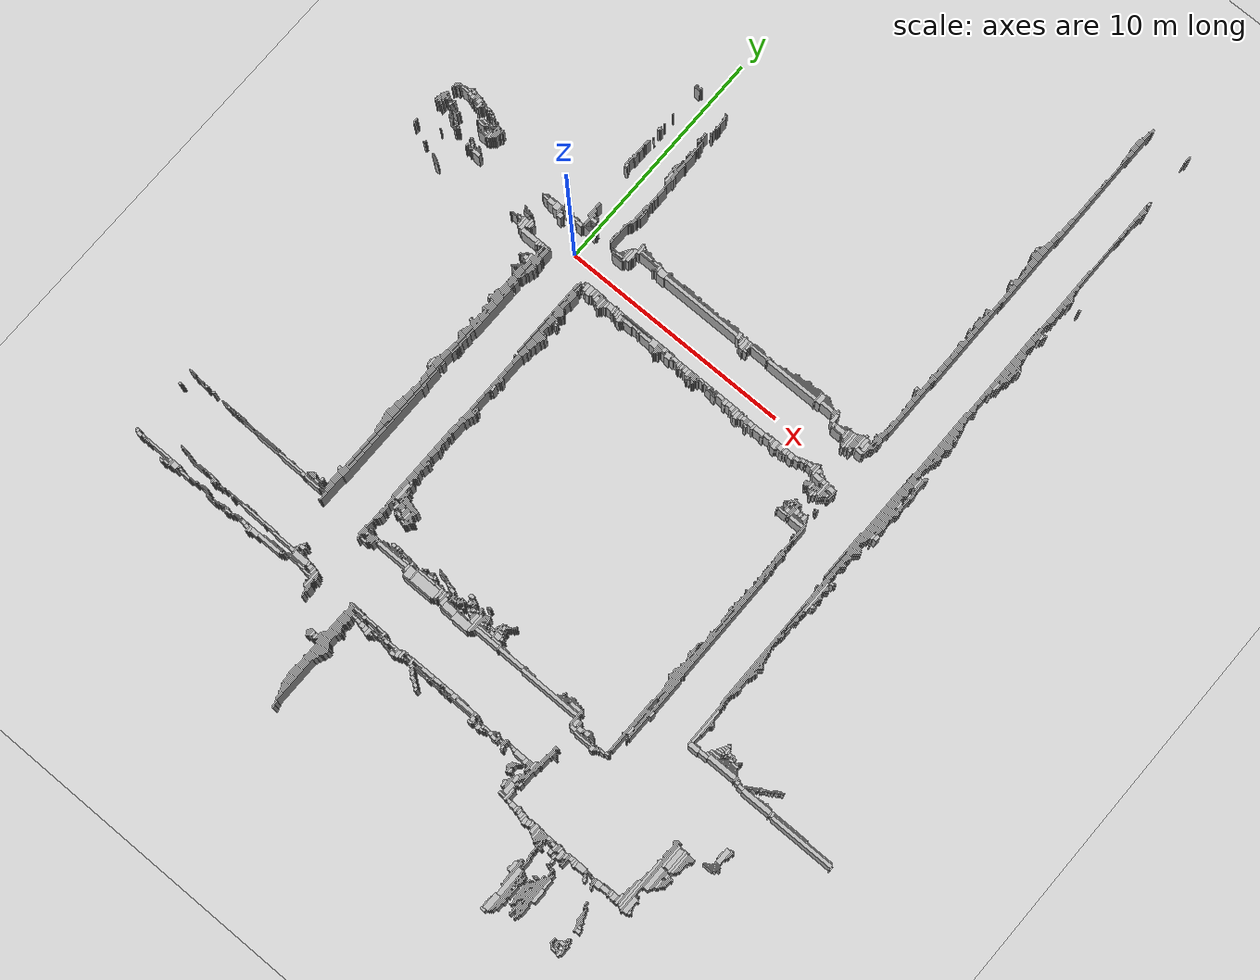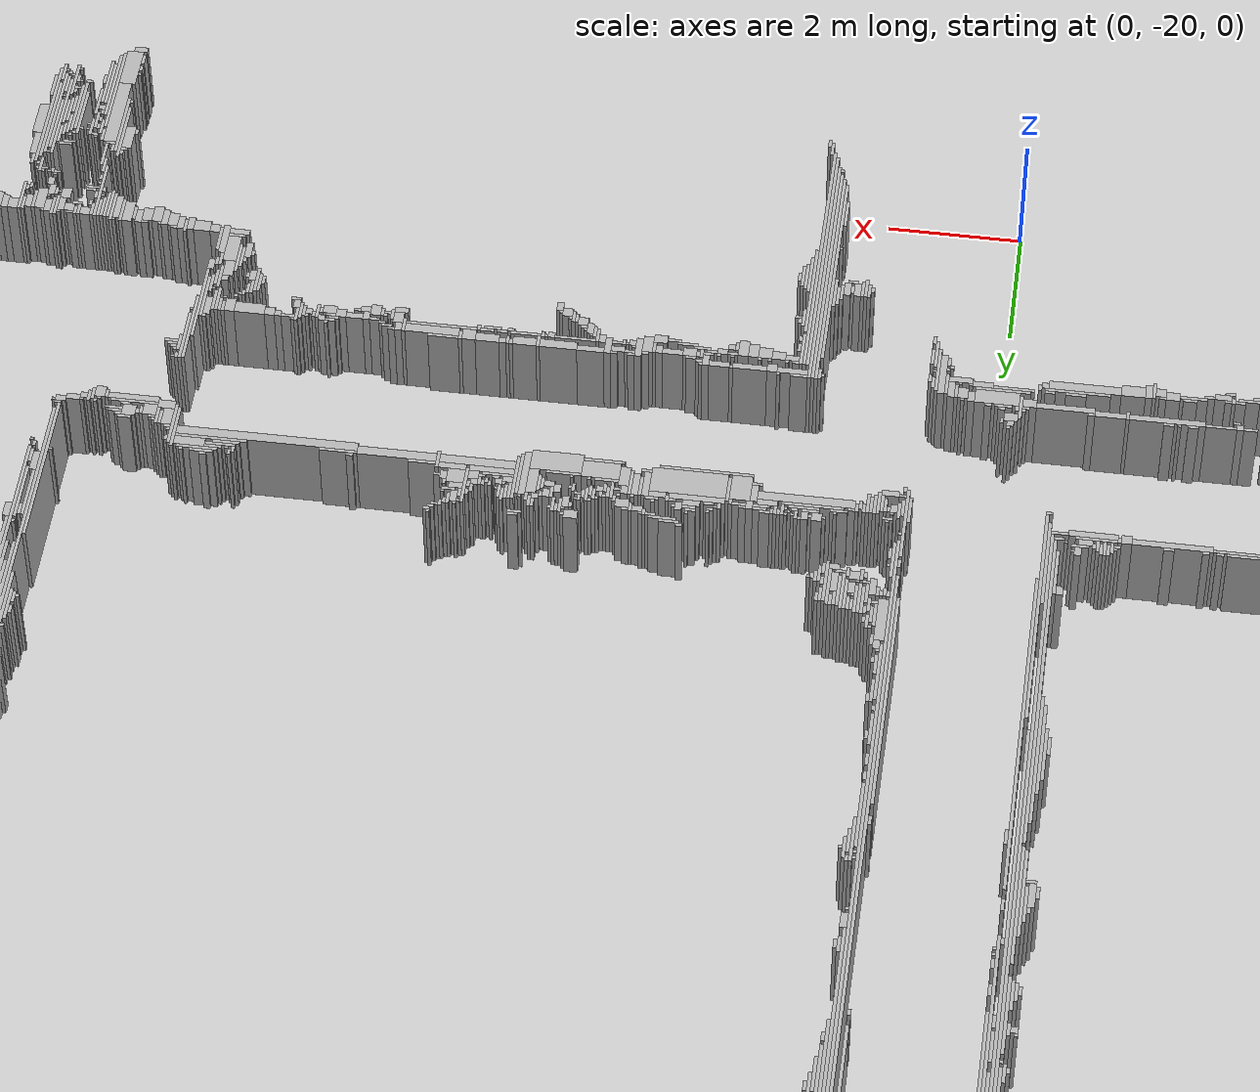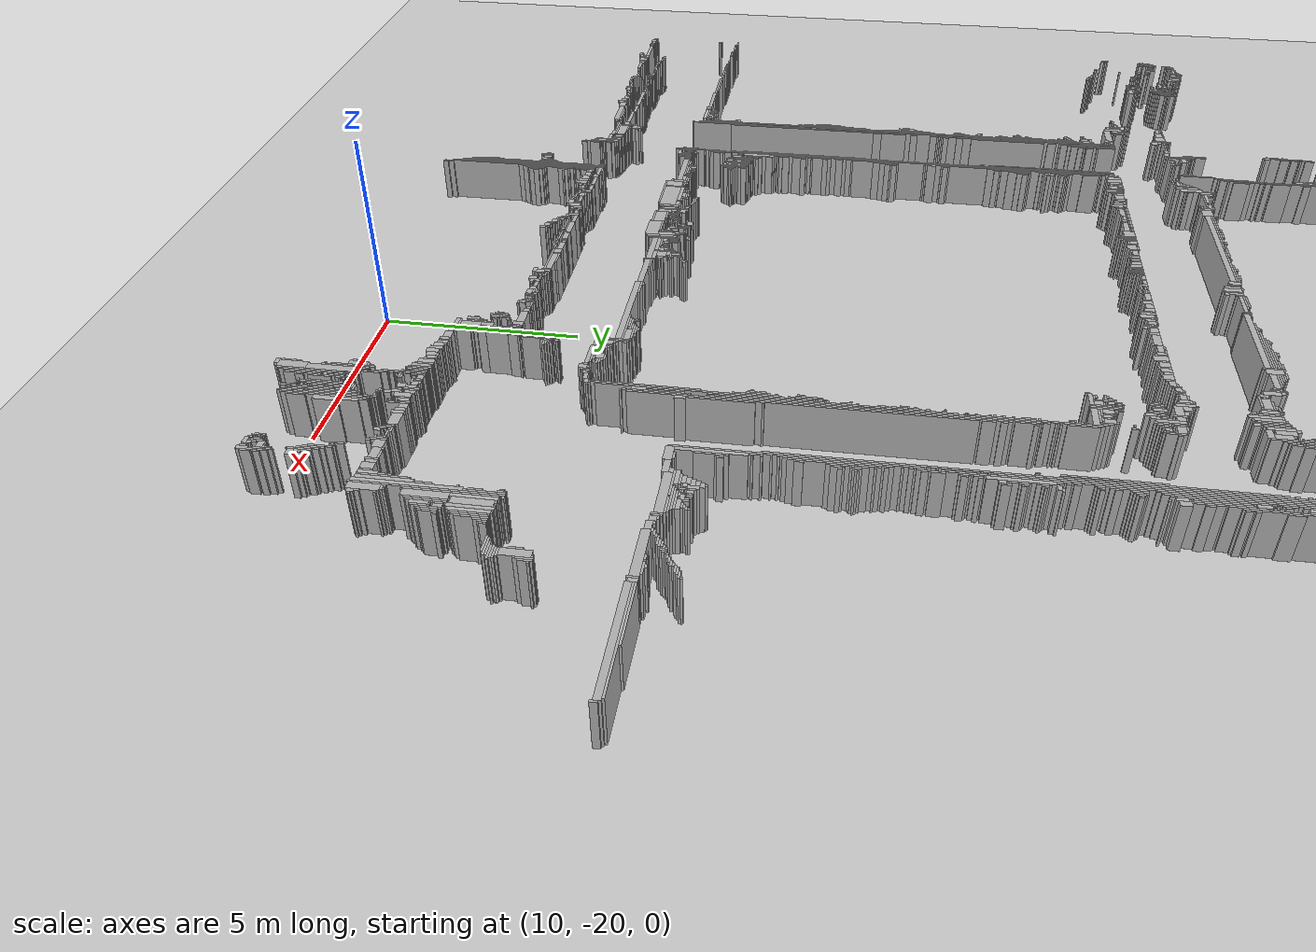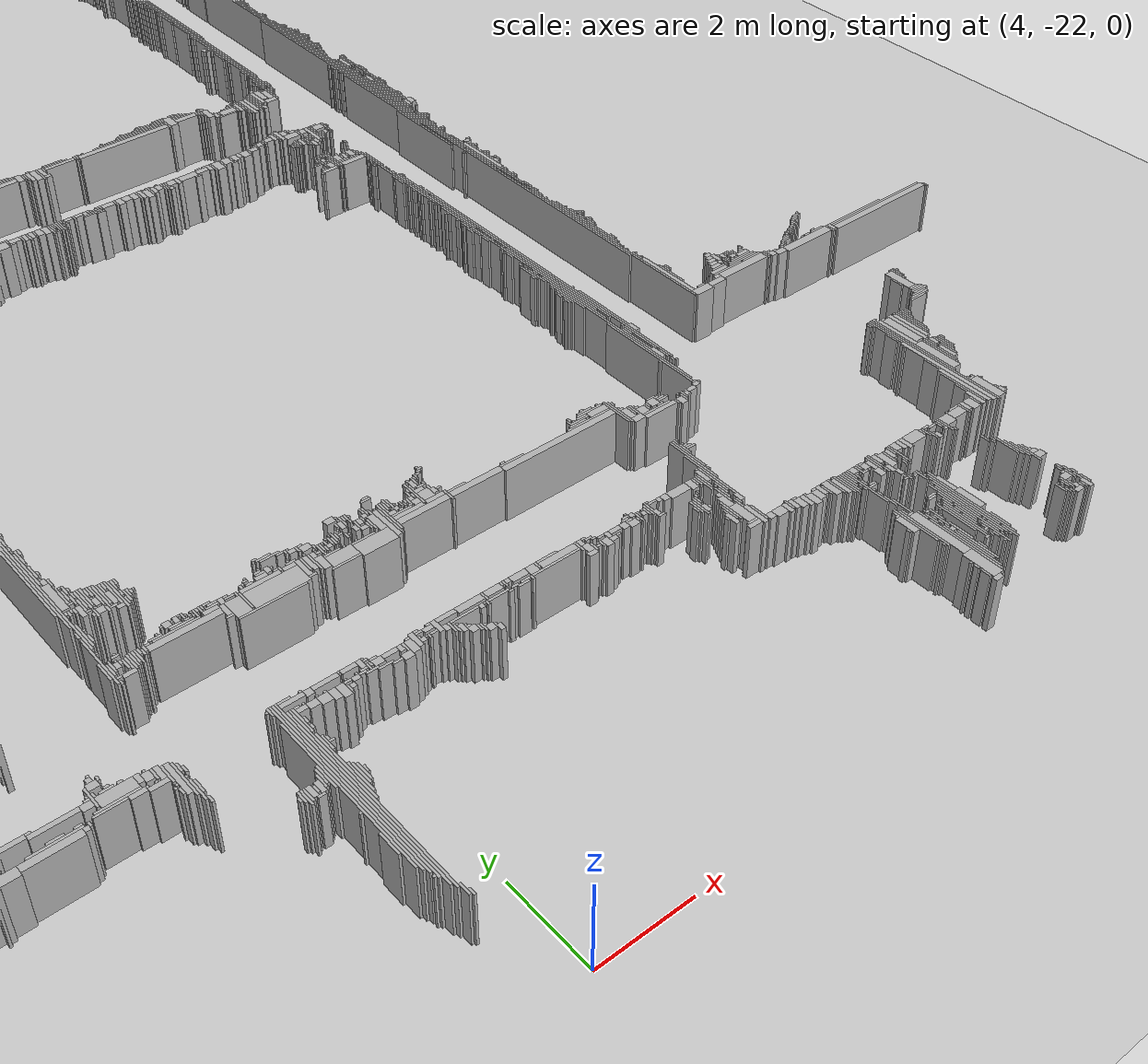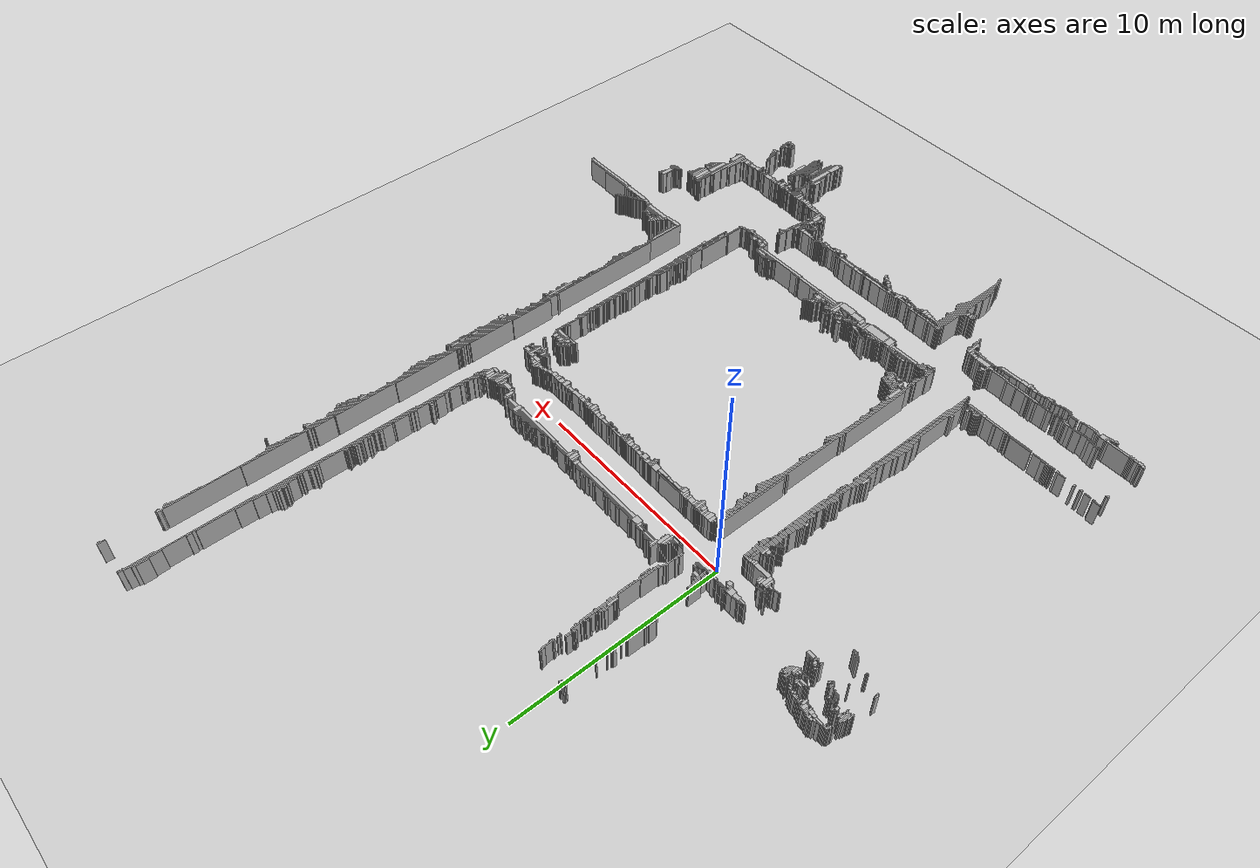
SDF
<?xml version="1.0"?>
<!-- generated by grid_to_world.py from d10_nav.yaml: 21252 occupied cells (21042 after dropping specks) -> 2055 boxes -->
<sdf version="1.6">
  <world name="d10_floor">
    <include><uri>model://sun</uri></include>
    <include><uri>model://ground_plane</uri></include>
    <physics type="ode"><max_step_size>0.001</max_step_size><real_time_update_rate>1000</real_time_update_rate></physics>
    <model name="d10_walls">
      <static>true</static>
      <link name='w0'><pose>13.725 -21.145 0.60 0 0 0</pose><collision name='c'><geometry><box><size>0.200 0.100 1.20</size></box></geometry></collision><visual name='v'><geometry><box><size>0.200 0.100 1.20</size></box></geometry><material><ambient>0.6 0.6 0.6 1</ambient><diffuse>0.7 0.7 0.7 1</diffuse></material></visual></link>
      <link name='w1'><pose>13.800 -20.745 0.60 0 0 0</pose><collision name='c'><geometry><box><size>0.250 0.700 1.20</size></box></geometry></collision><visual name='v'><geometry><box><size>0.250 0.700 1.20</size></box></geometry><material><ambient>0.6 0.6 0.6 1</ambient><diffuse>0.7 0.7 0.7 1</diffuse></material></visual></link>
      <link name='w2'><pose>13.650 -20.945 0.60 0 0 0</pose><collision name='c'><geometry><box><size>0.050 0.200 1.20</size></box></geometry></collision><visual name='v'><geometry><box><size>0.050 0.200 1.20</size></box></geometry><material><ambient>0.6 0.6 0.6 1</ambient><diffuse>0.7 0.7 0.7 1</diffuse></material></visual></link>
      <link name='w3'><pose>13.950 -20.245 0.60 0 0 0</pose><collision name='c'><geometry><box><size>0.050 1.600 1.20</size></box></geometry></collision><visual name='v'><geometry><box><size>0.050 1.600 1.20</size></box></geometry><material><ambient>0.6 0.6 0.6 1</ambient><diffuse>0.7 0.7 0.7 1</diffuse></material></visual></link>
      <link name='w4'><pose>14.000 -20.345 0.60 0 0 0</pose><collision name='c'><geometry><box><size>0.050 1.300 1.20</size></box></geometry></collision><visual name='v'><geometry><box><size>0.050 1.300 1.20</size></box></geometry><material><ambient>0.6 0.6 0.6 1</ambient><diffuse>0.7 0.7 0.7 1</diffuse></material></visual></link>
      <link name='w5'><pose>14.100 -20.395 0.60 0 0 0</pose><collision name='c'><geometry><box><size>0.050 0.900 1.20</size></box></geometry></collision><visual name='v'><geometry><box><size>0.050 0.900 1.20</size></box></geometry><material><ambient>0.6 0.6 0.6 1</ambient><diffuse>0.7 0.7 0.7 1</diffuse></material></visual></link>
      <link name='w6'><pose>13.650 -20.745 0.60 0 0 0</pose><collision name='c'><geometry><box><size>0.050 0.100 1.20</size></box></geometry></collision><visual name='v'><geometry><box><size>0.050 0.100 1.20</size></box></geometry><material><ambient>0.6 0.6 0.6 1</ambient><diffuse>0.7 0.7 0.7 1</diffuse></material></visual></link>
      <link name='w7'><pose>14.050 -20.370 0.60 0 0 0</pose><collision name='c'><geometry><box><size>0.050 0.850 1.20</size></box></geometry></collision><visual name='v'><geometry><box><size>0.050 0.850 1.20</size></box></geometry><material><ambient>0.6 0.6 0.6 1</ambient><diffuse>0.7 0.7 0.7 1</diffuse></material></visual></link>
      <link name='w8'><pose>14.600 -20.370 0.60 0 0 0</pose><collision name='c'><geometry><box><size>0.050 0.650 1.20</size></box></geometry></collision><visual name='v'><geometry><box><size>0.050 0.650 1.20</size></box></geometry><material><ambient>0.6 0.6 0.6 1</ambient><diffuse>0.7 0.7 0.7 1</diffuse></material></visual></link>
      <link name='w9'><pose>14.800 -20.520 0.60 0 0 0</pose><collision name='c'><geometry><box><size>0.050 0.350 1.20</size></box></geometry></collision><visual name='v'><geometry><box><size>0.050 0.350 1.20</size></box></geometry><material><ambient>0.6 0.6 0.6 1</ambient><diffuse>0.7 0.7 0.7 1</diffuse></material></visual></link>
      <link name='w10'><pose>16.875 -20.570 0.60 0 0 0</pose><collision name='c'><geometry><box><size>0.100 0.250 1.20</size></box></geometry></collision><visual name='v'><geometry><box><size>0.100 0.250 1.20</size></box></geometry><material><ambient>0.6 0.6 0.6 1</ambient><diffuse>0.7 0.7 0.7 1</diffuse></material></visual></link>
      <link name='w11'><pose>13.650 -20.620 0.60 0 0 0</pose><collision name='c'><geometry><box><size>0.050 0.050 1.20</size></box></geometry></collision><visual name='v'><geometry><box><size>0.050 0.050 1.20</size></box></geometry><material><ambient>0.6 0.6 0.6 1</ambient><diffuse>0.7 0.7 0.7 1</diffuse></material></visual></link>
      <link name='w12'><pose>14.550 -20.620 0.60 0 0 0</pose><collision name='c'><geometry><box><size>0.050 0.050 1.20</size></box></geometry></collision><visual name='v'><geometry><box><size>0.050 0.050 1.20</size></box></geometry><material><ambient>0.6 0.6 0.6 1</ambient><diffuse>0.7 0.7 0.7 1</diffuse></material></visual></link>
      <link name='w13'><pose>16.625 -20.595 0.60 0 0 0</pose><collision name='c'><geometry><box><size>0.200 0.100 1.20</size></box></geometry></collision><visual name='v'><geometry><box><size>0.200 0.100 1.20</size></box></geometry><material><ambient>0.6 0.6 0.6 1</ambient><diffuse>0.7 0.7 0.7 1</diffuse></material></visual></link>
      <link name='w14'><pose>16.800 -20.570 0.60 0 0 0</pose><collision name='c'><geometry><box><size>0.050 0.150 1.20</size></box></geometry></collision><visual name='v'><geometry><box><size>0.050 0.150 1.20</size></box></geometry><material><ambient>0.6 0.6 0.6 1</ambient><diffuse>0.7 0.7 0.7 1</diffuse></material></visual></link>
      <link name='w15'><pose>3.000 -20.520 0.60 0 0 0</pose><collision name='c'><geometry><box><size>0.050 0.150 1.20</size></box></geometry></collision><visual name='v'><geometry><box><size>0.050 0.150 1.20</size></box></geometry><material><ambient>0.6 0.6 0.6 1</ambient><diffuse>0.7 0.7 0.7 1</diffuse></material></visual></link>
      <link name='w16'><pose>14.750 -20.570 0.60 0 0 0</pose><collision name='c'><geometry><box><size>0.050 0.050 1.20</size></box></geometry></collision><visual name='v'><geometry><box><size>0.050 0.050 1.20</size></box></geometry><material><ambient>0.6 0.6 0.6 1</ambient><diffuse>0.7 0.7 0.7 1</diffuse></material></visual></link>
      <link name='w17'><pose>14.850 -19.595 0.60 0 0 0</pose><collision name='c'><geometry><box><size>0.050 2.000 1.20</size></box></geometry></collision><visual name='v'><geometry><box><size>0.050 2.000 1.20</size></box></geometry><material><ambient>0.6 0.6 0.6 1</ambient><diffuse>0.7 0.7 0.7 1</diffuse></material></visual></link>
      <link name='w18'><pose>16.500 -20.545 0.60 0 0 0</pose><collision name='c'><geometry><box><size>0.050 0.100 1.20</size></box></geometry></collision><visual name='v'><geometry><box><size>0.050 0.100 1.20</size></box></geometry><material><ambient>0.6 0.6 0.6 1</ambient><diffuse>0.7 0.7 0.7 1</diffuse></material></visual></link>
      <link name='w19'><pose>16.750 -20.545 0.60 0 0 0</pose><collision name='c'><geometry><box><size>0.050 0.100 1.20</size></box></geometry></collision><visual name='v'><geometry><box><size>0.050 0.100 1.20</size></box></geometry><material><ambient>0.6 0.6 0.6 1</ambient><diffuse>0.7 0.7 0.7 1</diffuse></material></visual></link>
      <link name='w20'><pose>16.950 -20.470 0.60 0 0 0</pose><collision name='c'><geometry><box><size>0.050 0.250 1.20</size></box></geometry></collision><visual name='v'><geometry><box><size>0.050 0.250 1.20</size></box></geometry><material><ambient>0.6 0.6 0.6 1</ambient><diffuse>0.7 0.7 0.7 1</diffuse></material></visual></link>
      <link name='w21'><pose>2.950 -20.420 0.60 0 0 0</pose><collision name='c'><geometry><box><size>0.050 0.250 1.20</size></box></geometry></collision><visual name='v'><geometry><box><size>0.050 0.250 1.20</size></box></geometry><material><ambient>0.6 0.6 0.6 1</ambient><diffuse>0.7 0.7 0.7 1</diffuse></material></visual></link>
      <link name='w22'><pose>14.150 -20.445 0.60 0 0 0</pose><collision name='c'><geometry><box><size>0.050 0.200 1.20</size></box></geometry></collision><visual name='v'><geometry><box><size>0.050 0.200 1.20</size></box></geometry><material><ambient>0.6 0.6 0.6 1</ambient><diffuse>0.7 0.7 0.7 1</diffuse></material></visual></link>
      <link name='w23'><pose>14.700 -20.520 0.60 0 0 0</pose><collision name='c'><geometry><box><size>0.050 0.050 1.20</size></box></geometry></collision><visual name='v'><geometry><box><size>0.050 0.050 1.20</size></box></geometry><material><ambient>0.6 0.6 0.6 1</ambient><diffuse>0.7 0.7 0.7 1</diffuse></material></visual></link>
      <link name='w24'><pose>16.450 -20.495 0.60 0 0 0</pose><collision name='c'><geometry><box><size>0.050 0.100 1.20</size></box></geometry></collision><visual name='v'><geometry><box><size>0.050 0.100 1.20</size></box></geometry><material><ambient>0.6 0.6 0.6 1</ambient><diffuse>0.7 0.7 0.7 1</diffuse></material></visual></link>
      <link name='w25'><pose>16.675 -20.495 0.60 0 0 0</pose><collision name='c'><geometry><box><size>0.100 0.100 1.20</size></box></geometry></collision><visual name='v'><geometry><box><size>0.100 0.100 1.20</size></box></geometry><material><ambient>0.6 0.6 0.6 1</ambient><diffuse>0.7 0.7 0.7 1</diffuse></material></visual></link>
      <link name='w26'><pose>14.550 -20.420 0.60 0 0 0</pose><collision name='c'><geometry><box><size>0.050 0.150 1.20</size></box></geometry></collision><visual name='v'><geometry><box><size>0.050 0.150 1.20</size></box></geometry><material><ambient>0.6 0.6 0.6 1</ambient><diffuse>0.7 0.7 0.7 1</diffuse></material></visual></link>
      <link name='w27'><pose>14.650 -20.470 0.60 0 0 0</pose><collision name='c'><geometry><box><size>0.050 0.050 1.20</size></box></geometry></collision><visual name='v'><geometry><box><size>0.050 0.050 1.20</size></box></geometry><material><ambient>0.6 0.6 0.6 1</ambient><diffuse>0.7 0.7 0.7 1</diffuse></material></visual></link>
      <link name='w28'><pose>14.750 -19.645 0.60 0 0 0</pose><collision name='c'><geometry><box><size>0.050 1.700 1.20</size></box></geometry></collision><visual name='v'><geometry><box><size>0.050 1.700 1.20</size></box></geometry><material><ambient>0.6 0.6 0.6 1</ambient><diffuse>0.7 0.7 0.7 1</diffuse></material></visual></link>
      <link name='w29'><pose>16.400 -20.370 0.60 0 0 0</pose><collision name='c'><geometry><box><size>0.050 0.250 1.20</size></box></geometry></collision><visual name='v'><geometry><box><size>0.050 0.250 1.20</size></box></geometry><material><ambient>0.6 0.6 0.6 1</ambient><diffuse>0.7 0.7 0.7 1</diffuse></material></visual></link>
      <link name='w30'><pose>16.600 -20.345 0.60 0 0 0</pose><collision name='c'><geometry><box><size>0.050 0.300 1.20</size></box></geometry></collision><visual name='v'><geometry><box><size>0.050 0.300 1.20</size></box></geometry><material><ambient>0.6 0.6 0.6 1</ambient><diffuse>0.7 0.7 0.7 1</diffuse></material></visual></link>
      <link name='w31'><pose>14.700 -20.270 0.60 0 0 0</pose><collision name='c'><geometry><box><size>0.050 0.350 1.20</size></box></geometry></collision><visual name='v'><geometry><box><size>0.050 0.350 1.20</size></box></geometry><material><ambient>0.6 0.6 0.6 1</ambient><diffuse>0.7 0.7 0.7 1</diffuse></material></visual></link>
      <link name='w32'><pose>14.900 -20.220 0.60 0 0 0</pose><collision name='c'><geometry><box><size>0.050 0.450 1.20</size></box></geometry></collision><visual name='v'><geometry><box><size>0.050 0.450 1.20</size></box></geometry><material><ambient>0.6 0.6 0.6 1</ambient><diffuse>0.7 0.7 0.7 1</diffuse></material></visual></link>
      <link name='w33'><pose>16.550 -20.345 0.60 0 0 0</pose><collision name='c'><geometry><box><size>0.050 0.200 1.20</size></box></geometry></collision><visual name='v'><geometry><box><size>0.050 0.200 1.20</size></box></geometry><material><ambient>0.6 0.6 0.6 1</ambient><diffuse>0.7 0.7 0.7 1</diffuse></material></visual></link>
      <link name='w34'><pose>16.650 -20.395 0.60 0 0 0</pose><collision name='c'><geometry><box><size>0.050 0.100 1.20</size></box></geometry></collision><visual name='v'><geometry><box><size>0.050 0.100 1.20</size></box></geometry><material><ambient>0.6 0.6 0.6 1</ambient><diffuse>0.7 0.7 0.7 1</diffuse></material></visual></link>
      <link name='w35'><pose>16.900 -20.345 0.60 0 0 0</pose><collision name='c'><geometry><box><size>0.050 0.200 1.20</size></box></geometry></collision><visual name='v'><geometry><box><size>0.050 0.200 1.20</size></box></geometry><material><ambient>0.6 0.6 0.6 1</ambient><diffuse>0.7 0.7 0.7 1</diffuse></material></visual></link>
      <link name='w36'><pose>13.825 -19.770 0.60 0 0 0</pose><collision name='c'><geometry><box><size>0.200 1.250 1.20</size></box></geometry></collision><visual name='v'><geometry><box><size>0.200 1.250 1.20</size></box></geometry><material><ambient>0.6 0.6 0.6 1</ambient><diffuse>0.7 0.7 0.7 1</diffuse></material></visual></link>
      <link name='w37'><pose>14.375 -20.370 0.60 0 0 0</pose><collision name='c'><geometry><box><size>0.100 0.050 1.20</size></box></geometry></collision><visual name='v'><geometry><box><size>0.100 0.050 1.20</size></box></geometry><material><ambient>0.6 0.6 0.6 1</ambient><diffuse>0.7 0.7 0.7 1</diffuse></material></visual></link>
      <link name='w38'><pose>14.500 -20.370 0.60 0 0 0</pose><collision name='c'><geometry><box><size>0.050 0.050 1.20</size></box></geometry></collision><visual name='v'><geometry><box><size>0.050 0.050 1.20</size></box></geometry><material><ambient>0.6 0.6 0.6 1</ambient><diffuse>0.7 0.7 0.7 1</diffuse></material></visual></link>
      <link name='w39'><pose>14.650 -19.595 0.60 0 0 0</pose><collision name='c'><geometry><box><size>0.050 1.600 1.20</size></box></geometry></collision><visual name='v'><geometry><box><size>0.050 1.600 1.20</size></box></geometry><material><ambient>0.6 0.6 0.6 1</ambient><diffuse>0.7 0.7 0.7 1</diffuse></material></visual></link>
      <link name='w40'><pose>16.450 -20.370 0.60 0 0 0</pose><collision name='c'><geometry><box><size>0.050 0.050 1.20</size></box></geometry></collision><visual name='v'><geometry><box><size>0.050 0.050 1.20</size></box></geometry><material><ambient>0.6 0.6 0.6 1</ambient><diffuse>0.7 0.7 0.7 1</diffuse></material></visual></link>
      <link name='w41'><pose>2.900 -18.170 0.60 0 0 0</pose><collision name='c'><geometry><box><size>0.050 4.350 1.20</size></box></geometry></collision><visual name='v'><geometry><box><size>0.050 4.350 1.20</size></box></geometry><material><ambient>0.6 0.6 0.6 1</ambient><diffuse>0.7 0.7 0.7 1</diffuse></material></visual></link>
      <link name='w42'><pose>14.400 -19.845 0.60 0 0 0</pose><collision name='c'><geometry><box><size>0.050 1.000 1.20</size></box></geometry></collision><visual name='v'><geometry><box><size>0.050 1.000 1.20</size></box></geometry><material><ambient>0.6 0.6 0.6 1</ambient><diffuse>0.7 0.7 0.7 1</diffuse></material></visual></link>
      <link name='w43'><pose>16.500 -20.320 0.60 0 0 0</pose><collision name='c'><geometry><box><size>0.050 0.050 1.20</size></box></geometry></collision><visual name='v'><geometry><box><size>0.050 0.050 1.20</size></box></geometry><material><ambient>0.6 0.6 0.6 1</ambient><diffuse>0.7 0.7 0.7 1</diffuse></material></visual></link>
      <link name='w44'><pose>16.850 -20.220 0.60 0 0 0</pose><collision name='c'><geometry><box><size>0.050 0.250 1.20</size></box></geometry></collision><visual name='v'><geometry><box><size>0.050 0.250 1.20</size></box></geometry><material><ambient>0.6 0.6 0.6 1</ambient><diffuse>0.7 0.7 0.7 1</diffuse></material></visual></link>
      <link name='w45'><pose>14.450 -19.795 0.60 0 0 0</pose><collision name='c'><geometry><box><size>0.050 1.000 1.20</size></box></geometry></collision><visual name='v'><geometry><box><size>0.050 1.000 1.20</size></box></geometry><material><ambient>0.6 0.6 0.6 1</ambient><diffuse>0.7 0.7 0.7 1</diffuse></material></visual></link>
      <link name='w46'><pose>14.800 -19.495 0.60 0 0 0</pose><collision name='c'><geometry><box><size>0.050 1.600 1.20</size></box></geometry></collision><visual name='v'><geometry><box><size>0.050 1.600 1.20</size></box></geometry><material><ambient>0.6 0.6 0.6 1</ambient><diffuse>0.7 0.7 0.7 1</diffuse></material></visual></link>
      <link name='w47'><pose>16.450 -20.270 0.60 0 0 0</pose><collision name='c'><geometry><box><size>0.050 0.050 1.20</size></box></geometry></collision><visual name='v'><geometry><box><size>0.050 0.050 1.20</size></box></geometry><material><ambient>0.6 0.6 0.6 1</ambient><diffuse>0.7 0.7 0.7 1</diffuse></material></visual></link>
      <link name='w48'><pose>16.725 -20.220 0.60 0 0 0</pose><collision name='c'><geometry><box><size>0.200 0.150 1.20</size></box></geometry></collision><visual name='v'><geometry><box><size>0.200 0.150 1.20</size></box></geometry><material><ambient>0.6 0.6 0.6 1</ambient><diffuse>0.7 0.7 0.7 1</diffuse></material></visual></link>
      <link name='w49'><pose>16.950 -20.220 0.60 0 0 0</pose><collision name='c'><geometry><box><size>0.050 0.150 1.20</size></box></geometry></collision><visual name='v'><geometry><box><size>0.050 0.150 1.20</size></box></geometry><material><ambient>0.6 0.6 0.6 1</ambient><diffuse>0.7 0.7 0.7 1</diffuse></material></visual></link>
      <link name='w50'><pose>2.850 -18.120 0.60 0 0 0</pose><collision name='c'><geometry><box><size>0.050 4.250 1.20</size></box></geometry></collision><visual name='v'><geometry><box><size>0.050 4.250 1.20</size></box></geometry><material><ambient>0.6 0.6 0.6 1</ambient><diffuse>0.7 0.7 0.7 1</diffuse></material></visual></link>
      <link name='w51'><pose>14.150 -19.970 0.60 0 0 0</pose><collision name='c'><geometry><box><size>0.050 0.550 1.20</size></box></geometry></collision><visual name='v'><geometry><box><size>0.050 0.550 1.20</size></box></geometry><material><ambient>0.6 0.6 0.6 1</ambient><diffuse>0.7 0.7 0.7 1</diffuse></material></visual></link>
      <link name='w52'><pose>14.525 -20.220 0.60 0 0 0</pose><collision name='c'><geometry><box><size>0.100 0.050 1.20</size></box></geometry></collision><visual name='v'><geometry><box><size>0.100 0.050 1.20</size></box></geometry><material><ambient>0.6 0.6 0.6 1</ambient><diffuse>0.7 0.7 0.7 1</diffuse></material></visual></link>
      <link name='w53'><pose>14.550 -20.145 0.60 0 0 0</pose><collision name='c'><geometry><box><size>0.050 0.100 1.20</size></box></geometry></collision><visual name='v'><geometry><box><size>0.050 0.100 1.20</size></box></geometry><material><ambient>0.6 0.6 0.6 1</ambient><diffuse>0.7 0.7 0.7 1</diffuse></material></visual></link>
      <link name='w54'><pose>16.900 -20.095 0.60 0 0 0</pose><collision name='c'><geometry><box><size>0.050 0.200 1.20</size></box></geometry></collision><visual name='v'><geometry><box><size>0.050 0.200 1.20</size></box></geometry><material><ambient>0.6 0.6 0.6 1</ambient><diffuse>0.7 0.7 0.7 1</diffuse></material></visual></link>
      <link name='w55'><pose>14.350 -19.695 0.60 0 0 0</pose><collision name='c'><geometry><box><size>0.050 0.900 1.20</size></box></geometry></collision><visual name='v'><geometry><box><size>0.050 0.900 1.20</size></box></geometry><material><ambient>0.6 0.6 0.6 1</ambient><diffuse>0.7 0.7 0.7 1</diffuse></material></visual></link>
      <link name='w56'><pose>16.775 -20.120 0.60 0 0 0</pose><collision name='c'><geometry><box><size>0.100 0.050 1.20</size></box></geometry></collision><visual name='v'><geometry><box><size>0.100 0.050 1.20</size></box></geometry><material><ambient>0.6 0.6 0.6 1</ambient><diffuse>0.7 0.7 0.7 1</diffuse></material></visual></link>
      <link name='w57'><pose>13.700 -19.520 0.60 0 0 0</pose><collision name='c'><geometry><box><size>0.050 1.150 1.20</size></box></geometry></collision><visual name='v'><geometry><box><size>0.050 1.150 1.20</size></box></geometry><material><ambient>0.6 0.6 0.6 1</ambient><diffuse>0.7 0.7 0.7 1</diffuse></material></visual></link>
      <link name='w58'><pose>16.800 -20.020 0.60 0 0 0</pose><collision name='c'><geometry><box><size>0.050 0.150 1.20</size></box></geometry></collision><visual name='v'><geometry><box><size>0.050 0.150 1.20</size></box></geometry><material><ambient>0.6 0.6 0.6 1</ambient><diffuse>0.7 0.7 0.7 1</diffuse></material></visual></link>
      <link name='w59'><pose>2.800 -17.895 0.60 0 0 0</pose><collision name='c'><geometry><box><size>0.050 4.300 1.20</size></box></geometry></collision><visual name='v'><geometry><box><size>0.050 4.300 1.20</size></box></geometry><material><ambient>0.6 0.6 0.6 1</ambient><diffuse>0.7 0.7 0.7 1</diffuse></material></visual></link>
      <link name='w60'><pose>13.650 -20.020 0.60 0 0 0</pose><collision name='c'><geometry><box><size>0.050 0.050 1.20</size></box></geometry></collision><visual name='v'><geometry><box><size>0.050 0.050 1.20</size></box></geometry><material><ambient>0.6 0.6 0.6 1</ambient><diffuse>0.7 0.7 0.7 1</diffuse></material></visual></link>
      <link name='w61'><pose>14.500 -19.870 0.60 0 0 0</pose><collision name='c'><geometry><box><size>0.050 0.350 1.20</size></box></geometry></collision><visual name='v'><geometry><box><size>0.050 0.350 1.20</size></box></geometry><material><ambient>0.6 0.6 0.6 1</ambient><diffuse>0.7 0.7 0.7 1</diffuse></material></visual></link>
      <link name='w62'><pose>14.700 -20.020 0.60 0 0 0</pose><collision name='c'><geometry><box><size>0.050 0.050 1.20</size></box></geometry></collision><visual name='v'><geometry><box><size>0.050 0.050 1.20</size></box></geometry><material><ambient>0.6 0.6 0.6 1</ambient><diffuse>0.7 0.7 0.7 1</diffuse></material></visual></link>
      <link name='w63'><pose>16.850 -19.970 0.60 0 0 0</pose><collision name='c'><geometry><box><size>0.050 0.150 1.20</size></box></geometry></collision><visual name='v'><geometry><box><size>0.050 0.150 1.20</size></box></geometry><material><ambient>0.6 0.6 0.6 1</ambient><diffuse>0.7 0.7 0.7 1</diffuse></material></visual></link>
      <link name='w64'><pose>2.750 -19.970 0.60 0 0 0</pose><collision name='c'><geometry><box><size>0.050 0.050 1.20</size></box></geometry></collision><visual name='v'><geometry><box><size>0.050 0.050 1.20</size></box></geometry><material><ambient>0.6 0.6 0.6 1</ambient><diffuse>0.7 0.7 0.7 1</diffuse></material></visual></link>
      <link name='w65'><pose>14.550 -19.745 0.60 0 0 0</pose><collision name='c'><geometry><box><size>0.050 0.500 1.20</size></box></geometry></collision><visual name='v'><geometry><box><size>0.050 0.500 1.20</size></box></geometry><material><ambient>0.6 0.6 0.6 1</ambient><diffuse>0.7 0.7 0.7 1</diffuse></material></visual></link>
      <link name='w66'><pose>14.600 -19.695 0.60 0 0 0</pose><collision name='c'><geometry><box><size>0.050 0.500 1.20</size></box></geometry></collision><visual name='v'><geometry><box><size>0.050 0.500 1.20</size></box></geometry><material><ambient>0.6 0.6 0.6 1</ambient><diffuse>0.7 0.7 0.7 1</diffuse></material></visual></link>
      <link name='w67'><pose>14.700 -19.420 0.60 0 0 0</pose><collision name='c'><geometry><box><size>0.050 1.050 1.20</size></box></geometry></collision><visual name='v'><geometry><box><size>0.050 1.050 1.20</size></box></geometry><material><ambient>0.6 0.6 0.6 1</ambient><diffuse>0.7 0.7 0.7 1</diffuse></material></visual></link>
      <link name='w68'><pose>2.750 -17.820 0.60 0 0 0</pose><collision name='c'><geometry><box><size>0.050 4.150 1.20</size></box></geometry></collision><visual name='v'><geometry><box><size>0.050 4.150 1.20</size></box></geometry><material><ambient>0.6 0.6 0.6 1</ambient><diffuse>0.7 0.7 0.7 1</diffuse></material></visual></link>
      <link name='w69'><pose>13.650 -19.370 0.60 0 0 0</pose><collision name='c'><geometry><box><size>0.050 1.050 1.20</size></box></geometry></collision><visual name='v'><geometry><box><size>0.050 1.050 1.20</size></box></geometry><material><ambient>0.6 0.6 0.6 1</ambient><diffuse>0.7 0.7 0.7 1</diffuse></material></visual></link>
      <link name='w70'><pose>14.075 -19.845 0.60 0 0 0</pose><collision name='c'><geometry><box><size>0.100 0.100 1.20</size></box></geometry></collision><visual name='v'><geometry><box><size>0.100 0.100 1.20</size></box></geometry><material><ambient>0.6 0.6 0.6 1</ambient><diffuse>0.7 0.7 0.7 1</diffuse></material></visual></link>
      <link name='w71'><pose>2.700 -17.770 0.60 0 0 0</pose><collision name='c'><geometry><box><size>0.050 4.050 1.20</size></box></geometry></collision><visual name='v'><geometry><box><size>0.050 4.050 1.20</size></box></geometry><material><ambient>0.6 0.6 0.6 1</ambient><diffuse>0.7 0.7 0.7 1</diffuse></material></visual></link>
      <link name='w72'><pose>14.050 -19.745 0.60 0 0 0</pose><collision name='c'><geometry><box><size>0.050 0.100 1.20</size></box></geometry></collision><visual name='v'><geometry><box><size>0.050 0.100 1.20</size></box></geometry><material><ambient>0.6 0.6 0.6 1</ambient><diffuse>0.7 0.7 0.7 1</diffuse></material></visual></link>
      <link name='w73'><pose>14.950 -19.495 0.60 0 0 0</pose><collision name='c'><geometry><box><size>0.150 0.600 1.20</size></box></geometry></collision><visual name='v'><geometry><box><size>0.150 0.600 1.20</size></box></geometry><material><ambient>0.6 0.6 0.6 1</ambient><diffuse>0.7 0.7 0.7 1</diffuse></material></visual></link>
      <link name='w74'><pose>14.100 -19.570 0.60 0 0 0</pose><collision name='c'><geometry><box><size>0.050 0.350 1.20</size></box></geometry></collision><visual name='v'><geometry><box><size>0.050 0.350 1.20</size></box></geometry><material><ambient>0.6 0.6 0.6 1</ambient><diffuse>0.7 0.7 0.7 1</diffuse></material></visual></link>
      <link name='w75'><pose>2.650 -17.920 0.60 0 0 0</pose><collision name='c'><geometry><box><size>0.050 3.550 1.20</size></box></geometry></collision><visual name='v'><geometry><box><size>0.050 3.550 1.20</size></box></geometry><material><ambient>0.6 0.6 0.6 1</ambient><diffuse>0.7 0.7 0.7 1</diffuse></material></visual></link>
      <link name='w76'><pose>14.050 -19.595 0.60 0 0 0</pose><collision name='c'><geometry><box><size>0.050 0.100 1.20</size></box></geometry></collision><visual name='v'><geometry><box><size>0.050 0.100 1.20</size></box></geometry><material><ambient>0.6 0.6 0.6 1</ambient><diffuse>0.7 0.7 0.7 1</diffuse></material></visual></link>
      <link name='w77'><pose>14.500 -19.445 0.60 0 0 0</pose><collision name='c'><geometry><box><size>0.050 0.400 1.20</size></box></geometry></collision><visual name='v'><geometry><box><size>0.050 0.400 1.20</size></box></geometry><material><ambient>0.6 0.6 0.6 1</ambient><diffuse>0.7 0.7 0.7 1</diffuse></material></visual></link>
      <link name='w78'><pose>16.750 -19.370 0.60 0 0 0</pose><collision name='c'><geometry><box><size>0.050 0.550 1.20</size></box></geometry></collision><visual name='v'><geometry><box><size>0.050 0.550 1.20</size></box></geometry><material><ambient>0.6 0.6 0.6 1</ambient><diffuse>0.7 0.7 0.7 1</diffuse></material></visual></link>
      <link name='w79'><pose>14.000 -19.445 0.60 0 0 0</pose><collision name='c'><geometry><box><size>0.050 0.300 1.20</size></box></geometry></collision><visual name='v'><geometry><box><size>0.050 0.300 1.20</size></box></geometry><material><ambient>0.6 0.6 0.6 1</ambient><diffuse>0.7 0.7 0.7 1</diffuse></material></visual></link>
      <link name='w80'><pose>14.150 -19.420 0.60 0 0 0</pose><collision name='c'><geometry><box><size>0.050 0.350 1.20</size></box></geometry></collision><visual name='v'><geometry><box><size>0.050 0.350 1.20</size></box></geometry><material><ambient>0.6 0.6 0.6 1</ambient><diffuse>0.7 0.7 0.7 1</diffuse></material></visual></link>
      <link name='w81'><pose>16.875 -19.520 0.60 0 0 0</pose><collision name='c'><geometry><box><size>0.200 0.150 1.20</size></box></geometry></collision><visual name='v'><geometry><box><size>0.200 0.150 1.20</size></box></geometry><material><ambient>0.6 0.6 0.6 1</ambient><diffuse>0.7 0.7 0.7 1</diffuse></material></visual></link>
      <link name='w82'><pose>13.550 -19.270 0.60 0 0 0</pose><collision name='c'><geometry><box><size>0.150 0.450 1.20</size></box></geometry></collision><visual name='v'><geometry><box><size>0.150 0.450 1.20</size></box></geometry><material><ambient>0.6 0.6 0.6 1</ambient><diffuse>0.7 0.7 0.7 1</diffuse></material></visual></link>
      <link name='w83'><pose>14.050 -19.445 0.60 0 0 0</pose><collision name='c'><geometry><box><size>0.050 0.100 1.20</size></box></geometry></collision><visual name='v'><geometry><box><size>0.050 0.100 1.20</size></box></geometry><material><ambient>0.6 0.6 0.6 1</ambient><diffuse>0.7 0.7 0.7 1</diffuse></material></visual></link>
      <link name='w84'><pose>14.200 -19.470 0.60 0 0 0</pose><collision name='c'><geometry><box><size>0.050 0.050 1.20</size></box></geometry></collision><visual name='v'><geometry><box><size>0.050 0.050 1.20</size></box></geometry><material><ambient>0.6 0.6 0.6 1</ambient><diffuse>0.7 0.7 0.7 1</diffuse></material></visual></link>
      <link name='w85'><pose>13.450 -19.395 0.60 0 0 0</pose><collision name='c'><geometry><box><size>0.050 0.100 1.20</size></box></geometry></collision><visual name='v'><geometry><box><size>0.050 0.100 1.20</size></box></geometry><material><ambient>0.6 0.6 0.6 1</ambient><diffuse>0.7 0.7 0.7 1</diffuse></material></visual></link>
      <link name='w86'><pose>14.550 -19.320 0.60 0 0 0</pose><collision name='c'><geometry><box><size>0.050 0.250 1.20</size></box></geometry></collision><visual name='v'><geometry><box><size>0.050 0.250 1.20</size></box></geometry><material><ambient>0.6 0.6 0.6 1</ambient><diffuse>0.7 0.7 0.7 1</diffuse></material></visual></link>
      <link name='w87'><pose>16.700 -19.195 0.60 0 0 0</pose><collision name='c'><geometry><box><size>0.050 0.500 1.20</size></box></geometry></collision><visual name='v'><geometry><box><size>0.050 0.500 1.20</size></box></geometry><material><ambient>0.6 0.6 0.6 1</ambient><diffuse>0.7 0.7 0.7 1</diffuse></material></visual></link>
      <link name='w88'><pose>16.850 -19.395 0.60 0 0 0</pose><collision name='c'><geometry><box><size>0.150 0.100 1.20</size></box></geometry></collision><visual name='v'><geometry><box><size>0.150 0.100 1.20</size></box></geometry><material><ambient>0.6 0.6 0.6 1</ambient><diffuse>0.7 0.7 0.7 1</diffuse></material></visual></link>
      <link name='w89'><pose>13.950 -19.270 0.60 0 0 0</pose><collision name='c'><geometry><box><size>0.050 0.250 1.20</size></box></geometry></collision><visual name='v'><geometry><box><size>0.050 0.250 1.20</size></box></geometry><material><ambient>0.6 0.6 0.6 1</ambient><diffuse>0.7 0.7 0.7 1</diffuse></material></visual></link>
      <link name='w90'><pose>14.200 -19.370 0.60 0 0 0</pose><collision name='c'><geometry><box><size>0.050 0.050 1.20</size></box></geometry></collision><visual name='v'><geometry><box><size>0.050 0.050 1.20</size></box></geometry><material><ambient>0.6 0.6 0.6 1</ambient><diffuse>0.7 0.7 0.7 1</diffuse></material></visual></link>
      <link name='w91'><pose>14.300 -19.370 0.60 0 0 0</pose><collision name='c'><geometry><box><size>0.050 0.050 1.20</size></box></geometry></collision><visual name='v'><geometry><box><size>0.050 0.050 1.20</size></box></geometry><material><ambient>0.6 0.6 0.6 1</ambient><diffuse>0.7 0.7 0.7 1</diffuse></material></visual></link>
      <link name='w92'><pose>14.600 -19.220 0.60 0 0 0</pose><collision name='c'><geometry><box><size>0.050 0.350 1.20</size></box></geometry></collision><visual name='v'><geometry><box><size>0.050 0.350 1.20</size></box></geometry><material><ambient>0.6 0.6 0.6 1</ambient><diffuse>0.7 0.7 0.7 1</diffuse></material></visual></link>
      <link name='w93'><pose>2.600 -19.095 0.60 0 0 0</pose><collision name='c'><geometry><box><size>0.050 0.500 1.20</size></box></geometry></collision><visual name='v'><geometry><box><size>0.050 0.500 1.20</size></box></geometry><material><ambient>0.6 0.6 0.6 1</ambient><diffuse>0.7 0.7 0.7 1</diffuse></material></visual></link>
      <link name='w94'><pose>16.650 -19.095 0.60 0 0 0</pose><collision name='c'><geometry><box><size>0.050 0.500 1.20</size></box></geometry></collision><visual name='v'><geometry><box><size>0.050 0.500 1.20</size></box></geometry><material><ambient>0.6 0.6 0.6 1</ambient><diffuse>0.7 0.7 0.7 1</diffuse></material></visual></link>
      <link name='w95'><pose>16.825 -19.320 0.60 0 0 0</pose><collision name='c'><geometry><box><size>0.100 0.050 1.20</size></box></geometry></collision><visual name='v'><geometry><box><size>0.100 0.050 1.20</size></box></geometry><material><ambient>0.6 0.6 0.6 1</ambient><diffuse>0.7 0.7 0.7 1</diffuse></material></visual></link>
      <link name='w96'><pose>14.075 -19.270 0.60 0 0 0</pose><collision name='c'><geometry><box><size>0.100 0.050 1.20</size></box></geometry></collision><visual name='v'><geometry><box><size>0.100 0.050 1.20</size></box></geometry><material><ambient>0.6 0.6 0.6 1</ambient><diffuse>0.7 0.7 0.7 1</diffuse></material></visual></link>
      <link name='w97'><pose>14.400 -19.270 0.60 0 0 0</pose><collision name='c'><geometry><box><size>0.050 0.050 1.20</size></box></geometry></collision><visual name='v'><geometry><box><size>0.050 0.050 1.20</size></box></geometry><material><ambient>0.6 0.6 0.6 1</ambient><diffuse>0.7 0.7 0.7 1</diffuse></material></visual></link>
      <link name='w98'><pose>16.800 -19.220 0.60 0 0 0</pose><collision name='c'><geometry><box><size>0.050 0.150 1.20</size></box></geometry></collision><visual name='v'><geometry><box><size>0.050 0.150 1.20</size></box></geometry><material><ambient>0.6 0.6 0.6 1</ambient><diffuse>0.7 0.7 0.7 1</diffuse></material></visual></link>
      <link name='w99'><pose>14.050 -19.220 0.60 0 0 0</pose><collision name='c'><geometry><box><size>0.050 0.050 1.20</size></box></geometry></collision><visual name='v'><geometry><box><size>0.050 0.050 1.20</size></box></geometry><material><ambient>0.6 0.6 0.6 1</ambient><diffuse>0.7 0.7 0.7 1</diffuse></material></visual></link>
      <link name='w100'><pose>14.450 -19.220 0.60 0 0 0</pose><collision name='c'><geometry><box><size>0.050 0.050 1.20</size></box></geometry></collision><visual name='v'><geometry><box><size>0.050 0.050 1.20</size></box></geometry><material><ambient>0.6 0.6 0.6 1</ambient><diffuse>0.7 0.7 0.7 1</diffuse></material></visual></link>
      <link name='w101'><pose>16.600 -18.970 0.60 0 0 0</pose><collision name='c'><geometry><box><size>0.050 0.550 1.20</size></box></geometry></collision><visual name='v'><geometry><box><size>0.050 0.550 1.20</size></box></geometry><material><ambient>0.6 0.6 0.6 1</ambient><diffuse>0.7 0.7 0.7 1</diffuse></material></visual></link>
      <link name='w102'><pose>14.925 -18.970 0.60 0 0 0</pose><collision name='c'><geometry><box><size>0.100 0.450 1.20</size></box></geometry></collision><visual name='v'><geometry><box><size>0.100 0.450 1.20</size></box></geometry><material><ambient>0.6 0.6 0.6 1</ambient><diffuse>0.7 0.7 0.7 1</diffuse></material></visual></link>
      <link name='w103'><pose>13.800 -19.120 0.60 0 0 0</pose><collision name='c'><geometry><box><size>0.150 0.050 1.20</size></box></geometry></collision><visual name='v'><geometry><box><size>0.150 0.050 1.20</size></box></geometry><material><ambient>0.6 0.6 0.6 1</ambient><diffuse>0.7 0.7 0.7 1</diffuse></material></visual></link>
      <link name='w104'><pose>13.750 -19.020 0.60 0 0 0</pose><collision name='c'><geometry><box><size>0.050 0.150 1.20</size></box></geometry></collision><visual name='v'><geometry><box><size>0.050 0.150 1.20</size></box></geometry><material><ambient>0.6 0.6 0.6 1</ambient><diffuse>0.7 0.7 0.7 1</diffuse></material></visual></link>
      <link name='w105'><pose>13.850 -18.870 0.60 0 0 0</pose><collision name='c'><geometry><box><size>0.050 0.450 1.20</size></box></geometry></collision><visual name='v'><geometry><box><size>0.050 0.450 1.20</size></box></geometry><material><ambient>0.6 0.6 0.6 1</ambient><diffuse>0.7 0.7 0.7 1</diffuse></material></visual></link>
      <link name='w106'><pose>14.425 -19.070 0.60 0 0 0</pose><collision name='c'><geometry><box><size>0.200 0.050 1.20</size></box></geometry></collision><visual name='v'><geometry><box><size>0.200 0.050 1.20</size></box></geometry><material><ambient>0.6 0.6 0.6 1</ambient><diffuse>0.7 0.7 0.7 1</diffuse></material></visual></link>
      <link name='w107'><pose>13.575 -19.020 0.60 0 0 0</pose><collision name='c'><geometry><box><size>0.100 0.050 1.20</size></box></geometry></collision><visual name='v'><geometry><box><size>0.100 0.050 1.20</size></box></geometry><material><ambient>0.6 0.6 0.6 1</ambient><diffuse>0.7 0.7 0.7 1</diffuse></material></visual></link>
      <link name='w108'><pose>14.475 -19.020 0.60 0 0 0</pose><collision name='c'><geometry><box><size>0.200 0.050 1.20</size></box></geometry></collision><visual name='v'><geometry><box><size>0.200 0.050 1.20</size></box></geometry><material><ambient>0.6 0.6 0.6 1</ambient><diffuse>0.7 0.7 0.7 1</diffuse></material></visual></link>
      <link name='w109'><pose>13.600 -18.945 0.60 0 0 0</pose><collision name='c'><geometry><box><size>0.050 0.100 1.20</size></box></geometry></collision><visual name='v'><geometry><box><size>0.050 0.100 1.20</size></box></geometry><material><ambient>0.6 0.6 0.6 1</ambient><diffuse>0.7 0.7 0.7 1</diffuse></material></visual></link>
      <link name='w110'><pose>14.700 -18.820 0.60 0 0 0</pose><collision name='c'><geometry><box><size>0.050 0.050 1.20</size></box></geometry></collision><visual name='v'><geometry><box><size>0.050 0.050 1.20</size></box></geometry><material><ambient>0.6 0.6 0.6 1</ambient><diffuse>0.7 0.7 0.7 1</diffuse></material></visual></link>
      <link name='w111'><pose>13.800 -18.645 0.60 0 0 0</pose><collision name='c'><geometry><box><size>0.050 0.300 1.20</size></box></geometry></collision><visual name='v'><geometry><box><size>0.050 0.300 1.20</size></box></geometry><material><ambient>0.6 0.6 0.6 1</ambient><diffuse>0.7 0.7 0.7 1</diffuse></material></visual></link>
      <link name='w112'><pose>16.500 -18.745 0.60 0 0 0</pose><collision name='c'><geometry><box><size>0.050 0.100 1.20</size></box></geometry></collision><visual name='v'><geometry><box><size>0.050 0.100 1.20</size></box></geometry><material><ambient>0.6 0.6 0.6 1</ambient><diffuse>0.7 0.7 0.7 1</diffuse></material></visual></link>
      <link name='w113'><pose>14.900 -18.645 0.60 0 0 0</pose><collision name='c'><geometry><box><size>0.050 0.200 1.20</size></box></geometry></collision><visual name='v'><geometry><box><size>0.050 0.200 1.20</size></box></geometry><material><ambient>0.6 0.6 0.6 1</ambient><diffuse>0.7 0.7 0.7 1</diffuse></material></visual></link>
      <link name='w114'><pose>16.550 -18.695 0.60 0 0 0</pose><collision name='c'><geometry><box><size>0.050 0.100 1.20</size></box></geometry></collision><visual name='v'><geometry><box><size>0.050 0.100 1.20</size></box></geometry><material><ambient>0.6 0.6 0.6 1</ambient><diffuse>0.7 0.7 0.7 1</diffuse></material></visual></link>
      <link name='w115'><pose>14.750 -18.545 0.60 0 0 0</pose><collision name='c'><geometry><box><size>0.050 0.300 1.20</size></box></geometry></collision><visual name='v'><geometry><box><size>0.050 0.300 1.20</size></box></geometry><material><ambient>0.6 0.6 0.6 1</ambient><diffuse>0.7 0.7 0.7 1</diffuse></material></visual></link>
      <link name='w116'><pose>16.450 -18.595 0.60 0 0 0</pose><collision name='c'><geometry><box><size>0.050 0.200 1.20</size></box></geometry></collision><visual name='v'><geometry><box><size>0.050 0.200 1.20</size></box></geometry><material><ambient>0.6 0.6 0.6 1</ambient><diffuse>0.7 0.7 0.7 1</diffuse></material></visual></link>
      <link name='w117'><pose>13.750 -18.120 0.60 0 0 0</pose><collision name='c'><geometry><box><size>0.050 1.050 1.20</size></box></geometry></collision><visual name='v'><geometry><box><size>0.050 1.050 1.20</size></box></geometry><material><ambient>0.6 0.6 0.6 1</ambient><diffuse>0.7 0.7 0.7 1</diffuse></material></visual></link>
      <link name='w118'><pose>14.800 -18.570 0.60 0 0 0</pose><collision name='c'><geometry><box><size>0.050 0.050 1.20</size></box></geometry></collision><visual name='v'><geometry><box><size>0.050 0.050 1.20</size></box></geometry><material><ambient>0.6 0.6 0.6 1</ambient><diffuse>0.7 0.7 0.7 1</diffuse></material></visual></link>
      <link name='w119'><pose>14.550 -18.445 0.60 0 0 0</pose><collision name='c'><geometry><box><size>0.050 0.100 1.20</size></box></geometry></collision><visual name='v'><geometry><box><size>0.050 0.100 1.20</size></box></geometry><material><ambient>0.6 0.6 0.6 1</ambient><diffuse>0.7 0.7 0.7 1</diffuse></material></visual></link>
      <link name='w120'><pose>14.675 -18.470 0.60 0 0 0</pose><collision name='c'><geometry><box><size>0.100 0.050 1.20</size></box></geometry></collision><visual name='v'><geometry><box><size>0.100 0.050 1.20</size></box></geometry><material><ambient>0.6 0.6 0.6 1</ambient><diffuse>0.7 0.7 0.7 1</diffuse></material></visual></link>
      <link name='w121'><pose>14.800 -18.470 0.60 0 0 0</pose><collision name='c'><geometry><box><size>0.050 0.050 1.20</size></box></geometry></collision><visual name='v'><geometry><box><size>0.050 0.050 1.20</size></box></geometry><material><ambient>0.6 0.6 0.6 1</ambient><diffuse>0.7 0.7 0.7 1</diffuse></material></visual></link>
      <link name='w122'><pose>13.800 -18.395 0.60 0 0 0</pose><collision name='c'><geometry><box><size>0.050 0.100 1.20</size></box></geometry></collision><visual name='v'><geometry><box><size>0.050 0.100 1.20</size></box></geometry><material><ambient>0.6 0.6 0.6 1</ambient><diffuse>0.7 0.7 0.7 1</diffuse></material></visual></link>
      <link name='w123'><pose>14.475 -18.420 0.60 0 0 0</pose><collision name='c'><geometry><box><size>0.100 0.050 1.20</size></box></geometry></collision><visual name='v'><geometry><box><size>0.100 0.050 1.20</size></box></geometry><material><ambient>0.6 0.6 0.6 1</ambient><diffuse>0.7 0.7 0.7 1</diffuse></material></visual></link>
      <link name='w124'><pose>14.600 -18.420 0.60 0 0 0</pose><collision name='c'><geometry><box><size>0.050 0.050 1.20</size></box></geometry></collision><visual name='v'><geometry><box><size>0.050 0.050 1.20</size></box></geometry><material><ambient>0.6 0.6 0.6 1</ambient><diffuse>0.7 0.7 0.7 1</diffuse></material></visual></link>
      <link name='w125'><pose>14.700 -18.420 0.60 0 0 0</pose><collision name='c'><geometry><box><size>0.050 0.050 1.20</size></box></geometry></collision><visual name='v'><geometry><box><size>0.050 0.050 1.20</size></box></geometry><material><ambient>0.6 0.6 0.6 1</ambient><diffuse>0.7 0.7 0.7 1</diffuse></material></visual></link>
      <link name='w126'><pose>2.600 -18.370 0.60 0 0 0</pose><collision name='c'><geometry><box><size>0.050 0.050 1.20</size></box></geometry></collision><visual name='v'><geometry><box><size>0.050 0.050 1.20</size></box></geometry><material><ambient>0.6 0.6 0.6 1</ambient><diffuse>0.7 0.7 0.7 1</diffuse></material></visual></link>
      <link name='w127'><pose>14.500 -18.370 0.60 0 0 0</pose><collision name='c'><geometry><box><size>0.050 0.050 1.20</size></box></geometry></collision><visual name='v'><geometry><box><size>0.050 0.050 1.20</size></box></geometry><material><ambient>0.6 0.6 0.6 1</ambient><diffuse>0.7 0.7 0.7 1</diffuse></material></visual></link>
      <link name='w128'><pose>2.950 -17.470 0.60 0 0 0</pose><collision name='c'><geometry><box><size>0.050 1.650 1.20</size></box></geometry></collision><visual name='v'><geometry><box><size>0.050 1.650 1.20</size></box></geometry><material><ambient>0.6 0.6 0.6 1</ambient><diffuse>0.7 0.7 0.7 1</diffuse></material></visual></link>
      <link name='w129'><pose>13.800 -18.270 0.60 0 0 0</pose><collision name='c'><geometry><box><size>0.050 0.050 1.20</size></box></geometry></collision><visual name='v'><geometry><box><size>0.050 0.050 1.20</size></box></geometry><material><ambient>0.6 0.6 0.6 1</ambient><diffuse>0.7 0.7 0.7 1</diffuse></material></visual></link>
      <link name='w130'><pose>14.525 -18.220 0.60 0 0 0</pose><collision name='c'><geometry><box><size>0.100 0.150 1.20</size></box></geometry></collision><visual name='v'><geometry><box><size>0.100 0.150 1.20</size></box></geometry><material><ambient>0.6 0.6 0.6 1</ambient><diffuse>0.7 0.7 0.7 1</diffuse></material></visual></link>
      <link name='w131'><pose>13.700 -18.145 0.60 0 0 0</pose><collision name='c'><geometry><box><size>0.050 0.100 1.20</size></box></geometry></collision><visual name='v'><geometry><box><size>0.050 0.100 1.20</size></box></geometry><material><ambient>0.6 0.6 0.6 1</ambient><diffuse>0.7 0.7 0.7 1</diffuse></material></visual></link>
      <link name='w132'><pose>13.875 -18.170 0.60 0 0 0</pose><collision name='c'><geometry><box><size>0.200 0.050 1.20</size></box></geometry></collision><visual name='v'><geometry><box><size>0.200 0.050 1.20</size></box></geometry><material><ambient>0.6 0.6 0.6 1</ambient><diffuse>0.7 0.7 0.7 1</diffuse></material></visual></link>
      <link name='w133'><pose>3.000 -17.795 0.60 0 0 0</pose><collision name='c'><geometry><box><size>0.050 0.700 1.20</size></box></geometry></collision><visual name='v'><geometry><box><size>0.050 0.700 1.20</size></box></geometry><material><ambient>0.6 0.6 0.6 1</ambient><diffuse>0.7 0.7 0.7 1</diffuse></material></visual></link>
      <link name='w134'><pose>13.550 -17.870 0.60 0 0 0</pose><collision name='c'><geometry><box><size>0.050 0.550 1.20</size></box></geometry></collision><visual name='v'><geometry><box><size>0.050 0.550 1.20</size></box></geometry><material><ambient>0.6 0.6 0.6 1</ambient><diffuse>0.7 0.7 0.7 1</diffuse></material></visual></link>
      <link name='w135'><pose>13.900 -18.120 0.60 0 0 0</pose><collision name='c'><geometry><box><size>0.150 0.050 1.20</size></box></geometry></collision><visual name='v'><geometry><box><size>0.150 0.050 1.20</size></box></geometry><material><ambient>0.6 0.6 0.6 1</ambient><diffuse>0.7 0.7 0.7 1</diffuse></material></visual></link>
      <link name='w136'><pose>14.475 -18.045 0.60 0 0 0</pose><collision name='c'><geometry><box><size>0.100 0.200 1.20</size></box></geometry></collision><visual name='v'><geometry><box><size>0.100 0.200 1.20</size></box></geometry><material><ambient>0.6 0.6 0.6 1</ambient><diffuse>0.7 0.7 0.7 1</diffuse></material></visual></link>
      <link name='w137'><pose>14.800 -18.095 0.60 0 0 0</pose><collision name='c'><geometry><box><size>0.050 0.100 1.20</size></box></geometry></collision><visual name='v'><geometry><box><size>0.050 0.100 1.20</size></box></geometry><material><ambient>0.6 0.6 0.6 1</ambient><diffuse>0.7 0.7 0.7 1</diffuse></material></visual></link>
      <link name='w138'><pose>14.900 -17.870 0.60 0 0 0</pose><collision name='c'><geometry><box><size>0.050 0.550 1.20</size></box></geometry></collision><visual name='v'><geometry><box><size>0.050 0.550 1.20</size></box></geometry><material><ambient>0.6 0.6 0.6 1</ambient><diffuse>0.7 0.7 0.7 1</diffuse></material></visual></link>
      <link name='w139'><pose>13.500 -17.820 0.60 0 0 0</pose><collision name='c'><geometry><box><size>0.050 0.550 1.20</size></box></geometry></collision><visual name='v'><geometry><box><size>0.050 0.550 1.20</size></box></geometry><material><ambient>0.6 0.6 0.6 1</ambient><diffuse>0.7 0.7 0.7 1</diffuse></material></visual></link>
      <link name='w140'><pose>13.600 -17.845 0.60 0 0 0</pose><collision name='c'><geometry><box><size>0.050 0.500 1.20</size></box></geometry></collision><visual name='v'><geometry><box><size>0.050 0.500 1.20</size></box></geometry><material><ambient>0.6 0.6 0.6 1</ambient><diffuse>0.7 0.7 0.7 1</diffuse></material></visual></link>
      <link name='w141'><pose>13.800 -18.020 0.60 0 0 0</pose><collision name='c'><geometry><box><size>0.050 0.150 1.20</size></box></geometry></collision><visual name='v'><geometry><box><size>0.050 0.150 1.20</size></box></geometry><material><ambient>0.6 0.6 0.6 1</ambient><diffuse>0.7 0.7 0.7 1</diffuse></material></visual></link>
      <link name='w142'><pose>14.250 -17.995 0.60 0 0 0</pose><collision name='c'><geometry><box><size>0.150 0.200 1.20</size></box></geometry></collision><visual name='v'><geometry><box><size>0.150 0.200 1.20</size></box></geometry><material><ambient>0.6 0.6 0.6 1</ambient><diffuse>0.7 0.7 0.7 1</diffuse></material></visual></link>
      <link name='w143'><pose>14.400 -18.020 0.60 0 0 0</pose><collision name='c'><geometry><box><size>0.050 0.150 1.20</size></box></geometry></collision><visual name='v'><geometry><box><size>0.050 0.150 1.20</size></box></geometry><material><ambient>0.6 0.6 0.6 1</ambient><diffuse>0.7 0.7 0.7 1</diffuse></material></visual></link>
      <link name='w144'><pose>14.850 -18.045 0.60 0 0 0</pose><collision name='c'><geometry><box><size>0.050 0.100 1.20</size></box></geometry></collision><visual name='v'><geometry><box><size>0.050 0.100 1.20</size></box></geometry><material><ambient>0.6 0.6 0.6 1</ambient><diffuse>0.7 0.7 0.7 1</diffuse></material></visual></link>
      <link name='w145'><pose>16.250 -18.045 0.60 0 0 0</pose><collision name='c'><geometry><box><size>0.050 0.100 1.20</size></box></geometry></collision><visual name='v'><geometry><box><size>0.050 0.100 1.20</size></box></geometry><material><ambient>0.6 0.6 0.6 1</ambient><diffuse>0.7 0.7 0.7 1</diffuse></material></visual></link>
      <link name='w146'><pose>13.425 -17.820 0.60 0 0 0</pose><collision name='c'><geometry><box><size>0.100 0.450 1.20</size></box></geometry></collision><visual name='v'><geometry><box><size>0.100 0.450 1.20</size></box></geometry><material><ambient>0.6 0.6 0.6 1</ambient><diffuse>0.7 0.7 0.7 1</diffuse></material></visual></link>
      <link name='w147'><pose>13.700 -18.020 0.60 0 0 0</pose><collision name='c'><geometry><box><size>0.050 0.050 1.20</size></box></geometry></collision><visual name='v'><geometry><box><size>0.050 0.050 1.20</size></box></geometry><material><ambient>0.6 0.6 0.6 1</ambient><diffuse>0.7 0.7 0.7 1</diffuse></material></visual></link>
      <link name='w148'><pose>14.350 -18.020 0.60 0 0 0</pose><collision name='c'><geometry><box><size>0.050 0.050 1.20</size></box></geometry></collision><visual name='v'><geometry><box><size>0.050 0.050 1.20</size></box></geometry><material><ambient>0.6 0.6 0.6 1</ambient><diffuse>0.7 0.7 0.7 1</diffuse></material></visual></link>
      <link name='w149'><pose>14.600 -17.845 0.60 0 0 0</pose><collision name='c'><geometry><box><size>0.150 0.400 1.20</size></box></geometry></collision><visual name='v'><geometry><box><size>0.150 0.400 1.20</size></box></geometry><material><ambient>0.6 0.6 0.6 1</ambient><diffuse>0.7 0.7 0.7 1</diffuse></material></visual></link>
      <link name='w150'><pose>15.875 -17.970 0.60 0 0 0</pose><collision name='c'><geometry><box><size>0.100 0.150 1.20</size></box></geometry></collision><visual name='v'><geometry><box><size>0.100 0.150 1.20</size></box></geometry><material><ambient>0.6 0.6 0.6 1</ambient><diffuse>0.7 0.7 0.7 1</diffuse></material></visual></link>
      <link name='w151'><pose>16.200 -17.845 0.60 0 0 0</pose><collision name='c'><geometry><box><size>0.050 0.400 1.20</size></box></geometry></collision><visual name='v'><geometry><box><size>0.050 0.400 1.20</size></box></geometry><material><ambient>0.6 0.6 0.6 1</ambient><diffuse>0.7 0.7 0.7 1</diffuse></material></visual></link>
      <link name='w152'><pose>3.050 -17.745 0.60 0 0 0</pose><collision name='c'><geometry><box><size>0.050 0.500 1.20</size></box></geometry></collision><visual name='v'><geometry><box><size>0.050 0.500 1.20</size></box></geometry><material><ambient>0.6 0.6 0.6 1</ambient><diffuse>0.7 0.7 0.7 1</diffuse></material></visual></link>
      <link name='w153'><pose>13.350 -17.770 0.60 0 0 0</pose><collision name='c'><geometry><box><size>0.050 0.450 1.20</size></box></geometry></collision><visual name='v'><geometry><box><size>0.050 0.450 1.20</size></box></geometry><material><ambient>0.6 0.6 0.6 1</ambient><diffuse>0.7 0.7 0.7 1</diffuse></material></visual></link>
      <link name='w154'><pose>13.650 -17.795 0.60 0 0 0</pose><collision name='c'><geometry><box><size>0.050 0.400 1.20</size></box></geometry></collision><visual name='v'><geometry><box><size>0.050 0.400 1.20</size></box></geometry><material><ambient>0.6 0.6 0.6 1</ambient><diffuse>0.7 0.7 0.7 1</diffuse></material></visual></link>
      <link name='w155'><pose>14.700 -17.820 0.60 0 0 0</pose><collision name='c'><geometry><box><size>0.050 0.350 1.20</size></box></geometry></collision><visual name='v'><geometry><box><size>0.050 0.350 1.20</size></box></geometry><material><ambient>0.6 0.6 0.6 1</ambient><diffuse>0.7 0.7 0.7 1</diffuse></material></visual></link>
      <link name='w156'><pose>15.800 -17.895 0.60 0 0 0</pose><collision name='c'><geometry><box><size>0.050 0.200 1.20</size></box></geometry></collision><visual name='v'><geometry><box><size>0.050 0.200 1.20</size></box></geometry><material><ambient>0.6 0.6 0.6 1</ambient><diffuse>0.7 0.7 0.7 1</diffuse></material></visual></link>
      <link name='w157'><pose>17.600 -16.345 0.60 0 0 0</pose><collision name='c'><geometry><box><size>0.050 3.300 1.20</size></box></geometry></collision><visual name='v'><geometry><box><size>0.050 3.300 1.20</size></box></geometry><material><ambient>0.6 0.6 0.6 1</ambient><diffuse>0.7 0.7 0.7 1</diffuse></material></visual></link>
      <link name='w158'><pose>3.100 -17.745 0.60 0 0 0</pose><collision name='c'><geometry><box><size>0.050 0.400 1.20</size></box></geometry></collision><visual name='v'><geometry><box><size>0.050 0.400 1.20</size></box></geometry><material><ambient>0.6 0.6 0.6 1</ambient><diffuse>0.7 0.7 0.7 1</diffuse></material></visual></link>
      <link name='w159'><pose>13.250 -17.745 0.60 0 0 0</pose><collision name='c'><geometry><box><size>0.150 0.400 1.20</size></box></geometry></collision><visual name='v'><geometry><box><size>0.150 0.400 1.20</size></box></geometry><material><ambient>0.6 0.6 0.6 1</ambient><diffuse>0.7 0.7 0.7 1</diffuse></material></visual></link>
      <link name='w160'><pose>13.700 -17.770 0.60 0 0 0</pose><collision name='c'><geometry><box><size>0.050 0.350 1.20</size></box></geometry></collision><visual name='v'><geometry><box><size>0.050 0.350 1.20</size></box></geometry><material><ambient>0.6 0.6 0.6 1</ambient><diffuse>0.7 0.7 0.7 1</diffuse></material></visual></link>
      <link name='w161'><pose>14.350 -17.745 0.60 0 0 0</pose><collision name='c'><geometry><box><size>0.050 0.400 1.20</size></box></geometry></collision><visual name='v'><geometry><box><size>0.050 0.400 1.20</size></box></geometry><material><ambient>0.6 0.6 0.6 1</ambient><diffuse>0.7 0.7 0.7 1</diffuse></material></visual></link>
      <link name='w162'><pose>14.500 -17.920 0.60 0 0 0</pose><collision name='c'><geometry><box><size>0.050 0.050 1.20</size></box></geometry></collision><visual name='v'><geometry><box><size>0.050 0.050 1.20</size></box></geometry><material><ambient>0.6 0.6 0.6 1</ambient><diffuse>0.7 0.7 0.7 1</diffuse></material></visual></link>
      <link name='w163'><pose>16.125 -17.920 0.60 0 0 0</pose><collision name='c'><geometry><box><size>0.100 0.050 1.20</size></box></geometry></collision><visual name='v'><geometry><box><size>0.100 0.050 1.20</size></box></geometry><material><ambient>0.6 0.6 0.6 1</ambient><diffuse>0.7 0.7 0.7 1</diffuse></material></visual></link>
      <link name='w164'><pose>17.525 -16.770 0.60 0 0 0</pose><collision name='c'><geometry><box><size>0.100 2.350 1.20</size></box></geometry></collision><visual name='v'><geometry><box><size>0.100 2.350 1.20</size></box></geometry><material><ambient>0.6 0.6 0.6 1</ambient><diffuse>0.7 0.7 0.7 1</diffuse></material></visual></link>
      <link name='w165'><pose>17.725 -17.595 0.60 0 0 0</pose><collision name='c'><geometry><box><size>0.200 0.700 1.20</size></box></geometry></collision><visual name='v'><geometry><box><size>0.200 0.700 1.20</size></box></geometry><material><ambient>0.6 0.6 0.6 1</ambient><diffuse>0.7 0.7 0.7 1</diffuse></material></visual></link>
      <link name='w166'><pose>12.800 -17.745 0.60 0 0 0</pose><collision name='c'><geometry><box><size>0.150 0.300 1.20</size></box></geometry></collision><visual name='v'><geometry><box><size>0.150 0.300 1.20</size></box></geometry><material><ambient>0.6 0.6 0.6 1</ambient><diffuse>0.7 0.7 0.7 1</diffuse></material></visual></link>
      <link name='w167'><pose>13.850 -17.845 0.60 0 0 0</pose><collision name='c'><geometry><box><size>0.050 0.100 1.20</size></box></geometry></collision><visual name='v'><geometry><box><size>0.050 0.100 1.20</size></box></geometry><material><ambient>0.6 0.6 0.6 1</ambient><diffuse>0.7 0.7 0.7 1</diffuse></material></visual></link>
      <link name='w168'><pose>14.275 -17.770 0.60 0 0 0</pose><collision name='c'><geometry><box><size>0.100 0.250 1.20</size></box></geometry></collision><visual name='v'><geometry><box><size>0.100 0.250 1.20</size></box></geometry><material><ambient>0.6 0.6 0.6 1</ambient><diffuse>0.7 0.7 0.7 1</diffuse></material></visual></link>
      <link name='w169'><pose>14.400 -17.720 0.60 0 0 0</pose><collision name='c'><geometry><box><size>0.050 0.350 1.20</size></box></geometry></collision><visual name='v'><geometry><box><size>0.050 0.350 1.20</size></box></geometry><material><ambient>0.6 0.6 0.6 1</ambient><diffuse>0.7 0.7 0.7 1</diffuse></material></visual></link>
      <link name='w170'><pose>14.775 -17.770 0.60 0 0 0</pose><collision name='c'><geometry><box><size>0.100 0.250 1.20</size></box></geometry></collision><visual name='v'><geometry><box><size>0.100 0.250 1.20</size></box></geometry><material><ambient>0.6 0.6 0.6 1</ambient><diffuse>0.7 0.7 0.7 1</diffuse></material></visual></link>
      <link name='w171'><pose>15.225 -17.745 0.60 0 0 0</pose><collision name='c'><geometry><box><size>0.100 0.300 1.20</size></box></geometry></collision><visual name='v'><geometry><box><size>0.100 0.300 1.20</size></box></geometry><material><ambient>0.6 0.6 0.6 1</ambient><diffuse>0.7 0.7 0.7 1</diffuse></material></visual></link>
      <link name='w172'><pose>15.750 -17.770 0.60 0 0 0</pose><collision name='c'><geometry><box><size>0.050 0.250 1.20</size></box></geometry></collision><visual name='v'><geometry><box><size>0.050 0.250 1.20</size></box></geometry><material><ambient>0.6 0.6 0.6 1</ambient><diffuse>0.7 0.7 0.7 1</diffuse></material></visual></link>
      <link name='w173'><pose>15.850 -17.870 0.60 0 0 0</pose><collision name='c'><geometry><box><size>0.050 0.050 1.20</size></box></geometry></collision><visual name='v'><geometry><box><size>0.050 0.050 1.20</size></box></geometry><material><ambient>0.6 0.6 0.6 1</ambient><diffuse>0.7 0.7 0.7 1</diffuse></material></visual></link>
      <link name='w174'><pose>16.150 -17.770 0.60 0 0 0</pose><collision name='c'><geometry><box><size>0.050 0.250 1.20</size></box></geometry></collision><visual name='v'><geometry><box><size>0.050 0.250 1.20</size></box></geometry><material><ambient>0.6 0.6 0.6 1</ambient><diffuse>0.7 0.7 0.7 1</diffuse></material></visual></link>
      <link name='w175'><pose>16.350 -17.770 0.60 0 0 0</pose><collision name='c'><geometry><box><size>0.250 0.250 1.20</size></box></geometry></collision><visual name='v'><geometry><box><size>0.250 0.250 1.20</size></box></geometry><material><ambient>0.6 0.6 0.6 1</ambient><diffuse>0.7 0.7 0.7 1</diffuse></material></visual></link>
      <link name='w176'><pose>16.850 -17.745 0.60 0 0 0</pose><collision name='c'><geometry><box><size>0.050 0.300 1.20</size></box></geometry></collision><visual name='v'><geometry><box><size>0.050 0.300 1.20</size></box></geometry><material><ambient>0.6 0.6 0.6 1</ambient><diffuse>0.7 0.7 0.7 1</diffuse></material></visual></link>
      <link name='w177'><pose>17.075 -17.745 0.60 0 0 0</pose><collision name='c'><geometry><box><size>0.200 0.300 1.20</size></box></geometry></collision><visual name='v'><geometry><box><size>0.200 0.300 1.20</size></box></geometry><material><ambient>0.6 0.6 0.6 1</ambient><diffuse>0.7 0.7 0.7 1</diffuse></material></visual></link>
      <link name='w178'><pose>17.275 -17.670 0.60 0 0 0</pose><collision name='c'><geometry><box><size>0.100 0.450 1.20</size></box></geometry></collision><visual name='v'><geometry><box><size>0.100 0.450 1.20</size></box></geometry><material><ambient>0.6 0.6 0.6 1</ambient><diffuse>0.7 0.7 0.7 1</diffuse></material></visual></link>
      <link name='w179'><pose>17.425 -17.270 0.60 0 0 0</pose><collision name='c'><geometry><box><size>0.100 1.250 1.20</size></box></geometry></collision><visual name='v'><geometry><box><size>0.100 1.250 1.20</size></box></geometry><material><ambient>0.6 0.6 0.6 1</ambient><diffuse>0.7 0.7 0.7 1</diffuse></material></visual></link>
      <link name='w180'><pose>17.875 -17.820 0.60 0 0 0</pose><collision name='c'><geometry><box><size>0.100 0.150 1.20</size></box></geometry></collision><visual name='v'><geometry><box><size>0.100 0.150 1.20</size></box></geometry><material><ambient>0.6 0.6 0.6 1</ambient><diffuse>0.7 0.7 0.7 1</diffuse></material></visual></link>
      <link name='w181'><pose>12.675 -17.695 0.60 0 0 0</pose><collision name='c'><geometry><box><size>0.100 0.300 1.20</size></box></geometry></collision><visual name='v'><geometry><box><size>0.100 0.300 1.20</size></box></geometry><material><ambient>0.6 0.6 0.6 1</ambient><diffuse>0.7 0.7 0.7 1</diffuse></material></visual></link>
      <link name='w182'><pose>12.950 -17.720 0.60 0 0 0</pose><collision name='c'><geometry><box><size>0.150 0.250 1.20</size></box></geometry></collision><visual name='v'><geometry><box><size>0.150 0.250 1.20</size></box></geometry><material><ambient>0.6 0.6 0.6 1</ambient><diffuse>0.7 0.7 0.7 1</diffuse></material></visual></link>
      <link name='w183'><pose>13.150 -17.720 0.60 0 0 0</pose><collision name='c'><geometry><box><size>0.050 0.250 1.20</size></box></geometry></collision><visual name='v'><geometry><box><size>0.050 0.250 1.20</size></box></geometry><material><ambient>0.6 0.6 0.6 1</ambient><diffuse>0.7 0.7 0.7 1</diffuse></material></visual></link>
      <link name='w184'><pose>13.800 -17.720 0.60 0 0 0</pose><collision name='c'><geometry><box><size>0.050 0.250 1.20</size></box></geometry></collision><visual name='v'><geometry><box><size>0.050 0.250 1.20</size></box></geometry><material><ambient>0.6 0.6 0.6 1</ambient><diffuse>0.7 0.7 0.7 1</diffuse></material></visual></link>
      <link name='w185'><pose>14.050 -17.820 0.60 0 0 0</pose><collision name='c'><geometry><box><size>0.150 0.050 1.20</size></box></geometry></collision><visual name='v'><geometry><box><size>0.150 0.050 1.20</size></box></geometry><material><ambient>0.6 0.6 0.6 1</ambient><diffuse>0.7 0.7 0.7 1</diffuse></material></visual></link>
      <link name='w186'><pose>14.475 -17.720 0.60 0 0 0</pose><collision name='c'><geometry><box><size>0.100 0.250 1.20</size></box></geometry></collision><visual name='v'><geometry><box><size>0.100 0.250 1.20</size></box></geometry><material><ambient>0.6 0.6 0.6 1</ambient><diffuse>0.7 0.7 0.7 1</diffuse></material></visual></link>
      <link name='w187'><pose>14.850 -17.720 0.60 0 0 0</pose><collision name='c'><geometry><box><size>0.050 0.250 1.20</size></box></geometry></collision><visual name='v'><geometry><box><size>0.050 0.250 1.20</size></box></geometry><material><ambient>0.6 0.6 0.6 1</ambient><diffuse>0.7 0.7 0.7 1</diffuse></material></visual></link>
      <link name='w188'><pose>15.125 -17.720 0.60 0 0 0</pose><collision name='c'><geometry><box><size>0.100 0.250 1.20</size></box></geometry></collision><visual name='v'><geometry><box><size>0.100 0.250 1.20</size></box></geometry><material><ambient>0.6 0.6 0.6 1</ambient><diffuse>0.7 0.7 0.7 1</diffuse></material></visual></link>
      <link name='w189'><pose>15.475 -17.720 0.60 0 0 0</pose><collision name='c'><geometry><box><size>0.400 0.250 1.20</size></box></geometry></collision><visual name='v'><geometry><box><size>0.400 0.250 1.20</size></box></geometry><material><ambient>0.6 0.6 0.6 1</ambient><diffuse>0.7 0.7 0.7 1</diffuse></material></visual></link>
      <link name='w190'><pose>16.100 -17.770 0.60 0 0 0</pose><collision name='c'><geometry><box><size>0.050 0.150 1.20</size></box></geometry></collision><visual name='v'><geometry><box><size>0.050 0.150 1.20</size></box></geometry><material><ambient>0.6 0.6 0.6 1</ambient><diffuse>0.7 0.7 0.7 1</diffuse></material></visual></link>
      <link name='w191'><pose>16.650 -17.745 0.60 0 0 0</pose><collision name='c'><geometry><box><size>0.350 0.200 1.20</size></box></geometry></collision><visual name='v'><geometry><box><size>0.350 0.200 1.20</size></box></geometry><material><ambient>0.6 0.6 0.6 1</ambient><diffuse>0.7 0.7 0.7 1</diffuse></material></visual></link>
      <link name='w192'><pose>16.925 -17.720 0.60 0 0 0</pose><collision name='c'><geometry><box><size>0.100 0.250 1.20</size></box></geometry></collision><visual name='v'><geometry><box><size>0.100 0.250 1.20</size></box></geometry><material><ambient>0.6 0.6 0.6 1</ambient><diffuse>0.7 0.7 0.7 1</diffuse></material></visual></link>
      <link name='w193'><pose>17.200 -17.720 0.60 0 0 0</pose><collision name='c'><geometry><box><size>0.050 0.250 1.20</size></box></geometry></collision><visual name='v'><geometry><box><size>0.050 0.250 1.20</size></box></geometry><material><ambient>0.6 0.6 0.6 1</ambient><diffuse>0.7 0.7 0.7 1</diffuse></material></visual></link>
      <link name='w194'><pose>17.350 -17.295 0.60 0 0 0</pose><collision name='c'><geometry><box><size>0.050 1.100 1.20</size></box></geometry></collision><visual name='v'><geometry><box><size>0.050 1.100 1.20</size></box></geometry><material><ambient>0.6 0.6 0.6 1</ambient><diffuse>0.7 0.7 0.7 1</diffuse></material></visual></link>
      <link name='w195'><pose>17.950 -17.820 0.60 0 0 0</pose><collision name='c'><geometry><box><size>0.050 0.050 1.20</size></box></geometry></collision><visual name='v'><geometry><box><size>0.050 0.050 1.20</size></box></geometry><material><ambient>0.6 0.6 0.6 1</ambient><diffuse>0.7 0.7 0.7 1</diffuse></material></visual></link>
      <link name='w196'><pose>2.150 -17.620 0.60 0 0 0</pose><collision name='c'><geometry><box><size>0.050 0.350 1.20</size></box></geometry></collision><visual name='v'><geometry><box><size>0.050 0.350 1.20</size></box></geometry><material><ambient>0.6 0.6 0.6 1</ambient><diffuse>0.7 0.7 0.7 1</diffuse></material></visual></link>
      <link name='w197'><pose>3.150 -17.720 0.60 0 0 0</pose><collision name='c'><geometry><box><size>0.050 0.150 1.20</size></box></geometry></collision><visual name='v'><geometry><box><size>0.050 0.150 1.20</size></box></geometry><material><ambient>0.6 0.6 0.6 1</ambient><diffuse>0.7 0.7 0.7 1</diffuse></material></visual></link>
      <link name='w198'><pose>12.550 -17.670 0.60 0 0 0</pose><collision name='c'><geometry><box><size>0.150 0.250 1.20</size></box></geometry></collision><visual name='v'><geometry><box><size>0.150 0.250 1.20</size></box></geometry><material><ambient>0.6 0.6 0.6 1</ambient><diffuse>0.7 0.7 0.7 1</diffuse></material></visual></link>
      <link name='w199'><pose>13.075 -17.670 0.60 0 0 0</pose><collision name='c'><geometry><box><size>0.100 0.250 1.20</size></box></geometry></collision><visual name='v'><geometry><box><size>0.100 0.250 1.20</size></box></geometry><material><ambient>0.6 0.6 0.6 1</ambient><diffuse>0.7 0.7 0.7 1</diffuse></material></visual></link>
      <link name='w200'><pose>14.000 -17.695 0.60 0 0 0</pose><collision name='c'><geometry><box><size>0.050 0.200 1.20</size></box></geometry></collision><visual name='v'><geometry><box><size>0.050 0.200 1.20</size></box></geometry><material><ambient>0.6 0.6 0.6 1</ambient><diffuse>0.7 0.7 0.7 1</diffuse></material></visual></link>
      <link name='w201'><pose>14.150 -17.720 0.60 0 0 0</pose><collision name='c'><geometry><box><size>0.150 0.150 1.20</size></box></geometry></collision><visual name='v'><geometry><box><size>0.150 0.150 1.20</size></box></geometry><material><ambient>0.6 0.6 0.6 1</ambient><diffuse>0.7 0.7 0.7 1</diffuse></material></visual></link>
      <link name='w202'><pose>15.000 -17.695 0.60 0 0 0</pose><collision name='c'><geometry><box><size>0.150 0.200 1.20</size></box></geometry></collision><visual name='v'><geometry><box><size>0.150 0.200 1.20</size></box></geometry><material><ambient>0.6 0.6 0.6 1</ambient><diffuse>0.7 0.7 0.7 1</diffuse></material></visual></link>
      <link name='w203'><pose>15.700 -17.720 0.60 0 0 0</pose><collision name='c'><geometry><box><size>0.050 0.150 1.20</size></box></geometry></collision><visual name='v'><geometry><box><size>0.050 0.150 1.20</size></box></geometry><material><ambient>0.6 0.6 0.6 1</ambient><diffuse>0.7 0.7 0.7 1</diffuse></material></visual></link>
      <link name='w204'><pose>2.200 -17.595 0.60 0 0 0</pose><collision name='c'><geometry><box><size>0.050 0.300 1.20</size></box></geometry></collision><visual name='v'><geometry><box><size>0.050 0.300 1.20</size></box></geometry><material><ambient>0.6 0.6 0.6 1</ambient><diffuse>0.7 0.7 0.7 1</diffuse></material></visual></link>
      <link name='w205'><pose>2.350 -17.720 0.60 0 0 0</pose><collision name='c'><geometry><box><size>0.150 0.050 1.20</size></box></geometry></collision><visual name='v'><geometry><box><size>0.150 0.050 1.20</size></box></geometry><material><ambient>0.6 0.6 0.6 1</ambient><diffuse>0.7 0.7 0.7 1</diffuse></material></visual></link>
      <link name='w206'><pose>2.600 -17.470 0.60 0 0 0</pose><collision name='c'><geometry><box><size>0.050 0.550 1.20</size></box></geometry></collision><visual name='v'><geometry><box><size>0.050 0.550 1.20</size></box></geometry><material><ambient>0.6 0.6 0.6 1</ambient><diffuse>0.7 0.7 0.7 1</diffuse></material></visual></link>
      <link name='w207'><pose>12.275 -17.620 0.60 0 0 0</pose><collision name='c'><geometry><box><size>0.100 0.250 1.20</size></box></geometry></collision><visual name='v'><geometry><box><size>0.100 0.250 1.20</size></box></geometry><material><ambient>0.6 0.6 0.6 1</ambient><diffuse>0.7 0.7 0.7 1</diffuse></material></visual></link>
      <link name='w208'><pose>12.425 -17.620 0.60 0 0 0</pose><collision name='c'><geometry><box><size>0.100 0.250 1.20</size></box></geometry></collision><visual name='v'><geometry><box><size>0.100 0.250 1.20</size></box></geometry><material><ambient>0.6 0.6 0.6 1</ambient><diffuse>0.7 0.7 0.7 1</diffuse></material></visual></link>
      <link name='w209'><pose>13.900 -17.670 0.60 0 0 0</pose><collision name='c'><geometry><box><size>0.150 0.150 1.20</size></box></geometry></collision><visual name='v'><geometry><box><size>0.150 0.150 1.20</size></box></geometry><material><ambient>0.6 0.6 0.6 1</ambient><diffuse>0.7 0.7 0.7 1</diffuse></material></visual></link>
      <link name='w210'><pose>14.050 -17.670 0.60 0 0 0</pose><collision name='c'><geometry><box><size>0.050 0.150 1.20</size></box></geometry></collision><visual name='v'><geometry><box><size>0.050 0.150 1.20</size></box></geometry><material><ambient>0.6 0.6 0.6 1</ambient><diffuse>0.7 0.7 0.7 1</diffuse></material></visual></link>
      <link name='w211'><pose>15.975 -17.720 0.60 0 0 0</pose><collision name='c'><geometry><box><size>0.200 0.050 1.20</size></box></geometry></collision><visual name='v'><geometry><box><size>0.200 0.050 1.20</size></box></geometry><material><ambient>0.6 0.6 0.6 1</ambient><diffuse>0.7 0.7 0.7 1</diffuse></material></visual></link>
      <link name='w212'><pose>17.850 -17.695 0.60 0 0 0</pose><collision name='c'><geometry><box><size>0.050 0.100 1.20</size></box></geometry></collision><visual name='v'><geometry><box><size>0.050 0.100 1.20</size></box></geometry><material><ambient>0.6 0.6 0.6 1</ambient><diffuse>0.7 0.7 0.7 1</diffuse></material></visual></link>
      <link name='w213'><pose>2.100 -17.570 0.60 0 0 0</pose><collision name='c'><geometry><box><size>0.050 0.250 1.20</size></box></geometry></collision><visual name='v'><geometry><box><size>0.050 0.250 1.20</size></box></geometry><material><ambient>0.6 0.6 0.6 1</ambient><diffuse>0.7 0.7 0.7 1</diffuse></material></visual></link>
      <link name='w214'><pose>2.275 -17.570 0.60 0 0 0</pose><collision name='c'><geometry><box><size>0.100 0.250 1.20</size></box></geometry></collision><visual name='v'><geometry><box><size>0.100 0.250 1.20</size></box></geometry><material><ambient>0.6 0.6 0.6 1</ambient><diffuse>0.7 0.7 0.7 1</diffuse></material></visual></link>
      <link name='w215'><pose>2.425 -17.570 0.60 0 0 0</pose><collision name='c'><geometry><box><size>0.100 0.250 1.20</size></box></geometry></collision><visual name='v'><geometry><box><size>0.100 0.250 1.20</size></box></geometry><material><ambient>0.6 0.6 0.6 1</ambient><diffuse>0.7 0.7 0.7 1</diffuse></material></visual></link>
      <link name='w216'><pose>12.100 -17.595 0.60 0 0 0</pose><collision name='c'><geometry><box><size>0.250 0.200 1.20</size></box></geometry></collision><visual name='v'><geometry><box><size>0.250 0.200 1.20</size></box></geometry><material><ambient>0.6 0.6 0.6 1</ambient><diffuse>0.7 0.7 0.7 1</diffuse></material></visual></link>
      <link name='w217'><pose>12.350 -17.570 0.60 0 0 0</pose><collision name='c'><geometry><box><size>0.050 0.250 1.20</size></box></geometry></collision><visual name='v'><geometry><box><size>0.050 0.250 1.20</size></box></geometry><material><ambient>0.6 0.6 0.6 1</ambient><diffuse>0.7 0.7 0.7 1</diffuse></material></visual></link>
      <link name='w218'><pose>15.850 -17.670 0.60 0 0 0</pose><collision name='c'><geometry><box><size>0.150 0.050 1.20</size></box></geometry></collision><visual name='v'><geometry><box><size>0.150 0.050 1.20</size></box></geometry><material><ambient>0.6 0.6 0.6 1</ambient><diffuse>0.7 0.7 0.7 1</diffuse></material></visual></link>
      <link name='w219'><pose>2.050 -17.595 0.60 0 0 0</pose><collision name='c'><geometry><box><size>0.050 0.100 1.20</size></box></geometry></collision><visual name='v'><geometry><box><size>0.050 0.100 1.20</size></box></geometry><material><ambient>0.6 0.6 0.6 1</ambient><diffuse>0.7 0.7 0.7 1</diffuse></material></visual></link>
      <link name='w220'><pose>2.350 -17.570 0.60 0 0 0</pose><collision name='c'><geometry><box><size>0.050 0.150 1.20</size></box></geometry></collision><visual name='v'><geometry><box><size>0.050 0.150 1.20</size></box></geometry><material><ambient>0.6 0.6 0.6 1</ambient><diffuse>0.7 0.7 0.7 1</diffuse></material></visual></link>
      <link name='w221'><pose>2.500 -17.495 0.60 0 0 0</pose><collision name='c'><geometry><box><size>0.050 0.300 1.20</size></box></geometry></collision><visual name='v'><geometry><box><size>0.050 0.300 1.20</size></box></geometry><material><ambient>0.6 0.6 0.6 1</ambient><diffuse>0.7 0.7 0.7 1</diffuse></material></visual></link>
      <link name='w222'><pose>11.725 -17.370 0.60 0 0 0</pose><collision name='c'><geometry><box><size>0.100 0.550 1.20</size></box></geometry></collision><visual name='v'><geometry><box><size>0.100 0.550 1.20</size></box></geometry><material><ambient>0.6 0.6 0.6 1</ambient><diffuse>0.7 0.7 0.7 1</diffuse></material></visual></link>
      <link name='w223'><pose>11.900 -17.570 0.60 0 0 0</pose><collision name='c'><geometry><box><size>0.150 0.150 1.20</size></box></geometry></collision><visual name='v'><geometry><box><size>0.150 0.150 1.20</size></box></geometry><material><ambient>0.6 0.6 0.6 1</ambient><diffuse>0.7 0.7 0.7 1</diffuse></material></visual></link>
      <link name='w224'><pose>14.125 -17.620 0.60 0 0 0</pose><collision name='c'><geometry><box><size>0.100 0.050 1.20</size></box></geometry></collision><visual name='v'><geometry><box><size>0.100 0.050 1.20</size></box></geometry><material><ambient>0.6 0.6 0.6 1</ambient><diffuse>0.7 0.7 0.7 1</diffuse></material></visual></link>
      <link name='w225'><pose>14.300 -17.620 0.60 0 0 0</pose><collision name='c'><geometry><box><size>0.050 0.050 1.20</size></box></geometry></collision><visual name='v'><geometry><box><size>0.050 0.050 1.20</size></box></geometry><material><ambient>0.6 0.6 0.6 1</ambient><diffuse>0.7 0.7 0.7 1</diffuse></material></visual></link>
      <link name='w226'><pose>14.550 -17.620 0.60 0 0 0</pose><collision name='c'><geometry><box><size>0.050 0.050 1.20</size></box></geometry></collision><visual name='v'><geometry><box><size>0.050 0.050 1.20</size></box></geometry><material><ambient>0.6 0.6 0.6 1</ambient><diffuse>0.7 0.7 0.7 1</diffuse></material></visual></link>
      <link name='w227'><pose>16.500 -17.620 0.60 0 0 0</pose><collision name='c'><geometry><box><size>0.050 0.050 1.20</size></box></geometry></collision><visual name='v'><geometry><box><size>0.050 0.050 1.20</size></box></geometry><material><ambient>0.6 0.6 0.6 1</ambient><diffuse>0.7 0.7 0.7 1</diffuse></material></visual></link>
      <link name='w228'><pose>16.700 -17.620 0.60 0 0 0</pose><collision name='c'><geometry><box><size>0.250 0.050 1.20</size></box></geometry></collision><visual name='v'><geometry><box><size>0.250 0.050 1.20</size></box></geometry><material><ambient>0.6 0.6 0.6 1</ambient><diffuse>0.7 0.7 0.7 1</diffuse></material></visual></link>
      <link name='w229'><pose>2.550 -17.420 0.60 0 0 0</pose><collision name='c'><geometry><box><size>0.050 0.350 1.20</size></box></geometry></collision><visual name='v'><geometry><box><size>0.050 0.350 1.20</size></box></geometry><material><ambient>0.6 0.6 0.6 1</ambient><diffuse>0.7 0.7 0.7 1</diffuse></material></visual></link>
      <link name='w230'><pose>11.525 -17.545 0.60 0 0 0</pose><collision name='c'><geometry><box><size>0.300 0.100 1.20</size></box></geometry></collision><visual name='v'><geometry><box><size>0.300 0.100 1.20</size></box></geometry><material><ambient>0.6 0.6 0.6 1</ambient><diffuse>0.7 0.7 0.7 1</diffuse></material></visual></link>
      <link name='w231'><pose>11.800 -17.370 0.60 0 0 0</pose><collision name='c'><geometry><box><size>0.050 0.450 1.20</size></box></geometry></collision><visual name='v'><geometry><box><size>0.050 0.450 1.20</size></box></geometry><material><ambient>0.6 0.6 0.6 1</ambient><diffuse>0.7 0.7 0.7 1</diffuse></material></visual></link>
      <link name='w232'><pose>12.750 -17.570 0.60 0 0 0</pose><collision name='c'><geometry><box><size>0.050 0.050 1.20</size></box></geometry></collision><visual name='v'><geometry><box><size>0.050 0.050 1.20</size></box></geometry><material><ambient>0.6 0.6 0.6 1</ambient><diffuse>0.7 0.7 0.7 1</diffuse></material></visual></link>
      <link name='w233'><pose>12.975 -17.570 0.60 0 0 0</pose><collision name='c'><geometry><box><size>0.100 0.050 1.20</size></box></geometry></collision><visual name='v'><geometry><box><size>0.100 0.050 1.20</size></box></geometry><material><ambient>0.6 0.6 0.6 1</ambient><diffuse>0.7 0.7 0.7 1</diffuse></material></visual></link>
      <link name='w234'><pose>13.450 -17.570 0.60 0 0 0</pose><collision name='c'><geometry><box><size>0.050 0.050 1.20</size></box></geometry></collision><visual name='v'><geometry><box><size>0.050 0.050 1.20</size></box></geometry><material><ambient>0.6 0.6 0.6 1</ambient><diffuse>0.7 0.7 0.7 1</diffuse></material></visual></link>
      <link name='w235'><pose>12.525 -17.520 0.60 0 0 0</pose><collision name='c'><geometry><box><size>0.100 0.050 1.20</size></box></geometry></collision><visual name='v'><geometry><box><size>0.100 0.050 1.20</size></box></geometry><material><ambient>0.6 0.6 0.6 1</ambient><diffuse>0.7 0.7 0.7 1</diffuse></material></visual></link>
      <link name='w236'><pose>11.550 -17.470 0.60 0 0 0</pose><collision name='c'><geometry><box><size>0.250 0.050 1.20</size></box></geometry></collision><visual name='v'><geometry><box><size>0.250 0.050 1.20</size></box></geometry><material><ambient>0.6 0.6 0.6 1</ambient><diffuse>0.7 0.7 0.7 1</diffuse></material></visual></link>
      <link name='w237'><pose>11.575 -17.195 0.60 0 0 0</pose><collision name='c'><geometry><box><size>0.200 0.500 1.20</size></box></geometry></collision><visual name='v'><geometry><box><size>0.200 0.500 1.20</size></box></geometry><material><ambient>0.6 0.6 0.6 1</ambient><diffuse>0.7 0.7 0.7 1</diffuse></material></visual></link>
      <link name='w238'><pose>17.300 -17.295 0.60 0 0 0</pose><collision name='c'><geometry><box><size>0.050 0.300 1.20</size></box></geometry></collision><visual name='v'><geometry><box><size>0.050 0.300 1.20</size></box></geometry><material><ambient>0.6 0.6 0.6 1</ambient><diffuse>0.7 0.7 0.7 1</diffuse></material></visual></link>
      <link name='w239'><pose>11.325 -17.195 0.60 0 0 0</pose><collision name='c'><geometry><box><size>0.100 0.300 1.20</size></box></geometry></collision><visual name='v'><geometry><box><size>0.100 0.300 1.20</size></box></geometry><material><ambient>0.6 0.6 0.6 1</ambient><diffuse>0.7 0.7 0.7 1</diffuse></material></visual></link>
      <link name='w240'><pose>17.850 -17.320 0.60 0 0 0</pose><collision name='c'><geometry><box><size>0.050 0.050 1.20</size></box></geometry></collision><visual name='v'><geometry><box><size>0.050 0.050 1.20</size></box></geometry><material><ambient>0.6 0.6 0.6 1</ambient><diffuse>0.7 0.7 0.7 1</diffuse></material></visual></link>
      <link name='w241'><pose>11.450 -17.020 0.60 0 0 0</pose><collision name='c'><geometry><box><size>0.050 0.550 1.20</size></box></geometry></collision><visual name='v'><geometry><box><size>0.050 0.550 1.20</size></box></geometry><material><ambient>0.6 0.6 0.6 1</ambient><diffuse>0.7 0.7 0.7 1</diffuse></material></visual></link>
      <link name='w242'><pose>11.400 -17.045 0.60 0 0 0</pose><collision name='c'><geometry><box><size>0.050 0.400 1.20</size></box></geometry></collision><visual name='v'><geometry><box><size>0.050 0.400 1.20</size></box></geometry><material><ambient>0.6 0.6 0.6 1</ambient><diffuse>0.7 0.7 0.7 1</diffuse></material></visual></link>
      <link name='w243'><pose>17.700 -17.220 0.60 0 0 0</pose><collision name='c'><geometry><box><size>0.150 0.050 1.20</size></box></geometry></collision><visual name='v'><geometry><box><size>0.150 0.050 1.20</size></box></geometry><material><ambient>0.6 0.6 0.6 1</ambient><diffuse>0.7 0.7 0.7 1</diffuse></material></visual></link>
      <link name='w244'><pose>11.250 -17.145 0.60 0 0 0</pose><collision name='c'><geometry><box><size>0.050 0.100 1.20</size></box></geometry></collision><visual name='v'><geometry><box><size>0.050 0.100 1.20</size></box></geometry><material><ambient>0.6 0.6 0.6 1</ambient><diffuse>0.7 0.7 0.7 1</diffuse></material></visual></link>
      <link name='w245'><pose>17.650 -17.170 0.60 0 0 0</pose><collision name='c'><geometry><box><size>0.050 0.050 1.20</size></box></geometry></collision><visual name='v'><geometry><box><size>0.050 0.050 1.20</size></box></geometry><material><ambient>0.6 0.6 0.6 1</ambient><diffuse>0.7 0.7 0.7 1</diffuse></material></visual></link>
      <link name='w246'><pose>17.750 -17.170 0.60 0 0 0</pose><collision name='c'><geometry><box><size>0.050 0.050 1.20</size></box></geometry></collision><visual name='v'><geometry><box><size>0.050 0.050 1.20</size></box></geometry><material><ambient>0.6 0.6 0.6 1</ambient><diffuse>0.7 0.7 0.7 1</diffuse></material></visual></link>
      <link name='w247'><pose>3.000 -16.920 0.60 0 0 0</pose><collision name='c'><geometry><box><size>0.050 0.350 1.20</size></box></geometry></collision><visual name='v'><geometry><box><size>0.050 0.350 1.20</size></box></geometry><material><ambient>0.6 0.6 0.6 1</ambient><diffuse>0.7 0.7 0.7 1</diffuse></material></visual></link>
      <link name='w248'><pose>11.700 -16.970 0.60 0 0 0</pose><collision name='c'><geometry><box><size>0.050 0.250 1.20</size></box></geometry></collision><visual name='v'><geometry><box><size>0.050 0.250 1.20</size></box></geometry><material><ambient>0.6 0.6 0.6 1</ambient><diffuse>0.7 0.7 0.7 1</diffuse></material></visual></link>
      <link name='w249'><pose>11.350 -16.995 0.60 0 0 0</pose><collision name='c'><geometry><box><size>0.050 0.100 1.20</size></box></geometry></collision><visual name='v'><geometry><box><size>0.050 0.100 1.20</size></box></geometry><material><ambient>0.6 0.6 0.6 1</ambient><diffuse>0.7 0.7 0.7 1</diffuse></material></visual></link>
      <link name='w250'><pose>11.750 -16.920 0.60 0 0 0</pose><collision name='c'><geometry><box><size>0.050 0.150 1.20</size></box></geometry></collision><visual name='v'><geometry><box><size>0.050 0.150 1.20</size></box></geometry><material><ambient>0.6 0.6 0.6 1</ambient><diffuse>0.7 0.7 0.7 1</diffuse></material></visual></link>
      <link name='w251'><pose>3.075 -16.920 0.60 0 0 0</pose><collision name='c'><geometry><box><size>0.100 0.050 1.20</size></box></geometry></collision><visual name='v'><geometry><box><size>0.100 0.050 1.20</size></box></geometry><material><ambient>0.6 0.6 0.6 1</ambient><diffuse>0.7 0.7 0.7 1</diffuse></material></visual></link>
      <link name='w252'><pose>11.550 -16.795 0.60 0 0 0</pose><collision name='c'><geometry><box><size>0.150 0.300 1.20</size></box></geometry></collision><visual name='v'><geometry><box><size>0.150 0.300 1.20</size></box></geometry><material><ambient>0.6 0.6 0.6 1</ambient><diffuse>0.7 0.7 0.7 1</diffuse></material></visual></link>
      <link name='w253'><pose>11.825 -16.845 0.60 0 0 0</pose><collision name='c'><geometry><box><size>0.100 0.200 1.20</size></box></geometry></collision><visual name='v'><geometry><box><size>0.100 0.200 1.20</size></box></geometry><material><ambient>0.6 0.6 0.6 1</ambient><diffuse>0.7 0.7 0.7 1</diffuse></material></visual></link>
      <link name='w254'><pose>3.050 -16.845 0.60 0 0 0</pose><collision name='c'><geometry><box><size>0.050 0.100 1.20</size></box></geometry></collision><visual name='v'><geometry><box><size>0.050 0.100 1.20</size></box></geometry><material><ambient>0.6 0.6 0.6 1</ambient><diffuse>0.7 0.7 0.7 1</diffuse></material></visual></link>
      <link name='w255'><pose>11.100 -16.620 0.60 0 0 0</pose><collision name='c'><geometry><box><size>0.050 0.450 1.20</size></box></geometry></collision><visual name='v'><geometry><box><size>0.050 0.450 1.20</size></box></geometry><material><ambient>0.6 0.6 0.6 1</ambient><diffuse>0.7 0.7 0.7 1</diffuse></material></visual></link>
      <link name='w256'><pose>11.650 -16.620 0.60 0 0 0</pose><collision name='c'><geometry><box><size>0.050 0.450 1.20</size></box></geometry></collision><visual name='v'><geometry><box><size>0.050 0.450 1.20</size></box></geometry><material><ambient>0.6 0.6 0.6 1</ambient><diffuse>0.7 0.7 0.7 1</diffuse></material></visual></link>
      <link name='w257'><pose>17.650 -15.820 0.60 0 0 0</pose><collision name='c'><geometry><box><size>0.050 2.050 1.20</size></box></geometry></collision><visual name='v'><geometry><box><size>0.050 2.050 1.20</size></box></geometry><material><ambient>0.6 0.6 0.6 1</ambient><diffuse>0.7 0.7 0.7 1</diffuse></material></visual></link>
      <link name='w258'><pose>1.050 -16.720 0.60 0 0 0</pose><collision name='c'><geometry><box><size>0.050 0.150 1.20</size></box></geometry></collision><visual name='v'><geometry><box><size>0.050 0.150 1.20</size></box></geometry><material><ambient>0.6 0.6 0.6 1</ambient><diffuse>0.7 0.7 0.7 1</diffuse></material></visual></link>
      <link name='w259'><pose>11.175 -16.695 0.60 0 0 0</pose><collision name='c'><geometry><box><size>0.100 0.200 1.20</size></box></geometry></collision><visual name='v'><geometry><box><size>0.100 0.200 1.20</size></box></geometry><material><ambient>0.6 0.6 0.6 1</ambient><diffuse>0.7 0.7 0.7 1</diffuse></material></visual></link>
      <link name='w260'><pose>17.775 -16.295 0.60 0 0 0</pose><collision name='c'><geometry><box><size>0.200 1.000 1.20</size></box></geometry></collision><visual name='v'><geometry><box><size>0.200 1.000 1.20</size></box></geometry><material><ambient>0.6 0.6 0.6 1</ambient><diffuse>0.7 0.7 0.7 1</diffuse></material></visual></link>
      <link name='w261'><pose>6.575 -16.670 0.60 0 0 0</pose><collision name='c'><geometry><box><size>0.100 0.150 1.20</size></box></geometry></collision><visual name='v'><geometry><box><size>0.100 0.150 1.20</size></box></geometry><material><ambient>0.6 0.6 0.6 1</ambient><diffuse>0.7 0.7 0.7 1</diffuse></material></visual></link>
      <link name='w262'><pose>11.050 -16.570 0.60 0 0 0</pose><collision name='c'><geometry><box><size>0.050 0.350 1.20</size></box></geometry></collision><visual name='v'><geometry><box><size>0.050 0.350 1.20</size></box></geometry><material><ambient>0.6 0.6 0.6 1</ambient><diffuse>0.7 0.7 0.7 1</diffuse></material></visual></link>
      <link name='w263'><pose>11.250 -16.695 0.60 0 0 0</pose><collision name='c'><geometry><box><size>0.050 0.100 1.20</size></box></geometry></collision><visual name='v'><geometry><box><size>0.050 0.100 1.20</size></box></geometry><material><ambient>0.6 0.6 0.6 1</ambient><diffuse>0.7 0.7 0.7 1</diffuse></material></visual></link>
      <link name='w264'><pose>11.700 -16.595 0.60 0 0 0</pose><collision name='c'><geometry><box><size>0.050 0.300 1.20</size></box></geometry></collision><visual name='v'><geometry><box><size>0.050 0.300 1.20</size></box></geometry><material><ambient>0.6 0.6 0.6 1</ambient><diffuse>0.7 0.7 0.7 1</diffuse></material></visual></link>
      <link name='w265'><pose>11.850 -16.070 0.60 0 0 0</pose><collision name='c'><geometry><box><size>0.050 1.350 1.20</size></box></geometry></collision><visual name='v'><geometry><box><size>0.050 1.350 1.20</size></box></geometry><material><ambient>0.6 0.6 0.6 1</ambient><diffuse>0.7 0.7 0.7 1</diffuse></material></visual></link>
      <link name='w266'><pose>1.000 -16.445 0.60 0 0 0</pose><collision name='c'><geometry><box><size>0.050 0.500 1.20</size></box></geometry></collision><visual name='v'><geometry><box><size>0.050 0.500 1.20</size></box></geometry><material><ambient>0.6 0.6 0.6 1</ambient><diffuse>0.7 0.7 0.7 1</diffuse></material></visual></link>
      <link name='w267'><pose>11.000 -16.620 0.60 0 0 0</pose><collision name='c'><geometry><box><size>0.050 0.150 1.20</size></box></geometry></collision><visual name='v'><geometry><box><size>0.050 0.150 1.20</size></box></geometry><material><ambient>0.6 0.6 0.6 1</ambient><diffuse>0.7 0.7 0.7 1</diffuse></material></visual></link>
      <link name='w268'><pose>17.900 -16.245 0.60 0 0 0</pose><collision name='c'><geometry><box><size>0.050 0.900 1.20</size></box></geometry></collision><visual name='v'><geometry><box><size>0.050 0.900 1.20</size></box></geometry><material><ambient>0.6 0.6 0.6 1</ambient><diffuse>0.7 0.7 0.7 1</diffuse></material></visual></link>
      <link name='w269'><pose>6.450 -16.570 0.60 0 0 0</pose><collision name='c'><geometry><box><size>0.150 0.150 1.20</size></box></geometry></collision><visual name='v'><geometry><box><size>0.150 0.150 1.20</size></box></geometry><material><ambient>0.6 0.6 0.6 1</ambient><diffuse>0.7 0.7 0.7 1</diffuse></material></visual></link>
      <link name='w270'><pose>11.575 -16.595 0.60 0 0 0</pose><collision name='c'><geometry><box><size>0.100 0.100 1.20</size></box></geometry></collision><visual name='v'><geometry><box><size>0.100 0.100 1.20</size></box></geometry><material><ambient>0.6 0.6 0.6 1</ambient><diffuse>0.7 0.7 0.7 1</diffuse></material></visual></link>
      <link name='w271'><pose>11.750 -16.470 0.60 0 0 0</pose><collision name='c'><geometry><box><size>0.050 0.350 1.20</size></box></geometry></collision><visual name='v'><geometry><box><size>0.050 0.350 1.20</size></box></geometry><material><ambient>0.6 0.6 0.6 1</ambient><diffuse>0.7 0.7 0.7 1</diffuse></material></visual></link>
      <link name='w272'><pose>17.450 -16.445 0.60 0 0 0</pose><collision name='c'><geometry><box><size>0.050 0.400 1.20</size></box></geometry></collision><visual name='v'><geometry><box><size>0.050 0.400 1.20</size></box></geometry><material><ambient>0.6 0.6 0.6 1</ambient><diffuse>0.7 0.7 0.7 1</diffuse></material></visual></link>
      <link name='w273'><pose>17.950 -16.220 0.60 0 0 0</pose><collision name='c'><geometry><box><size>0.050 0.850 1.20</size></box></geometry></collision><visual name='v'><geometry><box><size>0.050 0.850 1.20</size></box></geometry><material><ambient>0.6 0.6 0.6 1</ambient><diffuse>0.7 0.7 0.7 1</diffuse></material></visual></link>
      <link name='w274'><pose>2.950 -16.295 0.60 0 0 0</pose><collision name='c'><geometry><box><size>0.050 0.600 1.20</size></box></geometry></collision><visual name='v'><geometry><box><size>0.050 0.600 1.20</size></box></geometry><material><ambient>0.6 0.6 0.6 1</ambient><diffuse>0.7 0.7 0.7 1</diffuse></material></visual></link>
      <link name='w275'><pose>6.350 -16.495 0.60 0 0 0</pose><collision name='c'><geometry><box><size>0.050 0.200 1.20</size></box></geometry></collision><visual name='v'><geometry><box><size>0.050 0.200 1.20</size></box></geometry><material><ambient>0.6 0.6 0.6 1</ambient><diffuse>0.7 0.7 0.7 1</diffuse></material></visual></link>
      <link name='w276'><pose>6.550 -16.570 0.60 0 0 0</pose><collision name='c'><geometry><box><size>0.050 0.050 1.20</size></box></geometry></collision><visual name='v'><geometry><box><size>0.050 0.050 1.20</size></box></geometry><material><ambient>0.6 0.6 0.6 1</ambient><diffuse>0.7 0.7 0.7 1</diffuse></material></visual></link>
      <link name='w277'><pose>11.150 -16.470 0.60 0 0 0</pose><collision name='c'><geometry><box><size>0.050 0.250 1.20</size></box></geometry></collision><visual name='v'><geometry><box><size>0.050 0.250 1.20</size></box></geometry><material><ambient>0.6 0.6 0.6 1</ambient><diffuse>0.7 0.7 0.7 1</diffuse></material></visual></link>
      <link name='w278'><pose>11.800 -16.195 0.60 0 0 0</pose><collision name='c'><geometry><box><size>0.050 0.800 1.20</size></box></geometry></collision><visual name='v'><geometry><box><size>0.050 0.800 1.20</size></box></geometry><material><ambient>0.6 0.6 0.6 1</ambient><diffuse>0.7 0.7 0.7 1</diffuse></material></visual></link>
      <link name='w279'><pose>0.950 -16.145 0.60 0 0 0</pose><collision name='c'><geometry><box><size>0.050 0.800 1.20</size></box></geometry></collision><visual name='v'><geometry><box><size>0.050 0.800 1.20</size></box></geometry><material><ambient>0.6 0.6 0.6 1</ambient><diffuse>0.7 0.7 0.7 1</diffuse></material></visual></link>
      <link name='w280'><pose>1.050 -16.395 0.60 0 0 0</pose><collision name='c'><geometry><box><size>0.050 0.300 1.20</size></box></geometry></collision><visual name='v'><geometry><box><size>0.050 0.300 1.20</size></box></geometry><material><ambient>0.6 0.6 0.6 1</ambient><diffuse>0.7 0.7 0.7 1</diffuse></material></visual></link>
      <link name='w281'><pose>3.000 -16.495 0.60 0 0 0</pose><collision name='c'><geometry><box><size>0.050 0.100 1.20</size></box></geometry></collision><visual name='v'><geometry><box><size>0.050 0.100 1.20</size></box></geometry><material><ambient>0.6 0.6 0.6 1</ambient><diffuse>0.7 0.7 0.7 1</diffuse></material></visual></link>
      <link name='w282'><pose>6.300 -16.470 0.60 0 0 0</pose><collision name='c'><geometry><box><size>0.050 0.150 1.20</size></box></geometry></collision><visual name='v'><geometry><box><size>0.050 0.150 1.20</size></box></geometry><material><ambient>0.6 0.6 0.6 1</ambient><diffuse>0.7 0.7 0.7 1</diffuse></material></visual></link>
      <link name='w283'><pose>11.200 -16.445 0.60 0 0 0</pose><collision name='c'><geometry><box><size>0.050 0.200 1.20</size></box></geometry></collision><visual name='v'><geometry><box><size>0.050 0.200 1.20</size></box></geometry><material><ambient>0.6 0.6 0.6 1</ambient><diffuse>0.7 0.7 0.7 1</diffuse></material></visual></link>
      <link name='w284'><pose>18.025 -16.345 0.60 0 0 0</pose><collision name='c'><geometry><box><size>0.100 0.400 1.20</size></box></geometry></collision><visual name='v'><geometry><box><size>0.100 0.400 1.20</size></box></geometry><material><ambient>0.6 0.6 0.6 1</ambient><diffuse>0.7 0.7 0.7 1</diffuse></material></visual></link>
      <link name='w285'><pose>6.200 -16.420 0.60 0 0 0</pose><collision name='c'><geometry><box><size>0.150 0.150 1.20</size></box></geometry></collision><visual name='v'><geometry><box><size>0.150 0.150 1.20</size></box></geometry><material><ambient>0.6 0.6 0.6 1</ambient><diffuse>0.7 0.7 0.7 1</diffuse></material></visual></link>
      <link name='w286'><pose>6.400 -16.470 0.60 0 0 0</pose><collision name='c'><geometry><box><size>0.050 0.050 1.20</size></box></geometry></collision><visual name='v'><geometry><box><size>0.050 0.050 1.20</size></box></geometry><material><ambient>0.6 0.6 0.6 1</ambient><diffuse>0.7 0.7 0.7 1</diffuse></material></visual></link>
      <link name='w287'><pose>18.100 -16.295 0.60 0 0 0</pose><collision name='c'><geometry><box><size>0.050 0.400 1.20</size></box></geometry></collision><visual name='v'><geometry><box><size>0.050 0.400 1.20</size></box></geometry><material><ambient>0.6 0.6 0.6 1</ambient><diffuse>0.7 0.7 0.7 1</diffuse></material></visual></link>
      <link name='w288'><pose>0.875 -16.070 0.60 0 0 0</pose><collision name='c'><geometry><box><size>0.100 0.750 1.20</size></box></geometry></collision><visual name='v'><geometry><box><size>0.100 0.750 1.20</size></box></geometry><material><ambient>0.6 0.6 0.6 1</ambient><diffuse>0.7 0.7 0.7 1</diffuse></material></visual></link>
      <link name='w289'><pose>0.800 -16.320 0.60 0 0 0</pose><collision name='c'><geometry><box><size>0.050 0.150 1.20</size></box></geometry></collision><visual name='v'><geometry><box><size>0.050 0.150 1.20</size></box></geometry><material><ambient>0.6 0.6 0.6 1</ambient><diffuse>0.7 0.7 0.7 1</diffuse></material></visual></link>
      <link name='w290'><pose>3.000 -16.320 0.60 0 0 0</pose><collision name='c'><geometry><box><size>0.050 0.150 1.20</size></box></geometry></collision><visual name='v'><geometry><box><size>0.050 0.150 1.20</size></box></geometry><material><ambient>0.6 0.6 0.6 1</ambient><diffuse>0.7 0.7 0.7 1</diffuse></material></visual></link>
      <link name='w291'><pose>6.075 -16.295 0.60 0 0 0</pose><collision name='c'><geometry><box><size>0.100 0.200 1.20</size></box></geometry></collision><visual name='v'><geometry><box><size>0.100 0.200 1.20</size></box></geometry><material><ambient>0.6 0.6 0.6 1</ambient><diffuse>0.7 0.7 0.7 1</diffuse></material></visual></link>
      <link name='w292'><pose>11.250 -16.345 0.60 0 0 0</pose><collision name='c'><geometry><box><size>0.050 0.100 1.20</size></box></geometry></collision><visual name='v'><geometry><box><size>0.050 0.100 1.20</size></box></geometry><material><ambient>0.6 0.6 0.6 1</ambient><diffuse>0.7 0.7 0.7 1</diffuse></material></visual></link>
      <link name='w293'><pose>11.600 -16.170 0.60 0 0 0</pose><collision name='c'><geometry><box><size>0.050 0.450 1.20</size></box></geometry></collision><visual name='v'><geometry><box><size>0.050 0.450 1.20</size></box></geometry><material><ambient>0.6 0.6 0.6 1</ambient><diffuse>0.7 0.7 0.7 1</diffuse></material></visual></link>
      <link name='w294'><pose>11.700 -16.370 0.60 0 0 0</pose><collision name='c'><geometry><box><size>0.050 0.050 1.20</size></box></geometry></collision><visual name='v'><geometry><box><size>0.050 0.050 1.20</size></box></geometry><material><ambient>0.6 0.6 0.6 1</ambient><diffuse>0.7 0.7 0.7 1</diffuse></material></visual></link>
      <link name='w295'><pose>18.150 -16.120 0.60 0 0 0</pose><collision name='c'><geometry><box><size>0.050 0.550 1.20</size></box></geometry></collision><visual name='v'><geometry><box><size>0.050 0.550 1.20</size></box></geometry><material><ambient>0.6 0.6 0.6 1</ambient><diffuse>0.7 0.7 0.7 1</diffuse></material></visual></link>
      <link name='w296'><pose>-6.400 -16.295 0.60 0 0 0</pose><collision name='c'><geometry><box><size>0.150 0.100 1.20</size></box></geometry></collision><visual name='v'><geometry><box><size>0.150 0.100 1.20</size></box></geometry><material><ambient>0.6 0.6 0.6 1</ambient><diffuse>0.7 0.7 0.7 1</diffuse></material></visual></link>
      <link name='w297'><pose>3.800 -16.195 0.60 0 0 0</pose><collision name='c'><geometry><box><size>0.150 0.300 1.20</size></box></geometry></collision><visual name='v'><geometry><box><size>0.150 0.300 1.20</size></box></geometry><material><ambient>0.6 0.6 0.6 1</ambient><diffuse>0.7 0.7 0.7 1</diffuse></material></visual></link>
      <link name='w298'><pose>6.000 -16.245 0.60 0 0 0</pose><collision name='c'><geometry><box><size>0.050 0.200 1.20</size></box></geometry></collision><visual name='v'><geometry><box><size>0.050 0.200 1.20</size></box></geometry><material><ambient>0.6 0.6 0.6 1</ambient><diffuse>0.7 0.7 0.7 1</diffuse></material></visual></link>
      <link name='w299'><pose>6.175 -16.320 0.60 0 0 0</pose><collision name='c'><geometry><box><size>0.100 0.050 1.20</size></box></geometry></collision><visual name='v'><geometry><box><size>0.100 0.050 1.20</size></box></geometry><material><ambient>0.6 0.6 0.6 1</ambient><diffuse>0.7 0.7 0.7 1</diffuse></material></visual></link>
      <link name='w300'><pose>8.875 -16.295 0.60 0 0 0</pose><collision name='c'><geometry><box><size>0.200 0.100 1.20</size></box></geometry></collision><visual name='v'><geometry><box><size>0.200 0.100 1.20</size></box></geometry><material><ambient>0.6 0.6 0.6 1</ambient><diffuse>0.7 0.7 0.7 1</diffuse></material></visual></link>
      <link name='w301'><pose>9.250 -16.245 0.60 0 0 0</pose><collision name='c'><geometry><box><size>0.150 0.200 1.20</size></box></geometry></collision><visual name='v'><geometry><box><size>0.150 0.200 1.20</size></box></geometry><material><ambient>0.6 0.6 0.6 1</ambient><diffuse>0.7 0.7 0.7 1</diffuse></material></visual></link>
      <link name='w302'><pose>10.450 -16.320 0.60 0 0 0</pose><collision name='c'><geometry><box><size>0.150 0.050 1.20</size></box></geometry></collision><visual name='v'><geometry><box><size>0.150 0.050 1.20</size></box></geometry><material><ambient>0.6 0.6 0.6 1</ambient><diffuse>0.7 0.7 0.7 1</diffuse></material></visual></link>
      <link name='w303'><pose>11.300 -16.320 0.60 0 0 0</pose><collision name='c'><geometry><box><size>0.050 0.050 1.20</size></box></geometry></collision><visual name='v'><geometry><box><size>0.050 0.050 1.20</size></box></geometry><material><ambient>0.6 0.6 0.6 1</ambient><diffuse>0.7 0.7 0.7 1</diffuse></material></visual></link>
      <link name='w304'><pose>11.650 -16.145 0.60 0 0 0</pose><collision name='c'><geometry><box><size>0.050 0.400 1.20</size></box></geometry></collision><visual name='v'><geometry><box><size>0.050 0.400 1.20</size></box></geometry><material><ambient>0.6 0.6 0.6 1</ambient><diffuse>0.7 0.7 0.7 1</diffuse></material></visual></link>
      <link name='w305'><pose>18.200 -16.120 0.60 0 0 0</pose><collision name='c'><geometry><box><size>0.050 0.450 1.20</size></box></geometry></collision><visual name='v'><geometry><box><size>0.050 0.450 1.20</size></box></geometry><material><ambient>0.6 0.6 0.6 1</ambient><diffuse>0.7 0.7 0.7 1</diffuse></material></visual></link>
      <link name='w306'><pose>-6.500 -16.270 0.60 0 0 0</pose><collision name='c'><geometry><box><size>0.050 0.050 1.20</size></box></geometry></collision><visual name='v'><geometry><box><size>0.050 0.050 1.20</size></box></geometry><material><ambient>0.6 0.6 0.6 1</ambient><diffuse>0.7 0.7 0.7 1</diffuse></material></visual></link>
      <link name='w307'><pose>-6.225 -16.245 0.60 0 0 0</pose><collision name='c'><geometry><box><size>0.200 0.100 1.20</size></box></geometry></collision><visual name='v'><geometry><box><size>0.200 0.100 1.20</size></box></geometry><material><ambient>0.6 0.6 0.6 1</ambient><diffuse>0.7 0.7 0.7 1</diffuse></material></visual></link>
      <link name='w308'><pose>-6.050 -16.145 0.60 0 0 0</pose><collision name='c'><geometry><box><size>0.050 0.300 1.20</size></box></geometry></collision><visual name='v'><geometry><box><size>0.050 0.300 1.20</size></box></geometry><material><ambient>0.6 0.6 0.6 1</ambient><diffuse>0.7 0.7 0.7 1</diffuse></material></visual></link>
      <link name='w309'><pose>-2.200 -16.145 0.60 0 0 0</pose><collision name='c'><geometry><box><size>0.050 0.300 1.20</size></box></geometry></collision><visual name='v'><geometry><box><size>0.050 0.300 1.20</size></box></geometry><material><ambient>0.6 0.6 0.6 1</ambient><diffuse>0.7 0.7 0.7 1</diffuse></material></visual></link>
      <link name='w310'><pose>3.650 -16.170 0.60 0 0 0</pose><collision name='c'><geometry><box><size>0.150 0.250 1.20</size></box></geometry></collision><visual name='v'><geometry><box><size>0.150 0.250 1.20</size></box></geometry><material><ambient>0.6 0.6 0.6 1</ambient><diffuse>0.7 0.7 0.7 1</diffuse></material></visual></link>
      <link name='w311'><pose>3.900 -16.220 0.60 0 0 0</pose><collision name='c'><geometry><box><size>0.050 0.150 1.20</size></box></geometry></collision><visual name='v'><geometry><box><size>0.050 0.150 1.20</size></box></geometry><material><ambient>0.6 0.6 0.6 1</ambient><diffuse>0.7 0.7 0.7 1</diffuse></material></visual></link>
      <link name='w312'><pose>5.025 -16.220 0.60 0 0 0</pose><collision name='c'><geometry><box><size>0.200 0.150 1.20</size></box></geometry></collision><visual name='v'><geometry><box><size>0.200 0.150 1.20</size></box></geometry><material><ambient>0.6 0.6 0.6 1</ambient><diffuse>0.7 0.7 0.7 1</diffuse></material></visual></link>
      <link name='w313'><pose>5.950 -16.170 0.60 0 0 0</pose><collision name='c'><geometry><box><size>0.050 0.250 1.20</size></box></geometry></collision><visual name='v'><geometry><box><size>0.050 0.250 1.20</size></box></geometry><material><ambient>0.6 0.6 0.6 1</ambient><diffuse>0.7 0.7 0.7 1</diffuse></material></visual></link>
      <link name='w314'><pose>6.150 -16.270 0.60 0 0 0</pose><collision name='c'><geometry><box><size>0.050 0.050 1.20</size></box></geometry></collision><visual name='v'><geometry><box><size>0.050 0.050 1.20</size></box></geometry><material><ambient>0.6 0.6 0.6 1</ambient><diffuse>0.7 0.7 0.7 1</diffuse></material></visual></link>
      <link name='w315'><pose>9.000 -16.195 0.60 0 0 0</pose><collision name='c'><geometry><box><size>0.050 0.200 1.20</size></box></geometry></collision><visual name='v'><geometry><box><size>0.050 0.200 1.20</size></box></geometry><material><ambient>0.6 0.6 0.6 1</ambient><diffuse>0.7 0.7 0.7 1</diffuse></material></visual></link>
      <link name='w316'><pose>9.150 -16.220 0.60 0 0 0</pose><collision name='c'><geometry><box><size>0.050 0.150 1.20</size></box></geometry></collision><visual name='v'><geometry><box><size>0.050 0.150 1.20</size></box></geometry><material><ambient>0.6 0.6 0.6 1</ambient><diffuse>0.7 0.7 0.7 1</diffuse></material></visual></link>
      <link name='w317'><pose>9.400 -16.245 0.60 0 0 0</pose><collision name='c'><geometry><box><size>0.150 0.100 1.20</size></box></geometry></collision><visual name='v'><geometry><box><size>0.150 0.100 1.20</size></box></geometry><material><ambient>0.6 0.6 0.6 1</ambient><diffuse>0.7 0.7 0.7 1</diffuse></material></visual></link>
      <link name='w318'><pose>10.425 -16.220 0.60 0 0 0</pose><collision name='c'><geometry><box><size>0.100 0.150 1.20</size></box></geometry></collision><visual name='v'><geometry><box><size>0.100 0.150 1.20</size></box></geometry><material><ambient>0.6 0.6 0.6 1</ambient><diffuse>0.7 0.7 0.7 1</diffuse></material></visual></link>
      <link name='w319'><pose>11.350 -16.270 0.60 0 0 0</pose><collision name='c'><geometry><box><size>0.050 0.050 1.20</size></box></geometry></collision><visual name='v'><geometry><box><size>0.050 0.050 1.20</size></box></geometry><material><ambient>0.6 0.6 0.6 1</ambient><diffuse>0.7 0.7 0.7 1</diffuse></material></visual></link>
      <link name='w320'><pose>18.250 -16.095 0.60 0 0 0</pose><collision name='c'><geometry><box><size>0.050 0.400 1.20</size></box></geometry></collision><visual name='v'><geometry><box><size>0.050 0.400 1.20</size></box></geometry><material><ambient>0.6 0.6 0.6 1</ambient><diffuse>0.7 0.7 0.7 1</diffuse></material></visual></link>
      <link name='w321'><pose>-6.375 -16.220 0.60 0 0 0</pose><collision name='c'><geometry><box><size>0.100 0.050 1.20</size></box></geometry></collision><visual name='v'><geometry><box><size>0.100 0.050 1.20</size></box></geometry><material><ambient>0.6 0.6 0.6 1</ambient><diffuse>0.7 0.7 0.7 1</diffuse></material></visual></link>
      <link name='w322'><pose>-6.100 -16.120 0.60 0 0 0</pose><collision name='c'><geometry><box><size>0.050 0.250 1.20</size></box></geometry></collision><visual name='v'><geometry><box><size>0.050 0.250 1.20</size></box></geometry><material><ambient>0.6 0.6 0.6 1</ambient><diffuse>0.7 0.7 0.7 1</diffuse></material></visual></link>
      <link name='w323'><pose>-5.900 -16.120 0.60 0 0 0</pose><collision name='c'><geometry><box><size>0.250 0.250 1.20</size></box></geometry></collision><visual name='v'><geometry><box><size>0.250 0.250 1.20</size></box></geometry><material><ambient>0.6 0.6 0.6 1</ambient><diffuse>0.7 0.7 0.7 1</diffuse></material></visual></link>
      <link name='w324'><pose>-4.000 -16.220 0.60 0 0 0</pose><collision name='c'><geometry><box><size>0.450 0.050 1.20</size></box></geometry></collision><visual name='v'><geometry><box><size>0.450 0.050 1.20</size></box></geometry><material><ambient>0.6 0.6 0.6 1</ambient><diffuse>0.7 0.7 0.7 1</diffuse></material></visual></link>
      <link name='w325'><pose>-3.300 -16.220 0.60 0 0 0</pose><collision name='c'><geometry><box><size>0.150 0.050 1.20</size></box></geometry></collision><visual name='v'><geometry><box><size>0.150 0.050 1.20</size></box></geometry><material><ambient>0.6 0.6 0.6 1</ambient><diffuse>0.7 0.7 0.7 1</diffuse></material></visual></link>
      <link name='w326'><pose>-2.125 -16.120 0.60 0 0 0</pose><collision name='c'><geometry><box><size>0.100 0.250 1.20</size></box></geometry></collision><visual name='v'><geometry><box><size>0.100 0.250 1.20</size></box></geometry><material><ambient>0.6 0.6 0.6 1</ambient><diffuse>0.7 0.7 0.7 1</diffuse></material></visual></link>
      <link name='w327'><pose>0.750 -16.220 0.60 0 0 0</pose><collision name='c'><geometry><box><size>0.050 0.050 1.20</size></box></geometry></collision><visual name='v'><geometry><box><size>0.050 0.050 1.20</size></box></geometry><material><ambient>0.6 0.6 0.6 1</ambient><diffuse>0.7 0.7 0.7 1</diffuse></material></visual></link>
      <link name='w328'><pose>3.475 -16.145 0.60 0 0 0</pose><collision name='c'><geometry><box><size>0.200 0.200 1.20</size></box></geometry></collision><visual name='v'><geometry><box><size>0.200 0.200 1.20</size></box></geometry><material><ambient>0.6 0.6 0.6 1</ambient><diffuse>0.7 0.7 0.7 1</diffuse></material></visual></link>
      <link name='w329'><pose>3.975 -16.195 0.60 0 0 0</pose><collision name='c'><geometry><box><size>0.100 0.100 1.20</size></box></geometry></collision><visual name='v'><geometry><box><size>0.100 0.100 1.20</size></box></geometry><material><ambient>0.6 0.6 0.6 1</ambient><diffuse>0.7 0.7 0.7 1</diffuse></material></visual></link>
      <link name='w330'><pose>4.825 -16.220 0.60 0 0 0</pose><collision name='c'><geometry><box><size>0.200 0.050 1.20</size></box></geometry></collision><visual name='v'><geometry><box><size>0.200 0.050 1.20</size></box></geometry><material><ambient>0.6 0.6 0.6 1</ambient><diffuse>0.7 0.7 0.7 1</diffuse></material></visual></link>
      <link name='w331'><pose>5.200 -16.095 0.60 0 0 0</pose><collision name='c'><geometry><box><size>0.150 0.300 1.20</size></box></geometry></collision><visual name='v'><geometry><box><size>0.150 0.300 1.20</size></box></geometry><material><ambient>0.6 0.6 0.6 1</ambient><diffuse>0.7 0.7 0.7 1</diffuse></material></visual></link>
      <link name='w332'><pose>8.900 -16.145 0.60 0 0 0</pose><collision name='c'><geometry><box><size>0.150 0.200 1.20</size></box></geometry></collision><visual name='v'><geometry><box><size>0.150 0.200 1.20</size></box></geometry><material><ambient>0.6 0.6 0.6 1</ambient><diffuse>0.7 0.7 0.7 1</diffuse></material></visual></link>
      <link name='w333'><pose>9.075 -16.220 0.60 0 0 0</pose><collision name='c'><geometry><box><size>0.100 0.050 1.20</size></box></geometry></collision><visual name='v'><geometry><box><size>0.100 0.050 1.20</size></box></geometry><material><ambient>0.6 0.6 0.6 1</ambient><diffuse>0.7 0.7 0.7 1</diffuse></material></visual></link>
      <link name='w334'><pose>9.525 -16.220 0.60 0 0 0</pose><collision name='c'><geometry><box><size>0.100 0.050 1.20</size></box></geometry></collision><visual name='v'><geometry><box><size>0.100 0.050 1.20</size></box></geometry><material><ambient>0.6 0.6 0.6 1</ambient><diffuse>0.7 0.7 0.7 1</diffuse></material></visual></link>
      <link name='w335'><pose>9.925 -16.170 0.60 0 0 0</pose><collision name='c'><geometry><box><size>0.200 0.150 1.20</size></box></geometry></collision><visual name='v'><geometry><box><size>0.200 0.150 1.20</size></box></geometry><material><ambient>0.6 0.6 0.6 1</ambient><diffuse>0.7 0.7 0.7 1</diffuse></material></visual></link>
      <link name='w336'><pose>10.100 -16.120 0.60 0 0 0</pose><collision name='c'><geometry><box><size>0.050 0.250 1.20</size></box></geometry></collision><visual name='v'><geometry><box><size>0.050 0.250 1.20</size></box></geometry><material><ambient>0.6 0.6 0.6 1</ambient><diffuse>0.7 0.7 0.7 1</diffuse></material></visual></link>
      <link name='w337'><pose>10.350 -16.095 0.60 0 0 0</pose><collision name='c'><geometry><box><size>0.050 0.300 1.20</size></box></geometry></collision><visual name='v'><geometry><box><size>0.050 0.300 1.20</size></box></geometry><material><ambient>0.6 0.6 0.6 1</ambient><diffuse>0.7 0.7 0.7 1</diffuse></material></visual></link>
      <link name='w338'><pose>11.500 -16.220 0.60 0 0 0</pose><collision name='c'><geometry><box><size>0.050 0.050 1.20</size></box></geometry></collision><visual name='v'><geometry><box><size>0.050 0.050 1.20</size></box></geometry><material><ambient>0.6 0.6 0.6 1</ambient><diffuse>0.7 0.7 0.7 1</diffuse></material></visual></link>
      <link name='w339'><pose>-6.200 -16.170 0.60 0 0 0</pose><collision name='c'><geometry><box><size>0.150 0.050 1.20</size></box></geometry></collision><visual name='v'><geometry><box><size>0.150 0.050 1.20</size></box></geometry><material><ambient>0.6 0.6 0.6 1</ambient><diffuse>0.7 0.7 0.7 1</diffuse></material></visual></link>
      <link name='w340'><pose>-5.350 -16.145 0.60 0 0 0</pose><collision name='c'><geometry><box><size>0.450 0.100 1.20</size></box></geometry></collision><visual name='v'><geometry><box><size>0.450 0.100 1.20</size></box></geometry><material><ambient>0.6 0.6 0.6 1</ambient><diffuse>0.7 0.7 0.7 1</diffuse></material></visual></link>
      <link name='w341'><pose>-4.125 -16.170 0.60 0 0 0</pose><collision name='c'><geometry><box><size>0.300 0.050 1.20</size></box></geometry></collision><visual name='v'><geometry><box><size>0.300 0.050 1.20</size></box></geometry><material><ambient>0.6 0.6 0.6 1</ambient><diffuse>0.7 0.7 0.7 1</diffuse></material></visual></link>
      <link name='w342'><pose>-3.750 -16.170 0.60 0 0 0</pose><collision name='c'><geometry><box><size>0.250 0.050 1.20</size></box></geometry></collision><visual name='v'><geometry><box><size>0.250 0.050 1.20</size></box></geometry><material><ambient>0.6 0.6 0.6 1</ambient><diffuse>0.7 0.7 0.7 1</diffuse></material></visual></link>
      <link name='w343'><pose>-3.200 -16.145 0.60 0 0 0</pose><collision name='c'><geometry><box><size>0.250 0.100 1.20</size></box></geometry></collision><visual name='v'><geometry><box><size>0.250 0.100 1.20</size></box></geometry><material><ambient>0.6 0.6 0.6 1</ambient><diffuse>0.7 0.7 0.7 1</diffuse></material></visual></link>
      <link name='w344'><pose>-2.300 -16.120 0.60 0 0 0</pose><collision name='c'><geometry><box><size>0.150 0.150 1.20</size></box></geometry></collision><visual name='v'><geometry><box><size>0.150 0.150 1.20</size></box></geometry><material><ambient>0.6 0.6 0.6 1</ambient><diffuse>0.7 0.7 0.7 1</diffuse></material></visual></link>
      <link name='w345'><pose>-1.900 -16.095 0.60 0 0 0</pose><collision name='c'><geometry><box><size>0.350 0.200 1.20</size></box></geometry></collision><visual name='v'><geometry><box><size>0.350 0.200 1.20</size></box></geometry><material><ambient>0.6 0.6 0.6 1</ambient><diffuse>0.7 0.7 0.7 1</diffuse></material></visual></link>
      <link name='w346'><pose>0.800 -16.170 0.60 0 0 0</pose><collision name='c'><geometry><box><size>0.050 0.050 1.20</size></box></geometry></collision><visual name='v'><geometry><box><size>0.050 0.050 1.20</size></box></geometry><material><ambient>0.6 0.6 0.6 1</ambient><diffuse>0.7 0.7 0.7 1</diffuse></material></visual></link>
      <link name='w347'><pose>3.275 -16.120 0.60 0 0 0</pose><collision name='c'><geometry><box><size>0.200 0.150 1.20</size></box></geometry></collision><visual name='v'><geometry><box><size>0.200 0.150 1.20</size></box></geometry><material><ambient>0.6 0.6 0.6 1</ambient><diffuse>0.7 0.7 0.7 1</diffuse></material></visual></link>
      <link name='w348'><pose>4.625 -16.170 0.60 0 0 0</pose><collision name='c'><geometry><box><size>0.300 0.050 1.20</size></box></geometry></collision><visual name='v'><geometry><box><size>0.300 0.050 1.20</size></box></geometry><material><ambient>0.6 0.6 0.6 1</ambient><diffuse>0.7 0.7 0.7 1</diffuse></material></visual></link>
      <link name='w349'><pose>5.325 -16.020 0.60 0 0 0</pose><collision name='c'><geometry><box><size>0.100 0.350 1.20</size></box></geometry></collision><visual name='v'><geometry><box><size>0.100 0.350 1.20</size></box></geometry><material><ambient>0.6 0.6 0.6 1</ambient><diffuse>0.7 0.7 0.7 1</diffuse></material></visual></link>
      <link name='w350'><pose>5.875 -16.120 0.60 0 0 0</pose><collision name='c'><geometry><box><size>0.100 0.150 1.20</size></box></geometry></collision><visual name='v'><geometry><box><size>0.100 0.150 1.20</size></box></geometry><material><ambient>0.6 0.6 0.6 1</ambient><diffuse>0.7 0.7 0.7 1</diffuse></material></visual></link>
      <link name='w351'><pose>6.050 -16.170 0.60 0 0 0</pose><collision name='c'><geometry><box><size>0.050 0.050 1.20</size></box></geometry></collision><visual name='v'><geometry><box><size>0.050 0.050 1.20</size></box></geometry><material><ambient>0.6 0.6 0.6 1</ambient><diffuse>0.7 0.7 0.7 1</diffuse></material></visual></link>
      <link name='w352'><pose>9.100 -16.170 0.60 0 0 0</pose><collision name='c'><geometry><box><size>0.050 0.050 1.20</size></box></geometry></collision><visual name='v'><geometry><box><size>0.050 0.050 1.20</size></box></geometry><material><ambient>0.6 0.6 0.6 1</ambient><diffuse>0.7 0.7 0.7 1</diffuse></material></visual></link>
      <link name='w353'><pose>9.375 -16.120 0.60 0 0 0</pose><collision name='c'><geometry><box><size>0.100 0.150 1.20</size></box></geometry></collision><visual name='v'><geometry><box><size>0.100 0.150 1.20</size></box></geometry><material><ambient>0.6 0.6 0.6 1</ambient><diffuse>0.7 0.7 0.7 1</diffuse></material></visual></link>
      <link name='w354'><pose>9.750 -16.120 0.60 0 0 0</pose><collision name='c'><geometry><box><size>0.150 0.150 1.20</size></box></geometry></collision><visual name='v'><geometry><box><size>0.150 0.150 1.20</size></box></geometry><material><ambient>0.6 0.6 0.6 1</ambient><diffuse>0.7 0.7 0.7 1</diffuse></material></visual></link>
      <link name='w355'><pose>10.050 -16.145 0.60 0 0 0</pose><collision name='c'><geometry><box><size>0.050 0.100 1.20</size></box></geometry></collision><visual name='v'><geometry><box><size>0.050 0.100 1.20</size></box></geometry><material><ambient>0.6 0.6 0.6 1</ambient><diffuse>0.7 0.7 0.7 1</diffuse></material></visual></link>
      <link name='w356'><pose>10.300 -16.095 0.60 0 0 0</pose><collision name='c'><geometry><box><size>0.050 0.200 1.20</size></box></geometry></collision><visual name='v'><geometry><box><size>0.050 0.200 1.20</size></box></geometry><material><ambient>0.6 0.6 0.6 1</ambient><diffuse>0.7 0.7 0.7 1</diffuse></material></visual></link>
      <link name='w357'><pose>11.400 -16.070 0.60 0 0 0</pose><collision name='c'><geometry><box><size>0.150 0.250 1.20</size></box></geometry></collision><visual name='v'><geometry><box><size>0.150 0.250 1.20</size></box></geometry><material><ambient>0.6 0.6 0.6 1</ambient><diffuse>0.7 0.7 0.7 1</diffuse></material></visual></link>
      <link name='w358'><pose>11.550 -16.070 0.60 0 0 0</pose><collision name='c'><geometry><box><size>0.050 0.250 1.20</size></box></geometry></collision><visual name='v'><geometry><box><size>0.050 0.250 1.20</size></box></geometry><material><ambient>0.6 0.6 0.6 1</ambient><diffuse>0.7 0.7 0.7 1</diffuse></material></visual></link>
      <link name='w359'><pose>11.725 -16.020 0.60 0 0 0</pose><collision name='c'><geometry><box><size>0.100 0.350 1.20</size></box></geometry></collision><visual name='v'><geometry><box><size>0.100 0.350 1.20</size></box></geometry><material><ambient>0.6 0.6 0.6 1</ambient><diffuse>0.7 0.7 0.7 1</diffuse></material></visual></link>
      <link name='w360'><pose>11.900 -15.570 0.60 0 0 0</pose><collision name='c'><geometry><box><size>0.050 1.250 1.20</size></box></geometry></collision><visual name='v'><geometry><box><size>0.050 1.250 1.20</size></box></geometry><material><ambient>0.6 0.6 0.6 1</ambient><diffuse>0.7 0.7 0.7 1</diffuse></material></visual></link>
      <link name='w361'><pose>-7.725 -16.070 0.60 0 0 0</pose><collision name='c'><geometry><box><size>0.200 0.150 1.20</size></box></geometry></collision><visual name='v'><geometry><box><size>0.200 0.150 1.20</size></box></geometry><material><ambient>0.6 0.6 0.6 1</ambient><diffuse>0.7 0.7 0.7 1</diffuse></material></visual></link>
      <link name='w362'><pose>-7.450 -16.070 0.60 0 0 0</pose><collision name='c'><geometry><box><size>0.050 0.150 1.20</size></box></geometry></collision><visual name='v'><geometry><box><size>0.050 0.150 1.20</size></box></geometry><material><ambient>0.6 0.6 0.6 1</ambient><diffuse>0.7 0.7 0.7 1</diffuse></material></visual></link>
      <link name='w363'><pose>-7.350 -16.070 0.60 0 0 0</pose><collision name='c'><geometry><box><size>0.050 0.150 1.20</size></box></geometry></collision><visual name='v'><geometry><box><size>0.050 0.150 1.20</size></box></geometry><material><ambient>0.6 0.6 0.6 1</ambient><diffuse>0.7 0.7 0.7 1</diffuse></material></visual></link>
      <link name='w364'><pose>-7.250 -16.070 0.60 0 0 0</pose><collision name='c'><geometry><box><size>0.050 0.150 1.20</size></box></geometry></collision><visual name='v'><geometry><box><size>0.050 0.150 1.20</size></box></geometry><material><ambient>0.6 0.6 0.6 1</ambient><diffuse>0.7 0.7 0.7 1</diffuse></material></visual></link>
      <link name='w365'><pose>-6.175 -16.070 0.60 0 0 0</pose><collision name='c'><geometry><box><size>0.100 0.150 1.20</size></box></geometry></collision><visual name='v'><geometry><box><size>0.100 0.150 1.20</size></box></geometry><material><ambient>0.6 0.6 0.6 1</ambient><diffuse>0.7 0.7 0.7 1</diffuse></material></visual></link>
      <link name='w366'><pose>-5.750 -16.070 0.60 0 0 0</pose><collision name='c'><geometry><box><size>0.050 0.150 1.20</size></box></geometry></collision><visual name='v'><geometry><box><size>0.050 0.150 1.20</size></box></geometry><material><ambient>0.6 0.6 0.6 1</ambient><diffuse>0.7 0.7 0.7 1</diffuse></material></visual></link>
      <link name='w367'><pose>-5.625 -16.095 0.60 0 0 0</pose><collision name='c'><geometry><box><size>0.100 0.100 1.20</size></box></geometry></collision><visual name='v'><geometry><box><size>0.100 0.100 1.20</size></box></geometry><material><ambient>0.6 0.6 0.6 1</ambient><diffuse>0.7 0.7 0.7 1</diffuse></material></visual></link>
      <link name='w368'><pose>-4.975 -16.120 0.60 0 0 0</pose><collision name='c'><geometry><box><size>0.300 0.050 1.20</size></box></geometry></collision><visual name='v'><geometry><box><size>0.300 0.050 1.20</size></box></geometry><material><ambient>0.6 0.6 0.6 1</ambient><diffuse>0.7 0.7 0.7 1</diffuse></material></visual></link>
      <link name='w369'><pose>-4.250 -16.120 0.60 0 0 0</pose><collision name='c'><geometry><box><size>0.150 0.050 1.20</size></box></geometry></collision><visual name='v'><geometry><box><size>0.150 0.050 1.20</size></box></geometry><material><ambient>0.6 0.6 0.6 1</ambient><diffuse>0.7 0.7 0.7 1</diffuse></material></visual></link>
      <link name='w370'><pose>-3.575 -16.120 0.60 0 0 0</pose><collision name='c'><geometry><box><size>0.300 0.050 1.20</size></box></geometry></collision><visual name='v'><geometry><box><size>0.300 0.050 1.20</size></box></geometry><material><ambient>0.6 0.6 0.6 1</ambient><diffuse>0.7 0.7 0.7 1</diffuse></material></visual></link>
      <link name='w371'><pose>-3.350 -16.095 0.60 0 0 0</pose><collision name='c'><geometry><box><size>0.050 0.100 1.20</size></box></geometry></collision><visual name='v'><geometry><box><size>0.050 0.100 1.20</size></box></geometry><material><ambient>0.6 0.6 0.6 1</ambient><diffuse>0.7 0.7 0.7 1</diffuse></material></visual></link>
      <link name='w372'><pose>-3.000 -16.120 0.60 0 0 0</pose><collision name='c'><geometry><box><size>0.150 0.050 1.20</size></box></geometry></collision><visual name='v'><geometry><box><size>0.150 0.050 1.20</size></box></geometry><material><ambient>0.6 0.6 0.6 1</ambient><diffuse>0.7 0.7 0.7 1</diffuse></material></visual></link>
      <link name='w373'><pose>-2.475 -16.070 0.60 0 0 0</pose><collision name='c'><geometry><box><size>0.200 0.150 1.20</size></box></geometry></collision><visual name='v'><geometry><box><size>0.200 0.150 1.20</size></box></geometry><material><ambient>0.6 0.6 0.6 1</ambient><diffuse>0.7 0.7 0.7 1</diffuse></material></visual></link>
      <link name='w374'><pose>-1.200 -16.070 0.60 0 0 0</pose><collision name='c'><geometry><box><size>1.050 0.150 1.20</size></box></geometry></collision><visual name='v'><geometry><box><size>1.050 0.150 1.20</size></box></geometry><material><ambient>0.6 0.6 0.6 1</ambient><diffuse>0.7 0.7 0.7 1</diffuse></material></visual></link>
      <link name='w375'><pose>1.000 -16.120 0.60 0 0 0</pose><collision name='c'><geometry><box><size>0.050 0.050 1.20</size></box></geometry></collision><visual name='v'><geometry><box><size>0.050 0.050 1.20</size></box></geometry><material><ambient>0.6 0.6 0.6 1</ambient><diffuse>0.7 0.7 0.7 1</diffuse></material></visual></link>
      <link name='w376'><pose>3.075 -16.095 0.60 0 0 0</pose><collision name='c'><geometry><box><size>0.200 0.100 1.20</size></box></geometry></collision><visual name='v'><geometry><box><size>0.200 0.100 1.20</size></box></geometry><material><ambient>0.6 0.6 0.6 1</ambient><diffuse>0.7 0.7 0.7 1</diffuse></material></visual></link>
      <link name='w377'><pose>4.100 -16.095 0.60 0 0 0</pose><collision name='c'><geometry><box><size>0.150 0.100 1.20</size></box></geometry></collision><visual name='v'><geometry><box><size>0.150 0.100 1.20</size></box></geometry><material><ambient>0.6 0.6 0.6 1</ambient><diffuse>0.7 0.7 0.7 1</diffuse></material></visual></link>
      <link name='w378'><pose>4.400 -16.120 0.60 0 0 0</pose><collision name='c'><geometry><box><size>0.250 0.050 1.20</size></box></geometry></collision><visual name='v'><geometry><box><size>0.250 0.050 1.20</size></box></geometry><material><ambient>0.6 0.6 0.6 1</ambient><diffuse>0.7 0.7 0.7 1</diffuse></material></visual></link>
      <link name='w379'><pose>5.100 -16.045 0.60 0 0 0</pose><collision name='c'><geometry><box><size>0.050 0.200 1.20</size></box></geometry></collision><visual name='v'><geometry><box><size>0.050 0.200 1.20</size></box></geometry><material><ambient>0.6 0.6 0.6 1</ambient><diffuse>0.7 0.7 0.7 1</diffuse></material></visual></link>
      <link name='w380'><pose>5.425 -16.095 0.60 0 0 0</pose><collision name='c'><geometry><box><size>0.100 0.100 1.20</size></box></geometry></collision><visual name='v'><geometry><box><size>0.100 0.100 1.20</size></box></geometry><material><ambient>0.6 0.6 0.6 1</ambient><diffuse>0.7 0.7 0.7 1</diffuse></material></visual></link>
      <link name='w381'><pose>5.550 -16.095 0.60 0 0 0</pose><collision name='c'><geometry><box><size>0.050 0.100 1.20</size></box></geometry></collision><visual name='v'><geometry><box><size>0.050 0.100 1.20</size></box></geometry><material><ambient>0.6 0.6 0.6 1</ambient><diffuse>0.7 0.7 0.7 1</diffuse></material></visual></link>
      <link name='w382'><pose>5.775 -15.995 0.60 0 0 0</pose><collision name='c'><geometry><box><size>0.100 0.300 1.20</size></box></geometry></collision><visual name='v'><geometry><box><size>0.100 0.300 1.20</size></box></geometry><material><ambient>0.6 0.6 0.6 1</ambient><diffuse>0.7 0.7 0.7 1</diffuse></material></visual></link>
      <link name='w383'><pose>6.625 -16.095 0.60 0 0 0</pose><collision name='c'><geometry><box><size>0.100 0.100 1.20</size></box></geometry></collision><visual name='v'><geometry><box><size>0.100 0.100 1.20</size></box></geometry><material><ambient>0.6 0.6 0.6 1</ambient><diffuse>0.7 0.7 0.7 1</diffuse></material></visual></link>
      <link name='w384'><pose>6.750 -16.095 0.60 0 0 0</pose><collision name='c'><geometry><box><size>0.050 0.100 1.20</size></box></geometry></collision><visual name='v'><geometry><box><size>0.050 0.100 1.20</size></box></geometry><material><ambient>0.6 0.6 0.6 1</ambient><diffuse>0.7 0.7 0.7 1</diffuse></material></visual></link>
      <link name='w385'><pose>7.225 -16.120 0.60 0 0 0</pose><collision name='c'><geometry><box><size>0.100 0.050 1.20</size></box></geometry></collision><visual name='v'><geometry><box><size>0.100 0.050 1.20</size></box></geometry><material><ambient>0.6 0.6 0.6 1</ambient><diffuse>0.7 0.7 0.7 1</diffuse></material></visual></link>
      <link name='w386'><pose>7.500 -16.120 0.60 0 0 0</pose><collision name='c'><geometry><box><size>0.250 0.050 1.20</size></box></geometry></collision><visual name='v'><geometry><box><size>0.250 0.050 1.20</size></box></geometry><material><ambient>0.6 0.6 0.6 1</ambient><diffuse>0.7 0.7 0.7 1</diffuse></material></visual></link>
      <link name='w387'><pose>7.700 -16.095 0.60 0 0 0</pose><collision name='c'><geometry><box><size>0.050 0.100 1.20</size></box></geometry></collision><visual name='v'><geometry><box><size>0.050 0.100 1.20</size></box></geometry><material><ambient>0.6 0.6 0.6 1</ambient><diffuse>0.7 0.7 0.7 1</diffuse></material></visual></link>
      <link name='w388'><pose>8.800 -16.020 0.60 0 0 0</pose><collision name='c'><geometry><box><size>0.050 0.250 1.20</size></box></geometry></collision><visual name='v'><geometry><box><size>0.050 0.250 1.20</size></box></geometry><material><ambient>0.6 0.6 0.6 1</ambient><diffuse>0.7 0.7 0.7 1</diffuse></material></visual></link>
      <link name='w389'><pose>9.550 -16.095 0.60 0 0 0</pose><collision name='c'><geometry><box><size>0.250 0.100 1.20</size></box></geometry></collision><visual name='v'><geometry><box><size>0.250 0.100 1.20</size></box></geometry><material><ambient>0.6 0.6 0.6 1</ambient><diffuse>0.7 0.7 0.7 1</diffuse></material></visual></link>
      <link name='w390'><pose>10.225 -16.095 0.60 0 0 0</pose><collision name='c'><geometry><box><size>0.100 0.100 1.20</size></box></geometry></collision><visual name='v'><geometry><box><size>0.100 0.100 1.20</size></box></geometry><material><ambient>0.6 0.6 0.6 1</ambient><diffuse>0.7 0.7 0.7 1</diffuse></material></visual></link>
      <link name='w391'><pose>10.400 -16.020 0.60 0 0 0</pose><collision name='c'><geometry><box><size>0.050 0.250 1.20</size></box></geometry></collision><visual name='v'><geometry><box><size>0.050 0.250 1.20</size></box></geometry><material><ambient>0.6 0.6 0.6 1</ambient><diffuse>0.7 0.7 0.7 1</diffuse></material></visual></link>
      <link name='w392'><pose>11.100 -16.045 0.60 0 0 0</pose><collision name='c'><geometry><box><size>0.450 0.200 1.20</size></box></geometry></collision><visual name='v'><geometry><box><size>0.450 0.200 1.20</size></box></geometry><material><ambient>0.6 0.6 0.6 1</ambient><diffuse>0.7 0.7 0.7 1</diffuse></material></visual></link>
      <link name='w393'><pose>11.500 -16.045 0.60 0 0 0</pose><collision name='c'><geometry><box><size>0.050 0.200 1.20</size></box></geometry></collision><visual name='v'><geometry><box><size>0.050 0.200 1.20</size></box></geometry><material><ambient>0.6 0.6 0.6 1</ambient><diffuse>0.7 0.7 0.7 1</diffuse></material></visual></link>
      <link name='w394'><pose>18.050 -16.120 0.60 0 0 0</pose><collision name='c'><geometry><box><size>0.050 0.050 1.20</size></box></geometry></collision><visual name='v'><geometry><box><size>0.050 0.050 1.20</size></box></geometry><material><ambient>0.6 0.6 0.6 1</ambient><diffuse>0.7 0.7 0.7 1</diffuse></material></visual></link>
      <link name='w395'><pose>-7.875 -16.020 0.60 0 0 0</pose><collision name='c'><geometry><box><size>0.100 0.150 1.20</size></box></geometry></collision><visual name='v'><geometry><box><size>0.100 0.150 1.20</size></box></geometry><material><ambient>0.6 0.6 0.6 1</ambient><diffuse>0.7 0.7 0.7 1</diffuse></material></visual></link>
      <link name='w396'><pose>-7.550 -16.045 0.60 0 0 0</pose><collision name='c'><geometry><box><size>0.150 0.100 1.20</size></box></geometry></collision><visual name='v'><geometry><box><size>0.150 0.100 1.20</size></box></geometry><material><ambient>0.6 0.6 0.6 1</ambient><diffuse>0.7 0.7 0.7 1</diffuse></material></visual></link>
      <link name='w397'><pose>-7.400 -16.045 0.60 0 0 0</pose><collision name='c'><geometry><box><size>0.050 0.100 1.20</size></box></geometry></collision><visual name='v'><geometry><box><size>0.050 0.100 1.20</size></box></geometry><material><ambient>0.6 0.6 0.6 1</ambient><diffuse>0.7 0.7 0.7 1</diffuse></material></visual></link>
      <link name='w398'><pose>-7.300 -16.045 0.60 0 0 0</pose><collision name='c'><geometry><box><size>0.050 0.100 1.20</size></box></geometry></collision><visual name='v'><geometry><box><size>0.050 0.100 1.20</size></box></geometry><material><ambient>0.6 0.6 0.6 1</ambient><diffuse>0.7 0.7 0.7 1</diffuse></material></visual></link>
      <link name='w399'><pose>-6.725 -16.045 0.60 0 0 0</pose><collision name='c'><geometry><box><size>1.000 0.100 1.20</size></box></geometry></collision><visual name='v'><geometry><box><size>1.000 0.100 1.20</size></box></geometry><material><ambient>0.6 0.6 0.6 1</ambient><diffuse>0.7 0.7 0.7 1</diffuse></material></visual></link>
      <link name='w400'><pose>-5.700 -16.045 0.60 0 0 0</pose><collision name='c'><geometry><box><size>0.050 0.100 1.20</size></box></geometry></collision><visual name='v'><geometry><box><size>0.050 0.100 1.20</size></box></geometry><material><ambient>0.6 0.6 0.6 1</ambient><diffuse>0.7 0.7 0.7 1</diffuse></material></visual></link>
      <link name='w401'><pose>-5.525 -16.070 0.60 0 0 0</pose><collision name='c'><geometry><box><size>0.100 0.050 1.20</size></box></geometry></collision><visual name='v'><geometry><box><size>0.100 0.050 1.20</size></box></geometry><material><ambient>0.6 0.6 0.6 1</ambient><diffuse>0.7 0.7 0.7 1</diffuse></material></visual></link>
      <link name='w402'><pose>-4.825 -16.070 0.60 0 0 0</pose><collision name='c'><geometry><box><size>0.100 0.050 1.20</size></box></geometry></collision><visual name='v'><geometry><box><size>0.100 0.050 1.20</size></box></geometry><material><ambient>0.6 0.6 0.6 1</ambient><diffuse>0.7 0.7 0.7 1</diffuse></material></visual></link>
      <link name='w403'><pose>-4.450 -16.070 0.60 0 0 0</pose><collision name='c'><geometry><box><size>0.450 0.050 1.20</size></box></geometry></collision><visual name='v'><geometry><box><size>0.450 0.050 1.20</size></box></geometry><material><ambient>0.6 0.6 0.6 1</ambient><diffuse>0.7 0.7 0.7 1</diffuse></material></visual></link>
      <link name='w404'><pose>-3.450 -16.070 0.60 0 0 0</pose><collision name='c'><geometry><box><size>0.150 0.050 1.20</size></box></geometry></collision><visual name='v'><geometry><box><size>0.150 0.050 1.20</size></box></geometry><material><ambient>0.6 0.6 0.6 1</ambient><diffuse>0.7 0.7 0.7 1</diffuse></material></visual></link>
      <link name='w405'><pose>-3.275 -16.070 0.60 0 0 0</pose><collision name='c'><geometry><box><size>0.100 0.050 1.20</size></box></geometry></collision><visual name='v'><geometry><box><size>0.100 0.050 1.20</size></box></geometry><material><ambient>0.6 0.6 0.6 1</ambient><diffuse>0.7 0.7 0.7 1</diffuse></material></visual></link>
      <link name='w406'><pose>-2.775 -16.070 0.60 0 0 0</pose><collision name='c'><geometry><box><size>0.400 0.050 1.20</size></box></geometry></collision><visual name='v'><geometry><box><size>0.400 0.050 1.20</size></box></geometry><material><ambient>0.6 0.6 0.6 1</ambient><diffuse>0.7 0.7 0.7 1</diffuse></material></visual></link>
      <link name='w407'><pose>-0.625 -16.045 0.60 0 0 0</pose><collision name='c'><geometry><box><size>0.100 0.100 1.20</size></box></geometry></collision><visual name='v'><geometry><box><size>0.100 0.100 1.20</size></box></geometry><material><ambient>0.6 0.6 0.6 1</ambient><diffuse>0.7 0.7 0.7 1</diffuse></material></visual></link>
      <link name='w408'><pose>0.800 -15.895 0.60 0 0 0</pose><collision name='c'><geometry><box><size>0.050 0.400 1.20</size></box></geometry></collision><visual name='v'><geometry><box><size>0.050 0.400 1.20</size></box></geometry><material><ambient>0.6 0.6 0.6 1</ambient><diffuse>0.7 0.7 0.7 1</diffuse></material></visual></link>
      <link name='w409'><pose>3.950 -16.070 0.60 0 0 0</pose><collision name='c'><geometry><box><size>0.150 0.050 1.20</size></box></geometry></collision><visual name='v'><geometry><box><size>0.150 0.050 1.20</size></box></geometry><material><ambient>0.6 0.6 0.6 1</ambient><diffuse>0.7 0.7 0.7 1</diffuse></material></visual></link>
      <link name='w410'><pose>4.250 -16.070 0.60 0 0 0</pose><collision name='c'><geometry><box><size>0.150 0.050 1.20</size></box></geometry></collision><visual name='v'><geometry><box><size>0.150 0.050 1.20</size></box></geometry><material><ambient>0.6 0.6 0.6 1</ambient><diffuse>0.7 0.7 0.7 1</diffuse></material></visual></link>
      <link name='w411'><pose>4.400 -16.020 0.60 0 0 0</pose><collision name='c'><geometry><box><size>0.050 0.150 1.20</size></box></geometry></collision><visual name='v'><geometry><box><size>0.050 0.150 1.20</size></box></geometry><material><ambient>0.6 0.6 0.6 1</ambient><diffuse>0.7 0.7 0.7 1</diffuse></material></visual></link>
      <link name='w412'><pose>4.575 -16.020 0.60 0 0 0</pose><collision name='c'><geometry><box><size>0.200 0.150 1.20</size></box></geometry></collision><visual name='v'><geometry><box><size>0.200 0.150 1.20</size></box></geometry><material><ambient>0.6 0.6 0.6 1</ambient><diffuse>0.7 0.7 0.7 1</diffuse></material></visual></link>
      <link name='w413'><pose>5.025 -16.020 0.60 0 0 0</pose><collision name='c'><geometry><box><size>0.100 0.150 1.20</size></box></geometry></collision><visual name='v'><geometry><box><size>0.100 0.150 1.20</size></box></geometry><material><ambient>0.6 0.6 0.6 1</ambient><diffuse>0.7 0.7 0.7 1</diffuse></material></visual></link>
      <link name='w414'><pose>5.500 -16.070 0.60 0 0 0</pose><collision name='c'><geometry><box><size>0.050 0.050 1.20</size></box></geometry></collision><visual name='v'><geometry><box><size>0.050 0.050 1.20</size></box></geometry><material><ambient>0.6 0.6 0.6 1</ambient><diffuse>0.7 0.7 0.7 1</diffuse></material></visual></link>
      <link name='w415'><pose>5.650 -16.070 0.60 0 0 0</pose><collision name='c'><geometry><box><size>0.150 0.050 1.20</size></box></geometry></collision><visual name='v'><geometry><box><size>0.150 0.050 1.20</size></box></geometry><material><ambient>0.6 0.6 0.6 1</ambient><diffuse>0.7 0.7 0.7 1</diffuse></material></visual></link>
      <link name='w416'><pose>6.275 -16.070 0.60 0 0 0</pose><collision name='c'><geometry><box><size>0.600 0.050 1.20</size></box></geometry></collision><visual name='v'><geometry><box><size>0.600 0.050 1.20</size></box></geometry><material><ambient>0.6 0.6 0.6 1</ambient><diffuse>0.7 0.7 0.7 1</diffuse></material></visual></link>
      <link name='w417'><pose>6.700 -16.070 0.60 0 0 0</pose><collision name='c'><geometry><box><size>0.050 0.050 1.20</size></box></geometry></collision><visual name='v'><geometry><box><size>0.050 0.050 1.20</size></box></geometry><material><ambient>0.6 0.6 0.6 1</ambient><diffuse>0.7 0.7 0.7 1</diffuse></material></visual></link>
      <link name='w418'><pose>7.000 -16.070 0.60 0 0 0</pose><collision name='c'><geometry><box><size>0.450 0.050 1.20</size></box></geometry></collision><visual name='v'><geometry><box><size>0.450 0.050 1.20</size></box></geometry><material><ambient>0.6 0.6 0.6 1</ambient><diffuse>0.7 0.7 0.7 1</diffuse></material></visual></link>
      <link name='w419'><pose>7.350 -16.070 0.60 0 0 0</pose><collision name='c'><geometry><box><size>0.150 0.050 1.20</size></box></geometry></collision><visual name='v'><geometry><box><size>0.150 0.050 1.20</size></box></geometry><material><ambient>0.6 0.6 0.6 1</ambient><diffuse>0.7 0.7 0.7 1</diffuse></material></visual></link>
      <link name='w420'><pose>7.575 -16.070 0.60 0 0 0</pose><collision name='c'><geometry><box><size>0.200 0.050 1.20</size></box></geometry></collision><visual name='v'><geometry><box><size>0.200 0.050 1.20</size></box></geometry><material><ambient>0.6 0.6 0.6 1</ambient><diffuse>0.7 0.7 0.7 1</diffuse></material></visual></link>
      <link name='w421'><pose>8.250 -16.070 0.60 0 0 0</pose><collision name='c'><geometry><box><size>1.050 0.050 1.20</size></box></geometry></collision><visual name='v'><geometry><box><size>1.050 0.050 1.20</size></box></geometry><material><ambient>0.6 0.6 0.6 1</ambient><diffuse>0.7 0.7 0.7 1</diffuse></material></visual></link>
      <link name='w422'><pose>9.250 -16.070 0.60 0 0 0</pose><collision name='c'><geometry><box><size>0.150 0.050 1.20</size></box></geometry></collision><visual name='v'><geometry><box><size>0.150 0.050 1.20</size></box></geometry><material><ambient>0.6 0.6 0.6 1</ambient><diffuse>0.7 0.7 0.7 1</diffuse></material></visual></link>
      <link name='w423'><pose>9.900 -16.070 0.60 0 0 0</pose><collision name='c'><geometry><box><size>0.150 0.050 1.20</size></box></geometry></collision><visual name='v'><geometry><box><size>0.150 0.050 1.20</size></box></geometry><material><ambient>0.6 0.6 0.6 1</ambient><diffuse>0.7 0.7 0.7 1</diffuse></material></visual></link>
      <link name='w424'><pose>10.150 -16.045 0.60 0 0 0</pose><collision name='c'><geometry><box><size>0.050 0.100 1.20</size></box></geometry></collision><visual name='v'><geometry><box><size>0.050 0.100 1.20</size></box></geometry><material><ambient>0.6 0.6 0.6 1</ambient><diffuse>0.7 0.7 0.7 1</diffuse></material></visual></link>
      <link name='w425'><pose>10.800 -16.020 0.60 0 0 0</pose><collision name='c'><geometry><box><size>0.150 0.150 1.20</size></box></geometry></collision><visual name='v'><geometry><box><size>0.150 0.150 1.20</size></box></geometry><material><ambient>0.6 0.6 0.6 1</ambient><diffuse>0.7 0.7 0.7 1</diffuse></material></visual></link>
      <link name='w426'><pose>18.000 -15.970 0.60 0 0 0</pose><collision name='c'><geometry><box><size>0.050 0.250 1.20</size></box></geometry></collision><visual name='v'><geometry><box><size>0.050 0.250 1.20</size></box></geometry><material><ambient>0.6 0.6 0.6 1</ambient><diffuse>0.7 0.7 0.7 1</diffuse></material></visual></link>
      <link name='w427'><pose>-7.950 -15.995 0.60 0 0 0</pose><collision name='c'><geometry><box><size>0.050 0.100 1.20</size></box></geometry></collision><visual name='v'><geometry><box><size>0.050 0.100 1.20</size></box></geometry><material><ambient>0.6 0.6 0.6 1</ambient><diffuse>0.7 0.7 0.7 1</diffuse></material></visual></link>
      <link name='w428'><pose>-4.475 -16.020 0.60 0 0 0</pose><collision name='c'><geometry><box><size>0.300 0.050 1.20</size></box></geometry></collision><visual name='v'><geometry><box><size>0.300 0.050 1.20</size></box></geometry><material><ambient>0.6 0.6 0.6 1</ambient><diffuse>0.7 0.7 0.7 1</diffuse></material></visual></link>
      <link name='w429'><pose>-2.725 -16.020 0.60 0 0 0</pose><collision name='c'><geometry><box><size>0.200 0.050 1.20</size></box></geometry></collision><visual name='v'><geometry><box><size>0.200 0.050 1.20</size></box></geometry><material><ambient>0.6 0.6 0.6 1</ambient><diffuse>0.7 0.7 0.7 1</diffuse></material></visual></link>
      <link name='w430'><pose>-2.325 -16.020 0.60 0 0 0</pose><collision name='c'><geometry><box><size>0.100 0.050 1.20</size></box></geometry></collision><visual name='v'><geometry><box><size>0.100 0.050 1.20</size></box></geometry><material><ambient>0.6 0.6 0.6 1</ambient><diffuse>0.7 0.7 0.7 1</diffuse></material></visual></link>
      <link name='w431'><pose>-0.550 -15.995 0.60 0 0 0</pose><collision name='c'><geometry><box><size>0.050 0.100 1.20</size></box></geometry></collision><visual name='v'><geometry><box><size>0.050 0.100 1.20</size></box></geometry><material><ambient>0.6 0.6 0.6 1</ambient><diffuse>0.7 0.7 0.7 1</diffuse></material></visual></link>
      <link name='w432'><pose>0.600 -15.995 0.60 0 0 0</pose><collision name='c'><geometry><box><size>0.350 0.100 1.20</size></box></geometry></collision><visual name='v'><geometry><box><size>0.350 0.100 1.20</size></box></geometry><material><ambient>0.6 0.6 0.6 1</ambient><diffuse>0.7 0.7 0.7 1</diffuse></material></visual></link>
      <link name='w433'><pose>1.050 -15.970 0.60 0 0 0</pose><collision name='c'><geometry><box><size>0.050 0.150 1.20</size></box></geometry></collision><visual name='v'><geometry><box><size>0.050 0.150 1.20</size></box></geometry><material><ambient>0.6 0.6 0.6 1</ambient><diffuse>0.7 0.7 0.7 1</diffuse></material></visual></link>
      <link name='w434'><pose>3.025 -16.020 0.60 0 0 0</pose><collision name='c'><geometry><box><size>0.100 0.050 1.20</size></box></geometry></collision><visual name='v'><geometry><box><size>0.100 0.050 1.20</size></box></geometry><material><ambient>0.6 0.6 0.6 1</ambient><diffuse>0.7 0.7 0.7 1</diffuse></material></visual></link>
      <link name='w435'><pose>3.150 -16.020 0.60 0 0 0</pose><collision name='c'><geometry><box><size>0.050 0.050 1.20</size></box></geometry></collision><visual name='v'><geometry><box><size>0.050 0.050 1.20</size></box></geometry><material><ambient>0.6 0.6 0.6 1</ambient><diffuse>0.7 0.7 0.7 1</diffuse></material></visual></link>
      <link name='w436'><pose>3.400 -16.020 0.60 0 0 0</pose><collision name='c'><geometry><box><size>0.050 0.050 1.20</size></box></geometry></collision><visual name='v'><geometry><box><size>0.050 0.050 1.20</size></box></geometry><material><ambient>0.6 0.6 0.6 1</ambient><diffuse>0.7 0.7 0.7 1</diffuse></material></visual></link>
      <link name='w437'><pose>3.550 -16.020 0.60 0 0 0</pose><collision name='c'><geometry><box><size>0.050 0.050 1.20</size></box></geometry></collision><visual name='v'><geometry><box><size>0.050 0.050 1.20</size></box></geometry><material><ambient>0.6 0.6 0.6 1</ambient><diffuse>0.7 0.7 0.7 1</diffuse></material></visual></link>
      <link name='w438'><pose>3.950 -16.020 0.60 0 0 0</pose><collision name='c'><geometry><box><size>0.050 0.050 1.20</size></box></geometry></collision><visual name='v'><geometry><box><size>0.050 0.050 1.20</size></box></geometry><material><ambient>0.6 0.6 0.6 1</ambient><diffuse>0.7 0.7 0.7 1</diffuse></material></visual></link>
      <link name='w439'><pose>4.150 -16.020 0.60 0 0 0</pose><collision name='c'><geometry><box><size>0.050 0.050 1.20</size></box></geometry></collision><visual name='v'><geometry><box><size>0.050 0.050 1.20</size></box></geometry><material><ambient>0.6 0.6 0.6 1</ambient><diffuse>0.7 0.7 0.7 1</diffuse></material></visual></link>
      <link name='w440'><pose>4.300 -16.020 0.60 0 0 0</pose><collision name='c'><geometry><box><size>0.150 0.050 1.20</size></box></geometry></collision><visual name='v'><geometry><box><size>0.150 0.050 1.20</size></box></geometry><material><ambient>0.6 0.6 0.6 1</ambient><diffuse>0.7 0.7 0.7 1</diffuse></material></visual></link>
      <link name='w441'><pose>4.450 -15.995 0.60 0 0 0</pose><collision name='c'><geometry><box><size>0.050 0.100 1.20</size></box></geometry></collision><visual name='v'><geometry><box><size>0.050 0.100 1.20</size></box></geometry><material><ambient>0.6 0.6 0.6 1</ambient><diffuse>0.7 0.7 0.7 1</diffuse></material></visual></link>
      <link name='w442'><pose>4.825 -15.995 0.60 0 0 0</pose><collision name='c'><geometry><box><size>0.300 0.100 1.20</size></box></geometry></collision><visual name='v'><geometry><box><size>0.300 0.100 1.20</size></box></geometry><material><ambient>0.6 0.6 0.6 1</ambient><diffuse>0.7 0.7 0.7 1</diffuse></material></visual></link>
      <link name='w443'><pose>5.400 -16.020 0.60 0 0 0</pose><collision name='c'><geometry><box><size>0.050 0.050 1.20</size></box></geometry></collision><visual name='v'><geometry><box><size>0.050 0.050 1.20</size></box></geometry><material><ambient>0.6 0.6 0.6 1</ambient><diffuse>0.7 0.7 0.7 1</diffuse></material></visual></link>
      <link name='w444'><pose>6.800 -15.945 0.60 0 0 0</pose><collision name='c'><geometry><box><size>0.050 0.200 1.20</size></box></geometry></collision><visual name='v'><geometry><box><size>0.050 0.200 1.20</size></box></geometry><material><ambient>0.6 0.6 0.6 1</ambient><diffuse>0.7 0.7 0.7 1</diffuse></material></visual></link>
      <link name='w445'><pose>7.825 -15.945 0.60 0 0 0</pose><collision name='c'><geometry><box><size>0.200 0.200 1.20</size></box></geometry></collision><visual name='v'><geometry><box><size>0.200 0.200 1.20</size></box></geometry><material><ambient>0.6 0.6 0.6 1</ambient><diffuse>0.7 0.7 0.7 1</diffuse></material></visual></link>
      <link name='w446'><pose>8.375 -15.970 0.60 0 0 0</pose><collision name='c'><geometry><box><size>0.800 0.150 1.20</size></box></geometry></collision><visual name='v'><geometry><box><size>0.800 0.150 1.20</size></box></geometry><material><ambient>0.6 0.6 0.6 1</ambient><diffuse>0.7 0.7 0.7 1</diffuse></material></visual></link>
      <link name='w447'><pose>8.875 -15.970 0.60 0 0 0</pose><collision name='c'><geometry><box><size>0.100 0.150 1.20</size></box></geometry></collision><visual name='v'><geometry><box><size>0.100 0.150 1.20</size></box></geometry><material><ambient>0.6 0.6 0.6 1</ambient><diffuse>0.7 0.7 0.7 1</diffuse></material></visual></link>
      <link name='w448'><pose>9.125 -16.020 0.60 0 0 0</pose><collision name='c'><geometry><box><size>0.100 0.050 1.20</size></box></geometry></collision><visual name='v'><geometry><box><size>0.100 0.050 1.20</size></box></geometry><material><ambient>0.6 0.6 0.6 1</ambient><diffuse>0.7 0.7 0.7 1</diffuse></material></visual></link>
      <link name='w449'><pose>9.850 -16.020 0.60 0 0 0</pose><collision name='c'><geometry><box><size>0.150 0.050 1.20</size></box></geometry></collision><visual name='v'><geometry><box><size>0.150 0.050 1.20</size></box></geometry><material><ambient>0.6 0.6 0.6 1</ambient><diffuse>0.7 0.7 0.7 1</diffuse></material></visual></link>
      <link name='w450'><pose>10.025 -15.995 0.60 0 0 0</pose><collision name='c'><geometry><box><size>0.100 0.100 1.20</size></box></geometry></collision><visual name='v'><geometry><box><size>0.100 0.100 1.20</size></box></geometry><material><ambient>0.6 0.6 0.6 1</ambient><diffuse>0.7 0.7 0.7 1</diffuse></material></visual></link>
      <link name='w451'><pose>10.250 -16.020 0.60 0 0 0</pose><collision name='c'><geometry><box><size>0.050 0.050 1.20</size></box></geometry></collision><visual name='v'><geometry><box><size>0.050 0.050 1.20</size></box></geometry><material><ambient>0.6 0.6 0.6 1</ambient><diffuse>0.7 0.7 0.7 1</diffuse></material></visual></link>
      <link name='w452'><pose>10.675 -15.995 0.60 0 0 0</pose><collision name='c'><geometry><box><size>0.100 0.100 1.20</size></box></geometry></collision><visual name='v'><geometry><box><size>0.100 0.100 1.20</size></box></geometry><material><ambient>0.6 0.6 0.6 1</ambient><diffuse>0.7 0.7 0.7 1</diffuse></material></visual></link>
      <link name='w453'><pose>18.075 -15.945 0.60 0 0 0</pose><collision name='c'><geometry><box><size>0.100 0.200 1.20</size></box></geometry></collision><visual name='v'><geometry><box><size>0.100 0.200 1.20</size></box></geometry><material><ambient>0.6 0.6 0.6 1</ambient><diffuse>0.7 0.7 0.7 1</diffuse></material></visual></link>
      <link name='w454'><pose>-7.750 -15.970 0.60 0 0 0</pose><collision name='c'><geometry><box><size>0.050 0.050 1.20</size></box></geometry></collision><visual name='v'><geometry><box><size>0.050 0.050 1.20</size></box></geometry><material><ambient>0.6 0.6 0.6 1</ambient><diffuse>0.7 0.7 0.7 1</diffuse></material></visual></link>
      <link name='w455'><pose>-1.100 -15.970 0.60 0 0 0</pose><collision name='c'><geometry><box><size>0.950 0.050 1.20</size></box></geometry></collision><visual name='v'><geometry><box><size>0.950 0.050 1.20</size></box></geometry><material><ambient>0.6 0.6 0.6 1</ambient><diffuse>0.7 0.7 0.7 1</diffuse></material></visual></link>
      <link name='w456'><pose>0.275 -15.945 0.60 0 0 0</pose><collision name='c'><geometry><box><size>0.300 0.100 1.20</size></box></geometry></collision><visual name='v'><geometry><box><size>0.300 0.100 1.20</size></box></geometry><material><ambient>0.6 0.6 0.6 1</ambient><diffuse>0.7 0.7 0.7 1</diffuse></material></visual></link>
      <link name='w457'><pose>1.000 -15.895 0.60 0 0 0</pose><collision name='c'><geometry><box><size>0.050 0.200 1.20</size></box></geometry></collision><visual name='v'><geometry><box><size>0.050 0.200 1.20</size></box></geometry><material><ambient>0.6 0.6 0.6 1</ambient><diffuse>0.7 0.7 0.7 1</diffuse></material></visual></link>
      <link name='w458'><pose>4.325 -15.895 0.60 0 0 0</pose><collision name='c'><geometry><box><size>0.100 0.200 1.20</size></box></geometry></collision><visual name='v'><geometry><box><size>0.100 0.200 1.20</size></box></geometry><material><ambient>0.6 0.6 0.6 1</ambient><diffuse>0.7 0.7 0.7 1</diffuse></material></visual></link>
      <link name='w459'><pose>5.625 -15.945 0.60 0 0 0</pose><collision name='c'><geometry><box><size>0.200 0.100 1.20</size></box></geometry></collision><visual name='v'><geometry><box><size>0.200 0.100 1.20</size></box></geometry><material><ambient>0.6 0.6 0.6 1</ambient><diffuse>0.7 0.7 0.7 1</diffuse></material></visual></link>
      <link name='w460'><pose>6.500 -15.920 0.60 0 0 0</pose><collision name='c'><geometry><box><size>0.550 0.150 1.20</size></box></geometry></collision><visual name='v'><geometry><box><size>0.550 0.150 1.20</size></box></geometry><material><ambient>0.6 0.6 0.6 1</ambient><diffuse>0.7 0.7 0.7 1</diffuse></material></visual></link>
      <link name='w461'><pose>7.000 -15.920 0.60 0 0 0</pose><collision name='c'><geometry><box><size>0.350 0.150 1.20</size></box></geometry></collision><visual name='v'><geometry><box><size>0.350 0.150 1.20</size></box></geometry><material><ambient>0.6 0.6 0.6 1</ambient><diffuse>0.7 0.7 0.7 1</diffuse></material></visual></link>
      <link name='w462'><pose>7.250 -15.920 0.60 0 0 0</pose><collision name='c'><geometry><box><size>0.050 0.150 1.20</size></box></geometry></collision><visual name='v'><geometry><box><size>0.050 0.150 1.20</size></box></geometry><material><ambient>0.6 0.6 0.6 1</ambient><diffuse>0.7 0.7 0.7 1</diffuse></material></visual></link>
      <link name='w463'><pose>7.550 -15.920 0.60 0 0 0</pose><collision name='c'><geometry><box><size>0.350 0.150 1.20</size></box></geometry></collision><visual name='v'><geometry><box><size>0.350 0.150 1.20</size></box></geometry><material><ambient>0.6 0.6 0.6 1</ambient><diffuse>0.7 0.7 0.7 1</diffuse></material></visual></link>
      <link name='w464'><pose>7.950 -15.920 0.60 0 0 0</pose><collision name='c'><geometry><box><size>0.050 0.150 1.20</size></box></geometry></collision><visual name='v'><geometry><box><size>0.050 0.150 1.20</size></box></geometry><material><ambient>0.6 0.6 0.6 1</ambient><diffuse>0.7 0.7 0.7 1</diffuse></material></visual></link>
      <link name='w465'><pose>9.050 -15.970 0.60 0 0 0</pose><collision name='c'><geometry><box><size>0.150 0.050 1.20</size></box></geometry></collision><visual name='v'><geometry><box><size>0.150 0.050 1.20</size></box></geometry><material><ambient>0.6 0.6 0.6 1</ambient><diffuse>0.7 0.7 0.7 1</diffuse></material></visual></link>
      <link name='w466'><pose>9.900 -15.970 0.60 0 0 0</pose><collision name='c'><geometry><box><size>0.150 0.050 1.20</size></box></geometry></collision><visual name='v'><geometry><box><size>0.150 0.050 1.20</size></box></geometry><material><ambient>0.6 0.6 0.6 1</ambient><diffuse>0.7 0.7 0.7 1</diffuse></material></visual></link>
      <link name='w467'><pose>10.525 -15.970 0.60 0 0 0</pose><collision name='c'><geometry><box><size>0.200 0.050 1.20</size></box></geometry></collision><visual name='v'><geometry><box><size>0.200 0.050 1.20</size></box></geometry><material><ambient>0.6 0.6 0.6 1</ambient><diffuse>0.7 0.7 0.7 1</diffuse></material></visual></link>
      <link name='w468'><pose>18.300 -15.945 0.60 0 0 0</pose><collision name='c'><geometry><box><size>0.050 0.100 1.20</size></box></geometry></collision><visual name='v'><geometry><box><size>0.050 0.100 1.20</size></box></geometry><material><ambient>0.6 0.6 0.6 1</ambient><diffuse>0.7 0.7 0.7 1</diffuse></material></visual></link>
      <link name='w469'><pose>-1.075 -15.920 0.60 0 0 0</pose><collision name='c'><geometry><box><size>0.300 0.050 1.20</size></box></geometry></collision><visual name='v'><geometry><box><size>0.300 0.050 1.20</size></box></geometry><material><ambient>0.6 0.6 0.6 1</ambient><diffuse>0.7 0.7 0.7 1</diffuse></material></visual></link>
      <link name='w470'><pose>-0.700 -15.920 0.60 0 0 0</pose><collision name='c'><geometry><box><size>0.150 0.050 1.20</size></box></geometry></collision><visual name='v'><geometry><box><size>0.150 0.050 1.20</size></box></geometry><material><ambient>0.6 0.6 0.6 1</ambient><diffuse>0.7 0.7 0.7 1</diffuse></material></visual></link>
      <link name='w471'><pose>-0.175 -15.920 0.60 0 0 0</pose><collision name='c'><geometry><box><size>0.600 0.050 1.20</size></box></geometry></collision><visual name='v'><geometry><box><size>0.600 0.050 1.20</size></box></geometry><material><ambient>0.6 0.6 0.6 1</ambient><diffuse>0.7 0.7 0.7 1</diffuse></material></visual></link>
      <link name='w472'><pose>0.450 -15.920 0.60 0 0 0</pose><collision name='c'><geometry><box><size>0.050 0.050 1.20</size></box></geometry></collision><visual name='v'><geometry><box><size>0.050 0.050 1.20</size></box></geometry><material><ambient>0.6 0.6 0.6 1</ambient><diffuse>0.7 0.7 0.7 1</diffuse></material></visual></link>
      <link name='w473'><pose>0.600 -15.920 0.60 0 0 0</pose><collision name='c'><geometry><box><size>0.050 0.050 1.20</size></box></geometry></collision><visual name='v'><geometry><box><size>0.050 0.050 1.20</size></box></geometry><material><ambient>0.6 0.6 0.6 1</ambient><diffuse>0.7 0.7 0.7 1</diffuse></material></visual></link>
      <link name='w474'><pose>0.725 -15.795 0.60 0 0 0</pose><collision name='c'><geometry><box><size>0.100 0.300 1.20</size></box></geometry></collision><visual name='v'><geometry><box><size>0.100 0.300 1.20</size></box></geometry><material><ambient>0.6 0.6 0.6 1</ambient><diffuse>0.7 0.7 0.7 1</diffuse></material></visual></link>
      <link name='w475'><pose>2.650 -15.845 0.60 0 0 0</pose><collision name='c'><geometry><box><size>0.050 0.200 1.20</size></box></geometry></collision><visual name='v'><geometry><box><size>0.050 0.200 1.20</size></box></geometry><material><ambient>0.6 0.6 0.6 1</ambient><diffuse>0.7 0.7 0.7 1</diffuse></material></visual></link>
      <link name='w476'><pose>3.350 -15.870 0.60 0 0 0</pose><collision name='c'><geometry><box><size>0.150 0.150 1.20</size></box></geometry></collision><visual name='v'><geometry><box><size>0.150 0.150 1.20</size></box></geometry><material><ambient>0.6 0.6 0.6 1</ambient><diffuse>0.7 0.7 0.7 1</diffuse></material></visual></link>
      <link name='w477'><pose>4.550 -15.920 0.60 0 0 0</pose><collision name='c'><geometry><box><size>0.150 0.050 1.20</size></box></geometry></collision><visual name='v'><geometry><box><size>0.150 0.050 1.20</size></box></geometry><material><ambient>0.6 0.6 0.6 1</ambient><diffuse>0.7 0.7 0.7 1</diffuse></material></visual></link>
      <link name='w478'><pose>5.225 -15.920 0.60 0 0 0</pose><collision name='c'><geometry><box><size>0.100 0.050 1.20</size></box></geometry></collision><visual name='v'><geometry><box><size>0.100 0.050 1.20</size></box></geometry><material><ambient>0.6 0.6 0.6 1</ambient><diffuse>0.7 0.7 0.7 1</diffuse></material></visual></link>
      <link name='w479'><pose>5.450 -15.920 0.60 0 0 0</pose><collision name='c'><geometry><box><size>0.150 0.050 1.20</size></box></geometry></collision><visual name='v'><geometry><box><size>0.150 0.050 1.20</size></box></geometry><material><ambient>0.6 0.6 0.6 1</ambient><diffuse>0.7 0.7 0.7 1</diffuse></material></visual></link>
      <link name='w480'><pose>6.025 -15.895 0.60 0 0 0</pose><collision name='c'><geometry><box><size>0.400 0.100 1.20</size></box></geometry></collision><visual name='v'><geometry><box><size>0.400 0.100 1.20</size></box></geometry><material><ambient>0.6 0.6 0.6 1</ambient><diffuse>0.7 0.7 0.7 1</diffuse></material></visual></link>
      <link name='w481'><pose>7.200 -15.895 0.60 0 0 0</pose><collision name='c'><geometry><box><size>0.050 0.100 1.20</size></box></geometry></collision><visual name='v'><geometry><box><size>0.050 0.100 1.20</size></box></geometry><material><ambient>0.6 0.6 0.6 1</ambient><diffuse>0.7 0.7 0.7 1</diffuse></material></visual></link>
      <link name='w482'><pose>7.325 -15.895 0.60 0 0 0</pose><collision name='c'><geometry><box><size>0.100 0.100 1.20</size></box></geometry></collision><visual name='v'><geometry><box><size>0.100 0.100 1.20</size></box></geometry><material><ambient>0.6 0.6 0.6 1</ambient><diffuse>0.7 0.7 0.7 1</diffuse></material></visual></link>
      <link name='w483'><pose>8.975 -15.920 0.60 0 0 0</pose><collision name='c'><geometry><box><size>0.100 0.050 1.20</size></box></geometry></collision><visual name='v'><geometry><box><size>0.100 0.050 1.20</size></box></geometry><material><ambient>0.6 0.6 0.6 1</ambient><diffuse>0.7 0.7 0.7 1</diffuse></material></visual></link>
      <link name='w484'><pose>9.950 -15.920 0.60 0 0 0</pose><collision name='c'><geometry><box><size>0.050 0.050 1.20</size></box></geometry></collision><visual name='v'><geometry><box><size>0.050 0.050 1.20</size></box></geometry><material><ambient>0.6 0.6 0.6 1</ambient><diffuse>0.7 0.7 0.7 1</diffuse></material></visual></link>
      <link name='w485'><pose>10.450 -15.920 0.60 0 0 0</pose><collision name='c'><geometry><box><size>0.050 0.050 1.20</size></box></geometry></collision><visual name='v'><geometry><box><size>0.050 0.050 1.20</size></box></geometry><material><ambient>0.6 0.6 0.6 1</ambient><diffuse>0.7 0.7 0.7 1</diffuse></material></visual></link>
      <link name='w486'><pose>11.950 -15.920 0.60 0 0 0</pose><collision name='c'><geometry><box><size>0.050 0.050 1.20</size></box></geometry></collision><visual name='v'><geometry><box><size>0.050 0.050 1.20</size></box></geometry><material><ambient>0.6 0.6 0.6 1</ambient><diffuse>0.7 0.7 0.7 1</diffuse></material></visual></link>
      <link name='w487'><pose>-0.025 -15.870 0.60 0 0 0</pose><collision name='c'><geometry><box><size>0.800 0.050 1.20</size></box></geometry></collision><visual name='v'><geometry><box><size>0.800 0.050 1.20</size></box></geometry><material><ambient>0.6 0.6 0.6 1</ambient><diffuse>0.7 0.7 0.7 1</diffuse></material></visual></link>
      <link name='w488'><pose>0.650 -15.770 0.60 0 0 0</pose><collision name='c'><geometry><box><size>0.050 0.250 1.20</size></box></geometry></collision><visual name='v'><geometry><box><size>0.050 0.250 1.20</size></box></geometry><material><ambient>0.6 0.6 0.6 1</ambient><diffuse>0.7 0.7 0.7 1</diffuse></material></visual></link>
      <link name='w489'><pose>3.050 -15.845 0.60 0 0 0</pose><collision name='c'><geometry><box><size>0.450 0.100 1.20</size></box></geometry></collision><visual name='v'><geometry><box><size>0.450 0.100 1.20</size></box></geometry><material><ambient>0.6 0.6 0.6 1</ambient><diffuse>0.7 0.7 0.7 1</diffuse></material></visual></link>
      <link name='w490'><pose>3.675 -15.845 0.60 0 0 0</pose><collision name='c'><geometry><box><size>0.500 0.100 1.20</size></box></geometry></collision><visual name='v'><geometry><box><size>0.500 0.100 1.20</size></box></geometry><material><ambient>0.6 0.6 0.6 1</ambient><diffuse>0.7 0.7 0.7 1</diffuse></material></visual></link>
      <link name='w491'><pose>4.125 -15.845 0.60 0 0 0</pose><collision name='c'><geometry><box><size>0.300 0.100 1.20</size></box></geometry></collision><visual name='v'><geometry><box><size>0.300 0.100 1.20</size></box></geometry><material><ambient>0.6 0.6 0.6 1</ambient><diffuse>0.7 0.7 0.7 1</diffuse></material></visual></link>
      <link name='w492'><pose>4.425 -15.870 0.60 0 0 0</pose><collision name='c'><geometry><box><size>0.100 0.050 1.20</size></box></geometry></collision><visual name='v'><geometry><box><size>0.100 0.050 1.20</size></box></geometry><material><ambient>0.6 0.6 0.6 1</ambient><diffuse>0.7 0.7 0.7 1</diffuse></material></visual></link>
      <link name='w493'><pose>5.425 -15.870 0.60 0 0 0</pose><collision name='c'><geometry><box><size>0.100 0.050 1.20</size></box></geometry></collision><visual name='v'><geometry><box><size>0.100 0.050 1.20</size></box></geometry><material><ambient>0.6 0.6 0.6 1</ambient><diffuse>0.7 0.7 0.7 1</diffuse></material></visual></link>
      <link name='w494'><pose>5.675 -15.870 0.60 0 0 0</pose><collision name='c'><geometry><box><size>0.100 0.050 1.20</size></box></geometry></collision><visual name='v'><geometry><box><size>0.100 0.050 1.20</size></box></geometry><material><ambient>0.6 0.6 0.6 1</ambient><diffuse>0.7 0.7 0.7 1</diffuse></material></visual></link>
      <link name='w495'><pose>8.200 -15.870 0.60 0 0 0</pose><collision name='c'><geometry><box><size>0.450 0.050 1.20</size></box></geometry></collision><visual name='v'><geometry><box><size>0.450 0.050 1.20</size></box></geometry><material><ambient>0.6 0.6 0.6 1</ambient><diffuse>0.7 0.7 0.7 1</diffuse></material></visual></link>
      <link name='w496'><pose>0.050 -15.720 0.60 0 0 0</pose><collision name='c'><geometry><box><size>0.650 0.250 1.20</size></box></geometry></collision><visual name='v'><geometry><box><size>0.650 0.250 1.20</size></box></geometry><material><ambient>0.6 0.6 0.6 1</ambient><diffuse>0.7 0.7 0.7 1</diffuse></material></visual></link>
      <link name='w497'><pose>0.550 -15.745 0.60 0 0 0</pose><collision name='c'><geometry><box><size>0.150 0.200 1.20</size></box></geometry></collision><visual name='v'><geometry><box><size>0.150 0.200 1.20</size></box></geometry><material><ambient>0.6 0.6 0.6 1</ambient><diffuse>0.7 0.7 0.7 1</diffuse></material></visual></link>
      <link name='w498'><pose>2.600 -15.820 0.60 0 0 0</pose><collision name='c'><geometry><box><size>0.050 0.050 1.20</size></box></geometry></collision><visual name='v'><geometry><box><size>0.050 0.050 1.20</size></box></geometry><material><ambient>0.6 0.6 0.6 1</ambient><diffuse>0.7 0.7 0.7 1</diffuse></material></visual></link>
      <link name='w499'><pose>3.950 -15.820 0.60 0 0 0</pose><collision name='c'><geometry><box><size>0.050 0.050 1.20</size></box></geometry></collision><visual name='v'><geometry><box><size>0.050 0.050 1.20</size></box></geometry><material><ambient>0.6 0.6 0.6 1</ambient><diffuse>0.7 0.7 0.7 1</diffuse></material></visual></link>
      <link name='w500'><pose>4.400 -15.820 0.60 0 0 0</pose><collision name='c'><geometry><box><size>0.050 0.050 1.20</size></box></geometry></collision><visual name='v'><geometry><box><size>0.050 0.050 1.20</size></box></geometry><material><ambient>0.6 0.6 0.6 1</ambient><diffuse>0.7 0.7 0.7 1</diffuse></material></visual></link>
      <link name='w501'><pose>11.750 -15.820 0.60 0 0 0</pose><collision name='c'><geometry><box><size>0.050 0.050 1.20</size></box></geometry></collision><visual name='v'><geometry><box><size>0.050 0.050 1.20</size></box></geometry><material><ambient>0.6 0.6 0.6 1</ambient><diffuse>0.7 0.7 0.7 1</diffuse></material></visual></link>
      <link name='w502'><pose>11.950 -15.395 0.60 0 0 0</pose><collision name='c'><geometry><box><size>0.050 0.900 1.20</size></box></geometry></collision><visual name='v'><geometry><box><size>0.050 0.900 1.20</size></box></geometry><material><ambient>0.6 0.6 0.6 1</ambient><diffuse>0.7 0.7 0.7 1</diffuse></material></visual></link>
      <link name='w503'><pose>-0.300 -15.570 0.60 0 0 0</pose><collision name='c'><geometry><box><size>0.050 0.450 1.20</size></box></geometry></collision><visual name='v'><geometry><box><size>0.050 0.450 1.20</size></box></geometry><material><ambient>0.6 0.6 0.6 1</ambient><diffuse>0.7 0.7 0.7 1</diffuse></material></visual></link>
      <link name='w504'><pose>0.425 -15.695 0.60 0 0 0</pose><collision name='c'><geometry><box><size>0.100 0.200 1.20</size></box></geometry></collision><visual name='v'><geometry><box><size>0.100 0.200 1.20</size></box></geometry><material><ambient>0.6 0.6 0.6 1</ambient><diffuse>0.7 0.7 0.7 1</diffuse></material></visual></link>
      <link name='w505'><pose>2.950 -15.770 0.60 0 0 0</pose><collision name='c'><geometry><box><size>0.250 0.050 1.20</size></box></geometry></collision><visual name='v'><geometry><box><size>0.250 0.050 1.20</size></box></geometry><material><ambient>0.6 0.6 0.6 1</ambient><diffuse>0.7 0.7 0.7 1</diffuse></material></visual></link>
      <link name='w506'><pose>3.250 -15.770 0.60 0 0 0</pose><collision name='c'><geometry><box><size>0.050 0.050 1.20</size></box></geometry></collision><visual name='v'><geometry><box><size>0.050 0.050 1.20</size></box></geometry><material><ambient>0.6 0.6 0.6 1</ambient><diffuse>0.7 0.7 0.7 1</diffuse></material></visual></link>
      <link name='w507'><pose>17.725 -15.295 0.60 0 0 0</pose><collision name='c'><geometry><box><size>0.100 1.000 1.20</size></box></geometry></collision><visual name='v'><geometry><box><size>0.100 1.000 1.20</size></box></geometry><material><ambient>0.6 0.6 0.6 1</ambient><diffuse>0.7 0.7 0.7 1</diffuse></material></visual></link>
      <link name='w508'><pose>18.025 -15.295 0.60 0 0 0</pose><collision name='c'><geometry><box><size>0.100 1.000 1.20</size></box></geometry></collision><visual name='v'><geometry><box><size>0.100 1.000 1.20</size></box></geometry><material><ambient>0.6 0.6 0.6 1</ambient><diffuse>0.7 0.7 0.7 1</diffuse></material></visual></link>
      <link name='w509'><pose>-4.400 -15.620 0.60 0 0 0</pose><collision name='c'><geometry><box><size>0.050 0.250 1.20</size></box></geometry></collision><visual name='v'><geometry><box><size>0.050 0.250 1.20</size></box></geometry><material><ambient>0.6 0.6 0.6 1</ambient><diffuse>0.7 0.7 0.7 1</diffuse></material></visual></link>
      <link name='w510'><pose>-0.425 -15.670 0.60 0 0 0</pose><collision name='c'><geometry><box><size>0.200 0.150 1.20</size></box></geometry></collision><visual name='v'><geometry><box><size>0.200 0.150 1.20</size></box></geometry><material><ambient>0.6 0.6 0.6 1</ambient><diffuse>0.7 0.7 0.7 1</diffuse></material></visual></link>
      <link name='w511'><pose>17.450 -15.720 0.60 0 0 0</pose><collision name='c'><geometry><box><size>0.050 0.050 1.20</size></box></geometry></collision><visual name='v'><geometry><box><size>0.050 0.050 1.20</size></box></geometry><material><ambient>0.6 0.6 0.6 1</ambient><diffuse>0.7 0.7 0.7 1</diffuse></material></visual></link>
      <link name='w512'><pose>17.875 -15.295 0.60 0 0 0</pose><collision name='c'><geometry><box><size>0.200 0.900 1.20</size></box></geometry></collision><visual name='v'><geometry><box><size>0.200 0.900 1.20</size></box></geometry><material><ambient>0.6 0.6 0.6 1</ambient><diffuse>0.7 0.7 0.7 1</diffuse></material></visual></link>
      <link name='w513'><pose>18.125 -15.295 0.60 0 0 0</pose><collision name='c'><geometry><box><size>0.100 0.900 1.20</size></box></geometry></collision><visual name='v'><geometry><box><size>0.100 0.900 1.20</size></box></geometry><material><ambient>0.6 0.6 0.6 1</ambient><diffuse>0.7 0.7 0.7 1</diffuse></material></visual></link>
      <link name='w514'><pose>-4.450 -15.595 0.60 0 0 0</pose><collision name='c'><geometry><box><size>0.050 0.200 1.20</size></box></geometry></collision><visual name='v'><geometry><box><size>0.050 0.200 1.20</size></box></geometry><material><ambient>0.6 0.6 0.6 1</ambient><diffuse>0.7 0.7 0.7 1</diffuse></material></visual></link>
      <link name='w515'><pose>-4.300 -15.670 0.60 0 0 0</pose><collision name='c'><geometry><box><size>0.150 0.050 1.20</size></box></geometry></collision><visual name='v'><geometry><box><size>0.150 0.050 1.20</size></box></geometry><material><ambient>0.6 0.6 0.6 1</ambient><diffuse>0.7 0.7 0.7 1</diffuse></material></visual></link>
      <link name='w516'><pose>-4.100 -15.670 0.60 0 0 0</pose><collision name='c'><geometry><box><size>0.050 0.050 1.20</size></box></geometry></collision><visual name='v'><geometry><box><size>0.050 0.050 1.20</size></box></geometry><material><ambient>0.6 0.6 0.6 1</ambient><diffuse>0.7 0.7 0.7 1</diffuse></material></visual></link>
      <link name='w517'><pose>-3.425 -15.670 0.60 0 0 0</pose><collision name='c'><geometry><box><size>0.100 0.050 1.20</size></box></geometry></collision><visual name='v'><geometry><box><size>0.100 0.050 1.20</size></box></geometry><material><ambient>0.6 0.6 0.6 1</ambient><diffuse>0.7 0.7 0.7 1</diffuse></material></visual></link>
      <link name='w518'><pose>-1.850 -15.620 0.60 0 0 0</pose><collision name='c'><geometry><box><size>0.050 0.150 1.20</size></box></geometry></collision><visual name='v'><geometry><box><size>0.050 0.150 1.20</size></box></geometry><material><ambient>0.6 0.6 0.6 1</ambient><diffuse>0.7 0.7 0.7 1</diffuse></material></visual></link>
      <link name='w519'><pose>-0.950 -15.645 0.60 0 0 0</pose><collision name='c'><geometry><box><size>0.850 0.100 1.20</size></box></geometry></collision><visual name='v'><geometry><box><size>0.850 0.100 1.20</size></box></geometry><material><ambient>0.6 0.6 0.6 1</ambient><diffuse>0.7 0.7 0.7 1</diffuse></material></visual></link>
      <link name='w520'><pose>18.200 -15.270 0.60 0 0 0</pose><collision name='c'><geometry><box><size>0.050 0.850 1.20</size></box></geometry></collision><visual name='v'><geometry><box><size>0.050 0.850 1.20</size></box></geometry><material><ambient>0.6 0.6 0.6 1</ambient><diffuse>0.7 0.7 0.7 1</diffuse></material></visual></link>
      <link name='w521'><pose>-4.325 -15.595 0.60 0 0 0</pose><collision name='c'><geometry><box><size>0.100 0.100 1.20</size></box></geometry></collision><visual name='v'><geometry><box><size>0.100 0.100 1.20</size></box></geometry><material><ambient>0.6 0.6 0.6 1</ambient><diffuse>0.7 0.7 0.7 1</diffuse></material></visual></link>
      <link name='w522'><pose>-3.950 -15.620 0.60 0 0 0</pose><collision name='c'><geometry><box><size>0.250 0.050 1.20</size></box></geometry></collision><visual name='v'><geometry><box><size>0.250 0.050 1.20</size></box></geometry><material><ambient>0.6 0.6 0.6 1</ambient><diffuse>0.7 0.7 0.7 1</diffuse></material></visual></link>
      <link name='w523'><pose>-3.475 -15.595 0.60 0 0 0</pose><collision name='c'><geometry><box><size>0.100 0.100 1.20</size></box></geometry></collision><visual name='v'><geometry><box><size>0.100 0.100 1.20</size></box></geometry><material><ambient>0.6 0.6 0.6 1</ambient><diffuse>0.7 0.7 0.7 1</diffuse></material></visual></link>
      <link name='w524'><pose>-2.425 -15.595 0.60 0 0 0</pose><collision name='c'><geometry><box><size>1.100 0.100 1.20</size></box></geometry></collision><visual name='v'><geometry><box><size>1.100 0.100 1.20</size></box></geometry><material><ambient>0.6 0.6 0.6 1</ambient><diffuse>0.7 0.7 0.7 1</diffuse></material></visual></link>
      <link name='w525'><pose>-1.600 -15.595 0.60 0 0 0</pose><collision name='c'><geometry><box><size>0.450 0.100 1.20</size></box></geometry></collision><visual name='v'><geometry><box><size>0.450 0.100 1.20</size></box></geometry><material><ambient>0.6 0.6 0.6 1</ambient><diffuse>0.7 0.7 0.7 1</diffuse></material></visual></link>
      <link name='w526'><pose>0.550 -15.620 0.60 0 0 0</pose><collision name='c'><geometry><box><size>0.050 0.050 1.20</size></box></geometry></collision><visual name='v'><geometry><box><size>0.050 0.050 1.20</size></box></geometry><material><ambient>0.6 0.6 0.6 1</ambient><diffuse>0.7 0.7 0.7 1</diffuse></material></visual></link>
      <link name='w527'><pose>18.250 -15.245 0.60 0 0 0</pose><collision name='c'><geometry><box><size>0.050 0.800 1.20</size></box></geometry></collision><visual name='v'><geometry><box><size>0.050 0.800 1.20</size></box></geometry><material><ambient>0.6 0.6 0.6 1</ambient><diffuse>0.7 0.7 0.7 1</diffuse></material></visual></link>
      <link name='w528'><pose>-5.325 -15.570 0.60 0 0 0</pose><collision name='c'><geometry><box><size>0.700 0.050 1.20</size></box></geometry></collision><visual name='v'><geometry><box><size>0.700 0.050 1.20</size></box></geometry><material><ambient>0.6 0.6 0.6 1</ambient><diffuse>0.7 0.7 0.7 1</diffuse></material></visual></link>
      <link name='w529'><pose>-4.850 -15.545 0.60 0 0 0</pose><collision name='c'><geometry><box><size>0.050 0.100 1.20</size></box></geometry></collision><visual name='v'><geometry><box><size>0.050 0.100 1.20</size></box></geometry><material><ambient>0.6 0.6 0.6 1</ambient><diffuse>0.7 0.7 0.7 1</diffuse></material></visual></link>
      <link name='w530'><pose>-4.550 -15.545 0.60 0 0 0</pose><collision name='c'><geometry><box><size>0.150 0.100 1.20</size></box></geometry></collision><visual name='v'><geometry><box><size>0.150 0.100 1.20</size></box></geometry><material><ambient>0.6 0.6 0.6 1</ambient><diffuse>0.7 0.7 0.7 1</diffuse></material></visual></link>
      <link name='w531'><pose>-4.225 -15.570 0.60 0 0 0</pose><collision name='c'><geometry><box><size>0.100 0.050 1.20</size></box></geometry></collision><visual name='v'><geometry><box><size>0.100 0.050 1.20</size></box></geometry><material><ambient>0.6 0.6 0.6 1</ambient><diffuse>0.7 0.7 0.7 1</diffuse></material></visual></link>
      <link name='w532'><pose>-3.900 -15.570 0.60 0 0 0</pose><collision name='c'><geometry><box><size>0.050 0.050 1.20</size></box></geometry></collision><visual name='v'><geometry><box><size>0.050 0.050 1.20</size></box></geometry><material><ambient>0.6 0.6 0.6 1</ambient><diffuse>0.7 0.7 0.7 1</diffuse></material></visual></link>
      <link name='w533'><pose>-3.625 -15.570 0.60 0 0 0</pose><collision name='c'><geometry><box><size>0.200 0.050 1.20</size></box></geometry></collision><visual name='v'><geometry><box><size>0.200 0.050 1.20</size></box></geometry><material><ambient>0.6 0.6 0.6 1</ambient><diffuse>0.7 0.7 0.7 1</diffuse></material></visual></link>
      <link name='w534'><pose>-3.200 -15.570 0.60 0 0 0</pose><collision name='c'><geometry><box><size>0.450 0.050 1.20</size></box></geometry></collision><visual name='v'><geometry><box><size>0.450 0.050 1.20</size></box></geometry><material><ambient>0.6 0.6 0.6 1</ambient><diffuse>0.7 0.7 0.7 1</diffuse></material></visual></link>
      <link name='w535'><pose>-1.325 -15.570 0.60 0 0 0</pose><collision name='c'><geometry><box><size>0.100 0.050 1.20</size></box></geometry></collision><visual name='v'><geometry><box><size>0.100 0.050 1.20</size></box></geometry><material><ambient>0.6 0.6 0.6 1</ambient><diffuse>0.7 0.7 0.7 1</diffuse></material></visual></link>
      <link name='w536'><pose>-0.375 -15.570 0.60 0 0 0</pose><collision name='c'><geometry><box><size>0.100 0.050 1.20</size></box></geometry></collision><visual name='v'><geometry><box><size>0.100 0.050 1.20</size></box></geometry><material><ambient>0.6 0.6 0.6 1</ambient><diffuse>0.7 0.7 0.7 1</diffuse></material></visual></link>
      <link name='w537'><pose>-0.250 -15.545 0.60 0 0 0</pose><collision name='c'><geometry><box><size>0.050 0.100 1.20</size></box></geometry></collision><visual name='v'><geometry><box><size>0.050 0.100 1.20</size></box></geometry><material><ambient>0.6 0.6 0.6 1</ambient><diffuse>0.7 0.7 0.7 1</diffuse></material></visual></link>
      <link name='w538'><pose>-0.050 -15.570 0.60 0 0 0</pose><collision name='c'><geometry><box><size>0.250 0.050 1.20</size></box></geometry></collision><visual name='v'><geometry><box><size>0.250 0.050 1.20</size></box></geometry><material><ambient>0.6 0.6 0.6 1</ambient><diffuse>0.7 0.7 0.7 1</diffuse></material></visual></link>
      <link name='w539'><pose>0.175 -15.570 0.60 0 0 0</pose><collision name='c'><geometry><box><size>0.100 0.050 1.20</size></box></geometry></collision><visual name='v'><geometry><box><size>0.100 0.050 1.20</size></box></geometry><material><ambient>0.6 0.6 0.6 1</ambient><diffuse>0.7 0.7 0.7 1</diffuse></material></visual></link>
      <link name='w540'><pose>17.550 -15.145 0.60 0 0 0</pose><collision name='c'><geometry><box><size>0.050 0.900 1.20</size></box></geometry></collision><visual name='v'><geometry><box><size>0.050 0.900 1.20</size></box></geometry><material><ambient>0.6 0.6 0.6 1</ambient><diffuse>0.7 0.7 0.7 1</diffuse></material></visual></link>
      <link name='w541'><pose>-5.650 -15.520 0.60 0 0 0</pose><collision name='c'><geometry><box><size>0.250 0.050 1.20</size></box></geometry></collision><visual name='v'><geometry><box><size>0.250 0.050 1.20</size></box></geometry><material><ambient>0.6 0.6 0.6 1</ambient><diffuse>0.7 0.7 0.7 1</diffuse></material></visual></link>
      <link name='w542'><pose>-5.050 -15.520 0.60 0 0 0</pose><collision name='c'><geometry><box><size>0.350 0.050 1.20</size></box></geometry></collision><visual name='v'><geometry><box><size>0.350 0.050 1.20</size></box></geometry><material><ambient>0.6 0.6 0.6 1</ambient><diffuse>0.7 0.7 0.7 1</diffuse></material></visual></link>
      <link name='w543'><pose>-4.725 -15.520 0.60 0 0 0</pose><collision name='c'><geometry><box><size>0.200 0.050 1.20</size></box></geometry></collision><visual name='v'><geometry><box><size>0.200 0.050 1.20</size></box></geometry><material><ambient>0.6 0.6 0.6 1</ambient><diffuse>0.7 0.7 0.7 1</diffuse></material></visual></link>
      <link name='w544'><pose>-2.800 -15.520 0.60 0 0 0</pose><collision name='c'><geometry><box><size>0.150 0.050 1.20</size></box></geometry></collision><visual name='v'><geometry><box><size>0.150 0.050 1.20</size></box></geometry><material><ambient>0.6 0.6 0.6 1</ambient><diffuse>0.7 0.7 0.7 1</diffuse></material></visual></link>
      <link name='w545'><pose>-2.600 -15.520 0.60 0 0 0</pose><collision name='c'><geometry><box><size>0.050 0.050 1.20</size></box></geometry></collision><visual name='v'><geometry><box><size>0.050 0.050 1.20</size></box></geometry><material><ambient>0.6 0.6 0.6 1</ambient><diffuse>0.7 0.7 0.7 1</diffuse></material></visual></link>
      <link name='w546'><pose>-2.450 -15.520 0.60 0 0 0</pose><collision name='c'><geometry><box><size>0.150 0.050 1.20</size></box></geometry></collision><visual name='v'><geometry><box><size>0.150 0.050 1.20</size></box></geometry><material><ambient>0.6 0.6 0.6 1</ambient><diffuse>0.7 0.7 0.7 1</diffuse></material></visual></link>
      <link name='w547'><pose>-0.350 -15.520 0.60 0 0 0</pose><collision name='c'><geometry><box><size>0.050 0.050 1.20</size></box></geometry></collision><visual name='v'><geometry><box><size>0.050 0.050 1.20</size></box></geometry><material><ambient>0.6 0.6 0.6 1</ambient><diffuse>0.7 0.7 0.7 1</diffuse></material></visual></link>
      <link name='w548'><pose>-0.025 -15.520 0.60 0 0 0</pose><collision name='c'><geometry><box><size>0.100 0.050 1.20</size></box></geometry></collision><visual name='v'><geometry><box><size>0.100 0.050 1.20</size></box></geometry><material><ambient>0.6 0.6 0.6 1</ambient><diffuse>0.7 0.7 0.7 1</diffuse></material></visual></link>
      <link name='w549'><pose>18.300 -15.195 0.60 0 0 0</pose><collision name='c'><geometry><box><size>0.050 0.700 1.20</size></box></geometry></collision><visual name='v'><geometry><box><size>0.050 0.700 1.20</size></box></geometry><material><ambient>0.6 0.6 0.6 1</ambient><diffuse>0.7 0.7 0.7 1</diffuse></material></visual></link>
      <link name='w550'><pose>-6.100 -15.445 0.60 0 0 0</pose><collision name='c'><geometry><box><size>0.050 0.100 1.20</size></box></geometry></collision><visual name='v'><geometry><box><size>0.050 0.100 1.20</size></box></geometry><material><ambient>0.6 0.6 0.6 1</ambient><diffuse>0.7 0.7 0.7 1</diffuse></material></visual></link>
      <link name='w551'><pose>-5.825 -15.470 0.60 0 0 0</pose><collision name='c'><geometry><box><size>0.300 0.050 1.20</size></box></geometry></collision><visual name='v'><geometry><box><size>0.300 0.050 1.20</size></box></geometry><material><ambient>0.6 0.6 0.6 1</ambient><diffuse>0.7 0.7 0.7 1</diffuse></material></visual></link>
      <link name='w552'><pose>17.500 -15.345 0.60 0 0 0</pose><collision name='c'><geometry><box><size>0.050 0.300 1.20</size></box></geometry></collision><visual name='v'><geometry><box><size>0.050 0.300 1.20</size></box></geometry><material><ambient>0.6 0.6 0.6 1</ambient><diffuse>0.7 0.7 0.7 1</diffuse></material></visual></link>
      <link name='w553'><pose>-6.175 -15.420 0.60 0 0 0</pose><collision name='c'><geometry><box><size>0.100 0.050 1.20</size></box></geometry></collision><visual name='v'><geometry><box><size>0.100 0.050 1.20</size></box></geometry><material><ambient>0.6 0.6 0.6 1</ambient><diffuse>0.7 0.7 0.7 1</diffuse></material></visual></link>
      <link name='w554'><pose>-6.000 -15.420 0.60 0 0 0</pose><collision name='c'><geometry><box><size>0.150 0.050 1.20</size></box></geometry></collision><visual name='v'><geometry><box><size>0.150 0.050 1.20</size></box></geometry><material><ambient>0.6 0.6 0.6 1</ambient><diffuse>0.7 0.7 0.7 1</diffuse></material></visual></link>
      <link name='w555'><pose>-0.175 -15.370 0.60 0 0 0</pose><collision name='c'><geometry><box><size>0.200 0.150 1.20</size></box></geometry></collision><visual name='v'><geometry><box><size>0.200 0.150 1.20</size></box></geometry><material><ambient>0.6 0.6 0.6 1</ambient><diffuse>0.7 0.7 0.7 1</diffuse></material></visual></link>
      <link name='w556'><pose>12.000 -15.245 0.60 0 0 0</pose><collision name='c'><geometry><box><size>0.050 0.300 1.20</size></box></geometry></collision><visual name='v'><geometry><box><size>0.050 0.300 1.20</size></box></geometry><material><ambient>0.6 0.6 0.6 1</ambient><diffuse>0.7 0.7 0.7 1</diffuse></material></visual></link>
      <link name='w557'><pose>-0.050 -15.295 0.60 0 0 0</pose><collision name='c'><geometry><box><size>0.050 0.100 1.20</size></box></geometry></collision><visual name='v'><geometry><box><size>0.050 0.100 1.20</size></box></geometry><material><ambient>0.6 0.6 0.6 1</ambient><diffuse>0.7 0.7 0.7 1</diffuse></material></visual></link>
      <link name='w558'><pose>-0.175 -15.245 0.60 0 0 0</pose><collision name='c'><geometry><box><size>0.100 0.100 1.20</size></box></geometry></collision><visual name='v'><geometry><box><size>0.100 0.100 1.20</size></box></geometry><material><ambient>0.6 0.6 0.6 1</ambient><diffuse>0.7 0.7 0.7 1</diffuse></material></visual></link>
      <link name='w559'><pose>12.125 -15.270 0.60 0 0 0</pose><collision name='c'><geometry><box><size>0.200 0.050 1.20</size></box></geometry></collision><visual name='v'><geometry><box><size>0.200 0.050 1.20</size></box></geometry><material><ambient>0.6 0.6 0.6 1</ambient><diffuse>0.7 0.7 0.7 1</diffuse></material></visual></link>
      <link name='w560'><pose>12.100 -15.220 0.60 0 0 0</pose><collision name='c'><geometry><box><size>0.150 0.050 1.20</size></box></geometry></collision><visual name='v'><geometry><box><size>0.150 0.050 1.20</size></box></geometry><material><ambient>0.6 0.6 0.6 1</ambient><diffuse>0.7 0.7 0.7 1</diffuse></material></visual></link>
      <link name='w561'><pose>-0.150 -15.170 0.60 0 0 0</pose><collision name='c'><geometry><box><size>0.050 0.050 1.20</size></box></geometry></collision><visual name='v'><geometry><box><size>0.050 0.050 1.20</size></box></geometry><material><ambient>0.6 0.6 0.6 1</ambient><diffuse>0.7 0.7 0.7 1</diffuse></material></visual></link>
      <link name='w562'><pose>12.075 -15.170 0.60 0 0 0</pose><collision name='c'><geometry><box><size>0.100 0.050 1.20</size></box></geometry></collision><visual name='v'><geometry><box><size>0.100 0.050 1.20</size></box></geometry><material><ambient>0.6 0.6 0.6 1</ambient><diffuse>0.7 0.7 0.7 1</diffuse></material></visual></link>
      <link name='w563'><pose>12.050 -15.120 0.60 0 0 0</pose><collision name='c'><geometry><box><size>0.050 0.050 1.20</size></box></geometry></collision><visual name='v'><geometry><box><size>0.050 0.050 1.20</size></box></geometry><material><ambient>0.6 0.6 0.6 1</ambient><diffuse>0.7 0.7 0.7 1</diffuse></material></visual></link>
      <link name='w564'><pose>18.350 -14.995 0.60 0 0 0</pose><collision name='c'><geometry><box><size>0.050 0.300 1.20</size></box></geometry></collision><visual name='v'><geometry><box><size>0.050 0.300 1.20</size></box></geometry><material><ambient>0.6 0.6 0.6 1</ambient><diffuse>0.7 0.7 0.7 1</diffuse></material></visual></link>
      <link name='w565'><pose>12.000 -14.995 0.60 0 0 0</pose><collision name='c'><geometry><box><size>0.050 0.100 1.20</size></box></geometry></collision><visual name='v'><geometry><box><size>0.050 0.100 1.20</size></box></geometry><material><ambient>0.6 0.6 0.6 1</ambient><diffuse>0.7 0.7 0.7 1</diffuse></material></visual></link>
      <link name='w566'><pose>18.400 -14.945 0.60 0 0 0</pose><collision name='c'><geometry><box><size>0.050 0.200 1.20</size></box></geometry></collision><visual name='v'><geometry><box><size>0.050 0.200 1.20</size></box></geometry><material><ambient>0.6 0.6 0.6 1</ambient><diffuse>0.7 0.7 0.7 1</diffuse></material></visual></link>
      <link name='w567'><pose>12.050 -14.970 0.60 0 0 0</pose><collision name='c'><geometry><box><size>0.050 0.050 1.20</size></box></geometry></collision><visual name='v'><geometry><box><size>0.050 0.050 1.20</size></box></geometry><material><ambient>0.6 0.6 0.6 1</ambient><diffuse>0.7 0.7 0.7 1</diffuse></material></visual></link>
      <link name='w568'><pose>18.450 -14.920 0.60 0 0 0</pose><collision name='c'><geometry><box><size>0.050 0.150 1.20</size></box></geometry></collision><visual name='v'><geometry><box><size>0.050 0.150 1.20</size></box></geometry><material><ambient>0.6 0.6 0.6 1</ambient><diffuse>0.7 0.7 0.7 1</diffuse></material></visual></link>
      <link name='w569'><pose>17.500 -14.795 0.60 0 0 0</pose><collision name='c'><geometry><box><size>0.050 0.200 1.20</size></box></geometry></collision><visual name='v'><geometry><box><size>0.050 0.200 1.20</size></box></geometry><material><ambient>0.6 0.6 0.6 1</ambient><diffuse>0.7 0.7 0.7 1</diffuse></material></visual></link>
      <link name='w570'><pose>17.450 -14.795 0.60 0 0 0</pose><collision name='c'><geometry><box><size>0.050 0.100 1.20</size></box></geometry></collision><visual name='v'><geometry><box><size>0.050 0.100 1.20</size></box></geometry><material><ambient>0.6 0.6 0.6 1</ambient><diffuse>0.7 0.7 0.7 1</diffuse></material></visual></link>
      <link name='w571'><pose>17.825 -14.820 0.60 0 0 0</pose><collision name='c'><geometry><box><size>0.100 0.050 1.20</size></box></geometry></collision><visual name='v'><geometry><box><size>0.100 0.050 1.20</size></box></geometry><material><ambient>0.6 0.6 0.6 1</ambient><diffuse>0.7 0.7 0.7 1</diffuse></material></visual></link>
      <link name='w572'><pose>17.950 -14.820 0.60 0 0 0</pose><collision name='c'><geometry><box><size>0.050 0.050 1.20</size></box></geometry></collision><visual name='v'><geometry><box><size>0.050 0.050 1.20</size></box></geometry><material><ambient>0.6 0.6 0.6 1</ambient><diffuse>0.7 0.7 0.7 1</diffuse></material></visual></link>
      <link name='w573'><pose>18.150 -14.820 0.60 0 0 0</pose><collision name='c'><geometry><box><size>0.050 0.050 1.20</size></box></geometry></collision><visual name='v'><geometry><box><size>0.050 0.050 1.20</size></box></geometry><material><ambient>0.6 0.6 0.6 1</ambient><diffuse>0.7 0.7 0.7 1</diffuse></material></visual></link>
      <link name='w574'><pose>17.675 -14.720 0.60 0 0 0</pose><collision name='c'><geometry><box><size>0.100 0.050 1.20</size></box></geometry></collision><visual name='v'><geometry><box><size>0.100 0.050 1.20</size></box></geometry><material><ambient>0.6 0.6 0.6 1</ambient><diffuse>0.7 0.7 0.7 1</diffuse></material></visual></link>
      <link name='w575'><pose>19.000 -14.720 0.60 0 0 0</pose><collision name='c'><geometry><box><size>0.450 0.050 1.20</size></box></geometry></collision><visual name='v'><geometry><box><size>0.450 0.050 1.20</size></box></geometry><material><ambient>0.6 0.6 0.6 1</ambient><diffuse>0.7 0.7 0.7 1</diffuse></material></visual></link>
      <link name='w576'><pose>19.075 -14.670 0.60 0 0 0</pose><collision name='c'><geometry><box><size>0.500 0.050 1.20</size></box></geometry></collision><visual name='v'><geometry><box><size>0.500 0.050 1.20</size></box></geometry><material><ambient>0.6 0.6 0.6 1</ambient><diffuse>0.7 0.7 0.7 1</diffuse></material></visual></link>
      <link name='w577'><pose>19.125 -14.620 0.60 0 0 0</pose><collision name='c'><geometry><box><size>0.400 0.050 1.20</size></box></geometry></collision><visual name='v'><geometry><box><size>0.400 0.050 1.20</size></box></geometry><material><ambient>0.6 0.6 0.6 1</ambient><diffuse>0.7 0.7 0.7 1</diffuse></material></visual></link>
      <link name='w578'><pose>19.225 -14.570 0.60 0 0 0</pose><collision name='c'><geometry><box><size>0.400 0.050 1.20</size></box></geometry></collision><visual name='v'><geometry><box><size>0.400 0.050 1.20</size></box></geometry><material><ambient>0.6 0.6 0.6 1</ambient><diffuse>0.7 0.7 0.7 1</diffuse></material></visual></link>
      <link name='w579'><pose>19.200 -14.520 0.60 0 0 0</pose><collision name='c'><geometry><box><size>0.350 0.050 1.20</size></box></geometry></collision><visual name='v'><geometry><box><size>0.350 0.050 1.20</size></box></geometry><material><ambient>0.6 0.6 0.6 1</ambient><diffuse>0.7 0.7 0.7 1</diffuse></material></visual></link>
      <link name='w580'><pose>19.225 -14.470 0.60 0 0 0</pose><collision name='c'><geometry><box><size>0.300 0.050 1.20</size></box></geometry></collision><visual name='v'><geometry><box><size>0.300 0.050 1.20</size></box></geometry><material><ambient>0.6 0.6 0.6 1</ambient><diffuse>0.7 0.7 0.7 1</diffuse></material></visual></link>
      <link name='w581'><pose>19.200 -14.420 0.60 0 0 0</pose><collision name='c'><geometry><box><size>0.250 0.050 1.20</size></box></geometry></collision><visual name='v'><geometry><box><size>0.250 0.050 1.20</size></box></geometry><material><ambient>0.6 0.6 0.6 1</ambient><diffuse>0.7 0.7 0.7 1</diffuse></material></visual></link>
      <link name='w582'><pose>19.175 -14.070 0.60 0 0 0</pose><collision name='c'><geometry><box><size>0.200 0.650 1.20</size></box></geometry></collision><visual name='v'><geometry><box><size>0.200 0.650 1.20</size></box></geometry><material><ambient>0.6 0.6 0.6 1</ambient><diffuse>0.7 0.7 0.7 1</diffuse></material></visual></link>
      <link name='w583'><pose>12.950 -14.145 0.60 0 0 0</pose><collision name='c'><geometry><box><size>0.150 0.200 1.20</size></box></geometry></collision><visual name='v'><geometry><box><size>0.150 0.200 1.20</size></box></geometry><material><ambient>0.6 0.6 0.6 1</ambient><diffuse>0.7 0.7 0.7 1</diffuse></material></visual></link>
      <link name='w584'><pose>19.050 -14.095 0.60 0 0 0</pose><collision name='c'><geometry><box><size>0.050 0.300 1.20</size></box></geometry></collision><visual name='v'><geometry><box><size>0.050 0.300 1.20</size></box></geometry><material><ambient>0.6 0.6 0.6 1</ambient><diffuse>0.7 0.7 0.7 1</diffuse></material></visual></link>
      <link name='w585'><pose>12.850 -14.120 0.60 0 0 0</pose><collision name='c'><geometry><box><size>0.050 0.150 1.20</size></box></geometry></collision><visual name='v'><geometry><box><size>0.050 0.150 1.20</size></box></geometry><material><ambient>0.6 0.6 0.6 1</ambient><diffuse>0.7 0.7 0.7 1</diffuse></material></visual></link>
      <link name='w586'><pose>13.050 -14.095 0.60 0 0 0</pose><collision name='c'><geometry><box><size>0.050 0.200 1.20</size></box></geometry></collision><visual name='v'><geometry><box><size>0.050 0.200 1.20</size></box></geometry><material><ambient>0.6 0.6 0.6 1</ambient><diffuse>0.7 0.7 0.7 1</diffuse></material></visual></link>
      <link name='w587'><pose>12.450 -14.095 0.60 0 0 0</pose><collision name='c'><geometry><box><size>0.750 0.100 1.20</size></box></geometry></collision><visual name='v'><geometry><box><size>0.750 0.100 1.20</size></box></geometry><material><ambient>0.6 0.6 0.6 1</ambient><diffuse>0.7 0.7 0.7 1</diffuse></material></visual></link>
      <link name='w588'><pose>13.100 -14.045 0.60 0 0 0</pose><collision name='c'><geometry><box><size>0.050 0.200 1.20</size></box></geometry></collision><visual name='v'><geometry><box><size>0.050 0.200 1.20</size></box></geometry><material><ambient>0.6 0.6 0.6 1</ambient><diffuse>0.7 0.7 0.7 1</diffuse></material></visual></link>
      <link name='w589'><pose>11.950 -14.020 0.60 0 0 0</pose><collision name='c'><geometry><box><size>0.250 0.150 1.20</size></box></geometry></collision><visual name='v'><geometry><box><size>0.250 0.150 1.20</size></box></geometry><material><ambient>0.6 0.6 0.6 1</ambient><diffuse>0.7 0.7 0.7 1</diffuse></material></visual></link>
      <link name='w590'><pose>13.175 -14.045 0.60 0 0 0</pose><collision name='c'><geometry><box><size>0.100 0.100 1.20</size></box></geometry></collision><visual name='v'><geometry><box><size>0.100 0.100 1.20</size></box></geometry><material><ambient>0.6 0.6 0.6 1</ambient><diffuse>0.7 0.7 0.7 1</diffuse></material></visual></link>
      <link name='w591'><pose>19.300 -13.895 0.60 0 0 0</pose><collision name='c'><geometry><box><size>0.050 0.400 1.20</size></box></geometry></collision><visual name='v'><geometry><box><size>0.050 0.400 1.20</size></box></geometry><material><ambient>0.6 0.6 0.6 1</ambient><diffuse>0.7 0.7 0.7 1</diffuse></material></visual></link>
      <link name='w592'><pose>11.800 -13.670 0.60 0 0 0</pose><collision name='c'><geometry><box><size>0.050 0.750 1.20</size></box></geometry></collision><visual name='v'><geometry><box><size>0.050 0.750 1.20</size></box></geometry><material><ambient>0.6 0.6 0.6 1</ambient><diffuse>0.7 0.7 0.7 1</diffuse></material></visual></link>
      <link name='w593'><pose>12.425 -14.020 0.60 0 0 0</pose><collision name='c'><geometry><box><size>0.700 0.050 1.20</size></box></geometry></collision><visual name='v'><geometry><box><size>0.700 0.050 1.20</size></box></geometry><material><ambient>0.6 0.6 0.6 1</ambient><diffuse>0.7 0.7 0.7 1</diffuse></material></visual></link>
      <link name='w594'><pose>12.950 -14.020 0.60 0 0 0</pose><collision name='c'><geometry><box><size>0.050 0.050 1.20</size></box></geometry></collision><visual name='v'><geometry><box><size>0.050 0.050 1.20</size></box></geometry><material><ambient>0.6 0.6 0.6 1</ambient><diffuse>0.7 0.7 0.7 1</diffuse></material></visual></link>
      <link name='w595'><pose>13.325 -13.995 0.60 0 0 0</pose><collision name='c'><geometry><box><size>0.200 0.100 1.20</size></box></geometry></collision><visual name='v'><geometry><box><size>0.200 0.100 1.20</size></box></geometry><material><ambient>0.6 0.6 0.6 1</ambient><diffuse>0.7 0.7 0.7 1</diffuse></material></visual></link>
      <link name='w596'><pose>11.750 -13.620 0.60 0 0 0</pose><collision name='c'><geometry><box><size>0.050 0.750 1.20</size></box></geometry></collision><visual name='v'><geometry><box><size>0.050 0.750 1.20</size></box></geometry><material><ambient>0.6 0.6 0.6 1</ambient><diffuse>0.7 0.7 0.7 1</diffuse></material></visual></link>
      <link name='w597'><pose>12.175 -13.895 0.60 0 0 0</pose><collision name='c'><geometry><box><size>0.200 0.200 1.20</size></box></geometry></collision><visual name='v'><geometry><box><size>0.200 0.200 1.20</size></box></geometry><material><ambient>0.6 0.6 0.6 1</ambient><diffuse>0.7 0.7 0.7 1</diffuse></material></visual></link>
      <link name='w598'><pose>12.550 -13.970 0.60 0 0 0</pose><collision name='c'><geometry><box><size>0.150 0.050 1.20</size></box></geometry></collision><visual name='v'><geometry><box><size>0.150 0.050 1.20</size></box></geometry><material><ambient>0.6 0.6 0.6 1</ambient><diffuse>0.7 0.7 0.7 1</diffuse></material></visual></link>
      <link name='w599'><pose>13.000 -13.970 0.60 0 0 0</pose><collision name='c'><geometry><box><size>0.050 0.050 1.20</size></box></geometry></collision><visual name='v'><geometry><box><size>0.050 0.050 1.20</size></box></geometry><material><ambient>0.6 0.6 0.6 1</ambient><diffuse>0.7 0.7 0.7 1</diffuse></material></visual></link>
      <link name='w600'><pose>13.200 -13.970 0.60 0 0 0</pose><collision name='c'><geometry><box><size>0.050 0.050 1.20</size></box></geometry></collision><visual name='v'><geometry><box><size>0.050 0.050 1.20</size></box></geometry><material><ambient>0.6 0.6 0.6 1</ambient><diffuse>0.7 0.7 0.7 1</diffuse></material></visual></link>
      <link name='w601'><pose>13.500 -13.945 0.60 0 0 0</pose><collision name='c'><geometry><box><size>0.150 0.100 1.20</size></box></geometry></collision><visual name='v'><geometry><box><size>0.150 0.100 1.20</size></box></geometry><material><ambient>0.6 0.6 0.6 1</ambient><diffuse>0.7 0.7 0.7 1</diffuse></material></visual></link>
      <link name='w602'><pose>19.350 -13.845 0.60 0 0 0</pose><collision name='c'><geometry><box><size>0.050 0.300 1.20</size></box></geometry></collision><visual name='v'><geometry><box><size>0.050 0.300 1.20</size></box></geometry><material><ambient>0.6 0.6 0.6 1</ambient><diffuse>0.7 0.7 0.7 1</diffuse></material></visual></link>
      <link name='w603'><pose>11.900 -13.795 0.60 0 0 0</pose><collision name='c'><geometry><box><size>0.150 0.300 1.20</size></box></geometry></collision><visual name='v'><geometry><box><size>0.150 0.300 1.20</size></box></geometry><material><ambient>0.6 0.6 0.6 1</ambient><diffuse>0.7 0.7 0.7 1</diffuse></material></visual></link>
      <link name='w604'><pose>12.050 -13.795 0.60 0 0 0</pose><collision name='c'><geometry><box><size>0.050 0.300 1.20</size></box></geometry></collision><visual name='v'><geometry><box><size>0.050 0.300 1.20</size></box></geometry><material><ambient>0.6 0.6 0.6 1</ambient><diffuse>0.7 0.7 0.7 1</diffuse></material></visual></link>
      <link name='w605'><pose>12.300 -13.870 0.60 0 0 0</pose><collision name='c'><geometry><box><size>0.050 0.150 1.20</size></box></geometry></collision><visual name='v'><geometry><box><size>0.050 0.150 1.20</size></box></geometry><material><ambient>0.6 0.6 0.6 1</ambient><diffuse>0.7 0.7 0.7 1</diffuse></material></visual></link>
      <link name='w606'><pose>12.475 -13.845 0.60 0 0 0</pose><collision name='c'><geometry><box><size>0.200 0.200 1.20</size></box></geometry></collision><visual name='v'><geometry><box><size>0.200 0.200 1.20</size></box></geometry><material><ambient>0.6 0.6 0.6 1</ambient><diffuse>0.7 0.7 0.7 1</diffuse></material></visual></link>
      <link name='w607'><pose>13.600 -13.920 0.60 0 0 0</pose><collision name='c'><geometry><box><size>0.050 0.050 1.20</size></box></geometry></collision><visual name='v'><geometry><box><size>0.050 0.050 1.20</size></box></geometry><material><ambient>0.6 0.6 0.6 1</ambient><diffuse>0.7 0.7 0.7 1</diffuse></material></visual></link>
      <link name='w608'><pose>12.000 -13.770 0.60 0 0 0</pose><collision name='c'><geometry><box><size>0.050 0.250 1.20</size></box></geometry></collision><visual name='v'><geometry><box><size>0.050 0.250 1.20</size></box></geometry><material><ambient>0.6 0.6 0.6 1</ambient><diffuse>0.7 0.7 0.7 1</diffuse></material></visual></link>
      <link name='w609'><pose>12.350 -13.845 0.60 0 0 0</pose><collision name='c'><geometry><box><size>0.050 0.100 1.20</size></box></geometry></collision><visual name='v'><geometry><box><size>0.050 0.100 1.20</size></box></geometry><material><ambient>0.6 0.6 0.6 1</ambient><diffuse>0.7 0.7 0.7 1</diffuse></material></visual></link>
      <link name='w610'><pose>12.700 -13.870 0.60 0 0 0</pose><collision name='c'><geometry><box><size>0.250 0.050 1.20</size></box></geometry></collision><visual name='v'><geometry><box><size>0.250 0.050 1.20</size></box></geometry><material><ambient>0.6 0.6 0.6 1</ambient><diffuse>0.7 0.7 0.7 1</diffuse></material></visual></link>
      <link name='w611'><pose>13.525 -13.870 0.60 0 0 0</pose><collision name='c'><geometry><box><size>0.100 0.050 1.20</size></box></geometry></collision><visual name='v'><geometry><box><size>0.100 0.050 1.20</size></box></geometry><material><ambient>0.6 0.6 0.6 1</ambient><diffuse>0.7 0.7 0.7 1</diffuse></material></visual></link>
      <link name='w612'><pose>1.200 -13.795 0.60 0 0 0</pose><collision name='c'><geometry><box><size>0.050 0.100 1.20</size></box></geometry></collision><visual name='v'><geometry><box><size>0.050 0.100 1.20</size></box></geometry><material><ambient>0.6 0.6 0.6 1</ambient><diffuse>0.7 0.7 0.7 1</diffuse></material></visual></link>
      <link name='w613'><pose>6.200 -13.670 0.60 0 0 0</pose><collision name='c'><geometry><box><size>0.750 0.350 1.20</size></box></geometry></collision><visual name='v'><geometry><box><size>0.750 0.350 1.20</size></box></geometry><material><ambient>0.6 0.6 0.6 1</ambient><diffuse>0.7 0.7 0.7 1</diffuse></material></visual></link>
      <link name='w614'><pose>12.675 -13.820 0.60 0 0 0</pose><collision name='c'><geometry><box><size>0.200 0.050 1.20</size></box></geometry></collision><visual name='v'><geometry><box><size>0.200 0.050 1.20</size></box></geometry><material><ambient>0.6 0.6 0.6 1</ambient><diffuse>0.7 0.7 0.7 1</diffuse></material></visual></link>
      <link name='w615'><pose>13.500 -12.595 0.60 0 0 0</pose><collision name='c'><geometry><box><size>0.050 2.500 1.20</size></box></geometry></collision><visual name='v'><geometry><box><size>0.050 2.500 1.20</size></box></geometry><material><ambient>0.6 0.6 0.6 1</ambient><diffuse>0.7 0.7 0.7 1</diffuse></material></visual></link>
      <link name='w616'><pose>1.150 -13.170 0.60 0 0 0</pose><collision name='c'><geometry><box><size>0.050 1.250 1.20</size></box></geometry></collision><visual name='v'><geometry><box><size>0.050 1.250 1.20</size></box></geometry><material><ambient>0.6 0.6 0.6 1</ambient><diffuse>0.7 0.7 0.7 1</diffuse></material></visual></link>
      <link name='w617'><pose>4.050 -13.770 0.60 0 0 0</pose><collision name='c'><geometry><box><size>1.350 0.050 1.20</size></box></geometry></collision><visual name='v'><geometry><box><size>1.350 0.050 1.20</size></box></geometry><material><ambient>0.6 0.6 0.6 1</ambient><diffuse>0.7 0.7 0.7 1</diffuse></material></visual></link>
      <link name='w618'><pose>5.525 -13.770 0.60 0 0 0</pose><collision name='c'><geometry><box><size>0.600 0.050 1.20</size></box></geometry></collision><visual name='v'><geometry><box><size>0.600 0.050 1.20</size></box></geometry><material><ambient>0.6 0.6 0.6 1</ambient><diffuse>0.7 0.7 0.7 1</diffuse></material></visual></link>
      <link name='w619'><pose>6.625 -13.395 0.60 0 0 0</pose><collision name='c'><geometry><box><size>0.100 0.800 1.20</size></box></geometry></collision><visual name='v'><geometry><box><size>0.100 0.800 1.20</size></box></geometry><material><ambient>0.6 0.6 0.6 1</ambient><diffuse>0.7 0.7 0.7 1</diffuse></material></visual></link>
      <link name='w620'><pose>12.125 -13.770 0.60 0 0 0</pose><collision name='c'><geometry><box><size>0.100 0.050 1.20</size></box></geometry></collision><visual name='v'><geometry><box><size>0.100 0.050 1.20</size></box></geometry><material><ambient>0.6 0.6 0.6 1</ambient><diffuse>0.7 0.7 0.7 1</diffuse></material></visual></link>
      <link name='w621'><pose>12.625 -13.770 0.60 0 0 0</pose><collision name='c'><geometry><box><size>0.100 0.050 1.20</size></box></geometry></collision><visual name='v'><geometry><box><size>0.100 0.050 1.20</size></box></geometry><material><ambient>0.6 0.6 0.6 1</ambient><diffuse>0.7 0.7 0.7 1</diffuse></material></visual></link>
      <link name='w622'><pose>19.400 -13.770 0.60 0 0 0</pose><collision name='c'><geometry><box><size>0.050 0.050 1.20</size></box></geometry></collision><visual name='v'><geometry><box><size>0.050 0.050 1.20</size></box></geometry><material><ambient>0.6 0.6 0.6 1</ambient><diffuse>0.7 0.7 0.7 1</diffuse></material></visual></link>
      <link name='w623'><pose>1.400 -13.695 0.60 0 0 0</pose><collision name='c'><geometry><box><size>0.250 0.100 1.20</size></box></geometry></collision><visual name='v'><geometry><box><size>0.250 0.100 1.20</size></box></geometry><material><ambient>0.6 0.6 0.6 1</ambient><diffuse>0.7 0.7 0.7 1</diffuse></material></visual></link>
      <link name='w624'><pose>3.525 -13.520 0.60 0 0 0</pose><collision name='c'><geometry><box><size>0.300 0.450 1.20</size></box></geometry></collision><visual name='v'><geometry><box><size>0.300 0.450 1.20</size></box></geometry><material><ambient>0.6 0.6 0.6 1</ambient><diffuse>0.7 0.7 0.7 1</diffuse></material></visual></link>
      <link name='w625'><pose>4.275 -13.520 0.60 0 0 0</pose><collision name='c'><geometry><box><size>1.100 0.450 1.20</size></box></geometry></collision><visual name='v'><geometry><box><size>1.100 0.450 1.20</size></box></geometry><material><ambient>0.6 0.6 0.6 1</ambient><diffuse>0.7 0.7 0.7 1</diffuse></material></visual></link>
      <link name='w626'><pose>5.550 -13.595 0.60 0 0 0</pose><collision name='c'><geometry><box><size>0.550 0.300 1.20</size></box></geometry></collision><visual name='v'><geometry><box><size>0.550 0.300 1.20</size></box></geometry><material><ambient>0.6 0.6 0.6 1</ambient><diffuse>0.7 0.7 0.7 1</diffuse></material></visual></link>
      <link name='w627'><pose>6.700 -13.370 0.60 0 0 0</pose><collision name='c'><geometry><box><size>0.050 0.750 1.20</size></box></geometry></collision><visual name='v'><geometry><box><size>0.050 0.750 1.20</size></box></geometry><material><ambient>0.6 0.6 0.6 1</ambient><diffuse>0.7 0.7 0.7 1</diffuse></material></visual></link>
      <link name='w628'><pose>12.100 -13.720 0.60 0 0 0</pose><collision name='c'><geometry><box><size>0.050 0.050 1.20</size></box></geometry></collision><visual name='v'><geometry><box><size>0.050 0.050 1.20</size></box></geometry><material><ambient>0.6 0.6 0.6 1</ambient><diffuse>0.7 0.7 0.7 1</diffuse></material></visual></link>
      <link name='w629'><pose>12.525 -13.720 0.60 0 0 0</pose><collision name='c'><geometry><box><size>0.200 0.050 1.20</size></box></geometry></collision><visual name='v'><geometry><box><size>0.200 0.050 1.20</size></box></geometry><material><ambient>0.6 0.6 0.6 1</ambient><diffuse>0.7 0.7 0.7 1</diffuse></material></visual></link>
      <link name='w630'><pose>13.550 -11.495 0.60 0 0 0</pose><collision name='c'><geometry><box><size>0.050 4.500 1.20</size></box></geometry></collision><visual name='v'><geometry><box><size>0.050 4.500 1.20</size></box></geometry><material><ambient>0.6 0.6 0.6 1</ambient><diffuse>0.7 0.7 0.7 1</diffuse></material></visual></link>
      <link name='w631'><pose>19.250 -13.720 0.60 0 0 0</pose><collision name='c'><geometry><box><size>0.050 0.050 1.20</size></box></geometry></collision><visual name='v'><geometry><box><size>0.050 0.050 1.20</size></box></geometry><material><ambient>0.6 0.6 0.6 1</ambient><diffuse>0.7 0.7 0.7 1</diffuse></material></visual></link>
      <link name='w632'><pose>-7.875 -13.645 0.60 0 0 0</pose><collision name='c'><geometry><box><size>0.100 0.100 1.20</size></box></geometry></collision><visual name='v'><geometry><box><size>0.100 0.100 1.20</size></box></geometry><material><ambient>0.6 0.6 0.6 1</ambient><diffuse>0.7 0.7 0.7 1</diffuse></material></visual></link>
      <link name='w633'><pose>1.225 -13.670 0.60 0 0 0</pose><collision name='c'><geometry><box><size>0.100 0.050 1.20</size></box></geometry></collision><visual name='v'><geometry><box><size>0.100 0.050 1.20</size></box></geometry><material><ambient>0.6 0.6 0.6 1</ambient><diffuse>0.7 0.7 0.7 1</diffuse></material></visual></link>
      <link name='w634'><pose>1.550 -13.495 0.60 0 0 0</pose><collision name='c'><geometry><box><size>0.050 0.400 1.20</size></box></geometry></collision><visual name='v'><geometry><box><size>0.050 0.400 1.20</size></box></geometry><material><ambient>0.6 0.6 0.6 1</ambient><diffuse>0.7 0.7 0.7 1</diffuse></material></visual></link>
      <link name='w635'><pose>3.700 -13.470 0.60 0 0 0</pose><collision name='c'><geometry><box><size>0.050 0.450 1.20</size></box></geometry></collision><visual name='v'><geometry><box><size>0.050 0.450 1.20</size></box></geometry><material><ambient>0.6 0.6 0.6 1</ambient><diffuse>0.7 0.7 0.7 1</diffuse></material></visual></link>
      <link name='w636'><pose>4.900 -13.670 0.60 0 0 0</pose><collision name='c'><geometry><box><size>0.150 0.050 1.20</size></box></geometry></collision><visual name='v'><geometry><box><size>0.150 0.050 1.20</size></box></geometry><material><ambient>0.6 0.6 0.6 1</ambient><diffuse>0.7 0.7 0.7 1</diffuse></material></visual></link>
      <link name='w637'><pose>5.200 -13.520 0.60 0 0 0</pose><collision name='c'><geometry><box><size>0.150 0.350 1.20</size></box></geometry></collision><visual name='v'><geometry><box><size>0.150 0.350 1.20</size></box></geometry><material><ambient>0.6 0.6 0.6 1</ambient><diffuse>0.7 0.7 0.7 1</diffuse></material></visual></link>
      <link name='w638'><pose>6.750 -13.295 0.60 0 0 0</pose><collision name='c'><geometry><box><size>0.050 0.800 1.20</size></box></geometry></collision><visual name='v'><geometry><box><size>0.050 0.800 1.20</size></box></geometry><material><ambient>0.6 0.6 0.6 1</ambient><diffuse>0.7 0.7 0.7 1</diffuse></material></visual></link>
      <link name='w639'><pose>-7.800 -13.620 0.60 0 0 0</pose><collision name='c'><geometry><box><size>0.050 0.050 1.20</size></box></geometry></collision><visual name='v'><geometry><box><size>0.050 0.050 1.20</size></box></geometry><material><ambient>0.6 0.6 0.6 1</ambient><diffuse>0.7 0.7 0.7 1</diffuse></material></visual></link>
      <link name='w640'><pose>-0.875 -13.620 0.60 0 0 0</pose><collision name='c'><geometry><box><size>0.100 0.050 1.20</size></box></geometry></collision><visual name='v'><geometry><box><size>0.100 0.050 1.20</size></box></geometry><material><ambient>0.6 0.6 0.6 1</ambient><diffuse>0.7 0.7 0.7 1</diffuse></material></visual></link>
      <link name='w641'><pose>1.100 -13.420 0.60 0 0 0</pose><collision name='c'><geometry><box><size>0.050 0.450 1.20</size></box></geometry></collision><visual name='v'><geometry><box><size>0.050 0.450 1.20</size></box></geometry><material><ambient>0.6 0.6 0.6 1</ambient><diffuse>0.7 0.7 0.7 1</diffuse></material></visual></link>
      <link name='w642'><pose>1.500 -13.495 0.60 0 0 0</pose><collision name='c'><geometry><box><size>0.050 0.300 1.20</size></box></geometry></collision><visual name='v'><geometry><box><size>0.050 0.300 1.20</size></box></geometry><material><ambient>0.6 0.6 0.6 1</ambient><diffuse>0.7 0.7 0.7 1</diffuse></material></visual></link>
      <link name='w643'><pose>1.600 -13.470 0.60 0 0 0</pose><collision name='c'><geometry><box><size>0.050 0.350 1.20</size></box></geometry></collision><visual name='v'><geometry><box><size>0.050 0.350 1.20</size></box></geometry><material><ambient>0.6 0.6 0.6 1</ambient><diffuse>0.7 0.7 0.7 1</diffuse></material></visual></link>
      <link name='w644'><pose>1.700 -13.470 0.60 0 0 0</pose><collision name='c'><geometry><box><size>0.050 0.350 1.20</size></box></geometry></collision><visual name='v'><geometry><box><size>0.050 0.350 1.20</size></box></geometry><material><ambient>0.6 0.6 0.6 1</ambient><diffuse>0.7 0.7 0.7 1</diffuse></material></visual></link>
      <link name='w645'><pose>3.300 -13.620 0.60 0 0 0</pose><collision name='c'><geometry><box><size>0.150 0.050 1.20</size></box></geometry></collision><visual name='v'><geometry><box><size>0.150 0.050 1.20</size></box></geometry><material><ambient>0.6 0.6 0.6 1</ambient><diffuse>0.7 0.7 0.7 1</diffuse></material></visual></link>
      <link name='w646'><pose>4.875 -13.420 0.60 0 0 0</pose><collision name='c'><geometry><box><size>0.100 0.450 1.20</size></box></geometry></collision><visual name='v'><geometry><box><size>0.100 0.450 1.20</size></box></geometry><material><ambient>0.6 0.6 0.6 1</ambient><diffuse>0.7 0.7 0.7 1</diffuse></material></visual></link>
      <link name='w647'><pose>5.100 -13.420 0.60 0 0 0</pose><collision name='c'><geometry><box><size>0.050 0.450 1.20</size></box></geometry></collision><visual name='v'><geometry><box><size>0.050 0.450 1.20</size></box></geometry><material><ambient>0.6 0.6 0.6 1</ambient><diffuse>0.7 0.7 0.7 1</diffuse></material></visual></link>
      <link name='w648'><pose>7.900 -13.495 0.60 0 0 0</pose><collision name='c'><geometry><box><size>0.050 0.300 1.20</size></box></geometry></collision><visual name='v'><geometry><box><size>0.050 0.300 1.20</size></box></geometry><material><ambient>0.6 0.6 0.6 1</ambient><diffuse>0.7 0.7 0.7 1</diffuse></material></visual></link>
      <link name='w649'><pose>10.400 -13.570 0.60 0 0 0</pose><collision name='c'><geometry><box><size>2.650 0.150 1.20</size></box></geometry></collision><visual name='v'><geometry><box><size>2.650 0.150 1.20</size></box></geometry><material><ambient>0.6 0.6 0.6 1</ambient><diffuse>0.7 0.7 0.7 1</diffuse></material></visual></link>
      <link name='w650'><pose>11.875 -13.620 0.60 0 0 0</pose><collision name='c'><geometry><box><size>0.100 0.050 1.20</size></box></geometry></collision><visual name='v'><geometry><box><size>0.100 0.050 1.20</size></box></geometry><material><ambient>0.6 0.6 0.6 1</ambient><diffuse>0.7 0.7 0.7 1</diffuse></material></visual></link>
      <link name='w651'><pose>-0.850 -11.745 0.60 0 0 0</pose><collision name='c'><geometry><box><size>0.050 3.700 1.20</size></box></geometry></collision><visual name='v'><geometry><box><size>0.050 3.700 1.20</size></box></geometry><material><ambient>0.6 0.6 0.6 1</ambient><diffuse>0.7 0.7 0.7 1</diffuse></material></visual></link>
      <link name='w652'><pose>1.200 -13.445 0.60 0 0 0</pose><collision name='c'><geometry><box><size>0.050 0.300 1.20</size></box></geometry></collision><visual name='v'><geometry><box><size>0.050 0.300 1.20</size></box></geometry><material><ambient>0.6 0.6 0.6 1</ambient><diffuse>0.7 0.7 0.7 1</diffuse></material></visual></link>
      <link name='w653'><pose>1.450 -13.470 0.60 0 0 0</pose><collision name='c'><geometry><box><size>0.050 0.250 1.20</size></box></geometry></collision><visual name='v'><geometry><box><size>0.050 0.250 1.20</size></box></geometry><material><ambient>0.6 0.6 0.6 1</ambient><diffuse>0.7 0.7 0.7 1</diffuse></material></visual></link>
      <link name='w654'><pose>1.650 -13.445 0.60 0 0 0</pose><collision name='c'><geometry><box><size>0.050 0.300 1.20</size></box></geometry></collision><visual name='v'><geometry><box><size>0.050 0.300 1.20</size></box></geometry><material><ambient>0.6 0.6 0.6 1</ambient><diffuse>0.7 0.7 0.7 1</diffuse></material></visual></link>
      <link name='w655'><pose>3.325 -13.445 0.60 0 0 0</pose><collision name='c'><geometry><box><size>0.100 0.300 1.20</size></box></geometry></collision><visual name='v'><geometry><box><size>0.100 0.300 1.20</size></box></geometry><material><ambient>0.6 0.6 0.6 1</ambient><diffuse>0.7 0.7 0.7 1</diffuse></material></visual></link>
      <link name='w656'><pose>5.025 -13.395 0.60 0 0 0</pose><collision name='c'><geometry><box><size>0.100 0.400 1.20</size></box></geometry></collision><visual name='v'><geometry><box><size>0.100 0.400 1.20</size></box></geometry><material><ambient>0.6 0.6 0.6 1</ambient><diffuse>0.7 0.7 0.7 1</diffuse></material></visual></link>
      <link name='w657'><pose>7.325 -13.520 0.60 0 0 0</pose><collision name='c'><geometry><box><size>1.100 0.150 1.20</size></box></geometry></collision><visual name='v'><geometry><box><size>1.100 0.150 1.20</size></box></geometry><material><ambient>0.6 0.6 0.6 1</ambient><diffuse>0.7 0.7 0.7 1</diffuse></material></visual></link>
      <link name='w658'><pose>8.500 -13.520 0.60 0 0 0</pose><collision name='c'><geometry><box><size>1.150 0.150 1.20</size></box></geometry></collision><visual name='v'><geometry><box><size>1.150 0.150 1.20</size></box></geometry><material><ambient>0.6 0.6 0.6 1</ambient><diffuse>0.7 0.7 0.7 1</diffuse></material></visual></link>
      <link name='w659'><pose>11.850 -13.570 0.60 0 0 0</pose><collision name='c'><geometry><box><size>0.050 0.050 1.20</size></box></geometry></collision><visual name='v'><geometry><box><size>0.050 0.050 1.20</size></box></geometry><material><ambient>0.6 0.6 0.6 1</ambient><diffuse>0.7 0.7 0.7 1</diffuse></material></visual></link>
      <link name='w660'><pose>1.250 -13.395 0.60 0 0 0</pose><collision name='c'><geometry><box><size>0.050 0.300 1.20</size></box></geometry></collision><visual name='v'><geometry><box><size>0.050 0.300 1.20</size></box></geometry><material><ambient>0.6 0.6 0.6 1</ambient><diffuse>0.7 0.7 0.7 1</diffuse></material></visual></link>
      <link name='w661'><pose>4.950 -13.370 0.60 0 0 0</pose><collision name='c'><geometry><box><size>0.050 0.350 1.20</size></box></geometry></collision><visual name='v'><geometry><box><size>0.050 0.350 1.20</size></box></geometry><material><ambient>0.6 0.6 0.6 1</ambient><diffuse>0.7 0.7 0.7 1</diffuse></material></visual></link>
      <link name='w662'><pose>1.325 -13.420 0.60 0 0 0</pose><collision name='c'><geometry><box><size>0.100 0.150 1.20</size></box></geometry></collision><visual name='v'><geometry><box><size>0.100 0.150 1.20</size></box></geometry><material><ambient>0.6 0.6 0.6 1</ambient><diffuse>0.7 0.7 0.7 1</diffuse></material></visual></link>
      <link name='w663'><pose>1.800 -13.420 0.60 0 0 0</pose><collision name='c'><geometry><box><size>0.050 0.150 1.20</size></box></geometry></collision><visual name='v'><geometry><box><size>0.050 0.150 1.20</size></box></geometry><material><ambient>0.6 0.6 0.6 1</ambient><diffuse>0.7 0.7 0.7 1</diffuse></material></visual></link>
      <link name='w664'><pose>2.575 -13.420 0.60 0 0 0</pose><collision name='c'><geometry><box><size>1.400 0.150 1.20</size></box></geometry></collision><visual name='v'><geometry><box><size>1.400 0.150 1.20</size></box></geometry><material><ambient>0.6 0.6 0.6 1</ambient><diffuse>0.7 0.7 0.7 1</diffuse></material></visual></link>
      <link name='w665'><pose>6.075 -13.470 0.60 0 0 0</pose><collision name='c'><geometry><box><size>0.500 0.050 1.20</size></box></geometry></collision><visual name='v'><geometry><box><size>0.500 0.050 1.20</size></box></geometry><material><ambient>0.6 0.6 0.6 1</ambient><diffuse>0.7 0.7 0.7 1</diffuse></material></visual></link>
      <link name='w666'><pose>6.500 -13.270 0.60 0 0 0</pose><collision name='c'><geometry><box><size>0.150 0.450 1.20</size></box></geometry></collision><visual name='v'><geometry><box><size>0.150 0.450 1.20</size></box></geometry><material><ambient>0.6 0.6 0.6 1</ambient><diffuse>0.7 0.7 0.7 1</diffuse></material></visual></link>
      <link name='w667'><pose>9.350 -13.470 0.60 0 0 0</pose><collision name='c'><geometry><box><size>0.550 0.050 1.20</size></box></geometry></collision><visual name='v'><geometry><box><size>0.550 0.050 1.20</size></box></geometry><material><ambient>0.6 0.6 0.6 1</ambient><diffuse>0.7 0.7 0.7 1</diffuse></material></visual></link>
      <link name='w668'><pose>11.200 -13.470 0.60 0 0 0</pose><collision name='c'><geometry><box><size>1.050 0.050 1.20</size></box></geometry></collision><visual name='v'><geometry><box><size>1.050 0.050 1.20</size></box></geometry><material><ambient>0.6 0.6 0.6 1</ambient><diffuse>0.7 0.7 0.7 1</diffuse></material></visual></link>
      <link name='w669'><pose>-0.900 -12.695 0.60 0 0 0</pose><collision name='c'><geometry><box><size>0.050 1.500 1.20</size></box></geometry></collision><visual name='v'><geometry><box><size>0.050 1.500 1.20</size></box></geometry><material><ambient>0.6 0.6 0.6 1</ambient><diffuse>0.7 0.7 0.7 1</diffuse></material></visual></link>
      <link name='w670'><pose>1.400 -13.395 0.60 0 0 0</pose><collision name='c'><geometry><box><size>0.050 0.100 1.20</size></box></geometry></collision><visual name='v'><geometry><box><size>0.050 0.100 1.20</size></box></geometry><material><ambient>0.6 0.6 0.6 1</ambient><diffuse>0.7 0.7 0.7 1</diffuse></material></visual></link>
      <link name='w671'><pose>1.750 -13.370 0.60 0 0 0</pose><collision name='c'><geometry><box><size>0.050 0.150 1.20</size></box></geometry></collision><visual name='v'><geometry><box><size>0.050 0.150 1.20</size></box></geometry><material><ambient>0.6 0.6 0.6 1</ambient><diffuse>0.7 0.7 0.7 1</diffuse></material></visual></link>
      <link name='w672'><pose>1.850 -13.370 0.60 0 0 0</pose><collision name='c'><geometry><box><size>0.050 0.150 1.20</size></box></geometry></collision><visual name='v'><geometry><box><size>0.050 0.150 1.20</size></box></geometry><material><ambient>0.6 0.6 0.6 1</ambient><diffuse>0.7 0.7 0.7 1</diffuse></material></visual></link>
      <link name='w673'><pose>5.450 -13.420 0.60 0 0 0</pose><collision name='c'><geometry><box><size>0.350 0.050 1.20</size></box></geometry></collision><visual name='v'><geometry><box><size>0.350 0.050 1.20</size></box></geometry><material><ambient>0.6 0.6 0.6 1</ambient><diffuse>0.7 0.7 0.7 1</diffuse></material></visual></link>
      <link name='w674'><pose>5.700 -13.420 0.60 0 0 0</pose><collision name='c'><geometry><box><size>0.050 0.050 1.20</size></box></geometry></collision><visual name='v'><geometry><box><size>0.050 0.050 1.20</size></box></geometry><material><ambient>0.6 0.6 0.6 1</ambient><diffuse>0.7 0.7 0.7 1</diffuse></material></visual></link>
      <link name='w675'><pose>5.950 -13.420 0.60 0 0 0</pose><collision name='c'><geometry><box><size>0.050 0.050 1.20</size></box></geometry></collision><visual name='v'><geometry><box><size>0.050 0.050 1.20</size></box></geometry><material><ambient>0.6 0.6 0.6 1</ambient><diffuse>0.7 0.7 0.7 1</diffuse></material></visual></link>
      <link name='w676'><pose>7.100 -13.395 0.60 0 0 0</pose><collision name='c'><geometry><box><size>0.650 0.100 1.20</size></box></geometry></collision><visual name='v'><geometry><box><size>0.650 0.100 1.20</size></box></geometry><material><ambient>0.6 0.6 0.6 1</ambient><diffuse>0.7 0.7 0.7 1</diffuse></material></visual></link>
      <link name='w677'><pose>7.675 -13.395 0.60 0 0 0</pose><collision name='c'><geometry><box><size>0.400 0.100 1.20</size></box></geometry></collision><visual name='v'><geometry><box><size>0.400 0.100 1.20</size></box></geometry><material><ambient>0.6 0.6 0.6 1</ambient><diffuse>0.7 0.7 0.7 1</diffuse></material></visual></link>
      <link name='w678'><pose>8.125 -13.420 0.60 0 0 0</pose><collision name='c'><geometry><box><size>0.400 0.050 1.20</size></box></geometry></collision><visual name='v'><geometry><box><size>0.400 0.050 1.20</size></box></geometry><material><ambient>0.6 0.6 0.6 1</ambient><diffuse>0.7 0.7 0.7 1</diffuse></material></visual></link>
      <link name='w679'><pose>9.175 -13.420 0.60 0 0 0</pose><collision name='c'><geometry><box><size>0.100 0.050 1.20</size></box></geometry></collision><visual name='v'><geometry><box><size>0.100 0.050 1.20</size></box></geometry><material><ambient>0.6 0.6 0.6 1</ambient><diffuse>0.7 0.7 0.7 1</diffuse></material></visual></link>
      <link name='w680'><pose>10.975 -13.420 0.60 0 0 0</pose><collision name='c'><geometry><box><size>0.400 0.050 1.20</size></box></geometry></collision><visual name='v'><geometry><box><size>0.400 0.050 1.20</size></box></geometry><material><ambient>0.6 0.6 0.6 1</ambient><diffuse>0.7 0.7 0.7 1</diffuse></material></visual></link>
      <link name='w681'><pose>11.500 -13.370 0.60 0 0 0</pose><collision name='c'><geometry><box><size>0.450 0.150 1.20</size></box></geometry></collision><visual name='v'><geometry><box><size>0.450 0.150 1.20</size></box></geometry><material><ambient>0.6 0.6 0.6 1</ambient><diffuse>0.7 0.7 0.7 1</diffuse></material></visual></link>
      <link name='w682'><pose>11.850 -13.395 0.60 0 0 0</pose><collision name='c'><geometry><box><size>0.050 0.100 1.20</size></box></geometry></collision><visual name='v'><geometry><box><size>0.050 0.100 1.20</size></box></geometry><material><ambient>0.6 0.6 0.6 1</ambient><diffuse>0.7 0.7 0.7 1</diffuse></material></visual></link>
      <link name='w683'><pose>5.350 -13.245 0.60 0 0 0</pose><collision name='c'><geometry><box><size>0.050 0.300 1.20</size></box></geometry></collision><visual name='v'><geometry><box><size>0.050 0.300 1.20</size></box></geometry><material><ambient>0.6 0.6 0.6 1</ambient><diffuse>0.7 0.7 0.7 1</diffuse></material></visual></link>
      <link name='w684'><pose>6.400 -13.245 0.60 0 0 0</pose><collision name='c'><geometry><box><size>0.050 0.300 1.20</size></box></geometry></collision><visual name='v'><geometry><box><size>0.050 0.300 1.20</size></box></geometry><material><ambient>0.6 0.6 0.6 1</ambient><diffuse>0.7 0.7 0.7 1</diffuse></material></visual></link>
      <link name='w685'><pose>7.450 -13.070 0.60 0 0 0</pose><collision name='c'><geometry><box><size>0.050 0.650 1.20</size></box></geometry></collision><visual name='v'><geometry><box><size>0.050 0.650 1.20</size></box></geometry><material><ambient>0.6 0.6 0.6 1</ambient><diffuse>0.7 0.7 0.7 1</diffuse></material></visual></link>
      <link name='w686'><pose>11.050 -13.370 0.60 0 0 0</pose><collision name='c'><geometry><box><size>0.450 0.050 1.20</size></box></geometry></collision><visual name='v'><geometry><box><size>0.450 0.050 1.20</size></box></geometry><material><ambient>0.6 0.6 0.6 1</ambient><diffuse>0.7 0.7 0.7 1</diffuse></material></visual></link>
      <link name='w687'><pose>-2.000 -13.270 0.60 0 0 0</pose><collision name='c'><geometry><box><size>0.150 0.150 1.20</size></box></geometry></collision><visual name='v'><geometry><box><size>0.150 0.150 1.20</size></box></geometry><material><ambient>0.6 0.6 0.6 1</ambient><diffuse>0.7 0.7 0.7 1</diffuse></material></visual></link>
      <link name='w688'><pose>-1.525 -13.295 0.60 0 0 0</pose><collision name='c'><geometry><box><size>0.700 0.100 1.20</size></box></geometry></collision><visual name='v'><geometry><box><size>0.700 0.100 1.20</size></box></geometry><material><ambient>0.6 0.6 0.6 1</ambient><diffuse>0.7 0.7 0.7 1</diffuse></material></visual></link>
      <link name='w689'><pose>1.350 -13.320 0.60 0 0 0</pose><collision name='c'><geometry><box><size>0.050 0.050 1.20</size></box></geometry></collision><visual name='v'><geometry><box><size>0.050 0.050 1.20</size></box></geometry><material><ambient>0.6 0.6 0.6 1</ambient><diffuse>0.7 0.7 0.7 1</diffuse></material></visual></link>
      <link name='w690'><pose>1.925 -13.320 0.60 0 0 0</pose><collision name='c'><geometry><box><size>0.100 0.050 1.20</size></box></geometry></collision><visual name='v'><geometry><box><size>0.100 0.050 1.20</size></box></geometry><material><ambient>0.6 0.6 0.6 1</ambient><diffuse>0.7 0.7 0.7 1</diffuse></material></visual></link>
      <link name='w691'><pose>2.475 -13.320 0.60 0 0 0</pose><collision name='c'><geometry><box><size>0.900 0.050 1.20</size></box></geometry></collision><visual name='v'><geometry><box><size>0.900 0.050 1.20</size></box></geometry><material><ambient>0.6 0.6 0.6 1</ambient><diffuse>0.7 0.7 0.7 1</diffuse></material></visual></link>
      <link name='w692'><pose>3.125 -13.295 0.60 0 0 0</pose><collision name='c'><geometry><box><size>0.300 0.100 1.20</size></box></geometry></collision><visual name='v'><geometry><box><size>0.300 0.100 1.20</size></box></geometry><material><ambient>0.6 0.6 0.6 1</ambient><diffuse>0.7 0.7 0.7 1</diffuse></material></visual></link>
      <link name='w693'><pose>5.175 -13.270 0.60 0 0 0</pose><collision name='c'><geometry><box><size>0.100 0.150 1.20</size></box></geometry></collision><visual name='v'><geometry><box><size>0.100 0.150 1.20</size></box></geometry><material><ambient>0.6 0.6 0.6 1</ambient><diffuse>0.7 0.7 0.7 1</diffuse></material></visual></link>
      <link name='w694'><pose>5.450 -13.270 0.60 0 0 0</pose><collision name='c'><geometry><box><size>0.050 0.150 1.20</size></box></geometry></collision><visual name='v'><geometry><box><size>0.050 0.150 1.20</size></box></geometry><material><ambient>0.6 0.6 0.6 1</ambient><diffuse>0.7 0.7 0.7 1</diffuse></material></visual></link>
      <link name='w695'><pose>6.350 -13.245 0.60 0 0 0</pose><collision name='c'><geometry><box><size>0.050 0.200 1.20</size></box></geometry></collision><visual name='v'><geometry><box><size>0.050 0.200 1.20</size></box></geometry><material><ambient>0.6 0.6 0.6 1</ambient><diffuse>0.7 0.7 0.7 1</diffuse></material></visual></link>
      <link name='w696'><pose>7.000 -13.320 0.60 0 0 0</pose><collision name='c'><geometry><box><size>0.450 0.050 1.20</size></box></geometry></collision><visual name='v'><geometry><box><size>0.450 0.050 1.20</size></box></geometry><material><ambient>0.6 0.6 0.6 1</ambient><diffuse>0.7 0.7 0.7 1</diffuse></material></visual></link>
      <link name='w697'><pose>7.350 -13.270 0.60 0 0 0</pose><collision name='c'><geometry><box><size>0.150 0.150 1.20</size></box></geometry></collision><visual name='v'><geometry><box><size>0.150 0.150 1.20</size></box></geometry><material><ambient>0.6 0.6 0.6 1</ambient><diffuse>0.7 0.7 0.7 1</diffuse></material></visual></link>
      <link name='w698'><pose>7.600 -13.220 0.60 0 0 0</pose><collision name='c'><geometry><box><size>0.250 0.250 1.20</size></box></geometry></collision><visual name='v'><geometry><box><size>0.250 0.250 1.20</size></box></geometry><material><ambient>0.6 0.6 0.6 1</ambient><diffuse>0.7 0.7 0.7 1</diffuse></material></visual></link>
      <link name='w699'><pose>10.850 -13.295 0.60 0 0 0</pose><collision name='c'><geometry><box><size>0.050 0.100 1.20</size></box></geometry></collision><visual name='v'><geometry><box><size>0.050 0.100 1.20</size></box></geometry><material><ambient>0.6 0.6 0.6 1</ambient><diffuse>0.7 0.7 0.7 1</diffuse></material></visual></link>
      <link name='w700'><pose>10.950 -13.320 0.60 0 0 0</pose><collision name='c'><geometry><box><size>0.050 0.050 1.20</size></box></geometry></collision><visual name='v'><geometry><box><size>0.050 0.050 1.20</size></box></geometry><material><ambient>0.6 0.6 0.6 1</ambient><diffuse>0.7 0.7 0.7 1</diffuse></material></visual></link>
      <link name='w701'><pose>11.150 -13.320 0.60 0 0 0</pose><collision name='c'><geometry><box><size>0.250 0.050 1.20</size></box></geometry></collision><visual name='v'><geometry><box><size>0.250 0.050 1.20</size></box></geometry><material><ambient>0.6 0.6 0.6 1</ambient><diffuse>0.7 0.7 0.7 1</diffuse></material></visual></link>
      <link name='w702'><pose>-2.650 -13.245 0.60 0 0 0</pose><collision name='c'><geometry><box><size>1.150 0.100 1.20</size></box></geometry></collision><visual name='v'><geometry><box><size>1.150 0.100 1.20</size></box></geometry><material><ambient>0.6 0.6 0.6 1</ambient><diffuse>0.7 0.7 0.7 1</diffuse></material></visual></link>
      <link name='w703'><pose>-1.900 -13.245 0.60 0 0 0</pose><collision name='c'><geometry><box><size>0.050 0.100 1.20</size></box></geometry></collision><visual name='v'><geometry><box><size>0.050 0.100 1.20</size></box></geometry><material><ambient>0.6 0.6 0.6 1</ambient><diffuse>0.7 0.7 0.7 1</diffuse></material></visual></link>
      <link name='w704'><pose>-1.050 -13.270 0.60 0 0 0</pose><collision name='c'><geometry><box><size>0.250 0.050 1.20</size></box></geometry></collision><visual name='v'><geometry><box><size>0.250 0.050 1.20</size></box></geometry><material><ambient>0.6 0.6 0.6 1</ambient><diffuse>0.7 0.7 0.7 1</diffuse></material></visual></link>
      <link name='w705'><pose>2.100 -13.270 0.60 0 0 0</pose><collision name='c'><geometry><box><size>0.250 0.050 1.20</size></box></geometry></collision><visual name='v'><geometry><box><size>0.250 0.050 1.20</size></box></geometry><material><ambient>0.6 0.6 0.6 1</ambient><diffuse>0.7 0.7 0.7 1</diffuse></material></visual></link>
      <link name='w706'><pose>2.600 -13.270 0.60 0 0 0</pose><collision name='c'><geometry><box><size>0.450 0.050 1.20</size></box></geometry></collision><visual name='v'><geometry><box><size>0.450 0.050 1.20</size></box></geometry><material><ambient>0.6 0.6 0.6 1</ambient><diffuse>0.7 0.7 0.7 1</diffuse></material></visual></link>
      <link name='w707'><pose>2.900 -13.195 0.60 0 0 0</pose><collision name='c'><geometry><box><size>0.050 0.200 1.20</size></box></geometry></collision><visual name='v'><geometry><box><size>0.050 0.200 1.20</size></box></geometry><material><ambient>0.6 0.6 0.6 1</ambient><diffuse>0.7 0.7 0.7 1</diffuse></material></visual></link>
      <link name='w708'><pose>3.375 -13.220 0.60 0 0 0</pose><collision name='c'><geometry><box><size>0.100 0.150 1.20</size></box></geometry></collision><visual name='v'><geometry><box><size>0.100 0.150 1.20</size></box></geometry><material><ambient>0.6 0.6 0.6 1</ambient><diffuse>0.7 0.7 0.7 1</diffuse></material></visual></link>
      <link name='w709'><pose>3.650 -13.245 0.60 0 0 0</pose><collision name='c'><geometry><box><size>0.050 0.100 1.20</size></box></geometry></collision><visual name='v'><geometry><box><size>0.050 0.100 1.20</size></box></geometry><material><ambient>0.6 0.6 0.6 1</ambient><diffuse>0.7 0.7 0.7 1</diffuse></material></visual></link>
      <link name='w710'><pose>4.125 -13.245 0.60 0 0 0</pose><collision name='c'><geometry><box><size>0.800 0.100 1.20</size></box></geometry></collision><visual name='v'><geometry><box><size>0.800 0.100 1.20</size></box></geometry><material><ambient>0.6 0.6 0.6 1</ambient><diffuse>0.7 0.7 0.7 1</diffuse></material></visual></link>
      <link name='w711'><pose>4.700 -13.245 0.60 0 0 0</pose><collision name='c'><geometry><box><size>0.250 0.100 1.20</size></box></geometry></collision><visual name='v'><geometry><box><size>0.250 0.100 1.20</size></box></geometry><material><ambient>0.6 0.6 0.6 1</ambient><diffuse>0.7 0.7 0.7 1</diffuse></material></visual></link>
      <link name='w712'><pose>5.275 -13.270 0.60 0 0 0</pose><collision name='c'><geometry><box><size>0.100 0.050 1.20</size></box></geometry></collision><visual name='v'><geometry><box><size>0.100 0.050 1.20</size></box></geometry><material><ambient>0.6 0.6 0.6 1</ambient><diffuse>0.7 0.7 0.7 1</diffuse></material></visual></link>
      <link name='w713'><pose>5.400 -13.195 0.60 0 0 0</pose><collision name='c'><geometry><box><size>0.050 0.200 1.20</size></box></geometry></collision><visual name='v'><geometry><box><size>0.050 0.200 1.20</size></box></geometry><material><ambient>0.6 0.6 0.6 1</ambient><diffuse>0.7 0.7 0.7 1</diffuse></material></visual></link>
      <link name='w714'><pose>5.525 -13.245 0.60 0 0 0</pose><collision name='c'><geometry><box><size>0.100 0.100 1.20</size></box></geometry></collision><visual name='v'><geometry><box><size>0.100 0.100 1.20</size></box></geometry><material><ambient>0.6 0.6 0.6 1</ambient><diffuse>0.7 0.7 0.7 1</diffuse></material></visual></link>
      <link name='w715'><pose>5.650 -13.195 0.60 0 0 0</pose><collision name='c'><geometry><box><size>0.050 0.200 1.20</size></box></geometry></collision><visual name='v'><geometry><box><size>0.050 0.200 1.20</size></box></geometry><material><ambient>0.6 0.6 0.6 1</ambient><diffuse>0.7 0.7 0.7 1</diffuse></material></visual></link>
      <link name='w716'><pose>5.900 -13.220 0.60 0 0 0</pose><collision name='c'><geometry><box><size>0.050 0.150 1.20</size></box></geometry></collision><visual name='v'><geometry><box><size>0.050 0.150 1.20</size></box></geometry><material><ambient>0.6 0.6 0.6 1</ambient><diffuse>0.7 0.7 0.7 1</diffuse></material></visual></link>
      <link name='w717'><pose>6.250 -13.245 0.60 0 0 0</pose><collision name='c'><geometry><box><size>0.150 0.100 1.20</size></box></geometry></collision><visual name='v'><geometry><box><size>0.150 0.100 1.20</size></box></geometry><material><ambient>0.6 0.6 0.6 1</ambient><diffuse>0.7 0.7 0.7 1</diffuse></material></visual></link>
      <link name='w718'><pose>6.850 -13.245 0.60 0 0 0</pose><collision name='c'><geometry><box><size>0.150 0.100 1.20</size></box></geometry></collision><visual name='v'><geometry><box><size>0.150 0.100 1.20</size></box></geometry><material><ambient>0.6 0.6 0.6 1</ambient><diffuse>0.7 0.7 0.7 1</diffuse></material></visual></link>
      <link name='w719'><pose>7.025 -13.270 0.60 0 0 0</pose><collision name='c'><geometry><box><size>0.100 0.050 1.20</size></box></geometry></collision><visual name='v'><geometry><box><size>0.100 0.050 1.20</size></box></geometry><material><ambient>0.6 0.6 0.6 1</ambient><diffuse>0.7 0.7 0.7 1</diffuse></material></visual></link>
      <link name='w720'><pose>7.225 -13.270 0.60 0 0 0</pose><collision name='c'><geometry><box><size>0.100 0.050 1.20</size></box></geometry></collision><visual name='v'><geometry><box><size>0.100 0.050 1.20</size></box></geometry><material><ambient>0.6 0.6 0.6 1</ambient><diffuse>0.7 0.7 0.7 1</diffuse></material></visual></link>
      <link name='w721'><pose>7.775 -13.220 0.60 0 0 0</pose><collision name='c'><geometry><box><size>0.100 0.150 1.20</size></box></geometry></collision><visual name='v'><geometry><box><size>0.100 0.150 1.20</size></box></geometry><material><ambient>0.6 0.6 0.6 1</ambient><diffuse>0.7 0.7 0.7 1</diffuse></material></visual></link>
      <link name='w722'><pose>10.900 -13.245 0.60 0 0 0</pose><collision name='c'><geometry><box><size>0.050 0.100 1.20</size></box></geometry></collision><visual name='v'><geometry><box><size>0.050 0.100 1.20</size></box></geometry><material><ambient>0.6 0.6 0.6 1</ambient><diffuse>0.7 0.7 0.7 1</diffuse></material></visual></link>
      <link name='w723'><pose>11.375 -13.270 0.60 0 0 0</pose><collision name='c'><geometry><box><size>0.600 0.050 1.20</size></box></geometry></collision><visual name='v'><geometry><box><size>0.600 0.050 1.20</size></box></geometry><material><ambient>0.6 0.6 0.6 1</ambient><diffuse>0.7 0.7 0.7 1</diffuse></material></visual></link>
      <link name='w724'><pose>-3.850 -13.220 0.60 0 0 0</pose><collision name='c'><geometry><box><size>1.250 0.050 1.20</size></box></geometry></collision><visual name='v'><geometry><box><size>1.250 0.050 1.20</size></box></geometry><material><ambient>0.6 0.6 0.6 1</ambient><diffuse>0.7 0.7 0.7 1</diffuse></material></visual></link>
      <link name='w725'><pose>-1.575 -13.220 0.60 0 0 0</pose><collision name='c'><geometry><box><size>0.600 0.050 1.20</size></box></geometry></collision><visual name='v'><geometry><box><size>0.600 0.050 1.20</size></box></geometry><material><ambient>0.6 0.6 0.6 1</ambient><diffuse>0.7 0.7 0.7 1</diffuse></material></visual></link>
      <link name='w726'><pose>-0.950 -7.245 0.60 0 0 0</pose><collision name='c'><geometry><box><size>0.050 12.000 1.20</size></box></geometry></collision><visual name='v'><geometry><box><size>0.050 12.000 1.20</size></box></geometry><material><ambient>0.6 0.6 0.6 1</ambient><diffuse>0.7 0.7 0.7 1</diffuse></material></visual></link>
      <link name='w727'><pose>1.400 -13.220 0.60 0 0 0</pose><collision name='c'><geometry><box><size>0.150 0.050 1.20</size></box></geometry></collision><visual name='v'><geometry><box><size>0.150 0.050 1.20</size></box></geometry><material><ambient>0.6 0.6 0.6 1</ambient><diffuse>0.7 0.7 0.7 1</diffuse></material></visual></link>
      <link name='w728'><pose>2.150 -13.220 0.60 0 0 0</pose><collision name='c'><geometry><box><size>0.050 0.050 1.20</size></box></geometry></collision><visual name='v'><geometry><box><size>0.050 0.050 1.20</size></box></geometry><material><ambient>0.6 0.6 0.6 1</ambient><diffuse>0.7 0.7 0.7 1</diffuse></material></visual></link>
      <link name='w729'><pose>2.500 -13.220 0.60 0 0 0</pose><collision name='c'><geometry><box><size>0.250 0.050 1.20</size></box></geometry></collision><visual name='v'><geometry><box><size>0.250 0.050 1.20</size></box></geometry><material><ambient>0.6 0.6 0.6 1</ambient><diffuse>0.7 0.7 0.7 1</diffuse></material></visual></link>
      <link name='w730'><pose>2.725 -13.220 0.60 0 0 0</pose><collision name='c'><geometry><box><size>0.100 0.050 1.20</size></box></geometry></collision><visual name='v'><geometry><box><size>0.100 0.050 1.20</size></box></geometry><material><ambient>0.6 0.6 0.6 1</ambient><diffuse>0.7 0.7 0.7 1</diffuse></material></visual></link>
      <link name='w731'><pose>2.850 -13.220 0.60 0 0 0</pose><collision name='c'><geometry><box><size>0.050 0.050 1.20</size></box></geometry></collision><visual name='v'><geometry><box><size>0.050 0.050 1.20</size></box></geometry><material><ambient>0.6 0.6 0.6 1</ambient><diffuse>0.7 0.7 0.7 1</diffuse></material></visual></link>
      <link name='w732'><pose>3.000 -13.170 0.60 0 0 0</pose><collision name='c'><geometry><box><size>0.050 0.150 1.20</size></box></geometry></collision><visual name='v'><geometry><box><size>0.050 0.150 1.20</size></box></geometry><material><ambient>0.6 0.6 0.6 1</ambient><diffuse>0.7 0.7 0.7 1</diffuse></material></visual></link>
      <link name='w733'><pose>3.200 -13.220 0.60 0 0 0</pose><collision name='c'><geometry><box><size>0.250 0.050 1.20</size></box></geometry></collision><visual name='v'><geometry><box><size>0.250 0.050 1.20</size></box></geometry><material><ambient>0.6 0.6 0.6 1</ambient><diffuse>0.7 0.7 0.7 1</diffuse></material></visual></link>
      <link name='w734'><pose>3.525 -13.220 0.60 0 0 0</pose><collision name='c'><geometry><box><size>0.200 0.050 1.20</size></box></geometry></collision><visual name='v'><geometry><box><size>0.200 0.050 1.20</size></box></geometry><material><ambient>0.6 0.6 0.6 1</ambient><diffuse>0.7 0.7 0.7 1</diffuse></material></visual></link>
      <link name='w735'><pose>4.550 -13.195 0.60 0 0 0</pose><collision name='c'><geometry><box><size>0.050 0.100 1.20</size></box></geometry></collision><visual name='v'><geometry><box><size>0.050 0.100 1.20</size></box></geometry><material><ambient>0.6 0.6 0.6 1</ambient><diffuse>0.7 0.7 0.7 1</diffuse></material></visual></link>
      <link name='w736'><pose>5.600 -13.145 0.60 0 0 0</pose><collision name='c'><geometry><box><size>0.050 0.200 1.20</size></box></geometry></collision><visual name='v'><geometry><box><size>0.050 0.200 1.20</size></box></geometry><material><ambient>0.6 0.6 0.6 1</ambient><diffuse>0.7 0.7 0.7 1</diffuse></material></visual></link>
      <link name='w737'><pose>5.700 -13.120 0.60 0 0 0</pose><collision name='c'><geometry><box><size>0.050 0.250 1.20</size></box></geometry></collision><visual name='v'><geometry><box><size>0.050 0.250 1.20</size></box></geometry><material><ambient>0.6 0.6 0.6 1</ambient><diffuse>0.7 0.7 0.7 1</diffuse></material></visual></link>
      <link name='w738'><pose>5.950 -13.220 0.60 0 0 0</pose><collision name='c'><geometry><box><size>0.050 0.050 1.20</size></box></geometry></collision><visual name='v'><geometry><box><size>0.050 0.050 1.20</size></box></geometry><material><ambient>0.6 0.6 0.6 1</ambient><diffuse>0.7 0.7 0.7 1</diffuse></material></visual></link>
      <link name='w739'><pose>6.125 -13.170 0.60 0 0 0</pose><collision name='c'><geometry><box><size>0.100 0.150 1.20</size></box></geometry></collision><visual name='v'><geometry><box><size>0.100 0.150 1.20</size></box></geometry><material><ambient>0.6 0.6 0.6 1</ambient><diffuse>0.7 0.7 0.7 1</diffuse></material></visual></link>
      <link name='w740'><pose>6.975 -13.195 0.60 0 0 0</pose><collision name='c'><geometry><box><size>0.100 0.100 1.20</size></box></geometry></collision><visual name='v'><geometry><box><size>0.100 0.100 1.20</size></box></geometry><material><ambient>0.6 0.6 0.6 1</ambient><diffuse>0.7 0.7 0.7 1</diffuse></material></visual></link>
      <link name='w741'><pose>7.150 -13.195 0.60 0 0 0</pose><collision name='c'><geometry><box><size>0.050 0.100 1.20</size></box></geometry></collision><visual name='v'><geometry><box><size>0.050 0.100 1.20</size></box></geometry><material><ambient>0.6 0.6 0.6 1</ambient><diffuse>0.7 0.7 0.7 1</diffuse></material></visual></link>
      <link name='w742'><pose>7.250 -13.170 0.60 0 0 0</pose><collision name='c'><geometry><box><size>0.050 0.150 1.20</size></box></geometry></collision><visual name='v'><geometry><box><size>0.050 0.150 1.20</size></box></geometry><material><ambient>0.6 0.6 0.6 1</ambient><diffuse>0.7 0.7 0.7 1</diffuse></material></visual></link>
      <link name='w743'><pose>7.875 -13.220 0.60 0 0 0</pose><collision name='c'><geometry><box><size>0.100 0.050 1.20</size></box></geometry></collision><visual name='v'><geometry><box><size>0.100 0.050 1.20</size></box></geometry><material><ambient>0.6 0.6 0.6 1</ambient><diffuse>0.7 0.7 0.7 1</diffuse></material></visual></link>
      <link name='w744'><pose>11.300 -13.220 0.60 0 0 0</pose><collision name='c'><geometry><box><size>0.350 0.050 1.20</size></box></geometry></collision><visual name='v'><geometry><box><size>0.350 0.050 1.20</size></box></geometry><material><ambient>0.6 0.6 0.6 1</ambient><diffuse>0.7 0.7 0.7 1</diffuse></material></visual></link>
      <link name='w745'><pose>11.600 -13.220 0.60 0 0 0</pose><collision name='c'><geometry><box><size>0.050 0.050 1.20</size></box></geometry></collision><visual name='v'><geometry><box><size>0.050 0.050 1.20</size></box></geometry><material><ambient>0.6 0.6 0.6 1</ambient><diffuse>0.7 0.7 0.7 1</diffuse></material></visual></link>
      <link name='w746'><pose>-5.825 -13.145 0.60 0 0 0</pose><collision name='c'><geometry><box><size>0.100 0.100 1.20</size></box></geometry></collision><visual name='v'><geometry><box><size>0.100 0.100 1.20</size></box></geometry><material><ambient>0.6 0.6 0.6 1</ambient><diffuse>0.7 0.7 0.7 1</diffuse></material></visual></link>
      <link name='w747'><pose>-5.575 -13.170 0.60 0 0 0</pose><collision name='c'><geometry><box><size>0.200 0.050 1.20</size></box></geometry></collision><visual name='v'><geometry><box><size>0.200 0.050 1.20</size></box></geometry><material><ambient>0.6 0.6 0.6 1</ambient><diffuse>0.7 0.7 0.7 1</diffuse></material></visual></link>
      <link name='w748'><pose>-5.400 -13.145 0.60 0 0 0</pose><collision name='c'><geometry><box><size>0.050 0.100 1.20</size></box></geometry></collision><visual name='v'><geometry><box><size>0.050 0.100 1.20</size></box></geometry><material><ambient>0.6 0.6 0.6 1</ambient><diffuse>0.7 0.7 0.7 1</diffuse></material></visual></link>
      <link name='w749'><pose>-5.300 -13.145 0.60 0 0 0</pose><collision name='c'><geometry><box><size>0.050 0.100 1.20</size></box></geometry></collision><visual name='v'><geometry><box><size>0.050 0.100 1.20</size></box></geometry><material><ambient>0.6 0.6 0.6 1</ambient><diffuse>0.7 0.7 0.7 1</diffuse></material></visual></link>
      <link name='w750'><pose>-4.900 -13.170 0.60 0 0 0</pose><collision name='c'><geometry><box><size>0.650 0.050 1.20</size></box></geometry></collision><visual name='v'><geometry><box><size>0.650 0.050 1.20</size></box></geometry><material><ambient>0.6 0.6 0.6 1</ambient><diffuse>0.7 0.7 0.7 1</diffuse></material></visual></link>
      <link name='w751'><pose>-3.950 -13.170 0.60 0 0 0</pose><collision name='c'><geometry><box><size>1.050 0.050 1.20</size></box></geometry></collision><visual name='v'><geometry><box><size>1.050 0.050 1.20</size></box></geometry><material><ambient>0.6 0.6 0.6 1</ambient><diffuse>0.7 0.7 0.7 1</diffuse></material></visual></link>
      <link name='w752'><pose>-3.325 -13.170 0.60 0 0 0</pose><collision name='c'><geometry><box><size>0.100 0.050 1.20</size></box></geometry></collision><visual name='v'><geometry><box><size>0.100 0.050 1.20</size></box></geometry><material><ambient>0.6 0.6 0.6 1</ambient><diffuse>0.7 0.7 0.7 1</diffuse></material></visual></link>
      <link name='w753'><pose>-3.125 -13.170 0.60 0 0 0</pose><collision name='c'><geometry><box><size>0.100 0.050 1.20</size></box></geometry></collision><visual name='v'><geometry><box><size>0.100 0.050 1.20</size></box></geometry><material><ambient>0.6 0.6 0.6 1</ambient><diffuse>0.7 0.7 0.7 1</diffuse></material></visual></link>
      <link name='w754'><pose>-2.600 -13.170 0.60 0 0 0</pose><collision name='c'><geometry><box><size>0.150 0.050 1.20</size></box></geometry></collision><visual name='v'><geometry><box><size>0.150 0.050 1.20</size></box></geometry><material><ambient>0.6 0.6 0.6 1</ambient><diffuse>0.7 0.7 0.7 1</diffuse></material></visual></link>
      <link name='w755'><pose>-1.800 -13.095 0.60 0 0 0</pose><collision name='c'><geometry><box><size>0.050 0.200 1.20</size></box></geometry></collision><visual name='v'><geometry><box><size>0.050 0.200 1.20</size></box></geometry><material><ambient>0.6 0.6 0.6 1</ambient><diffuse>0.7 0.7 0.7 1</diffuse></material></visual></link>
      <link name='w756'><pose>-1.700 -13.070 0.60 0 0 0</pose><collision name='c'><geometry><box><size>0.050 0.250 1.20</size></box></geometry></collision><visual name='v'><geometry><box><size>0.050 0.250 1.20</size></box></geometry><material><ambient>0.6 0.6 0.6 1</ambient><diffuse>0.7 0.7 0.7 1</diffuse></material></visual></link>
      <link name='w757'><pose>-1.600 -13.095 0.60 0 0 0</pose><collision name='c'><geometry><box><size>0.050 0.200 1.20</size></box></geometry></collision><visual name='v'><geometry><box><size>0.050 0.200 1.20</size></box></geometry><material><ambient>0.6 0.6 0.6 1</ambient><diffuse>0.7 0.7 0.7 1</diffuse></material></visual></link>
      <link name='w758'><pose>-1.425 -13.145 0.60 0 0 0</pose><collision name='c'><geometry><box><size>0.200 0.100 1.20</size></box></geometry></collision><visual name='v'><geometry><box><size>0.200 0.100 1.20</size></box></geometry><material><ambient>0.6 0.6 0.6 1</ambient><diffuse>0.7 0.7 0.7 1</diffuse></material></visual></link>
      <link name='w759'><pose>-1.050 -13.170 0.60 0 0 0</pose><collision name='c'><geometry><box><size>0.150 0.050 1.20</size></box></geometry></collision><visual name='v'><geometry><box><size>0.150 0.050 1.20</size></box></geometry><material><ambient>0.6 0.6 0.6 1</ambient><diffuse>0.7 0.7 0.7 1</diffuse></material></visual></link>
      <link name='w760'><pose>1.400 -13.170 0.60 0 0 0</pose><collision name='c'><geometry><box><size>0.050 0.050 1.20</size></box></geometry></collision><visual name='v'><geometry><box><size>0.050 0.050 1.20</size></box></geometry><material><ambient>0.6 0.6 0.6 1</ambient><diffuse>0.7 0.7 0.7 1</diffuse></material></visual></link>
      <link name='w761'><pose>2.400 -13.120 0.60 0 0 0</pose><collision name='c'><geometry><box><size>0.150 0.150 1.20</size></box></geometry></collision><visual name='v'><geometry><box><size>0.150 0.150 1.20</size></box></geometry><material><ambient>0.6 0.6 0.6 1</ambient><diffuse>0.7 0.7 0.7 1</diffuse></material></visual></link>
      <link name='w762'><pose>2.575 -13.120 0.60 0 0 0</pose><collision name='c'><geometry><box><size>0.100 0.150 1.20</size></box></geometry></collision><visual name='v'><geometry><box><size>0.100 0.150 1.20</size></box></geometry><material><ambient>0.6 0.6 0.6 1</ambient><diffuse>0.7 0.7 0.7 1</diffuse></material></visual></link>
      <link name='w763'><pose>2.700 -13.120 0.60 0 0 0</pose><collision name='c'><geometry><box><size>0.050 0.150 1.20</size></box></geometry></collision><visual name='v'><geometry><box><size>0.050 0.150 1.20</size></box></geometry><material><ambient>0.6 0.6 0.6 1</ambient><diffuse>0.7 0.7 0.7 1</diffuse></material></visual></link>
      <link name='w764'><pose>2.800 -13.170 0.60 0 0 0</pose><collision name='c'><geometry><box><size>0.050 0.050 1.20</size></box></geometry></collision><visual name='v'><geometry><box><size>0.050 0.050 1.20</size></box></geometry><material><ambient>0.6 0.6 0.6 1</ambient><diffuse>0.7 0.7 0.7 1</diffuse></material></visual></link>
      <link name='w765'><pose>2.950 -13.145 0.60 0 0 0</pose><collision name='c'><geometry><box><size>0.050 0.100 1.20</size></box></geometry></collision><visual name='v'><geometry><box><size>0.050 0.100 1.20</size></box></geometry><material><ambient>0.6 0.6 0.6 1</ambient><diffuse>0.7 0.7 0.7 1</diffuse></material></visual></link>
      <link name='w766'><pose>3.050 -13.145 0.60 0 0 0</pose><collision name='c'><geometry><box><size>0.050 0.100 1.20</size></box></geometry></collision><visual name='v'><geometry><box><size>0.050 0.100 1.20</size></box></geometry><material><ambient>0.6 0.6 0.6 1</ambient><diffuse>0.7 0.7 0.7 1</diffuse></material></visual></link>
      <link name='w767'><pose>3.225 -13.170 0.60 0 0 0</pose><collision name='c'><geometry><box><size>0.200 0.050 1.20</size></box></geometry></collision><visual name='v'><geometry><box><size>0.200 0.050 1.20</size></box></geometry><material><ambient>0.6 0.6 0.6 1</ambient><diffuse>0.7 0.7 0.7 1</diffuse></material></visual></link>
      <link name='w768'><pose>3.475 -13.170 0.60 0 0 0</pose><collision name='c'><geometry><box><size>0.100 0.050 1.20</size></box></geometry></collision><visual name='v'><geometry><box><size>0.100 0.050 1.20</size></box></geometry><material><ambient>0.6 0.6 0.6 1</ambient><diffuse>0.7 0.7 0.7 1</diffuse></material></visual></link>
      <link name='w769'><pose>3.800 -13.145 0.60 0 0 0</pose><collision name='c'><geometry><box><size>0.050 0.100 1.20</size></box></geometry></collision><visual name='v'><geometry><box><size>0.050 0.100 1.20</size></box></geometry><material><ambient>0.6 0.6 0.6 1</ambient><diffuse>0.7 0.7 0.7 1</diffuse></material></visual></link>
      <link name='w770'><pose>3.950 -13.170 0.60 0 0 0</pose><collision name='c'><geometry><box><size>0.150 0.050 1.20</size></box></geometry></collision><visual name='v'><geometry><box><size>0.150 0.050 1.20</size></box></geometry><material><ambient>0.6 0.6 0.6 1</ambient><diffuse>0.7 0.7 0.7 1</diffuse></material></visual></link>
      <link name='w771'><pose>4.200 -13.145 0.60 0 0 0</pose><collision name='c'><geometry><box><size>0.250 0.100 1.20</size></box></geometry></collision><visual name='v'><geometry><box><size>0.250 0.100 1.20</size></box></geometry><material><ambient>0.6 0.6 0.6 1</ambient><diffuse>0.7 0.7 0.7 1</diffuse></material></visual></link>
      <link name='w772'><pose>4.475 -13.170 0.60 0 0 0</pose><collision name='c'><geometry><box><size>0.100 0.050 1.20</size></box></geometry></collision><visual name='v'><geometry><box><size>0.100 0.050 1.20</size></box></geometry><material><ambient>0.6 0.6 0.6 1</ambient><diffuse>0.7 0.7 0.7 1</diffuse></material></visual></link>
      <link name='w773'><pose>4.775 -13.170 0.60 0 0 0</pose><collision name='c'><geometry><box><size>0.200 0.050 1.20</size></box></geometry></collision><visual name='v'><geometry><box><size>0.200 0.050 1.20</size></box></geometry><material><ambient>0.6 0.6 0.6 1</ambient><diffuse>0.7 0.7 0.7 1</diffuse></material></visual></link>
      <link name='w774'><pose>5.050 -13.170 0.60 0 0 0</pose><collision name='c'><geometry><box><size>0.050 0.050 1.20</size></box></geometry></collision><visual name='v'><geometry><box><size>0.050 0.050 1.20</size></box></geometry><material><ambient>0.6 0.6 0.6 1</ambient><diffuse>0.7 0.7 0.7 1</diffuse></material></visual></link>
      <link name='w775'><pose>5.250 -13.170 0.60 0 0 0</pose><collision name='c'><geometry><box><size>0.050 0.050 1.20</size></box></geometry></collision><visual name='v'><geometry><box><size>0.050 0.050 1.20</size></box></geometry><material><ambient>0.6 0.6 0.6 1</ambient><diffuse>0.7 0.7 0.7 1</diffuse></material></visual></link>
      <link name='w776'><pose>5.500 -13.145 0.60 0 0 0</pose><collision name='c'><geometry><box><size>0.050 0.100 1.20</size></box></geometry></collision><visual name='v'><geometry><box><size>0.050 0.100 1.20</size></box></geometry><material><ambient>0.6 0.6 0.6 1</ambient><diffuse>0.7 0.7 0.7 1</diffuse></material></visual></link>
      <link name='w777'><pose>5.750 -13.120 0.60 0 0 0</pose><collision name='c'><geometry><box><size>0.050 0.150 1.20</size></box></geometry></collision><visual name='v'><geometry><box><size>0.050 0.150 1.20</size></box></geometry><material><ambient>0.6 0.6 0.6 1</ambient><diffuse>0.7 0.7 0.7 1</diffuse></material></visual></link>
      <link name='w778'><pose>6.200 -13.095 0.60 0 0 0</pose><collision name='c'><geometry><box><size>0.050 0.200 1.20</size></box></geometry></collision><visual name='v'><geometry><box><size>0.050 0.200 1.20</size></box></geometry><material><ambient>0.6 0.6 0.6 1</ambient><diffuse>0.7 0.7 0.7 1</diffuse></material></visual></link>
      <link name='w779'><pose>6.800 -13.045 0.60 0 0 0</pose><collision name='c'><geometry><box><size>0.050 0.300 1.20</size></box></geometry></collision><visual name='v'><geometry><box><size>0.050 0.300 1.20</size></box></geometry><material><ambient>0.6 0.6 0.6 1</ambient><diffuse>0.7 0.7 0.7 1</diffuse></material></visual></link>
      <link name='w780'><pose>6.900 -13.170 0.60 0 0 0</pose><collision name='c'><geometry><box><size>0.050 0.050 1.20</size></box></geometry></collision><visual name='v'><geometry><box><size>0.050 0.050 1.20</size></box></geometry><material><ambient>0.6 0.6 0.6 1</ambient><diffuse>0.7 0.7 0.7 1</diffuse></material></visual></link>
      <link name='w781'><pose>7.100 -13.145 0.60 0 0 0</pose><collision name='c'><geometry><box><size>0.050 0.100 1.20</size></box></geometry></collision><visual name='v'><geometry><box><size>0.050 0.100 1.20</size></box></geometry><material><ambient>0.6 0.6 0.6 1</ambient><diffuse>0.7 0.7 0.7 1</diffuse></material></visual></link>
      <link name='w782'><pose>7.200 -13.145 0.60 0 0 0</pose><collision name='c'><geometry><box><size>0.050 0.100 1.20</size></box></geometry></collision><visual name='v'><geometry><box><size>0.050 0.100 1.20</size></box></geometry><material><ambient>0.6 0.6 0.6 1</ambient><diffuse>0.7 0.7 0.7 1</diffuse></material></visual></link>
      <link name='w783'><pose>7.325 -13.145 0.60 0 0 0</pose><collision name='c'><geometry><box><size>0.100 0.100 1.20</size></box></geometry></collision><visual name='v'><geometry><box><size>0.100 0.100 1.20</size></box></geometry><material><ambient>0.6 0.6 0.6 1</ambient><diffuse>0.7 0.7 0.7 1</diffuse></material></visual></link>
      <link name='w784'><pose>11.275 -13.170 0.60 0 0 0</pose><collision name='c'><geometry><box><size>0.100 0.050 1.20</size></box></geometry></collision><visual name='v'><geometry><box><size>0.100 0.050 1.20</size></box></geometry><material><ambient>0.6 0.6 0.6 1</ambient><diffuse>0.7 0.7 0.7 1</diffuse></material></visual></link>
      <link name='w785'><pose>-7.025 -13.095 0.60 0 0 0</pose><collision name='c'><geometry><box><size>0.100 0.100 1.20</size></box></geometry></collision><visual name='v'><geometry><box><size>0.100 0.100 1.20</size></box></geometry><material><ambient>0.6 0.6 0.6 1</ambient><diffuse>0.7 0.7 0.7 1</diffuse></material></visual></link>
      <link name='w786'><pose>-6.675 -13.095 0.60 0 0 0</pose><collision name='c'><geometry><box><size>0.100 0.100 1.20</size></box></geometry></collision><visual name='v'><geometry><box><size>0.100 0.100 1.20</size></box></geometry><material><ambient>0.6 0.6 0.6 1</ambient><diffuse>0.7 0.7 0.7 1</diffuse></material></visual></link>
      <link name='w787'><pose>-6.050 -13.120 0.60 0 0 0</pose><collision name='c'><geometry><box><size>0.350 0.050 1.20</size></box></geometry></collision><visual name='v'><geometry><box><size>0.350 0.050 1.20</size></box></geometry><material><ambient>0.6 0.6 0.6 1</ambient><diffuse>0.7 0.7 0.7 1</diffuse></material></visual></link>
      <link name='w788'><pose>-5.650 -13.120 0.60 0 0 0</pose><collision name='c'><geometry><box><size>0.050 0.050 1.20</size></box></geometry></collision><visual name='v'><geometry><box><size>0.050 0.050 1.20</size></box></geometry><material><ambient>0.6 0.6 0.6 1</ambient><diffuse>0.7 0.7 0.7 1</diffuse></material></visual></link>
      <link name='w789'><pose>-5.550 -13.120 0.60 0 0 0</pose><collision name='c'><geometry><box><size>0.050 0.050 1.20</size></box></geometry></collision><visual name='v'><geometry><box><size>0.050 0.050 1.20</size></box></geometry><material><ambient>0.6 0.6 0.6 1</ambient><diffuse>0.7 0.7 0.7 1</diffuse></material></visual></link>
      <link name='w790'><pose>-5.450 -13.120 0.60 0 0 0</pose><collision name='c'><geometry><box><size>0.050 0.050 1.20</size></box></geometry></collision><visual name='v'><geometry><box><size>0.050 0.050 1.20</size></box></geometry><material><ambient>0.6 0.6 0.6 1</ambient><diffuse>0.7 0.7 0.7 1</diffuse></material></visual></link>
      <link name='w791'><pose>-5.350 -13.120 0.60 0 0 0</pose><collision name='c'><geometry><box><size>0.050 0.050 1.20</size></box></geometry></collision><visual name='v'><geometry><box><size>0.050 0.050 1.20</size></box></geometry><material><ambient>0.6 0.6 0.6 1</ambient><diffuse>0.7 0.7 0.7 1</diffuse></material></visual></link>
      <link name='w792'><pose>-5.125 -13.120 0.60 0 0 0</pose><collision name='c'><geometry><box><size>0.200 0.050 1.20</size></box></geometry></collision><visual name='v'><geometry><box><size>0.200 0.050 1.20</size></box></geometry><material><ambient>0.6 0.6 0.6 1</ambient><diffuse>0.7 0.7 0.7 1</diffuse></material></visual></link>
      <link name='w793'><pose>-1.875 -13.120 0.60 0 0 0</pose><collision name='c'><geometry><box><size>0.100 0.050 1.20</size></box></geometry></collision><visual name='v'><geometry><box><size>0.100 0.050 1.20</size></box></geometry><material><ambient>0.6 0.6 0.6 1</ambient><diffuse>0.7 0.7 0.7 1</diffuse></material></visual></link>
      <link name='w794'><pose>-1.750 -13.045 0.60 0 0 0</pose><collision name='c'><geometry><box><size>0.050 0.200 1.20</size></box></geometry></collision><visual name='v'><geometry><box><size>0.050 0.200 1.20</size></box></geometry><material><ambient>0.6 0.6 0.6 1</ambient><diffuse>0.7 0.7 0.7 1</diffuse></material></visual></link>
      <link name='w795'><pose>-1.650 -13.045 0.60 0 0 0</pose><collision name='c'><geometry><box><size>0.050 0.200 1.20</size></box></geometry></collision><visual name='v'><geometry><box><size>0.050 0.200 1.20</size></box></geometry><material><ambient>0.6 0.6 0.6 1</ambient><diffuse>0.7 0.7 0.7 1</diffuse></material></visual></link>
      <link name='w796'><pose>-1.550 -13.095 0.60 0 0 0</pose><collision name='c'><geometry><box><size>0.050 0.100 1.20</size></box></geometry></collision><visual name='v'><geometry><box><size>0.050 0.100 1.20</size></box></geometry><material><ambient>0.6 0.6 0.6 1</ambient><diffuse>0.7 0.7 0.7 1</diffuse></material></visual></link>
      <link name='w797'><pose>-1.150 -13.120 0.60 0 0 0</pose><collision name='c'><geometry><box><size>0.050 0.050 1.20</size></box></geometry></collision><visual name='v'><geometry><box><size>0.050 0.050 1.20</size></box></geometry><material><ambient>0.6 0.6 0.6 1</ambient><diffuse>0.7 0.7 0.7 1</diffuse></material></visual></link>
      <link name='w798'><pose>-1.000 -10.445 0.60 0 0 0</pose><collision name='c'><geometry><box><size>0.050 5.400 1.20</size></box></geometry></collision><visual name='v'><geometry><box><size>0.050 5.400 1.20</size></box></geometry><material><ambient>0.6 0.6 0.6 1</ambient><diffuse>0.7 0.7 0.7 1</diffuse></material></visual></link>
      <link name='w799'><pose>2.300 -13.120 0.60 0 0 0</pose><collision name='c'><geometry><box><size>0.050 0.050 1.20</size></box></geometry></collision><visual name='v'><geometry><box><size>0.050 0.050 1.20</size></box></geometry><material><ambient>0.6 0.6 0.6 1</ambient><diffuse>0.7 0.7 0.7 1</diffuse></material></visual></link>
      <link name='w800'><pose>2.500 -13.120 0.60 0 0 0</pose><collision name='c'><geometry><box><size>0.050 0.050 1.20</size></box></geometry></collision><visual name='v'><geometry><box><size>0.050 0.050 1.20</size></box></geometry><material><ambient>0.6 0.6 0.6 1</ambient><diffuse>0.7 0.7 0.7 1</diffuse></material></visual></link>
      <link name='w801'><pose>2.750 -13.120 0.60 0 0 0</pose><collision name='c'><geometry><box><size>0.050 0.050 1.20</size></box></geometry></collision><visual name='v'><geometry><box><size>0.050 0.050 1.20</size></box></geometry><material><ambient>0.6 0.6 0.6 1</ambient><diffuse>0.7 0.7 0.7 1</diffuse></material></visual></link>
      <link name='w802'><pose>2.850 -13.120 0.60 0 0 0</pose><collision name='c'><geometry><box><size>0.050 0.050 1.20</size></box></geometry></collision><visual name='v'><geometry><box><size>0.050 0.050 1.20</size></box></geometry><material><ambient>0.6 0.6 0.6 1</ambient><diffuse>0.7 0.7 0.7 1</diffuse></material></visual></link>
      <link name='w803'><pose>3.150 -13.120 0.60 0 0 0</pose><collision name='c'><geometry><box><size>0.150 0.050 1.20</size></box></geometry></collision><visual name='v'><geometry><box><size>0.150 0.050 1.20</size></box></geometry><material><ambient>0.6 0.6 0.6 1</ambient><diffuse>0.7 0.7 0.7 1</diffuse></material></visual></link>
      <link name='w804'><pose>3.850 -13.120 0.60 0 0 0</pose><collision name='c'><geometry><box><size>0.050 0.050 1.20</size></box></geometry></collision><visual name='v'><geometry><box><size>0.050 0.050 1.20</size></box></geometry><material><ambient>0.6 0.6 0.6 1</ambient><diffuse>0.7 0.7 0.7 1</diffuse></material></visual></link>
      <link name='w805'><pose>4.375 -13.070 0.60 0 0 0</pose><collision name='c'><geometry><box><size>0.100 0.150 1.20</size></box></geometry></collision><visual name='v'><geometry><box><size>0.100 0.150 1.20</size></box></geometry><material><ambient>0.6 0.6 0.6 1</ambient><diffuse>0.7 0.7 0.7 1</diffuse></material></visual></link>
      <link name='w806'><pose>4.750 -13.120 0.60 0 0 0</pose><collision name='c'><geometry><box><size>0.050 0.050 1.20</size></box></geometry></collision><visual name='v'><geometry><box><size>0.050 0.050 1.20</size></box></geometry><material><ambient>0.6 0.6 0.6 1</ambient><diffuse>0.7 0.7 0.7 1</diffuse></material></visual></link>
      <link name='w807'><pose>5.300 -13.095 0.60 0 0 0</pose><collision name='c'><geometry><box><size>0.050 0.100 1.20</size></box></geometry></collision><visual name='v'><geometry><box><size>0.050 0.100 1.20</size></box></geometry><material><ambient>0.6 0.6 0.6 1</ambient><diffuse>0.7 0.7 0.7 1</diffuse></material></visual></link>
      <link name='w808'><pose>5.450 -13.120 0.60 0 0 0</pose><collision name='c'><geometry><box><size>0.050 0.050 1.20</size></box></geometry></collision><visual name='v'><geometry><box><size>0.050 0.050 1.20</size></box></geometry><material><ambient>0.6 0.6 0.6 1</ambient><diffuse>0.7 0.7 0.7 1</diffuse></material></visual></link>
      <link name='w809'><pose>5.825 -13.120 0.60 0 0 0</pose><collision name='c'><geometry><box><size>0.100 0.050 1.20</size></box></geometry></collision><visual name='v'><geometry><box><size>0.100 0.050 1.20</size></box></geometry><material><ambient>0.6 0.6 0.6 1</ambient><diffuse>0.7 0.7 0.7 1</diffuse></material></visual></link>
      <link name='w810'><pose>6.275 -13.070 0.60 0 0 0</pose><collision name='c'><geometry><box><size>0.100 0.150 1.20</size></box></geometry></collision><visual name='v'><geometry><box><size>0.100 0.150 1.20</size></box></geometry><material><ambient>0.6 0.6 0.6 1</ambient><diffuse>0.7 0.7 0.7 1</diffuse></material></visual></link>
      <link name='w811'><pose>6.850 -13.020 0.60 0 0 0</pose><collision name='c'><geometry><box><size>0.050 0.250 1.20</size></box></geometry></collision><visual name='v'><geometry><box><size>0.050 0.250 1.20</size></box></geometry><material><ambient>0.6 0.6 0.6 1</ambient><diffuse>0.7 0.7 0.7 1</diffuse></material></visual></link>
      <link name='w812'><pose>6.950 -13.020 0.60 0 0 0</pose><collision name='c'><geometry><box><size>0.050 0.250 1.20</size></box></geometry></collision><visual name='v'><geometry><box><size>0.050 0.250 1.20</size></box></geometry><material><ambient>0.6 0.6 0.6 1</ambient><diffuse>0.7 0.7 0.7 1</diffuse></material></visual></link>
      <link name='w813'><pose>7.400 -13.095 0.60 0 0 0</pose><collision name='c'><geometry><box><size>0.050 0.100 1.20</size></box></geometry></collision><visual name='v'><geometry><box><size>0.050 0.100 1.20</size></box></geometry><material><ambient>0.6 0.6 0.6 1</ambient><diffuse>0.7 0.7 0.7 1</diffuse></material></visual></link>
      <link name='w814'><pose>7.750 -13.095 0.60 0 0 0</pose><collision name='c'><geometry><box><size>0.050 0.100 1.20</size></box></geometry></collision><visual name='v'><geometry><box><size>0.050 0.100 1.20</size></box></geometry><material><ambient>0.6 0.6 0.6 1</ambient><diffuse>0.7 0.7 0.7 1</diffuse></material></visual></link>
      <link name='w815'><pose>13.750 -13.120 0.60 0 0 0</pose><collision name='c'><geometry><box><size>0.050 0.050 1.20</size></box></geometry></collision><visual name='v'><geometry><box><size>0.050 0.050 1.20</size></box></geometry><material><ambient>0.6 0.6 0.6 1</ambient><diffuse>0.7 0.7 0.7 1</diffuse></material></visual></link>
      <link name='w816'><pose>-7.625 -13.070 0.60 0 0 0</pose><collision name='c'><geometry><box><size>0.100 0.050 1.20</size></box></geometry></collision><visual name='v'><geometry><box><size>0.100 0.050 1.20</size></box></geometry><material><ambient>0.6 0.6 0.6 1</ambient><diffuse>0.7 0.7 0.7 1</diffuse></material></visual></link>
      <link name='w817'><pose>-7.325 -13.070 0.60 0 0 0</pose><collision name='c'><geometry><box><size>0.300 0.050 1.20</size></box></geometry></collision><visual name='v'><geometry><box><size>0.300 0.050 1.20</size></box></geometry><material><ambient>0.6 0.6 0.6 1</ambient><diffuse>0.7 0.7 0.7 1</diffuse></material></visual></link>
      <link name='w818'><pose>-6.950 -13.070 0.60 0 0 0</pose><collision name='c'><geometry><box><size>0.050 0.050 1.20</size></box></geometry></collision><visual name='v'><geometry><box><size>0.050 0.050 1.20</size></box></geometry><material><ambient>0.6 0.6 0.6 1</ambient><diffuse>0.7 0.7 0.7 1</diffuse></material></visual></link>
      <link name='w819'><pose>-1.850 -13.070 0.60 0 0 0</pose><collision name='c'><geometry><box><size>0.050 0.050 1.20</size></box></geometry></collision><visual name='v'><geometry><box><size>0.050 0.050 1.20</size></box></geometry><material><ambient>0.6 0.6 0.6 1</ambient><diffuse>0.7 0.7 0.7 1</diffuse></material></visual></link>
      <link name='w820'><pose>-1.350 -13.070 0.60 0 0 0</pose><collision name='c'><geometry><box><size>0.250 0.050 1.20</size></box></geometry></collision><visual name='v'><geometry><box><size>0.250 0.050 1.20</size></box></geometry><material><ambient>0.6 0.6 0.6 1</ambient><diffuse>0.7 0.7 0.7 1</diffuse></material></visual></link>
      <link name='w821'><pose>2.650 -13.070 0.60 0 0 0</pose><collision name='c'><geometry><box><size>0.050 0.050 1.20</size></box></geometry></collision><visual name='v'><geometry><box><size>0.050 0.050 1.20</size></box></geometry><material><ambient>0.6 0.6 0.6 1</ambient><diffuse>0.7 0.7 0.7 1</diffuse></material></visual></link>
      <link name='w822'><pose>3.925 -13.070 0.60 0 0 0</pose><collision name='c'><geometry><box><size>0.100 0.050 1.20</size></box></geometry></collision><visual name='v'><geometry><box><size>0.100 0.050 1.20</size></box></geometry><material><ambient>0.6 0.6 0.6 1</ambient><diffuse>0.7 0.7 0.7 1</diffuse></material></visual></link>
      <link name='w823'><pose>4.225 -13.070 0.60 0 0 0</pose><collision name='c'><geometry><box><size>0.200 0.050 1.20</size></box></geometry></collision><visual name='v'><geometry><box><size>0.200 0.050 1.20</size></box></geometry><material><ambient>0.6 0.6 0.6 1</ambient><diffuse>0.7 0.7 0.7 1</diffuse></material></visual></link>
      <link name='w824'><pose>4.450 -13.070 0.60 0 0 0</pose><collision name='c'><geometry><box><size>0.050 0.050 1.20</size></box></geometry></collision><visual name='v'><geometry><box><size>0.050 0.050 1.20</size></box></geometry><material><ambient>0.6 0.6 0.6 1</ambient><diffuse>0.7 0.7 0.7 1</diffuse></material></visual></link>
      <link name='w825'><pose>5.175 -13.020 0.60 0 0 0</pose><collision name='c'><geometry><box><size>0.200 0.150 1.20</size></box></geometry></collision><visual name='v'><geometry><box><size>0.200 0.150 1.20</size></box></geometry><material><ambient>0.6 0.6 0.6 1</ambient><diffuse>0.7 0.7 0.7 1</diffuse></material></visual></link>
      <link name='w826'><pose>5.550 -13.070 0.60 0 0 0</pose><collision name='c'><geometry><box><size>0.050 0.050 1.20</size></box></geometry></collision><visual name='v'><geometry><box><size>0.050 0.050 1.20</size></box></geometry><material><ambient>0.6 0.6 0.6 1</ambient><diffuse>0.7 0.7 0.7 1</diffuse></material></visual></link>
      <link name='w827'><pose>5.800 -13.045 0.60 0 0 0</pose><collision name='c'><geometry><box><size>0.050 0.100 1.20</size></box></geometry></collision><visual name='v'><geometry><box><size>0.050 0.100 1.20</size></box></geometry><material><ambient>0.6 0.6 0.6 1</ambient><diffuse>0.7 0.7 0.7 1</diffuse></material></visual></link>
      <link name='w828'><pose>6.350 -13.045 0.60 0 0 0</pose><collision name='c'><geometry><box><size>0.050 0.100 1.20</size></box></geometry></collision><visual name='v'><geometry><box><size>0.050 0.100 1.20</size></box></geometry><material><ambient>0.6 0.6 0.6 1</ambient><diffuse>0.7 0.7 0.7 1</diffuse></material></visual></link>
      <link name='w829'><pose>6.900 -12.970 0.60 0 0 0</pose><collision name='c'><geometry><box><size>0.050 0.250 1.20</size></box></geometry></collision><visual name='v'><geometry><box><size>0.050 0.250 1.20</size></box></geometry><material><ambient>0.6 0.6 0.6 1</ambient><diffuse>0.7 0.7 0.7 1</diffuse></material></visual></link>
      <link name='w830'><pose>7.000 -13.070 0.60 0 0 0</pose><collision name='c'><geometry><box><size>0.050 0.050 1.20</size></box></geometry></collision><visual name='v'><geometry><box><size>0.050 0.050 1.20</size></box></geometry><material><ambient>0.6 0.6 0.6 1</ambient><diffuse>0.7 0.7 0.7 1</diffuse></material></visual></link>
      <link name='w831'><pose>7.350 -13.020 0.60 0 0 0</pose><collision name='c'><geometry><box><size>0.050 0.150 1.20</size></box></geometry></collision><visual name='v'><geometry><box><size>0.050 0.150 1.20</size></box></geometry><material><ambient>0.6 0.6 0.6 1</ambient><diffuse>0.7 0.7 0.7 1</diffuse></material></visual></link>
      <link name='w832'><pose>7.575 -13.045 0.60 0 0 0</pose><collision name='c'><geometry><box><size>0.200 0.100 1.20</size></box></geometry></collision><visual name='v'><geometry><box><size>0.200 0.100 1.20</size></box></geometry><material><ambient>0.6 0.6 0.6 1</ambient><diffuse>0.7 0.7 0.7 1</diffuse></material></visual></link>
      <link name='w833'><pose>13.700 -13.045 0.60 0 0 0</pose><collision name='c'><geometry><box><size>0.050 0.100 1.20</size></box></geometry></collision><visual name='v'><geometry><box><size>0.050 0.100 1.20</size></box></geometry><material><ambient>0.6 0.6 0.6 1</ambient><diffuse>0.7 0.7 0.7 1</diffuse></material></visual></link>
      <link name='w834'><pose>-7.800 -13.020 0.60 0 0 0</pose><collision name='c'><geometry><box><size>0.350 0.050 1.20</size></box></geometry></collision><visual name='v'><geometry><box><size>0.350 0.050 1.20</size></box></geometry><material><ambient>0.6 0.6 0.6 1</ambient><diffuse>0.7 0.7 0.7 1</diffuse></material></visual></link>
      <link name='w835'><pose>-1.325 -12.970 0.60 0 0 0</pose><collision name='c'><geometry><box><size>0.100 0.150 1.20</size></box></geometry></collision><visual name='v'><geometry><box><size>0.100 0.150 1.20</size></box></geometry><material><ambient>0.6 0.6 0.6 1</ambient><diffuse>0.7 0.7 0.7 1</diffuse></material></visual></link>
      <link name='w836'><pose>3.950 -13.020 0.60 0 0 0</pose><collision name='c'><geometry><box><size>0.050 0.050 1.20</size></box></geometry></collision><visual name='v'><geometry><box><size>0.050 0.050 1.20</size></box></geometry><material><ambient>0.6 0.6 0.6 1</ambient><diffuse>0.7 0.7 0.7 1</diffuse></material></visual></link>
      <link name='w837'><pose>4.200 -13.020 0.60 0 0 0</pose><collision name='c'><geometry><box><size>0.150 0.050 1.20</size></box></geometry></collision><visual name='v'><geometry><box><size>0.150 0.050 1.20</size></box></geometry><material><ambient>0.6 0.6 0.6 1</ambient><diffuse>0.7 0.7 0.7 1</diffuse></material></visual></link>
      <link name='w838'><pose>5.050 -12.970 0.60 0 0 0</pose><collision name='c'><geometry><box><size>0.050 0.150 1.20</size></box></geometry></collision><visual name='v'><geometry><box><size>0.050 0.150 1.20</size></box></geometry><material><ambient>0.6 0.6 0.6 1</ambient><diffuse>0.7 0.7 0.7 1</diffuse></material></visual></link>
      <link name='w839'><pose>5.650 -13.020 0.60 0 0 0</pose><collision name='c'><geometry><box><size>0.050 0.050 1.20</size></box></geometry></collision><visual name='v'><geometry><box><size>0.050 0.050 1.20</size></box></geometry><material><ambient>0.6 0.6 0.6 1</ambient><diffuse>0.7 0.7 0.7 1</diffuse></material></visual></link>
      <link name='w840'><pose>5.850 -13.020 0.60 0 0 0</pose><collision name='c'><geometry><box><size>0.050 0.050 1.20</size></box></geometry></collision><visual name='v'><geometry><box><size>0.050 0.050 1.20</size></box></geometry><material><ambient>0.6 0.6 0.6 1</ambient><diffuse>0.7 0.7 0.7 1</diffuse></material></visual></link>
      <link name='w841'><pose>5.975 -12.945 0.60 0 0 0</pose><collision name='c'><geometry><box><size>0.100 0.200 1.20</size></box></geometry></collision><visual name='v'><geometry><box><size>0.100 0.200 1.20</size></box></geometry><material><ambient>0.6 0.6 0.6 1</ambient><diffuse>0.7 0.7 0.7 1</diffuse></material></visual></link>
      <link name='w842'><pose>6.425 -12.995 0.60 0 0 0</pose><collision name='c'><geometry><box><size>0.100 0.100 1.20</size></box></geometry></collision><visual name='v'><geometry><box><size>0.100 0.100 1.20</size></box></geometry><material><ambient>0.6 0.6 0.6 1</ambient><diffuse>0.7 0.7 0.7 1</diffuse></material></visual></link>
      <link name='w843'><pose>6.550 -12.970 0.60 0 0 0</pose><collision name='c'><geometry><box><size>0.050 0.150 1.20</size></box></geometry></collision><visual name='v'><geometry><box><size>0.050 0.150 1.20</size></box></geometry><material><ambient>0.6 0.6 0.6 1</ambient><diffuse>0.7 0.7 0.7 1</diffuse></material></visual></link>
      <link name='w844'><pose>-1.250 -12.970 0.60 0 0 0</pose><collision name='c'><geometry><box><size>0.050 0.050 1.20</size></box></geometry></collision><visual name='v'><geometry><box><size>0.050 0.050 1.20</size></box></geometry><material><ambient>0.6 0.6 0.6 1</ambient><diffuse>0.7 0.7 0.7 1</diffuse></material></visual></link>
      <link name='w845'><pose>1.200 -12.970 0.60 0 0 0</pose><collision name='c'><geometry><box><size>0.050 0.050 1.20</size></box></geometry></collision><visual name='v'><geometry><box><size>0.050 0.050 1.20</size></box></geometry><material><ambient>0.6 0.6 0.6 1</ambient><diffuse>0.7 0.7 0.7 1</diffuse></material></visual></link>
      <link name='w846'><pose>4.250 -12.970 0.60 0 0 0</pose><collision name='c'><geometry><box><size>0.050 0.050 1.20</size></box></geometry></collision><visual name='v'><geometry><box><size>0.050 0.050 1.20</size></box></geometry><material><ambient>0.6 0.6 0.6 1</ambient><diffuse>0.7 0.7 0.7 1</diffuse></material></visual></link>
      <link name='w847'><pose>4.950 -12.945 0.60 0 0 0</pose><collision name='c'><geometry><box><size>0.150 0.100 1.20</size></box></geometry></collision><visual name='v'><geometry><box><size>0.150 0.100 1.20</size></box></geometry><material><ambient>0.6 0.6 0.6 1</ambient><diffuse>0.7 0.7 0.7 1</diffuse></material></visual></link>
      <link name='w848'><pose>6.050 -12.870 0.60 0 0 0</pose><collision name='c'><geometry><box><size>0.050 0.250 1.20</size></box></geometry></collision><visual name='v'><geometry><box><size>0.050 0.250 1.20</size></box></geometry><material><ambient>0.6 0.6 0.6 1</ambient><diffuse>0.7 0.7 0.7 1</diffuse></material></visual></link>
      <link name='w849'><pose>6.150 -12.870 0.60 0 0 0</pose><collision name='c'><geometry><box><size>0.050 0.250 1.20</size></box></geometry></collision><visual name='v'><geometry><box><size>0.050 0.250 1.20</size></box></geometry><material><ambient>0.6 0.6 0.6 1</ambient><diffuse>0.7 0.7 0.7 1</diffuse></material></visual></link>
      <link name='w850'><pose>6.500 -12.895 0.60 0 0 0</pose><collision name='c'><geometry><box><size>0.050 0.200 1.20</size></box></geometry></collision><visual name='v'><geometry><box><size>0.050 0.200 1.20</size></box></geometry><material><ambient>0.6 0.6 0.6 1</ambient><diffuse>0.7 0.7 0.7 1</diffuse></material></visual></link>
      <link name='w851'><pose>6.650 -12.970 0.60 0 0 0</pose><collision name='c'><geometry><box><size>0.050 0.050 1.20</size></box></geometry></collision><visual name='v'><geometry><box><size>0.050 0.050 1.20</size></box></geometry><material><ambient>0.6 0.6 0.6 1</ambient><diffuse>0.7 0.7 0.7 1</diffuse></material></visual></link>
      <link name='w852'><pose>7.400 -12.945 0.60 0 0 0</pose><collision name='c'><geometry><box><size>0.050 0.100 1.20</size></box></geometry></collision><visual name='v'><geometry><box><size>0.050 0.100 1.20</size></box></geometry><material><ambient>0.6 0.6 0.6 1</ambient><diffuse>0.7 0.7 0.7 1</diffuse></material></visual></link>
      <link name='w853'><pose>7.500 -12.920 0.60 0 0 0</pose><collision name='c'><geometry><box><size>0.050 0.150 1.20</size></box></geometry></collision><visual name='v'><geometry><box><size>0.050 0.150 1.20</size></box></geometry><material><ambient>0.6 0.6 0.6 1</ambient><diffuse>0.7 0.7 0.7 1</diffuse></material></visual></link>
      <link name='w854'><pose>7.675 -12.970 0.60 0 0 0</pose><collision name='c'><geometry><box><size>0.200 0.050 1.20</size></box></geometry></collision><visual name='v'><geometry><box><size>0.200 0.050 1.20</size></box></geometry><material><ambient>0.6 0.6 0.6 1</ambient><diffuse>0.7 0.7 0.7 1</diffuse></material></visual></link>
      <link name='w855'><pose>13.450 -12.970 0.60 0 0 0</pose><collision name='c'><geometry><box><size>0.050 0.050 1.20</size></box></geometry></collision><visual name='v'><geometry><box><size>0.050 0.050 1.20</size></box></geometry><material><ambient>0.6 0.6 0.6 1</ambient><diffuse>0.7 0.7 0.7 1</diffuse></material></visual></link>
      <link name='w856'><pose>13.750 -9.120 0.60 0 0 0</pose><collision name='c'><geometry><box><size>0.050 7.750 1.20</size></box></geometry></collision><visual name='v'><geometry><box><size>0.050 7.750 1.20</size></box></geometry><material><ambient>0.6 0.6 0.6 1</ambient><diffuse>0.7 0.7 0.7 1</diffuse></material></visual></link>
      <link name='w857'><pose>-1.050 -12.545 0.60 0 0 0</pose><collision name='c'><geometry><box><size>0.050 0.800 1.20</size></box></geometry></collision><visual name='v'><geometry><box><size>0.050 0.800 1.20</size></box></geometry><material><ambient>0.6 0.6 0.6 1</ambient><diffuse>0.7 0.7 0.7 1</diffuse></material></visual></link>
      <link name='w858'><pose>4.850 -12.895 0.60 0 0 0</pose><collision name='c'><geometry><box><size>0.050 0.100 1.20</size></box></geometry></collision><visual name='v'><geometry><box><size>0.050 0.100 1.20</size></box></geometry><material><ambient>0.6 0.6 0.6 1</ambient><diffuse>0.7 0.7 0.7 1</diffuse></material></visual></link>
      <link name='w859'><pose>5.125 -12.920 0.60 0 0 0</pose><collision name='c'><geometry><box><size>0.100 0.050 1.20</size></box></geometry></collision><visual name='v'><geometry><box><size>0.100 0.050 1.20</size></box></geometry><material><ambient>0.6 0.6 0.6 1</ambient><diffuse>0.7 0.7 0.7 1</diffuse></material></visual></link>
      <link name='w860'><pose>5.900 -12.895 0.60 0 0 0</pose><collision name='c'><geometry><box><size>0.050 0.100 1.20</size></box></geometry></collision><visual name='v'><geometry><box><size>0.050 0.100 1.20</size></box></geometry><material><ambient>0.6 0.6 0.6 1</ambient><diffuse>0.7 0.7 0.7 1</diffuse></material></visual></link>
      <link name='w861'><pose>6.450 -12.870 0.60 0 0 0</pose><collision name='c'><geometry><box><size>0.050 0.150 1.20</size></box></geometry></collision><visual name='v'><geometry><box><size>0.050 0.150 1.20</size></box></geometry><material><ambient>0.6 0.6 0.6 1</ambient><diffuse>0.7 0.7 0.7 1</diffuse></material></visual></link>
      <link name='w862'><pose>7.575 -12.845 0.60 0 0 0</pose><collision name='c'><geometry><box><size>0.100 0.200 1.20</size></box></geometry></collision><visual name='v'><geometry><box><size>0.100 0.200 1.20</size></box></geometry><material><ambient>0.6 0.6 0.6 1</ambient><diffuse>0.7 0.7 0.7 1</diffuse></material></visual></link>
      <link name='w863'><pose>7.750 -12.920 0.60 0 0 0</pose><collision name='c'><geometry><box><size>0.050 0.050 1.20</size></box></geometry></collision><visual name='v'><geometry><box><size>0.050 0.050 1.20</size></box></geometry><material><ambient>0.6 0.6 0.6 1</ambient><diffuse>0.7 0.7 0.7 1</diffuse></material></visual></link>
      <link name='w864'><pose>13.700 -12.820 0.60 0 0 0</pose><collision name='c'><geometry><box><size>0.050 0.250 1.20</size></box></geometry></collision><visual name='v'><geometry><box><size>0.050 0.250 1.20</size></box></geometry><material><ambient>0.6 0.6 0.6 1</ambient><diffuse>0.7 0.7 0.7 1</diffuse></material></visual></link>
      <link name='w865'><pose>4.750 -12.870 0.60 0 0 0</pose><collision name='c'><geometry><box><size>0.150 0.050 1.20</size></box></geometry></collision><visual name='v'><geometry><box><size>0.150 0.050 1.20</size></box></geometry><material><ambient>0.6 0.6 0.6 1</ambient><diffuse>0.7 0.7 0.7 1</diffuse></material></visual></link>
      <link name='w866'><pose>4.900 -12.870 0.60 0 0 0</pose><collision name='c'><geometry><box><size>0.050 0.050 1.20</size></box></geometry></collision><visual name='v'><geometry><box><size>0.050 0.050 1.20</size></box></geometry><material><ambient>0.6 0.6 0.6 1</ambient><diffuse>0.7 0.7 0.7 1</diffuse></material></visual></link>
      <link name='w867'><pose>6.100 -12.820 0.60 0 0 0</pose><collision name='c'><geometry><box><size>0.050 0.150 1.20</size></box></geometry></collision><visual name='v'><geometry><box><size>0.050 0.150 1.20</size></box></geometry><material><ambient>0.6 0.6 0.6 1</ambient><diffuse>0.7 0.7 0.7 1</diffuse></material></visual></link>
      <link name='w868'><pose>7.650 -12.795 0.60 0 0 0</pose><collision name='c'><geometry><box><size>0.050 0.200 1.20</size></box></geometry></collision><visual name='v'><geometry><box><size>0.050 0.200 1.20</size></box></geometry><material><ambient>0.6 0.6 0.6 1</ambient><diffuse>0.7 0.7 0.7 1</diffuse></material></visual></link>
      <link name='w869'><pose>13.625 -12.720 0.60 0 0 0</pose><collision name='c'><geometry><box><size>0.100 0.350 1.20</size></box></geometry></collision><visual name='v'><geometry><box><size>0.100 0.350 1.20</size></box></geometry><material><ambient>0.6 0.6 0.6 1</ambient><diffuse>0.7 0.7 0.7 1</diffuse></material></visual></link>
      <link name='w870'><pose>1.200 -6.945 0.60 0 0 0</pose><collision name='c'><geometry><box><size>0.050 11.800 1.20</size></box></geometry></collision><visual name='v'><geometry><box><size>0.050 11.800 1.20</size></box></geometry><material><ambient>0.6 0.6 0.6 1</ambient><diffuse>0.7 0.7 0.7 1</diffuse></material></visual></link>
      <link name='w871'><pose>4.575 -12.820 0.60 0 0 0</pose><collision name='c'><geometry><box><size>0.400 0.050 1.20</size></box></geometry></collision><visual name='v'><geometry><box><size>0.400 0.050 1.20</size></box></geometry><material><ambient>0.6 0.6 0.6 1</ambient><diffuse>0.7 0.7 0.7 1</diffuse></material></visual></link>
      <link name='w872'><pose>6.000 -12.820 0.60 0 0 0</pose><collision name='c'><geometry><box><size>0.050 0.050 1.20</size></box></geometry></collision><visual name='v'><geometry><box><size>0.050 0.050 1.20</size></box></geometry><material><ambient>0.6 0.6 0.6 1</ambient><diffuse>0.7 0.7 0.7 1</diffuse></material></visual></link>
      <link name='w873'><pose>6.200 -12.820 0.60 0 0 0</pose><collision name='c'><geometry><box><size>0.050 0.050 1.20</size></box></geometry></collision><visual name='v'><geometry><box><size>0.050 0.050 1.20</size></box></geometry><material><ambient>0.6 0.6 0.6 1</ambient><diffuse>0.7 0.7 0.7 1</diffuse></material></visual></link>
      <link name='w874'><pose>1.250 -12.470 0.60 0 0 0</pose><collision name='c'><geometry><box><size>0.050 0.650 1.20</size></box></geometry></collision><visual name='v'><geometry><box><size>0.050 0.650 1.20</size></box></geometry><material><ambient>0.6 0.6 0.6 1</ambient><diffuse>0.7 0.7 0.7 1</diffuse></material></visual></link>
      <link name='w875'><pose>4.475 -12.770 0.60 0 0 0</pose><collision name='c'><geometry><box><size>0.300 0.050 1.20</size></box></geometry></collision><visual name='v'><geometry><box><size>0.300 0.050 1.20</size></box></geometry><material><ambient>0.6 0.6 0.6 1</ambient><diffuse>0.7 0.7 0.7 1</diffuse></material></visual></link>
      <link name='w876'><pose>5.875 -12.720 0.60 0 0 0</pose><collision name='c'><geometry><box><size>0.200 0.150 1.20</size></box></geometry></collision><visual name='v'><geometry><box><size>0.200 0.150 1.20</size></box></geometry><material><ambient>0.6 0.6 0.6 1</ambient><diffuse>0.7 0.7 0.7 1</diffuse></material></visual></link>
      <link name='w877'><pose>7.500 -12.770 0.60 0 0 0</pose><collision name='c'><geometry><box><size>0.050 0.050 1.20</size></box></geometry></collision><visual name='v'><geometry><box><size>0.050 0.050 1.20</size></box></geometry><material><ambient>0.6 0.6 0.6 1</ambient><diffuse>0.7 0.7 0.7 1</diffuse></material></visual></link>
      <link name='w878'><pose>7.700 -12.745 0.60 0 0 0</pose><collision name='c'><geometry><box><size>0.050 0.100 1.20</size></box></geometry></collision><visual name='v'><geometry><box><size>0.050 0.100 1.20</size></box></geometry><material><ambient>0.6 0.6 0.6 1</ambient><diffuse>0.7 0.7 0.7 1</diffuse></material></visual></link>
      <link name='w879'><pose>4.325 -12.720 0.60 0 0 0</pose><collision name='c'><geometry><box><size>0.100 0.050 1.20</size></box></geometry></collision><visual name='v'><geometry><box><size>0.100 0.050 1.20</size></box></geometry><material><ambient>0.6 0.6 0.6 1</ambient><diffuse>0.7 0.7 0.7 1</diffuse></material></visual></link>
      <link name='w880'><pose>6.000 -12.720 0.60 0 0 0</pose><collision name='c'><geometry><box><size>0.050 0.050 1.20</size></box></geometry></collision><visual name='v'><geometry><box><size>0.050 0.050 1.20</size></box></geometry><material><ambient>0.6 0.6 0.6 1</ambient><diffuse>0.7 0.7 0.7 1</diffuse></material></visual></link>
      <link name='w881'><pose>7.550 -12.720 0.60 0 0 0</pose><collision name='c'><geometry><box><size>0.050 0.050 1.20</size></box></geometry></collision><visual name='v'><geometry><box><size>0.050 0.050 1.20</size></box></geometry><material><ambient>0.6 0.6 0.6 1</ambient><diffuse>0.7 0.7 0.7 1</diffuse></material></visual></link>
      <link name='w882'><pose>7.750 -12.695 0.60 0 0 0</pose><collision name='c'><geometry><box><size>0.050 0.100 1.20</size></box></geometry></collision><visual name='v'><geometry><box><size>0.050 0.100 1.20</size></box></geometry><material><ambient>0.6 0.6 0.6 1</ambient><diffuse>0.7 0.7 0.7 1</diffuse></material></visual></link>
      <link name='w883'><pose>1.300 -12.595 0.60 0 0 0</pose><collision name='c'><geometry><box><size>0.050 0.200 1.20</size></box></geometry></collision><visual name='v'><geometry><box><size>0.050 0.200 1.20</size></box></geometry><material><ambient>0.6 0.6 0.6 1</ambient><diffuse>0.7 0.7 0.7 1</diffuse></material></visual></link>
      <link name='w884'><pose>6.675 -12.670 0.60 0 0 0</pose><collision name='c'><geometry><box><size>0.200 0.050 1.20</size></box></geometry></collision><visual name='v'><geometry><box><size>0.200 0.050 1.20</size></box></geometry><material><ambient>0.6 0.6 0.6 1</ambient><diffuse>0.7 0.7 0.7 1</diffuse></material></visual></link>
      <link name='w885'><pose>7.825 -12.670 0.60 0 0 0</pose><collision name='c'><geometry><box><size>0.100 0.050 1.20</size></box></geometry></collision><visual name='v'><geometry><box><size>0.100 0.050 1.20</size></box></geometry><material><ambient>0.6 0.6 0.6 1</ambient><diffuse>0.7 0.7 0.7 1</diffuse></material></visual></link>
      <link name='w886'><pose>6.700 -12.620 0.60 0 0 0</pose><collision name='c'><geometry><box><size>0.150 0.050 1.20</size></box></geometry></collision><visual name='v'><geometry><box><size>0.150 0.050 1.20</size></box></geometry><material><ambient>0.6 0.6 0.6 1</ambient><diffuse>0.7 0.7 0.7 1</diffuse></material></visual></link>
      <link name='w887'><pose>7.875 -12.620 0.60 0 0 0</pose><collision name='c'><geometry><box><size>0.100 0.050 1.20</size></box></geometry></collision><visual name='v'><geometry><box><size>0.100 0.050 1.20</size></box></geometry><material><ambient>0.6 0.6 0.6 1</ambient><diffuse>0.7 0.7 0.7 1</diffuse></material></visual></link>
      <link name='w888'><pose>7.925 -12.570 0.60 0 0 0</pose><collision name='c'><geometry><box><size>0.100 0.050 1.20</size></box></geometry></collision><visual name='v'><geometry><box><size>0.100 0.050 1.20</size></box></geometry><material><ambient>0.6 0.6 0.6 1</ambient><diffuse>0.7 0.7 0.7 1</diffuse></material></visual></link>
      <link name='w889'><pose>13.700 -12.120 0.60 0 0 0</pose><collision name='c'><geometry><box><size>0.050 0.950 1.20</size></box></geometry></collision><visual name='v'><geometry><box><size>0.050 0.950 1.20</size></box></geometry><material><ambient>0.6 0.6 0.6 1</ambient><diffuse>0.7 0.7 0.7 1</diffuse></material></visual></link>
      <link name='w890'><pose>7.900 -12.520 0.60 0 0 0</pose><collision name='c'><geometry><box><size>0.050 0.050 1.20</size></box></geometry></collision><visual name='v'><geometry><box><size>0.050 0.050 1.20</size></box></geometry><material><ambient>0.6 0.6 0.6 1</ambient><diffuse>0.7 0.7 0.7 1</diffuse></material></visual></link>
      <link name='w891'><pose>13.600 -12.120 0.60 0 0 0</pose><collision name='c'><geometry><box><size>0.050 0.850 1.20</size></box></geometry></collision><visual name='v'><geometry><box><size>0.050 0.850 1.20</size></box></geometry><material><ambient>0.6 0.6 0.6 1</ambient><diffuse>0.7 0.7 0.7 1</diffuse></material></visual></link>
      <link name='w892'><pose>1.150 -12.420 0.60 0 0 0</pose><collision name='c'><geometry><box><size>0.050 0.150 1.20</size></box></geometry></collision><visual name='v'><geometry><box><size>0.050 0.150 1.20</size></box></geometry><material><ambient>0.6 0.6 0.6 1</ambient><diffuse>0.7 0.7 0.7 1</diffuse></material></visual></link>
      <link name='w893'><pose>-0.800 -9.670 0.60 0 0 0</pose><collision name='c'><geometry><box><size>0.050 5.450 1.20</size></box></geometry></collision><visual name='v'><geometry><box><size>0.050 5.450 1.20</size></box></geometry><material><ambient>0.6 0.6 0.6 1</ambient><diffuse>0.7 0.7 0.7 1</diffuse></material></visual></link>
      <link name='w894'><pose>1.300 -12.370 0.60 0 0 0</pose><collision name='c'><geometry><box><size>0.050 0.050 1.20</size></box></geometry></collision><visual name='v'><geometry><box><size>0.050 0.050 1.20</size></box></geometry><material><ambient>0.6 0.6 0.6 1</ambient><diffuse>0.7 0.7 0.7 1</diffuse></material></visual></link>
      <link name='w895'><pose>2.150 -11.970 0.60 0 0 0</pose><collision name='c'><geometry><box><size>0.050 0.750 1.20</size></box></geometry></collision><visual name='v'><geometry><box><size>0.050 0.750 1.20</size></box></geometry><material><ambient>0.6 0.6 0.6 1</ambient><diffuse>0.7 0.7 0.7 1</diffuse></material></visual></link>
      <link name='w896'><pose>-1.125 -12.220 0.60 0 0 0</pose><collision name='c'><geometry><box><size>0.100 0.150 1.20</size></box></geometry></collision><visual name='v'><geometry><box><size>0.100 0.150 1.20</size></box></geometry><material><ambient>0.6 0.6 0.6 1</ambient><diffuse>0.7 0.7 0.7 1</diffuse></material></visual></link>
      <link name='w897'><pose>2.050 -12.245 0.60 0 0 0</pose><collision name='c'><geometry><box><size>0.150 0.100 1.20</size></box></geometry></collision><visual name='v'><geometry><box><size>0.150 0.100 1.20</size></box></geometry><material><ambient>0.6 0.6 0.6 1</ambient><diffuse>0.7 0.7 0.7 1</diffuse></material></visual></link>
      <link name='w898'><pose>2.200 -12.195 0.60 0 0 0</pose><collision name='c'><geometry><box><size>0.050 0.200 1.20</size></box></geometry></collision><visual name='v'><geometry><box><size>0.050 0.200 1.20</size></box></geometry><material><ambient>0.6 0.6 0.6 1</ambient><diffuse>0.7 0.7 0.7 1</diffuse></material></visual></link>
      <link name='w899'><pose>1.650 -12.145 0.60 0 0 0</pose><collision name='c'><geometry><box><size>0.050 0.200 1.20</size></box></geometry></collision><visual name='v'><geometry><box><size>0.050 0.200 1.20</size></box></geometry><material><ambient>0.6 0.6 0.6 1</ambient><diffuse>0.7 0.7 0.7 1</diffuse></material></visual></link>
      <link name='w900'><pose>1.850 -12.170 0.60 0 0 0</pose><collision name='c'><geometry><box><size>0.050 0.150 1.20</size></box></geometry></collision><visual name='v'><geometry><box><size>0.050 0.150 1.20</size></box></geometry><material><ambient>0.6 0.6 0.6 1</ambient><diffuse>0.7 0.7 0.7 1</diffuse></material></visual></link>
      <link name='w901'><pose>2.250 -12.095 0.60 0 0 0</pose><collision name='c'><geometry><box><size>0.050 0.300 1.20</size></box></geometry></collision><visual name='v'><geometry><box><size>0.050 0.300 1.20</size></box></geometry><material><ambient>0.6 0.6 0.6 1</ambient><diffuse>0.7 0.7 0.7 1</diffuse></material></visual></link>
      <link name='w902'><pose>1.150 -7.020 0.60 0 0 0</pose><collision name='c'><geometry><box><size>0.050 10.350 1.20</size></box></geometry></collision><visual name='v'><geometry><box><size>0.050 10.350 1.20</size></box></geometry><material><ambient>0.6 0.6 0.6 1</ambient><diffuse>0.7 0.7 0.7 1</diffuse></material></visual></link>
      <link name='w903'><pose>1.600 -12.145 0.60 0 0 0</pose><collision name='c'><geometry><box><size>0.050 0.100 1.20</size></box></geometry></collision><visual name='v'><geometry><box><size>0.050 0.100 1.20</size></box></geometry><material><ambient>0.6 0.6 0.6 1</ambient><diffuse>0.7 0.7 0.7 1</diffuse></material></visual></link>
      <link name='w904'><pose>1.750 -12.120 0.60 0 0 0</pose><collision name='c'><geometry><box><size>0.150 0.150 1.20</size></box></geometry></collision><visual name='v'><geometry><box><size>0.150 0.150 1.20</size></box></geometry><material><ambient>0.6 0.6 0.6 1</ambient><diffuse>0.7 0.7 0.7 1</diffuse></material></visual></link>
      <link name='w905'><pose>1.950 -12.170 0.60 0 0 0</pose><collision name='c'><geometry><box><size>0.150 0.050 1.20</size></box></geometry></collision><visual name='v'><geometry><box><size>0.150 0.050 1.20</size></box></geometry><material><ambient>0.6 0.6 0.6 1</ambient><diffuse>0.7 0.7 0.7 1</diffuse></material></visual></link>
      <link name='w906'><pose>2.100 -11.870 0.60 0 0 0</pose><collision name='c'><geometry><box><size>0.050 0.650 1.20</size></box></geometry></collision><visual name='v'><geometry><box><size>0.050 0.650 1.20</size></box></geometry><material><ambient>0.6 0.6 0.6 1</ambient><diffuse>0.7 0.7 0.7 1</diffuse></material></visual></link>
      <link name='w907'><pose>1.900 -11.820 0.60 0 0 0</pose><collision name='c'><geometry><box><size>0.050 0.650 1.20</size></box></geometry></collision><visual name='v'><geometry><box><size>0.050 0.650 1.20</size></box></geometry><material><ambient>0.6 0.6 0.6 1</ambient><diffuse>0.7 0.7 0.7 1</diffuse></material></visual></link>
      <link name='w908'><pose>2.025 -11.970 0.60 0 0 0</pose><collision name='c'><geometry><box><size>0.100 0.350 1.20</size></box></geometry></collision><visual name='v'><geometry><box><size>0.100 0.350 1.20</size></box></geometry><material><ambient>0.6 0.6 0.6 1</ambient><diffuse>0.7 0.7 0.7 1</diffuse></material></visual></link>
      <link name='w909'><pose>2.300 -12.045 0.60 0 0 0</pose><collision name='c'><geometry><box><size>0.050 0.200 1.20</size></box></geometry></collision><visual name='v'><geometry><box><size>0.050 0.200 1.20</size></box></geometry><material><ambient>0.6 0.6 0.6 1</ambient><diffuse>0.7 0.7 0.7 1</diffuse></material></visual></link>
      <link name='w910'><pose>1.475 -11.945 0.60 0 0 0</pose><collision name='c'><geometry><box><size>0.100 0.300 1.20</size></box></geometry></collision><visual name='v'><geometry><box><size>0.100 0.300 1.20</size></box></geometry><material><ambient>0.6 0.6 0.6 1</ambient><diffuse>0.7 0.7 0.7 1</diffuse></material></visual></link>
      <link name='w911'><pose>1.950 -11.820 0.60 0 0 0</pose><collision name='c'><geometry><box><size>0.050 0.550 1.20</size></box></geometry></collision><visual name='v'><geometry><box><size>0.050 0.550 1.20</size></box></geometry><material><ambient>0.6 0.6 0.6 1</ambient><diffuse>0.7 0.7 0.7 1</diffuse></material></visual></link>
      <link name='w912'><pose>2.350 -12.045 0.60 0 0 0</pose><collision name='c'><geometry><box><size>0.050 0.100 1.20</size></box></geometry></collision><visual name='v'><geometry><box><size>0.050 0.100 1.20</size></box></geometry><material><ambient>0.6 0.6 0.6 1</ambient><diffuse>0.7 0.7 0.7 1</diffuse></material></visual></link>
      <link name='w913'><pose>1.575 -12.020 0.60 0 0 0</pose><collision name='c'><geometry><box><size>0.100 0.050 1.20</size></box></geometry></collision><visual name='v'><geometry><box><size>0.100 0.050 1.20</size></box></geometry><material><ambient>0.6 0.6 0.6 1</ambient><diffuse>0.7 0.7 0.7 1</diffuse></material></visual></link>
      <link name='w914'><pose>1.700 -12.020 0.60 0 0 0</pose><collision name='c'><geometry><box><size>0.050 0.050 1.20</size></box></geometry></collision><visual name='v'><geometry><box><size>0.050 0.050 1.20</size></box></geometry><material><ambient>0.6 0.6 0.6 1</ambient><diffuse>0.7 0.7 0.7 1</diffuse></material></visual></link>
      <link name='w915'><pose>1.850 -11.770 0.60 0 0 0</pose><collision name='c'><geometry><box><size>0.050 0.550 1.20</size></box></geometry></collision><visual name='v'><geometry><box><size>0.050 0.550 1.20</size></box></geometry><material><ambient>0.6 0.6 0.6 1</ambient><diffuse>0.7 0.7 0.7 1</diffuse></material></visual></link>
      <link name='w916'><pose>2.200 -11.970 0.60 0 0 0</pose><collision name='c'><geometry><box><size>0.050 0.150 1.20</size></box></geometry></collision><visual name='v'><geometry><box><size>0.050 0.150 1.20</size></box></geometry><material><ambient>0.6 0.6 0.6 1</ambient><diffuse>0.7 0.7 0.7 1</diffuse></material></visual></link>
      <link name='w917'><pose>2.400 -12.020 0.60 0 0 0</pose><collision name='c'><geometry><box><size>0.050 0.050 1.20</size></box></geometry></collision><visual name='v'><geometry><box><size>0.050 0.050 1.20</size></box></geometry><material><ambient>0.6 0.6 0.6 1</ambient><diffuse>0.7 0.7 0.7 1</diffuse></material></visual></link>
      <link name='w918'><pose>1.550 -11.820 0.60 0 0 0</pose><collision name='c'><geometry><box><size>0.050 0.350 1.20</size></box></geometry></collision><visual name='v'><geometry><box><size>0.050 0.350 1.20</size></box></geometry><material><ambient>0.6 0.6 0.6 1</ambient><diffuse>0.7 0.7 0.7 1</diffuse></material></visual></link>
      <link name='w919'><pose>1.650 -11.720 0.60 0 0 0</pose><collision name='c'><geometry><box><size>0.050 0.550 1.20</size></box></geometry></collision><visual name='v'><geometry><box><size>0.050 0.550 1.20</size></box></geometry><material><ambient>0.6 0.6 0.6 1</ambient><diffuse>0.7 0.7 0.7 1</diffuse></material></visual></link>
      <link name='w920'><pose>1.775 -11.895 0.60 0 0 0</pose><collision name='c'><geometry><box><size>0.100 0.200 1.20</size></box></geometry></collision><visual name='v'><geometry><box><size>0.100 0.200 1.20</size></box></geometry><material><ambient>0.6 0.6 0.6 1</ambient><diffuse>0.7 0.7 0.7 1</diffuse></material></visual></link>
      <link name='w921'><pose>1.300 -11.870 0.60 0 0 0</pose><collision name='c'><geometry><box><size>0.050 0.150 1.20</size></box></geometry></collision><visual name='v'><geometry><box><size>0.050 0.150 1.20</size></box></geometry><material><ambient>0.6 0.6 0.6 1</ambient><diffuse>0.7 0.7 0.7 1</diffuse></material></visual></link>
      <link name='w922'><pose>1.400 -11.870 0.60 0 0 0</pose><collision name='c'><geometry><box><size>0.050 0.150 1.20</size></box></geometry></collision><visual name='v'><geometry><box><size>0.050 0.150 1.20</size></box></geometry><material><ambient>0.6 0.6 0.6 1</ambient><diffuse>0.7 0.7 0.7 1</diffuse></material></visual></link>
      <link name='w923'><pose>1.600 -11.695 0.60 0 0 0</pose><collision name='c'><geometry><box><size>0.050 0.500 1.20</size></box></geometry></collision><visual name='v'><geometry><box><size>0.050 0.500 1.20</size></box></geometry><material><ambient>0.6 0.6 0.6 1</ambient><diffuse>0.7 0.7 0.7 1</diffuse></material></visual></link>
      <link name='w924'><pose>1.700 -11.695 0.60 0 0 0</pose><collision name='c'><geometry><box><size>0.050 0.500 1.20</size></box></geometry></collision><visual name='v'><geometry><box><size>0.050 0.500 1.20</size></box></geometry><material><ambient>0.6 0.6 0.6 1</ambient><diffuse>0.7 0.7 0.7 1</diffuse></material></visual></link>
      <link name='w925'><pose>22.450 -11.870 0.60 0 0 0</pose><collision name='c'><geometry><box><size>0.050 0.150 1.20</size></box></geometry></collision><visual name='v'><geometry><box><size>0.050 0.150 1.20</size></box></geometry><material><ambient>0.6 0.6 0.6 1</ambient><diffuse>0.7 0.7 0.7 1</diffuse></material></visual></link>
      <link name='w926'><pose>1.250 -11.845 0.60 0 0 0</pose><collision name='c'><geometry><box><size>0.050 0.100 1.20</size></box></geometry></collision><visual name='v'><geometry><box><size>0.050 0.100 1.20</size></box></geometry><material><ambient>0.6 0.6 0.6 1</ambient><diffuse>0.7 0.7 0.7 1</diffuse></material></visual></link>
      <link name='w927'><pose>1.350 -11.845 0.60 0 0 0</pose><collision name='c'><geometry><box><size>0.050 0.100 1.20</size></box></geometry></collision><visual name='v'><geometry><box><size>0.050 0.100 1.20</size></box></geometry><material><ambient>0.6 0.6 0.6 1</ambient><diffuse>0.7 0.7 0.7 1</diffuse></material></visual></link>
      <link name='w928'><pose>13.650 -11.795 0.60 0 0 0</pose><collision name='c'><geometry><box><size>0.050 0.200 1.20</size></box></geometry></collision><visual name='v'><geometry><box><size>0.050 0.200 1.20</size></box></geometry><material><ambient>0.6 0.6 0.6 1</ambient><diffuse>0.7 0.7 0.7 1</diffuse></material></visual></link>
      <link name='w929'><pose>13.825 -11.770 0.60 0 0 0</pose><collision name='c'><geometry><box><size>0.100 0.250 1.20</size></box></geometry></collision><visual name='v'><geometry><box><size>0.100 0.250 1.20</size></box></geometry><material><ambient>0.6 0.6 0.6 1</ambient><diffuse>0.7 0.7 0.7 1</diffuse></material></visual></link>
      <link name='w930'><pose>19.500 -11.770 0.60 0 0 0</pose><collision name='c'><geometry><box><size>0.050 0.250 1.20</size></box></geometry></collision><visual name='v'><geometry><box><size>0.050 0.250 1.20</size></box></geometry><material><ambient>0.6 0.6 0.6 1</ambient><diffuse>0.7 0.7 0.7 1</diffuse></material></visual></link>
      <link name='w931'><pose>21.025 -11.820 0.60 0 0 0</pose><collision name='c'><geometry><box><size>2.800 0.150 1.20</size></box></geometry></collision><visual name='v'><geometry><box><size>2.800 0.150 1.20</size></box></geometry><material><ambient>0.6 0.6 0.6 1</ambient><diffuse>0.7 0.7 0.7 1</diffuse></material></visual></link>
      <link name='w932'><pose>2.200 -11.720 0.60 0 0 0</pose><collision name='c'><geometry><box><size>0.050 0.250 1.20</size></box></geometry></collision><visual name='v'><geometry><box><size>0.050 0.250 1.20</size></box></geometry><material><ambient>0.6 0.6 0.6 1</ambient><diffuse>0.7 0.7 0.7 1</diffuse></material></visual></link>
      <link name='w933'><pose>18.825 -11.745 0.60 0 0 0</pose><collision name='c'><geometry><box><size>1.300 0.200 1.20</size></box></geometry></collision><visual name='v'><geometry><box><size>1.300 0.200 1.20</size></box></geometry><material><ambient>0.6 0.6 0.6 1</ambient><diffuse>0.7 0.7 0.7 1</diffuse></material></visual></link>
      <link name='w934'><pose>19.575 -11.745 0.60 0 0 0</pose><collision name='c'><geometry><box><size>0.100 0.200 1.20</size></box></geometry></collision><visual name='v'><geometry><box><size>0.100 0.200 1.20</size></box></geometry><material><ambient>0.6 0.6 0.6 1</ambient><diffuse>0.7 0.7 0.7 1</diffuse></material></visual></link>
      <link name='w935'><pose>1.100 -9.970 0.60 0 0 0</pose><collision name='c'><geometry><box><size>0.050 3.650 1.20</size></box></geometry></collision><visual name='v'><geometry><box><size>0.050 3.650 1.20</size></box></geometry><material><ambient>0.6 0.6 0.6 1</ambient><diffuse>0.7 0.7 0.7 1</diffuse></material></visual></link>
      <link name='w936'><pose>1.750 -11.770 0.60 0 0 0</pose><collision name='c'><geometry><box><size>0.050 0.050 1.20</size></box></geometry></collision><visual name='v'><geometry><box><size>0.050 0.050 1.20</size></box></geometry><material><ambient>0.6 0.6 0.6 1</ambient><diffuse>0.7 0.7 0.7 1</diffuse></material></visual></link>
      <link name='w937'><pose>2.000 -11.670 0.60 0 0 0</pose><collision name='c'><geometry><box><size>0.050 0.250 1.20</size></box></geometry></collision><visual name='v'><geometry><box><size>0.050 0.250 1.20</size></box></geometry><material><ambient>0.6 0.6 0.6 1</ambient><diffuse>0.7 0.7 0.7 1</diffuse></material></visual></link>
      <link name='w938'><pose>15.800 -11.695 0.60 0 0 0</pose><collision name='c'><geometry><box><size>0.450 0.200 1.20</size></box></geometry></collision><visual name='v'><geometry><box><size>0.450 0.200 1.20</size></box></geometry><material><ambient>0.6 0.6 0.6 1</ambient><diffuse>0.7 0.7 0.7 1</diffuse></material></visual></link>
      <link name='w939'><pose>18.050 -11.720 0.60 0 0 0</pose><collision name='c'><geometry><box><size>0.250 0.150 1.20</size></box></geometry></collision><visual name='v'><geometry><box><size>0.250 0.150 1.20</size></box></geometry><material><ambient>0.6 0.6 0.6 1</ambient><diffuse>0.7 0.7 0.7 1</diffuse></material></visual></link>
      <link name='w940'><pose>1.300 -11.370 0.60 0 0 0</pose><collision name='c'><geometry><box><size>0.150 0.750 1.20</size></box></geometry></collision><visual name='v'><geometry><box><size>0.150 0.750 1.20</size></box></geometry><material><ambient>0.6 0.6 0.6 1</ambient><diffuse>0.7 0.7 0.7 1</diffuse></material></visual></link>
      <link name='w941'><pose>1.500 -11.620 0.60 0 0 0</pose><collision name='c'><geometry><box><size>0.050 0.250 1.20</size></box></geometry></collision><visual name='v'><geometry><box><size>0.050 0.250 1.20</size></box></geometry><material><ambient>0.6 0.6 0.6 1</ambient><diffuse>0.7 0.7 0.7 1</diffuse></material></visual></link>
      <link name='w942'><pose>1.800 -11.620 0.60 0 0 0</pose><collision name='c'><geometry><box><size>0.050 0.250 1.20</size></box></geometry></collision><visual name='v'><geometry><box><size>0.050 0.250 1.20</size></box></geometry><material><ambient>0.6 0.6 0.6 1</ambient><diffuse>0.7 0.7 0.7 1</diffuse></material></visual></link>
      <link name='w943'><pose>2.050 -11.645 0.60 0 0 0</pose><collision name='c'><geometry><box><size>0.050 0.200 1.20</size></box></geometry></collision><visual name='v'><geometry><box><size>0.050 0.200 1.20</size></box></geometry><material><ambient>0.6 0.6 0.6 1</ambient><diffuse>0.7 0.7 0.7 1</diffuse></material></visual></link>
      <link name='w944'><pose>2.250 -11.670 0.60 0 0 0</pose><collision name='c'><geometry><box><size>0.050 0.150 1.20</size></box></geometry></collision><visual name='v'><geometry><box><size>0.050 0.150 1.20</size></box></geometry><material><ambient>0.6 0.6 0.6 1</ambient><diffuse>0.7 0.7 0.7 1</diffuse></material></visual></link>
      <link name='w945'><pose>15.550 -9.070 0.60 0 0 0</pose><collision name='c'><geometry><box><size>0.050 5.350 1.20</size></box></geometry></collision><visual name='v'><geometry><box><size>0.050 5.350 1.20</size></box></geometry><material><ambient>0.6 0.6 0.6 1</ambient><diffuse>0.7 0.7 0.7 1</diffuse></material></visual></link>
      <link name='w946'><pose>16.225 -11.670 0.60 0 0 0</pose><collision name='c'><geometry><box><size>0.400 0.150 1.20</size></box></geometry></collision><visual name='v'><geometry><box><size>0.400 0.150 1.20</size></box></geometry><material><ambient>0.6 0.6 0.6 1</ambient><diffuse>0.7 0.7 0.7 1</diffuse></material></visual></link>
      <link name='w947'><pose>17.700 -11.620 0.60 0 0 0</pose><collision name='c'><geometry><box><size>0.050 0.250 1.20</size></box></geometry></collision><visual name='v'><geometry><box><size>0.050 0.250 1.20</size></box></geometry><material><ambient>0.6 0.6 0.6 1</ambient><diffuse>0.7 0.7 0.7 1</diffuse></material></visual></link>
      <link name='w948'><pose>17.850 -11.670 0.60 0 0 0</pose><collision name='c'><geometry><box><size>0.150 0.150 1.20</size></box></geometry></collision><visual name='v'><geometry><box><size>0.150 0.150 1.20</size></box></geometry><material><ambient>0.6 0.6 0.6 1</ambient><diffuse>0.7 0.7 0.7 1</diffuse></material></visual></link>
      <link name='w949'><pose>21.000 -11.720 0.60 0 0 0</pose><collision name='c'><geometry><box><size>2.750 0.050 1.20</size></box></geometry></collision><visual name='v'><geometry><box><size>2.750 0.050 1.20</size></box></geometry><material><ambient>0.6 0.6 0.6 1</ambient><diffuse>0.7 0.7 0.7 1</diffuse></material></visual></link>
      <link name='w950'><pose>1.425 -11.670 0.60 0 0 0</pose><collision name='c'><geometry><box><size>0.100 0.050 1.20</size></box></geometry></collision><visual name='v'><geometry><box><size>0.100 0.050 1.20</size></box></geometry><material><ambient>0.6 0.6 0.6 1</ambient><diffuse>0.7 0.7 0.7 1</diffuse></material></visual></link>
      <link name='w951'><pose>1.750 -11.595 0.60 0 0 0</pose><collision name='c'><geometry><box><size>0.050 0.200 1.20</size></box></geometry></collision><visual name='v'><geometry><box><size>0.050 0.200 1.20</size></box></geometry><material><ambient>0.6 0.6 0.6 1</ambient><diffuse>0.7 0.7 0.7 1</diffuse></material></visual></link>
      <link name='w952'><pose>17.050 -11.595 0.60 0 0 0</pose><collision name='c'><geometry><box><size>1.250 0.200 1.20</size></box></geometry></collision><visual name='v'><geometry><box><size>1.250 0.200 1.20</size></box></geometry><material><ambient>0.6 0.6 0.6 1</ambient><diffuse>0.7 0.7 0.7 1</diffuse></material></visual></link>
      <link name='w953'><pose>17.750 -11.595 0.60 0 0 0</pose><collision name='c'><geometry><box><size>0.050 0.200 1.20</size></box></geometry></collision><visual name='v'><geometry><box><size>0.050 0.200 1.20</size></box></geometry><material><ambient>0.6 0.6 0.6 1</ambient><diffuse>0.7 0.7 0.7 1</diffuse></material></visual></link>
      <link name='w954'><pose>20.400 -11.670 0.60 0 0 0</pose><collision name='c'><geometry><box><size>1.550 0.050 1.20</size></box></geometry></collision><visual name='v'><geometry><box><size>1.550 0.050 1.20</size></box></geometry><material><ambient>0.6 0.6 0.6 1</ambient><diffuse>0.7 0.7 0.7 1</diffuse></material></visual></link>
      <link name='w955'><pose>1.400 -11.445 0.60 0 0 0</pose><collision name='c'><geometry><box><size>0.050 0.400 1.20</size></box></geometry></collision><visual name='v'><geometry><box><size>0.050 0.400 1.20</size></box></geometry><material><ambient>0.6 0.6 0.6 1</ambient><diffuse>0.7 0.7 0.7 1</diffuse></material></visual></link>
      <link name='w956'><pose>13.800 -10.870 0.60 0 0 0</pose><collision name='c'><geometry><box><size>0.050 1.550 1.20</size></box></geometry></collision><visual name='v'><geometry><box><size>0.050 1.550 1.20</size></box></geometry><material><ambient>0.6 0.6 0.6 1</ambient><diffuse>0.7 0.7 0.7 1</diffuse></material></visual></link>
      <link name='w957'><pose>17.975 -11.620 0.60 0 0 0</pose><collision name='c'><geometry><box><size>0.100 0.050 1.20</size></box></geometry></collision><visual name='v'><geometry><box><size>0.100 0.050 1.20</size></box></geometry><material><ambient>0.6 0.6 0.6 1</ambient><diffuse>0.7 0.7 0.7 1</diffuse></material></visual></link>
      <link name='w958'><pose>18.175 -11.620 0.60 0 0 0</pose><collision name='c'><geometry><box><size>0.100 0.050 1.20</size></box></geometry></collision><visual name='v'><geometry><box><size>0.100 0.050 1.20</size></box></geometry><material><ambient>0.6 0.6 0.6 1</ambient><diffuse>0.7 0.7 0.7 1</diffuse></material></visual></link>
      <link name='w959'><pose>18.800 -11.620 0.60 0 0 0</pose><collision name='c'><geometry><box><size>0.050 0.050 1.20</size></box></geometry></collision><visual name='v'><geometry><box><size>0.050 0.050 1.20</size></box></geometry><material><ambient>0.6 0.6 0.6 1</ambient><diffuse>0.7 0.7 0.7 1</diffuse></material></visual></link>
      <link name='w960'><pose>18.950 -11.620 0.60 0 0 0</pose><collision name='c'><geometry><box><size>0.150 0.050 1.20</size></box></geometry></collision><visual name='v'><geometry><box><size>0.150 0.050 1.20</size></box></geometry><material><ambient>0.6 0.6 0.6 1</ambient><diffuse>0.7 0.7 0.7 1</diffuse></material></visual></link>
      <link name='w961'><pose>19.250 -11.620 0.60 0 0 0</pose><collision name='c'><geometry><box><size>0.350 0.050 1.20</size></box></geometry></collision><visual name='v'><geometry><box><size>0.350 0.050 1.20</size></box></geometry><material><ambient>0.6 0.6 0.6 1</ambient><diffuse>0.7 0.7 0.7 1</diffuse></material></visual></link>
      <link name='w962'><pose>1.450 -11.445 0.60 0 0 0</pose><collision name='c'><geometry><box><size>0.050 0.300 1.20</size></box></geometry></collision><visual name='v'><geometry><box><size>0.050 0.300 1.20</size></box></geometry><material><ambient>0.6 0.6 0.6 1</ambient><diffuse>0.7 0.7 0.7 1</diffuse></material></visual></link>
      <link name='w963'><pose>1.550 -11.520 0.60 0 0 0</pose><collision name='c'><geometry><box><size>0.050 0.150 1.20</size></box></geometry></collision><visual name='v'><geometry><box><size>0.050 0.150 1.20</size></box></geometry><material><ambient>0.6 0.6 0.6 1</ambient><diffuse>0.7 0.7 0.7 1</diffuse></material></visual></link>
      <link name='w964'><pose>13.700 -11.570 0.60 0 0 0</pose><collision name='c'><geometry><box><size>0.050 0.050 1.20</size></box></geometry></collision><visual name='v'><geometry><box><size>0.050 0.050 1.20</size></box></geometry><material><ambient>0.6 0.6 0.6 1</ambient><diffuse>0.7 0.7 0.7 1</diffuse></material></visual></link>
      <link name='w965'><pose>15.625 -10.820 0.60 0 0 0</pose><collision name='c'><geometry><box><size>0.100 1.550 1.20</size></box></geometry></collision><visual name='v'><geometry><box><size>0.100 1.550 1.20</size></box></geometry><material><ambient>0.6 0.6 0.6 1</ambient><diffuse>0.7 0.7 0.7 1</diffuse></material></visual></link>
      <link name='w966'><pose>15.875 -11.570 0.60 0 0 0</pose><collision name='c'><geometry><box><size>0.200 0.050 1.20</size></box></geometry></collision><visual name='v'><geometry><box><size>0.200 0.050 1.20</size></box></geometry><material><ambient>0.6 0.6 0.6 1</ambient><diffuse>0.7 0.7 0.7 1</diffuse></material></visual></link>
      <link name='w967'><pose>16.350 -11.545 0.60 0 0 0</pose><collision name='c'><geometry><box><size>0.150 0.100 1.20</size></box></geometry></collision><visual name='v'><geometry><box><size>0.150 0.100 1.20</size></box></geometry><material><ambient>0.6 0.6 0.6 1</ambient><diffuse>0.7 0.7 0.7 1</diffuse></material></visual></link>
      <link name='w968'><pose>17.825 -11.570 0.60 0 0 0</pose><collision name='c'><geometry><box><size>0.100 0.050 1.20</size></box></geometry></collision><visual name='v'><geometry><box><size>0.100 0.050 1.20</size></box></geometry><material><ambient>0.6 0.6 0.6 1</ambient><diffuse>0.7 0.7 0.7 1</diffuse></material></visual></link>
      <link name='w969'><pose>18.250 -11.570 0.60 0 0 0</pose><collision name='c'><geometry><box><size>0.150 0.050 1.20</size></box></geometry></collision><visual name='v'><geometry><box><size>0.150 0.050 1.20</size></box></geometry><material><ambient>0.6 0.6 0.6 1</ambient><diffuse>0.7 0.7 0.7 1</diffuse></material></visual></link>
      <link name='w970'><pose>19.175 -11.570 0.60 0 0 0</pose><collision name='c'><geometry><box><size>0.100 0.050 1.20</size></box></geometry></collision><visual name='v'><geometry><box><size>0.100 0.050 1.20</size></box></geometry><material><ambient>0.6 0.6 0.6 1</ambient><diffuse>0.7 0.7 0.7 1</diffuse></material></visual></link>
      <link name='w971'><pose>18.325 -11.520 0.60 0 0 0</pose><collision name='c'><geometry><box><size>0.100 0.050 1.20</size></box></geometry></collision><visual name='v'><geometry><box><size>0.100 0.050 1.20</size></box></geometry><material><ambient>0.6 0.6 0.6 1</ambient><diffuse>0.7 0.7 0.7 1</diffuse></material></visual></link>
      <link name='w972'><pose>16.725 -11.470 0.60 0 0 0</pose><collision name='c'><geometry><box><size>0.800 0.050 1.20</size></box></geometry></collision><visual name='v'><geometry><box><size>0.800 0.050 1.20</size></box></geometry><material><ambient>0.6 0.6 0.6 1</ambient><diffuse>0.7 0.7 0.7 1</diffuse></material></visual></link>
      <link name='w973'><pose>17.425 -11.470 0.60 0 0 0</pose><collision name='c'><geometry><box><size>0.500 0.050 1.20</size></box></geometry></collision><visual name='v'><geometry><box><size>0.500 0.050 1.20</size></box></geometry><material><ambient>0.6 0.6 0.6 1</ambient><diffuse>0.7 0.7 0.7 1</diffuse></material></visual></link>
      <link name='w974'><pose>18.450 -11.470 0.60 0 0 0</pose><collision name='c'><geometry><box><size>0.250 0.050 1.20</size></box></geometry></collision><visual name='v'><geometry><box><size>0.250 0.050 1.20</size></box></geometry><material><ambient>0.6 0.6 0.6 1</ambient><diffuse>0.7 0.7 0.7 1</diffuse></material></visual></link>
      <link name='w975'><pose>1.500 -11.320 0.60 0 0 0</pose><collision name='c'><geometry><box><size>0.050 0.250 1.20</size></box></geometry></collision><visual name='v'><geometry><box><size>0.050 0.250 1.20</size></box></geometry><material><ambient>0.6 0.6 0.6 1</ambient><diffuse>0.7 0.7 0.7 1</diffuse></material></visual></link>
      <link name='w976'><pose>16.550 -11.395 0.60 0 0 0</pose><collision name='c'><geometry><box><size>0.450 0.100 1.20</size></box></geometry></collision><visual name='v'><geometry><box><size>0.450 0.100 1.20</size></box></geometry><material><ambient>0.6 0.6 0.6 1</ambient><diffuse>0.7 0.7 0.7 1</diffuse></material></visual></link>
      <link name='w977'><pose>17.225 -11.420 0.60 0 0 0</pose><collision name='c'><geometry><box><size>0.800 0.050 1.20</size></box></geometry></collision><visual name='v'><geometry><box><size>0.800 0.050 1.20</size></box></geometry><material><ambient>0.6 0.6 0.6 1</ambient><diffuse>0.7 0.7 0.7 1</diffuse></material></visual></link>
      <link name='w978'><pose>18.525 -11.420 0.60 0 0 0</pose><collision name='c'><geometry><box><size>0.200 0.050 1.20</size></box></geometry></collision><visual name='v'><geometry><box><size>0.200 0.050 1.20</size></box></geometry><material><ambient>0.6 0.6 0.6 1</ambient><diffuse>0.7 0.7 0.7 1</diffuse></material></visual></link>
      <link name='w979'><pose>1.550 -11.345 0.60 0 0 0</pose><collision name='c'><geometry><box><size>0.050 0.100 1.20</size></box></geometry></collision><visual name='v'><geometry><box><size>0.050 0.100 1.20</size></box></geometry><material><ambient>0.6 0.6 0.6 1</ambient><diffuse>0.7 0.7 0.7 1</diffuse></material></visual></link>
      <link name='w980'><pose>16.800 -11.370 0.60 0 0 0</pose><collision name='c'><geometry><box><size>0.050 0.050 1.20</size></box></geometry></collision><visual name='v'><geometry><box><size>0.050 0.050 1.20</size></box></geometry><material><ambient>0.6 0.6 0.6 1</ambient><diffuse>0.7 0.7 0.7 1</diffuse></material></visual></link>
      <link name='w981'><pose>17.225 -11.370 0.60 0 0 0</pose><collision name='c'><geometry><box><size>0.700 0.050 1.20</size></box></geometry></collision><visual name='v'><geometry><box><size>0.700 0.050 1.20</size></box></geometry><material><ambient>0.6 0.6 0.6 1</ambient><diffuse>0.7 0.7 0.7 1</diffuse></material></visual></link>
      <link name='w982'><pose>18.550 -11.370 0.60 0 0 0</pose><collision name='c'><geometry><box><size>0.150 0.050 1.20</size></box></geometry></collision><visual name='v'><geometry><box><size>0.150 0.050 1.20</size></box></geometry><material><ambient>0.6 0.6 0.6 1</ambient><diffuse>0.7 0.7 0.7 1</diffuse></material></visual></link>
      <link name='w983'><pose>18.700 -11.320 0.60 0 0 0</pose><collision name='c'><geometry><box><size>0.050 0.150 1.20</size></box></geometry></collision><visual name='v'><geometry><box><size>0.050 0.150 1.20</size></box></geometry><material><ambient>0.6 0.6 0.6 1</ambient><diffuse>0.7 0.7 0.7 1</diffuse></material></visual></link>
      <link name='w984'><pose>16.600 -11.320 0.60 0 0 0</pose><collision name='c'><geometry><box><size>0.350 0.050 1.20</size></box></geometry></collision><visual name='v'><geometry><box><size>0.350 0.050 1.20</size></box></geometry><material><ambient>0.6 0.6 0.6 1</ambient><diffuse>0.7 0.7 0.7 1</diffuse></material></visual></link>
      <link name='w985'><pose>17.250 -11.320 0.60 0 0 0</pose><collision name='c'><geometry><box><size>0.550 0.050 1.20</size></box></geometry></collision><visual name='v'><geometry><box><size>0.550 0.050 1.20</size></box></geometry><material><ambient>0.6 0.6 0.6 1</ambient><diffuse>0.7 0.7 0.7 1</diffuse></material></visual></link>
      <link name='w986'><pose>18.625 -11.320 0.60 0 0 0</pose><collision name='c'><geometry><box><size>0.100 0.050 1.20</size></box></geometry></collision><visual name='v'><geometry><box><size>0.100 0.050 1.20</size></box></geometry><material><ambient>0.6 0.6 0.6 1</ambient><diffuse>0.7 0.7 0.7 1</diffuse></material></visual></link>
      <link name='w987'><pose>18.750 -11.295 0.60 0 0 0</pose><collision name='c'><geometry><box><size>0.050 0.100 1.20</size></box></geometry></collision><visual name='v'><geometry><box><size>0.050 0.100 1.20</size></box></geometry><material><ambient>0.6 0.6 0.6 1</ambient><diffuse>0.7 0.7 0.7 1</diffuse></material></visual></link>
      <link name='w988'><pose>16.600 -11.245 0.60 0 0 0</pose><collision name='c'><geometry><box><size>0.250 0.100 1.20</size></box></geometry></collision><visual name='v'><geometry><box><size>0.250 0.100 1.20</size></box></geometry><material><ambient>0.6 0.6 0.6 1</ambient><diffuse>0.7 0.7 0.7 1</diffuse></material></visual></link>
      <link name='w989'><pose>16.900 -11.220 0.60 0 0 0</pose><collision name='c'><geometry><box><size>0.050 0.150 1.20</size></box></geometry></collision><visual name='v'><geometry><box><size>0.050 0.150 1.20</size></box></geometry><material><ambient>0.6 0.6 0.6 1</ambient><diffuse>0.7 0.7 0.7 1</diffuse></material></visual></link>
      <link name='w990'><pose>17.075 -11.270 0.60 0 0 0</pose><collision name='c'><geometry><box><size>0.100 0.050 1.20</size></box></geometry></collision><visual name='v'><geometry><box><size>0.100 0.050 1.20</size></box></geometry><material><ambient>0.6 0.6 0.6 1</ambient><diffuse>0.7 0.7 0.7 1</diffuse></material></visual></link>
      <link name='w991'><pose>17.375 -11.245 0.60 0 0 0</pose><collision name='c'><geometry><box><size>0.300 0.100 1.20</size></box></geometry></collision><visual name='v'><geometry><box><size>0.300 0.100 1.20</size></box></geometry><material><ambient>0.6 0.6 0.6 1</ambient><diffuse>0.7 0.7 0.7 1</diffuse></material></visual></link>
      <link name='w992'><pose>18.650 -11.270 0.60 0 0 0</pose><collision name='c'><geometry><box><size>0.050 0.050 1.20</size></box></geometry></collision><visual name='v'><geometry><box><size>0.050 0.050 1.20</size></box></geometry><material><ambient>0.6 0.6 0.6 1</ambient><diffuse>0.7 0.7 0.7 1</diffuse></material></visual></link>
      <link name='w993'><pose>18.800 -11.245 0.60 0 0 0</pose><collision name='c'><geometry><box><size>0.050 0.100 1.20</size></box></geometry></collision><visual name='v'><geometry><box><size>0.050 0.100 1.20</size></box></geometry><material><ambient>0.6 0.6 0.6 1</ambient><diffuse>0.7 0.7 0.7 1</diffuse></material></visual></link>
      <link name='w994'><pose>1.450 -11.220 0.60 0 0 0</pose><collision name='c'><geometry><box><size>0.050 0.050 1.20</size></box></geometry></collision><visual name='v'><geometry><box><size>0.050 0.050 1.20</size></box></geometry><material><ambient>0.6 0.6 0.6 1</ambient><diffuse>0.7 0.7 0.7 1</diffuse></material></visual></link>
      <link name='w995'><pose>16.775 -11.195 0.60 0 0 0</pose><collision name='c'><geometry><box><size>0.100 0.100 1.20</size></box></geometry></collision><visual name='v'><geometry><box><size>0.100 0.100 1.20</size></box></geometry><material><ambient>0.6 0.6 0.6 1</ambient><diffuse>0.7 0.7 0.7 1</diffuse></material></visual></link>
      <link name='w996'><pose>16.975 -11.220 0.60 0 0 0</pose><collision name='c'><geometry><box><size>0.100 0.050 1.20</size></box></geometry></collision><visual name='v'><geometry><box><size>0.100 0.050 1.20</size></box></geometry><material><ambient>0.6 0.6 0.6 1</ambient><diffuse>0.7 0.7 0.7 1</diffuse></material></visual></link>
      <link name='w997'><pose>17.150 -11.195 0.60 0 0 0</pose><collision name='c'><geometry><box><size>0.150 0.100 1.20</size></box></geometry></collision><visual name='v'><geometry><box><size>0.150 0.100 1.20</size></box></geometry><material><ambient>0.6 0.6 0.6 1</ambient><diffuse>0.7 0.7 0.7 1</diffuse></material></visual></link>
      <link name='w998'><pose>18.875 -11.220 0.60 0 0 0</pose><collision name='c'><geometry><box><size>0.100 0.050 1.20</size></box></geometry></collision><visual name='v'><geometry><box><size>0.100 0.050 1.20</size></box></geometry><material><ambient>0.6 0.6 0.6 1</ambient><diffuse>0.7 0.7 0.7 1</diffuse></material></visual></link>
      <link name='w999'><pose>13.600 -8.445 0.60 0 0 0</pose><collision name='c'><geometry><box><size>0.050 5.500 1.20</size></box></geometry></collision><visual name='v'><geometry><box><size>0.050 5.500 1.20</size></box></geometry><material><ambient>0.6 0.6 0.6 1</ambient><diffuse>0.7 0.7 0.7 1</diffuse></material></visual></link>
      <link name='w1000'><pose>13.700 -8.170 0.60 0 0 0</pose><collision name='c'><geometry><box><size>0.050 6.050 1.20</size></box></geometry></collision><visual name='v'><geometry><box><size>0.050 6.050 1.20</size></box></geometry><material><ambient>0.6 0.6 0.6 1</ambient><diffuse>0.7 0.7 0.7 1</diffuse></material></visual></link>
      <link name='w1001'><pose>15.700 -10.820 0.60 0 0 0</pose><collision name='c'><geometry><box><size>0.050 0.750 1.20</size></box></geometry></collision><visual name='v'><geometry><box><size>0.050 0.750 1.20</size></box></geometry><material><ambient>0.6 0.6 0.6 1</ambient><diffuse>0.7 0.7 0.7 1</diffuse></material></visual></link>
      <link name='w1002'><pose>16.625 -11.145 0.60 0 0 0</pose><collision name='c'><geometry><box><size>0.200 0.100 1.20</size></box></geometry></collision><visual name='v'><geometry><box><size>0.200 0.100 1.20</size></box></geometry><material><ambient>0.6 0.6 0.6 1</ambient><diffuse>0.7 0.7 0.7 1</diffuse></material></visual></link>
      <link name='w1003'><pose>17.050 -11.170 0.60 0 0 0</pose><collision name='c'><geometry><box><size>0.050 0.050 1.20</size></box></geometry></collision><visual name='v'><geometry><box><size>0.050 0.050 1.20</size></box></geometry><material><ambient>0.6 0.6 0.6 1</ambient><diffuse>0.7 0.7 0.7 1</diffuse></material></visual></link>
      <link name='w1004'><pose>17.250 -11.120 0.60 0 0 0</pose><collision name='c'><geometry><box><size>0.050 0.150 1.20</size></box></geometry></collision><visual name='v'><geometry><box><size>0.050 0.150 1.20</size></box></geometry><material><ambient>0.6 0.6 0.6 1</ambient><diffuse>0.7 0.7 0.7 1</diffuse></material></visual></link>
      <link name='w1005'><pose>17.400 -11.170 0.60 0 0 0</pose><collision name='c'><geometry><box><size>0.150 0.050 1.20</size></box></geometry></collision><visual name='v'><geometry><box><size>0.150 0.050 1.20</size></box></geometry><material><ambient>0.6 0.6 0.6 1</ambient><diffuse>0.7 0.7 0.7 1</diffuse></material></visual></link>
      <link name='w1006'><pose>18.950 -11.170 0.60 0 0 0</pose><collision name='c'><geometry><box><size>0.150 0.050 1.20</size></box></geometry></collision><visual name='v'><geometry><box><size>0.150 0.050 1.20</size></box></geometry><material><ambient>0.6 0.6 0.6 1</ambient><diffuse>0.7 0.7 0.7 1</diffuse></material></visual></link>
      <link name='w1007'><pose>16.825 -11.020 0.60 0 0 0</pose><collision name='c'><geometry><box><size>0.100 0.250 1.20</size></box></geometry></collision><visual name='v'><geometry><box><size>0.100 0.250 1.20</size></box></geometry><material><ambient>0.6 0.6 0.6 1</ambient><diffuse>0.7 0.7 0.7 1</diffuse></material></visual></link>
      <link name='w1008'><pose>16.975 -11.070 0.60 0 0 0</pose><collision name='c'><geometry><box><size>0.100 0.150 1.20</size></box></geometry></collision><visual name='v'><geometry><box><size>0.100 0.150 1.20</size></box></geometry><material><ambient>0.6 0.6 0.6 1</ambient><diffuse>0.7 0.7 0.7 1</diffuse></material></visual></link>
      <link name='w1009'><pose>17.100 -11.070 0.60 0 0 0</pose><collision name='c'><geometry><box><size>0.050 0.150 1.20</size></box></geometry></collision><visual name='v'><geometry><box><size>0.050 0.150 1.20</size></box></geometry><material><ambient>0.6 0.6 0.6 1</ambient><diffuse>0.7 0.7 0.7 1</diffuse></material></visual></link>
      <link name='w1010'><pose>17.200 -11.095 0.60 0 0 0</pose><collision name='c'><geometry><box><size>0.050 0.100 1.20</size></box></geometry></collision><visual name='v'><geometry><box><size>0.050 0.100 1.20</size></box></geometry><material><ambient>0.6 0.6 0.6 1</ambient><diffuse>0.7 0.7 0.7 1</diffuse></material></visual></link>
      <link name='w1011'><pose>17.425 -11.120 0.60 0 0 0</pose><collision name='c'><geometry><box><size>0.100 0.050 1.20</size></box></geometry></collision><visual name='v'><geometry><box><size>0.100 0.050 1.20</size></box></geometry><material><ambient>0.6 0.6 0.6 1</ambient><diffuse>0.7 0.7 0.7 1</diffuse></material></visual></link>
      <link name='w1012'><pose>19.050 -11.120 0.60 0 0 0</pose><collision name='c'><geometry><box><size>0.150 0.050 1.20</size></box></geometry></collision><visual name='v'><geometry><box><size>0.150 0.050 1.20</size></box></geometry><material><ambient>0.6 0.6 0.6 1</ambient><diffuse>0.7 0.7 0.7 1</diffuse></material></visual></link>
      <link name='w1013'><pose>1.400 -10.995 0.60 0 0 0</pose><collision name='c'><geometry><box><size>0.050 0.200 1.20</size></box></geometry></collision><visual name='v'><geometry><box><size>0.050 0.200 1.20</size></box></geometry><material><ambient>0.6 0.6 0.6 1</ambient><diffuse>0.7 0.7 0.7 1</diffuse></material></visual></link>
      <link name='w1014'><pose>16.675 -11.045 0.60 0 0 0</pose><collision name='c'><geometry><box><size>0.200 0.100 1.20</size></box></geometry></collision><visual name='v'><geometry><box><size>0.200 0.100 1.20</size></box></geometry><material><ambient>0.6 0.6 0.6 1</ambient><diffuse>0.7 0.7 0.7 1</diffuse></material></visual></link>
      <link name='w1015'><pose>16.900 -11.020 0.60 0 0 0</pose><collision name='c'><geometry><box><size>0.050 0.150 1.20</size></box></geometry></collision><visual name='v'><geometry><box><size>0.050 0.150 1.20</size></box></geometry><material><ambient>0.6 0.6 0.6 1</ambient><diffuse>0.7 0.7 0.7 1</diffuse></material></visual></link>
      <link name='w1016'><pose>17.050 -11.045 0.60 0 0 0</pose><collision name='c'><geometry><box><size>0.050 0.100 1.20</size></box></geometry></collision><visual name='v'><geometry><box><size>0.050 0.100 1.20</size></box></geometry><material><ambient>0.6 0.6 0.6 1</ambient><diffuse>0.7 0.7 0.7 1</diffuse></material></visual></link>
      <link name='w1017'><pose>17.150 -11.045 0.60 0 0 0</pose><collision name='c'><geometry><box><size>0.050 0.100 1.20</size></box></geometry></collision><visual name='v'><geometry><box><size>0.050 0.100 1.20</size></box></geometry><material><ambient>0.6 0.6 0.6 1</ambient><diffuse>0.7 0.7 0.7 1</diffuse></material></visual></link>
      <link name='w1018'><pose>17.475 -11.070 0.60 0 0 0</pose><collision name='c'><geometry><box><size>0.100 0.050 1.20</size></box></geometry></collision><visual name='v'><geometry><box><size>0.100 0.050 1.20</size></box></geometry><material><ambient>0.6 0.6 0.6 1</ambient><diffuse>0.7 0.7 0.7 1</diffuse></material></visual></link>
      <link name='w1019'><pose>19.075 -11.070 0.60 0 0 0</pose><collision name='c'><geometry><box><size>0.100 0.050 1.20</size></box></geometry></collision><visual name='v'><geometry><box><size>0.100 0.050 1.20</size></box></geometry><material><ambient>0.6 0.6 0.6 1</ambient><diffuse>0.7 0.7 0.7 1</diffuse></material></visual></link>
      <link name='w1020'><pose>17.500 -11.020 0.60 0 0 0</pose><collision name='c'><geometry><box><size>0.050 0.050 1.20</size></box></geometry></collision><visual name='v'><geometry><box><size>0.050 0.050 1.20</size></box></geometry><material><ambient>0.6 0.6 0.6 1</ambient><diffuse>0.7 0.7 0.7 1</diffuse></material></visual></link>
      <link name='w1021'><pose>19.175 -11.020 0.60 0 0 0</pose><collision name='c'><geometry><box><size>0.200 0.050 1.20</size></box></geometry></collision><visual name='v'><geometry><box><size>0.200 0.050 1.20</size></box></geometry><material><ambient>0.6 0.6 0.6 1</ambient><diffuse>0.7 0.7 0.7 1</diffuse></material></visual></link>
      <link name='w1022'><pose>1.325 -10.920 0.60 0 0 0</pose><collision name='c'><geometry><box><size>0.100 0.150 1.20</size></box></geometry></collision><visual name='v'><geometry><box><size>0.100 0.150 1.20</size></box></geometry><material><ambient>0.6 0.6 0.6 1</ambient><diffuse>0.7 0.7 0.7 1</diffuse></material></visual></link>
      <link name='w1023'><pose>16.700 -10.945 0.60 0 0 0</pose><collision name='c'><geometry><box><size>0.150 0.100 1.20</size></box></geometry></collision><visual name='v'><geometry><box><size>0.150 0.100 1.20</size></box></geometry><material><ambient>0.6 0.6 0.6 1</ambient><diffuse>0.7 0.7 0.7 1</diffuse></material></visual></link>
      <link name='w1024'><pose>19.225 -10.970 0.60 0 0 0</pose><collision name='c'><geometry><box><size>0.200 0.050 1.20</size></box></geometry></collision><visual name='v'><geometry><box><size>0.200 0.050 1.20</size></box></geometry><material><ambient>0.6 0.6 0.6 1</ambient><diffuse>0.7 0.7 0.7 1</diffuse></material></visual></link>
      <link name='w1025'><pose>1.250 -10.445 0.60 0 0 0</pose><collision name='c'><geometry><box><size>0.050 1.000 1.20</size></box></geometry></collision><visual name='v'><geometry><box><size>0.050 1.000 1.20</size></box></geometry><material><ambient>0.6 0.6 0.6 1</ambient><diffuse>0.7 0.7 0.7 1</diffuse></material></visual></link>
      <link name='w1026'><pose>19.325 -10.920 0.60 0 0 0</pose><collision name='c'><geometry><box><size>0.200 0.050 1.20</size></box></geometry></collision><visual name='v'><geometry><box><size>0.200 0.050 1.20</size></box></geometry><material><ambient>0.6 0.6 0.6 1</ambient><diffuse>0.7 0.7 0.7 1</diffuse></material></visual></link>
      <link name='w1027'><pose>16.750 -10.845 0.60 0 0 0</pose><collision name='c'><geometry><box><size>0.150 0.100 1.20</size></box></geometry></collision><visual name='v'><geometry><box><size>0.150 0.100 1.20</size></box></geometry><material><ambient>0.6 0.6 0.6 1</ambient><diffuse>0.7 0.7 0.7 1</diffuse></material></visual></link>
      <link name='w1028'><pose>19.400 -10.870 0.60 0 0 0</pose><collision name='c'><geometry><box><size>0.050 0.050 1.20</size></box></geometry></collision><visual name='v'><geometry><box><size>0.050 0.050 1.20</size></box></geometry><material><ambient>0.6 0.6 0.6 1</ambient><diffuse>0.7 0.7 0.7 1</diffuse></material></visual></link>
      <link name='w1029'><pose>1.300 -10.820 0.60 0 0 0</pose><collision name='c'><geometry><box><size>0.050 0.050 1.20</size></box></geometry></collision><visual name='v'><geometry><box><size>0.050 0.050 1.20</size></box></geometry><material><ambient>0.6 0.6 0.6 1</ambient><diffuse>0.7 0.7 0.7 1</diffuse></material></visual></link>
      <link name='w1030'><pose>13.650 -9.370 0.60 0 0 0</pose><collision name='c'><geometry><box><size>0.050 2.950 1.20</size></box></geometry></collision><visual name='v'><geometry><box><size>0.050 2.950 1.20</size></box></geometry><material><ambient>0.6 0.6 0.6 1</ambient><diffuse>0.7 0.7 0.7 1</diffuse></material></visual></link>
      <link name='w1031'><pose>16.750 -10.770 0.60 0 0 0</pose><collision name='c'><geometry><box><size>0.050 0.050 1.20</size></box></geometry></collision><visual name='v'><geometry><box><size>0.050 0.050 1.20</size></box></geometry><material><ambient>0.6 0.6 0.6 1</ambient><diffuse>0.7 0.7 0.7 1</diffuse></material></visual></link>
      <link name='w1032'><pose>1.300 -10.570 0.60 0 0 0</pose><collision name='c'><geometry><box><size>0.050 0.350 1.20</size></box></geometry></collision><visual name='v'><geometry><box><size>0.050 0.350 1.20</size></box></geometry><material><ambient>0.6 0.6 0.6 1</ambient><diffuse>0.7 0.7 0.7 1</diffuse></material></visual></link>
      <link name='w1033'><pose>15.750 -10.645 0.60 0 0 0</pose><collision name='c'><geometry><box><size>0.050 0.200 1.20</size></box></geometry></collision><visual name='v'><geometry><box><size>0.050 0.200 1.20</size></box></geometry><material><ambient>0.6 0.6 0.6 1</ambient><diffuse>0.7 0.7 0.7 1</diffuse></material></visual></link>
      <link name='w1034'><pose>1.350 -10.645 0.60 0 0 0</pose><collision name='c'><geometry><box><size>0.050 0.100 1.20</size></box></geometry></collision><visual name='v'><geometry><box><size>0.050 0.100 1.20</size></box></geometry><material><ambient>0.6 0.6 0.6 1</ambient><diffuse>0.7 0.7 0.7 1</diffuse></material></visual></link>
      <link name='w1035'><pose>15.800 -10.620 0.60 0 0 0</pose><collision name='c'><geometry><box><size>0.050 0.150 1.20</size></box></geometry></collision><visual name='v'><geometry><box><size>0.050 0.150 1.20</size></box></geometry><material><ambient>0.6 0.6 0.6 1</ambient><diffuse>0.7 0.7 0.7 1</diffuse></material></visual></link>
      <link name='w1036'><pose>13.500 -10.095 0.60 0 0 0</pose><collision name='c'><geometry><box><size>0.050 1.100 1.20</size></box></geometry></collision><visual name='v'><geometry><box><size>0.050 1.100 1.20</size></box></geometry><material><ambient>0.6 0.6 0.6 1</ambient><diffuse>0.7 0.7 0.7 1</diffuse></material></visual></link>
      <link name='w1037'><pose>13.450 -10.070 0.60 0 0 0</pose><collision name='c'><geometry><box><size>0.050 0.550 1.20</size></box></geometry></collision><visual name='v'><geometry><box><size>0.050 0.550 1.20</size></box></geometry><material><ambient>0.6 0.6 0.6 1</ambient><diffuse>0.7 0.7 0.7 1</diffuse></material></visual></link>
      <link name='w1038'><pose>-1.050 -9.195 0.60 0 0 0</pose><collision name='c'><geometry><box><size>0.050 2.200 1.20</size></box></geometry></collision><visual name='v'><geometry><box><size>0.050 2.200 1.20</size></box></geometry><material><ambient>0.6 0.6 0.6 1</ambient><diffuse>0.7 0.7 0.7 1</diffuse></material></visual></link>
      <link name='w1039'><pose>1.300 -10.095 0.60 0 0 0</pose><collision name='c'><geometry><box><size>0.050 0.400 1.20</size></box></geometry></collision><visual name='v'><geometry><box><size>0.050 0.400 1.20</size></box></geometry><material><ambient>0.6 0.6 0.6 1</ambient><diffuse>0.7 0.7 0.7 1</diffuse></material></visual></link>
      <link name='w1040'><pose>13.400 -10.195 0.60 0 0 0</pose><collision name='c'><geometry><box><size>0.050 0.200 1.20</size></box></geometry></collision><visual name='v'><geometry><box><size>0.050 0.200 1.20</size></box></geometry><material><ambient>0.6 0.6 0.6 1</ambient><diffuse>0.7 0.7 0.7 1</diffuse></material></visual></link>
      <link name='w1041'><pose>13.350 -10.220 0.60 0 0 0</pose><collision name='c'><geometry><box><size>0.050 0.050 1.20</size></box></geometry></collision><visual name='v'><geometry><box><size>0.050 0.050 1.20</size></box></geometry><material><ambient>0.6 0.6 0.6 1</ambient><diffuse>0.7 0.7 0.7 1</diffuse></material></visual></link>
      <link name='w1042'><pose>-1.100 -9.370 0.60 0 0 0</pose><collision name='c'><geometry><box><size>0.050 1.550 1.20</size></box></geometry></collision><visual name='v'><geometry><box><size>0.050 1.550 1.20</size></box></geometry><material><ambient>0.6 0.6 0.6 1</ambient><diffuse>0.7 0.7 0.7 1</diffuse></material></visual></link>
      <link name='w1043'><pose>1.350 -9.970 0.60 0 0 0</pose><collision name='c'><geometry><box><size>0.050 0.150 1.20</size></box></geometry></collision><visual name='v'><geometry><box><size>0.050 0.150 1.20</size></box></geometry><material><ambient>0.6 0.6 0.6 1</ambient><diffuse>0.7 0.7 0.7 1</diffuse></material></visual></link>
      <link name='w1044'><pose>13.400 -9.970 0.60 0 0 0</pose><collision name='c'><geometry><box><size>0.050 0.150 1.20</size></box></geometry></collision><visual name='v'><geometry><box><size>0.050 0.150 1.20</size></box></geometry><material><ambient>0.6 0.6 0.6 1</ambient><diffuse>0.7 0.7 0.7 1</diffuse></material></visual></link>
      <link name='w1045'><pose>15.600 -9.895 0.60 0 0 0</pose><collision name='c'><geometry><box><size>0.050 0.300 1.20</size></box></geometry></collision><visual name='v'><geometry><box><size>0.050 0.300 1.20</size></box></geometry><material><ambient>0.6 0.6 0.6 1</ambient><diffuse>0.7 0.7 0.7 1</diffuse></material></visual></link>
      <link name='w1046'><pose>15.650 -9.970 0.60 0 0 0</pose><collision name='c'><geometry><box><size>0.050 0.050 1.20</size></box></geometry></collision><visual name='v'><geometry><box><size>0.050 0.050 1.20</size></box></geometry><material><ambient>0.6 0.6 0.6 1</ambient><diffuse>0.7 0.7 0.7 1</diffuse></material></visual></link>
      <link name='w1047'><pose>13.800 -9.920 0.60 0 0 0</pose><collision name='c'><geometry><box><size>0.050 0.050 1.20</size></box></geometry></collision><visual name='v'><geometry><box><size>0.050 0.050 1.20</size></box></geometry><material><ambient>0.6 0.6 0.6 1</ambient><diffuse>0.7 0.7 0.7 1</diffuse></material></visual></link>
      <link name='w1048'><pose>1.250 -9.795 0.60 0 0 0</pose><collision name='c'><geometry><box><size>0.050 0.100 1.20</size></box></geometry></collision><visual name='v'><geometry><box><size>0.050 0.100 1.20</size></box></geometry><material><ambient>0.6 0.6 0.6 1</ambient><diffuse>0.7 0.7 0.7 1</diffuse></material></visual></link>
      <link name='w1049'><pose>15.500 -2.595 0.60 0 0 0</pose><collision name='c'><geometry><box><size>0.050 14.400 1.20</size></box></geometry></collision><visual name='v'><geometry><box><size>0.050 14.400 1.20</size></box></geometry><material><ambient>0.6 0.6 0.6 1</ambient><diffuse>0.7 0.7 0.7 1</diffuse></material></visual></link>
      <link name='w1050'><pose>15.650 -9.770 0.60 0 0 0</pose><collision name='c'><geometry><box><size>0.050 0.050 1.20</size></box></geometry></collision><visual name='v'><geometry><box><size>0.050 0.050 1.20</size></box></geometry><material><ambient>0.6 0.6 0.6 1</ambient><diffuse>0.7 0.7 0.7 1</diffuse></material></visual></link>
      <link name='w1051'><pose>-1.150 -9.295 0.60 0 0 0</pose><collision name='c'><geometry><box><size>0.050 0.900 1.20</size></box></geometry></collision><visual name='v'><geometry><box><size>0.050 0.900 1.20</size></box></geometry><material><ambient>0.6 0.6 0.6 1</ambient><diffuse>0.7 0.7 0.7 1</diffuse></material></visual></link>
      <link name='w1052'><pose>-0.900 -5.170 0.60 0 0 0</pose><collision name='c'><geometry><box><size>0.050 9.050 1.20</size></box></geometry></collision><visual name='v'><geometry><box><size>0.050 9.050 1.20</size></box></geometry><material><ambient>0.6 0.6 0.6 1</ambient><diffuse>0.7 0.7 0.7 1</diffuse></material></visual></link>
      <link name='w1053'><pose>1.250 -9.420 0.60 0 0 0</pose><collision name='c'><geometry><box><size>0.050 0.550 1.20</size></box></geometry></collision><visual name='v'><geometry><box><size>0.050 0.550 1.20</size></box></geometry><material><ambient>0.6 0.6 0.6 1</ambient><diffuse>0.7 0.7 0.7 1</diffuse></material></visual></link>
      <link name='w1054'><pose>13.450 -9.670 0.60 0 0 0</pose><collision name='c'><geometry><box><size>0.050 0.050 1.20</size></box></geometry></collision><visual name='v'><geometry><box><size>0.050 0.050 1.20</size></box></geometry><material><ambient>0.6 0.6 0.6 1</ambient><diffuse>0.7 0.7 0.7 1</diffuse></material></visual></link>
      <link name='w1055'><pose>-1.200 -9.445 0.60 0 0 0</pose><collision name='c'><geometry><box><size>0.050 0.300 1.20</size></box></geometry></collision><visual name='v'><geometry><box><size>0.050 0.300 1.20</size></box></geometry><material><ambient>0.6 0.6 0.6 1</ambient><diffuse>0.7 0.7 0.7 1</diffuse></material></visual></link>
      <link name='w1056'><pose>15.600 -9.570 0.60 0 0 0</pose><collision name='c'><geometry><box><size>0.050 0.050 1.20</size></box></geometry></collision><visual name='v'><geometry><box><size>0.050 0.050 1.20</size></box></geometry><material><ambient>0.6 0.6 0.6 1</ambient><diffuse>0.7 0.7 0.7 1</diffuse></material></visual></link>
      <link name='w1057'><pose>15.600 -9.420 0.60 0 0 0</pose><collision name='c'><geometry><box><size>0.050 0.050 1.20</size></box></geometry></collision><visual name='v'><geometry><box><size>0.050 0.050 1.20</size></box></geometry><material><ambient>0.6 0.6 0.6 1</ambient><diffuse>0.7 0.7 0.7 1</diffuse></material></visual></link>
      <link name='w1058'><pose>1.300 -9.320 0.60 0 0 0</pose><collision name='c'><geometry><box><size>0.050 0.150 1.20</size></box></geometry></collision><visual name='v'><geometry><box><size>0.050 0.150 1.20</size></box></geometry><material><ambient>0.6 0.6 0.6 1</ambient><diffuse>0.7 0.7 0.7 1</diffuse></material></visual></link>
      <link name='w1059'><pose>13.500 -9.120 0.60 0 0 0</pose><collision name='c'><geometry><box><size>0.050 0.550 1.20</size></box></geometry></collision><visual name='v'><geometry><box><size>0.050 0.550 1.20</size></box></geometry><material><ambient>0.6 0.6 0.6 1</ambient><diffuse>0.7 0.7 0.7 1</diffuse></material></visual></link>
      <link name='w1060'><pose>15.600 -8.195 0.60 0 0 0</pose><collision name='c'><geometry><box><size>0.050 2.300 1.20</size></box></geometry></collision><visual name='v'><geometry><box><size>0.050 2.300 1.20</size></box></geometry><material><ambient>0.6 0.6 0.6 1</ambient><diffuse>0.7 0.7 0.7 1</diffuse></material></visual></link>
      <link name='w1061'><pose>13.450 -8.945 0.60 0 0 0</pose><collision name='c'><geometry><box><size>0.050 0.600 1.20</size></box></geometry></collision><visual name='v'><geometry><box><size>0.050 0.600 1.20</size></box></geometry><material><ambient>0.6 0.6 0.6 1</ambient><diffuse>0.7 0.7 0.7 1</diffuse></material></visual></link>
      <link name='w1062'><pose>15.650 -8.270 0.60 0 0 0</pose><collision name='c'><geometry><box><size>0.050 1.950 1.20</size></box></geometry></collision><visual name='v'><geometry><box><size>0.050 1.950 1.20</size></box></geometry><material><ambient>0.6 0.6 0.6 1</ambient><diffuse>0.7 0.7 0.7 1</diffuse></material></visual></link>
      <link name='w1063'><pose>13.400 -9.120 0.60 0 0 0</pose><collision name='c'><geometry><box><size>0.050 0.150 1.20</size></box></geometry></collision><visual name='v'><geometry><box><size>0.050 0.150 1.20</size></box></geometry><material><ambient>0.6 0.6 0.6 1</ambient><diffuse>0.7 0.7 0.7 1</diffuse></material></visual></link>
      <link name='w1064'><pose>13.550 -9.020 0.60 0 0 0</pose><collision name='c'><geometry><box><size>0.050 0.150 1.20</size></box></geometry></collision><visual name='v'><geometry><box><size>0.050 0.150 1.20</size></box></geometry><material><ambient>0.6 0.6 0.6 1</ambient><diffuse>0.7 0.7 0.7 1</diffuse></material></visual></link>
      <link name='w1065'><pose>15.700 -8.995 0.60 0 0 0</pose><collision name='c'><geometry><box><size>0.050 0.200 1.20</size></box></geometry></collision><visual name='v'><geometry><box><size>0.050 0.200 1.20</size></box></geometry><material><ambient>0.6 0.6 0.6 1</ambient><diffuse>0.7 0.7 0.7 1</diffuse></material></visual></link>
      <link name='w1066'><pose>1.250 -8.895 0.60 0 0 0</pose><collision name='c'><geometry><box><size>0.050 0.200 1.20</size></box></geometry></collision><visual name='v'><geometry><box><size>0.050 0.200 1.20</size></box></geometry><material><ambient>0.6 0.6 0.6 1</ambient><diffuse>0.7 0.7 0.7 1</diffuse></material></visual></link>
      <link name='w1067'><pose>13.500 -8.770 0.60 0 0 0</pose><collision name='c'><geometry><box><size>0.050 0.050 1.20</size></box></geometry></collision><visual name='v'><geometry><box><size>0.050 0.050 1.20</size></box></geometry><material><ambient>0.6 0.6 0.6 1</ambient><diffuse>0.7 0.7 0.7 1</diffuse></material></visual></link>
      <link name='w1068'><pose>1.250 -8.620 0.60 0 0 0</pose><collision name='c'><geometry><box><size>0.050 0.150 1.20</size></box></geometry></collision><visual name='v'><geometry><box><size>0.050 0.150 1.20</size></box></geometry><material><ambient>0.6 0.6 0.6 1</ambient><diffuse>0.7 0.7 0.7 1</diffuse></material></visual></link>
      <link name='w1069'><pose>13.500 -8.595 0.60 0 0 0</pose><collision name='c'><geometry><box><size>0.050 0.100 1.20</size></box></geometry></collision><visual name='v'><geometry><box><size>0.050 0.100 1.20</size></box></geometry><material><ambient>0.6 0.6 0.6 1</ambient><diffuse>0.7 0.7 0.7 1</diffuse></material></visual></link>
      <link name='w1070'><pose>13.550 -8.520 0.60 0 0 0</pose><collision name='c'><geometry><box><size>0.050 0.050 1.20</size></box></geometry></collision><visual name='v'><geometry><box><size>0.050 0.050 1.20</size></box></geometry><material><ambient>0.6 0.6 0.6 1</ambient><diffuse>0.7 0.7 0.7 1</diffuse></material></visual></link>
      <link name='w1071'><pose>1.250 -7.945 0.60 0 0 0</pose><collision name='c'><geometry><box><size>0.050 1.100 1.20</size></box></geometry></collision><visual name='v'><geometry><box><size>0.050 1.100 1.20</size></box></geometry><material><ambient>0.6 0.6 0.6 1</ambient><diffuse>0.7 0.7 0.7 1</diffuse></material></visual></link>
      <link name='w1072'><pose>15.700 -8.295 0.60 0 0 0</pose><collision name='c'><geometry><box><size>0.050 0.300 1.20</size></box></geometry></collision><visual name='v'><geometry><box><size>0.050 0.300 1.20</size></box></geometry><material><ambient>0.6 0.6 0.6 1</ambient><diffuse>0.7 0.7 0.7 1</diffuse></material></visual></link>
      <link name='w1073'><pose>15.750 -8.195 0.60 0 0 0</pose><collision name='c'><geometry><box><size>0.050 0.300 1.20</size></box></geometry></collision><visual name='v'><geometry><box><size>0.050 0.300 1.20</size></box></geometry><material><ambient>0.6 0.6 0.6 1</ambient><diffuse>0.7 0.7 0.7 1</diffuse></material></visual></link>
      <link name='w1074'><pose>13.550 -8.120 0.60 0 0 0</pose><collision name='c'><geometry><box><size>0.050 0.250 1.20</size></box></geometry></collision><visual name='v'><geometry><box><size>0.050 0.250 1.20</size></box></geometry><material><ambient>0.6 0.6 0.6 1</ambient><diffuse>0.7 0.7 0.7 1</diffuse></material></visual></link>
      <link name='w1075'><pose>15.800 -8.145 0.60 0 0 0</pose><collision name='c'><geometry><box><size>0.050 0.100 1.20</size></box></geometry></collision><visual name='v'><geometry><box><size>0.050 0.100 1.20</size></box></geometry><material><ambient>0.6 0.6 0.6 1</ambient><diffuse>0.7 0.7 0.7 1</diffuse></material></visual></link>
      <link name='w1076'><pose>15.700 -7.970 0.60 0 0 0</pose><collision name='c'><geometry><box><size>0.050 0.250 1.20</size></box></geometry></collision><visual name='v'><geometry><box><size>0.050 0.250 1.20</size></box></geometry><material><ambient>0.6 0.6 0.6 1</ambient><diffuse>0.7 0.7 0.7 1</diffuse></material></visual></link>
      <link name='w1077'><pose>13.500 -8.020 0.60 0 0 0</pose><collision name='c'><geometry><box><size>0.050 0.050 1.20</size></box></geometry></collision><visual name='v'><geometry><box><size>0.050 0.050 1.20</size></box></geometry><material><ambient>0.6 0.6 0.6 1</ambient><diffuse>0.7 0.7 0.7 1</diffuse></material></visual></link>
      <link name='w1078'><pose>-0.750 -7.820 0.60 0 0 0</pose><collision name='c'><geometry><box><size>0.050 0.250 1.20</size></box></geometry></collision><visual name='v'><geometry><box><size>0.050 0.250 1.20</size></box></geometry><material><ambient>0.6 0.6 0.6 1</ambient><diffuse>0.7 0.7 0.7 1</diffuse></material></visual></link>
      <link name='w1079'><pose>1.100 -7.870 0.60 0 0 0</pose><collision name='c'><geometry><box><size>0.050 0.150 1.20</size></box></geometry></collision><visual name='v'><geometry><box><size>0.050 0.150 1.20</size></box></geometry><material><ambient>0.6 0.6 0.6 1</ambient><diffuse>0.7 0.7 0.7 1</diffuse></material></visual></link>
      <link name='w1080'><pose>15.750 -7.820 0.60 0 0 0</pose><collision name='c'><geometry><box><size>0.050 0.250 1.20</size></box></geometry></collision><visual name='v'><geometry><box><size>0.050 0.250 1.20</size></box></geometry><material><ambient>0.6 0.6 0.6 1</ambient><diffuse>0.7 0.7 0.7 1</diffuse></material></visual></link>
      <link name='w1081'><pose>1.300 -7.520 0.60 0 0 0</pose><collision name='c'><geometry><box><size>0.050 0.750 1.20</size></box></geometry></collision><visual name='v'><geometry><box><size>0.050 0.750 1.20</size></box></geometry><material><ambient>0.6 0.6 0.6 1</ambient><diffuse>0.7 0.7 0.7 1</diffuse></material></visual></link>
      <link name='w1082'><pose>13.550 -7.870 0.60 0 0 0</pose><collision name='c'><geometry><box><size>0.050 0.050 1.20</size></box></geometry></collision><visual name='v'><geometry><box><size>0.050 0.050 1.20</size></box></geometry><material><ambient>0.6 0.6 0.6 1</ambient><diffuse>0.7 0.7 0.7 1</diffuse></material></visual></link>
      <link name='w1083'><pose>15.800 -7.820 0.60 0 0 0</pose><collision name='c'><geometry><box><size>0.050 0.150 1.20</size></box></geometry></collision><visual name='v'><geometry><box><size>0.050 0.150 1.20</size></box></geometry><material><ambient>0.6 0.6 0.6 1</ambient><diffuse>0.7 0.7 0.7 1</diffuse></material></visual></link>
      <link name='w1084'><pose>13.650 -7.820 0.60 0 0 0</pose><collision name='c'><geometry><box><size>0.050 0.050 1.20</size></box></geometry></collision><visual name='v'><geometry><box><size>0.050 0.050 1.20</size></box></geometry><material><ambient>0.6 0.6 0.6 1</ambient><diffuse>0.7 0.7 0.7 1</diffuse></material></visual></link>
      <link name='w1085'><pose>15.850 -7.820 0.60 0 0 0</pose><collision name='c'><geometry><box><size>0.050 0.050 1.20</size></box></geometry></collision><visual name='v'><geometry><box><size>0.050 0.050 1.20</size></box></geometry><material><ambient>0.6 0.6 0.6 1</ambient><diffuse>0.7 0.7 0.7 1</diffuse></material></visual></link>
      <link name='w1086'><pose>15.700 -7.670 0.60 0 0 0</pose><collision name='c'><geometry><box><size>0.050 0.250 1.20</size></box></geometry></collision><visual name='v'><geometry><box><size>0.050 0.250 1.20</size></box></geometry><material><ambient>0.6 0.6 0.6 1</ambient><diffuse>0.7 0.7 0.7 1</diffuse></material></visual></link>
      <link name='w1087'><pose>-1.000 -6.720 0.60 0 0 0</pose><collision name='c'><geometry><box><size>0.050 1.950 1.20</size></box></geometry></collision><visual name='v'><geometry><box><size>0.050 1.950 1.20</size></box></geometry><material><ambient>0.6 0.6 0.6 1</ambient><diffuse>0.7 0.7 0.7 1</diffuse></material></visual></link>
      <link name='w1088'><pose>1.350 -7.495 0.60 0 0 0</pose><collision name='c'><geometry><box><size>0.050 0.400 1.20</size></box></geometry></collision><visual name='v'><geometry><box><size>0.050 0.400 1.20</size></box></geometry><material><ambient>0.6 0.6 0.6 1</ambient><diffuse>0.7 0.7 0.7 1</diffuse></material></visual></link>
      <link name='w1089'><pose>-1.050 -6.920 0.60 0 0 0</pose><collision name='c'><geometry><box><size>0.050 1.450 1.20</size></box></geometry></collision><visual name='v'><geometry><box><size>0.050 1.450 1.20</size></box></geometry><material><ambient>0.6 0.6 0.6 1</ambient><diffuse>0.7 0.7 0.7 1</diffuse></material></visual></link>
      <link name='w1090'><pose>1.400 -7.370 0.60 0 0 0</pose><collision name='c'><geometry><box><size>0.050 0.350 1.20</size></box></geometry></collision><visual name='v'><geometry><box><size>0.050 0.350 1.20</size></box></geometry><material><ambient>0.6 0.6 0.6 1</ambient><diffuse>0.7 0.7 0.7 1</diffuse></material></visual></link>
      <link name='w1091'><pose>13.650 -7.445 0.60 0 0 0</pose><collision name='c'><geometry><box><size>0.050 0.100 1.20</size></box></geometry></collision><visual name='v'><geometry><box><size>0.050 0.100 1.20</size></box></geometry><material><ambient>0.6 0.6 0.6 1</ambient><diffuse>0.7 0.7 0.7 1</diffuse></material></visual></link>
      <link name='w1092'><pose>13.550 -7.320 0.60 0 0 0</pose><collision name='c'><geometry><box><size>0.050 0.250 1.20</size></box></geometry></collision><visual name='v'><geometry><box><size>0.050 0.250 1.20</size></box></geometry><material><ambient>0.6 0.6 0.6 1</ambient><diffuse>0.7 0.7 0.7 1</diffuse></material></visual></link>
      <link name='w1093'><pose>15.700 -7.420 0.60 0 0 0</pose><collision name='c'><geometry><box><size>0.050 0.050 1.20</size></box></geometry></collision><visual name='v'><geometry><box><size>0.050 0.050 1.20</size></box></geometry><material><ambient>0.6 0.6 0.6 1</ambient><diffuse>0.7 0.7 0.7 1</diffuse></material></visual></link>
      <link name='w1094'><pose>1.450 -7.370 0.60 0 0 0</pose><collision name='c'><geometry><box><size>0.050 0.050 1.20</size></box></geometry></collision><visual name='v'><geometry><box><size>0.050 0.050 1.20</size></box></geometry><material><ambient>0.6 0.6 0.6 1</ambient><diffuse>0.7 0.7 0.7 1</diffuse></material></visual></link>
      <link name='w1095'><pose>1.250 -7.320 0.60 0 0 0</pose><collision name='c'><geometry><box><size>0.050 0.050 1.20</size></box></geometry></collision><visual name='v'><geometry><box><size>0.050 0.050 1.20</size></box></geometry><material><ambient>0.6 0.6 0.6 1</ambient><diffuse>0.7 0.7 0.7 1</diffuse></material></visual></link>
      <link name='w1096'><pose>13.650 -7.320 0.60 0 0 0</pose><collision name='c'><geometry><box><size>0.050 0.050 1.20</size></box></geometry></collision><visual name='v'><geometry><box><size>0.050 0.050 1.20</size></box></geometry><material><ambient>0.6 0.6 0.6 1</ambient><diffuse>0.7 0.7 0.7 1</diffuse></material></visual></link>
      <link name='w1097'><pose>1.250 -7.220 0.60 0 0 0</pose><collision name='c'><geometry><box><size>0.050 0.050 1.20</size></box></geometry></collision><visual name='v'><geometry><box><size>0.050 0.050 1.20</size></box></geometry><material><ambient>0.6 0.6 0.6 1</ambient><diffuse>0.7 0.7 0.7 1</diffuse></material></visual></link>
      <link name='w1098'><pose>1.350 -7.195 0.60 0 0 0</pose><collision name='c'><geometry><box><size>0.050 0.100 1.20</size></box></geometry></collision><visual name='v'><geometry><box><size>0.050 0.100 1.20</size></box></geometry><material><ambient>0.6 0.6 0.6 1</ambient><diffuse>0.7 0.7 0.7 1</diffuse></material></visual></link>
      <link name='w1099'><pose>13.650 -7.195 0.60 0 0 0</pose><collision name='c'><geometry><box><size>0.050 0.100 1.20</size></box></geometry></collision><visual name='v'><geometry><box><size>0.050 0.100 1.20</size></box></geometry><material><ambient>0.6 0.6 0.6 1</ambient><diffuse>0.7 0.7 0.7 1</diffuse></material></visual></link>
      <link name='w1100'><pose>15.650 -7.195 0.60 0 0 0</pose><collision name='c'><geometry><box><size>0.050 0.100 1.20</size></box></geometry></collision><visual name='v'><geometry><box><size>0.050 0.100 1.20</size></box></geometry><material><ambient>0.6 0.6 0.6 1</ambient><diffuse>0.7 0.7 0.7 1</diffuse></material></visual></link>
      <link name='w1101'><pose>-1.150 -7.120 0.60 0 0 0</pose><collision name='c'><geometry><box><size>0.150 0.050 1.20</size></box></geometry></collision><visual name='v'><geometry><box><size>0.150 0.050 1.20</size></box></geometry><material><ambient>0.6 0.6 0.6 1</ambient><diffuse>0.7 0.7 0.7 1</diffuse></material></visual></link>
      <link name='w1102'><pose>13.550 -6.970 0.60 0 0 0</pose><collision name='c'><geometry><box><size>0.050 0.350 1.20</size></box></geometry></collision><visual name='v'><geometry><box><size>0.050 0.350 1.20</size></box></geometry><material><ambient>0.6 0.6 0.6 1</ambient><diffuse>0.7 0.7 0.7 1</diffuse></material></visual></link>
      <link name='w1103'><pose>-1.175 -6.895 0.60 0 0 0</pose><collision name='c'><geometry><box><size>0.100 0.400 1.20</size></box></geometry></collision><visual name='v'><geometry><box><size>0.100 0.400 1.20</size></box></geometry><material><ambient>0.6 0.6 0.6 1</ambient><diffuse>0.7 0.7 0.7 1</diffuse></material></visual></link>
      <link name='w1104'><pose>-1.250 -6.945 0.60 0 0 0</pose><collision name='c'><geometry><box><size>0.050 0.200 1.20</size></box></geometry></collision><visual name='v'><geometry><box><size>0.050 0.200 1.20</size></box></geometry><material><ambient>0.6 0.6 0.6 1</ambient><diffuse>0.7 0.7 0.7 1</diffuse></material></visual></link>
      <link name='w1105'><pose>-1.100 -6.745 0.60 0 0 0</pose><collision name='c'><geometry><box><size>0.050 0.600 1.20</size></box></geometry></collision><visual name='v'><geometry><box><size>0.050 0.600 1.20</size></box></geometry><material><ambient>0.6 0.6 0.6 1</ambient><diffuse>0.7 0.7 0.7 1</diffuse></material></visual></link>
      <link name='w1106'><pose>13.500 -6.845 0.60 0 0 0</pose><collision name='c'><geometry><box><size>0.050 0.200 1.20</size></box></geometry></collision><visual name='v'><geometry><box><size>0.050 0.200 1.20</size></box></geometry><material><ambient>0.6 0.6 0.6 1</ambient><diffuse>0.7 0.7 0.7 1</diffuse></material></visual></link>
      <link name='w1107'><pose>15.600 -6.870 0.60 0 0 0</pose><collision name='c'><geometry><box><size>0.050 0.050 1.20</size></box></geometry></collision><visual name='v'><geometry><box><size>0.050 0.050 1.20</size></box></geometry><material><ambient>0.6 0.6 0.6 1</ambient><diffuse>0.7 0.7 0.7 1</diffuse></material></visual></link>
      <link name='w1108'><pose>13.650 -5.395 0.60 0 0 0</pose><collision name='c'><geometry><box><size>0.050 2.900 1.20</size></box></geometry></collision><visual name='v'><geometry><box><size>0.050 2.900 1.20</size></box></geometry><material><ambient>0.6 0.6 0.6 1</ambient><diffuse>0.7 0.7 0.7 1</diffuse></material></visual></link>
      <link name='w1109'><pose>-0.800 -6.695 0.60 0 0 0</pose><collision name='c'><geometry><box><size>0.050 0.200 1.20</size></box></geometry></collision><visual name='v'><geometry><box><size>0.050 0.200 1.20</size></box></geometry><material><ambient>0.6 0.6 0.6 1</ambient><diffuse>0.7 0.7 0.7 1</diffuse></material></visual></link>
      <link name='w1110'><pose>13.550 -6.620 0.60 0 0 0</pose><collision name='c'><geometry><box><size>0.050 0.250 1.20</size></box></geometry></collision><visual name='v'><geometry><box><size>0.050 0.250 1.20</size></box></geometry><material><ambient>0.6 0.6 0.6 1</ambient><diffuse>0.7 0.7 0.7 1</diffuse></material></visual></link>
      <link name='w1111'><pose>15.600 -6.695 0.60 0 0 0</pose><collision name='c'><geometry><box><size>0.050 0.100 1.20</size></box></geometry></collision><visual name='v'><geometry><box><size>0.050 0.100 1.20</size></box></geometry><material><ambient>0.6 0.6 0.6 1</ambient><diffuse>0.7 0.7 0.7 1</diffuse></material></visual></link>
      <link name='w1112'><pose>-1.150 -6.645 0.60 0 0 0</pose><collision name='c'><geometry><box><size>0.050 0.100 1.20</size></box></geometry></collision><visual name='v'><geometry><box><size>0.050 0.100 1.20</size></box></geometry><material><ambient>0.6 0.6 0.6 1</ambient><diffuse>0.7 0.7 0.7 1</diffuse></material></visual></link>
      <link name='w1113'><pose>13.500 -6.620 0.60 0 0 0</pose><collision name='c'><geometry><box><size>0.050 0.050 1.20</size></box></geometry></collision><visual name='v'><geometry><box><size>0.050 0.050 1.20</size></box></geometry><material><ambient>0.6 0.6 0.6 1</ambient><diffuse>0.7 0.7 0.7 1</diffuse></material></visual></link>
      <link name='w1114'><pose>15.600 -6.445 0.60 0 0 0</pose><collision name='c'><geometry><box><size>0.050 0.300 1.20</size></box></geometry></collision><visual name='v'><geometry><box><size>0.050 0.300 1.20</size></box></geometry><material><ambient>0.6 0.6 0.6 1</ambient><diffuse>0.7 0.7 0.7 1</diffuse></material></visual></link>
      <link name='w1115'><pose>15.650 -6.420 0.60 0 0 0</pose><collision name='c'><geometry><box><size>0.050 0.150 1.20</size></box></geometry></collision><visual name='v'><geometry><box><size>0.050 0.150 1.20</size></box></geometry><material><ambient>0.6 0.6 0.6 1</ambient><diffuse>0.7 0.7 0.7 1</diffuse></material></visual></link>
      <link name='w1116'><pose>1.250 -6.370 0.60 0 0 0</pose><collision name='c'><geometry><box><size>0.050 0.050 1.20</size></box></geometry></collision><visual name='v'><geometry><box><size>0.050 0.050 1.20</size></box></geometry><material><ambient>0.6 0.6 0.6 1</ambient><diffuse>0.7 0.7 0.7 1</diffuse></material></visual></link>
      <link name='w1117'><pose>13.550 -6.345 0.60 0 0 0</pose><collision name='c'><geometry><box><size>0.050 0.100 1.20</size></box></geometry></collision><visual name='v'><geometry><box><size>0.050 0.100 1.20</size></box></geometry><material><ambient>0.6 0.6 0.6 1</ambient><diffuse>0.7 0.7 0.7 1</diffuse></material></visual></link>
      <link name='w1118'><pose>1.275 -6.170 0.60 0 0 0</pose><collision name='c'><geometry><box><size>0.100 0.250 1.20</size></box></geometry></collision><visual name='v'><geometry><box><size>0.100 0.250 1.20</size></box></geometry><material><ambient>0.6 0.6 0.6 1</ambient><diffuse>0.7 0.7 0.7 1</diffuse></material></visual></link>
      <link name='w1119'><pose>15.650 -6.145 0.60 0 0 0</pose><collision name='c'><geometry><box><size>0.050 0.300 1.20</size></box></geometry></collision><visual name='v'><geometry><box><size>0.050 0.300 1.20</size></box></geometry><material><ambient>0.6 0.6 0.6 1</ambient><diffuse>0.7 0.7 0.7 1</diffuse></material></visual></link>
      <link name='w1120'><pose>-0.800 -4.695 0.60 0 0 0</pose><collision name='c'><geometry><box><size>0.050 3.000 1.20</size></box></geometry></collision><visual name='v'><geometry><box><size>0.050 3.000 1.20</size></box></geometry><material><ambient>0.6 0.6 0.6 1</ambient><diffuse>0.7 0.7 0.7 1</diffuse></material></visual></link>
      <link name='w1121'><pose>15.550 -6.170 0.60 0 0 0</pose><collision name='c'><geometry><box><size>0.050 0.050 1.20</size></box></geometry></collision><visual name='v'><geometry><box><size>0.050 0.050 1.20</size></box></geometry><material><ambient>0.6 0.6 0.6 1</ambient><diffuse>0.7 0.7 0.7 1</diffuse></material></visual></link>
      <link name='w1122'><pose>-0.850 -6.095 0.60 0 0 0</pose><collision name='c'><geometry><box><size>0.050 0.100 1.20</size></box></geometry></collision><visual name='v'><geometry><box><size>0.050 0.100 1.20</size></box></geometry><material><ambient>0.6 0.6 0.6 1</ambient><diffuse>0.7 0.7 0.7 1</diffuse></material></visual></link>
      <link name='w1123'><pose>15.600 2.905 0.60 0 0 0</pose><collision name='c'><geometry><box><size>0.050 18.000 1.20</size></box></geometry></collision><visual name='v'><geometry><box><size>0.050 18.000 1.20</size></box></geometry><material><ambient>0.6 0.6 0.6 1</ambient><diffuse>0.7 0.7 0.7 1</diffuse></material></visual></link>
      <link name='w1124'><pose>1.250 -3.670 0.60 0 0 0</pose><collision name='c'><geometry><box><size>0.050 4.750 1.20</size></box></geometry></collision><visual name='v'><geometry><box><size>0.050 4.750 1.20</size></box></geometry><material><ambient>0.6 0.6 0.6 1</ambient><diffuse>0.7 0.7 0.7 1</diffuse></material></visual></link>
      <link name='w1125'><pose>13.550 -5.995 0.60 0 0 0</pose><collision name='c'><geometry><box><size>0.050 0.100 1.20</size></box></geometry></collision><visual name='v'><geometry><box><size>0.050 0.100 1.20</size></box></geometry><material><ambient>0.6 0.6 0.6 1</ambient><diffuse>0.7 0.7 0.7 1</diffuse></material></visual></link>
      <link name='w1126'><pose>-0.750 -5.970 0.60 0 0 0</pose><collision name='c'><geometry><box><size>0.050 0.050 1.20</size></box></geometry></collision><visual name='v'><geometry><box><size>0.050 0.050 1.20</size></box></geometry><material><ambient>0.6 0.6 0.6 1</ambient><diffuse>0.7 0.7 0.7 1</diffuse></material></visual></link>
      <link name='w1127'><pose>13.500 -5.970 0.60 0 0 0</pose><collision name='c'><geometry><box><size>0.050 0.050 1.20</size></box></geometry></collision><visual name='v'><geometry><box><size>0.050 0.050 1.20</size></box></geometry><material><ambient>0.6 0.6 0.6 1</ambient><diffuse>0.7 0.7 0.7 1</diffuse></material></visual></link>
      <link name='w1128'><pose>-0.750 -5.870 0.60 0 0 0</pose><collision name='c'><geometry><box><size>0.050 0.050 1.20</size></box></geometry></collision><visual name='v'><geometry><box><size>0.050 0.050 1.20</size></box></geometry><material><ambient>0.6 0.6 0.6 1</ambient><diffuse>0.7 0.7 0.7 1</diffuse></material></visual></link>
      <link name='w1129'><pose>1.300 -5.770 0.60 0 0 0</pose><collision name='c'><geometry><box><size>0.050 0.250 1.20</size></box></geometry></collision><visual name='v'><geometry><box><size>0.050 0.250 1.20</size></box></geometry><material><ambient>0.6 0.6 0.6 1</ambient><diffuse>0.7 0.7 0.7 1</diffuse></material></visual></link>
      <link name='w1130'><pose>1.350 -5.770 0.60 0 0 0</pose><collision name='c'><geometry><box><size>0.050 0.150 1.20</size></box></geometry></collision><visual name='v'><geometry><box><size>0.050 0.150 1.20</size></box></geometry><material><ambient>0.6 0.6 0.6 1</ambient><diffuse>0.7 0.7 0.7 1</diffuse></material></visual></link>
      <link name='w1131'><pose>-0.750 -5.720 0.60 0 0 0</pose><collision name='c'><geometry><box><size>0.050 0.150 1.20</size></box></geometry></collision><visual name='v'><geometry><box><size>0.050 0.150 1.20</size></box></geometry><material><ambient>0.6 0.6 0.6 1</ambient><diffuse>0.7 0.7 0.7 1</diffuse></material></visual></link>
      <link name='w1132'><pose>15.650 -5.620 0.60 0 0 0</pose><collision name='c'><geometry><box><size>0.050 0.250 1.20</size></box></geometry></collision><visual name='v'><geometry><box><size>0.050 0.250 1.20</size></box></geometry><material><ambient>0.6 0.6 0.6 1</ambient><diffuse>0.7 0.7 0.7 1</diffuse></material></visual></link>
      <link name='w1133'><pose>15.700 -5.620 0.60 0 0 0</pose><collision name='c'><geometry><box><size>0.050 0.150 1.20</size></box></geometry></collision><visual name='v'><geometry><box><size>0.050 0.150 1.20</size></box></geometry><material><ambient>0.6 0.6 0.6 1</ambient><diffuse>0.7 0.7 0.7 1</diffuse></material></visual></link>
      <link name='w1134'><pose>13.600 -5.570 0.60 0 0 0</pose><collision name='c'><geometry><box><size>0.050 0.050 1.20</size></box></geometry></collision><visual name='v'><geometry><box><size>0.050 0.050 1.20</size></box></geometry><material><ambient>0.6 0.6 0.6 1</ambient><diffuse>0.7 0.7 0.7 1</diffuse></material></visual></link>
      <link name='w1135'><pose>-1.000 -4.920 0.60 0 0 0</pose><collision name='c'><geometry><box><size>0.050 1.250 1.20</size></box></geometry></collision><visual name='v'><geometry><box><size>0.050 1.250 1.20</size></box></geometry><material><ambient>0.6 0.6 0.6 1</ambient><diffuse>0.7 0.7 0.7 1</diffuse></material></visual></link>
      <link name='w1136'><pose>13.550 -5.520 0.60 0 0 0</pose><collision name='c'><geometry><box><size>0.050 0.050 1.20</size></box></geometry></collision><visual name='v'><geometry><box><size>0.050 0.050 1.20</size></box></geometry><material><ambient>0.6 0.6 0.6 1</ambient><diffuse>0.7 0.7 0.7 1</diffuse></material></visual></link>
      <link name='w1137'><pose>-1.050 -5.245 0.60 0 0 0</pose><collision name='c'><geometry><box><size>0.050 0.500 1.20</size></box></geometry></collision><visual name='v'><geometry><box><size>0.050 0.500 1.20</size></box></geometry><material><ambient>0.6 0.6 0.6 1</ambient><diffuse>0.7 0.7 0.7 1</diffuse></material></visual></link>
      <link name='w1138'><pose>13.600 -4.045 0.60 0 0 0</pose><collision name='c'><geometry><box><size>0.050 2.900 1.20</size></box></geometry></collision><visual name='v'><geometry><box><size>0.050 2.900 1.20</size></box></geometry><material><ambient>0.6 0.6 0.6 1</ambient><diffuse>0.7 0.7 0.7 1</diffuse></material></visual></link>
      <link name='w1139'><pose>-1.100 -5.295 0.60 0 0 0</pose><collision name='c'><geometry><box><size>0.050 0.300 1.20</size></box></geometry></collision><visual name='v'><geometry><box><size>0.050 0.300 1.20</size></box></geometry><material><ambient>0.6 0.6 0.6 1</ambient><diffuse>0.7 0.7 0.7 1</diffuse></material></visual></link>
      <link name='w1140'><pose>15.650 -5.345 0.60 0 0 0</pose><collision name='c'><geometry><box><size>0.050 0.200 1.20</size></box></geometry></collision><visual name='v'><geometry><box><size>0.050 0.200 1.20</size></box></geometry><material><ambient>0.6 0.6 0.6 1</ambient><diffuse>0.7 0.7 0.7 1</diffuse></material></visual></link>
      <link name='w1141'><pose>-1.150 -5.320 0.60 0 0 0</pose><collision name='c'><geometry><box><size>0.050 0.150 1.20</size></box></geometry></collision><visual name='v'><geometry><box><size>0.050 0.150 1.20</size></box></geometry><material><ambient>0.6 0.6 0.6 1</ambient><diffuse>0.7 0.7 0.7 1</diffuse></material></visual></link>
      <link name='w1142'><pose>-0.750 -5.295 0.60 0 0 0</pose><collision name='c'><geometry><box><size>0.050 0.200 1.20</size></box></geometry></collision><visual name='v'><geometry><box><size>0.050 0.200 1.20</size></box></geometry><material><ambient>0.6 0.6 0.6 1</ambient><diffuse>0.7 0.7 0.7 1</diffuse></material></visual></link>
      <link name='w1143'><pose>13.550 -5.320 0.60 0 0 0</pose><collision name='c'><geometry><box><size>0.050 0.050 1.20</size></box></geometry></collision><visual name='v'><geometry><box><size>0.050 0.050 1.20</size></box></geometry><material><ambient>0.6 0.6 0.6 1</ambient><diffuse>0.7 0.7 0.7 1</diffuse></material></visual></link>
      <link name='w1144'><pose>15.700 -5.295 0.60 0 0 0</pose><collision name='c'><geometry><box><size>0.050 0.100 1.20</size></box></geometry></collision><visual name='v'><geometry><box><size>0.050 0.100 1.20</size></box></geometry><material><ambient>0.6 0.6 0.6 1</ambient><diffuse>0.7 0.7 0.7 1</diffuse></material></visual></link>
      <link name='w1145'><pose>15.550 -5.270 0.60 0 0 0</pose><collision name='c'><geometry><box><size>0.050 0.050 1.20</size></box></geometry></collision><visual name='v'><geometry><box><size>0.050 0.050 1.20</size></box></geometry><material><ambient>0.6 0.6 0.6 1</ambient><diffuse>0.7 0.7 0.7 1</diffuse></material></visual></link>
      <link name='w1146'><pose>13.750 -5.045 0.60 0 0 0</pose><collision name='c'><geometry><box><size>0.050 0.300 1.20</size></box></geometry></collision><visual name='v'><geometry><box><size>0.050 0.300 1.20</size></box></geometry><material><ambient>0.6 0.6 0.6 1</ambient><diffuse>0.7 0.7 0.7 1</diffuse></material></visual></link>
      <link name='w1147'><pose>15.675 -4.495 0.60 0 0 0</pose><collision name='c'><geometry><box><size>0.100 1.400 1.20</size></box></geometry></collision><visual name='v'><geometry><box><size>0.100 1.400 1.20</size></box></geometry><material><ambient>0.6 0.6 0.6 1</ambient><diffuse>0.7 0.7 0.7 1</diffuse></material></visual></link>
      <link name='w1148'><pose>15.550 -5.120 0.60 0 0 0</pose><collision name='c'><geometry><box><size>0.050 0.050 1.20</size></box></geometry></collision><visual name='v'><geometry><box><size>0.050 0.050 1.20</size></box></geometry><material><ambient>0.6 0.6 0.6 1</ambient><diffuse>0.7 0.7 0.7 1</diffuse></material></visual></link>
      <link name='w1149'><pose>13.700 -4.820 0.60 0 0 0</pose><collision name='c'><geometry><box><size>0.050 0.550 1.20</size></box></geometry></collision><visual name='v'><geometry><box><size>0.050 0.550 1.20</size></box></geometry><material><ambient>0.6 0.6 0.6 1</ambient><diffuse>0.7 0.7 0.7 1</diffuse></material></visual></link>
      <link name='w1150'><pose>13.550 -5.020 0.60 0 0 0</pose><collision name='c'><geometry><box><size>0.050 0.050 1.20</size></box></geometry></collision><visual name='v'><geometry><box><size>0.050 0.050 1.20</size></box></geometry><material><ambient>0.6 0.6 0.6 1</ambient><diffuse>0.7 0.7 0.7 1</diffuse></material></visual></link>
      <link name='w1151'><pose>15.550 -5.020 0.60 0 0 0</pose><collision name='c'><geometry><box><size>0.050 0.050 1.20</size></box></geometry></collision><visual name='v'><geometry><box><size>0.050 0.050 1.20</size></box></geometry><material><ambient>0.6 0.6 0.6 1</ambient><diffuse>0.7 0.7 0.7 1</diffuse></material></visual></link>
      <link name='w1152'><pose>-0.750 -3.845 0.60 0 0 0</pose><collision name='c'><geometry><box><size>0.050 2.200 1.20</size></box></geometry></collision><visual name='v'><geometry><box><size>0.050 2.200 1.20</size></box></geometry><material><ambient>0.6 0.6 0.6 1</ambient><diffuse>0.7 0.7 0.7 1</diffuse></material></visual></link>
      <link name='w1153'><pose>13.550 -4.920 0.60 0 0 0</pose><collision name='c'><geometry><box><size>0.050 0.050 1.20</size></box></geometry></collision><visual name='v'><geometry><box><size>0.050 0.050 1.20</size></box></geometry><material><ambient>0.6 0.6 0.6 1</ambient><diffuse>0.7 0.7 0.7 1</diffuse></material></visual></link>
      <link name='w1154'><pose>15.550 -4.495 0.60 0 0 0</pose><collision name='c'><geometry><box><size>0.050 0.900 1.20</size></box></geometry></collision><visual name='v'><geometry><box><size>0.050 0.900 1.20</size></box></geometry><material><ambient>0.6 0.6 0.6 1</ambient><diffuse>0.7 0.7 0.7 1</diffuse></material></visual></link>
      <link name='w1155'><pose>15.775 -4.870 0.60 0 0 0</pose><collision name='c'><geometry><box><size>0.100 0.150 1.20</size></box></geometry></collision><visual name='v'><geometry><box><size>0.100 0.150 1.20</size></box></geometry><material><ambient>0.6 0.6 0.6 1</ambient><diffuse>0.7 0.7 0.7 1</diffuse></material></visual></link>
      <link name='w1156'><pose>-0.850 -4.795 0.60 0 0 0</pose><collision name='c'><geometry><box><size>0.050 0.200 1.20</size></box></geometry></collision><visual name='v'><geometry><box><size>0.050 0.200 1.20</size></box></geometry><material><ambient>0.6 0.6 0.6 1</ambient><diffuse>0.7 0.7 0.7 1</diffuse></material></visual></link>
      <link name='w1157'><pose>15.850 -4.795 0.60 0 0 0</pose><collision name='c'><geometry><box><size>0.050 0.200 1.20</size></box></geometry></collision><visual name='v'><geometry><box><size>0.050 0.200 1.20</size></box></geometry><material><ambient>0.6 0.6 0.6 1</ambient><diffuse>0.7 0.7 0.7 1</diffuse></material></visual></link>
      <link name='w1158'><pose>-1.050 -4.695 0.60 0 0 0</pose><collision name='c'><geometry><box><size>0.050 0.200 1.20</size></box></geometry></collision><visual name='v'><geometry><box><size>0.050 0.200 1.20</size></box></geometry><material><ambient>0.6 0.6 0.6 1</ambient><diffuse>0.7 0.7 0.7 1</diffuse></material></visual></link>
      <link name='w1159'><pose>13.550 -4.745 0.60 0 0 0</pose><collision name='c'><geometry><box><size>0.050 0.100 1.20</size></box></geometry></collision><visual name='v'><geometry><box><size>0.050 0.100 1.20</size></box></geometry><material><ambient>0.6 0.6 0.6 1</ambient><diffuse>0.7 0.7 0.7 1</diffuse></material></visual></link>
      <link name='w1160'><pose>13.750 -4.720 0.60 0 0 0</pose><collision name='c'><geometry><box><size>0.050 0.150 1.20</size></box></geometry></collision><visual name='v'><geometry><box><size>0.050 0.150 1.20</size></box></geometry><material><ambient>0.6 0.6 0.6 1</ambient><diffuse>0.7 0.7 0.7 1</diffuse></material></visual></link>
      <link name='w1161'><pose>15.750 -4.545 0.60 0 0 0</pose><collision name='c'><geometry><box><size>0.050 0.500 1.20</size></box></geometry></collision><visual name='v'><geometry><box><size>0.050 0.500 1.20</size></box></geometry><material><ambient>0.6 0.6 0.6 1</ambient><diffuse>0.7 0.7 0.7 1</diffuse></material></visual></link>
      <link name='w1162'><pose>-1.125 -4.695 0.60 0 0 0</pose><collision name='c'><geometry><box><size>0.100 0.100 1.20</size></box></geometry></collision><visual name='v'><geometry><box><size>0.100 0.100 1.20</size></box></geometry><material><ambient>0.6 0.6 0.6 1</ambient><diffuse>0.7 0.7 0.7 1</diffuse></material></visual></link>
      <link name='w1163'><pose>1.050 -4.695 0.60 0 0 0</pose><collision name='c'><geometry><box><size>0.050 0.100 1.20</size></box></geometry></collision><visual name='v'><geometry><box><size>0.050 0.100 1.20</size></box></geometry><material><ambient>0.6 0.6 0.6 1</ambient><diffuse>0.7 0.7 0.7 1</diffuse></material></visual></link>
      <link name='w1164'><pose>15.800 -4.720 0.60 0 0 0</pose><collision name='c'><geometry><box><size>0.050 0.050 1.20</size></box></geometry></collision><visual name='v'><geometry><box><size>0.050 0.050 1.20</size></box></geometry><material><ambient>0.6 0.6 0.6 1</ambient><diffuse>0.7 0.7 0.7 1</diffuse></material></visual></link>
      <link name='w1165'><pose>-1.150 -4.620 0.60 0 0 0</pose><collision name='c'><geometry><box><size>0.050 0.050 1.20</size></box></geometry></collision><visual name='v'><geometry><box><size>0.050 0.050 1.20</size></box></geometry><material><ambient>0.6 0.6 0.6 1</ambient><diffuse>0.7 0.7 0.7 1</diffuse></material></visual></link>
      <link name='w1166'><pose>-0.850 -4.395 0.60 0 0 0</pose><collision name='c'><geometry><box><size>0.050 0.500 1.20</size></box></geometry></collision><visual name='v'><geometry><box><size>0.050 0.500 1.20</size></box></geometry><material><ambient>0.6 0.6 0.6 1</ambient><diffuse>0.7 0.7 0.7 1</diffuse></material></visual></link>
      <link name='w1167'><pose>1.300 -3.920 0.60 0 0 0</pose><collision name='c'><geometry><box><size>0.050 1.250 1.20</size></box></geometry></collision><visual name='v'><geometry><box><size>0.050 1.250 1.20</size></box></geometry><material><ambient>0.6 0.6 0.6 1</ambient><diffuse>0.7 0.7 0.7 1</diffuse></material></visual></link>
      <link name='w1168'><pose>13.550 -4.520 0.60 0 0 0</pose><collision name='c'><geometry><box><size>0.050 0.050 1.20</size></box></geometry></collision><visual name='v'><geometry><box><size>0.050 0.050 1.20</size></box></geometry><material><ambient>0.6 0.6 0.6 1</ambient><diffuse>0.7 0.7 0.7 1</diffuse></material></visual></link>
      <link name='w1169'><pose>15.800 -4.445 0.60 0 0 0</pose><collision name='c'><geometry><box><size>0.050 0.200 1.20</size></box></geometry></collision><visual name='v'><geometry><box><size>0.050 0.200 1.20</size></box></geometry><material><ambient>0.6 0.6 0.6 1</ambient><diffuse>0.7 0.7 0.7 1</diffuse></material></visual></link>
      <link name='w1170'><pose>1.050 -2.770 0.60 0 0 0</pose><collision name='c'><geometry><box><size>0.050 3.450 1.20</size></box></geometry></collision><visual name='v'><geometry><box><size>0.050 3.450 1.20</size></box></geometry><material><ambient>0.6 0.6 0.6 1</ambient><diffuse>0.7 0.7 0.7 1</diffuse></material></visual></link>
      <link name='w1171'><pose>13.700 -4.220 0.60 0 0 0</pose><collision name='c'><geometry><box><size>0.050 0.550 1.20</size></box></geometry></collision><visual name='v'><geometry><box><size>0.050 0.550 1.20</size></box></geometry><material><ambient>0.6 0.6 0.6 1</ambient><diffuse>0.7 0.7 0.7 1</diffuse></material></visual></link>
      <link name='w1172'><pose>15.850 -4.445 0.60 0 0 0</pose><collision name='c'><geometry><box><size>0.050 0.100 1.20</size></box></geometry></collision><visual name='v'><geometry><box><size>0.050 0.100 1.20</size></box></geometry><material><ambient>0.6 0.6 0.6 1</ambient><diffuse>0.7 0.7 0.7 1</diffuse></material></visual></link>
      <link name='w1173'><pose>1.350 -4.270 0.60 0 0 0</pose><collision name='c'><geometry><box><size>0.050 0.150 1.20</size></box></geometry></collision><visual name='v'><geometry><box><size>0.050 0.150 1.20</size></box></geometry><material><ambient>0.6 0.6 0.6 1</ambient><diffuse>0.7 0.7 0.7 1</diffuse></material></visual></link>
      <link name='w1174'><pose>13.550 -4.195 0.60 0 0 0</pose><collision name='c'><geometry><box><size>0.050 0.300 1.20</size></box></geometry></collision><visual name='v'><geometry><box><size>0.050 0.300 1.20</size></box></geometry><material><ambient>0.6 0.6 0.6 1</ambient><diffuse>0.7 0.7 0.7 1</diffuse></material></visual></link>
      <link name='w1175'><pose>-1.000 -4.170 0.60 0 0 0</pose><collision name='c'><geometry><box><size>0.050 0.050 1.20</size></box></geometry></collision><visual name='v'><geometry><box><size>0.050 0.050 1.20</size></box></geometry><material><ambient>0.6 0.6 0.6 1</ambient><diffuse>0.7 0.7 0.7 1</diffuse></material></visual></link>
      <link name='w1176'><pose>15.400 -4.145 0.60 0 0 0</pose><collision name='c'><geometry><box><size>0.050 0.100 1.20</size></box></geometry></collision><visual name='v'><geometry><box><size>0.050 0.100 1.20</size></box></geometry><material><ambient>0.6 0.6 0.6 1</ambient><diffuse>0.7 0.7 0.7 1</diffuse></material></visual></link>
      <link name='w1177'><pose>15.750 -4.045 0.60 0 0 0</pose><collision name='c'><geometry><box><size>0.050 0.300 1.20</size></box></geometry></collision><visual name='v'><geometry><box><size>0.050 0.300 1.20</size></box></geometry><material><ambient>0.6 0.6 0.6 1</ambient><diffuse>0.7 0.7 0.7 1</diffuse></material></visual></link>
      <link name='w1178'><pose>-1.050 -3.995 0.60 0 0 0</pose><collision name='c'><geometry><box><size>0.050 0.300 1.20</size></box></geometry></collision><visual name='v'><geometry><box><size>0.050 0.300 1.20</size></box></geometry><material><ambient>0.6 0.6 0.6 1</ambient><diffuse>0.7 0.7 0.7 1</diffuse></material></visual></link>
      <link name='w1179'><pose>1.350 -3.720 0.60 0 0 0</pose><collision name='c'><geometry><box><size>0.050 0.850 1.20</size></box></geometry></collision><visual name='v'><geometry><box><size>0.050 0.850 1.20</size></box></geometry><material><ambient>0.6 0.6 0.6 1</ambient><diffuse>0.7 0.7 0.7 1</diffuse></material></visual></link>
      <link name='w1180'><pose>-1.100 -4.045 0.60 0 0 0</pose><collision name='c'><geometry><box><size>0.050 0.100 1.20</size></box></geometry></collision><visual name='v'><geometry><box><size>0.050 0.100 1.20</size></box></geometry><material><ambient>0.6 0.6 0.6 1</ambient><diffuse>0.7 0.7 0.7 1</diffuse></material></visual></link>
      <link name='w1181'><pose>-1.000 -2.920 0.60 0 0 0</pose><collision name='c'><geometry><box><size>0.050 2.350 1.20</size></box></geometry></collision><visual name='v'><geometry><box><size>0.050 2.350 1.20</size></box></geometry><material><ambient>0.6 0.6 0.6 1</ambient><diffuse>0.7 0.7 0.7 1</diffuse></material></visual></link>
      <link name='w1182'><pose>13.750 -4.045 0.60 0 0 0</pose><collision name='c'><geometry><box><size>0.050 0.100 1.20</size></box></geometry></collision><visual name='v'><geometry><box><size>0.050 0.100 1.20</size></box></geometry><material><ambient>0.6 0.6 0.6 1</ambient><diffuse>0.7 0.7 0.7 1</diffuse></material></visual></link>
      <link name='w1183'><pose>15.800 -4.020 0.60 0 0 0</pose><collision name='c'><geometry><box><size>0.050 0.150 1.20</size></box></geometry></collision><visual name='v'><geometry><box><size>0.050 0.150 1.20</size></box></geometry><material><ambient>0.6 0.6 0.6 1</ambient><diffuse>0.7 0.7 0.7 1</diffuse></material></visual></link>
      <link name='w1184'><pose>15.850 -4.020 0.60 0 0 0</pose><collision name='c'><geometry><box><size>0.050 0.050 1.20</size></box></geometry></collision><visual name='v'><geometry><box><size>0.050 0.050 1.20</size></box></geometry><material><ambient>0.6 0.6 0.6 1</ambient><diffuse>0.7 0.7 0.7 1</diffuse></material></visual></link>
      <link name='w1185'><pose>-0.850 -2.420 0.60 0 0 0</pose><collision name='c'><geometry><box><size>0.050 3.150 1.20</size></box></geometry></collision><visual name='v'><geometry><box><size>0.050 3.150 1.20</size></box></geometry><material><ambient>0.6 0.6 0.6 1</ambient><diffuse>0.7 0.7 0.7 1</diffuse></material></visual></link>
      <link name='w1186'><pose>13.550 -3.970 0.60 0 0 0</pose><collision name='c'><geometry><box><size>0.050 0.050 1.20</size></box></geometry></collision><visual name='v'><geometry><box><size>0.050 0.050 1.20</size></box></geometry><material><ambient>0.6 0.6 0.6 1</ambient><diffuse>0.7 0.7 0.7 1</diffuse></material></visual></link>
      <link name='w1187'><pose>15.550 1.780 0.60 0 0 0</pose><collision name='c'><geometry><box><size>0.050 11.550 1.20</size></box></geometry></collision><visual name='v'><geometry><box><size>0.050 11.550 1.20</size></box></geometry><material><ambient>0.6 0.6 0.6 1</ambient><diffuse>0.7 0.7 0.7 1</diffuse></material></visual></link>
      <link name='w1188'><pose>1.400 -3.670 0.60 0 0 0</pose><collision name='c'><geometry><box><size>0.050 0.550 1.20</size></box></geometry></collision><visual name='v'><geometry><box><size>0.050 0.550 1.20</size></box></geometry><material><ambient>0.6 0.6 0.6 1</ambient><diffuse>0.7 0.7 0.7 1</diffuse></material></visual></link>
      <link name='w1189'><pose>13.650 -3.820 0.60 0 0 0</pose><collision name='c'><geometry><box><size>0.050 0.150 1.20</size></box></geometry></collision><visual name='v'><geometry><box><size>0.050 0.150 1.20</size></box></geometry><material><ambient>0.6 0.6 0.6 1</ambient><diffuse>0.7 0.7 0.7 1</diffuse></material></visual></link>
      <link name='w1190'><pose>15.650 -3.720 0.60 0 0 0</pose><collision name='c'><geometry><box><size>0.050 0.150 1.20</size></box></geometry></collision><visual name='v'><geometry><box><size>0.050 0.150 1.20</size></box></geometry><material><ambient>0.6 0.6 0.6 1</ambient><diffuse>0.7 0.7 0.7 1</diffuse></material></visual></link>
      <link name='w1191'><pose>15.800 -3.745 0.60 0 0 0</pose><collision name='c'><geometry><box><size>0.150 0.100 1.20</size></box></geometry></collision><visual name='v'><geometry><box><size>0.150 0.100 1.20</size></box></geometry><material><ambient>0.6 0.6 0.6 1</ambient><diffuse>0.7 0.7 0.7 1</diffuse></material></visual></link>
      <link name='w1192'><pose>1.450 -3.520 0.60 0 0 0</pose><collision name='c'><geometry><box><size>0.050 0.350 1.20</size></box></geometry></collision><visual name='v'><geometry><box><size>0.050 0.350 1.20</size></box></geometry><material><ambient>0.6 0.6 0.6 1</ambient><diffuse>0.7 0.7 0.7 1</diffuse></material></visual></link>
      <link name='w1193'><pose>15.400 -2.620 0.60 0 0 0</pose><collision name='c'><geometry><box><size>0.050 2.150 1.20</size></box></geometry></collision><visual name='v'><geometry><box><size>0.050 2.150 1.20</size></box></geometry><material><ambient>0.6 0.6 0.6 1</ambient><diffuse>0.7 0.7 0.7 1</diffuse></material></visual></link>
      <link name='w1194'><pose>15.875 -3.670 0.60 0 0 0</pose><collision name='c'><geometry><box><size>0.100 0.050 1.20</size></box></geometry></collision><visual name='v'><geometry><box><size>0.100 0.050 1.20</size></box></geometry><material><ambient>0.6 0.6 0.6 1</ambient><diffuse>0.7 0.7 0.7 1</diffuse></material></visual></link>
      <link name='w1195'><pose>-1.175 -3.545 0.60 0 0 0</pose><collision name='c'><geometry><box><size>0.100 0.200 1.20</size></box></geometry></collision><visual name='v'><geometry><box><size>0.100 0.200 1.20</size></box></geometry><material><ambient>0.6 0.6 0.6 1</ambient><diffuse>0.7 0.7 0.7 1</diffuse></material></visual></link>
      <link name='w1196'><pose>-1.050 -3.170 0.60 0 0 0</pose><collision name='c'><geometry><box><size>0.050 0.950 1.20</size></box></geometry></collision><visual name='v'><geometry><box><size>0.050 0.950 1.20</size></box></geometry><material><ambient>0.6 0.6 0.6 1</ambient><diffuse>0.7 0.7 0.7 1</diffuse></material></visual></link>
      <link name='w1197'><pose>13.650 -3.620 0.60 0 0 0</pose><collision name='c'><geometry><box><size>0.050 0.050 1.20</size></box></geometry></collision><visual name='v'><geometry><box><size>0.050 0.050 1.20</size></box></geometry><material><ambient>0.6 0.6 0.6 1</ambient><diffuse>0.7 0.7 0.7 1</diffuse></material></visual></link>
      <link name='w1198'><pose>-1.100 -3.345 0.60 0 0 0</pose><collision name='c'><geometry><box><size>0.050 0.500 1.20</size></box></geometry></collision><visual name='v'><geometry><box><size>0.050 0.500 1.20</size></box></geometry><material><ambient>0.6 0.6 0.6 1</ambient><diffuse>0.7 0.7 0.7 1</diffuse></material></visual></link>
      <link name='w1199'><pose>15.650 -3.545 0.60 0 0 0</pose><collision name='c'><geometry><box><size>0.050 0.100 1.20</size></box></geometry></collision><visual name='v'><geometry><box><size>0.050 0.100 1.20</size></box></geometry><material><ambient>0.6 0.6 0.6 1</ambient><diffuse>0.7 0.7 0.7 1</diffuse></material></visual></link>
      <link name='w1200'><pose>-1.250 -3.520 0.60 0 0 0</pose><collision name='c'><geometry><box><size>0.050 0.050 1.20</size></box></geometry></collision><visual name='v'><geometry><box><size>0.050 0.050 1.20</size></box></geometry><material><ambient>0.6 0.6 0.6 1</ambient><diffuse>0.7 0.7 0.7 1</diffuse></material></visual></link>
      <link name='w1201'><pose>1.500 -3.470 0.60 0 0 0</pose><collision name='c'><geometry><box><size>0.050 0.150 1.20</size></box></geometry></collision><visual name='v'><geometry><box><size>0.050 0.150 1.20</size></box></geometry><material><ambient>0.6 0.6 0.6 1</ambient><diffuse>0.7 0.7 0.7 1</diffuse></material></visual></link>
      <link name='w1202'><pose>13.650 -3.520 0.60 0 0 0</pose><collision name='c'><geometry><box><size>0.050 0.050 1.20</size></box></geometry></collision><visual name='v'><geometry><box><size>0.050 0.050 1.20</size></box></geometry><material><ambient>0.6 0.6 0.6 1</ambient><diffuse>0.7 0.7 0.7 1</diffuse></material></visual></link>
      <link name='w1203'><pose>15.650 -3.370 0.60 0 0 0</pose><collision name='c'><geometry><box><size>0.050 0.150 1.20</size></box></geometry></collision><visual name='v'><geometry><box><size>0.050 0.150 1.20</size></box></geometry><material><ambient>0.6 0.6 0.6 1</ambient><diffuse>0.7 0.7 0.7 1</diffuse></material></visual></link>
      <link name='w1204'><pose>13.650 -3.045 0.60 0 0 0</pose><collision name='c'><geometry><box><size>0.050 0.700 1.20</size></box></geometry></collision><visual name='v'><geometry><box><size>0.050 0.700 1.20</size></box></geometry><material><ambient>0.6 0.6 0.6 1</ambient><diffuse>0.7 0.7 0.7 1</diffuse></material></visual></link>
      <link name='w1205'><pose>1.400 -3.320 0.60 0 0 0</pose><collision name='c'><geometry><box><size>0.050 0.050 1.20</size></box></geometry></collision><visual name='v'><geometry><box><size>0.050 0.050 1.20</size></box></geometry><material><ambient>0.6 0.6 0.6 1</ambient><diffuse>0.7 0.7 0.7 1</diffuse></material></visual></link>
      <link name='w1206'><pose>13.500 -3.270 0.60 0 0 0</pose><collision name='c'><geometry><box><size>0.050 0.150 1.20</size></box></geometry></collision><visual name='v'><geometry><box><size>0.050 0.150 1.20</size></box></geometry><material><ambient>0.6 0.6 0.6 1</ambient><diffuse>0.7 0.7 0.7 1</diffuse></material></visual></link>
      <link name='w1207'><pose>-1.150 -3.245 0.60 0 0 0</pose><collision name='c'><geometry><box><size>0.050 0.100 1.20</size></box></geometry></collision><visual name='v'><geometry><box><size>0.050 0.100 1.20</size></box></geometry><material><ambient>0.6 0.6 0.6 1</ambient><diffuse>0.7 0.7 0.7 1</diffuse></material></visual></link>
      <link name='w1208'><pose>13.550 -3.270 0.60 0 0 0</pose><collision name='c'><geometry><box><size>0.050 0.050 1.20</size></box></geometry></collision><visual name='v'><geometry><box><size>0.050 0.050 1.20</size></box></geometry><material><ambient>0.6 0.6 0.6 1</ambient><diffuse>0.7 0.7 0.7 1</diffuse></material></visual></link>
      <link name='w1209'><pose>-0.800 -2.970 0.60 0 0 0</pose><collision name='c'><geometry><box><size>0.050 0.350 1.20</size></box></geometry></collision><visual name='v'><geometry><box><size>0.050 0.350 1.20</size></box></geometry><material><ambient>0.6 0.6 0.6 1</ambient><diffuse>0.7 0.7 0.7 1</diffuse></material></visual></link>
      <link name='w1210'><pose>13.550 -3.070 0.60 0 0 0</pose><collision name='c'><geometry><box><size>0.050 0.050 1.20</size></box></geometry></collision><visual name='v'><geometry><box><size>0.050 0.050 1.20</size></box></geometry><material><ambient>0.6 0.6 0.6 1</ambient><diffuse>0.7 0.7 0.7 1</diffuse></material></visual></link>
      <link name='w1211'><pose>1.300 -2.570 0.60 0 0 0</pose><collision name='c'><geometry><box><size>0.050 0.950 1.20</size></box></geometry></collision><visual name='v'><geometry><box><size>0.050 0.950 1.20</size></box></geometry><material><ambient>0.6 0.6 0.6 1</ambient><diffuse>0.7 0.7 0.7 1</diffuse></material></visual></link>
      <link name='w1212'><pose>15.650 -2.945 0.60 0 0 0</pose><collision name='c'><geometry><box><size>0.050 0.200 1.20</size></box></geometry></collision><visual name='v'><geometry><box><size>0.050 0.200 1.20</size></box></geometry><material><ambient>0.6 0.6 0.6 1</ambient><diffuse>0.7 0.7 0.7 1</diffuse></material></visual></link>
      <link name='w1213'><pose>13.550 -2.970 0.60 0 0 0</pose><collision name='c'><geometry><box><size>0.050 0.050 1.20</size></box></geometry></collision><visual name='v'><geometry><box><size>0.050 0.050 1.20</size></box></geometry><material><ambient>0.6 0.6 0.6 1</ambient><diffuse>0.7 0.7 0.7 1</diffuse></material></visual></link>
      <link name='w1214'><pose>15.700 -2.920 0.60 0 0 0</pose><collision name='c'><geometry><box><size>0.050 0.150 1.20</size></box></geometry></collision><visual name='v'><geometry><box><size>0.050 0.150 1.20</size></box></geometry><material><ambient>0.6 0.6 0.6 1</ambient><diffuse>0.7 0.7 0.7 1</diffuse></material></visual></link>
      <link name='w1215'><pose>1.350 -2.920 0.60 0 0 0</pose><collision name='c'><geometry><box><size>0.050 0.050 1.20</size></box></geometry></collision><visual name='v'><geometry><box><size>0.050 0.050 1.20</size></box></geometry><material><ambient>0.6 0.6 0.6 1</ambient><diffuse>0.7 0.7 0.7 1</diffuse></material></visual></link>
      <link name='w1216'><pose>15.750 -2.895 0.60 0 0 0</pose><collision name='c'><geometry><box><size>0.050 0.100 1.20</size></box></geometry></collision><visual name='v'><geometry><box><size>0.050 0.100 1.20</size></box></geometry><material><ambient>0.6 0.6 0.6 1</ambient><diffuse>0.7 0.7 0.7 1</diffuse></material></visual></link>
      <link name='w1217'><pose>12.400 -2.845 0.60 0 0 0</pose><collision name='c'><geometry><box><size>0.050 0.100 1.20</size></box></geometry></collision><visual name='v'><geometry><box><size>0.050 0.100 1.20</size></box></geometry><material><ambient>0.6 0.6 0.6 1</ambient><diffuse>0.7 0.7 0.7 1</diffuse></material></visual></link>
      <link name='w1218'><pose>1.475 -2.795 0.60 0 0 0</pose><collision name='c'><geometry><box><size>0.100 0.100 1.20</size></box></geometry></collision><visual name='v'><geometry><box><size>0.100 0.100 1.20</size></box></geometry><material><ambient>0.6 0.6 0.6 1</ambient><diffuse>0.7 0.7 0.7 1</diffuse></material></visual></link>
      <link name='w1219'><pose>12.625 -2.795 0.60 0 0 0</pose><collision name='c'><geometry><box><size>0.400 0.100 1.20</size></box></geometry></collision><visual name='v'><geometry><box><size>0.400 0.100 1.20</size></box></geometry><material><ambient>0.6 0.6 0.6 1</ambient><diffuse>0.7 0.7 0.7 1</diffuse></material></visual></link>
      <link name='w1220'><pose>12.900 -2.495 0.60 0 0 0</pose><collision name='c'><geometry><box><size>0.050 0.700 1.20</size></box></geometry></collision><visual name='v'><geometry><box><size>0.050 0.700 1.20</size></box></geometry><material><ambient>0.6 0.6 0.6 1</ambient><diffuse>0.7 0.7 0.7 1</diffuse></material></visual></link>
      <link name='w1221'><pose>13.275 -2.770 0.60 0 0 0</pose><collision name='c'><geometry><box><size>0.600 0.150 1.20</size></box></geometry></collision><visual name='v'><geometry><box><size>0.600 0.150 1.20</size></box></geometry><material><ambient>0.6 0.6 0.6 1</ambient><diffuse>0.7 0.7 0.7 1</diffuse></material></visual></link>
      <link name='w1222'><pose>1.375 -2.770 0.60 0 0 0</pose><collision name='c'><geometry><box><size>0.100 0.050 1.20</size></box></geometry></collision><visual name='v'><geometry><box><size>0.100 0.050 1.20</size></box></geometry><material><ambient>0.6 0.6 0.6 1</ambient><diffuse>0.7 0.7 0.7 1</diffuse></material></visual></link>
      <link name='w1223'><pose>12.850 -2.570 0.60 0 0 0</pose><collision name='c'><geometry><box><size>0.050 0.450 1.20</size></box></geometry></collision><visual name='v'><geometry><box><size>0.050 0.450 1.20</size></box></geometry><material><ambient>0.6 0.6 0.6 1</ambient><diffuse>0.7 0.7 0.7 1</diffuse></material></visual></link>
      <link name='w1224'><pose>12.950 -2.495 0.60 0 0 0</pose><collision name='c'><geometry><box><size>0.050 0.600 1.20</size></box></geometry></collision><visual name='v'><geometry><box><size>0.050 0.600 1.20</size></box></geometry><material><ambient>0.6 0.6 0.6 1</ambient><diffuse>0.7 0.7 0.7 1</diffuse></material></visual></link>
      <link name='w1225'><pose>1.100 -2.670 0.60 0 0 0</pose><collision name='c'><geometry><box><size>0.050 0.150 1.20</size></box></geometry></collision><visual name='v'><geometry><box><size>0.050 0.150 1.20</size></box></geometry><material><ambient>0.6 0.6 0.6 1</ambient><diffuse>0.7 0.7 0.7 1</diffuse></material></visual></link>
      <link name='w1226'><pose>1.425 -2.695 0.60 0 0 0</pose><collision name='c'><geometry><box><size>0.100 0.100 1.20</size></box></geometry></collision><visual name='v'><geometry><box><size>0.100 0.100 1.20</size></box></geometry><material><ambient>0.6 0.6 0.6 1</ambient><diffuse>0.7 0.7 0.7 1</diffuse></material></visual></link>
      <link name='w1227'><pose>12.550 -2.720 0.60 0 0 0</pose><collision name='c'><geometry><box><size>0.150 0.050 1.20</size></box></geometry></collision><visual name='v'><geometry><box><size>0.150 0.050 1.20</size></box></geometry><material><ambient>0.6 0.6 0.6 1</ambient><diffuse>0.7 0.7 0.7 1</diffuse></material></visual></link>
      <link name='w1228'><pose>12.750 -2.645 0.60 0 0 0</pose><collision name='c'><geometry><box><size>0.150 0.200 1.20</size></box></geometry></collision><visual name='v'><geometry><box><size>0.150 0.200 1.20</size></box></geometry><material><ambient>0.6 0.6 0.6 1</ambient><diffuse>0.7 0.7 0.7 1</diffuse></material></visual></link>
      <link name='w1229'><pose>15.650 -2.370 0.60 0 0 0</pose><collision name='c'><geometry><box><size>0.050 0.750 1.20</size></box></geometry></collision><visual name='v'><geometry><box><size>0.050 0.750 1.20</size></box></geometry><material><ambient>0.6 0.6 0.6 1</ambient><diffuse>0.7 0.7 0.7 1</diffuse></material></visual></link>
      <link name='w1230'><pose>1.350 -2.645 0.60 0 0 0</pose><collision name='c'><geometry><box><size>0.050 0.100 1.20</size></box></geometry></collision><visual name='v'><geometry><box><size>0.050 0.100 1.20</size></box></geometry><material><ambient>0.6 0.6 0.6 1</ambient><diffuse>0.7 0.7 0.7 1</diffuse></material></visual></link>
      <link name='w1231'><pose>12.525 -2.670 0.60 0 0 0</pose><collision name='c'><geometry><box><size>0.100 0.050 1.20</size></box></geometry></collision><visual name='v'><geometry><box><size>0.100 0.050 1.20</size></box></geometry><material><ambient>0.6 0.6 0.6 1</ambient><diffuse>0.7 0.7 0.7 1</diffuse></material></visual></link>
      <link name='w1232'><pose>12.650 -2.545 0.60 0 0 0</pose><collision name='c'><geometry><box><size>0.050 0.300 1.20</size></box></geometry></collision><visual name='v'><geometry><box><size>0.050 0.300 1.20</size></box></geometry><material><ambient>0.6 0.6 0.6 1</ambient><diffuse>0.7 0.7 0.7 1</diffuse></material></visual></link>
      <link name='w1233'><pose>13.225 -2.670 0.60 0 0 0</pose><collision name='c'><geometry><box><size>0.500 0.050 1.20</size></box></geometry></collision><visual name='v'><geometry><box><size>0.500 0.050 1.20</size></box></geometry><material><ambient>0.6 0.6 0.6 1</ambient><diffuse>0.7 0.7 0.7 1</diffuse></material></visual></link>
      <link name='w1234'><pose>13.550 -2.595 0.60 0 0 0</pose><collision name='c'><geometry><box><size>0.050 0.200 1.20</size></box></geometry></collision><visual name='v'><geometry><box><size>0.050 0.200 1.20</size></box></geometry><material><ambient>0.6 0.6 0.6 1</ambient><diffuse>0.7 0.7 0.7 1</diffuse></material></visual></link>
      <link name='w1235'><pose>-0.750 -2.520 0.60 0 0 0</pose><collision name='c'><geometry><box><size>0.050 0.250 1.20</size></box></geometry></collision><visual name='v'><geometry><box><size>0.050 0.250 1.20</size></box></geometry><material><ambient>0.6 0.6 0.6 1</ambient><diffuse>0.7 0.7 0.7 1</diffuse></material></visual></link>
      <link name='w1236'><pose>1.400 -2.620 0.60 0 0 0</pose><collision name='c'><geometry><box><size>0.050 0.050 1.20</size></box></geometry></collision><visual name='v'><geometry><box><size>0.050 0.050 1.20</size></box></geometry><material><ambient>0.6 0.6 0.6 1</ambient><diffuse>0.7 0.7 0.7 1</diffuse></material></visual></link>
      <link name='w1237'><pose>13.100 -2.620 0.60 0 0 0</pose><collision name='c'><geometry><box><size>0.250 0.050 1.20</size></box></geometry></collision><visual name='v'><geometry><box><size>0.250 0.050 1.20</size></box></geometry><material><ambient>0.6 0.6 0.6 1</ambient><diffuse>0.7 0.7 0.7 1</diffuse></material></visual></link>
      <link name='w1238'><pose>13.350 -2.620 0.60 0 0 0</pose><collision name='c'><geometry><box><size>0.150 0.050 1.20</size></box></geometry></collision><visual name='v'><geometry><box><size>0.150 0.050 1.20</size></box></geometry><material><ambient>0.6 0.6 0.6 1</ambient><diffuse>0.7 0.7 0.7 1</diffuse></material></visual></link>
      <link name='w1239'><pose>13.500 -2.520 0.60 0 0 0</pose><collision name='c'><geometry><box><size>0.050 0.250 1.20</size></box></geometry></collision><visual name='v'><geometry><box><size>0.050 0.250 1.20</size></box></geometry><material><ambient>0.6 0.6 0.6 1</ambient><diffuse>0.7 0.7 0.7 1</diffuse></material></visual></link>
      <link name='w1240'><pose>15.700 -2.570 0.60 0 0 0</pose><collision name='c'><geometry><box><size>0.050 0.150 1.20</size></box></geometry></collision><visual name='v'><geometry><box><size>0.050 0.150 1.20</size></box></geometry><material><ambient>0.6 0.6 0.6 1</ambient><diffuse>0.7 0.7 0.7 1</diffuse></material></visual></link>
      <link name='w1241'><pose>-1.050 -2.495 0.60 0 0 0</pose><collision name='c'><geometry><box><size>0.050 0.200 1.20</size></box></geometry></collision><visual name='v'><geometry><box><size>0.050 0.200 1.20</size></box></geometry><material><ambient>0.6 0.6 0.6 1</ambient><diffuse>0.7 0.7 0.7 1</diffuse></material></visual></link>
      <link name='w1242'><pose>-0.800 -2.520 0.60 0 0 0</pose><collision name='c'><geometry><box><size>0.050 0.150 1.20</size></box></geometry></collision><visual name='v'><geometry><box><size>0.050 0.150 1.20</size></box></geometry><material><ambient>0.6 0.6 0.6 1</ambient><diffuse>0.7 0.7 0.7 1</diffuse></material></visual></link>
      <link name='w1243'><pose>13.050 -2.470 0.60 0 0 0</pose><collision name='c'><geometry><box><size>0.150 0.250 1.20</size></box></geometry></collision><visual name='v'><geometry><box><size>0.150 0.250 1.20</size></box></geometry><material><ambient>0.6 0.6 0.6 1</ambient><diffuse>0.7 0.7 0.7 1</diffuse></material></visual></link>
      <link name='w1244'><pose>13.225 -2.495 0.60 0 0 0</pose><collision name='c'><geometry><box><size>0.100 0.200 1.20</size></box></geometry></collision><visual name='v'><geometry><box><size>0.100 0.200 1.20</size></box></geometry><material><ambient>0.6 0.6 0.6 1</ambient><diffuse>0.7 0.7 0.7 1</diffuse></material></visual></link>
      <link name='w1245'><pose>13.400 -2.470 0.60 0 0 0</pose><collision name='c'><geometry><box><size>0.150 0.250 1.20</size></box></geometry></collision><visual name='v'><geometry><box><size>0.150 0.250 1.20</size></box></geometry><material><ambient>0.6 0.6 0.6 1</ambient><diffuse>0.7 0.7 0.7 1</diffuse></material></visual></link>
      <link name='w1246'><pose>12.775 -2.520 0.60 0 0 0</pose><collision name='c'><geometry><box><size>0.100 0.050 1.20</size></box></geometry></collision><visual name='v'><geometry><box><size>0.100 0.050 1.20</size></box></geometry><material><ambient>0.6 0.6 0.6 1</ambient><diffuse>0.7 0.7 0.7 1</diffuse></material></visual></link>
      <link name='w1247'><pose>13.150 -2.470 0.60 0 0 0</pose><collision name='c'><geometry><box><size>0.050 0.150 1.20</size></box></geometry></collision><visual name='v'><geometry><box><size>0.050 0.150 1.20</size></box></geometry><material><ambient>0.6 0.6 0.6 1</ambient><diffuse>0.7 0.7 0.7 1</diffuse></material></visual></link>
      <link name='w1248'><pose>13.300 -2.495 0.60 0 0 0</pose><collision name='c'><geometry><box><size>0.050 0.100 1.20</size></box></geometry></collision><visual name='v'><geometry><box><size>0.050 0.100 1.20</size></box></geometry><material><ambient>0.6 0.6 0.6 1</ambient><diffuse>0.7 0.7 0.7 1</diffuse></material></visual></link>
      <link name='w1249'><pose>1.350 -2.345 0.60 0 0 0</pose><collision name='c'><geometry><box><size>0.050 0.300 1.20</size></box></geometry></collision><visual name='v'><geometry><box><size>0.050 0.300 1.20</size></box></geometry><material><ambient>0.6 0.6 0.6 1</ambient><diffuse>0.7 0.7 0.7 1</diffuse></material></visual></link>
      <link name='w1250'><pose>12.525 -2.470 0.60 0 0 0</pose><collision name='c'><geometry><box><size>0.200 0.050 1.20</size></box></geometry></collision><visual name='v'><geometry><box><size>0.200 0.050 1.20</size></box></geometry><material><ambient>0.6 0.6 0.6 1</ambient><diffuse>0.7 0.7 0.7 1</diffuse></material></visual></link>
      <link name='w1251'><pose>12.800 -2.445 0.60 0 0 0</pose><collision name='c'><geometry><box><size>0.050 0.100 1.20</size></box></geometry></collision><visual name='v'><geometry><box><size>0.050 0.100 1.20</size></box></geometry><material><ambient>0.6 0.6 0.6 1</ambient><diffuse>0.7 0.7 0.7 1</diffuse></material></visual></link>
      <link name='w1252'><pose>1.100 -2.295 0.60 0 0 0</pose><collision name='c'><geometry><box><size>0.050 0.300 1.20</size></box></geometry></collision><visual name='v'><geometry><box><size>0.050 0.300 1.20</size></box></geometry><material><ambient>0.6 0.6 0.6 1</ambient><diffuse>0.7 0.7 0.7 1</diffuse></material></visual></link>
      <link name='w1253'><pose>1.400 -2.345 0.60 0 0 0</pose><collision name='c'><geometry><box><size>0.050 0.200 1.20</size></box></geometry></collision><visual name='v'><geometry><box><size>0.050 0.200 1.20</size></box></geometry><material><ambient>0.6 0.6 0.6 1</ambient><diffuse>0.7 0.7 0.7 1</diffuse></material></visual></link>
      <link name='w1254'><pose>12.500 -2.420 0.60 0 0 0</pose><collision name='c'><geometry><box><size>0.050 0.050 1.20</size></box></geometry></collision><visual name='v'><geometry><box><size>0.050 0.050 1.20</size></box></geometry><material><ambient>0.6 0.6 0.6 1</ambient><diffuse>0.7 0.7 0.7 1</diffuse></material></visual></link>
      <link name='w1255'><pose>12.600 -2.345 0.60 0 0 0</pose><collision name='c'><geometry><box><size>0.050 0.200 1.20</size></box></geometry></collision><visual name='v'><geometry><box><size>0.050 0.200 1.20</size></box></geometry><material><ambient>0.6 0.6 0.6 1</ambient><diffuse>0.7 0.7 0.7 1</diffuse></material></visual></link>
      <link name='w1256'><pose>12.725 -2.370 0.60 0 0 0</pose><collision name='c'><geometry><box><size>0.100 0.150 1.20</size></box></geometry></collision><visual name='v'><geometry><box><size>0.100 0.150 1.20</size></box></geometry><material><ambient>0.6 0.6 0.6 1</ambient><diffuse>0.7 0.7 0.7 1</diffuse></material></visual></link>
      <link name='w1257'><pose>15.450 -0.845 0.60 0 0 0</pose><collision name='c'><geometry><box><size>0.050 3.200 1.20</size></box></geometry></collision><visual name='v'><geometry><box><size>0.050 3.200 1.20</size></box></geometry><material><ambient>0.6 0.6 0.6 1</ambient><diffuse>0.7 0.7 0.7 1</diffuse></material></visual></link>
      <link name='w1258'><pose>12.550 -2.370 0.60 0 0 0</pose><collision name='c'><geometry><box><size>0.050 0.050 1.20</size></box></geometry></collision><visual name='v'><geometry><box><size>0.050 0.050 1.20</size></box></geometry><material><ambient>0.6 0.6 0.6 1</ambient><diffuse>0.7 0.7 0.7 1</diffuse></material></visual></link>
      <link name='w1259'><pose>13.200 -2.370 0.60 0 0 0</pose><collision name='c'><geometry><box><size>0.050 0.050 1.20</size></box></geometry></collision><visual name='v'><geometry><box><size>0.050 0.050 1.20</size></box></geometry><material><ambient>0.6 0.6 0.6 1</ambient><diffuse>0.7 0.7 0.7 1</diffuse></material></visual></link>
      <link name='w1260'><pose>13.300 -2.370 0.60 0 0 0</pose><collision name='c'><geometry><box><size>0.050 0.050 1.20</size></box></geometry></collision><visual name='v'><geometry><box><size>0.050 0.050 1.20</size></box></geometry><material><ambient>0.6 0.6 0.6 1</ambient><diffuse>0.7 0.7 0.7 1</diffuse></material></visual></link>
      <link name='w1261'><pose>-1.050 -2.070 0.60 0 0 0</pose><collision name='c'><geometry><box><size>0.050 0.550 1.20</size></box></geometry></collision><visual name='v'><geometry><box><size>0.050 0.550 1.20</size></box></geometry><material><ambient>0.6 0.6 0.6 1</ambient><diffuse>0.7 0.7 0.7 1</diffuse></material></visual></link>
      <link name='w1262'><pose>1.450 -2.320 0.60 0 0 0</pose><collision name='c'><geometry><box><size>0.050 0.050 1.20</size></box></geometry></collision><visual name='v'><geometry><box><size>0.050 0.050 1.20</size></box></geometry><material><ambient>0.6 0.6 0.6 1</ambient><diffuse>0.7 0.7 0.7 1</diffuse></material></visual></link>
      <link name='w1263'><pose>12.650 -2.295 0.60 0 0 0</pose><collision name='c'><geometry><box><size>0.050 0.100 1.20</size></box></geometry></collision><visual name='v'><geometry><box><size>0.050 0.100 1.20</size></box></geometry><material><ambient>0.6 0.6 0.6 1</ambient><diffuse>0.7 0.7 0.7 1</diffuse></material></visual></link>
      <link name='w1264'><pose>13.100 -2.320 0.60 0 0 0</pose><collision name='c'><geometry><box><size>0.050 0.050 1.20</size></box></geometry></collision><visual name='v'><geometry><box><size>0.050 0.050 1.20</size></box></geometry><material><ambient>0.6 0.6 0.6 1</ambient><diffuse>0.7 0.7 0.7 1</diffuse></material></visual></link>
      <link name='w1265'><pose>13.450 -2.320 0.60 0 0 0</pose><collision name='c'><geometry><box><size>0.050 0.050 1.20</size></box></geometry></collision><visual name='v'><geometry><box><size>0.050 0.050 1.20</size></box></geometry><material><ambient>0.6 0.6 0.6 1</ambient><diffuse>0.7 0.7 0.7 1</diffuse></material></visual></link>
      <link name='w1266'><pose>15.700 -2.170 0.60 0 0 0</pose><collision name='c'><geometry><box><size>0.050 0.350 1.20</size></box></geometry></collision><visual name='v'><geometry><box><size>0.050 0.350 1.20</size></box></geometry><material><ambient>0.6 0.6 0.6 1</ambient><diffuse>0.7 0.7 0.7 1</diffuse></material></visual></link>
      <link name='w1267'><pose>-1.125 -2.270 0.60 0 0 0</pose><collision name='c'><geometry><box><size>0.100 0.050 1.20</size></box></geometry></collision><visual name='v'><geometry><box><size>0.100 0.050 1.20</size></box></geometry><material><ambient>0.6 0.6 0.6 1</ambient><diffuse>0.7 0.7 0.7 1</diffuse></material></visual></link>
      <link name='w1268'><pose>-0.800 -2.220 0.60 0 0 0</pose><collision name='c'><geometry><box><size>0.050 0.150 1.20</size></box></geometry></collision><visual name='v'><geometry><box><size>0.050 0.150 1.20</size></box></geometry><material><ambient>0.6 0.6 0.6 1</ambient><diffuse>0.7 0.7 0.7 1</diffuse></material></visual></link>
      <link name='w1269'><pose>12.700 -2.220 0.60 0 0 0</pose><collision name='c'><geometry><box><size>0.050 0.150 1.20</size></box></geometry></collision><visual name='v'><geometry><box><size>0.050 0.150 1.20</size></box></geometry><material><ambient>0.6 0.6 0.6 1</ambient><diffuse>0.7 0.7 0.7 1</diffuse></material></visual></link>
      <link name='w1270'><pose>12.800 -2.220 0.60 0 0 0</pose><collision name='c'><geometry><box><size>0.050 0.150 1.20</size></box></geometry></collision><visual name='v'><geometry><box><size>0.050 0.150 1.20</size></box></geometry><material><ambient>0.6 0.6 0.6 1</ambient><diffuse>0.7 0.7 0.7 1</diffuse></material></visual></link>
      <link name='w1271'><pose>15.750 -2.145 0.60 0 0 0</pose><collision name='c'><geometry><box><size>0.050 0.300 1.20</size></box></geometry></collision><visual name='v'><geometry><box><size>0.050 0.300 1.20</size></box></geometry><material><ambient>0.6 0.6 0.6 1</ambient><diffuse>0.7 0.7 0.7 1</diffuse></material></visual></link>
      <link name='w1272'><pose>-1.100 -2.195 0.60 0 0 0</pose><collision name='c'><geometry><box><size>0.050 0.100 1.20</size></box></geometry></collision><visual name='v'><geometry><box><size>0.050 0.100 1.20</size></box></geometry><material><ambient>0.6 0.6 0.6 1</ambient><diffuse>0.7 0.7 0.7 1</diffuse></material></visual></link>
      <link name='w1273'><pose>-0.750 -2.120 0.60 0 0 0</pose><collision name='c'><geometry><box><size>0.050 0.250 1.20</size></box></geometry></collision><visual name='v'><geometry><box><size>0.050 0.250 1.20</size></box></geometry><material><ambient>0.6 0.6 0.6 1</ambient><diffuse>0.7 0.7 0.7 1</diffuse></material></visual></link>
      <link name='w1274'><pose>12.750 -2.170 0.60 0 0 0</pose><collision name='c'><geometry><box><size>0.050 0.150 1.20</size></box></geometry></collision><visual name='v'><geometry><box><size>0.050 0.150 1.20</size></box></geometry><material><ambient>0.6 0.6 0.6 1</ambient><diffuse>0.7 0.7 0.7 1</diffuse></material></visual></link>
      <link name='w1275'><pose>12.850 -2.195 0.60 0 0 0</pose><collision name='c'><geometry><box><size>0.050 0.100 1.20</size></box></geometry></collision><visual name='v'><geometry><box><size>0.050 0.100 1.20</size></box></geometry><material><ambient>0.6 0.6 0.6 1</ambient><diffuse>0.7 0.7 0.7 1</diffuse></material></visual></link>
      <link name='w1276'><pose>13.000 -2.195 0.60 0 0 0</pose><collision name='c'><geometry><box><size>0.050 0.100 1.20</size></box></geometry></collision><visual name='v'><geometry><box><size>0.050 0.100 1.20</size></box></geometry><material><ambient>0.6 0.6 0.6 1</ambient><diffuse>0.7 0.7 0.7 1</diffuse></material></visual></link>
      <link name='w1277'><pose>15.800 -2.145 0.60 0 0 0</pose><collision name='c'><geometry><box><size>0.050 0.200 1.20</size></box></geometry></collision><visual name='v'><geometry><box><size>0.050 0.200 1.20</size></box></geometry><material><ambient>0.6 0.6 0.6 1</ambient><diffuse>0.7 0.7 0.7 1</diffuse></material></visual></link>
      <link name='w1278'><pose>15.850 -2.145 0.60 0 0 0</pose><collision name='c'><geometry><box><size>0.050 0.100 1.20</size></box></geometry></collision><visual name='v'><geometry><box><size>0.050 0.100 1.20</size></box></geometry><material><ambient>0.6 0.6 0.6 1</ambient><diffuse>0.7 0.7 0.7 1</diffuse></material></visual></link>
      <link name='w1279'><pose>-1.300 -2.070 0.60 0 0 0</pose><collision name='c'><geometry><box><size>0.150 0.050 1.20</size></box></geometry></collision><visual name='v'><geometry><box><size>0.150 0.050 1.20</size></box></geometry><material><ambient>0.6 0.6 0.6 1</ambient><diffuse>0.7 0.7 0.7 1</diffuse></material></visual></link>
      <link name='w1280'><pose>1.100 -2.070 0.60 0 0 0</pose><collision name='c'><geometry><box><size>0.050 0.050 1.20</size></box></geometry></collision><visual name='v'><geometry><box><size>0.050 0.050 1.20</size></box></geometry><material><ambient>0.6 0.6 0.6 1</ambient><diffuse>0.7 0.7 0.7 1</diffuse></material></visual></link>
      <link name='w1281'><pose>-1.250 -2.020 0.60 0 0 0</pose><collision name='c'><geometry><box><size>0.150 0.050 1.20</size></box></geometry></collision><visual name='v'><geometry><box><size>0.150 0.050 1.20</size></box></geometry><material><ambient>0.6 0.6 0.6 1</ambient><diffuse>0.7 0.7 0.7 1</diffuse></material></visual></link>
      <link name='w1282'><pose>-0.700 -1.345 0.60 0 0 0</pose><collision name='c'><geometry><box><size>0.050 1.400 1.20</size></box></geometry></collision><visual name='v'><geometry><box><size>0.050 1.400 1.20</size></box></geometry><material><ambient>0.6 0.6 0.6 1</ambient><diffuse>0.7 0.7 0.7 1</diffuse></material></visual></link>
      <link name='w1283'><pose>13.600 -1.970 0.60 0 0 0</pose><collision name='c'><geometry><box><size>0.050 0.150 1.20</size></box></geometry></collision><visual name='v'><geometry><box><size>0.050 0.150 1.20</size></box></geometry><material><ambient>0.6 0.6 0.6 1</ambient><diffuse>0.7 0.7 0.7 1</diffuse></material></visual></link>
      <link name='w1284'><pose>-1.175 -1.970 0.60 0 0 0</pose><collision name='c'><geometry><box><size>0.200 0.050 1.20</size></box></geometry></collision><visual name='v'><geometry><box><size>0.200 0.050 1.20</size></box></geometry><material><ambient>0.6 0.6 0.6 1</ambient><diffuse>0.7 0.7 0.7 1</diffuse></material></visual></link>
      <link name='w1285'><pose>13.500 -1.970 0.60 0 0 0</pose><collision name='c'><geometry><box><size>0.050 0.050 1.20</size></box></geometry></collision><visual name='v'><geometry><box><size>0.050 0.050 1.20</size></box></geometry><material><ambient>0.6 0.6 0.6 1</ambient><diffuse>0.7 0.7 0.7 1</diffuse></material></visual></link>
      <link name='w1286'><pose>-1.150 -1.920 0.60 0 0 0</pose><collision name='c'><geometry><box><size>0.150 0.050 1.20</size></box></geometry></collision><visual name='v'><geometry><box><size>0.150 0.050 1.20</size></box></geometry><material><ambient>0.6 0.6 0.6 1</ambient><diffuse>0.7 0.7 0.7 1</diffuse></material></visual></link>
      <link name='w1287'><pose>-0.750 -1.295 0.60 0 0 0</pose><collision name='c'><geometry><box><size>0.050 1.300 1.20</size></box></geometry></collision><visual name='v'><geometry><box><size>0.050 1.300 1.20</size></box></geometry><material><ambient>0.6 0.6 0.6 1</ambient><diffuse>0.7 0.7 0.7 1</diffuse></material></visual></link>
      <link name='w1288'><pose>-0.650 -1.720 0.60 0 0 0</pose><collision name='c'><geometry><box><size>0.050 0.450 1.20</size></box></geometry></collision><visual name='v'><geometry><box><size>0.050 0.450 1.20</size></box></geometry><material><ambient>0.6 0.6 0.6 1</ambient><diffuse>0.7 0.7 0.7 1</diffuse></material></visual></link>
      <link name='w1289'><pose>-1.100 -1.870 0.60 0 0 0</pose><collision name='c'><geometry><box><size>0.050 0.050 1.20</size></box></geometry></collision><visual name='v'><geometry><box><size>0.050 0.050 1.20</size></box></geometry><material><ambient>0.6 0.6 0.6 1</ambient><diffuse>0.7 0.7 0.7 1</diffuse></material></visual></link>
      <link name='w1290'><pose>1.100 -1.745 0.60 0 0 0</pose><collision name='c'><geometry><box><size>0.050 0.300 1.20</size></box></geometry></collision><visual name='v'><geometry><box><size>0.050 0.300 1.20</size></box></geometry><material><ambient>0.6 0.6 0.6 1</ambient><diffuse>0.7 0.7 0.7 1</diffuse></material></visual></link>
      <link name='w1291'><pose>-0.800 -1.820 0.60 0 0 0</pose><collision name='c'><geometry><box><size>0.050 0.050 1.20</size></box></geometry></collision><visual name='v'><geometry><box><size>0.050 0.050 1.20</size></box></geometry><material><ambient>0.6 0.6 0.6 1</ambient><diffuse>0.7 0.7 0.7 1</diffuse></material></visual></link>
      <link name='w1292'><pose>15.650 1.580 0.60 0 0 0</pose><collision name='c'><geometry><box><size>0.050 6.850 1.20</size></box></geometry></collision><visual name='v'><geometry><box><size>0.050 6.850 1.20</size></box></geometry><material><ambient>0.6 0.6 0.6 1</ambient><diffuse>0.7 0.7 0.7 1</diffuse></material></visual></link>
      <link name='w1293'><pose>1.300 -1.570 0.60 0 0 0</pose><collision name='c'><geometry><box><size>0.050 0.450 1.20</size></box></geometry></collision><visual name='v'><geometry><box><size>0.050 0.450 1.20</size></box></geometry><material><ambient>0.6 0.6 0.6 1</ambient><diffuse>0.7 0.7 0.7 1</diffuse></material></visual></link>
      <link name='w1294'><pose>-0.600 -1.645 0.60 0 0 0</pose><collision name='c'><geometry><box><size>0.050 0.200 1.20</size></box></geometry></collision><visual name='v'><geometry><box><size>0.050 0.200 1.20</size></box></geometry><material><ambient>0.6 0.6 0.6 1</ambient><diffuse>0.7 0.7 0.7 1</diffuse></material></visual></link>
      <link name='w1295'><pose>1.150 -1.545 0.60 0 0 0</pose><collision name='c'><geometry><box><size>0.050 0.400 1.20</size></box></geometry></collision><visual name='v'><geometry><box><size>0.050 0.400 1.20</size></box></geometry><material><ambient>0.6 0.6 0.6 1</ambient><diffuse>0.7 0.7 0.7 1</diffuse></material></visual></link>
      <link name='w1296'><pose>15.700 -0.195 0.60 0 0 0</pose><collision name='c'><geometry><box><size>0.050 3.100 1.20</size></box></geometry></collision><visual name='v'><geometry><box><size>0.050 3.100 1.20</size></box></geometry><material><ambient>0.6 0.6 0.6 1</ambient><diffuse>0.7 0.7 0.7 1</diffuse></material></visual></link>
      <link name='w1297'><pose>13.025 -1.570 0.60 0 0 0</pose><collision name='c'><geometry><box><size>0.100 0.250 1.20</size></box></geometry></collision><visual name='v'><geometry><box><size>0.100 0.250 1.20</size></box></geometry><material><ambient>0.6 0.6 0.6 1</ambient><diffuse>0.7 0.7 0.7 1</diffuse></material></visual></link>
      <link name='w1298'><pose>-1.025 -1.445 0.60 0 0 0</pose><collision name='c'><geometry><box><size>0.100 0.400 1.20</size></box></geometry></collision><visual name='v'><geometry><box><size>0.100 0.400 1.20</size></box></geometry><material><ambient>0.6 0.6 0.6 1</ambient><diffuse>0.7 0.7 0.7 1</diffuse></material></visual></link>
      <link name='w1299'><pose>12.950 -1.445 0.60 0 0 0</pose><collision name='c'><geometry><box><size>0.050 0.400 1.20</size></box></geometry></collision><visual name='v'><geometry><box><size>0.050 0.400 1.20</size></box></geometry><material><ambient>0.6 0.6 0.6 1</ambient><diffuse>0.7 0.7 0.7 1</diffuse></material></visual></link>
      <link name='w1300'><pose>15.900 -1.620 0.60 0 0 0</pose><collision name='c'><geometry><box><size>0.050 0.050 1.20</size></box></geometry></collision><visual name='v'><geometry><box><size>0.050 0.050 1.20</size></box></geometry><material><ambient>0.6 0.6 0.6 1</ambient><diffuse>0.7 0.7 0.7 1</diffuse></material></visual></link>
      <link name='w1301'><pose>-1.400 -1.545 0.60 0 0 0</pose><collision name='c'><geometry><box><size>0.050 0.100 1.20</size></box></geometry></collision><visual name='v'><geometry><box><size>0.050 0.100 1.20</size></box></geometry><material><ambient>0.6 0.6 0.6 1</ambient><diffuse>0.7 0.7 0.7 1</diffuse></material></visual></link>
      <link name='w1302'><pose>-1.150 -1.495 0.60 0 0 0</pose><collision name='c'><geometry><box><size>0.150 0.200 1.20</size></box></geometry></collision><visual name='v'><geometry><box><size>0.150 0.200 1.20</size></box></geometry><material><ambient>0.6 0.6 0.6 1</ambient><diffuse>0.7 0.7 0.7 1</diffuse></material></visual></link>
      <link name='w1303'><pose>-0.550 -1.570 0.60 0 0 0</pose><collision name='c'><geometry><box><size>0.050 0.050 1.20</size></box></geometry></collision><visual name='v'><geometry><box><size>0.050 0.050 1.20</size></box></geometry><material><ambient>0.6 0.6 0.6 1</ambient><diffuse>0.7 0.7 0.7 1</diffuse></material></visual></link>
      <link name='w1304'><pose>12.900 -1.520 0.60 0 0 0</pose><collision name='c'><geometry><box><size>0.050 0.150 1.20</size></box></geometry></collision><visual name='v'><geometry><box><size>0.050 0.150 1.20</size></box></geometry><material><ambient>0.6 0.6 0.6 1</ambient><diffuse>0.7 0.7 0.7 1</diffuse></material></visual></link>
      <link name='w1305'><pose>13.125 -1.495 0.60 0 0 0</pose><collision name='c'><geometry><box><size>0.100 0.200 1.20</size></box></geometry></collision><visual name='v'><geometry><box><size>0.100 0.200 1.20</size></box></geometry><material><ambient>0.6 0.6 0.6 1</ambient><diffuse>0.7 0.7 0.7 1</diffuse></material></visual></link>
      <link name='w1306'><pose>15.750 -0.620 0.60 0 0 0</pose><collision name='c'><geometry><box><size>0.050 1.950 1.20</size></box></geometry></collision><visual name='v'><geometry><box><size>0.050 1.950 1.20</size></box></geometry><material><ambient>0.6 0.6 0.6 1</ambient><diffuse>0.7 0.7 0.7 1</diffuse></material></visual></link>
      <link name='w1307'><pose>-1.300 -1.520 0.60 0 0 0</pose><collision name='c'><geometry><box><size>0.150 0.050 1.20</size></box></geometry></collision><visual name='v'><geometry><box><size>0.150 0.050 1.20</size></box></geometry><material><ambient>0.6 0.6 0.6 1</ambient><diffuse>0.7 0.7 0.7 1</diffuse></material></visual></link>
      <link name='w1308'><pose>-0.800 -1.370 0.60 0 0 0</pose><collision name='c'><geometry><box><size>0.050 0.350 1.20</size></box></geometry></collision><visual name='v'><geometry><box><size>0.050 0.350 1.20</size></box></geometry><material><ambient>0.6 0.6 0.6 1</ambient><diffuse>0.7 0.7 0.7 1</diffuse></material></visual></link>
      <link name='w1309'><pose>1.100 -1.220 0.60 0 0 0</pose><collision name='c'><geometry><box><size>0.050 0.650 1.20</size></box></geometry></collision><visual name='v'><geometry><box><size>0.050 0.650 1.20</size></box></geometry><material><ambient>0.6 0.6 0.6 1</ambient><diffuse>0.7 0.7 0.7 1</diffuse></material></visual></link>
      <link name='w1310'><pose>12.650 -1.395 0.60 0 0 0</pose><collision name='c'><geometry><box><size>0.050 0.300 1.20</size></box></geometry></collision><visual name='v'><geometry><box><size>0.050 0.300 1.20</size></box></geometry><material><ambient>0.6 0.6 0.6 1</ambient><diffuse>0.7 0.7 0.7 1</diffuse></material></visual></link>
      <link name='w1311'><pose>13.300 -1.220 0.60 0 0 0</pose><collision name='c'><geometry><box><size>0.050 0.650 1.20</size></box></geometry></collision><visual name='v'><geometry><box><size>0.050 0.650 1.20</size></box></geometry><material><ambient>0.6 0.6 0.6 1</ambient><diffuse>0.7 0.7 0.7 1</diffuse></material></visual></link>
      <link name='w1312'><pose>-1.275 -1.470 0.60 0 0 0</pose><collision name='c'><geometry><box><size>0.100 0.050 1.20</size></box></geometry></collision><visual name='v'><geometry><box><size>0.100 0.050 1.20</size></box></geometry><material><ambient>0.6 0.6 0.6 1</ambient><diffuse>0.7 0.7 0.7 1</diffuse></material></visual></link>
      <link name='w1313'><pose>-0.600 -1.395 0.60 0 0 0</pose><collision name='c'><geometry><box><size>0.050 0.200 1.20</size></box></geometry></collision><visual name='v'><geometry><box><size>0.050 0.200 1.20</size></box></geometry><material><ambient>0.6 0.6 0.6 1</ambient><diffuse>0.7 0.7 0.7 1</diffuse></material></visual></link>
      <link name='w1314'><pose>12.600 -1.395 0.60 0 0 0</pose><collision name='c'><geometry><box><size>0.050 0.200 1.20</size></box></geometry></collision><visual name='v'><geometry><box><size>0.050 0.200 1.20</size></box></geometry><material><ambient>0.6 0.6 0.6 1</ambient><diffuse>0.7 0.7 0.7 1</diffuse></material></visual></link>
      <link name='w1315'><pose>12.700 -1.345 0.60 0 0 0</pose><collision name='c'><geometry><box><size>0.050 0.300 1.20</size></box></geometry></collision><visual name='v'><geometry><box><size>0.050 0.300 1.20</size></box></geometry><material><ambient>0.6 0.6 0.6 1</ambient><diffuse>0.7 0.7 0.7 1</diffuse></material></visual></link>
      <link name='w1316'><pose>12.825 -1.345 0.60 0 0 0</pose><collision name='c'><geometry><box><size>0.100 0.300 1.20</size></box></geometry></collision><visual name='v'><geometry><box><size>0.100 0.300 1.20</size></box></geometry><material><ambient>0.6 0.6 0.6 1</ambient><diffuse>0.7 0.7 0.7 1</diffuse></material></visual></link>
      <link name='w1317'><pose>13.225 -1.170 0.60 0 0 0</pose><collision name='c'><geometry><box><size>0.100 0.650 1.20</size></box></geometry></collision><visual name='v'><geometry><box><size>0.100 0.650 1.20</size></box></geometry><material><ambient>0.6 0.6 0.6 1</ambient><diffuse>0.7 0.7 0.7 1</diffuse></material></visual></link>
      <link name='w1318'><pose>13.350 -1.345 0.60 0 0 0</pose><collision name='c'><geometry><box><size>0.050 0.300 1.20</size></box></geometry></collision><visual name='v'><geometry><box><size>0.050 0.300 1.20</size></box></geometry><material><ambient>0.6 0.6 0.6 1</ambient><diffuse>0.7 0.7 0.7 1</diffuse></material></visual></link>
      <link name='w1319'><pose>15.825 -1.370 0.60 0 0 0</pose><collision name='c'><geometry><box><size>0.100 0.250 1.20</size></box></geometry></collision><visual name='v'><geometry><box><size>0.100 0.250 1.20</size></box></geometry><material><ambient>0.6 0.6 0.6 1</ambient><diffuse>0.7 0.7 0.7 1</diffuse></material></visual></link>
      <link name='w1320'><pose>-0.650 -1.045 0.60 0 0 0</pose><collision name='c'><geometry><box><size>0.050 0.800 1.20</size></box></geometry></collision><visual name='v'><geometry><box><size>0.050 0.800 1.20</size></box></geometry><material><ambient>0.6 0.6 0.6 1</ambient><diffuse>0.7 0.7 0.7 1</diffuse></material></visual></link>
      <link name='w1321'><pose>12.550 -1.370 0.60 0 0 0</pose><collision name='c'><geometry><box><size>0.050 0.150 1.20</size></box></geometry></collision><visual name='v'><geometry><box><size>0.050 0.150 1.20</size></box></geometry><material><ambient>0.6 0.6 0.6 1</ambient><diffuse>0.7 0.7 0.7 1</diffuse></material></visual></link>
      <link name='w1322'><pose>12.750 -1.345 0.60 0 0 0</pose><collision name='c'><geometry><box><size>0.050 0.200 1.20</size></box></geometry></collision><visual name='v'><geometry><box><size>0.050 0.200 1.20</size></box></geometry><material><ambient>0.6 0.6 0.6 1</ambient><diffuse>0.7 0.7 0.7 1</diffuse></material></visual></link>
      <link name='w1323'><pose>13.050 -1.320 0.60 0 0 0</pose><collision name='c'><geometry><box><size>0.050 0.250 1.20</size></box></geometry></collision><visual name='v'><geometry><box><size>0.050 0.250 1.20</size></box></geometry><material><ambient>0.6 0.6 0.6 1</ambient><diffuse>0.7 0.7 0.7 1</diffuse></material></visual></link>
      <link name='w1324'><pose>13.400 -1.320 0.60 0 0 0</pose><collision name='c'><geometry><box><size>0.050 0.250 1.20</size></box></geometry></collision><visual name='v'><geometry><box><size>0.050 0.250 1.20</size></box></geometry><material><ambient>0.6 0.6 0.6 1</ambient><diffuse>0.7 0.7 0.7 1</diffuse></material></visual></link>
      <link name='w1325'><pose>15.950 -1.320 0.60 0 0 0</pose><collision name='c'><geometry><box><size>0.150 0.250 1.20</size></box></geometry></collision><visual name='v'><geometry><box><size>0.150 0.250 1.20</size></box></geometry><material><ambient>0.6 0.6 0.6 1</ambient><diffuse>0.7 0.7 0.7 1</diffuse></material></visual></link>
      <link name='w1326'><pose>-1.225 -1.370 0.60 0 0 0</pose><collision name='c'><geometry><box><size>0.100 0.050 1.20</size></box></geometry></collision><visual name='v'><geometry><box><size>0.100 0.050 1.20</size></box></geometry><material><ambient>0.6 0.6 0.6 1</ambient><diffuse>0.7 0.7 0.7 1</diffuse></material></visual></link>
      <link name='w1327'><pose>12.900 -1.320 0.60 0 0 0</pose><collision name='c'><geometry><box><size>0.050 0.150 1.20</size></box></geometry></collision><visual name='v'><geometry><box><size>0.050 0.150 1.20</size></box></geometry><material><ambient>0.6 0.6 0.6 1</ambient><diffuse>0.7 0.7 0.7 1</diffuse></material></visual></link>
      <link name='w1328'><pose>13.000 -1.295 0.60 0 0 0</pose><collision name='c'><geometry><box><size>0.050 0.200 1.20</size></box></geometry></collision><visual name='v'><geometry><box><size>0.050 0.200 1.20</size></box></geometry><material><ambient>0.6 0.6 0.6 1</ambient><diffuse>0.7 0.7 0.7 1</diffuse></material></visual></link>
      <link name='w1329'><pose>13.150 -1.270 0.60 0 0 0</pose><collision name='c'><geometry><box><size>0.050 0.250 1.20</size></box></geometry></collision><visual name='v'><geometry><box><size>0.050 0.250 1.20</size></box></geometry><material><ambient>0.6 0.6 0.6 1</ambient><diffuse>0.7 0.7 0.7 1</diffuse></material></visual></link>
      <link name='w1330'><pose>13.450 -1.295 0.60 0 0 0</pose><collision name='c'><geometry><box><size>0.050 0.200 1.20</size></box></geometry></collision><visual name='v'><geometry><box><size>0.050 0.200 1.20</size></box></geometry><material><ambient>0.6 0.6 0.6 1</ambient><diffuse>0.7 0.7 0.7 1</diffuse></material></visual></link>
      <link name='w1331'><pose>13.600 -1.370 0.60 0 0 0</pose><collision name='c'><geometry><box><size>0.050 0.050 1.20</size></box></geometry></collision><visual name='v'><geometry><box><size>0.050 0.050 1.20</size></box></geometry><material><ambient>0.6 0.6 0.6 1</ambient><diffuse>0.7 0.7 0.7 1</diffuse></material></visual></link>
      <link name='w1332'><pose>-1.150 -1.320 0.60 0 0 0</pose><collision name='c'><geometry><box><size>0.150 0.050 1.20</size></box></geometry></collision><visual name='v'><geometry><box><size>0.150 0.050 1.20</size></box></geometry><material><ambient>0.6 0.6 0.6 1</ambient><diffuse>0.7 0.7 0.7 1</diffuse></material></visual></link>
      <link name='w1333'><pose>13.100 -1.270 0.60 0 0 0</pose><collision name='c'><geometry><box><size>0.050 0.150 1.20</size></box></geometry></collision><visual name='v'><geometry><box><size>0.050 0.150 1.20</size></box></geometry><material><ambient>0.6 0.6 0.6 1</ambient><diffuse>0.7 0.7 0.7 1</diffuse></material></visual></link>
      <link name='w1334'><pose>13.525 -1.270 0.60 0 0 0</pose><collision name='c'><geometry><box><size>0.100 0.150 1.20</size></box></geometry></collision><visual name='v'><geometry><box><size>0.100 0.150 1.20</size></box></geometry><material><ambient>0.6 0.6 0.6 1</ambient><diffuse>0.7 0.7 0.7 1</diffuse></material></visual></link>
      <link name='w1335'><pose>13.650 -1.120 0.60 0 0 0</pose><collision name='c'><geometry><box><size>0.050 0.450 1.20</size></box></geometry></collision><visual name='v'><geometry><box><size>0.050 0.450 1.20</size></box></geometry><material><ambient>0.6 0.6 0.6 1</ambient><diffuse>0.7 0.7 0.7 1</diffuse></material></visual></link>
      <link name='w1336'><pose>2.225 -1.045 0.60 0 0 0</pose><collision name='c'><geometry><box><size>0.100 0.500 1.20</size></box></geometry></collision><visual name='v'><geometry><box><size>0.100 0.500 1.20</size></box></geometry><material><ambient>0.6 0.6 0.6 1</ambient><diffuse>0.7 0.7 0.7 1</diffuse></material></visual></link>
      <link name='w1337'><pose>5.000 -1.045 0.60 0 0 0</pose><collision name='c'><geometry><box><size>0.050 0.500 1.20</size></box></geometry></collision><visual name='v'><geometry><box><size>0.050 0.500 1.20</size></box></geometry><material><ambient>0.6 0.6 0.6 1</ambient><diffuse>0.7 0.7 0.7 1</diffuse></material></visual></link>
      <link name='w1338'><pose>1.150 -1.220 0.60 0 0 0</pose><collision name='c'><geometry><box><size>0.050 0.050 1.20</size></box></geometry></collision><visual name='v'><geometry><box><size>0.050 0.050 1.20</size></box></geometry><material><ambient>0.6 0.6 0.6 1</ambient><diffuse>0.7 0.7 0.7 1</diffuse></material></visual></link>
      <link name='w1339'><pose>1.250 -1.195 0.60 0 0 0</pose><collision name='c'><geometry><box><size>0.050 0.100 1.20</size></box></geometry></collision><visual name='v'><geometry><box><size>0.050 0.100 1.20</size></box></geometry><material><ambient>0.6 0.6 0.6 1</ambient><diffuse>0.7 0.7 0.7 1</diffuse></material></visual></link>
      <link name='w1340'><pose>2.150 -1.020 0.60 0 0 0</pose><collision name='c'><geometry><box><size>0.050 0.450 1.20</size></box></geometry></collision><visual name='v'><geometry><box><size>0.050 0.450 1.20</size></box></geometry><material><ambient>0.6 0.6 0.6 1</ambient><diffuse>0.7 0.7 0.7 1</diffuse></material></visual></link>
      <link name='w1341'><pose>2.300 -1.020 0.60 0 0 0</pose><collision name='c'><geometry><box><size>0.050 0.450 1.20</size></box></geometry></collision><visual name='v'><geometry><box><size>0.050 0.450 1.20</size></box></geometry><material><ambient>0.6 0.6 0.6 1</ambient><diffuse>0.7 0.7 0.7 1</diffuse></material></visual></link>
      <link name='w1342'><pose>4.950 -1.220 0.60 0 0 0</pose><collision name='c'><geometry><box><size>0.050 0.050 1.20</size></box></geometry></collision><visual name='v'><geometry><box><size>0.050 0.050 1.20</size></box></geometry><material><ambient>0.6 0.6 0.6 1</ambient><diffuse>0.7 0.7 0.7 1</diffuse></material></visual></link>
      <link name='w1343'><pose>5.050 -1.020 0.60 0 0 0</pose><collision name='c'><geometry><box><size>0.050 0.450 1.20</size></box></geometry></collision><visual name='v'><geometry><box><size>0.050 0.450 1.20</size></box></geometry><material><ambient>0.6 0.6 0.6 1</ambient><diffuse>0.7 0.7 0.7 1</diffuse></material></visual></link>
      <link name='w1344'><pose>6.600 -1.045 0.60 0 0 0</pose><collision name='c'><geometry><box><size>0.050 0.400 1.20</size></box></geometry></collision><visual name='v'><geometry><box><size>0.050 0.400 1.20</size></box></geometry><material><ambient>0.6 0.6 0.6 1</ambient><diffuse>0.7 0.7 0.7 1</diffuse></material></visual></link>
      <link name='w1345'><pose>6.850 -1.045 0.60 0 0 0</pose><collision name='c'><geometry><box><size>0.050 0.400 1.20</size></box></geometry></collision><visual name='v'><geometry><box><size>0.050 0.400 1.20</size></box></geometry><material><ambient>0.6 0.6 0.6 1</ambient><diffuse>0.7 0.7 0.7 1</diffuse></material></visual></link>
      <link name='w1346'><pose>8.950 -1.070 0.60 0 0 0</pose><collision name='c'><geometry><box><size>0.150 0.350 1.20</size></box></geometry></collision><visual name='v'><geometry><box><size>0.150 0.350 1.20</size></box></geometry><material><ambient>0.6 0.6 0.6 1</ambient><diffuse>0.7 0.7 0.7 1</diffuse></material></visual></link>
      <link name='w1347'><pose>9.475 -1.195 0.60 0 0 0</pose><collision name='c'><geometry><box><size>0.100 0.100 1.20</size></box></geometry></collision><visual name='v'><geometry><box><size>0.100 0.100 1.20</size></box></geometry><material><ambient>0.6 0.6 0.6 1</ambient><diffuse>0.7 0.7 0.7 1</diffuse></material></visual></link>
      <link name='w1348'><pose>13.600 -1.220 0.60 0 0 0</pose><collision name='c'><geometry><box><size>0.050 0.050 1.20</size></box></geometry></collision><visual name='v'><geometry><box><size>0.050 0.050 1.20</size></box></geometry><material><ambient>0.6 0.6 0.6 1</ambient><diffuse>0.7 0.7 0.7 1</diffuse></material></visual></link>
      <link name='w1349'><pose>15.850 -0.620 0.60 0 0 0</pose><collision name='c'><geometry><box><size>0.050 1.250 1.20</size></box></geometry></collision><visual name='v'><geometry><box><size>0.050 1.250 1.20</size></box></geometry><material><ambient>0.6 0.6 0.6 1</ambient><diffuse>0.7 0.7 0.7 1</diffuse></material></visual></link>
      <link name='w1350'><pose>-0.600 -1.170 0.60 0 0 0</pose><collision name='c'><geometry><box><size>0.050 0.050 1.20</size></box></geometry></collision><visual name='v'><geometry><box><size>0.050 0.050 1.20</size></box></geometry><material><ambient>0.6 0.6 0.6 1</ambient><diffuse>0.7 0.7 0.7 1</diffuse></material></visual></link>
      <link name='w1351'><pose>2.100 -0.970 0.60 0 0 0</pose><collision name='c'><geometry><box><size>0.050 0.450 1.20</size></box></geometry></collision><visual name='v'><geometry><box><size>0.050 0.450 1.20</size></box></geometry><material><ambient>0.6 0.6 0.6 1</ambient><diffuse>0.7 0.7 0.7 1</diffuse></material></visual></link>
      <link name='w1352'><pose>2.350 -0.995 0.60 0 0 0</pose><collision name='c'><geometry><box><size>0.050 0.400 1.20</size></box></geometry></collision><visual name='v'><geometry><box><size>0.050 0.400 1.20</size></box></geometry><material><ambient>0.6 0.6 0.6 1</ambient><diffuse>0.7 0.7 0.7 1</diffuse></material></visual></link>
      <link name='w1353'><pose>3.150 -1.045 0.60 0 0 0</pose><collision name='c'><geometry><box><size>0.150 0.300 1.20</size></box></geometry></collision><visual name='v'><geometry><box><size>0.150 0.300 1.20</size></box></geometry><material><ambient>0.6 0.6 0.6 1</ambient><diffuse>0.7 0.7 0.7 1</diffuse></material></visual></link>
      <link name='w1354'><pose>5.125 -1.170 0.60 0 0 0</pose><collision name='c'><geometry><box><size>0.100 0.050 1.20</size></box></geometry></collision><visual name='v'><geometry><box><size>0.100 0.050 1.20</size></box></geometry><material><ambient>0.6 0.6 0.6 1</ambient><diffuse>0.7 0.7 0.7 1</diffuse></material></visual></link>
      <link name='w1355'><pose>6.675 -1.170 0.60 0 0 0</pose><collision name='c'><geometry><box><size>0.100 0.050 1.20</size></box></geometry></collision><visual name='v'><geometry><box><size>0.100 0.050 1.20</size></box></geometry><material><ambient>0.6 0.6 0.6 1</ambient><diffuse>0.7 0.7 0.7 1</diffuse></material></visual></link>
      <link name='w1356'><pose>6.800 -1.020 0.60 0 0 0</pose><collision name='c'><geometry><box><size>0.050 0.350 1.20</size></box></geometry></collision><visual name='v'><geometry><box><size>0.050 0.350 1.20</size></box></geometry><material><ambient>0.6 0.6 0.6 1</ambient><diffuse>0.7 0.7 0.7 1</diffuse></material></visual></link>
      <link name='w1357'><pose>6.900 -1.170 0.60 0 0 0</pose><collision name='c'><geometry><box><size>0.050 0.050 1.20</size></box></geometry></collision><visual name='v'><geometry><box><size>0.050 0.050 1.20</size></box></geometry><material><ambient>0.6 0.6 0.6 1</ambient><diffuse>0.7 0.7 0.7 1</diffuse></material></visual></link>
      <link name='w1358'><pose>8.825 -1.020 0.60 0 0 0</pose><collision name='c'><geometry><box><size>0.100 0.350 1.20</size></box></geometry></collision><visual name='v'><geometry><box><size>0.100 0.350 1.20</size></box></geometry><material><ambient>0.6 0.6 0.6 1</ambient><diffuse>0.7 0.7 0.7 1</diffuse></material></visual></link>
      <link name='w1359'><pose>9.050 -1.020 0.60 0 0 0</pose><collision name='c'><geometry><box><size>0.050 0.350 1.20</size></box></geometry></collision><visual name='v'><geometry><box><size>0.050 0.350 1.20</size></box></geometry><material><ambient>0.6 0.6 0.6 1</ambient><diffuse>0.7 0.7 0.7 1</diffuse></material></visual></link>
      <link name='w1360'><pose>9.400 -1.045 0.60 0 0 0</pose><collision name='c'><geometry><box><size>0.050 0.300 1.20</size></box></geometry></collision><visual name='v'><geometry><box><size>0.050 0.300 1.20</size></box></geometry><material><ambient>0.6 0.6 0.6 1</ambient><diffuse>0.7 0.7 0.7 1</diffuse></material></visual></link>
      <link name='w1361'><pose>10.775 -1.020 0.60 0 0 0</pose><collision name='c'><geometry><box><size>0.200 0.350 1.20</size></box></geometry></collision><visual name='v'><geometry><box><size>0.200 0.350 1.20</size></box></geometry><material><ambient>0.6 0.6 0.6 1</ambient><diffuse>0.7 0.7 0.7 1</diffuse></material></visual></link>
      <link name='w1362'><pose>15.900 -0.870 0.60 0 0 0</pose><collision name='c'><geometry><box><size>0.050 0.650 1.20</size></box></geometry></collision><visual name='v'><geometry><box><size>0.050 0.650 1.20</size></box></geometry><material><ambient>0.6 0.6 0.6 1</ambient><diffuse>0.7 0.7 0.7 1</diffuse></material></visual></link>
      <link name='w1363'><pose>1.575 -0.945 0.60 0 0 0</pose><collision name='c'><geometry><box><size>0.200 0.400 1.20</size></box></geometry></collision><visual name='v'><geometry><box><size>0.200 0.400 1.20</size></box></geometry><material><ambient>0.6 0.6 0.6 1</ambient><diffuse>0.7 0.7 0.7 1</diffuse></material></visual></link>
      <link name='w1364'><pose>2.000 -1.020 0.60 0 0 0</pose><collision name='c'><geometry><box><size>0.150 0.250 1.20</size></box></geometry></collision><visual name='v'><geometry><box><size>0.150 0.250 1.20</size></box></geometry><material><ambient>0.6 0.6 0.6 1</ambient><diffuse>0.7 0.7 0.7 1</diffuse></material></visual></link>
      <link name='w1365'><pose>3.025 -0.970 0.60 0 0 0</pose><collision name='c'><geometry><box><size>0.100 0.350 1.20</size></box></geometry></collision><visual name='v'><geometry><box><size>0.100 0.350 1.20</size></box></geometry><material><ambient>0.6 0.6 0.6 1</ambient><diffuse>0.7 0.7 0.7 1</diffuse></material></visual></link>
      <link name='w1366'><pose>3.250 -1.020 0.60 0 0 0</pose><collision name='c'><geometry><box><size>0.050 0.250 1.20</size></box></geometry></collision><visual name='v'><geometry><box><size>0.050 0.250 1.20</size></box></geometry><material><ambient>0.6 0.6 0.6 1</ambient><diffuse>0.7 0.7 0.7 1</diffuse></material></visual></link>
      <link name='w1367'><pose>4.950 -0.970 0.60 0 0 0</pose><collision name='c'><geometry><box><size>0.050 0.350 1.20</size></box></geometry></collision><visual name='v'><geometry><box><size>0.050 0.350 1.20</size></box></geometry><material><ambient>0.6 0.6 0.6 1</ambient><diffuse>0.7 0.7 0.7 1</diffuse></material></visual></link>
      <link name='w1368'><pose>5.100 -0.970 0.60 0 0 0</pose><collision name='c'><geometry><box><size>0.050 0.350 1.20</size></box></geometry></collision><visual name='v'><geometry><box><size>0.050 0.350 1.20</size></box></geometry><material><ambient>0.6 0.6 0.6 1</ambient><diffuse>0.7 0.7 0.7 1</diffuse></material></visual></link>
      <link name='w1369'><pose>6.100 -0.995 0.60 0 0 0</pose><collision name='c'><geometry><box><size>0.050 0.300 1.20</size></box></geometry></collision><visual name='v'><geometry><box><size>0.050 0.300 1.20</size></box></geometry><material><ambient>0.6 0.6 0.6 1</ambient><diffuse>0.7 0.7 0.7 1</diffuse></material></visual></link>
      <link name='w1370'><pose>6.500 -0.995 0.60 0 0 0</pose><collision name='c'><geometry><box><size>0.150 0.300 1.20</size></box></geometry></collision><visual name='v'><geometry><box><size>0.150 0.300 1.20</size></box></geometry><material><ambient>0.6 0.6 0.6 1</ambient><diffuse>0.7 0.7 0.7 1</diffuse></material></visual></link>
      <link name='w1371'><pose>6.650 -0.995 0.60 0 0 0</pose><collision name='c'><geometry><box><size>0.050 0.300 1.20</size></box></geometry></collision><visual name='v'><geometry><box><size>0.050 0.300 1.20</size></box></geometry><material><ambient>0.6 0.6 0.6 1</ambient><diffuse>0.7 0.7 0.7 1</diffuse></material></visual></link>
      <link name='w1372'><pose>6.750 -0.995 0.60 0 0 0</pose><collision name='c'><geometry><box><size>0.050 0.300 1.20</size></box></geometry></collision><visual name='v'><geometry><box><size>0.050 0.300 1.20</size></box></geometry><material><ambient>0.6 0.6 0.6 1</ambient><diffuse>0.7 0.7 0.7 1</diffuse></material></visual></link>
      <link name='w1373'><pose>8.750 -0.995 0.60 0 0 0</pose><collision name='c'><geometry><box><size>0.050 0.300 1.20</size></box></geometry></collision><visual name='v'><geometry><box><size>0.050 0.300 1.20</size></box></geometry><material><ambient>0.6 0.6 0.6 1</ambient><diffuse>0.7 0.7 0.7 1</diffuse></material></visual></link>
      <link name='w1374'><pose>9.125 -1.020 0.60 0 0 0</pose><collision name='c'><geometry><box><size>0.100 0.250 1.20</size></box></geometry></collision><visual name='v'><geometry><box><size>0.100 0.250 1.20</size></box></geometry><material><ambient>0.6 0.6 0.6 1</ambient><diffuse>0.7 0.7 0.7 1</diffuse></material></visual></link>
      <link name='w1375'><pose>9.350 -1.020 0.60 0 0 0</pose><collision name='c'><geometry><box><size>0.050 0.250 1.20</size></box></geometry></collision><visual name='v'><geometry><box><size>0.050 0.250 1.20</size></box></geometry><material><ambient>0.6 0.6 0.6 1</ambient><diffuse>0.7 0.7 0.7 1</diffuse></material></visual></link>
      <link name='w1376'><pose>9.450 -1.020 0.60 0 0 0</pose><collision name='c'><geometry><box><size>0.050 0.250 1.20</size></box></geometry></collision><visual name='v'><geometry><box><size>0.050 0.250 1.20</size></box></geometry><material><ambient>0.6 0.6 0.6 1</ambient><diffuse>0.7 0.7 0.7 1</diffuse></material></visual></link>
      <link name='w1377'><pose>9.725 -1.020 0.60 0 0 0</pose><collision name='c'><geometry><box><size>0.100 0.250 1.20</size></box></geometry></collision><visual name='v'><geometry><box><size>0.100 0.250 1.20</size></box></geometry><material><ambient>0.6 0.6 0.6 1</ambient><diffuse>0.7 0.7 0.7 1</diffuse></material></visual></link>
      <link name='w1378'><pose>10.200 -1.120 0.60 0 0 0</pose><collision name='c'><geometry><box><size>0.150 0.050 1.20</size></box></geometry></collision><visual name='v'><geometry><box><size>0.150 0.050 1.20</size></box></geometry><material><ambient>0.6 0.6 0.6 1</ambient><diffuse>0.7 0.7 0.7 1</diffuse></material></visual></link>
      <link name='w1379'><pose>10.650 -0.995 0.60 0 0 0</pose><collision name='c'><geometry><box><size>0.050 0.300 1.20</size></box></geometry></collision><visual name='v'><geometry><box><size>0.050 0.300 1.20</size></box></geometry><material><ambient>0.6 0.6 0.6 1</ambient><diffuse>0.7 0.7 0.7 1</diffuse></material></visual></link>
      <link name='w1380'><pose>10.900 -0.995 0.60 0 0 0</pose><collision name='c'><geometry><box><size>0.050 0.300 1.20</size></box></geometry></collision><visual name='v'><geometry><box><size>0.050 0.300 1.20</size></box></geometry><material><ambient>0.6 0.6 0.6 1</ambient><diffuse>0.7 0.7 0.7 1</diffuse></material></visual></link>
      <link name='w1381'><pose>11.150 -1.120 0.60 0 0 0</pose><collision name='c'><geometry><box><size>0.150 0.050 1.20</size></box></geometry></collision><visual name='v'><geometry><box><size>0.150 0.050 1.20</size></box></geometry><material><ambient>0.6 0.6 0.6 1</ambient><diffuse>0.7 0.7 0.7 1</diffuse></material></visual></link>
      <link name='w1382'><pose>13.350 -0.995 0.60 0 0 0</pose><collision name='c'><geometry><box><size>0.050 0.300 1.20</size></box></geometry></collision><visual name='v'><geometry><box><size>0.050 0.300 1.20</size></box></geometry><material><ambient>0.6 0.6 0.6 1</ambient><diffuse>0.7 0.7 0.7 1</diffuse></material></visual></link>
      <link name='w1383'><pose>15.800 -0.595 0.60 0 0 0</pose><collision name='c'><geometry><box><size>0.050 1.100 1.20</size></box></geometry></collision><visual name='v'><geometry><box><size>0.050 1.100 1.20</size></box></geometry><material><ambient>0.6 0.6 0.6 1</ambient><diffuse>0.7 0.7 0.7 1</diffuse></material></visual></link>
      <link name='w1384'><pose>1.150 -1.070 0.60 0 0 0</pose><collision name='c'><geometry><box><size>0.050 0.050 1.20</size></box></geometry></collision><visual name='v'><geometry><box><size>0.050 0.050 1.20</size></box></geometry><material><ambient>0.6 0.6 0.6 1</ambient><diffuse>0.7 0.7 0.7 1</diffuse></material></visual></link>
      <link name='w1385'><pose>1.400 -0.920 0.60 0 0 0</pose><collision name='c'><geometry><box><size>0.150 0.350 1.20</size></box></geometry></collision><visual name='v'><geometry><box><size>0.150 0.350 1.20</size></box></geometry><material><ambient>0.6 0.6 0.6 1</ambient><diffuse>0.7 0.7 0.7 1</diffuse></material></visual></link>
      <link name='w1386'><pose>1.725 -0.920 0.60 0 0 0</pose><collision name='c'><geometry><box><size>0.100 0.350 1.20</size></box></geometry></collision><visual name='v'><geometry><box><size>0.100 0.350 1.20</size></box></geometry><material><ambient>0.6 0.6 0.6 1</ambient><diffuse>0.7 0.7 0.7 1</diffuse></material></visual></link>
      <link name='w1387'><pose>1.875 -0.920 0.60 0 0 0</pose><collision name='c'><geometry><box><size>0.100 0.350 1.20</size></box></geometry></collision><visual name='v'><geometry><box><size>0.100 0.350 1.20</size></box></geometry><material><ambient>0.6 0.6 0.6 1</ambient><diffuse>0.7 0.7 0.7 1</diffuse></material></visual></link>
      <link name='w1388'><pose>2.425 -0.945 0.60 0 0 0</pose><collision name='c'><geometry><box><size>0.100 0.300 1.20</size></box></geometry></collision><visual name='v'><geometry><box><size>0.100 0.300 1.20</size></box></geometry><material><ambient>0.6 0.6 0.6 1</ambient><diffuse>0.7 0.7 0.7 1</diffuse></material></visual></link>
      <link name='w1389'><pose>2.775 -0.945 0.60 0 0 0</pose><collision name='c'><geometry><box><size>0.100 0.300 1.20</size></box></geometry></collision><visual name='v'><geometry><box><size>0.100 0.300 1.20</size></box></geometry><material><ambient>0.6 0.6 0.6 1</ambient><diffuse>0.7 0.7 0.7 1</diffuse></material></visual></link>
      <link name='w1390'><pose>2.925 -0.945 0.60 0 0 0</pose><collision name='c'><geometry><box><size>0.100 0.300 1.20</size></box></geometry></collision><visual name='v'><geometry><box><size>0.100 0.300 1.20</size></box></geometry><material><ambient>0.6 0.6 0.6 1</ambient><diffuse>0.7 0.7 0.7 1</diffuse></material></visual></link>
      <link name='w1391'><pose>3.300 -0.995 0.60 0 0 0</pose><collision name='c'><geometry><box><size>0.050 0.200 1.20</size></box></geometry></collision><visual name='v'><geometry><box><size>0.050 0.200 1.20</size></box></geometry><material><ambient>0.6 0.6 0.6 1</ambient><diffuse>0.7 0.7 0.7 1</diffuse></material></visual></link>
      <link name='w1392'><pose>4.775 -0.945 0.60 0 0 0</pose><collision name='c'><geometry><box><size>0.300 0.300 1.20</size></box></geometry></collision><visual name='v'><geometry><box><size>0.300 0.300 1.20</size></box></geometry><material><ambient>0.6 0.6 0.6 1</ambient><diffuse>0.7 0.7 0.7 1</diffuse></material></visual></link>
      <link name='w1393'><pose>5.150 -0.945 0.60 0 0 0</pose><collision name='c'><geometry><box><size>0.050 0.300 1.20</size></box></geometry></collision><visual name='v'><geometry><box><size>0.050 0.300 1.20</size></box></geometry><material><ambient>0.6 0.6 0.6 1</ambient><diffuse>0.7 0.7 0.7 1</diffuse></material></visual></link>
      <link name='w1394'><pose>5.500 -0.970 0.60 0 0 0</pose><collision name='c'><geometry><box><size>0.250 0.250 1.20</size></box></geometry></collision><visual name='v'><geometry><box><size>0.250 0.250 1.20</size></box></geometry><material><ambient>0.6 0.6 0.6 1</ambient><diffuse>0.7 0.7 0.7 1</diffuse></material></visual></link>
      <link name='w1395'><pose>6.025 -0.970 0.60 0 0 0</pose><collision name='c'><geometry><box><size>0.100 0.250 1.20</size></box></geometry></collision><visual name='v'><geometry><box><size>0.100 0.250 1.20</size></box></geometry><material><ambient>0.6 0.6 0.6 1</ambient><diffuse>0.7 0.7 0.7 1</diffuse></material></visual></link>
      <link name='w1396'><pose>6.175 -0.970 0.60 0 0 0</pose><collision name='c'><geometry><box><size>0.100 0.250 1.20</size></box></geometry></collision><visual name='v'><geometry><box><size>0.100 0.250 1.20</size></box></geometry><material><ambient>0.6 0.6 0.6 1</ambient><diffuse>0.7 0.7 0.7 1</diffuse></material></visual></link>
      <link name='w1397'><pose>6.350 -0.970 0.60 0 0 0</pose><collision name='c'><geometry><box><size>0.150 0.250 1.20</size></box></geometry></collision><visual name='v'><geometry><box><size>0.150 0.250 1.20</size></box></geometry><material><ambient>0.6 0.6 0.6 1</ambient><diffuse>0.7 0.7 0.7 1</diffuse></material></visual></link>
      <link name='w1398'><pose>6.900 -1.045 0.60 0 0 0</pose><collision name='c'><geometry><box><size>0.050 0.100 1.20</size></box></geometry></collision><visual name='v'><geometry><box><size>0.050 0.100 1.20</size></box></geometry><material><ambient>0.6 0.6 0.6 1</ambient><diffuse>0.7 0.7 0.7 1</diffuse></material></visual></link>
      <link name='w1399'><pose>7.775 -1.070 0.60 0 0 0</pose><collision name='c'><geometry><box><size>0.200 0.050 1.20</size></box></geometry></collision><visual name='v'><geometry><box><size>0.200 0.050 1.20</size></box></geometry><material><ambient>0.6 0.6 0.6 1</ambient><diffuse>0.7 0.7 0.7 1</diffuse></material></visual></link>
      <link name='w1400'><pose>8.300 -0.970 0.60 0 0 0</pose><collision name='c'><geometry><box><size>0.150 0.250 1.20</size></box></geometry></collision><visual name='v'><geometry><box><size>0.150 0.250 1.20</size></box></geometry><material><ambient>0.6 0.6 0.6 1</ambient><diffuse>0.7 0.7 0.7 1</diffuse></material></visual></link>
      <link name='w1401'><pose>8.650 -0.970 0.60 0 0 0</pose><collision name='c'><geometry><box><size>0.150 0.250 1.20</size></box></geometry></collision><visual name='v'><geometry><box><size>0.150 0.250 1.20</size></box></geometry><material><ambient>0.6 0.6 0.6 1</ambient><diffuse>0.7 0.7 0.7 1</diffuse></material></visual></link>
      <link name='w1402'><pose>9.250 -0.995 0.60 0 0 0</pose><collision name='c'><geometry><box><size>0.150 0.200 1.20</size></box></geometry></collision><visual name='v'><geometry><box><size>0.150 0.200 1.20</size></box></geometry><material><ambient>0.6 0.6 0.6 1</ambient><diffuse>0.7 0.7 0.7 1</diffuse></material></visual></link>
      <link name='w1403'><pose>9.575 -0.995 0.60 0 0 0</pose><collision name='c'><geometry><box><size>0.200 0.200 1.20</size></box></geometry></collision><visual name='v'><geometry><box><size>0.200 0.200 1.20</size></box></geometry><material><ambient>0.6 0.6 0.6 1</ambient><diffuse>0.7 0.7 0.7 1</diffuse></material></visual></link>
      <link name='w1404'><pose>10.000 -0.995 0.60 0 0 0</pose><collision name='c'><geometry><box><size>0.450 0.200 1.20</size></box></geometry></collision><visual name='v'><geometry><box><size>0.450 0.200 1.20</size></box></geometry><material><ambient>0.6 0.6 0.6 1</ambient><diffuse>0.7 0.7 0.7 1</diffuse></material></visual></link>
      <link name='w1405'><pose>10.575 -0.970 0.60 0 0 0</pose><collision name='c'><geometry><box><size>0.100 0.250 1.20</size></box></geometry></collision><visual name='v'><geometry><box><size>0.100 0.250 1.20</size></box></geometry><material><ambient>0.6 0.6 0.6 1</ambient><diffuse>0.7 0.7 0.7 1</diffuse></material></visual></link>
      <link name='w1406'><pose>11.025 -0.970 0.60 0 0 0</pose><collision name='c'><geometry><box><size>0.200 0.250 1.20</size></box></geometry></collision><visual name='v'><geometry><box><size>0.200 0.250 1.20</size></box></geometry><material><ambient>0.6 0.6 0.6 1</ambient><diffuse>0.7 0.7 0.7 1</diffuse></material></visual></link>
      <link name='w1407'><pose>11.250 -0.970 0.60 0 0 0</pose><collision name='c'><geometry><box><size>0.150 0.250 1.20</size></box></geometry></collision><visual name='v'><geometry><box><size>0.150 0.250 1.20</size></box></geometry><material><ambient>0.6 0.6 0.6 1</ambient><diffuse>0.7 0.7 0.7 1</diffuse></material></visual></link>
      <link name='w1408'><pose>11.525 -0.970 0.60 0 0 0</pose><collision name='c'><geometry><box><size>0.200 0.250 1.20</size></box></geometry></collision><visual name='v'><geometry><box><size>0.200 0.250 1.20</size></box></geometry><material><ambient>0.6 0.6 0.6 1</ambient><diffuse>0.7 0.7 0.7 1</diffuse></material></visual></link>
      <link name='w1409'><pose>13.000 -0.945 0.60 0 0 0</pose><collision name='c'><geometry><box><size>0.050 0.300 1.20</size></box></geometry></collision><visual name='v'><geometry><box><size>0.050 0.300 1.20</size></box></geometry><material><ambient>0.6 0.6 0.6 1</ambient><diffuse>0.7 0.7 0.7 1</diffuse></material></visual></link>
      <link name='w1410'><pose>13.500 -0.995 0.60 0 0 0</pose><collision name='c'><geometry><box><size>0.250 0.200 1.20</size></box></geometry></collision><visual name='v'><geometry><box><size>0.250 0.200 1.20</size></box></geometry><material><ambient>0.6 0.6 0.6 1</ambient><diffuse>0.7 0.7 0.7 1</diffuse></material></visual></link>
      <link name='w1411'><pose>13.700 -1.045 0.60 0 0 0</pose><collision name='c'><geometry><box><size>0.050 0.100 1.20</size></box></geometry></collision><visual name='v'><geometry><box><size>0.050 0.100 1.20</size></box></geometry><material><ambient>0.6 0.6 0.6 1</ambient><diffuse>0.7 0.7 0.7 1</diffuse></material></visual></link>
      <link name='w1412'><pose>1.800 -0.895 0.60 0 0 0</pose><collision name='c'><geometry><box><size>0.050 0.300 1.20</size></box></geometry></collision><visual name='v'><geometry><box><size>0.050 0.300 1.20</size></box></geometry><material><ambient>0.6 0.6 0.6 1</ambient><diffuse>0.7 0.7 0.7 1</diffuse></material></visual></link>
      <link name='w1413'><pose>2.600 -0.920 0.60 0 0 0</pose><collision name='c'><geometry><box><size>0.250 0.250 1.20</size></box></geometry></collision><visual name='v'><geometry><box><size>0.250 0.250 1.20</size></box></geometry><material><ambient>0.6 0.6 0.6 1</ambient><diffuse>0.7 0.7 0.7 1</diffuse></material></visual></link>
      <link name='w1414'><pose>2.850 -0.895 0.60 0 0 0</pose><collision name='c'><geometry><box><size>0.050 0.300 1.20</size></box></geometry></collision><visual name='v'><geometry><box><size>0.050 0.300 1.20</size></box></geometry><material><ambient>0.6 0.6 0.6 1</ambient><diffuse>0.7 0.7 0.7 1</diffuse></material></visual></link>
      <link name='w1415'><pose>3.525 -0.970 0.60 0 0 0</pose><collision name='c'><geometry><box><size>0.400 0.150 1.20</size></box></geometry></collision><visual name='v'><geometry><box><size>0.400 0.150 1.20</size></box></geometry><material><ambient>0.6 0.6 0.6 1</ambient><diffuse>0.7 0.7 0.7 1</diffuse></material></visual></link>
      <link name='w1416'><pose>4.025 -0.970 0.60 0 0 0</pose><collision name='c'><geometry><box><size>0.100 0.150 1.20</size></box></geometry></collision><visual name='v'><geometry><box><size>0.100 0.150 1.20</size></box></geometry><material><ambient>0.6 0.6 0.6 1</ambient><diffuse>0.7 0.7 0.7 1</diffuse></material></visual></link>
      <link name='w1417'><pose>4.375 -0.970 0.60 0 0 0</pose><collision name='c'><geometry><box><size>0.500 0.150 1.20</size></box></geometry></collision><visual name='v'><geometry><box><size>0.500 0.150 1.20</size></box></geometry><material><ambient>0.6 0.6 0.6 1</ambient><diffuse>0.7 0.7 0.7 1</diffuse></material></visual></link>
      <link name='w1418'><pose>5.275 -1.020 0.60 0 0 0</pose><collision name='c'><geometry><box><size>0.200 0.050 1.20</size></box></geometry></collision><visual name='v'><geometry><box><size>0.200 0.050 1.20</size></box></geometry><material><ambient>0.6 0.6 0.6 1</ambient><diffuse>0.7 0.7 0.7 1</diffuse></material></visual></link>
      <link name='w1419'><pose>5.700 -1.020 0.60 0 0 0</pose><collision name='c'><geometry><box><size>0.150 0.050 1.20</size></box></geometry></collision><visual name='v'><geometry><box><size>0.150 0.050 1.20</size></box></geometry><material><ambient>0.6 0.6 0.6 1</ambient><diffuse>0.7 0.7 0.7 1</diffuse></material></visual></link>
      <link name='w1420'><pose>5.950 -0.945 0.60 0 0 0</pose><collision name='c'><geometry><box><size>0.050 0.200 1.20</size></box></geometry></collision><visual name='v'><geometry><box><size>0.050 0.200 1.20</size></box></geometry><material><ambient>0.6 0.6 0.6 1</ambient><diffuse>0.7 0.7 0.7 1</diffuse></material></visual></link>
      <link name='w1421'><pose>6.250 -0.945 0.60 0 0 0</pose><collision name='c'><geometry><box><size>0.050 0.200 1.20</size></box></geometry></collision><visual name='v'><geometry><box><size>0.050 0.200 1.20</size></box></geometry><material><ambient>0.6 0.6 0.6 1</ambient><diffuse>0.7 0.7 0.7 1</diffuse></material></visual></link>
      <link name='w1422'><pose>6.700 -0.945 0.60 0 0 0</pose><collision name='c'><geometry><box><size>0.050 0.200 1.20</size></box></geometry></collision><visual name='v'><geometry><box><size>0.050 0.200 1.20</size></box></geometry><material><ambient>0.6 0.6 0.6 1</ambient><diffuse>0.7 0.7 0.7 1</diffuse></material></visual></link>
      <link name='w1423'><pose>6.975 -1.020 0.60 0 0 0</pose><collision name='c'><geometry><box><size>0.100 0.050 1.20</size></box></geometry></collision><visual name='v'><geometry><box><size>0.100 0.050 1.20</size></box></geometry><material><ambient>0.6 0.6 0.6 1</ambient><diffuse>0.7 0.7 0.7 1</diffuse></material></visual></link>
      <link name='w1424'><pose>7.550 -1.020 0.60 0 0 0</pose><collision name='c'><geometry><box><size>0.350 0.050 1.20</size></box></geometry></collision><visual name='v'><geometry><box><size>0.350 0.050 1.20</size></box></geometry><material><ambient>0.6 0.6 0.6 1</ambient><diffuse>0.7 0.7 0.7 1</diffuse></material></visual></link>
      <link name='w1425'><pose>7.800 -1.020 0.60 0 0 0</pose><collision name='c'><geometry><box><size>0.050 0.050 1.20</size></box></geometry></collision><visual name='v'><geometry><box><size>0.050 0.050 1.20</size></box></geometry><material><ambient>0.6 0.6 0.6 1</ambient><diffuse>0.7 0.7 0.7 1</diffuse></material></visual></link>
      <link name='w1426'><pose>8.200 -0.945 0.60 0 0 0</pose><collision name='c'><geometry><box><size>0.050 0.200 1.20</size></box></geometry></collision><visual name='v'><geometry><box><size>0.050 0.200 1.20</size></box></geometry><material><ambient>0.6 0.6 0.6 1</ambient><diffuse>0.7 0.7 0.7 1</diffuse></material></visual></link>
      <link name='w1427'><pose>8.475 -0.945 0.60 0 0 0</pose><collision name='c'><geometry><box><size>0.200 0.200 1.20</size></box></geometry></collision><visual name='v'><geometry><box><size>0.200 0.200 1.20</size></box></geometry><material><ambient>0.6 0.6 0.6 1</ambient><diffuse>0.7 0.7 0.7 1</diffuse></material></visual></link>
      <link name='w1428'><pose>10.375 -0.970 0.60 0 0 0</pose><collision name='c'><geometry><box><size>0.300 0.150 1.20</size></box></geometry></collision><visual name='v'><geometry><box><size>0.300 0.150 1.20</size></box></geometry><material><ambient>0.6 0.6 0.6 1</ambient><diffuse>0.7 0.7 0.7 1</diffuse></material></visual></link>
      <link name='w1429'><pose>11.150 -0.945 0.60 0 0 0</pose><collision name='c'><geometry><box><size>0.050 0.200 1.20</size></box></geometry></collision><visual name='v'><geometry><box><size>0.050 0.200 1.20</size></box></geometry><material><ambient>0.6 0.6 0.6 1</ambient><diffuse>0.7 0.7 0.7 1</diffuse></material></visual></link>
      <link name='w1430'><pose>11.375 -0.945 0.60 0 0 0</pose><collision name='c'><geometry><box><size>0.100 0.200 1.20</size></box></geometry></collision><visual name='v'><geometry><box><size>0.100 0.200 1.20</size></box></geometry><material><ambient>0.6 0.6 0.6 1</ambient><diffuse>0.7 0.7 0.7 1</diffuse></material></visual></link>
      <link name='w1431'><pose>11.650 -0.945 0.60 0 0 0</pose><collision name='c'><geometry><box><size>0.050 0.200 1.20</size></box></geometry></collision><visual name='v'><geometry><box><size>0.050 0.200 1.20</size></box></geometry><material><ambient>0.6 0.6 0.6 1</ambient><diffuse>0.7 0.7 0.7 1</diffuse></material></visual></link>
      <link name='w1432'><pose>12.800 -0.945 0.60 0 0 0</pose><collision name='c'><geometry><box><size>0.350 0.200 1.20</size></box></geometry></collision><visual name='v'><geometry><box><size>0.350 0.200 1.20</size></box></geometry><material><ambient>0.6 0.6 0.6 1</ambient><diffuse>0.7 0.7 0.7 1</diffuse></material></visual></link>
      <link name='w1433'><pose>13.100 -0.945 0.60 0 0 0</pose><collision name='c'><geometry><box><size>0.150 0.200 1.20</size></box></geometry></collision><visual name='v'><geometry><box><size>0.150 0.200 1.20</size></box></geometry><material><ambient>0.6 0.6 0.6 1</ambient><diffuse>0.7 0.7 0.7 1</diffuse></material></visual></link>
      <link name='w1434'><pose>1.275 -0.945 0.60 0 0 0</pose><collision name='c'><geometry><box><size>0.100 0.100 1.20</size></box></geometry></collision><visual name='v'><geometry><box><size>0.100 0.100 1.20</size></box></geometry><material><ambient>0.6 0.6 0.6 1</ambient><diffuse>0.7 0.7 0.7 1</diffuse></material></visual></link>
      <link name='w1435'><pose>3.850 -0.945 0.60 0 0 0</pose><collision name='c'><geometry><box><size>0.250 0.100 1.20</size></box></geometry></collision><visual name='v'><geometry><box><size>0.250 0.100 1.20</size></box></geometry><material><ambient>0.6 0.6 0.6 1</ambient><diffuse>0.7 0.7 0.7 1</diffuse></material></visual></link>
      <link name='w1436'><pose>4.100 -0.945 0.60 0 0 0</pose><collision name='c'><geometry><box><size>0.050 0.100 1.20</size></box></geometry></collision><visual name='v'><geometry><box><size>0.050 0.100 1.20</size></box></geometry><material><ambient>0.6 0.6 0.6 1</ambient><diffuse>0.7 0.7 0.7 1</diffuse></material></visual></link>
      <link name='w1437'><pose>5.250 -0.895 0.60 0 0 0</pose><collision name='c'><geometry><box><size>0.150 0.200 1.20</size></box></geometry></collision><visual name='v'><geometry><box><size>0.150 0.200 1.20</size></box></geometry><material><ambient>0.6 0.6 0.6 1</ambient><diffuse>0.7 0.7 0.7 1</diffuse></material></visual></link>
      <link name='w1438'><pose>5.800 -0.920 0.60 0 0 0</pose><collision name='c'><geometry><box><size>0.250 0.150 1.20</size></box></geometry></collision><visual name='v'><geometry><box><size>0.250 0.150 1.20</size></box></geometry><material><ambient>0.6 0.6 0.6 1</ambient><diffuse>0.7 0.7 0.7 1</diffuse></material></visual></link>
      <link name='w1439'><pose>6.950 -0.945 0.60 0 0 0</pose><collision name='c'><geometry><box><size>0.050 0.100 1.20</size></box></geometry></collision><visual name='v'><geometry><box><size>0.050 0.100 1.20</size></box></geometry><material><ambient>0.6 0.6 0.6 1</ambient><diffuse>0.7 0.7 0.7 1</diffuse></material></visual></link>
      <link name='w1440'><pose>7.200 -0.920 0.60 0 0 0</pose><collision name='c'><geometry><box><size>0.050 0.150 1.20</size></box></geometry></collision><visual name='v'><geometry><box><size>0.050 0.150 1.20</size></box></geometry><material><ambient>0.6 0.6 0.6 1</ambient><diffuse>0.7 0.7 0.7 1</diffuse></material></visual></link>
      <link name='w1441'><pose>7.475 -0.920 0.60 0 0 0</pose><collision name='c'><geometry><box><size>0.100 0.150 1.20</size></box></geometry></collision><visual name='v'><geometry><box><size>0.100 0.150 1.20</size></box></geometry><material><ambient>0.6 0.6 0.6 1</ambient><diffuse>0.7 0.7 0.7 1</diffuse></material></visual></link>
      <link name='w1442'><pose>8.025 -0.920 0.60 0 0 0</pose><collision name='c'><geometry><box><size>0.300 0.150 1.20</size></box></geometry></collision><visual name='v'><geometry><box><size>0.300 0.150 1.20</size></box></geometry><material><ambient>0.6 0.6 0.6 1</ambient><diffuse>0.7 0.7 0.7 1</diffuse></material></visual></link>
      <link name='w1443'><pose>11.775 -0.920 0.60 0 0 0</pose><collision name='c'><geometry><box><size>0.200 0.150 1.20</size></box></geometry></collision><visual name='v'><geometry><box><size>0.200 0.150 1.20</size></box></geometry><material><ambient>0.6 0.6 0.6 1</ambient><diffuse>0.7 0.7 0.7 1</diffuse></material></visual></link>
      <link name='w1444'><pose>12.575 -0.770 0.60 0 0 0</pose><collision name='c'><geometry><box><size>0.100 0.450 1.20</size></box></geometry></collision><visual name='v'><geometry><box><size>0.100 0.450 1.20</size></box></geometry><material><ambient>0.6 0.6 0.6 1</ambient><diffuse>0.7 0.7 0.7 1</diffuse></material></visual></link>
      <link name='w1445'><pose>1.200 -0.920 0.60 0 0 0</pose><collision name='c'><geometry><box><size>0.050 0.050 1.20</size></box></geometry></collision><visual name='v'><geometry><box><size>0.050 0.050 1.20</size></box></geometry><material><ambient>0.6 0.6 0.6 1</ambient><diffuse>0.7 0.7 0.7 1</diffuse></material></visual></link>
      <link name='w1446'><pose>5.350 -0.870 0.60 0 0 0</pose><collision name='c'><geometry><box><size>0.050 0.150 1.20</size></box></geometry></collision><visual name='v'><geometry><box><size>0.050 0.150 1.20</size></box></geometry><material><ambient>0.6 0.6 0.6 1</ambient><diffuse>0.7 0.7 0.7 1</diffuse></material></visual></link>
      <link name='w1447'><pose>5.650 -0.870 0.60 0 0 0</pose><collision name='c'><geometry><box><size>0.050 0.150 1.20</size></box></geometry></collision><visual name='v'><geometry><box><size>0.050 0.150 1.20</size></box></geometry><material><ambient>0.6 0.6 0.6 1</ambient><diffuse>0.7 0.7 0.7 1</diffuse></material></visual></link>
      <link name='w1448'><pose>6.900 -0.895 0.60 0 0 0</pose><collision name='c'><geometry><box><size>0.050 0.100 1.20</size></box></geometry></collision><visual name='v'><geometry><box><size>0.050 0.100 1.20</size></box></geometry><material><ambient>0.6 0.6 0.6 1</ambient><diffuse>0.7 0.7 0.7 1</diffuse></material></visual></link>
      <link name='w1449'><pose>7.075 -0.895 0.60 0 0 0</pose><collision name='c'><geometry><box><size>0.200 0.100 1.20</size></box></geometry></collision><visual name='v'><geometry><box><size>0.200 0.100 1.20</size></box></geometry><material><ambient>0.6 0.6 0.6 1</ambient><diffuse>0.7 0.7 0.7 1</diffuse></material></visual></link>
      <link name='w1450'><pose>7.325 -0.895 0.60 0 0 0</pose><collision name='c'><geometry><box><size>0.200 0.100 1.20</size></box></geometry></collision><visual name='v'><geometry><box><size>0.200 0.100 1.20</size></box></geometry><material><ambient>0.6 0.6 0.6 1</ambient><diffuse>0.7 0.7 0.7 1</diffuse></material></visual></link>
      <link name='w1451'><pose>7.700 -0.920 0.60 0 0 0</pose><collision name='c'><geometry><box><size>0.350 0.050 1.20</size></box></geometry></collision><visual name='v'><geometry><box><size>0.350 0.050 1.20</size></box></geometry><material><ambient>0.6 0.6 0.6 1</ambient><diffuse>0.7 0.7 0.7 1</diffuse></material></visual></link>
      <link name='w1452'><pose>11.900 -0.845 0.60 0 0 0</pose><collision name='c'><geometry><box><size>0.050 0.200 1.20</size></box></geometry></collision><visual name='v'><geometry><box><size>0.050 0.200 1.20</size></box></geometry><material><ambient>0.6 0.6 0.6 1</ambient><diffuse>0.7 0.7 0.7 1</diffuse></material></visual></link>
      <link name='w1453'><pose>12.500 -0.745 0.60 0 0 0</pose><collision name='c'><geometry><box><size>0.050 0.400 1.20</size></box></geometry></collision><visual name='v'><geometry><box><size>0.050 0.400 1.20</size></box></geometry><material><ambient>0.6 0.6 0.6 1</ambient><diffuse>0.7 0.7 0.7 1</diffuse></material></visual></link>
      <link name='w1454'><pose>15.950 -0.845 0.60 0 0 0</pose><collision name='c'><geometry><box><size>0.050 0.200 1.20</size></box></geometry></collision><visual name='v'><geometry><box><size>0.050 0.200 1.20</size></box></geometry><material><ambient>0.6 0.6 0.6 1</ambient><diffuse>0.7 0.7 0.7 1</diffuse></material></visual></link>
      <link name='w1455'><pose>-6.225 -0.870 0.60 0 0 0</pose><collision name='c'><geometry><box><size>0.200 0.050 1.20</size></box></geometry></collision><visual name='v'><geometry><box><size>0.200 0.050 1.20</size></box></geometry><material><ambient>0.6 0.6 0.6 1</ambient><diffuse>0.7 0.7 0.7 1</diffuse></material></visual></link>
      <link name='w1456'><pose>-1.175 -0.770 0.60 0 0 0</pose><collision name='c'><geometry><box><size>0.100 0.250 1.20</size></box></geometry></collision><visual name='v'><geometry><box><size>0.100 0.250 1.20</size></box></geometry><material><ambient>0.6 0.6 0.6 1</ambient><diffuse>0.7 0.7 0.7 1</diffuse></material></visual></link>
      <link name='w1457'><pose>1.300 -0.845 0.60 0 0 0</pose><collision name='c'><geometry><box><size>0.050 0.100 1.20</size></box></geometry></collision><visual name='v'><geometry><box><size>0.050 0.100 1.20</size></box></geometry><material><ambient>0.6 0.6 0.6 1</ambient><diffuse>0.7 0.7 0.7 1</diffuse></material></visual></link>
      <link name='w1458'><pose>1.950 -0.820 0.60 0 0 0</pose><collision name='c'><geometry><box><size>0.050 0.150 1.20</size></box></geometry></collision><visual name='v'><geometry><box><size>0.050 0.150 1.20</size></box></geometry><material><ambient>0.6 0.6 0.6 1</ambient><diffuse>0.7 0.7 0.7 1</diffuse></material></visual></link>
      <link name='w1459'><pose>2.050 -0.820 0.60 0 0 0</pose><collision name='c'><geometry><box><size>0.050 0.150 1.20</size></box></geometry></collision><visual name='v'><geometry><box><size>0.050 0.150 1.20</size></box></geometry><material><ambient>0.6 0.6 0.6 1</ambient><diffuse>0.7 0.7 0.7 1</diffuse></material></visual></link>
      <link name='w1460'><pose>3.125 -0.845 0.60 0 0 0</pose><collision name='c'><geometry><box><size>0.100 0.100 1.20</size></box></geometry></collision><visual name='v'><geometry><box><size>0.100 0.100 1.20</size></box></geometry><material><ambient>0.6 0.6 0.6 1</ambient><diffuse>0.7 0.7 0.7 1</diffuse></material></visual></link>
      <link name='w1461'><pose>4.450 -0.845 0.60 0 0 0</pose><collision name='c'><geometry><box><size>0.050 0.100 1.20</size></box></geometry></collision><visual name='v'><geometry><box><size>0.050 0.100 1.20</size></box></geometry><material><ambient>0.6 0.6 0.6 1</ambient><diffuse>0.7 0.7 0.7 1</diffuse></material></visual></link>
      <link name='w1462'><pose>7.575 -0.870 0.60 0 0 0</pose><collision name='c'><geometry><box><size>0.100 0.050 1.20</size></box></geometry></collision><visual name='v'><geometry><box><size>0.100 0.050 1.20</size></box></geometry><material><ambient>0.6 0.6 0.6 1</ambient><diffuse>0.7 0.7 0.7 1</diffuse></material></visual></link>
      <link name='w1463'><pose>7.800 -0.870 0.60 0 0 0</pose><collision name='c'><geometry><box><size>0.150 0.050 1.20</size></box></geometry></collision><visual name='v'><geometry><box><size>0.150 0.050 1.20</size></box></geometry><material><ambient>0.6 0.6 0.6 1</ambient><diffuse>0.7 0.7 0.7 1</diffuse></material></visual></link>
      <link name='w1464'><pose>8.900 -0.870 0.60 0 0 0</pose><collision name='c'><geometry><box><size>0.050 0.050 1.20</size></box></geometry></collision><visual name='v'><geometry><box><size>0.050 0.050 1.20</size></box></geometry><material><ambient>0.6 0.6 0.6 1</ambient><diffuse>0.7 0.7 0.7 1</diffuse></material></visual></link>
      <link name='w1465'><pose>9.000 -0.870 0.60 0 0 0</pose><collision name='c'><geometry><box><size>0.050 0.050 1.20</size></box></geometry></collision><visual name='v'><geometry><box><size>0.050 0.050 1.20</size></box></geometry><material><ambient>0.6 0.6 0.6 1</ambient><diffuse>0.7 0.7 0.7 1</diffuse></material></visual></link>
      <link name='w1466'><pose>9.100 -0.870 0.60 0 0 0</pose><collision name='c'><geometry><box><size>0.050 0.050 1.20</size></box></geometry></collision><visual name='v'><geometry><box><size>0.050 0.050 1.20</size></box></geometry><material><ambient>0.6 0.6 0.6 1</ambient><diffuse>0.7 0.7 0.7 1</diffuse></material></visual></link>
      <link name='w1467'><pose>9.250 -0.870 0.60 0 0 0</pose><collision name='c'><geometry><box><size>0.050 0.050 1.20</size></box></geometry></collision><visual name='v'><geometry><box><size>0.050 0.050 1.20</size></box></geometry><material><ambient>0.6 0.6 0.6 1</ambient><diffuse>0.7 0.7 0.7 1</diffuse></material></visual></link>
      <link name='w1468'><pose>10.325 -0.870 0.60 0 0 0</pose><collision name='c'><geometry><box><size>0.100 0.050 1.20</size></box></geometry></collision><visual name='v'><geometry><box><size>0.100 0.050 1.20</size></box></geometry><material><ambient>0.6 0.6 0.6 1</ambient><diffuse>0.7 0.7 0.7 1</diffuse></material></visual></link>
      <link name='w1469'><pose>10.475 -0.870 0.60 0 0 0</pose><collision name='c'><geometry><box><size>0.100 0.050 1.20</size></box></geometry></collision><visual name='v'><geometry><box><size>0.100 0.050 1.20</size></box></geometry><material><ambient>0.6 0.6 0.6 1</ambient><diffuse>0.7 0.7 0.7 1</diffuse></material></visual></link>
      <link name='w1470'><pose>12.000 -0.820 0.60 0 0 0</pose><collision name='c'><geometry><box><size>0.150 0.150 1.20</size></box></geometry></collision><visual name='v'><geometry><box><size>0.150 0.150 1.20</size></box></geometry><material><ambient>0.6 0.6 0.6 1</ambient><diffuse>0.7 0.7 0.7 1</diffuse></material></visual></link>
      <link name='w1471'><pose>12.150 -0.795 0.60 0 0 0</pose><collision name='c'><geometry><box><size>0.050 0.200 1.20</size></box></geometry></collision><visual name='v'><geometry><box><size>0.050 0.200 1.20</size></box></geometry><material><ambient>0.6 0.6 0.6 1</ambient><diffuse>0.7 0.7 0.7 1</diffuse></material></visual></link>
      <link name='w1472'><pose>12.425 -0.745 0.60 0 0 0</pose><collision name='c'><geometry><box><size>0.100 0.300 1.20</size></box></geometry></collision><visual name='v'><geometry><box><size>0.100 0.300 1.20</size></box></geometry><material><ambient>0.6 0.6 0.6 1</ambient><diffuse>0.7 0.7 0.7 1</diffuse></material></visual></link>
      <link name='w1473'><pose>13.450 -0.870 0.60 0 0 0</pose><collision name='c'><geometry><box><size>0.150 0.050 1.20</size></box></geometry></collision><visual name='v'><geometry><box><size>0.150 0.050 1.20</size></box></geometry><material><ambient>0.6 0.6 0.6 1</ambient><diffuse>0.7 0.7 0.7 1</diffuse></material></visual></link>
      <link name='w1474'><pose>-6.275 -0.820 0.60 0 0 0</pose><collision name='c'><geometry><box><size>0.200 0.050 1.20</size></box></geometry></collision><visual name='v'><geometry><box><size>0.200 0.050 1.20</size></box></geometry><material><ambient>0.6 0.6 0.6 1</ambient><diffuse>0.7 0.7 0.7 1</diffuse></material></visual></link>
      <link name='w1475'><pose>-1.600 -0.745 0.60 0 0 0</pose><collision name='c'><geometry><box><size>0.750 0.200 1.20</size></box></geometry></collision><visual name='v'><geometry><box><size>0.750 0.200 1.20</size></box></geometry><material><ambient>0.6 0.6 0.6 1</ambient><diffuse>0.7 0.7 0.7 1</diffuse></material></visual></link>
      <link name='w1476'><pose>-1.075 -0.745 0.60 0 0 0</pose><collision name='c'><geometry><box><size>0.100 0.200 1.20</size></box></geometry></collision><visual name='v'><geometry><box><size>0.100 0.200 1.20</size></box></geometry><material><ambient>0.6 0.6 0.6 1</ambient><diffuse>0.7 0.7 0.7 1</diffuse></material></visual></link>
      <link name='w1477'><pose>1.250 -0.820 0.60 0 0 0</pose><collision name='c'><geometry><box><size>0.050 0.050 1.20</size></box></geometry></collision><visual name='v'><geometry><box><size>0.050 0.050 1.20</size></box></geometry><material><ambient>0.6 0.6 0.6 1</ambient><diffuse>0.7 0.7 0.7 1</diffuse></material></visual></link>
      <link name='w1478'><pose>2.000 -0.795 0.60 0 0 0</pose><collision name='c'><geometry><box><size>0.050 0.100 1.20</size></box></geometry></collision><visual name='v'><geometry><box><size>0.050 0.100 1.20</size></box></geometry><material><ambient>0.6 0.6 0.6 1</ambient><diffuse>0.7 0.7 0.7 1</diffuse></material></visual></link>
      <link name='w1479'><pose>3.800 -0.820 0.60 0 0 0</pose><collision name='c'><geometry><box><size>1.250 0.050 1.20</size></box></geometry></collision><visual name='v'><geometry><box><size>1.250 0.050 1.20</size></box></geometry><material><ambient>0.6 0.6 0.6 1</ambient><diffuse>0.7 0.7 0.7 1</diffuse></material></visual></link>
      <link name='w1480'><pose>4.550 -0.820 0.60 0 0 0</pose><collision name='c'><geometry><box><size>0.150 0.050 1.20</size></box></geometry></collision><visual name='v'><geometry><box><size>0.150 0.050 1.20</size></box></geometry><material><ambient>0.6 0.6 0.6 1</ambient><diffuse>0.7 0.7 0.7 1</diffuse></material></visual></link>
      <link name='w1481'><pose>5.400 -0.820 0.60 0 0 0</pose><collision name='c'><geometry><box><size>0.050 0.050 1.20</size></box></geometry></collision><visual name='v'><geometry><box><size>0.050 0.050 1.20</size></box></geometry><material><ambient>0.6 0.6 0.6 1</ambient><diffuse>0.7 0.7 0.7 1</diffuse></material></visual></link>
      <link name='w1482'><pose>5.550 -0.820 0.60 0 0 0</pose><collision name='c'><geometry><box><size>0.150 0.050 1.20</size></box></geometry></collision><visual name='v'><geometry><box><size>0.150 0.050 1.20</size></box></geometry><material><ambient>0.6 0.6 0.6 1</ambient><diffuse>0.7 0.7 0.7 1</diffuse></material></visual></link>
      <link name='w1483'><pose>11.825 -0.820 0.60 0 0 0</pose><collision name='c'><geometry><box><size>0.100 0.050 1.20</size></box></geometry></collision><visual name='v'><geometry><box><size>0.100 0.050 1.20</size></box></geometry><material><ambient>0.6 0.6 0.6 1</ambient><diffuse>0.7 0.7 0.7 1</diffuse></material></visual></link>
      <link name='w1484'><pose>12.100 -0.770 0.60 0 0 0</pose><collision name='c'><geometry><box><size>0.050 0.150 1.20</size></box></geometry></collision><visual name='v'><geometry><box><size>0.050 0.150 1.20</size></box></geometry><material><ambient>0.6 0.6 0.6 1</ambient><diffuse>0.7 0.7 0.7 1</diffuse></material></visual></link>
      <link name='w1485'><pose>12.275 -0.770 0.60 0 0 0</pose><collision name='c'><geometry><box><size>0.200 0.150 1.20</size></box></geometry></collision><visual name='v'><geometry><box><size>0.200 0.150 1.20</size></box></geometry><material><ambient>0.6 0.6 0.6 1</ambient><diffuse>0.7 0.7 0.7 1</diffuse></material></visual></link>
      <link name='w1486'><pose>12.700 -0.745 0.60 0 0 0</pose><collision name='c'><geometry><box><size>0.150 0.200 1.20</size></box></geometry></collision><visual name='v'><geometry><box><size>0.150 0.200 1.20</size></box></geometry><material><ambient>0.6 0.6 0.6 1</ambient><diffuse>0.7 0.7 0.7 1</diffuse></material></visual></link>
      <link name='w1487'><pose>12.900 -0.795 0.60 0 0 0</pose><collision name='c'><geometry><box><size>0.150 0.100 1.20</size></box></geometry></collision><visual name='v'><geometry><box><size>0.150 0.100 1.20</size></box></geometry><material><ambient>0.6 0.6 0.6 1</ambient><diffuse>0.7 0.7 0.7 1</diffuse></material></visual></link>
      <link name='w1488'><pose>13.050 -0.820 0.60 0 0 0</pose><collision name='c'><geometry><box><size>0.050 0.050 1.20</size></box></geometry></collision><visual name='v'><geometry><box><size>0.050 0.050 1.20</size></box></geometry><material><ambient>0.6 0.6 0.6 1</ambient><diffuse>0.7 0.7 0.7 1</diffuse></material></visual></link>
      <link name='w1489'><pose>-6.375 -0.770 0.60 0 0 0</pose><collision name='c'><geometry><box><size>0.200 0.050 1.20</size></box></geometry></collision><visual name='v'><geometry><box><size>0.200 0.050 1.20</size></box></geometry><material><ambient>0.6 0.6 0.6 1</ambient><diffuse>0.7 0.7 0.7 1</diffuse></material></visual></link>
      <link name='w1490'><pose>-2.050 -0.545 0.60 0 0 0</pose><collision name='c'><geometry><box><size>0.150 0.500 1.20</size></box></geometry></collision><visual name='v'><geometry><box><size>0.150 0.500 1.20</size></box></geometry><material><ambient>0.6 0.6 0.6 1</ambient><diffuse>0.7 0.7 0.7 1</diffuse></material></visual></link>
      <link name='w1491'><pose>-0.975 -0.720 0.60 0 0 0</pose><collision name='c'><geometry><box><size>0.100 0.150 1.20</size></box></geometry></collision><visual name='v'><geometry><box><size>0.100 0.150 1.20</size></box></geometry><material><ambient>0.6 0.6 0.6 1</ambient><diffuse>0.7 0.7 0.7 1</diffuse></material></visual></link>
      <link name='w1492'><pose>2.200 -0.770 0.60 0 0 0</pose><collision name='c'><geometry><box><size>0.050 0.050 1.20</size></box></geometry></collision><visual name='v'><geometry><box><size>0.050 0.050 1.20</size></box></geometry><material><ambient>0.6 0.6 0.6 1</ambient><diffuse>0.7 0.7 0.7 1</diffuse></material></visual></link>
      <link name='w1493'><pose>2.750 -0.770 0.60 0 0 0</pose><collision name='c'><geometry><box><size>0.050 0.050 1.20</size></box></geometry></collision><visual name='v'><geometry><box><size>0.050 0.050 1.20</size></box></geometry><material><ambient>0.6 0.6 0.6 1</ambient><diffuse>0.7 0.7 0.7 1</diffuse></material></visual></link>
      <link name='w1494'><pose>12.800 -0.720 0.60 0 0 0</pose><collision name='c'><geometry><box><size>0.050 0.150 1.20</size></box></geometry></collision><visual name='v'><geometry><box><size>0.050 0.150 1.20</size></box></geometry><material><ambient>0.6 0.6 0.6 1</ambient><diffuse>0.7 0.7 0.7 1</diffuse></material></visual></link>
      <link name='w1495'><pose>-6.450 -0.720 0.60 0 0 0</pose><collision name='c'><geometry><box><size>0.150 0.050 1.20</size></box></geometry></collision><visual name='v'><geometry><box><size>0.150 0.050 1.20</size></box></geometry><material><ambient>0.6 0.6 0.6 1</ambient><diffuse>0.7 0.7 0.7 1</diffuse></material></visual></link>
      <link name='w1496'><pose>-2.175 -0.520 0.60 0 0 0</pose><collision name='c'><geometry><box><size>0.100 0.450 1.20</size></box></geometry></collision><visual name='v'><geometry><box><size>0.100 0.450 1.20</size></box></geometry><material><ambient>0.6 0.6 0.6 1</ambient><diffuse>0.7 0.7 0.7 1</diffuse></material></visual></link>
      <link name='w1497'><pose>-0.825 -0.695 0.60 0 0 0</pose><collision name='c'><geometry><box><size>0.100 0.100 1.20</size></box></geometry></collision><visual name='v'><geometry><box><size>0.100 0.100 1.20</size></box></geometry><material><ambient>0.6 0.6 0.6 1</ambient><diffuse>0.7 0.7 0.7 1</diffuse></material></visual></link>
      <link name='w1498'><pose>12.050 -0.720 0.60 0 0 0</pose><collision name='c'><geometry><box><size>0.050 0.050 1.20</size></box></geometry></collision><visual name='v'><geometry><box><size>0.050 0.050 1.20</size></box></geometry><material><ambient>0.6 0.6 0.6 1</ambient><diffuse>0.7 0.7 0.7 1</diffuse></material></visual></link>
      <link name='w1499'><pose>12.850 -0.720 0.60 0 0 0</pose><collision name='c'><geometry><box><size>0.050 0.050 1.20</size></box></geometry></collision><visual name='v'><geometry><box><size>0.050 0.050 1.20</size></box></geometry><material><ambient>0.6 0.6 0.6 1</ambient><diffuse>0.7 0.7 0.7 1</diffuse></material></visual></link>
      <link name='w1500'><pose>-6.525 -0.670 0.60 0 0 0</pose><collision name='c'><geometry><box><size>0.100 0.050 1.20</size></box></geometry></collision><visual name='v'><geometry><box><size>0.100 0.050 1.20</size></box></geometry><material><ambient>0.6 0.6 0.6 1</ambient><diffuse>0.7 0.7 0.7 1</diffuse></material></visual></link>
      <link name='w1501'><pose>-2.250 -0.645 0.60 0 0 0</pose><collision name='c'><geometry><box><size>0.050 0.100 1.20</size></box></geometry></collision><visual name='v'><geometry><box><size>0.050 0.100 1.20</size></box></geometry><material><ambient>0.6 0.6 0.6 1</ambient><diffuse>0.7 0.7 0.7 1</diffuse></material></visual></link>
      <link name='w1502'><pose>12.300 -0.670 0.60 0 0 0</pose><collision name='c'><geometry><box><size>0.150 0.050 1.20</size></box></geometry></collision><visual name='v'><geometry><box><size>0.150 0.050 1.20</size></box></geometry><material><ambient>0.6 0.6 0.6 1</ambient><diffuse>0.7 0.7 0.7 1</diffuse></material></visual></link>
      <link name='w1503'><pose>12.700 -0.620 0.60 0 0 0</pose><collision name='c'><geometry><box><size>0.050 0.050 1.20</size></box></geometry></collision><visual name='v'><geometry><box><size>0.050 0.050 1.20</size></box></geometry><material><ambient>0.6 0.6 0.6 1</ambient><diffuse>0.7 0.7 0.7 1</diffuse></material></visual></link>
      <link name='w1504'><pose>-1.925 -0.395 0.60 0 0 0</pose><collision name='c'><geometry><box><size>0.100 0.400 1.20</size></box></geometry></collision><visual name='v'><geometry><box><size>0.100 0.400 1.20</size></box></geometry><material><ambient>0.6 0.6 0.6 1</ambient><diffuse>0.7 0.7 0.7 1</diffuse></material></visual></link>
      <link name='w1505'><pose>12.450 -0.570 0.60 0 0 0</pose><collision name='c'><geometry><box><size>0.050 0.050 1.20</size></box></geometry></collision><visual name='v'><geometry><box><size>0.050 0.050 1.20</size></box></geometry><material><ambient>0.6 0.6 0.6 1</ambient><diffuse>0.7 0.7 0.7 1</diffuse></material></visual></link>
      <link name='w1506'><pose>-7.125 -0.520 0.60 0 0 0</pose><collision name='c'><geometry><box><size>0.100 0.050 1.20</size></box></geometry></collision><visual name='v'><geometry><box><size>0.100 0.050 1.20</size></box></geometry><material><ambient>0.6 0.6 0.6 1</ambient><diffuse>0.7 0.7 0.7 1</diffuse></material></visual></link>
      <link name='w1507'><pose>-2.750 -0.520 0.60 0 0 0</pose><collision name='c'><geometry><box><size>0.050 0.050 1.20</size></box></geometry></collision><visual name='v'><geometry><box><size>0.050 0.050 1.20</size></box></geometry><material><ambient>0.6 0.6 0.6 1</ambient><diffuse>0.7 0.7 0.7 1</diffuse></material></visual></link>
      <link name='w1508'><pose>-2.250 -0.420 0.60 0 0 0</pose><collision name='c'><geometry><box><size>0.050 0.250 1.20</size></box></geometry></collision><visual name='v'><geometry><box><size>0.050 0.250 1.20</size></box></geometry><material><ambient>0.6 0.6 0.6 1</ambient><diffuse>0.7 0.7 0.7 1</diffuse></material></visual></link>
      <link name='w1509'><pose>-1.825 -0.395 0.60 0 0 0</pose><collision name='c'><geometry><box><size>0.100 0.300 1.20</size></box></geometry></collision><visual name='v'><geometry><box><size>0.100 0.300 1.20</size></box></geometry><material><ambient>0.6 0.6 0.6 1</ambient><diffuse>0.7 0.7 0.7 1</diffuse></material></visual></link>
      <link name='w1510'><pose>12.600 -0.520 0.60 0 0 0</pose><collision name='c'><geometry><box><size>0.050 0.050 1.20</size></box></geometry></collision><visual name='v'><geometry><box><size>0.050 0.050 1.20</size></box></geometry><material><ambient>0.6 0.6 0.6 1</ambient><diffuse>0.7 0.7 0.7 1</diffuse></material></visual></link>
      <link name='w1511'><pose>-7.100 -0.470 0.60 0 0 0</pose><collision name='c'><geometry><box><size>0.050 0.050 1.20</size></box></geometry></collision><visual name='v'><geometry><box><size>0.050 0.050 1.20</size></box></geometry><material><ambient>0.6 0.6 0.6 1</ambient><diffuse>0.7 0.7 0.7 1</diffuse></material></visual></link>
      <link name='w1512'><pose>-2.600 -0.470 0.60 0 0 0</pose><collision name='c'><geometry><box><size>0.250 0.050 1.20</size></box></geometry></collision><visual name='v'><geometry><box><size>0.250 0.050 1.20</size></box></geometry><material><ambient>0.6 0.6 0.6 1</ambient><diffuse>0.7 0.7 0.7 1</diffuse></material></visual></link>
      <link name='w1513'><pose>-2.350 -0.445 0.60 0 0 0</pose><collision name='c'><geometry><box><size>0.150 0.100 1.20</size></box></geometry></collision><visual name='v'><geometry><box><size>0.150 0.100 1.20</size></box></geometry><material><ambient>0.6 0.6 0.6 1</ambient><diffuse>0.7 0.7 0.7 1</diffuse></material></visual></link>
      <link name='w1514'><pose>-1.750 -0.395 0.60 0 0 0</pose><collision name='c'><geometry><box><size>0.050 0.200 1.20</size></box></geometry></collision><visual name='v'><geometry><box><size>0.050 0.200 1.20</size></box></geometry><material><ambient>0.6 0.6 0.6 1</ambient><diffuse>0.7 0.7 0.7 1</diffuse></material></visual></link>
      <link name='w1515'><pose>15.900 -0.120 0.60 0 0 0</pose><collision name='c'><geometry><box><size>0.050 0.750 1.20</size></box></geometry></collision><visual name='v'><geometry><box><size>0.050 0.750 1.20</size></box></geometry><material><ambient>0.6 0.6 0.6 1</ambient><diffuse>0.7 0.7 0.7 1</diffuse></material></visual></link>
      <link name='w1516'><pose>-2.475 -0.420 0.60 0 0 0</pose><collision name='c'><geometry><box><size>0.100 0.050 1.20</size></box></geometry></collision><visual name='v'><geometry><box><size>0.100 0.050 1.20</size></box></geometry><material><ambient>0.6 0.6 0.6 1</ambient><diffuse>0.7 0.7 0.7 1</diffuse></material></visual></link>
      <link name='w1517'><pose>-2.400 -0.370 0.60 0 0 0</pose><collision name='c'><geometry><box><size>0.050 0.050 1.20</size></box></geometry></collision><visual name='v'><geometry><box><size>0.050 0.050 1.20</size></box></geometry><material><ambient>0.6 0.6 0.6 1</ambient><diffuse>0.7 0.7 0.7 1</diffuse></material></visual></link>
      <link name='w1518'><pose>-2.300 -0.370 0.60 0 0 0</pose><collision name='c'><geometry><box><size>0.050 0.050 1.20</size></box></geometry></collision><visual name='v'><geometry><box><size>0.050 0.050 1.20</size></box></geometry><material><ambient>0.6 0.6 0.6 1</ambient><diffuse>0.7 0.7 0.7 1</diffuse></material></visual></link>
      <link name='w1519'><pose>-2.050 -0.245 0.60 0 0 0</pose><collision name='c'><geometry><box><size>0.050 0.100 1.20</size></box></geometry></collision><visual name='v'><geometry><box><size>0.050 0.100 1.20</size></box></geometry><material><ambient>0.6 0.6 0.6 1</ambient><diffuse>0.7 0.7 0.7 1</diffuse></material></visual></link>
      <link name='w1520'><pose>-7.900 -0.195 0.60 0 0 0</pose><collision name='c'><geometry><box><size>0.050 0.100 1.20</size></box></geometry></collision><visual name='v'><geometry><box><size>0.050 0.100 1.20</size></box></geometry><material><ambient>0.6 0.6 0.6 1</ambient><diffuse>0.7 0.7 0.7 1</diffuse></material></visual></link>
      <link name='w1521'><pose>-2.100 -0.220 0.60 0 0 0</pose><collision name='c'><geometry><box><size>0.050 0.050 1.20</size></box></geometry></collision><visual name='v'><geometry><box><size>0.050 0.050 1.20</size></box></geometry><material><ambient>0.6 0.6 0.6 1</ambient><diffuse>0.7 0.7 0.7 1</diffuse></material></visual></link>
      <link name='w1522'><pose>-2.000 -0.220 0.60 0 0 0</pose><collision name='c'><geometry><box><size>0.050 0.050 1.20</size></box></geometry></collision><visual name='v'><geometry><box><size>0.050 0.050 1.20</size></box></geometry><material><ambient>0.6 0.6 0.6 1</ambient><diffuse>0.7 0.7 0.7 1</diffuse></material></visual></link>
      <link name='w1523'><pose>-1.850 -0.220 0.60 0 0 0</pose><collision name='c'><geometry><box><size>0.050 0.050 1.20</size></box></geometry></collision><visual name='v'><geometry><box><size>0.050 0.050 1.20</size></box></geometry><material><ambient>0.6 0.6 0.6 1</ambient><diffuse>0.7 0.7 0.7 1</diffuse></material></visual></link>
      <link name='w1524'><pose>15.950 0.705 0.60 0 0 0</pose><collision name='c'><geometry><box><size>0.050 1.900 1.20</size></box></geometry></collision><visual name='v'><geometry><box><size>0.050 1.900 1.20</size></box></geometry><material><ambient>0.6 0.6 0.6 1</ambient><diffuse>0.7 0.7 0.7 1</diffuse></material></visual></link>
      <link name='w1525'><pose>-7.950 -0.095 0.60 0 0 0</pose><collision name='c'><geometry><box><size>0.050 0.200 1.20</size></box></geometry></collision><visual name='v'><geometry><box><size>0.050 0.200 1.20</size></box></geometry><material><ambient>0.6 0.6 0.6 1</ambient><diffuse>0.7 0.7 0.7 1</diffuse></material></visual></link>
      <link name='w1526'><pose>16.000 -0.120 0.60 0 0 0</pose><collision name='c'><geometry><box><size>0.050 0.150 1.20</size></box></geometry></collision><visual name='v'><geometry><box><size>0.050 0.150 1.20</size></box></geometry><material><ambient>0.6 0.6 0.6 1</ambient><diffuse>0.7 0.7 0.7 1</diffuse></material></visual></link>
      <link name='w1527'><pose>-2.250 -0.120 0.60 0 0 0</pose><collision name='c'><geometry><box><size>0.350 0.050 1.20</size></box></geometry></collision><visual name='v'><geometry><box><size>0.350 0.050 1.20</size></box></geometry><material><ambient>0.6 0.6 0.6 1</ambient><diffuse>0.7 0.7 0.7 1</diffuse></material></visual></link>
      <link name='w1528'><pose>-7.900 -0.070 0.60 0 0 0</pose><collision name='c'><geometry><box><size>0.050 0.050 1.20</size></box></geometry></collision><visual name='v'><geometry><box><size>0.050 0.050 1.20</size></box></geometry><material><ambient>0.6 0.6 0.6 1</ambient><diffuse>0.7 0.7 0.7 1</diffuse></material></visual></link>
      <link name='w1529'><pose>-2.350 -0.070 0.60 0 0 0</pose><collision name='c'><geometry><box><size>0.050 0.050 1.20</size></box></geometry></collision><visual name='v'><geometry><box><size>0.050 0.050 1.20</size></box></geometry><material><ambient>0.6 0.6 0.6 1</ambient><diffuse>0.7 0.7 0.7 1</diffuse></material></visual></link>
      <link name='w1530'><pose>-2.150 -0.070 0.60 0 0 0</pose><collision name='c'><geometry><box><size>0.250 0.050 1.20</size></box></geometry></collision><visual name='v'><geometry><box><size>0.250 0.050 1.20</size></box></geometry><material><ambient>0.6 0.6 0.6 1</ambient><diffuse>0.7 0.7 0.7 1</diffuse></material></visual></link>
      <link name='w1531'><pose>-2.425 -0.020 0.60 0 0 0</pose><collision name='c'><geometry><box><size>0.100 0.050 1.20</size></box></geometry></collision><visual name='v'><geometry><box><size>0.100 0.050 1.20</size></box></geometry><material><ambient>0.6 0.6 0.6 1</ambient><diffuse>0.7 0.7 0.7 1</diffuse></material></visual></link>
      <link name='w1532'><pose>-2.250 -0.020 0.60 0 0 0</pose><collision name='c'><geometry><box><size>0.050 0.050 1.20</size></box></geometry></collision><visual name='v'><geometry><box><size>0.050 0.050 1.20</size></box></geometry><material><ambient>0.6 0.6 0.6 1</ambient><diffuse>0.7 0.7 0.7 1</diffuse></material></visual></link>
      <link name='w1533'><pose>-2.475 0.030 0.60 0 0 0</pose><collision name='c'><geometry><box><size>0.100 0.050 1.20</size></box></geometry></collision><visual name='v'><geometry><box><size>0.100 0.050 1.20</size></box></geometry><material><ambient>0.6 0.6 0.6 1</ambient><diffuse>0.7 0.7 0.7 1</diffuse></material></visual></link>
      <link name='w1534'><pose>16.000 0.055 0.60 0 0 0</pose><collision name='c'><geometry><box><size>0.050 0.100 1.20</size></box></geometry></collision><visual name='v'><geometry><box><size>0.050 0.100 1.20</size></box></geometry><material><ambient>0.6 0.6 0.6 1</ambient><diffuse>0.7 0.7 0.7 1</diffuse></material></visual></link>
      <link name='w1535'><pose>15.825 0.205 0.60 0 0 0</pose><collision name='c'><geometry><box><size>0.100 0.300 1.20</size></box></geometry></collision><visual name='v'><geometry><box><size>0.100 0.300 1.20</size></box></geometry><material><ambient>0.6 0.6 0.6 1</ambient><diffuse>0.7 0.7 0.7 1</diffuse></material></visual></link>
      <link name='w1536'><pose>-7.000 0.280 0.60 0 0 0</pose><collision name='c'><geometry><box><size>0.050 0.050 1.20</size></box></geometry></collision><visual name='v'><geometry><box><size>0.050 0.050 1.20</size></box></geometry><material><ambient>0.6 0.6 0.6 1</ambient><diffuse>0.7 0.7 0.7 1</diffuse></material></visual></link>
      <link name='w1537'><pose>-5.800 0.430 0.60 0 0 0</pose><collision name='c'><geometry><box><size>0.050 0.150 1.20</size></box></geometry></collision><visual name='v'><geometry><box><size>0.050 0.150 1.20</size></box></geometry><material><ambient>0.6 0.6 0.6 1</ambient><diffuse>0.7 0.7 0.7 1</diffuse></material></visual></link>
      <link name='w1538'><pose>-5.600 0.405 0.60 0 0 0</pose><collision name='c'><geometry><box><size>0.050 0.100 1.20</size></box></geometry></collision><visual name='v'><geometry><box><size>0.050 0.100 1.20</size></box></geometry><material><ambient>0.6 0.6 0.6 1</ambient><diffuse>0.7 0.7 0.7 1</diffuse></material></visual></link>
      <link name='w1539'><pose>-5.300 0.430 0.60 0 0 0</pose><collision name='c'><geometry><box><size>0.350 0.150 1.20</size></box></geometry></collision><visual name='v'><geometry><box><size>0.350 0.150 1.20</size></box></geometry><material><ambient>0.6 0.6 0.6 1</ambient><diffuse>0.7 0.7 0.7 1</diffuse></material></visual></link>
      <link name='w1540'><pose>15.800 0.380 0.60 0 0 0</pose><collision name='c'><geometry><box><size>0.050 0.050 1.20</size></box></geometry></collision><visual name='v'><geometry><box><size>0.050 0.050 1.20</size></box></geometry><material><ambient>0.6 0.6 0.6 1</ambient><diffuse>0.7 0.7 0.7 1</diffuse></material></visual></link>
      <link name='w1541'><pose>15.900 0.455 0.60 0 0 0</pose><collision name='c'><geometry><box><size>0.050 0.200 1.20</size></box></geometry></collision><visual name='v'><geometry><box><size>0.050 0.200 1.20</size></box></geometry><material><ambient>0.6 0.6 0.6 1</ambient><diffuse>0.7 0.7 0.7 1</diffuse></material></visual></link>
      <link name='w1542'><pose>-5.750 0.430 0.60 0 0 0</pose><collision name='c'><geometry><box><size>0.050 0.050 1.20</size></box></geometry></collision><visual name='v'><geometry><box><size>0.050 0.050 1.20</size></box></geometry><material><ambient>0.6 0.6 0.6 1</ambient><diffuse>0.7 0.7 0.7 1</diffuse></material></visual></link>
      <link name='w1543'><pose>-5.650 0.430 0.60 0 0 0</pose><collision name='c'><geometry><box><size>0.050 0.050 1.20</size></box></geometry></collision><visual name='v'><geometry><box><size>0.050 0.050 1.20</size></box></geometry><material><ambient>0.6 0.6 0.6 1</ambient><diffuse>0.7 0.7 0.7 1</diffuse></material></visual></link>
      <link name='w1544'><pose>-5.550 0.480 0.60 0 0 0</pose><collision name='c'><geometry><box><size>0.050 0.150 1.20</size></box></geometry></collision><visual name='v'><geometry><box><size>0.050 0.150 1.20</size></box></geometry><material><ambient>0.6 0.6 0.6 1</ambient><diffuse>0.7 0.7 0.7 1</diffuse></material></visual></link>
      <link name='w1545'><pose>-5.500 0.480 0.60 0 0 0</pose><collision name='c'><geometry><box><size>0.050 0.050 1.20</size></box></geometry></collision><visual name='v'><geometry><box><size>0.050 0.050 1.20</size></box></geometry><material><ambient>0.6 0.6 0.6 1</ambient><diffuse>0.7 0.7 0.7 1</diffuse></material></visual></link>
      <link name='w1546'><pose>15.750 0.480 0.60 0 0 0</pose><collision name='c'><geometry><box><size>0.050 0.050 1.20</size></box></geometry></collision><visual name='v'><geometry><box><size>0.050 0.050 1.20</size></box></geometry><material><ambient>0.6 0.6 0.6 1</ambient><diffuse>0.7 0.7 0.7 1</diffuse></material></visual></link>
      <link name='w1547'><pose>-5.625 0.580 0.60 0 0 0</pose><collision name='c'><geometry><box><size>0.100 0.150 1.20</size></box></geometry></collision><visual name='v'><geometry><box><size>0.100 0.150 1.20</size></box></geometry><material><ambient>0.6 0.6 0.6 1</ambient><diffuse>0.7 0.7 0.7 1</diffuse></material></visual></link>
      <link name='w1548'><pose>-5.325 0.530 0.60 0 0 0</pose><collision name='c'><geometry><box><size>0.300 0.050 1.20</size></box></geometry></collision><visual name='v'><geometry><box><size>0.300 0.050 1.20</size></box></geometry><material><ambient>0.6 0.6 0.6 1</ambient><diffuse>0.7 0.7 0.7 1</diffuse></material></visual></link>
      <link name='w1549'><pose>-1.225 0.605 0.60 0 0 0</pose><collision name='c'><geometry><box><size>0.200 0.200 1.20</size></box></geometry></collision><visual name='v'><geometry><box><size>0.200 0.200 1.20</size></box></geometry><material><ambient>0.6 0.6 0.6 1</ambient><diffuse>0.7 0.7 0.7 1</diffuse></material></visual></link>
      <link name='w1550'><pose>12.775 0.880 0.60 0 0 0</pose><collision name='c'><geometry><box><size>0.100 0.750 1.20</size></box></geometry></collision><visual name='v'><geometry><box><size>0.100 0.750 1.20</size></box></geometry><material><ambient>0.6 0.6 0.6 1</ambient><diffuse>0.7 0.7 0.7 1</diffuse></material></visual></link>
      <link name='w1551'><pose>-5.700 0.630 0.60 0 0 0</pose><collision name='c'><geometry><box><size>0.050 0.150 1.20</size></box></geometry></collision><visual name='v'><geometry><box><size>0.050 0.150 1.20</size></box></geometry><material><ambient>0.6 0.6 0.6 1</ambient><diffuse>0.7 0.7 0.7 1</diffuse></material></visual></link>
      <link name='w1552'><pose>-5.450 0.580 0.60 0 0 0</pose><collision name='c'><geometry><box><size>0.050 0.050 1.20</size></box></geometry></collision><visual name='v'><geometry><box><size>0.050 0.050 1.20</size></box></geometry><material><ambient>0.6 0.6 0.6 1</ambient><diffuse>0.7 0.7 0.7 1</diffuse></material></visual></link>
      <link name='w1553'><pose>-5.275 0.580 0.60 0 0 0</pose><collision name='c'><geometry><box><size>0.100 0.050 1.20</size></box></geometry></collision><visual name='v'><geometry><box><size>0.100 0.050 1.20</size></box></geometry><material><ambient>0.6 0.6 0.6 1</ambient><diffuse>0.7 0.7 0.7 1</diffuse></material></visual></link>
      <link name='w1554'><pose>-1.350 0.680 0.60 0 0 0</pose><collision name='c'><geometry><box><size>0.050 0.250 1.20</size></box></geometry></collision><visual name='v'><geometry><box><size>0.050 0.250 1.20</size></box></geometry><material><ambient>0.6 0.6 0.6 1</ambient><diffuse>0.7 0.7 0.7 1</diffuse></material></visual></link>
      <link name='w1555'><pose>12.700 0.905 0.60 0 0 0</pose><collision name='c'><geometry><box><size>0.050 0.700 1.20</size></box></geometry></collision><visual name='v'><geometry><box><size>0.050 0.700 1.20</size></box></geometry><material><ambient>0.6 0.6 0.6 1</ambient><diffuse>0.7 0.7 0.7 1</diffuse></material></visual></link>
      <link name='w1556'><pose>12.925 0.580 0.60 0 0 0</pose><collision name='c'><geometry><box><size>0.100 0.050 1.20</size></box></geometry></collision><visual name='v'><geometry><box><size>0.100 0.050 1.20</size></box></geometry><material><ambient>0.6 0.6 0.6 1</ambient><diffuse>0.7 0.7 0.7 1</diffuse></material></visual></link>
      <link name='w1557'><pose>13.075 0.630 0.60 0 0 0</pose><collision name='c'><geometry><box><size>0.100 0.150 1.20</size></box></geometry></collision><visual name='v'><geometry><box><size>0.100 0.150 1.20</size></box></geometry><material><ambient>0.6 0.6 0.6 1</ambient><diffuse>0.7 0.7 0.7 1</diffuse></material></visual></link>
      <link name='w1558'><pose>15.750 0.705 0.60 0 0 0</pose><collision name='c'><geometry><box><size>0.050 0.300 1.20</size></box></geometry></collision><visual name='v'><geometry><box><size>0.050 0.300 1.20</size></box></geometry><material><ambient>0.6 0.6 0.6 1</ambient><diffuse>0.7 0.7 0.7 1</diffuse></material></visual></link>
      <link name='w1559'><pose>-6.575 0.630 0.60 0 0 0</pose><collision name='c'><geometry><box><size>0.100 0.050 1.20</size></box></geometry></collision><visual name='v'><geometry><box><size>0.100 0.050 1.20</size></box></geometry><material><ambient>0.6 0.6 0.6 1</ambient><diffuse>0.7 0.7 0.7 1</diffuse></material></visual></link>
      <link name='w1560'><pose>-5.325 0.630 0.60 0 0 0</pose><collision name='c'><geometry><box><size>0.100 0.050 1.20</size></box></geometry></collision><visual name='v'><geometry><box><size>0.100 0.050 1.20</size></box></geometry><material><ambient>0.6 0.6 0.6 1</ambient><diffuse>0.7 0.7 0.7 1</diffuse></material></visual></link>
      <link name='w1561'><pose>-1.400 0.780 0.60 0 0 0</pose><collision name='c'><geometry><box><size>0.050 0.350 1.20</size></box></geometry></collision><visual name='v'><geometry><box><size>0.050 0.350 1.20</size></box></geometry><material><ambient>0.6 0.6 0.6 1</ambient><diffuse>0.7 0.7 0.7 1</diffuse></material></visual></link>
      <link name='w1562'><pose>-1.100 0.630 0.60 0 0 0</pose><collision name='c'><geometry><box><size>0.050 0.050 1.20</size></box></geometry></collision><visual name='v'><geometry><box><size>0.050 0.050 1.20</size></box></geometry><material><ambient>0.6 0.6 0.6 1</ambient><diffuse>0.7 0.7 0.7 1</diffuse></material></visual></link>
      <link name='w1563'><pose>12.650 0.655 0.60 0 0 0</pose><collision name='c'><geometry><box><size>0.050 0.100 1.20</size></box></geometry></collision><visual name='v'><geometry><box><size>0.050 0.100 1.20</size></box></geometry><material><ambient>0.6 0.6 0.6 1</ambient><diffuse>0.7 0.7 0.7 1</diffuse></material></visual></link>
      <link name='w1564'><pose>12.875 0.930 0.60 0 0 0</pose><collision name='c'><geometry><box><size>0.100 0.650 1.20</size></box></geometry></collision><visual name='v'><geometry><box><size>0.100 0.650 1.20</size></box></geometry><material><ambient>0.6 0.6 0.6 1</ambient><diffuse>0.7 0.7 0.7 1</diffuse></material></visual></link>
      <link name='w1565'><pose>13.000 0.980 0.60 0 0 0</pose><collision name='c'><geometry><box><size>0.050 0.750 1.20</size></box></geometry></collision><visual name='v'><geometry><box><size>0.050 0.750 1.20</size></box></geometry><material><ambient>0.6 0.6 0.6 1</ambient><diffuse>0.7 0.7 0.7 1</diffuse></material></visual></link>
      <link name='w1566'><pose>15.800 0.680 0.60 0 0 0</pose><collision name='c'><geometry><box><size>0.050 0.150 1.20</size></box></geometry></collision><visual name='v'><geometry><box><size>0.050 0.150 1.20</size></box></geometry><material><ambient>0.6 0.6 0.6 1</ambient><diffuse>0.7 0.7 0.7 1</diffuse></material></visual></link>
      <link name='w1567'><pose>16.000 0.780 0.60 0 0 0</pose><collision name='c'><geometry><box><size>0.050 0.350 1.20</size></box></geometry></collision><visual name='v'><geometry><box><size>0.050 0.350 1.20</size></box></geometry><material><ambient>0.6 0.6 0.6 1</ambient><diffuse>0.7 0.7 0.7 1</diffuse></material></visual></link>
      <link name='w1568'><pose>-6.625 0.680 0.60 0 0 0</pose><collision name='c'><geometry><box><size>0.100 0.050 1.20</size></box></geometry></collision><visual name='v'><geometry><box><size>0.100 0.050 1.20</size></box></geometry><material><ambient>0.6 0.6 0.6 1</ambient><diffuse>0.7 0.7 0.7 1</diffuse></material></visual></link>
      <link name='w1569'><pose>-6.500 0.730 0.60 0 0 0</pose><collision name='c'><geometry><box><size>0.050 0.150 1.20</size></box></geometry></collision><visual name='v'><geometry><box><size>0.050 0.150 1.20</size></box></geometry><material><ambient>0.6 0.6 0.6 1</ambient><diffuse>0.7 0.7 0.7 1</diffuse></material></visual></link>
      <link name='w1570'><pose>-5.850 0.705 0.60 0 0 0</pose><collision name='c'><geometry><box><size>0.050 0.100 1.20</size></box></geometry></collision><visual name='v'><geometry><box><size>0.050 0.100 1.20</size></box></geometry><material><ambient>0.6 0.6 0.6 1</ambient><diffuse>0.7 0.7 0.7 1</diffuse></material></visual></link>
      <link name='w1571'><pose>-5.750 0.680 0.60 0 0 0</pose><collision name='c'><geometry><box><size>0.050 0.050 1.20</size></box></geometry></collision><visual name='v'><geometry><box><size>0.050 0.050 1.20</size></box></geometry><material><ambient>0.6 0.6 0.6 1</ambient><diffuse>0.7 0.7 0.7 1</diffuse></material></visual></link>
      <link name='w1572'><pose>-5.650 0.680 0.60 0 0 0</pose><collision name='c'><geometry><box><size>0.050 0.050 1.20</size></box></geometry></collision><visual name='v'><geometry><box><size>0.050 0.050 1.20</size></box></geometry><material><ambient>0.6 0.6 0.6 1</ambient><diffuse>0.7 0.7 0.7 1</diffuse></material></visual></link>
      <link name='w1573'><pose>-5.400 0.680 0.60 0 0 0</pose><collision name='c'><geometry><box><size>0.050 0.050 1.20</size></box></geometry></collision><visual name='v'><geometry><box><size>0.050 0.050 1.20</size></box></geometry><material><ambient>0.6 0.6 0.6 1</ambient><diffuse>0.7 0.7 0.7 1</diffuse></material></visual></link>
      <link name='w1574'><pose>-1.550 0.805 0.60 0 0 0</pose><collision name='c'><geometry><box><size>0.250 0.300 1.20</size></box></geometry></collision><visual name='v'><geometry><box><size>0.250 0.300 1.20</size></box></geometry><material><ambient>0.6 0.6 0.6 1</ambient><diffuse>0.7 0.7 0.7 1</diffuse></material></visual></link>
      <link name='w1575'><pose>12.950 0.980 0.60 0 0 0</pose><collision name='c'><geometry><box><size>0.050 0.650 1.20</size></box></geometry></collision><visual name='v'><geometry><box><size>0.050 0.650 1.20</size></box></geometry><material><ambient>0.6 0.6 0.6 1</ambient><diffuse>0.7 0.7 0.7 1</diffuse></material></visual></link>
      <link name='w1576'><pose>-6.650 0.805 0.60 0 0 0</pose><collision name='c'><geometry><box><size>0.050 0.200 1.20</size></box></geometry></collision><visual name='v'><geometry><box><size>0.050 0.200 1.20</size></box></geometry><material><ambient>0.6 0.6 0.6 1</ambient><diffuse>0.7 0.7 0.7 1</diffuse></material></visual></link>
      <link name='w1577'><pose>-6.550 0.730 0.60 0 0 0</pose><collision name='c'><geometry><box><size>0.050 0.050 1.20</size></box></geometry></collision><visual name='v'><geometry><box><size>0.050 0.050 1.20</size></box></geometry><material><ambient>0.6 0.6 0.6 1</ambient><diffuse>0.7 0.7 0.7 1</diffuse></material></visual></link>
      <link name='w1578'><pose>-6.450 0.730 0.60 0 0 0</pose><collision name='c'><geometry><box><size>0.050 0.050 1.20</size></box></geometry></collision><visual name='v'><geometry><box><size>0.050 0.050 1.20</size></box></geometry><material><ambient>0.6 0.6 0.6 1</ambient><diffuse>0.7 0.7 0.7 1</diffuse></material></visual></link>
      <link name='w1579'><pose>-5.800 0.755 0.60 0 0 0</pose><collision name='c'><geometry><box><size>0.050 0.100 1.20</size></box></geometry></collision><visual name='v'><geometry><box><size>0.050 0.100 1.20</size></box></geometry><material><ambient>0.6 0.6 0.6 1</ambient><diffuse>0.7 0.7 0.7 1</diffuse></material></visual></link>
      <link name='w1580'><pose>-1.825 0.805 0.60 0 0 0</pose><collision name='c'><geometry><box><size>0.300 0.200 1.20</size></box></geometry></collision><visual name='v'><geometry><box><size>0.300 0.200 1.20</size></box></geometry><material><ambient>0.6 0.6 0.6 1</ambient><diffuse>0.7 0.7 0.7 1</diffuse></material></visual></link>
      <link name='w1581'><pose>-1.275 0.755 0.60 0 0 0</pose><collision name='c'><geometry><box><size>0.100 0.100 1.20</size></box></geometry></collision><visual name='v'><geometry><box><size>0.100 0.100 1.20</size></box></geometry><material><ambient>0.6 0.6 0.6 1</ambient><diffuse>0.7 0.7 0.7 1</diffuse></material></visual></link>
      <link name='w1582'><pose>1.525 0.730 0.60 0 0 0</pose><collision name='c'><geometry><box><size>0.500 0.050 1.20</size></box></geometry></collision><visual name='v'><geometry><box><size>0.500 0.050 1.20</size></box></geometry><material><ambient>0.6 0.6 0.6 1</ambient><diffuse>0.7 0.7 0.7 1</diffuse></material></visual></link>
      <link name='w1583'><pose>13.050 1.030 0.60 0 0 0</pose><collision name='c'><geometry><box><size>0.050 0.650 1.20</size></box></geometry></collision><visual name='v'><geometry><box><size>0.050 0.650 1.20</size></box></geometry><material><ambient>0.6 0.6 0.6 1</ambient><diffuse>0.7 0.7 0.7 1</diffuse></material></visual></link>
      <link name='w1584'><pose>-6.600 0.805 0.60 0 0 0</pose><collision name='c'><geometry><box><size>0.050 0.100 1.20</size></box></geometry></collision><visual name='v'><geometry><box><size>0.050 0.100 1.20</size></box></geometry><material><ambient>0.6 0.6 0.6 1</ambient><diffuse>0.7 0.7 0.7 1</diffuse></material></visual></link>
      <link name='w1585'><pose>-2.100 0.805 0.60 0 0 0</pose><collision name='c'><geometry><box><size>0.250 0.100 1.20</size></box></geometry></collision><visual name='v'><geometry><box><size>0.250 0.100 1.20</size></box></geometry><material><ambient>0.6 0.6 0.6 1</ambient><diffuse>0.7 0.7 0.7 1</diffuse></material></visual></link>
      <link name='w1586'><pose>-0.450 0.830 0.60 0 0 0</pose><collision name='c'><geometry><box><size>0.250 0.150 1.20</size></box></geometry></collision><visual name='v'><geometry><box><size>0.250 0.150 1.20</size></box></geometry><material><ambient>0.6 0.6 0.6 1</ambient><diffuse>0.7 0.7 0.7 1</diffuse></material></visual></link>
      <link name='w1587'><pose>1.775 1.055 0.60 0 0 0</pose><collision name='c'><geometry><box><size>0.100 0.600 1.20</size></box></geometry></collision><visual name='v'><geometry><box><size>0.100 0.600 1.20</size></box></geometry><material><ambient>0.6 0.6 0.6 1</ambient><diffuse>0.7 0.7 0.7 1</diffuse></material></visual></link>
      <link name='w1588'><pose>12.650 1.005 0.60 0 0 0</pose><collision name='c'><geometry><box><size>0.050 0.500 1.20</size></box></geometry></collision><visual name='v'><geometry><box><size>0.050 0.500 1.20</size></box></geometry><material><ambient>0.6 0.6 0.6 1</ambient><diffuse>0.7 0.7 0.7 1</diffuse></material></visual></link>
      <link name='w1589'><pose>13.100 1.080 0.60 0 0 0</pose><collision name='c'><geometry><box><size>0.050 0.650 1.20</size></box></geometry></collision><visual name='v'><geometry><box><size>0.050 0.650 1.20</size></box></geometry><material><ambient>0.6 0.6 0.6 1</ambient><diffuse>0.7 0.7 0.7 1</diffuse></material></visual></link>
      <link name='w1590'><pose>13.375 0.830 0.60 0 0 0</pose><collision name='c'><geometry><box><size>0.300 0.150 1.20</size></box></geometry></collision><visual name='v'><geometry><box><size>0.300 0.150 1.20</size></box></geometry><material><ambient>0.6 0.6 0.6 1</ambient><diffuse>0.7 0.7 0.7 1</diffuse></material></visual></link>
      <link name='w1591'><pose>-6.850 0.830 0.60 0 0 0</pose><collision name='c'><geometry><box><size>0.050 0.050 1.20</size></box></geometry></collision><visual name='v'><geometry><box><size>0.050 0.050 1.20</size></box></geometry><material><ambient>0.6 0.6 0.6 1</ambient><diffuse>0.7 0.7 0.7 1</diffuse></material></visual></link>
      <link name='w1592'><pose>-2.275 0.830 0.60 0 0 0</pose><collision name='c'><geometry><box><size>0.100 0.050 1.20</size></box></geometry></collision><visual name='v'><geometry><box><size>0.100 0.050 1.20</size></box></geometry><material><ambient>0.6 0.6 0.6 1</ambient><diffuse>0.7 0.7 0.7 1</diffuse></material></visual></link>
      <link name='w1593'><pose>-0.675 0.855 0.60 0 0 0</pose><collision name='c'><geometry><box><size>0.200 0.100 1.20</size></box></geometry></collision><visual name='v'><geometry><box><size>0.200 0.100 1.20</size></box></geometry><material><ambient>0.6 0.6 0.6 1</ambient><diffuse>0.7 0.7 0.7 1</diffuse></material></visual></link>
      <link name='w1594'><pose>-0.300 0.855 0.60 0 0 0</pose><collision name='c'><geometry><box><size>0.050 0.100 1.20</size></box></geometry></collision><visual name='v'><geometry><box><size>0.050 0.100 1.20</size></box></geometry><material><ambient>0.6 0.6 0.6 1</ambient><diffuse>0.7 0.7 0.7 1</diffuse></material></visual></link>
      <link name='w1595'><pose>1.525 0.855 0.60 0 0 0</pose><collision name='c'><geometry><box><size>0.300 0.100 1.20</size></box></geometry></collision><visual name='v'><geometry><box><size>0.300 0.100 1.20</size></box></geometry><material><ambient>0.6 0.6 0.6 1</ambient><diffuse>0.7 0.7 0.7 1</diffuse></material></visual></link>
      <link name='w1596'><pose>12.575 1.005 0.60 0 0 0</pose><collision name='c'><geometry><box><size>0.100 0.400 1.20</size></box></geometry></collision><visual name='v'><geometry><box><size>0.100 0.400 1.20</size></box></geometry><material><ambient>0.6 0.6 0.6 1</ambient><diffuse>0.7 0.7 0.7 1</diffuse></material></visual></link>
      <link name='w1597'><pose>13.175 1.105 0.60 0 0 0</pose><collision name='c'><geometry><box><size>0.100 0.600 1.20</size></box></geometry></collision><visual name='v'><geometry><box><size>0.100 0.600 1.20</size></box></geometry><material><ambient>0.6 0.6 0.6 1</ambient><diffuse>0.7 0.7 0.7 1</diffuse></material></visual></link>
      <link name='w1598'><pose>13.550 1.355 0.60 0 0 0</pose><collision name='c'><geometry><box><size>0.050 1.100 1.20</size></box></geometry></collision><visual name='v'><geometry><box><size>0.050 1.100 1.20</size></box></geometry><material><ambient>0.6 0.6 0.6 1</ambient><diffuse>0.7 0.7 0.7 1</diffuse></material></visual></link>
      <link name='w1599'><pose>-6.975 0.880 0.60 0 0 0</pose><collision name='c'><geometry><box><size>0.200 0.050 1.20</size></box></geometry></collision><visual name='v'><geometry><box><size>0.200 0.050 1.20</size></box></geometry><material><ambient>0.6 0.6 0.6 1</ambient><diffuse>0.7 0.7 0.7 1</diffuse></material></visual></link>
      <link name='w1600'><pose>-2.075 0.880 0.60 0 0 0</pose><collision name='c'><geometry><box><size>0.200 0.050 1.20</size></box></geometry></collision><visual name='v'><geometry><box><size>0.200 0.050 1.20</size></box></geometry><material><ambient>0.6 0.6 0.6 1</ambient><diffuse>0.7 0.7 0.7 1</diffuse></material></visual></link>
      <link name='w1601'><pose>-1.075 0.880 0.60 0 0 0</pose><collision name='c'><geometry><box><size>0.600 0.050 1.20</size></box></geometry></collision><visual name='v'><geometry><box><size>0.600 0.050 1.20</size></box></geometry><material><ambient>0.6 0.6 0.6 1</ambient><diffuse>0.7 0.7 0.7 1</diffuse></material></visual></link>
      <link name='w1602'><pose>0.000 0.880 0.60 0 0 0</pose><collision name='c'><geometry><box><size>0.550 0.050 1.20</size></box></geometry></collision><visual name='v'><geometry><box><size>0.550 0.050 1.20</size></box></geometry><material><ambient>0.6 0.6 0.6 1</ambient><diffuse>0.7 0.7 0.7 1</diffuse></material></visual></link>
      <link name='w1603'><pose>1.250 0.880 0.60 0 0 0</pose><collision name='c'><geometry><box><size>0.250 0.050 1.20</size></box></geometry></collision><visual name='v'><geometry><box><size>0.250 0.050 1.20</size></box></geometry><material><ambient>0.6 0.6 0.6 1</ambient><diffuse>0.7 0.7 0.7 1</diffuse></material></visual></link>
      <link name='w1604'><pose>1.700 1.080 0.60 0 0 0</pose><collision name='c'><geometry><box><size>0.050 0.450 1.20</size></box></geometry></collision><visual name='v'><geometry><box><size>0.050 0.450 1.20</size></box></geometry><material><ambient>0.6 0.6 0.6 1</ambient><diffuse>0.7 0.7 0.7 1</diffuse></material></visual></link>
      <link name='w1605'><pose>1.900 1.155 0.60 0 0 0</pose><collision name='c'><geometry><box><size>0.150 0.600 1.20</size></box></geometry></collision><visual name='v'><geometry><box><size>0.150 0.600 1.20</size></box></geometry><material><ambient>0.6 0.6 0.6 1</ambient><diffuse>0.7 0.7 0.7 1</diffuse></material></visual></link>
      <link name='w1606'><pose>12.200 0.880 0.60 0 0 0</pose><collision name='c'><geometry><box><size>0.450 0.050 1.20</size></box></geometry></collision><visual name='v'><geometry><box><size>0.450 0.050 1.20</size></box></geometry><material><ambient>0.6 0.6 0.6 1</ambient><diffuse>0.7 0.7 0.7 1</diffuse></material></visual></link>
      <link name='w1607'><pose>12.500 1.005 0.60 0 0 0</pose><collision name='c'><geometry><box><size>0.050 0.300 1.20</size></box></geometry></collision><visual name='v'><geometry><box><size>0.050 0.300 1.20</size></box></geometry><material><ambient>0.6 0.6 0.6 1</ambient><diffuse>0.7 0.7 0.7 1</diffuse></material></visual></link>
      <link name='w1608'><pose>15.450 0.905 0.60 0 0 0</pose><collision name='c'><geometry><box><size>0.050 0.100 1.20</size></box></geometry></collision><visual name='v'><geometry><box><size>0.050 0.100 1.20</size></box></geometry><material><ambient>0.6 0.6 0.6 1</ambient><diffuse>0.7 0.7 0.7 1</diffuse></material></visual></link>
      <link name='w1609'><pose>-7.025 0.930 0.60 0 0 0</pose><collision name='c'><geometry><box><size>0.200 0.050 1.20</size></box></geometry></collision><visual name='v'><geometry><box><size>0.200 0.050 1.20</size></box></geometry><material><ambient>0.6 0.6 0.6 1</ambient><diffuse>0.7 0.7 0.7 1</diffuse></material></visual></link>
      <link name='w1610'><pose>-2.075 0.930 0.60 0 0 0</pose><collision name='c'><geometry><box><size>0.100 0.050 1.20</size></box></geometry></collision><visual name='v'><geometry><box><size>0.100 0.050 1.20</size></box></geometry><material><ambient>0.6 0.6 0.6 1</ambient><diffuse>0.7 0.7 0.7 1</diffuse></material></visual></link>
      <link name='w1611'><pose>-1.800 0.930 0.60 0 0 0</pose><collision name='c'><geometry><box><size>0.250 0.050 1.20</size></box></geometry></collision><visual name='v'><geometry><box><size>0.250 0.050 1.20</size></box></geometry><material><ambient>0.6 0.6 0.6 1</ambient><diffuse>0.7 0.7 0.7 1</diffuse></material></visual></link>
      <link name='w1612'><pose>-1.300 0.930 0.60 0 0 0</pose><collision name='c'><geometry><box><size>0.150 0.050 1.20</size></box></geometry></collision><visual name='v'><geometry><box><size>0.150 0.050 1.20</size></box></geometry><material><ambient>0.6 0.6 0.6 1</ambient><diffuse>0.7 0.7 0.7 1</diffuse></material></visual></link>
      <link name='w1613'><pose>-1.050 0.930 0.60 0 0 0</pose><collision name='c'><geometry><box><size>0.250 0.050 1.20</size></box></geometry></collision><visual name='v'><geometry><box><size>0.250 0.050 1.20</size></box></geometry><material><ambient>0.6 0.6 0.6 1</ambient><diffuse>0.7 0.7 0.7 1</diffuse></material></visual></link>
      <link name='w1614'><pose>-0.625 0.930 0.60 0 0 0</pose><collision name='c'><geometry><box><size>0.200 0.050 1.20</size></box></geometry></collision><visual name='v'><geometry><box><size>0.200 0.050 1.20</size></box></geometry><material><ambient>0.6 0.6 0.6 1</ambient><diffuse>0.7 0.7 0.7 1</diffuse></material></visual></link>
      <link name='w1615'><pose>-0.250 1.205 0.60 0 0 0</pose><collision name='c'><geometry><box><size>0.050 0.600 1.20</size></box></geometry></collision><visual name='v'><geometry><box><size>0.050 0.600 1.20</size></box></geometry><material><ambient>0.6 0.6 0.6 1</ambient><diffuse>0.7 0.7 0.7 1</diffuse></material></visual></link>
      <link name='w1616'><pose>0.100 0.930 0.60 0 0 0</pose><collision name='c'><geometry><box><size>0.450 0.050 1.20</size></box></geometry></collision><visual name='v'><geometry><box><size>0.450 0.050 1.20</size></box></geometry><material><ambient>0.6 0.6 0.6 1</ambient><diffuse>0.7 0.7 0.7 1</diffuse></material></visual></link>
      <link name='w1617'><pose>1.550 0.930 0.60 0 0 0</pose><collision name='c'><geometry><box><size>0.250 0.050 1.20</size></box></geometry></collision><visual name='v'><geometry><box><size>0.250 0.050 1.20</size></box></geometry><material><ambient>0.6 0.6 0.6 1</ambient><diffuse>0.7 0.7 0.7 1</diffuse></material></visual></link>
      <link name='w1618'><pose>11.975 1.005 0.60 0 0 0</pose><collision name='c'><geometry><box><size>0.100 0.200 1.20</size></box></geometry></collision><visual name='v'><geometry><box><size>0.100 0.200 1.20</size></box></geometry><material><ambient>0.6 0.6 0.6 1</ambient><diffuse>0.7 0.7 0.7 1</diffuse></material></visual></link>
      <link name='w1619'><pose>12.275 1.005 0.60 0 0 0</pose><collision name='c'><geometry><box><size>0.400 0.200 1.20</size></box></geometry></collision><visual name='v'><geometry><box><size>0.400 0.200 1.20</size></box></geometry><material><ambient>0.6 0.6 0.6 1</ambient><diffuse>0.7 0.7 0.7 1</diffuse></material></visual></link>
      <link name='w1620'><pose>13.450 1.105 0.60 0 0 0</pose><collision name='c'><geometry><box><size>0.150 0.400 1.20</size></box></geometry></collision><visual name='v'><geometry><box><size>0.150 0.400 1.20</size></box></geometry><material><ambient>0.6 0.6 0.6 1</ambient><diffuse>0.7 0.7 0.7 1</diffuse></material></visual></link>
      <link name='w1621'><pose>-7.075 0.980 0.60 0 0 0</pose><collision name='c'><geometry><box><size>0.100 0.050 1.20</size></box></geometry></collision><visual name='v'><geometry><box><size>0.100 0.050 1.20</size></box></geometry><material><ambient>0.6 0.6 0.6 1</ambient><diffuse>0.7 0.7 0.7 1</diffuse></material></visual></link>
      <link name='w1622'><pose>-1.250 0.980 0.60 0 0 0</pose><collision name='c'><geometry><box><size>0.050 0.050 1.20</size></box></geometry></collision><visual name='v'><geometry><box><size>0.050 0.050 1.20</size></box></geometry><material><ambient>0.6 0.6 0.6 1</ambient><diffuse>0.7 0.7 0.7 1</diffuse></material></visual></link>
      <link name='w1623'><pose>-1.050 0.980 0.60 0 0 0</pose><collision name='c'><geometry><box><size>0.050 0.050 1.20</size></box></geometry></collision><visual name='v'><geometry><box><size>0.050 0.050 1.20</size></box></geometry><material><ambient>0.6 0.6 0.6 1</ambient><diffuse>0.7 0.7 0.7 1</diffuse></material></visual></link>
      <link name='w1624'><pose>-0.925 0.980 0.60 0 0 0</pose><collision name='c'><geometry><box><size>0.100 0.050 1.20</size></box></geometry></collision><visual name='v'><geometry><box><size>0.100 0.050 1.20</size></box></geometry><material><ambient>0.6 0.6 0.6 1</ambient><diffuse>0.7 0.7 0.7 1</diffuse></material></visual></link>
      <link name='w1625'><pose>-0.300 1.305 0.60 0 0 0</pose><collision name='c'><geometry><box><size>0.050 0.700 1.20</size></box></geometry></collision><visual name='v'><geometry><box><size>0.050 0.700 1.20</size></box></geometry><material><ambient>0.6 0.6 0.6 1</ambient><diffuse>0.7 0.7 0.7 1</diffuse></material></visual></link>
      <link name='w1626'><pose>0.000 0.980 0.60 0 0 0</pose><collision name='c'><geometry><box><size>0.150 0.050 1.20</size></box></geometry></collision><visual name='v'><geometry><box><size>0.150 0.050 1.20</size></box></geometry><material><ambient>0.6 0.6 0.6 1</ambient><diffuse>0.7 0.7 0.7 1</diffuse></material></visual></link>
      <link name='w1627'><pose>0.200 0.980 0.60 0 0 0</pose><collision name='c'><geometry><box><size>0.150 0.050 1.20</size></box></geometry></collision><visual name='v'><geometry><box><size>0.150 0.050 1.20</size></box></geometry><material><ambient>0.6 0.6 0.6 1</ambient><diffuse>0.7 0.7 0.7 1</diffuse></material></visual></link>
      <link name='w1628'><pose>1.575 0.980 0.60 0 0 0</pose><collision name='c'><geometry><box><size>0.200 0.050 1.20</size></box></geometry></collision><visual name='v'><geometry><box><size>0.200 0.050 1.20</size></box></geometry><material><ambient>0.6 0.6 0.6 1</ambient><diffuse>0.7 0.7 0.7 1</diffuse></material></visual></link>
      <link name='w1629'><pose>2.000 0.980 0.60 0 0 0</pose><collision name='c'><geometry><box><size>0.050 0.050 1.20</size></box></geometry></collision><visual name='v'><geometry><box><size>0.050 0.050 1.20</size></box></geometry><material><ambient>0.6 0.6 0.6 1</ambient><diffuse>0.7 0.7 0.7 1</diffuse></material></visual></link>
      <link name='w1630'><pose>7.500 1.205 0.60 0 0 0</pose><collision name='c'><geometry><box><size>0.050 0.500 1.20</size></box></geometry></collision><visual name='v'><geometry><box><size>0.050 0.500 1.20</size></box></geometry><material><ambient>0.6 0.6 0.6 1</ambient><diffuse>0.7 0.7 0.7 1</diffuse></material></visual></link>
      <link name='w1631'><pose>12.050 1.030 0.60 0 0 0</pose><collision name='c'><geometry><box><size>0.050 0.150 1.20</size></box></geometry></collision><visual name='v'><geometry><box><size>0.050 0.150 1.20</size></box></geometry><material><ambient>0.6 0.6 0.6 1</ambient><diffuse>0.7 0.7 0.7 1</diffuse></material></visual></link>
      <link name='w1632'><pose>13.300 1.180 0.60 0 0 0</pose><collision name='c'><geometry><box><size>0.150 0.450 1.20</size></box></geometry></collision><visual name='v'><geometry><box><size>0.150 0.450 1.20</size></box></geometry><material><ambient>0.6 0.6 0.6 1</ambient><diffuse>0.7 0.7 0.7 1</diffuse></material></visual></link>
      <link name='w1633'><pose>15.750 1.180 0.60 0 0 0</pose><collision name='c'><geometry><box><size>0.050 0.450 1.20</size></box></geometry></collision><visual name='v'><geometry><box><size>0.050 0.450 1.20</size></box></geometry><material><ambient>0.6 0.6 0.6 1</ambient><diffuse>0.7 0.7 0.7 1</diffuse></material></visual></link>
      <link name='w1634'><pose>-7.900 1.155 0.60 0 0 0</pose><collision name='c'><geometry><box><size>0.050 0.300 1.20</size></box></geometry></collision><visual name='v'><geometry><box><size>0.050 0.300 1.20</size></box></geometry><material><ambient>0.6 0.6 0.6 1</ambient><diffuse>0.7 0.7 0.7 1</diffuse></material></visual></link>
      <link name='w1635'><pose>-7.650 1.055 0.60 0 0 0</pose><collision name='c'><geometry><box><size>0.050 0.100 1.20</size></box></geometry></collision><visual name='v'><geometry><box><size>0.050 0.100 1.20</size></box></geometry><material><ambient>0.6 0.6 0.6 1</ambient><diffuse>0.7 0.7 0.7 1</diffuse></material></visual></link>
      <link name='w1636'><pose>-1.325 1.030 0.60 0 0 0</pose><collision name='c'><geometry><box><size>0.100 0.050 1.20</size></box></geometry></collision><visual name='v'><geometry><box><size>0.100 0.050 1.20</size></box></geometry><material><ambient>0.6 0.6 0.6 1</ambient><diffuse>0.7 0.7 0.7 1</diffuse></material></visual></link>
      <link name='w1637'><pose>0.225 1.055 0.60 0 0 0</pose><collision name='c'><geometry><box><size>0.100 0.100 1.20</size></box></geometry></collision><visual name='v'><geometry><box><size>0.100 0.100 1.20</size></box></geometry><material><ambient>0.6 0.6 0.6 1</ambient><diffuse>0.7 0.7 0.7 1</diffuse></material></visual></link>
      <link name='w1638'><pose>0.950 1.505 0.60 0 0 0</pose><collision name='c'><geometry><box><size>0.050 1.000 1.20</size></box></geometry></collision><visual name='v'><geometry><box><size>0.050 1.000 1.20</size></box></geometry><material><ambient>0.6 0.6 0.6 1</ambient><diffuse>0.7 0.7 0.7 1</diffuse></material></visual></link>
      <link name='w1639'><pose>1.600 1.030 0.60 0 0 0</pose><collision name='c'><geometry><box><size>0.150 0.050 1.20</size></box></geometry></collision><visual name='v'><geometry><box><size>0.150 0.050 1.20</size></box></geometry><material><ambient>0.6 0.6 0.6 1</ambient><diffuse>0.7 0.7 0.7 1</diffuse></material></visual></link>
      <link name='w1640'><pose>7.400 1.230 0.60 0 0 0</pose><collision name='c'><geometry><box><size>0.150 0.450 1.20</size></box></geometry></collision><visual name='v'><geometry><box><size>0.150 0.450 1.20</size></box></geometry><material><ambient>0.6 0.6 0.6 1</ambient><diffuse>0.7 0.7 0.7 1</diffuse></material></visual></link>
      <link name='w1641'><pose>7.600 1.055 0.60 0 0 0</pose><collision name='c'><geometry><box><size>0.150 0.100 1.20</size></box></geometry></collision><visual name='v'><geometry><box><size>0.150 0.100 1.20</size></box></geometry><material><ambient>0.6 0.6 0.6 1</ambient><diffuse>0.7 0.7 0.7 1</diffuse></material></visual></link>
      <link name='w1642'><pose>11.850 1.205 0.60 0 0 0</pose><collision name='c'><geometry><box><size>0.150 0.400 1.20</size></box></geometry></collision><visual name='v'><geometry><box><size>0.150 0.400 1.20</size></box></geometry><material><ambient>0.6 0.6 0.6 1</ambient><diffuse>0.7 0.7 0.7 1</diffuse></material></visual></link>
      <link name='w1643'><pose>15.900 1.305 0.60 0 0 0</pose><collision name='c'><geometry><box><size>0.050 0.600 1.20</size></box></geometry></collision><visual name='v'><geometry><box><size>0.050 0.600 1.20</size></box></geometry><material><ambient>0.6 0.6 0.6 1</ambient><diffuse>0.7 0.7 0.7 1</diffuse></material></visual></link>
      <link name='w1644'><pose>-7.950 1.080 0.60 0 0 0</pose><collision name='c'><geometry><box><size>0.050 0.050 1.20</size></box></geometry></collision><visual name='v'><geometry><box><size>0.050 0.050 1.20</size></box></geometry><material><ambient>0.6 0.6 0.6 1</ambient><diffuse>0.7 0.7 0.7 1</diffuse></material></visual></link>
      <link name='w1645'><pose>-7.800 1.330 0.60 0 0 0</pose><collision name='c'><geometry><box><size>0.050 0.550 1.20</size></box></geometry></collision><visual name='v'><geometry><box><size>0.050 0.550 1.20</size></box></geometry><material><ambient>0.6 0.6 0.6 1</ambient><diffuse>0.7 0.7 0.7 1</diffuse></material></visual></link>
      <link name='w1646'><pose>-7.700 1.105 0.60 0 0 0</pose><collision name='c'><geometry><box><size>0.050 0.100 1.20</size></box></geometry></collision><visual name='v'><geometry><box><size>0.050 0.100 1.20</size></box></geometry><material><ambient>0.6 0.6 0.6 1</ambient><diffuse>0.7 0.7 0.7 1</diffuse></material></visual></link>
      <link name='w1647'><pose>-1.350 1.080 0.60 0 0 0</pose><collision name='c'><geometry><box><size>0.050 0.050 1.20</size></box></geometry></collision><visual name='v'><geometry><box><size>0.050 0.050 1.20</size></box></geometry><material><ambient>0.6 0.6 0.6 1</ambient><diffuse>0.7 0.7 0.7 1</diffuse></material></visual></link>
      <link name='w1648'><pose>0.150 1.105 0.60 0 0 0</pose><collision name='c'><geometry><box><size>0.050 0.100 1.20</size></box></geometry></collision><visual name='v'><geometry><box><size>0.050 0.100 1.20</size></box></geometry><material><ambient>0.6 0.6 0.6 1</ambient><diffuse>0.7 0.7 0.7 1</diffuse></material></visual></link>
      <link name='w1649'><pose>0.900 1.155 0.60 0 0 0</pose><collision name='c'><geometry><box><size>0.050 0.200 1.20</size></box></geometry></collision><visual name='v'><geometry><box><size>0.050 0.200 1.20</size></box></geometry><material><ambient>0.6 0.6 0.6 1</ambient><diffuse>0.7 0.7 0.7 1</diffuse></material></visual></link>
      <link name='w1650'><pose>1.625 1.105 0.60 0 0 0</pose><collision name='c'><geometry><box><size>0.100 0.100 1.20</size></box></geometry></collision><visual name='v'><geometry><box><size>0.100 0.100 1.20</size></box></geometry><material><ambient>0.6 0.6 0.6 1</ambient><diffuse>0.7 0.7 0.7 1</diffuse></material></visual></link>
      <link name='w1651'><pose>2.000 1.130 0.60 0 0 0</pose><collision name='c'><geometry><box><size>0.050 0.150 1.20</size></box></geometry></collision><visual name='v'><geometry><box><size>0.050 0.150 1.20</size></box></geometry><material><ambient>0.6 0.6 0.6 1</ambient><diffuse>0.7 0.7 0.7 1</diffuse></material></visual></link>
      <link name='w1652'><pose>7.275 1.255 0.60 0 0 0</pose><collision name='c'><geometry><box><size>0.100 0.400 1.20</size></box></geometry></collision><visual name='v'><geometry><box><size>0.100 0.400 1.20</size></box></geometry><material><ambient>0.6 0.6 0.6 1</ambient><diffuse>0.7 0.7 0.7 1</diffuse></material></visual></link>
      <link name='w1653'><pose>13.600 1.180 0.60 0 0 0</pose><collision name='c'><geometry><box><size>0.050 0.250 1.20</size></box></geometry></collision><visual name='v'><geometry><box><size>0.050 0.250 1.20</size></box></geometry><material><ambient>0.6 0.6 0.6 1</ambient><diffuse>0.7 0.7 0.7 1</diffuse></material></visual></link>
      <link name='w1654'><pose>15.825 1.280 0.60 0 0 0</pose><collision name='c'><geometry><box><size>0.100 0.450 1.20</size></box></geometry></collision><visual name='v'><geometry><box><size>0.100 0.450 1.20</size></box></geometry><material><ambient>0.6 0.6 0.6 1</ambient><diffuse>0.7 0.7 0.7 1</diffuse></material></visual></link>
      <link name='w1655'><pose>-7.850 1.305 0.60 0 0 0</pose><collision name='c'><geometry><box><size>0.050 0.400 1.20</size></box></geometry></collision><visual name='v'><geometry><box><size>0.050 0.400 1.20</size></box></geometry><material><ambient>0.6 0.6 0.6 1</ambient><diffuse>0.7 0.7 0.7 1</diffuse></material></visual></link>
      <link name='w1656'><pose>-7.750 1.355 0.60 0 0 0</pose><collision name='c'><geometry><box><size>0.050 0.500 1.20</size></box></geometry></collision><visual name='v'><geometry><box><size>0.050 0.500 1.20</size></box></geometry><material><ambient>0.6 0.6 0.6 1</ambient><diffuse>0.7 0.7 0.7 1</diffuse></material></visual></link>
      <link name='w1657'><pose>-6.900 1.180 0.60 0 0 0</pose><collision name='c'><geometry><box><size>0.050 0.150 1.20</size></box></geometry></collision><visual name='v'><geometry><box><size>0.050 0.150 1.20</size></box></geometry><material><ambient>0.6 0.6 0.6 1</ambient><diffuse>0.7 0.7 0.7 1</diffuse></material></visual></link>
      <link name='w1658'><pose>-5.450 1.305 0.60 0 0 0</pose><collision name='c'><geometry><box><size>0.050 0.400 1.20</size></box></geometry></collision><visual name='v'><geometry><box><size>0.050 0.400 1.20</size></box></geometry><material><ambient>0.6 0.6 0.6 1</ambient><diffuse>0.7 0.7 0.7 1</diffuse></material></visual></link>
      <link name='w1659'><pose>0.050 1.130 0.60 0 0 0</pose><collision name='c'><geometry><box><size>0.150 0.050 1.20</size></box></geometry></collision><visual name='v'><geometry><box><size>0.150 0.050 1.20</size></box></geometry><material><ambient>0.6 0.6 0.6 1</ambient><diffuse>0.7 0.7 0.7 1</diffuse></material></visual></link>
      <link name='w1660'><pose>7.575 1.280 0.60 0 0 0</pose><collision name='c'><geometry><box><size>0.100 0.350 1.20</size></box></geometry></collision><visual name='v'><geometry><box><size>0.100 0.350 1.20</size></box></geometry><material><ambient>0.6 0.6 0.6 1</ambient><diffuse>0.7 0.7 0.7 1</diffuse></material></visual></link>
      <link name='w1661'><pose>11.950 1.130 0.60 0 0 0</pose><collision name='c'><geometry><box><size>0.050 0.050 1.20</size></box></geometry></collision><visual name='v'><geometry><box><size>0.050 0.050 1.20</size></box></geometry><material><ambient>0.6 0.6 0.6 1</ambient><diffuse>0.7 0.7 0.7 1</diffuse></material></visual></link>
      <link name='w1662'><pose>12.325 1.130 0.60 0 0 0</pose><collision name='c'><geometry><box><size>0.300 0.050 1.20</size></box></geometry></collision><visual name='v'><geometry><box><size>0.300 0.050 1.20</size></box></geometry><material><ambient>0.6 0.6 0.6 1</ambient><diffuse>0.7 0.7 0.7 1</diffuse></material></visual></link>
      <link name='w1663'><pose>15.450 1.155 0.60 0 0 0</pose><collision name='c'><geometry><box><size>0.050 0.100 1.20</size></box></geometry></collision><visual name='v'><geometry><box><size>0.050 0.100 1.20</size></box></geometry><material><ambient>0.6 0.6 0.6 1</ambient><diffuse>0.7 0.7 0.7 1</diffuse></material></visual></link>
      <link name='w1664'><pose>-7.950 1.180 0.60 0 0 0</pose><collision name='c'><geometry><box><size>0.050 0.050 1.20</size></box></geometry></collision><visual name='v'><geometry><box><size>0.050 0.050 1.20</size></box></geometry><material><ambient>0.6 0.6 0.6 1</ambient><diffuse>0.7 0.7 0.7 1</diffuse></material></visual></link>
      <link name='w1665'><pose>-7.650 1.205 0.60 0 0 0</pose><collision name='c'><geometry><box><size>0.050 0.100 1.20</size></box></geometry></collision><visual name='v'><geometry><box><size>0.050 0.100 1.20</size></box></geometry><material><ambient>0.6 0.6 0.6 1</ambient><diffuse>0.7 0.7 0.7 1</diffuse></material></visual></link>
      <link name='w1666'><pose>-7.050 1.180 0.60 0 0 0</pose><collision name='c'><geometry><box><size>0.250 0.050 1.20</size></box></geometry></collision><visual name='v'><geometry><box><size>0.250 0.050 1.20</size></box></geometry><material><ambient>0.6 0.6 0.6 1</ambient><diffuse>0.7 0.7 0.7 1</diffuse></material></visual></link>
      <link name='w1667'><pose>-5.675 1.180 0.60 0 0 0</pose><collision name='c'><geometry><box><size>0.400 0.050 1.20</size></box></geometry></collision><visual name='v'><geometry><box><size>0.400 0.050 1.20</size></box></geometry><material><ambient>0.6 0.6 0.6 1</ambient><diffuse>0.7 0.7 0.7 1</diffuse></material></visual></link>
      <link name='w1668'><pose>-5.375 1.305 0.60 0 0 0</pose><collision name='c'><geometry><box><size>0.100 0.300 1.20</size></box></geometry></collision><visual name='v'><geometry><box><size>0.100 0.300 1.20</size></box></geometry><material><ambient>0.6 0.6 0.6 1</ambient><diffuse>0.7 0.7 0.7 1</diffuse></material></visual></link>
      <link name='w1669'><pose>-0.025 1.180 0.60 0 0 0</pose><collision name='c'><geometry><box><size>0.200 0.050 1.20</size></box></geometry></collision><visual name='v'><geometry><box><size>0.200 0.050 1.20</size></box></geometry><material><ambient>0.6 0.6 0.6 1</ambient><diffuse>0.7 0.7 0.7 1</diffuse></material></visual></link>
      <link name='w1670'><pose>1.650 1.205 0.60 0 0 0</pose><collision name='c'><geometry><box><size>0.050 0.100 1.20</size></box></geometry></collision><visual name='v'><geometry><box><size>0.050 0.100 1.20</size></box></geometry><material><ambient>0.6 0.6 0.6 1</ambient><diffuse>0.7 0.7 0.7 1</diffuse></material></visual></link>
      <link name='w1671'><pose>7.200 1.305 0.60 0 0 0</pose><collision name='c'><geometry><box><size>0.050 0.300 1.20</size></box></geometry></collision><visual name='v'><geometry><box><size>0.050 0.300 1.20</size></box></geometry><material><ambient>0.6 0.6 0.6 1</ambient><diffuse>0.7 0.7 0.7 1</diffuse></material></visual></link>
      <link name='w1672'><pose>11.750 1.355 0.60 0 0 0</pose><collision name='c'><geometry><box><size>0.050 0.400 1.20</size></box></geometry></collision><visual name='v'><geometry><box><size>0.050 0.400 1.20</size></box></geometry><material><ambient>0.6 0.6 0.6 1</ambient><diffuse>0.7 0.7 0.7 1</diffuse></material></visual></link>
      <link name='w1673'><pose>12.400 1.180 0.60 0 0 0</pose><collision name='c'><geometry><box><size>0.150 0.050 1.20</size></box></geometry></collision><visual name='v'><geometry><box><size>0.150 0.050 1.20</size></box></geometry><material><ambient>0.6 0.6 0.6 1</ambient><diffuse>0.7 0.7 0.7 1</diffuse></material></visual></link>
      <link name='w1674'><pose>13.650 1.230 0.60 0 0 0</pose><collision name='c'><geometry><box><size>0.050 0.150 1.20</size></box></geometry></collision><visual name='v'><geometry><box><size>0.050 0.150 1.20</size></box></geometry><material><ambient>0.6 0.6 0.6 1</ambient><diffuse>0.7 0.7 0.7 1</diffuse></material></visual></link>
      <link name='w1675'><pose>-7.700 1.330 0.60 0 0 0</pose><collision name='c'><geometry><box><size>0.050 0.250 1.20</size></box></geometry></collision><visual name='v'><geometry><box><size>0.050 0.250 1.20</size></box></geometry><material><ambient>0.6 0.6 0.6 1</ambient><diffuse>0.7 0.7 0.7 1</diffuse></material></visual></link>
      <link name='w1676'><pose>-7.375 1.280 0.60 0 0 0</pose><collision name='c'><geometry><box><size>0.100 0.150 1.20</size></box></geometry></collision><visual name='v'><geometry><box><size>0.100 0.150 1.20</size></box></geometry><material><ambient>0.6 0.6 0.6 1</ambient><diffuse>0.7 0.7 0.7 1</diffuse></material></visual></link>
      <link name='w1677'><pose>-7.125 1.230 0.60 0 0 0</pose><collision name='c'><geometry><box><size>0.100 0.050 1.20</size></box></geometry></collision><visual name='v'><geometry><box><size>0.100 0.050 1.20</size></box></geometry><material><ambient>0.6 0.6 0.6 1</ambient><diffuse>0.7 0.7 0.7 1</diffuse></material></visual></link>
      <link name='w1678'><pose>-7.000 1.230 0.60 0 0 0</pose><collision name='c'><geometry><box><size>0.050 0.050 1.20</size></box></geometry></collision><visual name='v'><geometry><box><size>0.050 0.050 1.20</size></box></geometry><material><ambient>0.6 0.6 0.6 1</ambient><diffuse>0.7 0.7 0.7 1</diffuse></material></visual></link>
      <link name='w1679'><pose>-6.850 1.230 0.60 0 0 0</pose><collision name='c'><geometry><box><size>0.050 0.050 1.20</size></box></geometry></collision><visual name='v'><geometry><box><size>0.050 0.050 1.20</size></box></geometry><material><ambient>0.6 0.6 0.6 1</ambient><diffuse>0.7 0.7 0.7 1</diffuse></material></visual></link>
      <link name='w1680'><pose>-5.800 1.230 0.60 0 0 0</pose><collision name='c'><geometry><box><size>0.050 0.050 1.20</size></box></geometry></collision><visual name='v'><geometry><box><size>0.050 0.050 1.20</size></box></geometry><material><ambient>0.6 0.6 0.6 1</ambient><diffuse>0.7 0.7 0.7 1</diffuse></material></visual></link>
      <link name='w1681'><pose>-5.550 1.255 0.60 0 0 0</pose><collision name='c'><geometry><box><size>0.150 0.100 1.20</size></box></geometry></collision><visual name='v'><geometry><box><size>0.150 0.100 1.20</size></box></geometry><material><ambient>0.6 0.6 0.6 1</ambient><diffuse>0.7 0.7 0.7 1</diffuse></material></visual></link>
      <link name='w1682'><pose>-5.300 1.405 0.60 0 0 0</pose><collision name='c'><geometry><box><size>0.050 0.400 1.20</size></box></geometry></collision><visual name='v'><geometry><box><size>0.050 0.400 1.20</size></box></geometry><material><ambient>0.6 0.6 0.6 1</ambient><diffuse>0.7 0.7 0.7 1</diffuse></material></visual></link>
      <link name='w1683'><pose>-0.100 1.280 0.60 0 0 0</pose><collision name='c'><geometry><box><size>0.250 0.150 1.20</size></box></geometry></collision><visual name='v'><geometry><box><size>0.250 0.150 1.20</size></box></geometry><material><ambient>0.6 0.6 0.6 1</ambient><diffuse>0.7 0.7 0.7 1</diffuse></material></visual></link>
      <link name='w1684'><pose>2.875 1.230 0.60 0 0 0</pose><collision name='c'><geometry><box><size>0.100 0.050 1.20</size></box></geometry></collision><visual name='v'><geometry><box><size>0.100 0.050 1.20</size></box></geometry><material><ambient>0.6 0.6 0.6 1</ambient><diffuse>0.7 0.7 0.7 1</diffuse></material></visual></link>
      <link name='w1685'><pose>3.250 1.355 0.60 0 0 0</pose><collision name='c'><geometry><box><size>0.350 0.300 1.20</size></box></geometry></collision><visual name='v'><geometry><box><size>0.350 0.300 1.20</size></box></geometry><material><ambient>0.6 0.6 0.6 1</ambient><diffuse>0.7 0.7 0.7 1</diffuse></material></visual></link>
      <link name='w1686'><pose>7.050 1.355 0.60 0 0 0</pose><collision name='c'><geometry><box><size>0.150 0.300 1.20</size></box></geometry></collision><visual name='v'><geometry><box><size>0.150 0.300 1.20</size></box></geometry><material><ambient>0.6 0.6 0.6 1</ambient><diffuse>0.7 0.7 0.7 1</diffuse></material></visual></link>
      <link name='w1687'><pose>10.850 1.455 0.60 0 0 0</pose><collision name='c'><geometry><box><size>0.050 0.500 1.20</size></box></geometry></collision><visual name='v'><geometry><box><size>0.050 0.500 1.20</size></box></geometry><material><ambient>0.6 0.6 0.6 1</ambient><diffuse>0.7 0.7 0.7 1</diffuse></material></visual></link>
      <link name='w1688'><pose>11.700 1.330 0.60 0 0 0</pose><collision name='c'><geometry><box><size>0.050 0.250 1.20</size></box></geometry></collision><visual name='v'><geometry><box><size>0.050 0.250 1.20</size></box></geometry><material><ambient>0.6 0.6 0.6 1</ambient><diffuse>0.7 0.7 0.7 1</diffuse></material></visual></link>
      <link name='w1689'><pose>12.450 1.230 0.60 0 0 0</pose><collision name='c'><geometry><box><size>0.150 0.050 1.20</size></box></geometry></collision><visual name='v'><geometry><box><size>0.150 0.050 1.20</size></box></geometry><material><ambient>0.6 0.6 0.6 1</ambient><diffuse>0.7 0.7 0.7 1</diffuse></material></visual></link>
      <link name='w1690'><pose>12.600 1.230 0.60 0 0 0</pose><collision name='c'><geometry><box><size>0.050 0.050 1.20</size></box></geometry></collision><visual name='v'><geometry><box><size>0.050 0.050 1.20</size></box></geometry><material><ambient>0.6 0.6 0.6 1</ambient><diffuse>0.7 0.7 0.7 1</diffuse></material></visual></link>
      <link name='w1691'><pose>13.700 4.005 0.60 0 0 0</pose><collision name='c'><geometry><box><size>0.050 5.600 1.20</size></box></geometry></collision><visual name='v'><geometry><box><size>0.050 5.600 1.20</size></box></geometry><material><ambient>0.6 0.6 0.6 1</ambient><diffuse>0.7 0.7 0.7 1</diffuse></material></visual></link>
      <link name='w1692'><pose>-5.250 1.480 0.60 0 0 0</pose><collision name='c'><geometry><box><size>0.050 0.450 1.20</size></box></geometry></collision><visual name='v'><geometry><box><size>0.050 0.450 1.20</size></box></geometry><material><ambient>0.6 0.6 0.6 1</ambient><diffuse>0.7 0.7 0.7 1</diffuse></material></visual></link>
      <link name='w1693'><pose>-0.350 1.605 0.60 0 0 0</pose><collision name='c'><geometry><box><size>0.050 0.700 1.20</size></box></geometry></collision><visual name='v'><geometry><box><size>0.050 0.700 1.20</size></box></geometry><material><ambient>0.6 0.6 0.6 1</ambient><diffuse>0.7 0.7 0.7 1</diffuse></material></visual></link>
      <link name='w1694'><pose>2.975 1.280 0.60 0 0 0</pose><collision name='c'><geometry><box><size>0.200 0.050 1.20</size></box></geometry></collision><visual name='v'><geometry><box><size>0.200 0.050 1.20</size></box></geometry><material><ambient>0.6 0.6 0.6 1</ambient><diffuse>0.7 0.7 0.7 1</diffuse></material></visual></link>
      <link name='w1695'><pose>5.200 1.330 0.60 0 0 0</pose><collision name='c'><geometry><box><size>3.550 0.150 1.20</size></box></geometry></collision><visual name='v'><geometry><box><size>3.550 0.150 1.20</size></box></geometry><material><ambient>0.6 0.6 0.6 1</ambient><diffuse>0.7 0.7 0.7 1</diffuse></material></visual></link>
      <link name='w1696'><pose>7.150 1.355 0.60 0 0 0</pose><collision name='c'><geometry><box><size>0.050 0.200 1.20</size></box></geometry></collision><visual name='v'><geometry><box><size>0.050 0.200 1.20</size></box></geometry><material><ambient>0.6 0.6 0.6 1</ambient><diffuse>0.7 0.7 0.7 1</diffuse></material></visual></link>
      <link name='w1697'><pose>7.650 1.355 0.60 0 0 0</pose><collision name='c'><geometry><box><size>0.050 0.200 1.20</size></box></geometry></collision><visual name='v'><geometry><box><size>0.050 0.200 1.20</size></box></geometry><material><ambient>0.6 0.6 0.6 1</ambient><diffuse>0.7 0.7 0.7 1</diffuse></material></visual></link>
      <link name='w1698'><pose>8.450 1.355 0.60 0 0 0</pose><collision name='c'><geometry><box><size>0.050 0.200 1.20</size></box></geometry></collision><visual name='v'><geometry><box><size>0.050 0.200 1.20</size></box></geometry><material><ambient>0.6 0.6 0.6 1</ambient><diffuse>0.7 0.7 0.7 1</diffuse></material></visual></link>
      <link name='w1699'><pose>9.675 1.330 0.60 0 0 0</pose><collision name='c'><geometry><box><size>2.300 0.150 1.20</size></box></geometry></collision><visual name='v'><geometry><box><size>2.300 0.150 1.20</size></box></geometry><material><ambient>0.6 0.6 0.6 1</ambient><diffuse>0.7 0.7 0.7 1</diffuse></material></visual></link>
      <link name='w1700'><pose>10.975 1.455 0.60 0 0 0</pose><collision name='c'><geometry><box><size>0.200 0.400 1.20</size></box></geometry></collision><visual name='v'><geometry><box><size>0.200 0.400 1.20</size></box></geometry><material><ambient>0.6 0.6 0.6 1</ambient><diffuse>0.7 0.7 0.7 1</diffuse></material></visual></link>
      <link name='w1701'><pose>11.650 1.355 0.60 0 0 0</pose><collision name='c'><geometry><box><size>0.050 0.200 1.20</size></box></geometry></collision><visual name='v'><geometry><box><size>0.050 0.200 1.20</size></box></geometry><material><ambient>0.6 0.6 0.6 1</ambient><diffuse>0.7 0.7 0.7 1</diffuse></material></visual></link>
      <link name='w1702'><pose>12.550 1.280 0.60 0 0 0</pose><collision name='c'><geometry><box><size>0.050 0.050 1.20</size></box></geometry></collision><visual name='v'><geometry><box><size>0.050 0.050 1.20</size></box></geometry><material><ambient>0.6 0.6 0.6 1</ambient><diffuse>0.7 0.7 0.7 1</diffuse></material></visual></link>
      <link name='w1703'><pose>12.900 1.280 0.60 0 0 0</pose><collision name='c'><geometry><box><size>0.050 0.050 1.20</size></box></geometry></collision><visual name='v'><geometry><box><size>0.050 0.050 1.20</size></box></geometry><material><ambient>0.6 0.6 0.6 1</ambient><diffuse>0.7 0.7 0.7 1</diffuse></material></visual></link>
      <link name='w1704'><pose>15.450 1.280 0.60 0 0 0</pose><collision name='c'><geometry><box><size>0.050 0.050 1.20</size></box></geometry></collision><visual name='v'><geometry><box><size>0.050 0.050 1.20</size></box></geometry><material><ambient>0.6 0.6 0.6 1</ambient><diffuse>0.7 0.7 0.7 1</diffuse></material></visual></link>
      <link name='w1705'><pose>-7.600 1.405 0.60 0 0 0</pose><collision name='c'><geometry><box><size>0.050 0.200 1.20</size></box></geometry></collision><visual name='v'><geometry><box><size>0.050 0.200 1.20</size></box></geometry><material><ambient>0.6 0.6 0.6 1</ambient><diffuse>0.7 0.7 0.7 1</diffuse></material></visual></link>
      <link name='w1706'><pose>-7.450 1.330 0.60 0 0 0</pose><collision name='c'><geometry><box><size>0.050 0.050 1.20</size></box></geometry></collision><visual name='v'><geometry><box><size>0.050 0.050 1.20</size></box></geometry><material><ambient>0.6 0.6 0.6 1</ambient><diffuse>0.7 0.7 0.7 1</diffuse></material></visual></link>
      <link name='w1707'><pose>-5.650 1.330 0.60 0 0 0</pose><collision name='c'><geometry><box><size>0.050 0.050 1.20</size></box></geometry></collision><visual name='v'><geometry><box><size>0.050 0.050 1.20</size></box></geometry><material><ambient>0.6 0.6 0.6 1</ambient><diffuse>0.7 0.7 0.7 1</diffuse></material></visual></link>
      <link name='w1708'><pose>-5.525 1.355 0.60 0 0 0</pose><collision name='c'><geometry><box><size>0.100 0.100 1.20</size></box></geometry></collision><visual name='v'><geometry><box><size>0.100 0.100 1.20</size></box></geometry><material><ambient>0.6 0.6 0.6 1</ambient><diffuse>0.7 0.7 0.7 1</diffuse></material></visual></link>
      <link name='w1709'><pose>-5.200 1.505 0.60 0 0 0</pose><collision name='c'><geometry><box><size>0.050 0.400 1.20</size></box></geometry></collision><visual name='v'><geometry><box><size>0.050 0.400 1.20</size></box></geometry><material><ambient>0.6 0.6 0.6 1</ambient><diffuse>0.7 0.7 0.7 1</diffuse></material></visual></link>
      <link name='w1710'><pose>-0.400 1.630 0.60 0 0 0</pose><collision name='c'><geometry><box><size>0.050 0.650 1.20</size></box></geometry></collision><visual name='v'><geometry><box><size>0.050 0.650 1.20</size></box></geometry><material><ambient>0.6 0.6 0.6 1</ambient><diffuse>0.7 0.7 0.7 1</diffuse></material></visual></link>
      <link name='w1711'><pose>0.900 1.380 0.60 0 0 0</pose><collision name='c'><geometry><box><size>0.050 0.150 1.20</size></box></geometry></collision><visual name='v'><geometry><box><size>0.050 0.150 1.20</size></box></geometry><material><ambient>0.6 0.6 0.6 1</ambient><diffuse>0.7 0.7 0.7 1</diffuse></material></visual></link>
      <link name='w1712'><pose>3.025 1.430 0.60 0 0 0</pose><collision name='c'><geometry><box><size>0.100 0.250 1.20</size></box></geometry></collision><visual name='v'><geometry><box><size>0.100 0.250 1.20</size></box></geometry><material><ambient>0.6 0.6 0.6 1</ambient><diffuse>0.7 0.7 0.7 1</diffuse></material></visual></link>
      <link name='w1713'><pose>8.050 1.355 0.60 0 0 0</pose><collision name='c'><geometry><box><size>0.750 0.100 1.20</size></box></geometry></collision><visual name='v'><geometry><box><size>0.750 0.100 1.20</size></box></geometry><material><ambient>0.6 0.6 0.6 1</ambient><diffuse>0.7 0.7 0.7 1</diffuse></material></visual></link>
      <link name='w1714'><pose>8.500 1.380 0.60 0 0 0</pose><collision name='c'><geometry><box><size>0.050 0.150 1.20</size></box></geometry></collision><visual name='v'><geometry><box><size>0.050 0.150 1.20</size></box></geometry><material><ambient>0.6 0.6 0.6 1</ambient><diffuse>0.7 0.7 0.7 1</diffuse></material></visual></link>
      <link name='w1715'><pose>11.350 1.380 0.60 0 0 0</pose><collision name='c'><geometry><box><size>0.550 0.150 1.20</size></box></geometry></collision><visual name='v'><geometry><box><size>0.550 0.150 1.20</size></box></geometry><material><ambient>0.6 0.6 0.6 1</ambient><diffuse>0.7 0.7 0.7 1</diffuse></material></visual></link>
      <link name='w1716'><pose>13.425 1.330 0.60 0 0 0</pose><collision name='c'><geometry><box><size>0.100 0.050 1.20</size></box></geometry></collision><visual name='v'><geometry><box><size>0.100 0.050 1.20</size></box></geometry><material><ambient>0.6 0.6 0.6 1</ambient><diffuse>0.7 0.7 0.7 1</diffuse></material></visual></link>
      <link name='w1717'><pose>-7.900 1.380 0.60 0 0 0</pose><collision name='c'><geometry><box><size>0.050 0.050 1.20</size></box></geometry></collision><visual name='v'><geometry><box><size>0.050 0.050 1.20</size></box></geometry><material><ambient>0.6 0.6 0.6 1</ambient><diffuse>0.7 0.7 0.7 1</diffuse></material></visual></link>
      <link name='w1718'><pose>-7.650 1.405 0.60 0 0 0</pose><collision name='c'><geometry><box><size>0.050 0.100 1.20</size></box></geometry></collision><visual name='v'><geometry><box><size>0.050 0.100 1.20</size></box></geometry><material><ambient>0.6 0.6 0.6 1</ambient><diffuse>0.7 0.7 0.7 1</diffuse></material></visual></link>
      <link name='w1719'><pose>-7.525 1.380 0.60 0 0 0</pose><collision name='c'><geometry><box><size>0.100 0.050 1.20</size></box></geometry></collision><visual name='v'><geometry><box><size>0.100 0.050 1.20</size></box></geometry><material><ambient>0.6 0.6 0.6 1</ambient><diffuse>0.7 0.7 0.7 1</diffuse></material></visual></link>
      <link name='w1720'><pose>-7.400 1.380 0.60 0 0 0</pose><collision name='c'><geometry><box><size>0.050 0.050 1.20</size></box></geometry></collision><visual name='v'><geometry><box><size>0.050 0.050 1.20</size></box></geometry><material><ambient>0.6 0.6 0.6 1</ambient><diffuse>0.7 0.7 0.7 1</diffuse></material></visual></link>
      <link name='w1721'><pose>-7.300 1.430 0.60 0 0 0</pose><collision name='c'><geometry><box><size>0.050 0.150 1.20</size></box></geometry></collision><visual name='v'><geometry><box><size>0.050 0.150 1.20</size></box></geometry><material><ambient>0.6 0.6 0.6 1</ambient><diffuse>0.7 0.7 0.7 1</diffuse></material></visual></link>
      <link name='w1722'><pose>-5.150 1.505 0.60 0 0 0</pose><collision name='c'><geometry><box><size>0.050 0.300 1.20</size></box></geometry></collision><visual name='v'><geometry><box><size>0.050 0.300 1.20</size></box></geometry><material><ambient>0.6 0.6 0.6 1</ambient><diffuse>0.7 0.7 0.7 1</diffuse></material></visual></link>
      <link name='w1723'><pose>-0.200 1.430 0.60 0 0 0</pose><collision name='c'><geometry><box><size>0.050 0.150 1.20</size></box></geometry></collision><visual name='v'><geometry><box><size>0.050 0.150 1.20</size></box></geometry><material><ambient>0.6 0.6 0.6 1</ambient><diffuse>0.7 0.7 0.7 1</diffuse></material></visual></link>
      <link name='w1724'><pose>-0.050 1.380 0.60 0 0 0</pose><collision name='c'><geometry><box><size>0.150 0.050 1.20</size></box></geometry></collision><visual name='v'><geometry><box><size>0.150 0.050 1.20</size></box></geometry><material><ambient>0.6 0.6 0.6 1</ambient><diffuse>0.7 0.7 0.7 1</diffuse></material></visual></link>
      <link name='w1725'><pose>1.800 1.380 0.60 0 0 0</pose><collision name='c'><geometry><box><size>0.050 0.050 1.20</size></box></geometry></collision><visual name='v'><geometry><box><size>0.050 0.050 1.20</size></box></geometry><material><ambient>0.6 0.6 0.6 1</ambient><diffuse>0.7 0.7 0.7 1</diffuse></material></visual></link>
      <link name='w1726'><pose>2.025 1.555 0.60 0 0 0</pose><collision name='c'><geometry><box><size>0.100 0.400 1.20</size></box></geometry></collision><visual name='v'><geometry><box><size>0.100 0.400 1.20</size></box></geometry><material><ambient>0.6 0.6 0.6 1</ambient><diffuse>0.7 0.7 0.7 1</diffuse></material></visual></link>
      <link name='w1727'><pose>13.400 1.380 0.60 0 0 0</pose><collision name='c'><geometry><box><size>0.050 0.050 1.20</size></box></geometry></collision><visual name='v'><geometry><box><size>0.050 0.050 1.20</size></box></geometry><material><ambient>0.6 0.6 0.6 1</ambient><diffuse>0.7 0.7 0.7 1</diffuse></material></visual></link>
      <link name='w1728'><pose>-7.475 1.430 0.60 0 0 0</pose><collision name='c'><geometry><box><size>0.100 0.050 1.20</size></box></geometry></collision><visual name='v'><geometry><box><size>0.100 0.050 1.20</size></box></geometry><material><ambient>0.6 0.6 0.6 1</ambient><diffuse>0.7 0.7 0.7 1</diffuse></material></visual></link>
      <link name='w1729'><pose>-7.350 1.430 0.60 0 0 0</pose><collision name='c'><geometry><box><size>0.050 0.050 1.20</size></box></geometry></collision><visual name='v'><geometry><box><size>0.050 0.050 1.20</size></box></geometry><material><ambient>0.6 0.6 0.6 1</ambient><diffuse>0.7 0.7 0.7 1</diffuse></material></visual></link>
      <link name='w1730'><pose>-6.150 1.430 0.60 0 0 0</pose><collision name='c'><geometry><box><size>0.050 0.050 1.20</size></box></geometry></collision><visual name='v'><geometry><box><size>0.050 0.050 1.20</size></box></geometry><material><ambient>0.6 0.6 0.6 1</ambient><diffuse>0.7 0.7 0.7 1</diffuse></material></visual></link>
      <link name='w1731'><pose>-5.925 1.455 0.60 0 0 0</pose><collision name='c'><geometry><box><size>0.300 0.100 1.20</size></box></geometry></collision><visual name='v'><geometry><box><size>0.300 0.100 1.20</size></box></geometry><material><ambient>0.6 0.6 0.6 1</ambient><diffuse>0.7 0.7 0.7 1</diffuse></material></visual></link>
      <link name='w1732'><pose>-5.575 1.430 0.60 0 0 0</pose><collision name='c'><geometry><box><size>0.100 0.050 1.20</size></box></geometry></collision><visual name='v'><geometry><box><size>0.100 0.050 1.20</size></box></geometry><material><ambient>0.6 0.6 0.6 1</ambient><diffuse>0.7 0.7 0.7 1</diffuse></material></visual></link>
      <link name='w1733'><pose>-0.100 1.430 0.60 0 0 0</pose><collision name='c'><geometry><box><size>0.150 0.050 1.20</size></box></geometry></collision><visual name='v'><geometry><box><size>0.150 0.050 1.20</size></box></geometry><material><ambient>0.6 0.6 0.6 1</ambient><diffuse>0.7 0.7 0.7 1</diffuse></material></visual></link>
      <link name='w1734'><pose>2.525 1.430 0.60 0 0 0</pose><collision name='c'><geometry><box><size>0.900 0.050 1.20</size></box></geometry></collision><visual name='v'><geometry><box><size>0.900 0.050 1.20</size></box></geometry><material><ambient>0.6 0.6 0.6 1</ambient><diffuse>0.7 0.7 0.7 1</diffuse></material></visual></link>
      <link name='w1735'><pose>4.350 1.430 0.60 0 0 0</pose><collision name='c'><geometry><box><size>1.850 0.050 1.20</size></box></geometry></collision><visual name='v'><geometry><box><size>1.850 0.050 1.20</size></box></geometry><material><ambient>0.6 0.6 0.6 1</ambient><diffuse>0.7 0.7 0.7 1</diffuse></material></visual></link>
      <link name='w1736'><pose>6.150 1.430 0.60 0 0 0</pose><collision name='c'><geometry><box><size>1.650 0.050 1.20</size></box></geometry></collision><visual name='v'><geometry><box><size>1.650 0.050 1.20</size></box></geometry><material><ambient>0.6 0.6 0.6 1</ambient><diffuse>0.7 0.7 0.7 1</diffuse></material></visual></link>
      <link name='w1737'><pose>7.975 1.430 0.60 0 0 0</pose><collision name='c'><geometry><box><size>0.600 0.050 1.20</size></box></geometry></collision><visual name='v'><geometry><box><size>0.600 0.050 1.20</size></box></geometry><material><ambient>0.6 0.6 0.6 1</ambient><diffuse>0.7 0.7 0.7 1</diffuse></material></visual></link>
      <link name='w1738'><pose>8.550 1.430 0.60 0 0 0</pose><collision name='c'><geometry><box><size>0.050 0.050 1.20</size></box></geometry></collision><visual name='v'><geometry><box><size>0.050 0.050 1.20</size></box></geometry><material><ambient>0.6 0.6 0.6 1</ambient><diffuse>0.7 0.7 0.7 1</diffuse></material></visual></link>
      <link name='w1739'><pose>8.650 1.430 0.60 0 0 0</pose><collision name='c'><geometry><box><size>0.050 0.050 1.20</size></box></geometry></collision><visual name='v'><geometry><box><size>0.050 0.050 1.20</size></box></geometry><material><ambient>0.6 0.6 0.6 1</ambient><diffuse>0.7 0.7 0.7 1</diffuse></material></visual></link>
      <link name='w1740'><pose>9.875 1.430 0.60 0 0 0</pose><collision name='c'><geometry><box><size>1.900 0.050 1.20</size></box></geometry></collision><visual name='v'><geometry><box><size>1.900 0.050 1.20</size></box></geometry><material><ambient>0.6 0.6 0.6 1</ambient><diffuse>0.7 0.7 0.7 1</diffuse></material></visual></link>
      <link name='w1741'><pose>11.825 1.455 0.60 0 0 0</pose><collision name='c'><geometry><box><size>0.100 0.100 1.20</size></box></geometry></collision><visual name='v'><geometry><box><size>0.100 0.100 1.20</size></box></geometry><material><ambient>0.6 0.6 0.6 1</ambient><diffuse>0.7 0.7 0.7 1</diffuse></material></visual></link>
      <link name='w1742'><pose>13.225 1.455 0.60 0 0 0</pose><collision name='c'><geometry><box><size>0.100 0.100 1.20</size></box></geometry></collision><visual name='v'><geometry><box><size>0.100 0.100 1.20</size></box></geometry><material><ambient>0.6 0.6 0.6 1</ambient><diffuse>0.7 0.7 0.7 1</diffuse></material></visual></link>
      <link name='w1743'><pose>13.600 1.780 0.60 0 0 0</pose><collision name='c'><geometry><box><size>0.050 0.750 1.20</size></box></geometry></collision><visual name='v'><geometry><box><size>0.050 0.750 1.20</size></box></geometry><material><ambient>0.6 0.6 0.6 1</ambient><diffuse>0.7 0.7 0.7 1</diffuse></material></visual></link>
      <link name='w1744'><pose>15.450 1.430 0.60 0 0 0</pose><collision name='c'><geometry><box><size>0.050 0.050 1.20</size></box></geometry></collision><visual name='v'><geometry><box><size>0.050 0.050 1.20</size></box></geometry><material><ambient>0.6 0.6 0.6 1</ambient><diffuse>0.7 0.7 0.7 1</diffuse></material></visual></link>
      <link name='w1745'><pose>-6.100 1.480 0.60 0 0 0</pose><collision name='c'><geometry><box><size>0.050 0.050 1.20</size></box></geometry></collision><visual name='v'><geometry><box><size>0.050 0.050 1.20</size></box></geometry><material><ambient>0.6 0.6 0.6 1</ambient><diffuse>0.7 0.7 0.7 1</diffuse></material></visual></link>
      <link name='w1746'><pose>-5.750 1.580 0.60 0 0 0</pose><collision name='c'><geometry><box><size>0.050 0.250 1.20</size></box></geometry></collision><visual name='v'><geometry><box><size>0.050 0.250 1.20</size></box></geometry><material><ambient>0.6 0.6 0.6 1</ambient><diffuse>0.7 0.7 0.7 1</diffuse></material></visual></link>
      <link name='w1747'><pose>-5.650 1.480 0.60 0 0 0</pose><collision name='c'><geometry><box><size>0.050 0.050 1.20</size></box></geometry></collision><visual name='v'><geometry><box><size>0.050 0.050 1.20</size></box></geometry><material><ambient>0.6 0.6 0.6 1</ambient><diffuse>0.7 0.7 0.7 1</diffuse></material></visual></link>
      <link name='w1748'><pose>-5.500 1.480 0.60 0 0 0</pose><collision name='c'><geometry><box><size>0.050 0.050 1.20</size></box></geometry></collision><visual name='v'><geometry><box><size>0.050 0.050 1.20</size></box></geometry><material><ambient>0.6 0.6 0.6 1</ambient><diffuse>0.7 0.7 0.7 1</diffuse></material></visual></link>
      <link name='w1749'><pose>-5.400 1.480 0.60 0 0 0</pose><collision name='c'><geometry><box><size>0.050 0.050 1.20</size></box></geometry></collision><visual name='v'><geometry><box><size>0.050 0.050 1.20</size></box></geometry><material><ambient>0.6 0.6 0.6 1</ambient><diffuse>0.7 0.7 0.7 1</diffuse></material></visual></link>
      <link name='w1750'><pose>1.950 1.630 0.60 0 0 0</pose><collision name='c'><geometry><box><size>0.050 0.350 1.20</size></box></geometry></collision><visual name='v'><geometry><box><size>0.050 0.350 1.20</size></box></geometry><material><ambient>0.6 0.6 0.6 1</ambient><diffuse>0.7 0.7 0.7 1</diffuse></material></visual></link>
      <link name='w1751'><pose>2.350 1.505 0.60 0 0 0</pose><collision name='c'><geometry><box><size>0.550 0.100 1.20</size></box></geometry></collision><visual name='v'><geometry><box><size>0.550 0.100 1.20</size></box></geometry><material><ambient>0.6 0.6 0.6 1</ambient><diffuse>0.7 0.7 0.7 1</diffuse></material></visual></link>
      <link name='w1752'><pose>2.850 1.505 0.60 0 0 0</pose><collision name='c'><geometry><box><size>0.250 0.100 1.20</size></box></geometry></collision><visual name='v'><geometry><box><size>0.250 0.100 1.20</size></box></geometry><material><ambient>0.6 0.6 0.6 1</ambient><diffuse>0.7 0.7 0.7 1</diffuse></material></visual></link>
      <link name='w1753'><pose>3.825 1.480 0.60 0 0 0</pose><collision name='c'><geometry><box><size>0.800 0.050 1.20</size></box></geometry></collision><visual name='v'><geometry><box><size>0.800 0.050 1.20</size></box></geometry><material><ambient>0.6 0.6 0.6 1</ambient><diffuse>0.7 0.7 0.7 1</diffuse></material></visual></link>
      <link name='w1754'><pose>4.600 1.480 0.60 0 0 0</pose><collision name='c'><geometry><box><size>0.650 0.050 1.20</size></box></geometry></collision><visual name='v'><geometry><box><size>0.650 0.050 1.20</size></box></geometry><material><ambient>0.6 0.6 0.6 1</ambient><diffuse>0.7 0.7 0.7 1</diffuse></material></visual></link>
      <link name='w1755'><pose>5.000 1.505 0.60 0 0 0</pose><collision name='c'><geometry><box><size>0.050 0.100 1.20</size></box></geometry></collision><visual name='v'><geometry><box><size>0.050 0.100 1.20</size></box></geometry><material><ambient>0.6 0.6 0.6 1</ambient><diffuse>0.7 0.7 0.7 1</diffuse></material></visual></link>
      <link name='w1756'><pose>5.425 1.480 0.60 0 0 0</pose><collision name='c'><geometry><box><size>0.500 0.050 1.20</size></box></geometry></collision><visual name='v'><geometry><box><size>0.500 0.050 1.20</size></box></geometry><material><ambient>0.6 0.6 0.6 1</ambient><diffuse>0.7 0.7 0.7 1</diffuse></material></visual></link>
      <link name='w1757'><pose>5.825 1.480 0.60 0 0 0</pose><collision name='c'><geometry><box><size>0.100 0.050 1.20</size></box></geometry></collision><visual name='v'><geometry><box><size>0.100 0.050 1.20</size></box></geometry><material><ambient>0.6 0.6 0.6 1</ambient><diffuse>0.7 0.7 0.7 1</diffuse></material></visual></link>
      <link name='w1758'><pose>6.550 1.480 0.60 0 0 0</pose><collision name='c'><geometry><box><size>0.850 0.050 1.20</size></box></geometry></collision><visual name='v'><geometry><box><size>0.850 0.050 1.20</size></box></geometry><material><ambient>0.6 0.6 0.6 1</ambient><diffuse>0.7 0.7 0.7 1</diffuse></material></visual></link>
      <link name='w1759'><pose>7.325 1.480 0.60 0 0 0</pose><collision name='c'><geometry><box><size>0.100 0.050 1.20</size></box></geometry></collision><visual name='v'><geometry><box><size>0.100 0.050 1.20</size></box></geometry><material><ambient>0.6 0.6 0.6 1</ambient><diffuse>0.7 0.7 0.7 1</diffuse></material></visual></link>
      <link name='w1760'><pose>7.925 1.480 0.60 0 0 0</pose><collision name='c'><geometry><box><size>0.500 0.050 1.20</size></box></geometry></collision><visual name='v'><geometry><box><size>0.500 0.050 1.20</size></box></geometry><material><ambient>0.6 0.6 0.6 1</ambient><diffuse>0.7 0.7 0.7 1</diffuse></material></visual></link>
      <link name='w1761'><pose>9.175 1.480 0.60 0 0 0</pose><collision name='c'><geometry><box><size>0.100 0.050 1.20</size></box></geometry></collision><visual name='v'><geometry><box><size>0.100 0.050 1.20</size></box></geometry><material><ambient>0.6 0.6 0.6 1</ambient><diffuse>0.7 0.7 0.7 1</diffuse></material></visual></link>
      <link name='w1762'><pose>10.050 1.480 0.60 0 0 0</pose><collision name='c'><geometry><box><size>1.550 0.050 1.20</size></box></geometry></collision><visual name='v'><geometry><box><size>1.550 0.050 1.20</size></box></geometry><material><ambient>0.6 0.6 0.6 1</ambient><diffuse>0.7 0.7 0.7 1</diffuse></material></visual></link>
      <link name='w1763'><pose>11.325 1.480 0.60 0 0 0</pose><collision name='c'><geometry><box><size>0.500 0.050 1.20</size></box></geometry></collision><visual name='v'><geometry><box><size>0.500 0.050 1.20</size></box></geometry><material><ambient>0.6 0.6 0.6 1</ambient><diffuse>0.7 0.7 0.7 1</diffuse></material></visual></link>
      <link name='w1764'><pose>13.500 1.480 0.60 0 0 0</pose><collision name='c'><geometry><box><size>0.050 0.050 1.20</size></box></geometry></collision><visual name='v'><geometry><box><size>0.050 0.050 1.20</size></box></geometry><material><ambient>0.6 0.6 0.6 1</ambient><diffuse>0.7 0.7 0.7 1</diffuse></material></visual></link>
      <link name='w1765'><pose>13.750 1.580 0.60 0 0 0</pose><collision name='c'><geometry><box><size>0.050 0.250 1.20</size></box></geometry></collision><visual name='v'><geometry><box><size>0.050 0.250 1.20</size></box></geometry><material><ambient>0.6 0.6 0.6 1</ambient><diffuse>0.7 0.7 0.7 1</diffuse></material></visual></link>
      <link name='w1766'><pose>15.700 1.530 0.60 0 0 0</pose><collision name='c'><geometry><box><size>0.050 0.150 1.20</size></box></geometry></collision><visual name='v'><geometry><box><size>0.050 0.150 1.20</size></box></geometry><material><ambient>0.6 0.6 0.6 1</ambient><diffuse>0.7 0.7 0.7 1</diffuse></material></visual></link>
      <link name='w1767'><pose>-5.925 1.530 0.60 0 0 0</pose><collision name='c'><geometry><box><size>0.200 0.050 1.20</size></box></geometry></collision><visual name='v'><geometry><box><size>0.200 0.050 1.20</size></box></geometry><material><ambient>0.6 0.6 0.6 1</ambient><diffuse>0.7 0.7 0.7 1</diffuse></material></visual></link>
      <link name='w1768'><pose>-5.700 1.580 0.60 0 0 0</pose><collision name='c'><geometry><box><size>0.050 0.150 1.20</size></box></geometry></collision><visual name='v'><geometry><box><size>0.050 0.150 1.20</size></box></geometry><material><ambient>0.6 0.6 0.6 1</ambient><diffuse>0.7 0.7 0.7 1</diffuse></material></visual></link>
      <link name='w1769'><pose>-5.350 1.655 0.60 0 0 0</pose><collision name='c'><geometry><box><size>0.050 0.300 1.20</size></box></geometry></collision><visual name='v'><geometry><box><size>0.050 0.300 1.20</size></box></geometry><material><ambient>0.6 0.6 0.6 1</ambient><diffuse>0.7 0.7 0.7 1</diffuse></material></visual></link>
      <link name='w1770'><pose>-5.100 1.530 0.60 0 0 0</pose><collision name='c'><geometry><box><size>0.050 0.050 1.20</size></box></geometry></collision><visual name='v'><geometry><box><size>0.050 0.050 1.20</size></box></geometry><material><ambient>0.6 0.6 0.6 1</ambient><diffuse>0.7 0.7 0.7 1</diffuse></material></visual></link>
      <link name='w1771'><pose>2.675 1.530 0.60 0 0 0</pose><collision name='c'><geometry><box><size>0.100 0.050 1.20</size></box></geometry></collision><visual name='v'><geometry><box><size>0.100 0.050 1.20</size></box></geometry><material><ambient>0.6 0.6 0.6 1</ambient><diffuse>0.7 0.7 0.7 1</diffuse></material></visual></link>
      <link name='w1772'><pose>3.100 1.530 0.60 0 0 0</pose><collision name='c'><geometry><box><size>0.050 0.050 1.20</size></box></geometry></collision><visual name='v'><geometry><box><size>0.050 0.050 1.20</size></box></geometry><material><ambient>0.6 0.6 0.6 1</ambient><diffuse>0.7 0.7 0.7 1</diffuse></material></visual></link>
      <link name='w1773'><pose>3.475 1.530 0.60 0 0 0</pose><collision name='c'><geometry><box><size>0.100 0.050 1.20</size></box></geometry></collision><visual name='v'><geometry><box><size>0.100 0.050 1.20</size></box></geometry><material><ambient>0.6 0.6 0.6 1</ambient><diffuse>0.7 0.7 0.7 1</diffuse></material></visual></link>
      <link name='w1774'><pose>4.250 1.530 0.60 0 0 0</pose><collision name='c'><geometry><box><size>0.150 0.050 1.20</size></box></geometry></collision><visual name='v'><geometry><box><size>0.150 0.050 1.20</size></box></geometry><material><ambient>0.6 0.6 0.6 1</ambient><diffuse>0.7 0.7 0.7 1</diffuse></material></visual></link>
      <link name='w1775'><pose>4.525 1.530 0.60 0 0 0</pose><collision name='c'><geometry><box><size>0.300 0.050 1.20</size></box></geometry></collision><visual name='v'><geometry><box><size>0.300 0.050 1.20</size></box></geometry><material><ambient>0.6 0.6 0.6 1</ambient><diffuse>0.7 0.7 0.7 1</diffuse></material></visual></link>
      <link name='w1776'><pose>4.925 1.530 0.60 0 0 0</pose><collision name='c'><geometry><box><size>0.100 0.050 1.20</size></box></geometry></collision><visual name='v'><geometry><box><size>0.100 0.050 1.20</size></box></geometry><material><ambient>0.6 0.6 0.6 1</ambient><diffuse>0.7 0.7 0.7 1</diffuse></material></visual></link>
      <link name='w1777'><pose>6.375 1.530 0.60 0 0 0</pose><collision name='c'><geometry><box><size>0.100 0.050 1.20</size></box></geometry></collision><visual name='v'><geometry><box><size>0.100 0.050 1.20</size></box></geometry><material><ambient>0.6 0.6 0.6 1</ambient><diffuse>0.7 0.7 0.7 1</diffuse></material></visual></link>
      <link name='w1778'><pose>6.750 1.530 0.60 0 0 0</pose><collision name='c'><geometry><box><size>0.250 0.050 1.20</size></box></geometry></collision><visual name='v'><geometry><box><size>0.250 0.050 1.20</size></box></geometry><material><ambient>0.6 0.6 0.6 1</ambient><diffuse>0.7 0.7 0.7 1</diffuse></material></visual></link>
      <link name='w1779'><pose>9.200 1.530 0.60 0 0 0</pose><collision name='c'><geometry><box><size>0.050 0.050 1.20</size></box></geometry></collision><visual name='v'><geometry><box><size>0.050 0.050 1.20</size></box></geometry><material><ambient>0.6 0.6 0.6 1</ambient><diffuse>0.7 0.7 0.7 1</diffuse></material></visual></link>
      <link name='w1780'><pose>10.200 1.530 0.60 0 0 0</pose><collision name='c'><geometry><box><size>1.250 0.050 1.20</size></box></geometry></collision><visual name='v'><geometry><box><size>1.250 0.050 1.20</size></box></geometry><material><ambient>0.6 0.6 0.6 1</ambient><diffuse>0.7 0.7 0.7 1</diffuse></material></visual></link>
      <link name='w1781'><pose>11.275 1.530 0.60 0 0 0</pose><collision name='c'><geometry><box><size>0.400 0.050 1.20</size></box></geometry></collision><visual name='v'><geometry><box><size>0.400 0.050 1.20</size></box></geometry><material><ambient>0.6 0.6 0.6 1</ambient><diffuse>0.7 0.7 0.7 1</diffuse></material></visual></link>
      <link name='w1782'><pose>11.800 1.530 0.60 0 0 0</pose><collision name='c'><geometry><box><size>0.050 0.050 1.20</size></box></geometry></collision><visual name='v'><geometry><box><size>0.050 0.050 1.20</size></box></geometry><material><ambient>0.6 0.6 0.6 1</ambient><diffuse>0.7 0.7 0.7 1</diffuse></material></visual></link>
      <link name='w1783'><pose>13.650 3.280 0.60 0 0 0</pose><collision name='c'><geometry><box><size>0.050 3.550 1.20</size></box></geometry></collision><visual name='v'><geometry><box><size>0.050 3.550 1.20</size></box></geometry><material><ambient>0.6 0.6 0.6 1</ambient><diffuse>0.7 0.7 0.7 1</diffuse></material></visual></link>
      <link name='w1784'><pose>16.000 1.580 0.60 0 0 0</pose><collision name='c'><geometry><box><size>0.050 0.150 1.20</size></box></geometry></collision><visual name='v'><geometry><box><size>0.050 0.150 1.20</size></box></geometry><material><ambient>0.6 0.6 0.6 1</ambient><diffuse>0.7 0.7 0.7 1</diffuse></material></visual></link>
      <link name='w1785'><pose>-5.875 1.605 0.60 0 0 0</pose><collision name='c'><geometry><box><size>0.200 0.100 1.20</size></box></geometry></collision><visual name='v'><geometry><box><size>0.200 0.100 1.20</size></box></geometry><material><ambient>0.6 0.6 0.6 1</ambient><diffuse>0.7 0.7 0.7 1</diffuse></material></visual></link>
      <link name='w1786'><pose>-5.500 1.580 0.60 0 0 0</pose><collision name='c'><geometry><box><size>0.150 0.050 1.20</size></box></geometry></collision><visual name='v'><geometry><box><size>0.150 0.050 1.20</size></box></geometry><material><ambient>0.6 0.6 0.6 1</ambient><diffuse>0.7 0.7 0.7 1</diffuse></material></visual></link>
      <link name='w1787'><pose>-0.250 1.580 0.60 0 0 0</pose><collision name='c'><geometry><box><size>0.050 0.050 1.20</size></box></geometry></collision><visual name='v'><geometry><box><size>0.050 0.050 1.20</size></box></geometry><material><ambient>0.6 0.6 0.6 1</ambient><diffuse>0.7 0.7 0.7 1</diffuse></material></visual></link>
      <link name='w1788'><pose>2.150 1.580 0.60 0 0 0</pose><collision name='c'><geometry><box><size>0.150 0.050 1.20</size></box></geometry></collision><visual name='v'><geometry><box><size>0.150 0.050 1.20</size></box></geometry><material><ambient>0.6 0.6 0.6 1</ambient><diffuse>0.7 0.7 0.7 1</diffuse></material></visual></link>
      <link name='w1789'><pose>2.450 1.580 0.60 0 0 0</pose><collision name='c'><geometry><box><size>0.350 0.050 1.20</size></box></geometry></collision><visual name='v'><geometry><box><size>0.350 0.050 1.20</size></box></geometry><material><ambient>0.6 0.6 0.6 1</ambient><diffuse>0.7 0.7 0.7 1</diffuse></material></visual></link>
      <link name='w1790'><pose>2.925 1.580 0.60 0 0 0</pose><collision name='c'><geometry><box><size>0.200 0.050 1.20</size></box></geometry></collision><visual name='v'><geometry><box><size>0.200 0.050 1.20</size></box></geometry><material><ambient>0.6 0.6 0.6 1</ambient><diffuse>0.7 0.7 0.7 1</diffuse></material></visual></link>
      <link name='w1791'><pose>3.525 1.580 0.60 0 0 0</pose><collision name='c'><geometry><box><size>0.100 0.050 1.20</size></box></geometry></collision><visual name='v'><geometry><box><size>0.100 0.050 1.20</size></box></geometry><material><ambient>0.6 0.6 0.6 1</ambient><diffuse>0.7 0.7 0.7 1</diffuse></material></visual></link>
      <link name='w1792'><pose>9.800 1.580 0.60 0 0 0</pose><collision name='c'><geometry><box><size>0.350 0.050 1.20</size></box></geometry></collision><visual name='v'><geometry><box><size>0.350 0.050 1.20</size></box></geometry><material><ambient>0.6 0.6 0.6 1</ambient><diffuse>0.7 0.7 0.7 1</diffuse></material></visual></link>
      <link name='w1793'><pose>10.425 1.580 0.60 0 0 0</pose><collision name='c'><geometry><box><size>0.800 0.050 1.20</size></box></geometry></collision><visual name='v'><geometry><box><size>0.800 0.050 1.20</size></box></geometry><material><ambient>0.6 0.6 0.6 1</ambient><diffuse>0.7 0.7 0.7 1</diffuse></material></visual></link>
      <link name='w1794'><pose>11.225 1.580 0.60 0 0 0</pose><collision name='c'><geometry><box><size>0.300 0.050 1.20</size></box></geometry></collision><visual name='v'><geometry><box><size>0.300 0.050 1.20</size></box></geometry><material><ambient>0.6 0.6 0.6 1</ambient><diffuse>0.7 0.7 0.7 1</diffuse></material></visual></link>
      <link name='w1795'><pose>13.500 1.630 0.60 0 0 0</pose><collision name='c'><geometry><box><size>0.050 0.150 1.20</size></box></geometry></collision><visual name='v'><geometry><box><size>0.050 0.150 1.20</size></box></geometry><material><ambient>0.6 0.6 0.6 1</ambient><diffuse>0.7 0.7 0.7 1</diffuse></material></visual></link>
      <link name='w1796'><pose>-5.425 1.630 0.60 0 0 0</pose><collision name='c'><geometry><box><size>0.100 0.050 1.20</size></box></geometry></collision><visual name='v'><geometry><box><size>0.100 0.050 1.20</size></box></geometry><material><ambient>0.6 0.6 0.6 1</ambient><diffuse>0.7 0.7 0.7 1</diffuse></material></visual></link>
      <link name='w1797'><pose>-5.075 1.630 0.60 0 0 0</pose><collision name='c'><geometry><box><size>0.100 0.050 1.20</size></box></geometry></collision><visual name='v'><geometry><box><size>0.100 0.050 1.20</size></box></geometry><material><ambient>0.6 0.6 0.6 1</ambient><diffuse>0.7 0.7 0.7 1</diffuse></material></visual></link>
      <link name='w1798'><pose>2.125 1.655 0.60 0 0 0</pose><collision name='c'><geometry><box><size>0.100 0.100 1.20</size></box></geometry></collision><visual name='v'><geometry><box><size>0.100 0.100 1.20</size></box></geometry><material><ambient>0.6 0.6 0.6 1</ambient><diffuse>0.7 0.7 0.7 1</diffuse></material></visual></link>
      <link name='w1799'><pose>2.350 1.630 0.60 0 0 0</pose><collision name='c'><geometry><box><size>0.250 0.050 1.20</size></box></geometry></collision><visual name='v'><geometry><box><size>0.250 0.050 1.20</size></box></geometry><material><ambient>0.6 0.6 0.6 1</ambient><diffuse>0.7 0.7 0.7 1</diffuse></material></visual></link>
      <link name='w1800'><pose>9.750 1.630 0.60 0 0 0</pose><collision name='c'><geometry><box><size>0.050 0.050 1.20</size></box></geometry></collision><visual name='v'><geometry><box><size>0.050 0.050 1.20</size></box></geometry><material><ambient>0.6 0.6 0.6 1</ambient><diffuse>0.7 0.7 0.7 1</diffuse></material></visual></link>
      <link name='w1801'><pose>10.300 1.630 0.60 0 0 0</pose><collision name='c'><geometry><box><size>0.350 0.050 1.20</size></box></geometry></collision><visual name='v'><geometry><box><size>0.350 0.050 1.20</size></box></geometry><material><ambient>0.6 0.6 0.6 1</ambient><diffuse>0.7 0.7 0.7 1</diffuse></material></visual></link>
      <link name='w1802'><pose>10.675 1.630 0.60 0 0 0</pose><collision name='c'><geometry><box><size>0.300 0.050 1.20</size></box></geometry></collision><visual name='v'><geometry><box><size>0.300 0.050 1.20</size></box></geometry><material><ambient>0.6 0.6 0.6 1</ambient><diffuse>0.7 0.7 0.7 1</diffuse></material></visual></link>
      <link name='w1803'><pose>11.200 1.630 0.60 0 0 0</pose><collision name='c'><geometry><box><size>0.250 0.050 1.20</size></box></geometry></collision><visual name='v'><geometry><box><size>0.250 0.050 1.20</size></box></geometry><material><ambient>0.6 0.6 0.6 1</ambient><diffuse>0.7 0.7 0.7 1</diffuse></material></visual></link>
      <link name='w1804'><pose>-5.850 1.680 0.60 0 0 0</pose><collision name='c'><geometry><box><size>0.050 0.050 1.20</size></box></geometry></collision><visual name='v'><geometry><box><size>0.050 0.050 1.20</size></box></geometry><material><ambient>0.6 0.6 0.6 1</ambient><diffuse>0.7 0.7 0.7 1</diffuse></material></visual></link>
      <link name='w1805'><pose>-5.500 1.705 0.60 0 0 0</pose><collision name='c'><geometry><box><size>0.050 0.100 1.20</size></box></geometry></collision><visual name='v'><geometry><box><size>0.050 0.100 1.20</size></box></geometry><material><ambient>0.6 0.6 0.6 1</ambient><diffuse>0.7 0.7 0.7 1</diffuse></material></visual></link>
      <link name='w1806'><pose>-5.400 1.680 0.60 0 0 0</pose><collision name='c'><geometry><box><size>0.050 0.050 1.20</size></box></geometry></collision><visual name='v'><geometry><box><size>0.050 0.050 1.20</size></box></geometry><material><ambient>0.6 0.6 0.6 1</ambient><diffuse>0.7 0.7 0.7 1</diffuse></material></visual></link>
      <link name='w1807'><pose>-5.300 1.730 0.60 0 0 0</pose><collision name='c'><geometry><box><size>0.050 0.150 1.20</size></box></geometry></collision><visual name='v'><geometry><box><size>0.050 0.150 1.20</size></box></geometry><material><ambient>0.6 0.6 0.6 1</ambient><diffuse>0.7 0.7 0.7 1</diffuse></material></visual></link>
      <link name='w1808'><pose>-5.100 1.730 0.60 0 0 0</pose><collision name='c'><geometry><box><size>0.050 0.150 1.20</size></box></geometry></collision><visual name='v'><geometry><box><size>0.050 0.150 1.20</size></box></geometry><material><ambient>0.6 0.6 0.6 1</ambient><diffuse>0.7 0.7 0.7 1</diffuse></material></visual></link>
      <link name='w1809'><pose>2.375 1.680 0.60 0 0 0</pose><collision name='c'><geometry><box><size>0.100 0.050 1.20</size></box></geometry></collision><visual name='v'><geometry><box><size>0.100 0.050 1.20</size></box></geometry><material><ambient>0.6 0.6 0.6 1</ambient><diffuse>0.7 0.7 0.7 1</diffuse></material></visual></link>
      <link name='w1810'><pose>10.250 1.680 0.60 0 0 0</pose><collision name='c'><geometry><box><size>0.150 0.050 1.20</size></box></geometry></collision><visual name='v'><geometry><box><size>0.150 0.050 1.20</size></box></geometry><material><ambient>0.6 0.6 0.6 1</ambient><diffuse>0.7 0.7 0.7 1</diffuse></material></visual></link>
      <link name='w1811'><pose>10.725 1.680 0.60 0 0 0</pose><collision name='c'><geometry><box><size>0.200 0.050 1.20</size></box></geometry></collision><visual name='v'><geometry><box><size>0.200 0.050 1.20</size></box></geometry><material><ambient>0.6 0.6 0.6 1</ambient><diffuse>0.7 0.7 0.7 1</diffuse></material></visual></link>
      <link name='w1812'><pose>10.900 1.680 0.60 0 0 0</pose><collision name='c'><geometry><box><size>0.050 0.050 1.20</size></box></geometry></collision><visual name='v'><geometry><box><size>0.050 0.050 1.20</size></box></geometry><material><ambient>0.6 0.6 0.6 1</ambient><diffuse>0.7 0.7 0.7 1</diffuse></material></visual></link>
      <link name='w1813'><pose>11.125 1.680 0.60 0 0 0</pose><collision name='c'><geometry><box><size>0.200 0.050 1.20</size></box></geometry></collision><visual name='v'><geometry><box><size>0.200 0.050 1.20</size></box></geometry><material><ambient>0.6 0.6 0.6 1</ambient><diffuse>0.7 0.7 0.7 1</diffuse></material></visual></link>
      <link name='w1814'><pose>13.450 1.705 0.60 0 0 0</pose><collision name='c'><geometry><box><size>0.050 0.100 1.20</size></box></geometry></collision><visual name='v'><geometry><box><size>0.050 0.100 1.20</size></box></geometry><material><ambient>0.6 0.6 0.6 1</ambient><diffuse>0.7 0.7 0.7 1</diffuse></material></visual></link>
      <link name='w1815'><pose>-5.450 1.730 0.60 0 0 0</pose><collision name='c'><geometry><box><size>0.050 0.050 1.20</size></box></geometry></collision><visual name='v'><geometry><box><size>0.050 0.050 1.20</size></box></geometry><material><ambient>0.6 0.6 0.6 1</ambient><diffuse>0.7 0.7 0.7 1</diffuse></material></visual></link>
      <link name='w1816'><pose>-5.150 1.730 0.60 0 0 0</pose><collision name='c'><geometry><box><size>0.050 0.050 1.20</size></box></geometry></collision><visual name='v'><geometry><box><size>0.050 0.050 1.20</size></box></geometry><material><ambient>0.6 0.6 0.6 1</ambient><diffuse>0.7 0.7 0.7 1</diffuse></material></visual></link>
      <link name='w1817'><pose>-5.400 1.780 0.60 0 0 0</pose><collision name='c'><geometry><box><size>0.050 0.050 1.20</size></box></geometry></collision><visual name='v'><geometry><box><size>0.050 0.050 1.20</size></box></geometry><material><ambient>0.6 0.6 0.6 1</ambient><diffuse>0.7 0.7 0.7 1</diffuse></material></visual></link>
      <link name='w1818'><pose>-5.250 1.780 0.60 0 0 0</pose><collision name='c'><geometry><box><size>0.050 0.050 1.20</size></box></geometry></collision><visual name='v'><geometry><box><size>0.050 0.050 1.20</size></box></geometry><material><ambient>0.6 0.6 0.6 1</ambient><diffuse>0.7 0.7 0.7 1</diffuse></material></visual></link>
      <link name='w1819'><pose>2.000 1.780 0.60 0 0 0</pose><collision name='c'><geometry><box><size>0.050 0.050 1.20</size></box></geometry></collision><visual name='v'><geometry><box><size>0.050 0.050 1.20</size></box></geometry><material><ambient>0.6 0.6 0.6 1</ambient><diffuse>0.7 0.7 0.7 1</diffuse></material></visual></link>
      <link name='w1820'><pose>-7.750 1.855 0.60 0 0 0</pose><collision name='c'><geometry><box><size>0.050 0.100 1.20</size></box></geometry></collision><visual name='v'><geometry><box><size>0.050 0.100 1.20</size></box></geometry><material><ambient>0.6 0.6 0.6 1</ambient><diffuse>0.7 0.7 0.7 1</diffuse></material></visual></link>
      <link name='w1821'><pose>-6.475 1.955 0.60 0 0 0</pose><collision name='c'><geometry><box><size>0.100 0.300 1.20</size></box></geometry></collision><visual name='v'><geometry><box><size>0.100 0.300 1.20</size></box></geometry><material><ambient>0.6 0.6 0.6 1</ambient><diffuse>0.7 0.7 0.7 1</diffuse></material></visual></link>
      <link name='w1822'><pose>-5.475 1.830 0.60 0 0 0</pose><collision name='c'><geometry><box><size>0.100 0.050 1.20</size></box></geometry></collision><visual name='v'><geometry><box><size>0.100 0.050 1.20</size></box></geometry><material><ambient>0.6 0.6 0.6 1</ambient><diffuse>0.7 0.7 0.7 1</diffuse></material></visual></link>
      <link name='w1823'><pose>0.900 1.855 0.60 0 0 0</pose><collision name='c'><geometry><box><size>0.050 0.100 1.20</size></box></geometry></collision><visual name='v'><geometry><box><size>0.050 0.100 1.20</size></box></geometry><material><ambient>0.6 0.6 0.6 1</ambient><diffuse>0.7 0.7 0.7 1</diffuse></material></visual></link>
      <link name='w1824'><pose>-5.700 1.880 0.60 0 0 0</pose><collision name='c'><geometry><box><size>0.150 0.050 1.20</size></box></geometry></collision><visual name='v'><geometry><box><size>0.150 0.050 1.20</size></box></geometry><material><ambient>0.6 0.6 0.6 1</ambient><diffuse>0.7 0.7 0.7 1</diffuse></material></visual></link>
      <link name='w1825'><pose>-5.500 1.880 0.60 0 0 0</pose><collision name='c'><geometry><box><size>0.050 0.050 1.20</size></box></geometry></collision><visual name='v'><geometry><box><size>0.050 0.050 1.20</size></box></geometry><material><ambient>0.6 0.6 0.6 1</ambient><diffuse>0.7 0.7 0.7 1</diffuse></material></visual></link>
      <link name='w1826'><pose>-7.700 2.005 0.60 0 0 0</pose><collision name='c'><geometry><box><size>0.050 0.200 1.20</size></box></geometry></collision><visual name='v'><geometry><box><size>0.050 0.200 1.20</size></box></geometry><material><ambient>0.6 0.6 0.6 1</ambient><diffuse>0.7 0.7 0.7 1</diffuse></material></visual></link>
      <link name='w1827'><pose>-6.800 2.080 0.60 0 0 0</pose><collision name='c'><geometry><box><size>0.050 0.350 1.20</size></box></geometry></collision><visual name='v'><geometry><box><size>0.050 0.350 1.20</size></box></geometry><material><ambient>0.6 0.6 0.6 1</ambient><diffuse>0.7 0.7 0.7 1</diffuse></material></visual></link>
      <link name='w1828'><pose>-6.625 1.930 0.60 0 0 0</pose><collision name='c'><geometry><box><size>0.200 0.050 1.20</size></box></geometry></collision><visual name='v'><geometry><box><size>0.200 0.050 1.20</size></box></geometry><material><ambient>0.6 0.6 0.6 1</ambient><diffuse>0.7 0.7 0.7 1</diffuse></material></visual></link>
      <link name='w1829'><pose>-6.400 1.955 0.60 0 0 0</pose><collision name='c'><geometry><box><size>0.050 0.100 1.20</size></box></geometry></collision><visual name='v'><geometry><box><size>0.050 0.100 1.20</size></box></geometry><material><ambient>0.6 0.6 0.6 1</ambient><diffuse>0.7 0.7 0.7 1</diffuse></material></visual></link>
      <link name='w1830'><pose>-6.000 1.955 0.60 0 0 0</pose><collision name='c'><geometry><box><size>0.050 0.100 1.20</size></box></geometry></collision><visual name='v'><geometry><box><size>0.050 0.100 1.20</size></box></geometry><material><ambient>0.6 0.6 0.6 1</ambient><diffuse>0.7 0.7 0.7 1</diffuse></material></visual></link>
      <link name='w1831'><pose>-5.775 1.955 0.60 0 0 0</pose><collision name='c'><geometry><box><size>0.100 0.100 1.20</size></box></geometry></collision><visual name='v'><geometry><box><size>0.100 0.100 1.20</size></box></geometry><material><ambient>0.6 0.6 0.6 1</ambient><diffuse>0.7 0.7 0.7 1</diffuse></material></visual></link>
      <link name='w1832'><pose>15.700 2.105 0.60 0 0 0</pose><collision name='c'><geometry><box><size>0.050 0.400 1.20</size></box></geometry></collision><visual name='v'><geometry><box><size>0.050 0.400 1.20</size></box></geometry><material><ambient>0.6 0.6 0.6 1</ambient><diffuse>0.7 0.7 0.7 1</diffuse></material></visual></link>
      <link name='w1833'><pose>-7.750 2.005 0.60 0 0 0</pose><collision name='c'><geometry><box><size>0.050 0.100 1.20</size></box></geometry></collision><visual name='v'><geometry><box><size>0.050 0.100 1.20</size></box></geometry><material><ambient>0.6 0.6 0.6 1</ambient><diffuse>0.7 0.7 0.7 1</diffuse></material></visual></link>
      <link name='w1834'><pose>-7.600 1.980 0.60 0 0 0</pose><collision name='c'><geometry><box><size>0.150 0.050 1.20</size></box></geometry></collision><visual name='v'><geometry><box><size>0.150 0.050 1.20</size></box></geometry><material><ambient>0.6 0.6 0.6 1</ambient><diffuse>0.7 0.7 0.7 1</diffuse></material></visual></link>
      <link name='w1835'><pose>-6.900 2.055 0.60 0 0 0</pose><collision name='c'><geometry><box><size>0.150 0.200 1.20</size></box></geometry></collision><visual name='v'><geometry><box><size>0.150 0.200 1.20</size></box></geometry><material><ambient>0.6 0.6 0.6 1</ambient><diffuse>0.7 0.7 0.7 1</diffuse></material></visual></link>
      <link name='w1836'><pose>-6.600 2.080 0.60 0 0 0</pose><collision name='c'><geometry><box><size>0.150 0.250 1.20</size></box></geometry></collision><visual name='v'><geometry><box><size>0.150 0.250 1.20</size></box></geometry><material><ambient>0.6 0.6 0.6 1</ambient><diffuse>0.7 0.7 0.7 1</diffuse></material></visual></link>
      <link name='w1837'><pose>-6.350 2.055 0.60 0 0 0</pose><collision name='c'><geometry><box><size>0.050 0.200 1.20</size></box></geometry></collision><visual name='v'><geometry><box><size>0.050 0.200 1.20</size></box></geometry><material><ambient>0.6 0.6 0.6 1</ambient><diffuse>0.7 0.7 0.7 1</diffuse></material></visual></link>
      <link name='w1838'><pose>-6.150 2.030 0.60 0 0 0</pose><collision name='c'><geometry><box><size>0.050 0.150 1.20</size></box></geometry></collision><visual name='v'><geometry><box><size>0.050 0.150 1.20</size></box></geometry><material><ambient>0.6 0.6 0.6 1</ambient><diffuse>0.7 0.7 0.7 1</diffuse></material></visual></link>
      <link name='w1839'><pose>-5.925 2.005 0.60 0 0 0</pose><collision name='c'><geometry><box><size>0.100 0.100 1.20</size></box></geometry></collision><visual name='v'><geometry><box><size>0.100 0.100 1.20</size></box></geometry><material><ambient>0.6 0.6 0.6 1</ambient><diffuse>0.7 0.7 0.7 1</diffuse></material></visual></link>
      <link name='w1840'><pose>1.000 2.080 0.60 0 0 0</pose><collision name='c'><geometry><box><size>0.050 0.250 1.20</size></box></geometry></collision><visual name='v'><geometry><box><size>0.050 0.250 1.20</size></box></geometry><material><ambient>0.6 0.6 0.6 1</ambient><diffuse>0.7 0.7 0.7 1</diffuse></material></visual></link>
      <link name='w1841'><pose>-7.650 2.080 0.60 0 0 0</pose><collision name='c'><geometry><box><size>0.050 0.150 1.20</size></box></geometry></collision><visual name='v'><geometry><box><size>0.050 0.150 1.20</size></box></geometry><material><ambient>0.6 0.6 0.6 1</ambient><diffuse>0.7 0.7 0.7 1</diffuse></material></visual></link>
      <link name='w1842'><pose>-7.550 2.080 0.60 0 0 0</pose><collision name='c'><geometry><box><size>0.050 0.150 1.20</size></box></geometry></collision><visual name='v'><geometry><box><size>0.050 0.150 1.20</size></box></geometry><material><ambient>0.6 0.6 0.6 1</ambient><diffuse>0.7 0.7 0.7 1</diffuse></material></visual></link>
      <link name='w1843'><pose>-7.050 2.080 0.60 0 0 0</pose><collision name='c'><geometry><box><size>0.150 0.150 1.20</size></box></geometry></collision><visual name='v'><geometry><box><size>0.150 0.150 1.20</size></box></geometry><material><ambient>0.6 0.6 0.6 1</ambient><diffuse>0.7 0.7 0.7 1</diffuse></material></visual></link>
      <link name='w1844'><pose>-6.700 2.130 0.60 0 0 0</pose><collision name='c'><geometry><box><size>0.050 0.250 1.20</size></box></geometry></collision><visual name='v'><geometry><box><size>0.050 0.250 1.20</size></box></geometry><material><ambient>0.6 0.6 0.6 1</ambient><diffuse>0.7 0.7 0.7 1</diffuse></material></visual></link>
      <link name='w1845'><pose>-6.200 2.055 0.60 0 0 0</pose><collision name='c'><geometry><box><size>0.050 0.100 1.20</size></box></geometry></collision><visual name='v'><geometry><box><size>0.050 0.100 1.20</size></box></geometry><material><ambient>0.6 0.6 0.6 1</ambient><diffuse>0.7 0.7 0.7 1</diffuse></material></visual></link>
      <link name='w1846'><pose>-6.075 2.055 0.60 0 0 0</pose><collision name='c'><geometry><box><size>0.100 0.100 1.20</size></box></geometry></collision><visual name='v'><geometry><box><size>0.100 0.100 1.20</size></box></geometry><material><ambient>0.6 0.6 0.6 1</ambient><diffuse>0.7 0.7 0.7 1</diffuse></material></visual></link>
      <link name='w1847'><pose>-5.850 2.030 0.60 0 0 0</pose><collision name='c'><geometry><box><size>0.050 0.050 1.20</size></box></geometry></collision><visual name='v'><geometry><box><size>0.050 0.050 1.20</size></box></geometry><material><ambient>0.6 0.6 0.6 1</ambient><diffuse>0.7 0.7 0.7 1</diffuse></material></visual></link>
      <link name='w1848'><pose>-7.600 2.105 0.60 0 0 0</pose><collision name='c'><geometry><box><size>0.050 0.100 1.20</size></box></geometry></collision><visual name='v'><geometry><box><size>0.050 0.100 1.20</size></box></geometry><material><ambient>0.6 0.6 0.6 1</ambient><diffuse>0.7 0.7 0.7 1</diffuse></material></visual></link>
      <link name='w1849'><pose>-7.300 2.105 0.60 0 0 0</pose><collision name='c'><geometry><box><size>0.350 0.100 1.20</size></box></geometry></collision><visual name='v'><geometry><box><size>0.350 0.100 1.20</size></box></geometry><material><ambient>0.6 0.6 0.6 1</ambient><diffuse>0.7 0.7 0.7 1</diffuse></material></visual></link>
      <link name='w1850'><pose>-6.750 2.155 0.60 0 0 0</pose><collision name='c'><geometry><box><size>0.050 0.200 1.20</size></box></geometry></collision><visual name='v'><geometry><box><size>0.050 0.200 1.20</size></box></geometry><material><ambient>0.6 0.6 0.6 1</ambient><diffuse>0.7 0.7 0.7 1</diffuse></material></visual></link>
      <link name='w1851'><pose>-6.275 2.080 0.60 0 0 0</pose><collision name='c'><geometry><box><size>0.100 0.050 1.20</size></box></geometry></collision><visual name='v'><geometry><box><size>0.100 0.050 1.20</size></box></geometry><material><ambient>0.6 0.6 0.6 1</ambient><diffuse>0.7 0.7 0.7 1</diffuse></material></visual></link>
      <link name='w1852'><pose>-6.000 2.080 0.60 0 0 0</pose><collision name='c'><geometry><box><size>0.050 0.050 1.20</size></box></geometry></collision><visual name='v'><geometry><box><size>0.050 0.050 1.20</size></box></geometry><material><ambient>0.6 0.6 0.6 1</ambient><diffuse>0.7 0.7 0.7 1</diffuse></material></visual></link>
      <link name='w1853'><pose>1.050 2.555 0.60 0 0 0</pose><collision name='c'><geometry><box><size>0.050 1.000 1.20</size></box></geometry></collision><visual name='v'><geometry><box><size>0.050 1.000 1.20</size></box></geometry><material><ambient>0.6 0.6 0.6 1</ambient><diffuse>0.7 0.7 0.7 1</diffuse></material></visual></link>
      <link name='w1854'><pose>13.750 7.205 0.60 0 0 0</pose><collision name='c'><geometry><box><size>0.050 10.300 1.20</size></box></geometry></collision><visual name='v'><geometry><box><size>0.050 10.300 1.20</size></box></geometry><material><ambient>0.6 0.6 0.6 1</ambient><diffuse>0.7 0.7 0.7 1</diffuse></material></visual></link>
      <link name='w1855'><pose>-7.500 2.130 0.60 0 0 0</pose><collision name='c'><geometry><box><size>0.050 0.050 1.20</size></box></geometry></collision><visual name='v'><geometry><box><size>0.050 0.050 1.20</size></box></geometry><material><ambient>0.6 0.6 0.6 1</ambient><diffuse>0.7 0.7 0.7 1</diffuse></material></visual></link>
      <link name='w1856'><pose>-6.500 2.155 0.60 0 0 0</pose><collision name='c'><geometry><box><size>0.050 0.100 1.20</size></box></geometry></collision><visual name='v'><geometry><box><size>0.050 0.100 1.20</size></box></geometry><material><ambient>0.6 0.6 0.6 1</ambient><diffuse>0.7 0.7 0.7 1</diffuse></material></visual></link>
      <link name='w1857'><pose>-6.400 2.130 0.60 0 0 0</pose><collision name='c'><geometry><box><size>0.050 0.050 1.20</size></box></geometry></collision><visual name='v'><geometry><box><size>0.050 0.050 1.20</size></box></geometry><material><ambient>0.6 0.6 0.6 1</ambient><diffuse>0.7 0.7 0.7 1</diffuse></material></visual></link>
      <link name='w1858'><pose>-6.300 2.130 0.60 0 0 0</pose><collision name='c'><geometry><box><size>0.050 0.050 1.20</size></box></geometry></collision><visual name='v'><geometry><box><size>0.050 0.050 1.20</size></box></geometry><material><ambient>0.6 0.6 0.6 1</ambient><diffuse>0.7 0.7 0.7 1</diffuse></material></visual></link>
      <link name='w1859'><pose>1.100 3.955 0.60 0 0 0</pose><collision name='c'><geometry><box><size>0.050 3.700 1.20</size></box></geometry></collision><visual name='v'><geometry><box><size>0.050 3.700 1.20</size></box></geometry><material><ambient>0.6 0.6 0.6 1</ambient><diffuse>0.7 0.7 0.7 1</diffuse></material></visual></link>
      <link name='w1860'><pose>15.750 2.955 0.60 0 0 0</pose><collision name='c'><geometry><box><size>0.050 1.700 1.20</size></box></geometry></collision><visual name='v'><geometry><box><size>0.050 1.700 1.20</size></box></geometry><material><ambient>0.6 0.6 0.6 1</ambient><diffuse>0.7 0.7 0.7 1</diffuse></material></visual></link>
      <link name='w1861'><pose>-7.350 2.180 0.60 0 0 0</pose><collision name='c'><geometry><box><size>0.150 0.050 1.20</size></box></geometry></collision><visual name='v'><geometry><box><size>0.150 0.050 1.20</size></box></geometry><material><ambient>0.6 0.6 0.6 1</ambient><diffuse>0.7 0.7 0.7 1</diffuse></material></visual></link>
      <link name='w1862'><pose>-7.175 2.205 0.60 0 0 0</pose><collision name='c'><geometry><box><size>0.100 0.100 1.20</size></box></geometry></collision><visual name='v'><geometry><box><size>0.100 0.100 1.20</size></box></geometry><material><ambient>0.6 0.6 0.6 1</ambient><diffuse>0.7 0.7 0.7 1</diffuse></material></visual></link>
      <link name='w1863'><pose>-6.975 2.230 0.60 0 0 0</pose><collision name='c'><geometry><box><size>0.100 0.150 1.20</size></box></geometry></collision><visual name='v'><geometry><box><size>0.100 0.150 1.20</size></box></geometry><material><ambient>0.6 0.6 0.6 1</ambient><diffuse>0.7 0.7 0.7 1</diffuse></material></visual></link>
      <link name='w1864'><pose>-6.850 2.205 0.60 0 0 0</pose><collision name='c'><geometry><box><size>0.050 0.100 1.20</size></box></geometry></collision><visual name='v'><geometry><box><size>0.050 0.100 1.20</size></box></geometry><material><ambient>0.6 0.6 0.6 1</ambient><diffuse>0.7 0.7 0.7 1</diffuse></material></visual></link>
      <link name='w1865'><pose>-6.450 2.180 0.60 0 0 0</pose><collision name='c'><geometry><box><size>0.050 0.050 1.20</size></box></geometry></collision><visual name='v'><geometry><box><size>0.050 0.050 1.20</size></box></geometry><material><ambient>0.6 0.6 0.6 1</ambient><diffuse>0.7 0.7 0.7 1</diffuse></material></visual></link>
      <link name='w1866'><pose>-7.075 2.255 0.60 0 0 0</pose><collision name='c'><geometry><box><size>0.100 0.100 1.20</size></box></geometry></collision><visual name='v'><geometry><box><size>0.100 0.100 1.20</size></box></geometry><material><ambient>0.6 0.6 0.6 1</ambient><diffuse>0.7 0.7 0.7 1</diffuse></material></visual></link>
      <link name='w1867'><pose>-6.900 2.255 0.60 0 0 0</pose><collision name='c'><geometry><box><size>0.050 0.100 1.20</size></box></geometry></collision><visual name='v'><geometry><box><size>0.050 0.100 1.20</size></box></geometry><material><ambient>0.6 0.6 0.6 1</ambient><diffuse>0.7 0.7 0.7 1</diffuse></material></visual></link>
      <link name='w1868'><pose>-6.625 2.230 0.60 0 0 0</pose><collision name='c'><geometry><box><size>0.100 0.050 1.20</size></box></geometry></collision><visual name='v'><geometry><box><size>0.100 0.050 1.20</size></box></geometry><material><ambient>0.6 0.6 0.6 1</ambient><diffuse>0.7 0.7 0.7 1</diffuse></material></visual></link>
      <link name='w1869'><pose>13.600 2.230 0.60 0 0 0</pose><collision name='c'><geometry><box><size>0.050 0.050 1.20</size></box></geometry></collision><visual name='v'><geometry><box><size>0.050 0.050 1.20</size></box></geometry><material><ambient>0.6 0.6 0.6 1</ambient><diffuse>0.7 0.7 0.7 1</diffuse></material></visual></link>
      <link name='w1870'><pose>-7.050 2.330 0.60 0 0 0</pose><collision name='c'><geometry><box><size>0.050 0.050 1.20</size></box></geometry></collision><visual name='v'><geometry><box><size>0.050 0.050 1.20</size></box></geometry><material><ambient>0.6 0.6 0.6 1</ambient><diffuse>0.7 0.7 0.7 1</diffuse></material></visual></link>
      <link name='w1871'><pose>1.150 2.330 0.60 0 0 0</pose><collision name='c'><geometry><box><size>0.050 0.050 1.20</size></box></geometry></collision><visual name='v'><geometry><box><size>0.050 0.050 1.20</size></box></geometry><material><ambient>0.6 0.6 0.6 1</ambient><diffuse>0.7 0.7 0.7 1</diffuse></material></visual></link>
      <link name='w1872'><pose>15.800 2.580 0.60 0 0 0</pose><collision name='c'><geometry><box><size>0.050 0.550 1.20</size></box></geometry></collision><visual name='v'><geometry><box><size>0.050 0.550 1.20</size></box></geometry><material><ambient>0.6 0.6 0.6 1</ambient><diffuse>0.7 0.7 0.7 1</diffuse></material></visual></link>
      <link name='w1873'><pose>13.600 2.455 0.60 0 0 0</pose><collision name='c'><geometry><box><size>0.050 0.200 1.20</size></box></geometry></collision><visual name='v'><geometry><box><size>0.050 0.200 1.20</size></box></geometry><material><ambient>0.6 0.6 0.6 1</ambient><diffuse>0.7 0.7 0.7 1</diffuse></material></visual></link>
      <link name='w1874'><pose>15.700 3.280 0.60 0 0 0</pose><collision name='c'><geometry><box><size>0.050 1.750 1.20</size></box></geometry></collision><visual name='v'><geometry><box><size>0.050 1.750 1.20</size></box></geometry><material><ambient>0.6 0.6 0.6 1</ambient><diffuse>0.7 0.7 0.7 1</diffuse></material></visual></link>
      <link name='w1875'><pose>15.850 2.530 0.60 0 0 0</pose><collision name='c'><geometry><box><size>0.050 0.250 1.20</size></box></geometry></collision><visual name='v'><geometry><box><size>0.050 0.250 1.20</size></box></geometry><material><ambient>0.6 0.6 0.6 1</ambient><diffuse>0.7 0.7 0.7 1</diffuse></material></visual></link>
      <link name='w1876'><pose>1.200 2.680 0.60 0 0 0</pose><collision name='c'><geometry><box><size>0.050 0.450 1.20</size></box></geometry></collision><visual name='v'><geometry><box><size>0.050 0.450 1.20</size></box></geometry><material><ambient>0.6 0.6 0.6 1</ambient><diffuse>0.7 0.7 0.7 1</diffuse></material></visual></link>
      <link name='w1877'><pose>15.900 2.580 0.60 0 0 0</pose><collision name='c'><geometry><box><size>0.050 0.050 1.20</size></box></geometry></collision><visual name='v'><geometry><box><size>0.050 0.050 1.20</size></box></geometry><material><ambient>0.6 0.6 0.6 1</ambient><diffuse>0.7 0.7 0.7 1</diffuse></material></visual></link>
      <link name='w1878'><pose>1.150 2.655 0.60 0 0 0</pose><collision name='c'><geometry><box><size>0.050 0.100 1.20</size></box></geometry></collision><visual name='v'><geometry><box><size>0.050 0.100 1.20</size></box></geometry><material><ambient>0.6 0.6 0.6 1</ambient><diffuse>0.7 0.7 0.7 1</diffuse></material></visual></link>
      <link name='w1879'><pose>1.150 2.830 0.60 0 0 0</pose><collision name='c'><geometry><box><size>0.050 0.050 1.20</size></box></geometry></collision><visual name='v'><geometry><box><size>0.050 0.050 1.20</size></box></geometry><material><ambient>0.6 0.6 0.6 1</ambient><diffuse>0.7 0.7 0.7 1</diffuse></material></visual></link>
      <link name='w1880'><pose>1.150 2.980 0.60 0 0 0</pose><collision name='c'><geometry><box><size>0.050 0.150 1.20</size></box></geometry></collision><visual name='v'><geometry><box><size>0.050 0.150 1.20</size></box></geometry><material><ambient>0.6 0.6 0.6 1</ambient><diffuse>0.7 0.7 0.7 1</diffuse></material></visual></link>
      <link name='w1881'><pose>15.800 3.155 0.60 0 0 0</pose><collision name='c'><geometry><box><size>0.050 0.500 1.20</size></box></geometry></collision><visual name='v'><geometry><box><size>0.050 0.500 1.20</size></box></geometry><material><ambient>0.6 0.6 0.6 1</ambient><diffuse>0.7 0.7 0.7 1</diffuse></material></visual></link>
      <link name='w1882'><pose>15.850 3.130 0.60 0 0 0</pose><collision name='c'><geometry><box><size>0.050 0.350 1.20</size></box></geometry></collision><visual name='v'><geometry><box><size>0.050 0.350 1.20</size></box></geometry><material><ambient>0.6 0.6 0.6 1</ambient><diffuse>0.7 0.7 0.7 1</diffuse></material></visual></link>
      <link name='w1883'><pose>15.900 3.130 0.60 0 0 0</pose><collision name='c'><geometry><box><size>0.050 0.250 1.20</size></box></geometry></collision><visual name='v'><geometry><box><size>0.050 0.250 1.20</size></box></geometry><material><ambient>0.6 0.6 0.6 1</ambient><diffuse>0.7 0.7 0.7 1</diffuse></material></visual></link>
      <link name='w1884'><pose>13.600 3.130 0.60 0 0 0</pose><collision name='c'><geometry><box><size>0.050 0.050 1.20</size></box></geometry></collision><visual name='v'><geometry><box><size>0.050 0.050 1.20</size></box></geometry><material><ambient>0.6 0.6 0.6 1</ambient><diffuse>0.7 0.7 0.7 1</diffuse></material></visual></link>
      <link name='w1885'><pose>15.950 3.130 0.60 0 0 0</pose><collision name='c'><geometry><box><size>0.050 0.050 1.20</size></box></geometry></collision><visual name='v'><geometry><box><size>0.050 0.050 1.20</size></box></geometry><material><ambient>0.6 0.6 0.6 1</ambient><diffuse>0.7 0.7 0.7 1</diffuse></material></visual></link>
      <link name='w1886'><pose>1.150 3.255 0.60 0 0 0</pose><collision name='c'><geometry><box><size>0.050 0.100 1.20</size></box></geometry></collision><visual name='v'><geometry><box><size>0.050 0.100 1.20</size></box></geometry><material><ambient>0.6 0.6 0.6 1</ambient><diffuse>0.7 0.7 0.7 1</diffuse></material></visual></link>
      <link name='w1887'><pose>1.150 3.430 0.60 0 0 0</pose><collision name='c'><geometry><box><size>0.050 0.150 1.20</size></box></geometry></collision><visual name='v'><geometry><box><size>0.050 0.150 1.20</size></box></geometry><material><ambient>0.6 0.6 0.6 1</ambient><diffuse>0.7 0.7 0.7 1</diffuse></material></visual></link>
      <link name='w1888'><pose>13.600 3.580 0.60 0 0 0</pose><collision name='c'><geometry><box><size>0.050 0.450 1.20</size></box></geometry></collision><visual name='v'><geometry><box><size>0.050 0.450 1.20</size></box></geometry><material><ambient>0.6 0.6 0.6 1</ambient><diffuse>0.7 0.7 0.7 1</diffuse></material></visual></link>
      <link name='w1889'><pose>15.850 3.480 0.60 0 0 0</pose><collision name='c'><geometry><box><size>0.050 0.250 1.20</size></box></geometry></collision><visual name='v'><geometry><box><size>0.050 0.250 1.20</size></box></geometry><material><ambient>0.6 0.6 0.6 1</ambient><diffuse>0.7 0.7 0.7 1</diffuse></material></visual></link>
      <link name='w1890'><pose>15.800 3.530 0.60 0 0 0</pose><collision name='c'><geometry><box><size>0.050 0.150 1.20</size></box></geometry></collision><visual name='v'><geometry><box><size>0.050 0.150 1.20</size></box></geometry><material><ambient>0.6 0.6 0.6 1</ambient><diffuse>0.7 0.7 0.7 1</diffuse></material></visual></link>
      <link name='w1891'><pose>15.900 3.530 0.60 0 0 0</pose><collision name='c'><geometry><box><size>0.050 0.050 1.20</size></box></geometry></collision><visual name='v'><geometry><box><size>0.050 0.050 1.20</size></box></geometry><material><ambient>0.6 0.6 0.6 1</ambient><diffuse>0.7 0.7 0.7 1</diffuse></material></visual></link>
      <link name='w1892'><pose>1.150 3.805 0.60 0 0 0</pose><collision name='c'><geometry><box><size>0.050 0.500 1.20</size></box></geometry></collision><visual name='v'><geometry><box><size>0.050 0.500 1.20</size></box></geometry><material><ambient>0.6 0.6 0.6 1</ambient><diffuse>0.7 0.7 0.7 1</diffuse></material></visual></link>
      <link name='w1893'><pose>-0.550 3.680 0.60 0 0 0</pose><collision name='c'><geometry><box><size>0.150 0.050 1.20</size></box></geometry></collision><visual name='v'><geometry><box><size>0.150 0.050 1.20</size></box></geometry><material><ambient>0.6 0.6 0.6 1</ambient><diffuse>0.7 0.7 0.7 1</diffuse></material></visual></link>
      <link name='w1894'><pose>15.800 3.705 0.60 0 0 0</pose><collision name='c'><geometry><box><size>0.050 0.100 1.20</size></box></geometry></collision><visual name='v'><geometry><box><size>0.050 0.100 1.20</size></box></geometry><material><ambient>0.6 0.6 0.6 1</ambient><diffuse>0.7 0.7 0.7 1</diffuse></material></visual></link>
      <link name='w1895'><pose>-0.575 3.780 0.60 0 0 0</pose><collision name='c'><geometry><box><size>0.100 0.150 1.20</size></box></geometry></collision><visual name='v'><geometry><box><size>0.100 0.150 1.20</size></box></geometry><material><ambient>0.6 0.6 0.6 1</ambient><diffuse>0.7 0.7 0.7 1</diffuse></material></visual></link>
      <link name='w1896'><pose>-0.650 3.930 0.60 0 0 0</pose><collision name='c'><geometry><box><size>0.050 0.350 1.20</size></box></geometry></collision><visual name='v'><geometry><box><size>0.050 0.350 1.20</size></box></geometry><material><ambient>0.6 0.6 0.6 1</ambient><diffuse>0.7 0.7 0.7 1</diffuse></material></visual></link>
      <link name='w1897'><pose>-0.600 4.455 0.60 0 0 0</pose><collision name='c'><geometry><box><size>0.050 1.200 1.20</size></box></geometry></collision><visual name='v'><geometry><box><size>0.050 1.200 1.20</size></box></geometry><material><ambient>0.6 0.6 0.6 1</ambient><diffuse>0.7 0.7 0.7 1</diffuse></material></visual></link>
      <link name='w1898'><pose>15.750 3.955 0.60 0 0 0</pose><collision name='c'><geometry><box><size>0.050 0.200 1.20</size></box></geometry></collision><visual name='v'><geometry><box><size>0.050 0.200 1.20</size></box></geometry><material><ambient>0.6 0.6 0.6 1</ambient><diffuse>0.7 0.7 0.7 1</diffuse></material></visual></link>
      <link name='w1899'><pose>13.600 4.030 0.60 0 0 0</pose><collision name='c'><geometry><box><size>0.050 0.250 1.20</size></box></geometry></collision><visual name='v'><geometry><box><size>0.050 0.250 1.20</size></box></geometry><material><ambient>0.6 0.6 0.6 1</ambient><diffuse>0.7 0.7 0.7 1</diffuse></material></visual></link>
      <link name='w1900'><pose>15.800 3.955 0.60 0 0 0</pose><collision name='c'><geometry><box><size>0.050 0.100 1.20</size></box></geometry></collision><visual name='v'><geometry><box><size>0.050 0.100 1.20</size></box></geometry><material><ambient>0.6 0.6 0.6 1</ambient><diffuse>0.7 0.7 0.7 1</diffuse></material></visual></link>
      <link name='w1901'><pose>13.525 3.980 0.60 0 0 0</pose><collision name='c'><geometry><box><size>0.100 0.050 1.20</size></box></geometry></collision><visual name='v'><geometry><box><size>0.100 0.050 1.20</size></box></geometry><material><ambient>0.6 0.6 0.6 1</ambient><diffuse>0.7 0.7 0.7 1</diffuse></material></visual></link>
      <link name='w1902'><pose>13.475 4.080 0.60 0 0 0</pose><collision name='c'><geometry><box><size>0.100 0.150 1.20</size></box></geometry></collision><visual name='v'><geometry><box><size>0.100 0.150 1.20</size></box></geometry><material><ambient>0.6 0.6 0.6 1</ambient><diffuse>0.7 0.7 0.7 1</diffuse></material></visual></link>
      <link name='w1903'><pose>13.550 4.105 0.60 0 0 0</pose><collision name='c'><geometry><box><size>0.050 0.100 1.20</size></box></geometry></collision><visual name='v'><geometry><box><size>0.050 0.100 1.20</size></box></geometry><material><ambient>0.6 0.6 0.6 1</ambient><diffuse>0.7 0.7 0.7 1</diffuse></material></visual></link>
      <link name='w1904'><pose>-0.550 4.280 0.60 0 0 0</pose><collision name='c'><geometry><box><size>0.050 0.250 1.20</size></box></geometry></collision><visual name='v'><geometry><box><size>0.050 0.250 1.20</size></box></geometry><material><ambient>0.6 0.6 0.6 1</ambient><diffuse>0.7 0.7 0.7 1</diffuse></material></visual></link>
      <link name='w1905'><pose>1.050 5.255 0.60 0 0 0</pose><collision name='c'><geometry><box><size>0.050 2.200 1.20</size></box></geometry></collision><visual name='v'><geometry><box><size>0.050 2.200 1.20</size></box></geometry><material><ambient>0.6 0.6 0.6 1</ambient><diffuse>0.7 0.7 0.7 1</diffuse></material></visual></link>
      <link name='w1906'><pose>-0.650 4.255 0.60 0 0 0</pose><collision name='c'><geometry><box><size>0.050 0.100 1.20</size></box></geometry></collision><visual name='v'><geometry><box><size>0.050 0.100 1.20</size></box></geometry><material><ambient>0.6 0.6 0.6 1</ambient><diffuse>0.7 0.7 0.7 1</diffuse></material></visual></link>
      <link name='w1907'><pose>0.975 4.455 0.60 0 0 0</pose><collision name='c'><geometry><box><size>0.100 0.500 1.20</size></box></geometry></collision><visual name='v'><geometry><box><size>0.100 0.500 1.20</size></box></geometry><material><ambient>0.6 0.6 0.6 1</ambient><diffuse>0.7 0.7 0.7 1</diffuse></material></visual></link>
      <link name='w1908'><pose>15.700 4.280 0.60 0 0 0</pose><collision name='c'><geometry><box><size>0.050 0.150 1.20</size></box></geometry></collision><visual name='v'><geometry><box><size>0.050 0.150 1.20</size></box></geometry><material><ambient>0.6 0.6 0.6 1</ambient><diffuse>0.7 0.7 0.7 1</diffuse></material></visual></link>
      <link name='w1909'><pose>0.900 4.330 0.60 0 0 0</pose><collision name='c'><geometry><box><size>0.050 0.050 1.20</size></box></geometry></collision><visual name='v'><geometry><box><size>0.050 0.050 1.20</size></box></geometry><material><ambient>0.6 0.6 0.6 1</ambient><diffuse>0.7 0.7 0.7 1</diffuse></material></visual></link>
      <link name='w1910'><pose>0.900 4.430 0.60 0 0 0</pose><collision name='c'><geometry><box><size>0.050 0.050 1.20</size></box></geometry></collision><visual name='v'><geometry><box><size>0.050 0.050 1.20</size></box></geometry><material><ambient>0.6 0.6 0.6 1</ambient><diffuse>0.7 0.7 0.7 1</diffuse></material></visual></link>
      <link name='w1911'><pose>1.150 4.505 0.60 0 0 0</pose><collision name='c'><geometry><box><size>0.050 0.200 1.20</size></box></geometry></collision><visual name='v'><geometry><box><size>0.050 0.200 1.20</size></box></geometry><material><ambient>0.6 0.6 0.6 1</ambient><diffuse>0.7 0.7 0.7 1</diffuse></material></visual></link>
      <link name='w1912'><pose>-0.550 4.555 0.60 0 0 0</pose><collision name='c'><geometry><box><size>0.050 0.200 1.20</size></box></geometry></collision><visual name='v'><geometry><box><size>0.050 0.200 1.20</size></box></geometry><material><ambient>0.6 0.6 0.6 1</ambient><diffuse>0.7 0.7 0.7 1</diffuse></material></visual></link>
      <link name='w1913'><pose>0.900 4.780 0.60 0 0 0</pose><collision name='c'><geometry><box><size>0.050 0.550 1.20</size></box></geometry></collision><visual name='v'><geometry><box><size>0.050 0.550 1.20</size></box></geometry><material><ambient>0.6 0.6 0.6 1</ambient><diffuse>0.7 0.7 0.7 1</diffuse></material></visual></link>
      <link name='w1914'><pose>13.800 4.680 0.60 0 0 0</pose><collision name='c'><geometry><box><size>0.050 0.050 1.20</size></box></geometry></collision><visual name='v'><geometry><box><size>0.050 0.050 1.20</size></box></geometry><material><ambient>0.6 0.6 0.6 1</ambient><diffuse>0.7 0.7 0.7 1</diffuse></material></visual></link>
      <link name='w1915'><pose>-0.550 4.730 0.60 0 0 0</pose><collision name='c'><geometry><box><size>0.050 0.050 1.20</size></box></geometry></collision><visual name='v'><geometry><box><size>0.050 0.050 1.20</size></box></geometry><material><ambient>0.6 0.6 0.6 1</ambient><diffuse>0.7 0.7 0.7 1</diffuse></material></visual></link>
      <link name='w1916'><pose>1.000 4.830 0.60 0 0 0</pose><collision name='c'><geometry><box><size>0.050 0.250 1.20</size></box></geometry></collision><visual name='v'><geometry><box><size>0.050 0.250 1.20</size></box></geometry><material><ambient>0.6 0.6 0.6 1</ambient><diffuse>0.7 0.7 0.7 1</diffuse></material></visual></link>
      <link name='w1917'><pose>0.950 4.955 0.60 0 0 0</pose><collision name='c'><geometry><box><size>0.050 0.400 1.20</size></box></geometry></collision><visual name='v'><geometry><box><size>0.050 0.400 1.20</size></box></geometry><material><ambient>0.6 0.6 0.6 1</ambient><diffuse>0.7 0.7 0.7 1</diffuse></material></visual></link>
      <link name='w1918'><pose>13.600 4.830 0.60 0 0 0</pose><collision name='c'><geometry><box><size>0.050 0.150 1.20</size></box></geometry></collision><visual name='v'><geometry><box><size>0.050 0.150 1.20</size></box></geometry><material><ambient>0.6 0.6 0.6 1</ambient><diffuse>0.7 0.7 0.7 1</diffuse></material></visual></link>
      <link name='w1919'><pose>13.800 8.930 0.60 0 0 0</pose><collision name='c'><geometry><box><size>0.050 8.350 1.20</size></box></geometry></collision><visual name='v'><geometry><box><size>0.050 8.350 1.20</size></box></geometry><material><ambient>0.6 0.6 0.6 1</ambient><diffuse>0.7 0.7 0.7 1</diffuse></material></visual></link>
      <link name='w1920'><pose>15.700 4.830 0.60 0 0 0</pose><collision name='c'><geometry><box><size>0.050 0.150 1.20</size></box></geometry></collision><visual name='v'><geometry><box><size>0.050 0.150 1.20</size></box></geometry><material><ambient>0.6 0.6 0.6 1</ambient><diffuse>0.7 0.7 0.7 1</diffuse></material></visual></link>
      <link name='w1921'><pose>0.850 4.880 0.60 0 0 0</pose><collision name='c'><geometry><box><size>0.050 0.150 1.20</size></box></geometry></collision><visual name='v'><geometry><box><size>0.050 0.150 1.20</size></box></geometry><material><ambient>0.6 0.6 0.6 1</ambient><diffuse>0.7 0.7 0.7 1</diffuse></material></visual></link>
      <link name='w1922'><pose>15.750 4.830 0.60 0 0 0</pose><collision name='c'><geometry><box><size>0.050 0.050 1.20</size></box></geometry></collision><visual name='v'><geometry><box><size>0.050 0.050 1.20</size></box></geometry><material><ambient>0.6 0.6 0.6 1</ambient><diffuse>0.7 0.7 0.7 1</diffuse></material></visual></link>
      <link name='w1923'><pose>-0.550 4.980 0.60 0 0 0</pose><collision name='c'><geometry><box><size>0.050 0.250 1.20</size></box></geometry></collision><visual name='v'><geometry><box><size>0.050 0.250 1.20</size></box></geometry><material><ambient>0.6 0.6 0.6 1</ambient><diffuse>0.7 0.7 0.7 1</diffuse></material></visual></link>
      <link name='w1924'><pose>15.650 5.280 0.60 0 0 0</pose><collision name='c'><geometry><box><size>0.050 0.450 1.20</size></box></geometry></collision><visual name='v'><geometry><box><size>0.050 0.450 1.20</size></box></geometry><material><ambient>0.6 0.6 0.6 1</ambient><diffuse>0.7 0.7 0.7 1</diffuse></material></visual></link>
      <link name='w1925'><pose>1.000 5.130 0.60 0 0 0</pose><collision name='c'><geometry><box><size>0.050 0.050 1.20</size></box></geometry></collision><visual name='v'><geometry><box><size>0.050 0.050 1.20</size></box></geometry><material><ambient>0.6 0.6 0.6 1</ambient><diffuse>0.7 0.7 0.7 1</diffuse></material></visual></link>
      <link name='w1926'><pose>1.150 5.180 0.60 0 0 0</pose><collision name='c'><geometry><box><size>0.050 0.050 1.20</size></box></geometry></collision><visual name='v'><geometry><box><size>0.050 0.050 1.20</size></box></geometry><material><ambient>0.6 0.6 0.6 1</ambient><diffuse>0.7 0.7 0.7 1</diffuse></material></visual></link>
      <link name='w1927'><pose>13.650 5.505 0.60 0 0 0</pose><collision name='c'><geometry><box><size>0.050 0.700 1.20</size></box></geometry></collision><visual name='v'><geometry><box><size>0.050 0.700 1.20</size></box></geometry><material><ambient>0.6 0.6 0.6 1</ambient><diffuse>0.7 0.7 0.7 1</diffuse></material></visual></link>
      <link name='w1928'><pose>0.975 5.230 0.60 0 0 0</pose><collision name='c'><geometry><box><size>0.100 0.050 1.20</size></box></geometry></collision><visual name='v'><geometry><box><size>0.100 0.050 1.20</size></box></geometry><material><ambient>0.6 0.6 0.6 1</ambient><diffuse>0.7 0.7 0.7 1</diffuse></material></visual></link>
      <link name='w1929'><pose>-0.500 5.280 0.60 0 0 0</pose><collision name='c'><geometry><box><size>0.050 0.050 1.20</size></box></geometry></collision><visual name='v'><geometry><box><size>0.050 0.050 1.20</size></box></geometry><material><ambient>0.6 0.6 0.6 1</ambient><diffuse>0.7 0.7 0.7 1</diffuse></material></visual></link>
      <link name='w1930'><pose>0.950 5.280 0.60 0 0 0</pose><collision name='c'><geometry><box><size>0.050 0.050 1.20</size></box></geometry></collision><visual name='v'><geometry><box><size>0.050 0.050 1.20</size></box></geometry><material><ambient>0.6 0.6 0.6 1</ambient><diffuse>0.7 0.7 0.7 1</diffuse></material></visual></link>
      <link name='w1931'><pose>0.950 5.530 0.60 0 0 0</pose><collision name='c'><geometry><box><size>0.050 0.050 1.20</size></box></geometry></collision><visual name='v'><geometry><box><size>0.050 0.050 1.20</size></box></geometry><material><ambient>0.6 0.6 0.6 1</ambient><diffuse>0.7 0.7 0.7 1</diffuse></material></visual></link>
      <link name='w1932'><pose>1.000 5.580 0.60 0 0 0</pose><collision name='c'><geometry><box><size>0.050 0.050 1.20</size></box></geometry></collision><visual name='v'><geometry><box><size>0.050 0.050 1.20</size></box></geometry><material><ambient>0.6 0.6 0.6 1</ambient><diffuse>0.7 0.7 0.7 1</diffuse></material></visual></link>
      <link name='w1933'><pose>15.650 10.430 0.60 0 0 0</pose><collision name='c'><geometry><box><size>0.050 9.750 1.20</size></box></geometry></collision><visual name='v'><geometry><box><size>0.050 9.750 1.20</size></box></geometry><material><ambient>0.6 0.6 0.6 1</ambient><diffuse>0.7 0.7 0.7 1</diffuse></material></visual></link>
      <link name='w1934'><pose>-0.575 5.680 0.60 0 0 0</pose><collision name='c'><geometry><box><size>0.100 0.150 1.20</size></box></geometry></collision><visual name='v'><geometry><box><size>0.100 0.150 1.20</size></box></geometry><material><ambient>0.6 0.6 0.6 1</ambient><diffuse>0.7 0.7 0.7 1</diffuse></material></visual></link>
      <link name='w1935'><pose>0.950 5.680 0.60 0 0 0</pose><collision name='c'><geometry><box><size>0.050 0.150 1.20</size></box></geometry></collision><visual name='v'><geometry><box><size>0.050 0.150 1.20</size></box></geometry><material><ambient>0.6 0.6 0.6 1</ambient><diffuse>0.7 0.7 0.7 1</diffuse></material></visual></link>
      <link name='w1936'><pose>-0.500 5.705 0.60 0 0 0</pose><collision name='c'><geometry><box><size>0.050 0.100 1.20</size></box></geometry></collision><visual name='v'><geometry><box><size>0.050 0.100 1.20</size></box></geometry><material><ambient>0.6 0.6 0.6 1</ambient><diffuse>0.7 0.7 0.7 1</diffuse></material></visual></link>
      <link name='w1937'><pose>15.725 5.680 0.60 0 0 0</pose><collision name='c'><geometry><box><size>0.100 0.050 1.20</size></box></geometry></collision><visual name='v'><geometry><box><size>0.100 0.050 1.20</size></box></geometry><material><ambient>0.6 0.6 0.6 1</ambient><diffuse>0.7 0.7 0.7 1</diffuse></material></visual></link>
      <link name='w1938'><pose>1.000 5.755 0.60 0 0 0</pose><collision name='c'><geometry><box><size>0.050 0.100 1.20</size></box></geometry></collision><visual name='v'><geometry><box><size>0.050 0.100 1.20</size></box></geometry><material><ambient>0.6 0.6 0.6 1</ambient><diffuse>0.7 0.7 0.7 1</diffuse></material></visual></link>
      <link name='w1939'><pose>15.700 5.780 0.60 0 0 0</pose><collision name='c'><geometry><box><size>0.050 0.150 1.20</size></box></geometry></collision><visual name='v'><geometry><box><size>0.050 0.150 1.20</size></box></geometry><material><ambient>0.6 0.6 0.6 1</ambient><diffuse>0.7 0.7 0.7 1</diffuse></material></visual></link>
      <link name='w1940'><pose>-0.550 5.780 0.60 0 0 0</pose><collision name='c'><geometry><box><size>0.050 0.050 1.20</size></box></geometry></collision><visual name='v'><geometry><box><size>0.050 0.050 1.20</size></box></geometry><material><ambient>0.6 0.6 0.6 1</ambient><diffuse>0.7 0.7 0.7 1</diffuse></material></visual></link>
      <link name='w1941'><pose>1.000 5.905 0.60 0 0 0</pose><collision name='c'><geometry><box><size>0.050 0.100 1.20</size></box></geometry></collision><visual name='v'><geometry><box><size>0.050 0.100 1.20</size></box></geometry><material><ambient>0.6 0.6 0.6 1</ambient><diffuse>0.7 0.7 0.7 1</diffuse></material></visual></link>
      <link name='w1942'><pose>1.100 5.880 0.60 0 0 0</pose><collision name='c'><geometry><box><size>0.050 0.050 1.20</size></box></geometry></collision><visual name='v'><geometry><box><size>0.050 0.050 1.20</size></box></geometry><material><ambient>0.6 0.6 0.6 1</ambient><diffuse>0.7 0.7 0.7 1</diffuse></material></visual></link>
      <link name='w1943'><pose>15.725 6.080 0.60 0 0 0</pose><collision name='c'><geometry><box><size>0.100 0.350 1.20</size></box></geometry></collision><visual name='v'><geometry><box><size>0.100 0.350 1.20</size></box></geometry><material><ambient>0.6 0.6 0.6 1</ambient><diffuse>0.7 0.7 0.7 1</diffuse></material></visual></link>
      <link name='w1944'><pose>-0.550 5.980 0.60 0 0 0</pose><collision name='c'><geometry><box><size>0.050 0.050 1.20</size></box></geometry></collision><visual name='v'><geometry><box><size>0.050 0.050 1.20</size></box></geometry><material><ambient>0.6 0.6 0.6 1</ambient><diffuse>0.7 0.7 0.7 1</diffuse></material></visual></link>
      <link name='w1945'><pose>13.650 6.305 0.60 0 0 0</pose><collision name='c'><geometry><box><size>0.050 0.700 1.20</size></box></geometry></collision><visual name='v'><geometry><box><size>0.050 0.700 1.20</size></box></geometry><material><ambient>0.6 0.6 0.6 1</ambient><diffuse>0.7 0.7 0.7 1</diffuse></material></visual></link>
      <link name='w1946'><pose>15.800 6.355 0.60 0 0 0</pose><collision name='c'><geometry><box><size>0.050 0.700 1.20</size></box></geometry></collision><visual name='v'><geometry><box><size>0.050 0.700 1.20</size></box></geometry><material><ambient>0.6 0.6 0.6 1</ambient><diffuse>0.7 0.7 0.7 1</diffuse></material></visual></link>
      <link name='w1947'><pose>1.100 6.105 0.60 0 0 0</pose><collision name='c'><geometry><box><size>0.050 0.100 1.20</size></box></geometry></collision><visual name='v'><geometry><box><size>0.050 0.100 1.20</size></box></geometry><material><ambient>0.6 0.6 0.6 1</ambient><diffuse>0.7 0.7 0.7 1</diffuse></material></visual></link>
      <link name='w1948'><pose>15.850 6.080 0.60 0 0 0</pose><collision name='c'><geometry><box><size>0.050 0.050 1.20</size></box></geometry></collision><visual name='v'><geometry><box><size>0.050 0.050 1.20</size></box></geometry><material><ambient>0.6 0.6 0.6 1</ambient><diffuse>0.7 0.7 0.7 1</diffuse></material></visual></link>
      <link name='w1949'><pose>0.900 6.305 0.60 0 0 0</pose><collision name='c'><geometry><box><size>0.050 0.200 1.20</size></box></geometry></collision><visual name='v'><geometry><box><size>0.050 0.200 1.20</size></box></geometry><material><ambient>0.6 0.6 0.6 1</ambient><diffuse>0.7 0.7 0.7 1</diffuse></material></visual></link>
      <link name='w1950'><pose>15.850 6.230 0.60 0 0 0</pose><collision name='c'><geometry><box><size>0.050 0.050 1.20</size></box></geometry></collision><visual name='v'><geometry><box><size>0.050 0.050 1.20</size></box></geometry><material><ambient>0.6 0.6 0.6 1</ambient><diffuse>0.7 0.7 0.7 1</diffuse></material></visual></link>
      <link name='w1951'><pose>0.950 6.305 0.60 0 0 0</pose><collision name='c'><geometry><box><size>0.050 0.100 1.20</size></box></geometry></collision><visual name='v'><geometry><box><size>0.050 0.100 1.20</size></box></geometry><material><ambient>0.6 0.6 0.6 1</ambient><diffuse>0.7 0.7 0.7 1</diffuse></material></visual></link>
      <link name='w1952'><pose>15.700 6.280 0.60 0 0 0</pose><collision name='c'><geometry><box><size>0.050 0.050 1.20</size></box></geometry></collision><visual name='v'><geometry><box><size>0.050 0.050 1.20</size></box></geometry><material><ambient>0.6 0.6 0.6 1</ambient><diffuse>0.7 0.7 0.7 1</diffuse></material></visual></link>
      <link name='w1953'><pose>0.850 6.330 0.60 0 0 0</pose><collision name='c'><geometry><box><size>0.050 0.050 1.20</size></box></geometry></collision><visual name='v'><geometry><box><size>0.050 0.050 1.20</size></box></geometry><material><ambient>0.6 0.6 0.6 1</ambient><diffuse>0.7 0.7 0.7 1</diffuse></material></visual></link>
      <link name='w1954'><pose>15.750 7.080 0.60 0 0 0</pose><collision name='c'><geometry><box><size>0.050 1.550 1.20</size></box></geometry></collision><visual name='v'><geometry><box><size>0.050 1.550 1.20</size></box></geometry><material><ambient>0.6 0.6 0.6 1</ambient><diffuse>0.7 0.7 0.7 1</diffuse></material></visual></link>
      <link name='w1955'><pose>15.700 7.580 0.60 0 0 0</pose><collision name='c'><geometry><box><size>0.050 2.450 1.20</size></box></geometry></collision><visual name='v'><geometry><box><size>0.050 2.450 1.20</size></box></geometry><material><ambient>0.6 0.6 0.6 1</ambient><diffuse>0.7 0.7 0.7 1</diffuse></material></visual></link>
      <link name='w1956'><pose>15.850 6.880 0.60 0 0 0</pose><collision name='c'><geometry><box><size>0.050 1.050 1.20</size></box></geometry></collision><visual name='v'><geometry><box><size>0.050 1.050 1.20</size></box></geometry><material><ambient>0.6 0.6 0.6 1</ambient><diffuse>0.7 0.7 0.7 1</diffuse></material></visual></link>
      <link name='w1957'><pose>0.950 6.555 0.60 0 0 0</pose><collision name='c'><geometry><box><size>0.050 0.300 1.20</size></box></geometry></collision><visual name='v'><geometry><box><size>0.050 0.300 1.20</size></box></geometry><material><ambient>0.6 0.6 0.6 1</ambient><diffuse>0.7 0.7 0.7 1</diffuse></material></visual></link>
      <link name='w1958'><pose>-0.550 6.480 0.60 0 0 0</pose><collision name='c'><geometry><box><size>0.050 0.050 1.20</size></box></geometry></collision><visual name='v'><geometry><box><size>0.050 0.050 1.20</size></box></geometry><material><ambient>0.6 0.6 0.6 1</ambient><diffuse>0.7 0.7 0.7 1</diffuse></material></visual></link>
      <link name='w1959'><pose>0.900 6.580 0.60 0 0 0</pose><collision name='c'><geometry><box><size>0.050 0.250 1.20</size></box></geometry></collision><visual name='v'><geometry><box><size>0.050 0.250 1.20</size></box></geometry><material><ambient>0.6 0.6 0.6 1</ambient><diffuse>0.7 0.7 0.7 1</diffuse></material></visual></link>
      <link name='w1960'><pose>13.600 6.530 0.60 0 0 0</pose><collision name='c'><geometry><box><size>0.050 0.150 1.20</size></box></geometry></collision><visual name='v'><geometry><box><size>0.050 0.150 1.20</size></box></geometry><material><ambient>0.6 0.6 0.6 1</ambient><diffuse>0.7 0.7 0.7 1</diffuse></material></visual></link>
      <link name='w1961'><pose>15.900 6.755 0.60 0 0 0</pose><collision name='c'><geometry><box><size>0.050 0.600 1.20</size></box></geometry></collision><visual name='v'><geometry><box><size>0.050 0.600 1.20</size></box></geometry><material><ambient>0.6 0.6 0.6 1</ambient><diffuse>0.7 0.7 0.7 1</diffuse></material></visual></link>
      <link name='w1962'><pose>15.950 6.630 0.60 0 0 0</pose><collision name='c'><geometry><box><size>0.050 0.150 1.20</size></box></geometry></collision><visual name='v'><geometry><box><size>0.050 0.150 1.20</size></box></geometry><material><ambient>0.6 0.6 0.6 1</ambient><diffuse>0.7 0.7 0.7 1</diffuse></material></visual></link>
      <link name='w1963'><pose>1.125 6.780 0.60 0 0 0</pose><collision name='c'><geometry><box><size>0.100 0.050 1.20</size></box></geometry></collision><visual name='v'><geometry><box><size>0.100 0.050 1.20</size></box></geometry><material><ambient>0.6 0.6 0.6 1</ambient><diffuse>0.7 0.7 0.7 1</diffuse></material></visual></link>
      <link name='w1964'><pose>15.800 6.780 0.60 0 0 0</pose><collision name='c'><geometry><box><size>0.050 0.050 1.20</size></box></geometry></collision><visual name='v'><geometry><box><size>0.050 0.050 1.20</size></box></geometry><material><ambient>0.6 0.6 0.6 1</ambient><diffuse>0.7 0.7 0.7 1</diffuse></material></visual></link>
      <link name='w1965'><pose>15.950 6.780 0.60 0 0 0</pose><collision name='c'><geometry><box><size>0.050 0.050 1.20</size></box></geometry></collision><visual name='v'><geometry><box><size>0.050 0.050 1.20</size></box></geometry><material><ambient>0.6 0.6 0.6 1</ambient><diffuse>0.7 0.7 0.7 1</diffuse></material></visual></link>
      <link name='w1966'><pose>1.075 6.830 0.60 0 0 0</pose><collision name='c'><geometry><box><size>0.100 0.050 1.20</size></box></geometry></collision><visual name='v'><geometry><box><size>0.100 0.050 1.20</size></box></geometry><material><ambient>0.6 0.6 0.6 1</ambient><diffuse>0.7 0.7 0.7 1</diffuse></material></visual></link>
      <link name='w1967'><pose>1.100 6.905 0.60 0 0 0</pose><collision name='c'><geometry><box><size>0.050 0.100 1.20</size></box></geometry></collision><visual name='v'><geometry><box><size>0.050 0.100 1.20</size></box></geometry><material><ambient>0.6 0.6 0.6 1</ambient><diffuse>0.7 0.7 0.7 1</diffuse></material></visual></link>
      <link name='w1968'><pose>13.700 7.480 0.60 0 0 0</pose><collision name='c'><geometry><box><size>0.050 1.250 1.20</size></box></geometry></collision><visual name='v'><geometry><box><size>0.050 1.250 1.20</size></box></geometry><material><ambient>0.6 0.6 0.6 1</ambient><diffuse>0.7 0.7 0.7 1</diffuse></material></visual></link>
      <link name='w1969'><pose>15.800 7.330 0.60 0 0 0</pose><collision name='c'><geometry><box><size>0.050 0.950 1.20</size></box></geometry></collision><visual name='v'><geometry><box><size>0.050 0.950 1.20</size></box></geometry><material><ambient>0.6 0.6 0.6 1</ambient><diffuse>0.7 0.7 0.7 1</diffuse></material></visual></link>
      <link name='w1970'><pose>15.950 7.055 0.60 0 0 0</pose><collision name='c'><geometry><box><size>0.050 0.400 1.20</size></box></geometry></collision><visual name='v'><geometry><box><size>0.050 0.400 1.20</size></box></geometry><material><ambient>0.6 0.6 0.6 1</ambient><diffuse>0.7 0.7 0.7 1</diffuse></material></visual></link>
      <link name='w1971'><pose>13.650 7.030 0.60 0 0 0</pose><collision name='c'><geometry><box><size>0.050 0.250 1.20</size></box></geometry></collision><visual name='v'><geometry><box><size>0.050 0.250 1.20</size></box></geometry><material><ambient>0.6 0.6 0.6 1</ambient><diffuse>0.7 0.7 0.7 1</diffuse></material></visual></link>
      <link name='w1972'><pose>16.000 6.930 0.60 0 0 0</pose><collision name='c'><geometry><box><size>0.050 0.050 1.20</size></box></geometry></collision><visual name='v'><geometry><box><size>0.050 0.050 1.20</size></box></geometry><material><ambient>0.6 0.6 0.6 1</ambient><diffuse>0.7 0.7 0.7 1</diffuse></material></visual></link>
      <link name='w1973'><pose>1.100 7.355 0.60 0 0 0</pose><collision name='c'><geometry><box><size>0.050 0.600 1.20</size></box></geometry></collision><visual name='v'><geometry><box><size>0.050 0.600 1.20</size></box></geometry><material><ambient>0.6 0.6 0.6 1</ambient><diffuse>0.7 0.7 0.7 1</diffuse></material></visual></link>
      <link name='w1974'><pose>13.600 7.105 0.60 0 0 0</pose><collision name='c'><geometry><box><size>0.050 0.100 1.20</size></box></geometry></collision><visual name='v'><geometry><box><size>0.050 0.100 1.20</size></box></geometry><material><ambient>0.6 0.6 0.6 1</ambient><diffuse>0.7 0.7 0.7 1</diffuse></material></visual></link>
      <link name='w1975'><pose>16.025 7.105 0.60 0 0 0</pose><collision name='c'><geometry><box><size>0.100 0.100 1.20</size></box></geometry></collision><visual name='v'><geometry><box><size>0.100 0.100 1.20</size></box></geometry><material><ambient>0.6 0.6 0.6 1</ambient><diffuse>0.7 0.7 0.7 1</diffuse></material></visual></link>
      <link name='w1976'><pose>1.150 7.130 0.60 0 0 0</pose><collision name='c'><geometry><box><size>0.050 0.050 1.20</size></box></geometry></collision><visual name='v'><geometry><box><size>0.050 0.050 1.20</size></box></geometry><material><ambient>0.6 0.6 0.6 1</ambient><diffuse>0.7 0.7 0.7 1</diffuse></material></visual></link>
      <link name='w1977'><pose>13.550 7.155 0.60 0 0 0</pose><collision name='c'><geometry><box><size>0.050 0.100 1.20</size></box></geometry></collision><visual name='v'><geometry><box><size>0.050 0.100 1.20</size></box></geometry><material><ambient>0.6 0.6 0.6 1</ambient><diffuse>0.7 0.7 0.7 1</diffuse></material></visual></link>
      <link name='w1978'><pose>15.900 7.180 0.60 0 0 0</pose><collision name='c'><geometry><box><size>0.050 0.150 1.20</size></box></geometry></collision><visual name='v'><geometry><box><size>0.050 0.150 1.20</size></box></geometry><material><ambient>0.6 0.6 0.6 1</ambient><diffuse>0.7 0.7 0.7 1</diffuse></material></visual></link>
      <link name='w1979'><pose>1.050 7.180 0.60 0 0 0</pose><collision name='c'><geometry><box><size>0.050 0.050 1.20</size></box></geometry></collision><visual name='v'><geometry><box><size>0.050 0.050 1.20</size></box></geometry><material><ambient>0.6 0.6 0.6 1</ambient><diffuse>0.7 0.7 0.7 1</diffuse></material></visual></link>
      <link name='w1980'><pose>16.000 7.180 0.60 0 0 0</pose><collision name='c'><geometry><box><size>0.050 0.050 1.20</size></box></geometry></collision><visual name='v'><geometry><box><size>0.050 0.050 1.20</size></box></geometry><material><ambient>0.6 0.6 0.6 1</ambient><diffuse>0.7 0.7 0.7 1</diffuse></material></visual></link>
      <link name='w1981'><pose>1.150 7.230 0.60 0 0 0</pose><collision name='c'><geometry><box><size>0.050 0.050 1.20</size></box></geometry></collision><visual name='v'><geometry><box><size>0.050 0.050 1.20</size></box></geometry><material><ambient>0.6 0.6 0.6 1</ambient><diffuse>0.7 0.7 0.7 1</diffuse></material></visual></link>
      <link name='w1982'><pose>15.900 7.330 0.60 0 0 0</pose><collision name='c'><geometry><box><size>0.050 0.050 1.20</size></box></geometry></collision><visual name='v'><geometry><box><size>0.050 0.050 1.20</size></box></geometry><material><ambient>0.6 0.6 0.6 1</ambient><diffuse>0.7 0.7 0.7 1</diffuse></material></visual></link>
      <link name='w1983'><pose>13.650 7.605 0.60 0 0 0</pose><collision name='c'><geometry><box><size>0.050 0.500 1.20</size></box></geometry></collision><visual name='v'><geometry><box><size>0.050 0.500 1.20</size></box></geometry><material><ambient>0.6 0.6 0.6 1</ambient><diffuse>0.7 0.7 0.7 1</diffuse></material></visual></link>
      <link name='w1984'><pose>13.600 7.605 0.60 0 0 0</pose><collision name='c'><geometry><box><size>0.050 0.400 1.20</size></box></geometry></collision><visual name='v'><geometry><box><size>0.050 0.400 1.20</size></box></geometry><material><ambient>0.6 0.6 0.6 1</ambient><diffuse>0.7 0.7 0.7 1</diffuse></material></visual></link>
      <link name='w1985'><pose>13.550 7.530 0.60 0 0 0</pose><collision name='c'><geometry><box><size>0.050 0.050 1.20</size></box></geometry></collision><visual name='v'><geometry><box><size>0.050 0.050 1.20</size></box></geometry><material><ambient>0.6 0.6 0.6 1</ambient><diffuse>0.7 0.7 0.7 1</diffuse></material></visual></link>
      <link name='w1986'><pose>1.050 7.680 0.60 0 0 0</pose><collision name='c'><geometry><box><size>0.050 0.250 1.20</size></box></geometry></collision><visual name='v'><geometry><box><size>0.050 0.250 1.20</size></box></geometry><material><ambient>0.6 0.6 0.6 1</ambient><diffuse>0.7 0.7 0.7 1</diffuse></material></visual></link>
      <link name='w1987'><pose>15.850 7.630 0.60 0 0 0</pose><collision name='c'><geometry><box><size>0.050 0.150 1.20</size></box></geometry></collision><visual name='v'><geometry><box><size>0.050 0.150 1.20</size></box></geometry><material><ambient>0.6 0.6 0.6 1</ambient><diffuse>0.7 0.7 0.7 1</diffuse></material></visual></link>
      <link name='w1988'><pose>15.550 8.080 0.60 0 0 0</pose><collision name='c'><geometry><box><size>0.050 0.950 1.20</size></box></geometry></collision><visual name='v'><geometry><box><size>0.050 0.950 1.20</size></box></geometry><material><ambient>0.6 0.6 0.6 1</ambient><diffuse>0.7 0.7 0.7 1</diffuse></material></visual></link>
      <link name='w1989'><pose>13.550 7.755 0.60 0 0 0</pose><collision name='c'><geometry><box><size>0.050 0.100 1.20</size></box></geometry></collision><visual name='v'><geometry><box><size>0.050 0.100 1.20</size></box></geometry><material><ambient>0.6 0.6 0.6 1</ambient><diffuse>0.7 0.7 0.7 1</diffuse></material></visual></link>
      <link name='w1990'><pose>1.000 7.780 0.60 0 0 0</pose><collision name='c'><geometry><box><size>0.050 0.050 1.20</size></box></geometry></collision><visual name='v'><geometry><box><size>0.050 0.050 1.20</size></box></geometry><material><ambient>0.6 0.6 0.6 1</ambient><diffuse>0.7 0.7 0.7 1</diffuse></material></visual></link>
      <link name='w1991'><pose>-0.500 7.880 0.60 0 0 0</pose><collision name='c'><geometry><box><size>0.250 0.050 1.20</size></box></geometry></collision><visual name='v'><geometry><box><size>0.250 0.050 1.20</size></box></geometry><material><ambient>0.6 0.6 0.6 1</ambient><diffuse>0.7 0.7 0.7 1</diffuse></material></visual></link>
      <link name='w1992'><pose>-0.550 7.930 0.60 0 0 0</pose><collision name='c'><geometry><box><size>0.150 0.050 1.20</size></box></geometry></collision><visual name='v'><geometry><box><size>0.150 0.050 1.20</size></box></geometry><material><ambient>0.6 0.6 0.6 1</ambient><diffuse>0.7 0.7 0.7 1</diffuse></material></visual></link>
      <link name='w1993'><pose>-0.400 7.955 0.60 0 0 0</pose><collision name='c'><geometry><box><size>0.050 0.100 1.20</size></box></geometry></collision><visual name='v'><geometry><box><size>0.050 0.100 1.20</size></box></geometry><material><ambient>0.6 0.6 0.6 1</ambient><diffuse>0.7 0.7 0.7 1</diffuse></material></visual></link>
      <link name='w1994'><pose>13.650 7.930 0.60 0 0 0</pose><collision name='c'><geometry><box><size>0.050 0.050 1.20</size></box></geometry></collision><visual name='v'><geometry><box><size>0.050 0.050 1.20</size></box></geometry><material><ambient>0.6 0.6 0.6 1</ambient><diffuse>0.7 0.7 0.7 1</diffuse></material></visual></link>
      <link name='w1995'><pose>-0.575 7.980 0.60 0 0 0</pose><collision name='c'><geometry><box><size>0.100 0.050 1.20</size></box></geometry></collision><visual name='v'><geometry><box><size>0.100 0.050 1.20</size></box></geometry><material><ambient>0.6 0.6 0.6 1</ambient><diffuse>0.7 0.7 0.7 1</diffuse></material></visual></link>
      <link name='w1996'><pose>-0.350 7.980 0.60 0 0 0</pose><collision name='c'><geometry><box><size>0.050 0.050 1.20</size></box></geometry></collision><visual name='v'><geometry><box><size>0.050 0.050 1.20</size></box></geometry><material><ambient>0.6 0.6 0.6 1</ambient><diffuse>0.7 0.7 0.7 1</diffuse></material></visual></link>
      <link name='w1997'><pose>13.650 8.130 0.60 0 0 0</pose><collision name='c'><geometry><box><size>0.050 0.250 1.20</size></box></geometry></collision><visual name='v'><geometry><box><size>0.050 0.250 1.20</size></box></geometry><material><ambient>0.6 0.6 0.6 1</ambient><diffuse>0.7 0.7 0.7 1</diffuse></material></visual></link>
      <link name='w1998'><pose>13.600 8.130 0.60 0 0 0</pose><collision name='c'><geometry><box><size>0.050 0.150 1.20</size></box></geometry></collision><visual name='v'><geometry><box><size>0.050 0.150 1.20</size></box></geometry><material><ambient>0.6 0.6 0.6 1</ambient><diffuse>0.7 0.7 0.7 1</diffuse></material></visual></link>
      <link name='w1999'><pose>15.750 8.430 0.60 0 0 0</pose><collision name='c'><geometry><box><size>0.050 0.750 1.20</size></box></geometry></collision><visual name='v'><geometry><box><size>0.050 0.750 1.20</size></box></geometry><material><ambient>0.6 0.6 0.6 1</ambient><diffuse>0.7 0.7 0.7 1</diffuse></material></visual></link>
      <link name='w2000'><pose>13.550 8.180 0.60 0 0 0</pose><collision name='c'><geometry><box><size>0.050 0.050 1.20</size></box></geometry></collision><visual name='v'><geometry><box><size>0.050 0.050 1.20</size></box></geometry><material><ambient>0.6 0.6 0.6 1</ambient><diffuse>0.7 0.7 0.7 1</diffuse></material></visual></link>
      <link name='w2001'><pose>13.700 8.205 0.60 0 0 0</pose><collision name='c'><geometry><box><size>0.050 0.100 1.20</size></box></geometry></collision><visual name='v'><geometry><box><size>0.050 0.100 1.20</size></box></geometry><material><ambient>0.6 0.6 0.6 1</ambient><diffuse>0.7 0.7 0.7 1</diffuse></material></visual></link>
      <link name='w2002'><pose>15.800 8.255 0.60 0 0 0</pose><collision name='c'><geometry><box><size>0.050 0.100 1.20</size></box></geometry></collision><visual name='v'><geometry><box><size>0.050 0.100 1.20</size></box></geometry><material><ambient>0.6 0.6 0.6 1</ambient><diffuse>0.7 0.7 0.7 1</diffuse></material></visual></link>
      <link name='w2003'><pose>15.825 8.680 0.60 0 0 0</pose><collision name='c'><geometry><box><size>0.100 0.250 1.20</size></box></geometry></collision><visual name='v'><geometry><box><size>0.100 0.250 1.20</size></box></geometry><material><ambient>0.6 0.6 0.6 1</ambient><diffuse>0.7 0.7 0.7 1</diffuse></material></visual></link>
      <link name='w2004'><pose>15.550 8.655 0.60 0 0 0</pose><collision name='c'><geometry><box><size>0.050 0.100 1.20</size></box></geometry></collision><visual name='v'><geometry><box><size>0.050 0.100 1.20</size></box></geometry><material><ambient>0.6 0.6 0.6 1</ambient><diffuse>0.7 0.7 0.7 1</diffuse></material></visual></link>
      <link name='w2005'><pose>13.850 8.680 0.60 0 0 0</pose><collision name='c'><geometry><box><size>0.050 0.050 1.20</size></box></geometry></collision><visual name='v'><geometry><box><size>0.050 0.050 1.20</size></box></geometry><material><ambient>0.6 0.6 0.6 1</ambient><diffuse>0.7 0.7 0.7 1</diffuse></material></visual></link>
      <link name='w2006'><pose>15.900 8.755 0.60 0 0 0</pose><collision name='c'><geometry><box><size>0.050 0.200 1.20</size></box></geometry></collision><visual name='v'><geometry><box><size>0.050 0.200 1.20</size></box></geometry><material><ambient>0.6 0.6 0.6 1</ambient><diffuse>0.7 0.7 0.7 1</diffuse></material></visual></link>
      <link name='w2007'><pose>15.950 8.805 0.60 0 0 0</pose><collision name='c'><geometry><box><size>0.050 0.100 1.20</size></box></geometry></collision><visual name='v'><geometry><box><size>0.050 0.100 1.20</size></box></geometry><material><ambient>0.6 0.6 0.6 1</ambient><diffuse>0.7 0.7 0.7 1</diffuse></material></visual></link>
      <link name='w2008'><pose>13.850 11.780 0.60 0 0 0</pose><collision name='c'><geometry><box><size>0.050 5.950 1.20</size></box></geometry></collision><visual name='v'><geometry><box><size>0.050 5.950 1.20</size></box></geometry><material><ambient>0.6 0.6 0.6 1</ambient><diffuse>0.7 0.7 0.7 1</diffuse></material></visual></link>
      <link name='w2009'><pose>15.850 8.830 0.60 0 0 0</pose><collision name='c'><geometry><box><size>0.050 0.050 1.20</size></box></geometry></collision><visual name='v'><geometry><box><size>0.050 0.050 1.20</size></box></geometry><material><ambient>0.6 0.6 0.6 1</ambient><diffuse>0.7 0.7 0.7 1</diffuse></material></visual></link>
      <link name='w2010'><pose>15.550 8.880 0.60 0 0 0</pose><collision name='c'><geometry><box><size>0.050 0.050 1.20</size></box></geometry></collision><visual name='v'><geometry><box><size>0.050 0.050 1.20</size></box></geometry><material><ambient>0.6 0.6 0.6 1</ambient><diffuse>0.7 0.7 0.7 1</diffuse></material></visual></link>
      <link name='w2011'><pose>15.700 10.055 0.60 0 0 0</pose><collision name='c'><geometry><box><size>0.050 1.700 1.20</size></box></geometry></collision><visual name='v'><geometry><box><size>0.050 1.700 1.20</size></box></geometry><material><ambient>0.6 0.6 0.6 1</ambient><diffuse>0.7 0.7 0.7 1</diffuse></material></visual></link>
      <link name='w2012'><pose>15.750 9.680 0.60 0 0 0</pose><collision name='c'><geometry><box><size>0.050 0.750 1.20</size></box></geometry></collision><visual name='v'><geometry><box><size>0.050 0.750 1.20</size></box></geometry><material><ambient>0.6 0.6 0.6 1</ambient><diffuse>0.7 0.7 0.7 1</diffuse></material></visual></link>
      <link name='w2013'><pose>13.700 9.480 0.60 0 0 0</pose><collision name='c'><geometry><box><size>0.050 0.150 1.20</size></box></geometry></collision><visual name='v'><geometry><box><size>0.050 0.150 1.20</size></box></geometry><material><ambient>0.6 0.6 0.6 1</ambient><diffuse>0.7 0.7 0.7 1</diffuse></material></visual></link>
      <link name='w2014'><pose>15.800 9.480 0.60 0 0 0</pose><collision name='c'><geometry><box><size>0.050 0.050 1.20</size></box></geometry></collision><visual name='v'><geometry><box><size>0.050 0.050 1.20</size></box></geometry><material><ambient>0.6 0.6 0.6 1</ambient><diffuse>0.7 0.7 0.7 1</diffuse></material></visual></link>
      <link name='w2015'><pose>13.625 9.630 0.60 0 0 0</pose><collision name='c'><geometry><box><size>0.100 0.150 1.20</size></box></geometry></collision><visual name='v'><geometry><box><size>0.100 0.150 1.20</size></box></geometry><material><ambient>0.6 0.6 0.6 1</ambient><diffuse>0.7 0.7 0.7 1</diffuse></material></visual></link>
      <link name='w2016'><pose>13.550 9.655 0.60 0 0 0</pose><collision name='c'><geometry><box><size>0.050 0.100 1.20</size></box></geometry></collision><visual name='v'><geometry><box><size>0.050 0.100 1.20</size></box></geometry><material><ambient>0.6 0.6 0.6 1</ambient><diffuse>0.7 0.7 0.7 1</diffuse></material></visual></link>
      <link name='w2017'><pose>13.700 9.755 0.60 0 0 0</pose><collision name='c'><geometry><box><size>0.050 0.300 1.20</size></box></geometry></collision><visual name='v'><geometry><box><size>0.050 0.300 1.20</size></box></geometry><material><ambient>0.6 0.6 0.6 1</ambient><diffuse>0.7 0.7 0.7 1</diffuse></material></visual></link>
      <link name='w2018'><pose>13.650 9.780 0.60 0 0 0</pose><collision name='c'><geometry><box><size>0.050 0.150 1.20</size></box></geometry></collision><visual name='v'><geometry><box><size>0.050 0.150 1.20</size></box></geometry><material><ambient>0.6 0.6 0.6 1</ambient><diffuse>0.7 0.7 0.7 1</diffuse></material></visual></link>
      <link name='w2019'><pose>15.800 9.730 0.60 0 0 0</pose><collision name='c'><geometry><box><size>0.050 0.050 1.20</size></box></geometry></collision><visual name='v'><geometry><box><size>0.050 0.050 1.20</size></box></geometry><material><ambient>0.6 0.6 0.6 1</ambient><diffuse>0.7 0.7 0.7 1</diffuse></material></visual></link>
      <link name='w2020'><pose>15.800 10.155 0.60 0 0 0</pose><collision name='c'><geometry><box><size>0.050 0.200 1.20</size></box></geometry></collision><visual name='v'><geometry><box><size>0.050 0.200 1.20</size></box></geometry><material><ambient>0.6 0.6 0.6 1</ambient><diffuse>0.7 0.7 0.7 1</diffuse></material></visual></link>
      <link name='w2021'><pose>15.750 10.405 0.60 0 0 0</pose><collision name='c'><geometry><box><size>0.050 0.600 1.20</size></box></geometry></collision><visual name='v'><geometry><box><size>0.050 0.600 1.20</size></box></geometry><material><ambient>0.6 0.6 0.6 1</ambient><diffuse>0.7 0.7 0.7 1</diffuse></material></visual></link>
      <link name='w2022'><pose>13.700 10.230 0.60 0 0 0</pose><collision name='c'><geometry><box><size>0.050 0.150 1.20</size></box></geometry></collision><visual name='v'><geometry><box><size>0.050 0.150 1.20</size></box></geometry><material><ambient>0.6 0.6 0.6 1</ambient><diffuse>0.7 0.7 0.7 1</diffuse></material></visual></link>
      <link name='w2023'><pose>13.650 10.255 0.60 0 0 0</pose><collision name='c'><geometry><box><size>0.050 0.100 1.20</size></box></geometry></collision><visual name='v'><geometry><box><size>0.050 0.100 1.20</size></box></geometry><material><ambient>0.6 0.6 0.6 1</ambient><diffuse>0.7 0.7 0.7 1</diffuse></material></visual></link>
      <link name='w2024'><pose>15.825 10.330 0.60 0 0 0</pose><collision name='c'><geometry><box><size>0.100 0.050 1.20</size></box></geometry></collision><visual name='v'><geometry><box><size>0.100 0.050 1.20</size></box></geometry><material><ambient>0.6 0.6 0.6 1</ambient><diffuse>0.7 0.7 0.7 1</diffuse></material></visual></link>
      <link name='w2025'><pose>15.800 10.505 0.60 0 0 0</pose><collision name='c'><geometry><box><size>0.050 0.300 1.20</size></box></geometry></collision><visual name='v'><geometry><box><size>0.050 0.300 1.20</size></box></geometry><material><ambient>0.6 0.6 0.6 1</ambient><diffuse>0.7 0.7 0.7 1</diffuse></material></visual></link>
      <link name='w2026'><pose>16.300 10.405 0.60 0 0 0</pose><collision name='c'><geometry><box><size>0.050 0.100 1.20</size></box></geometry></collision><visual name='v'><geometry><box><size>0.050 0.100 1.20</size></box></geometry><material><ambient>0.6 0.6 0.6 1</ambient><diffuse>0.7 0.7 0.7 1</diffuse></material></visual></link>
      <link name='w2027'><pose>13.700 11.105 0.60 0 0 0</pose><collision name='c'><geometry><box><size>0.050 1.400 1.20</size></box></geometry></collision><visual name='v'><geometry><box><size>0.050 1.400 1.20</size></box></geometry><material><ambient>0.6 0.6 0.6 1</ambient><diffuse>0.7 0.7 0.7 1</diffuse></material></visual></link>
      <link name='w2028'><pose>16.250 10.430 0.60 0 0 0</pose><collision name='c'><geometry><box><size>0.050 0.050 1.20</size></box></geometry></collision><visual name='v'><geometry><box><size>0.050 0.050 1.20</size></box></geometry><material><ambient>0.6 0.6 0.6 1</ambient><diffuse>0.7 0.7 0.7 1</diffuse></material></visual></link>
      <link name='w2029'><pose>13.650 11.005 0.60 0 0 0</pose><collision name='c'><geometry><box><size>0.050 1.100 1.20</size></box></geometry></collision><visual name='v'><geometry><box><size>0.050 1.100 1.20</size></box></geometry><material><ambient>0.6 0.6 0.6 1</ambient><diffuse>0.7 0.7 0.7 1</diffuse></material></visual></link>
      <link name='w2030'><pose>15.850 10.530 0.60 0 0 0</pose><collision name='c'><geometry><box><size>0.050 0.150 1.20</size></box></geometry></collision><visual name='v'><geometry><box><size>0.050 0.150 1.20</size></box></geometry><material><ambient>0.6 0.6 0.6 1</ambient><diffuse>0.7 0.7 0.7 1</diffuse></material></visual></link>
      <link name='w2031'><pose>13.600 11.105 0.60 0 0 0</pose><collision name='c'><geometry><box><size>0.050 0.500 1.20</size></box></geometry></collision><visual name='v'><geometry><box><size>0.050 0.500 1.20</size></box></geometry><material><ambient>0.6 0.6 0.6 1</ambient><diffuse>0.7 0.7 0.7 1</diffuse></material></visual></link>
      <link name='w2032'><pose>13.550 11.055 0.60 0 0 0</pose><collision name='c'><geometry><box><size>0.050 0.200 1.20</size></box></geometry></collision><visual name='v'><geometry><box><size>0.050 0.200 1.20</size></box></geometry><material><ambient>0.6 0.6 0.6 1</ambient><diffuse>0.7 0.7 0.7 1</diffuse></material></visual></link>
      <link name='w2033'><pose>15.700 11.055 0.60 0 0 0</pose><collision name='c'><geometry><box><size>0.050 0.200 1.20</size></box></geometry></collision><visual name='v'><geometry><box><size>0.050 0.200 1.20</size></box></geometry><material><ambient>0.6 0.6 0.6 1</ambient><diffuse>0.7 0.7 0.7 1</diffuse></material></visual></link>
      <link name='w2034'><pose>13.500 11.055 0.60 0 0 0</pose><collision name='c'><geometry><box><size>0.050 0.100 1.20</size></box></geometry></collision><visual name='v'><geometry><box><size>0.050 0.100 1.20</size></box></geometry><material><ambient>0.6 0.6 0.6 1</ambient><diffuse>0.7 0.7 0.7 1</diffuse></material></visual></link>
      <link name='w2035'><pose>13.525 11.280 0.60 0 0 0</pose><collision name='c'><geometry><box><size>0.100 0.150 1.20</size></box></geometry></collision><visual name='v'><geometry><box><size>0.100 0.150 1.20</size></box></geometry><material><ambient>0.6 0.6 0.6 1</ambient><diffuse>0.7 0.7 0.7 1</diffuse></material></visual></link>
      <link name='w2036'><pose>13.550 11.405 0.60 0 0 0</pose><collision name='c'><geometry><box><size>0.050 0.100 1.20</size></box></geometry></collision><visual name='v'><geometry><box><size>0.050 0.100 1.20</size></box></geometry><material><ambient>0.6 0.6 0.6 1</ambient><diffuse>0.7 0.7 0.7 1</diffuse></material></visual></link>
      <link name='w2037'><pose>13.600 11.430 0.60 0 0 0</pose><collision name='c'><geometry><box><size>0.050 0.050 1.20</size></box></geometry></collision><visual name='v'><geometry><box><size>0.050 0.050 1.20</size></box></geometry><material><ambient>0.6 0.6 0.6 1</ambient><diffuse>0.7 0.7 0.7 1</diffuse></material></visual></link>
      <link name='w2038'><pose>13.900 14.905 0.60 0 0 0</pose><collision name='c'><geometry><box><size>0.050 5.600 1.20</size></box></geometry></collision><visual name='v'><geometry><box><size>0.050 5.600 1.20</size></box></geometry><material><ambient>0.6 0.6 0.6 1</ambient><diffuse>0.7 0.7 0.7 1</diffuse></material></visual></link>
      <link name='w2039'><pose>15.700 13.580 0.60 0 0 0</pose><collision name='c'><geometry><box><size>0.050 0.050 1.20</size></box></geometry></collision><visual name='v'><geometry><box><size>0.050 0.050 1.20</size></box></geometry><material><ambient>0.6 0.6 0.6 1</ambient><diffuse>0.7 0.7 0.7 1</diffuse></material></visual></link>
      <link name='w2040'><pose>15.700 13.855 0.60 0 0 0</pose><collision name='c'><geometry><box><size>0.050 0.400 1.20</size></box></geometry></collision><visual name='v'><geometry><box><size>0.050 0.400 1.20</size></box></geometry><material><ambient>0.6 0.6 0.6 1</ambient><diffuse>0.7 0.7 0.7 1</diffuse></material></visual></link>
      <link name='w2041'><pose>15.700 14.680 0.60 0 0 0</pose><collision name='c'><geometry><box><size>0.050 1.150 1.20</size></box></geometry></collision><visual name='v'><geometry><box><size>0.050 1.150 1.20</size></box></geometry><material><ambient>0.6 0.6 0.6 1</ambient><diffuse>0.7 0.7 0.7 1</diffuse></material></visual></link>
      <link name='w2042'><pose>15.750 14.980 0.60 0 0 0</pose><collision name='c'><geometry><box><size>0.050 0.450 1.20</size></box></geometry></collision><visual name='v'><geometry><box><size>0.050 0.450 1.20</size></box></geometry><material><ambient>0.6 0.6 0.6 1</ambient><diffuse>0.7 0.7 0.7 1</diffuse></material></visual></link>
      <link name='w2043'><pose>13.850 15.030 0.60 0 0 0</pose><collision name='c'><geometry><box><size>0.050 0.250 1.20</size></box></geometry></collision><visual name='v'><geometry><box><size>0.050 0.250 1.20</size></box></geometry><material><ambient>0.6 0.6 0.6 1</ambient><diffuse>0.7 0.7 0.7 1</diffuse></material></visual></link>
      <link name='w2044'><pose>15.800 15.080 0.60 0 0 0</pose><collision name='c'><geometry><box><size>0.050 0.150 1.20</size></box></geometry></collision><visual name='v'><geometry><box><size>0.050 0.150 1.20</size></box></geometry><material><ambient>0.6 0.6 0.6 1</ambient><diffuse>0.7 0.7 0.7 1</diffuse></material></visual></link>
      <link name='w2045'><pose>15.675 15.430 0.60 0 0 0</pose><collision name='c'><geometry><box><size>0.100 0.150 1.20</size></box></geometry></collision><visual name='v'><geometry><box><size>0.100 0.150 1.20</size></box></geometry><material><ambient>0.6 0.6 0.6 1</ambient><diffuse>0.7 0.7 0.7 1</diffuse></material></visual></link>
      <link name='w2046'><pose>15.750 15.430 0.60 0 0 0</pose><collision name='c'><geometry><box><size>0.050 0.050 1.20</size></box></geometry></collision><visual name='v'><geometry><box><size>0.050 0.050 1.20</size></box></geometry><material><ambient>0.6 0.6 0.6 1</ambient><diffuse>0.7 0.7 0.7 1</diffuse></material></visual></link>
      <link name='w2047'><pose>15.700 15.530 0.60 0 0 0</pose><collision name='c'><geometry><box><size>0.050 0.050 1.20</size></box></geometry></collision><visual name='v'><geometry><box><size>0.050 0.050 1.20</size></box></geometry><material><ambient>0.6 0.6 0.6 1</ambient><diffuse>0.7 0.7 0.7 1</diffuse></material></visual></link>
      <link name='w2048'><pose>13.850 16.780 0.60 0 0 0</pose><collision name='c'><geometry><box><size>0.050 1.250 1.20</size></box></geometry></collision><visual name='v'><geometry><box><size>0.050 1.250 1.20</size></box></geometry><material><ambient>0.6 0.6 0.6 1</ambient><diffuse>0.7 0.7 0.7 1</diffuse></material></visual></link>
      <link name='w2049'><pose>13.950 17.155 0.60 0 0 0</pose><collision name='c'><geometry><box><size>0.050 1.500 1.20</size></box></geometry></collision><visual name='v'><geometry><box><size>0.050 1.500 1.20</size></box></geometry><material><ambient>0.6 0.6 0.6 1</ambient><diffuse>0.7 0.7 0.7 1</diffuse></material></visual></link>
      <link name='w2050'><pose>13.800 16.980 0.60 0 0 0</pose><collision name='c'><geometry><box><size>0.050 0.550 1.20</size></box></geometry></collision><visual name='v'><geometry><box><size>0.050 0.550 1.20</size></box></geometry><material><ambient>0.6 0.6 0.6 1</ambient><diffuse>0.7 0.7 0.7 1</diffuse></material></visual></link>
      <link name='w2051'><pose>15.700 17.780 0.60 0 0 0</pose><collision name='c'><geometry><box><size>0.050 0.350 1.20</size></box></geometry></collision><visual name='v'><geometry><box><size>0.050 0.350 1.20</size></box></geometry><material><ambient>0.6 0.6 0.6 1</ambient><diffuse>0.7 0.7 0.7 1</diffuse></material></visual></link>
      <link name='w2052'><pose>14.000 17.680 0.60 0 0 0</pose><collision name='c'><geometry><box><size>0.050 0.050 1.20</size></box></geometry></collision><visual name='v'><geometry><box><size>0.050 0.050 1.20</size></box></geometry><material><ambient>0.6 0.6 0.6 1</ambient><diffuse>0.7 0.7 0.7 1</diffuse></material></visual></link>
      <link name='w2053'><pose>14.000 17.830 0.60 0 0 0</pose><collision name='c'><geometry><box><size>0.050 0.150 1.20</size></box></geometry></collision><visual name='v'><geometry><box><size>0.050 0.150 1.20</size></box></geometry><material><ambient>0.6 0.6 0.6 1</ambient><diffuse>0.7 0.7 0.7 1</diffuse></material></visual></link>
      <link name='w2054'><pose>15.750 17.855 0.60 0 0 0</pose><collision name='c'><geometry><box><size>0.050 0.100 1.20</size></box></geometry></collision><visual name='v'><geometry><box><size>0.050 0.100 1.20</size></box></geometry><material><ambient>0.6 0.6 0.6 1</ambient><diffuse>0.7 0.7 0.7 1</diffuse></material></visual></link>
    </model>
  </world>
</sdf>
